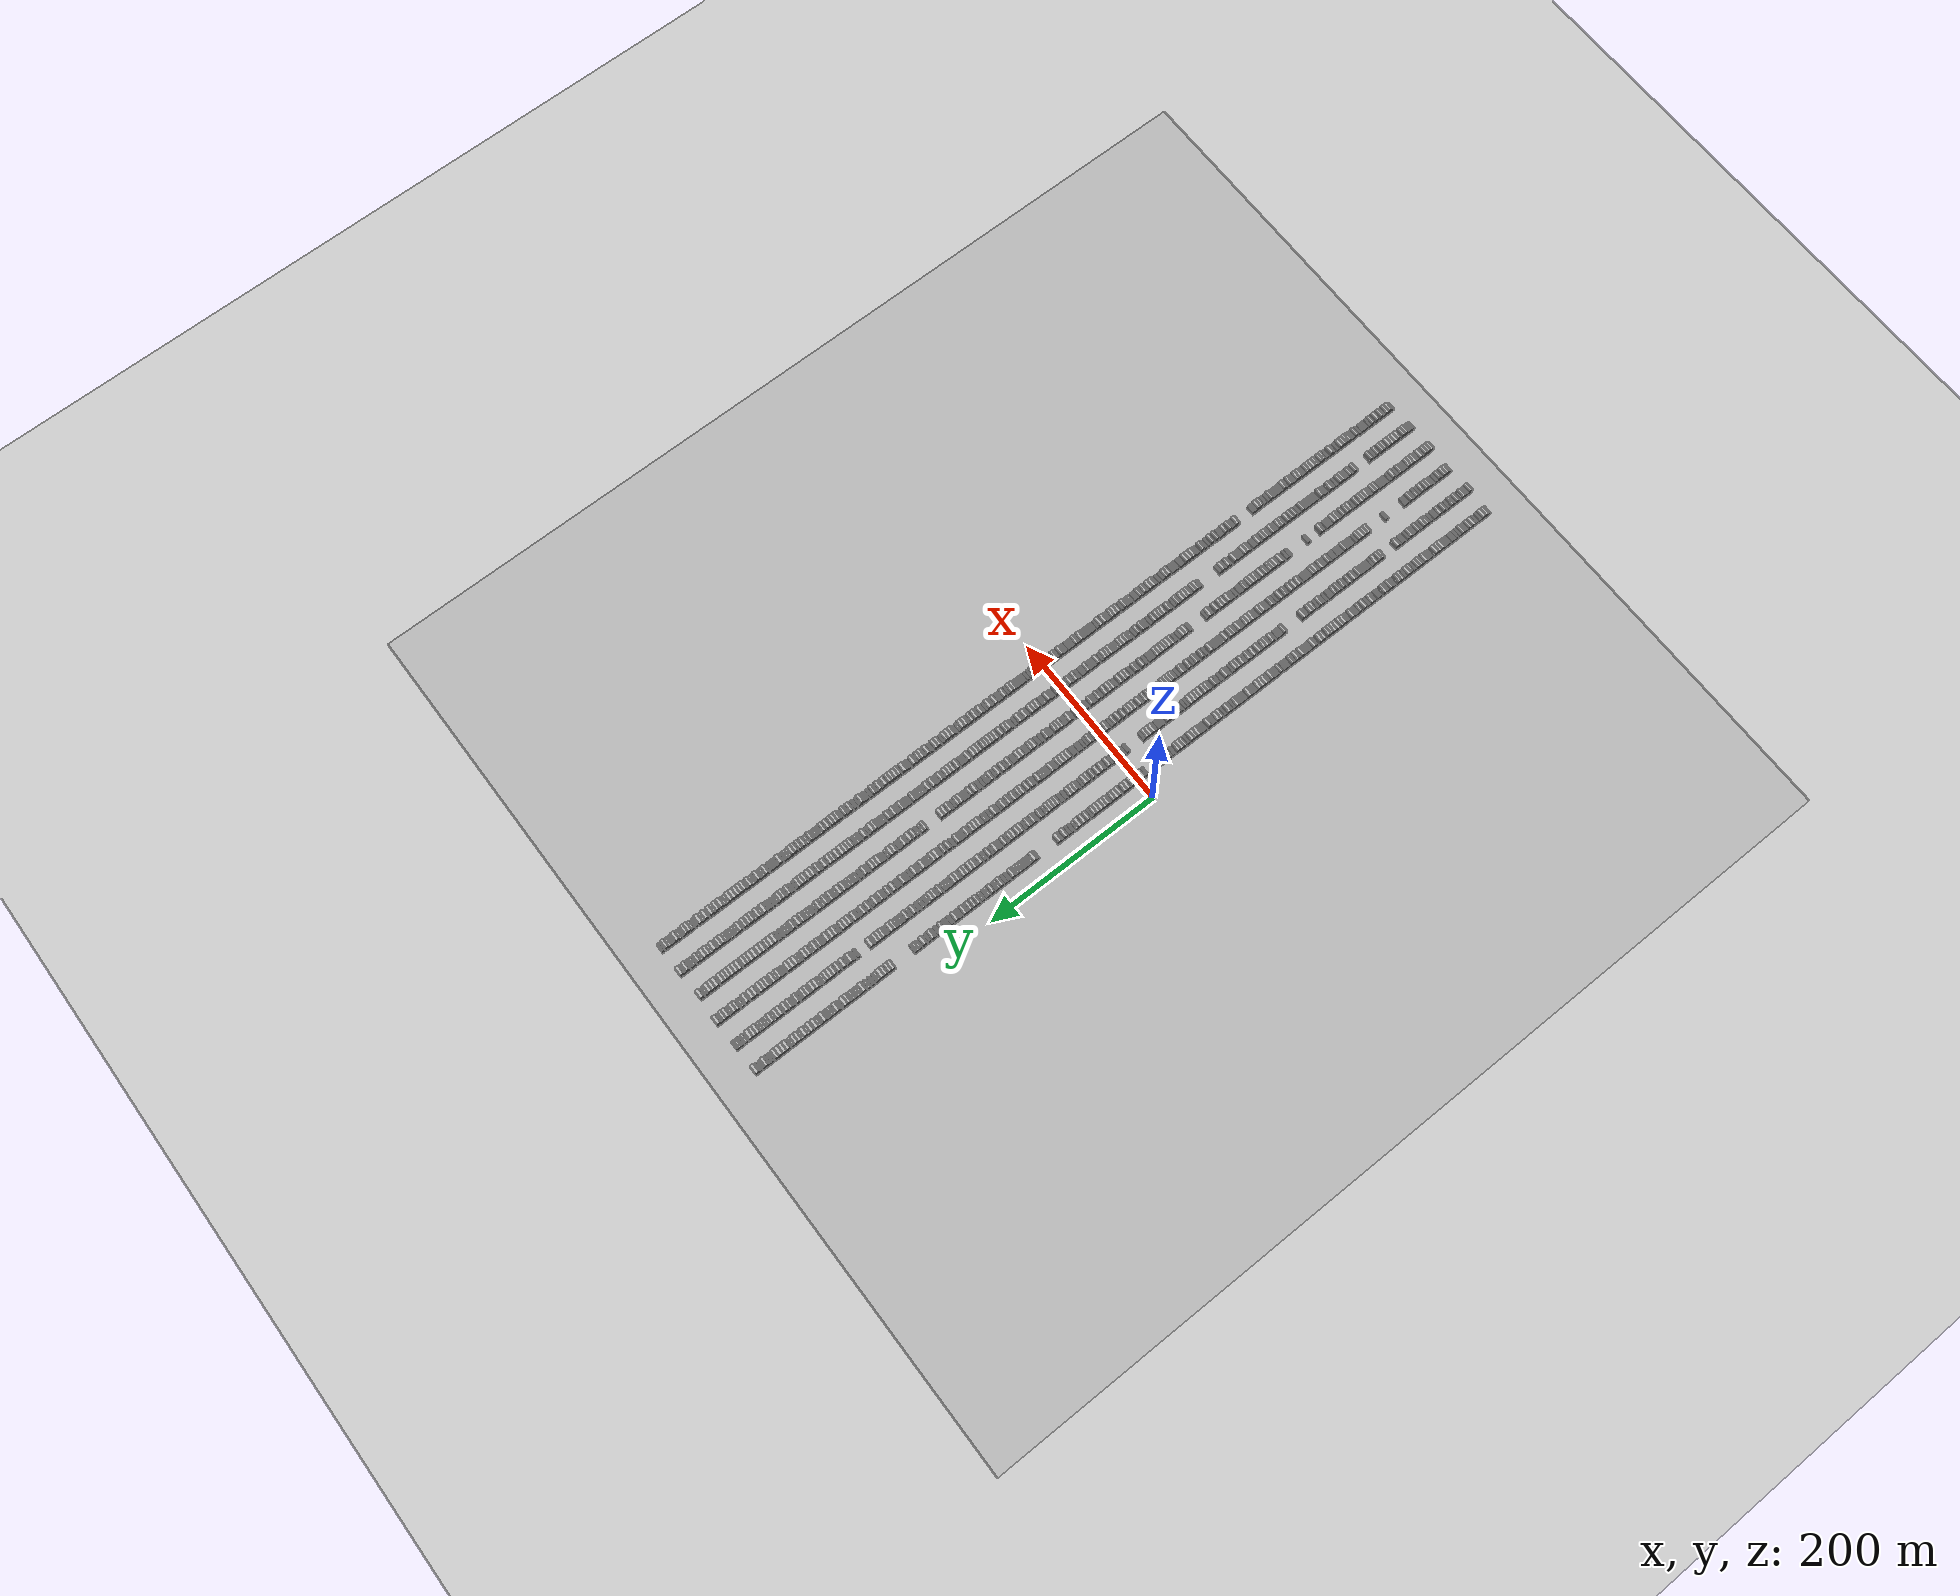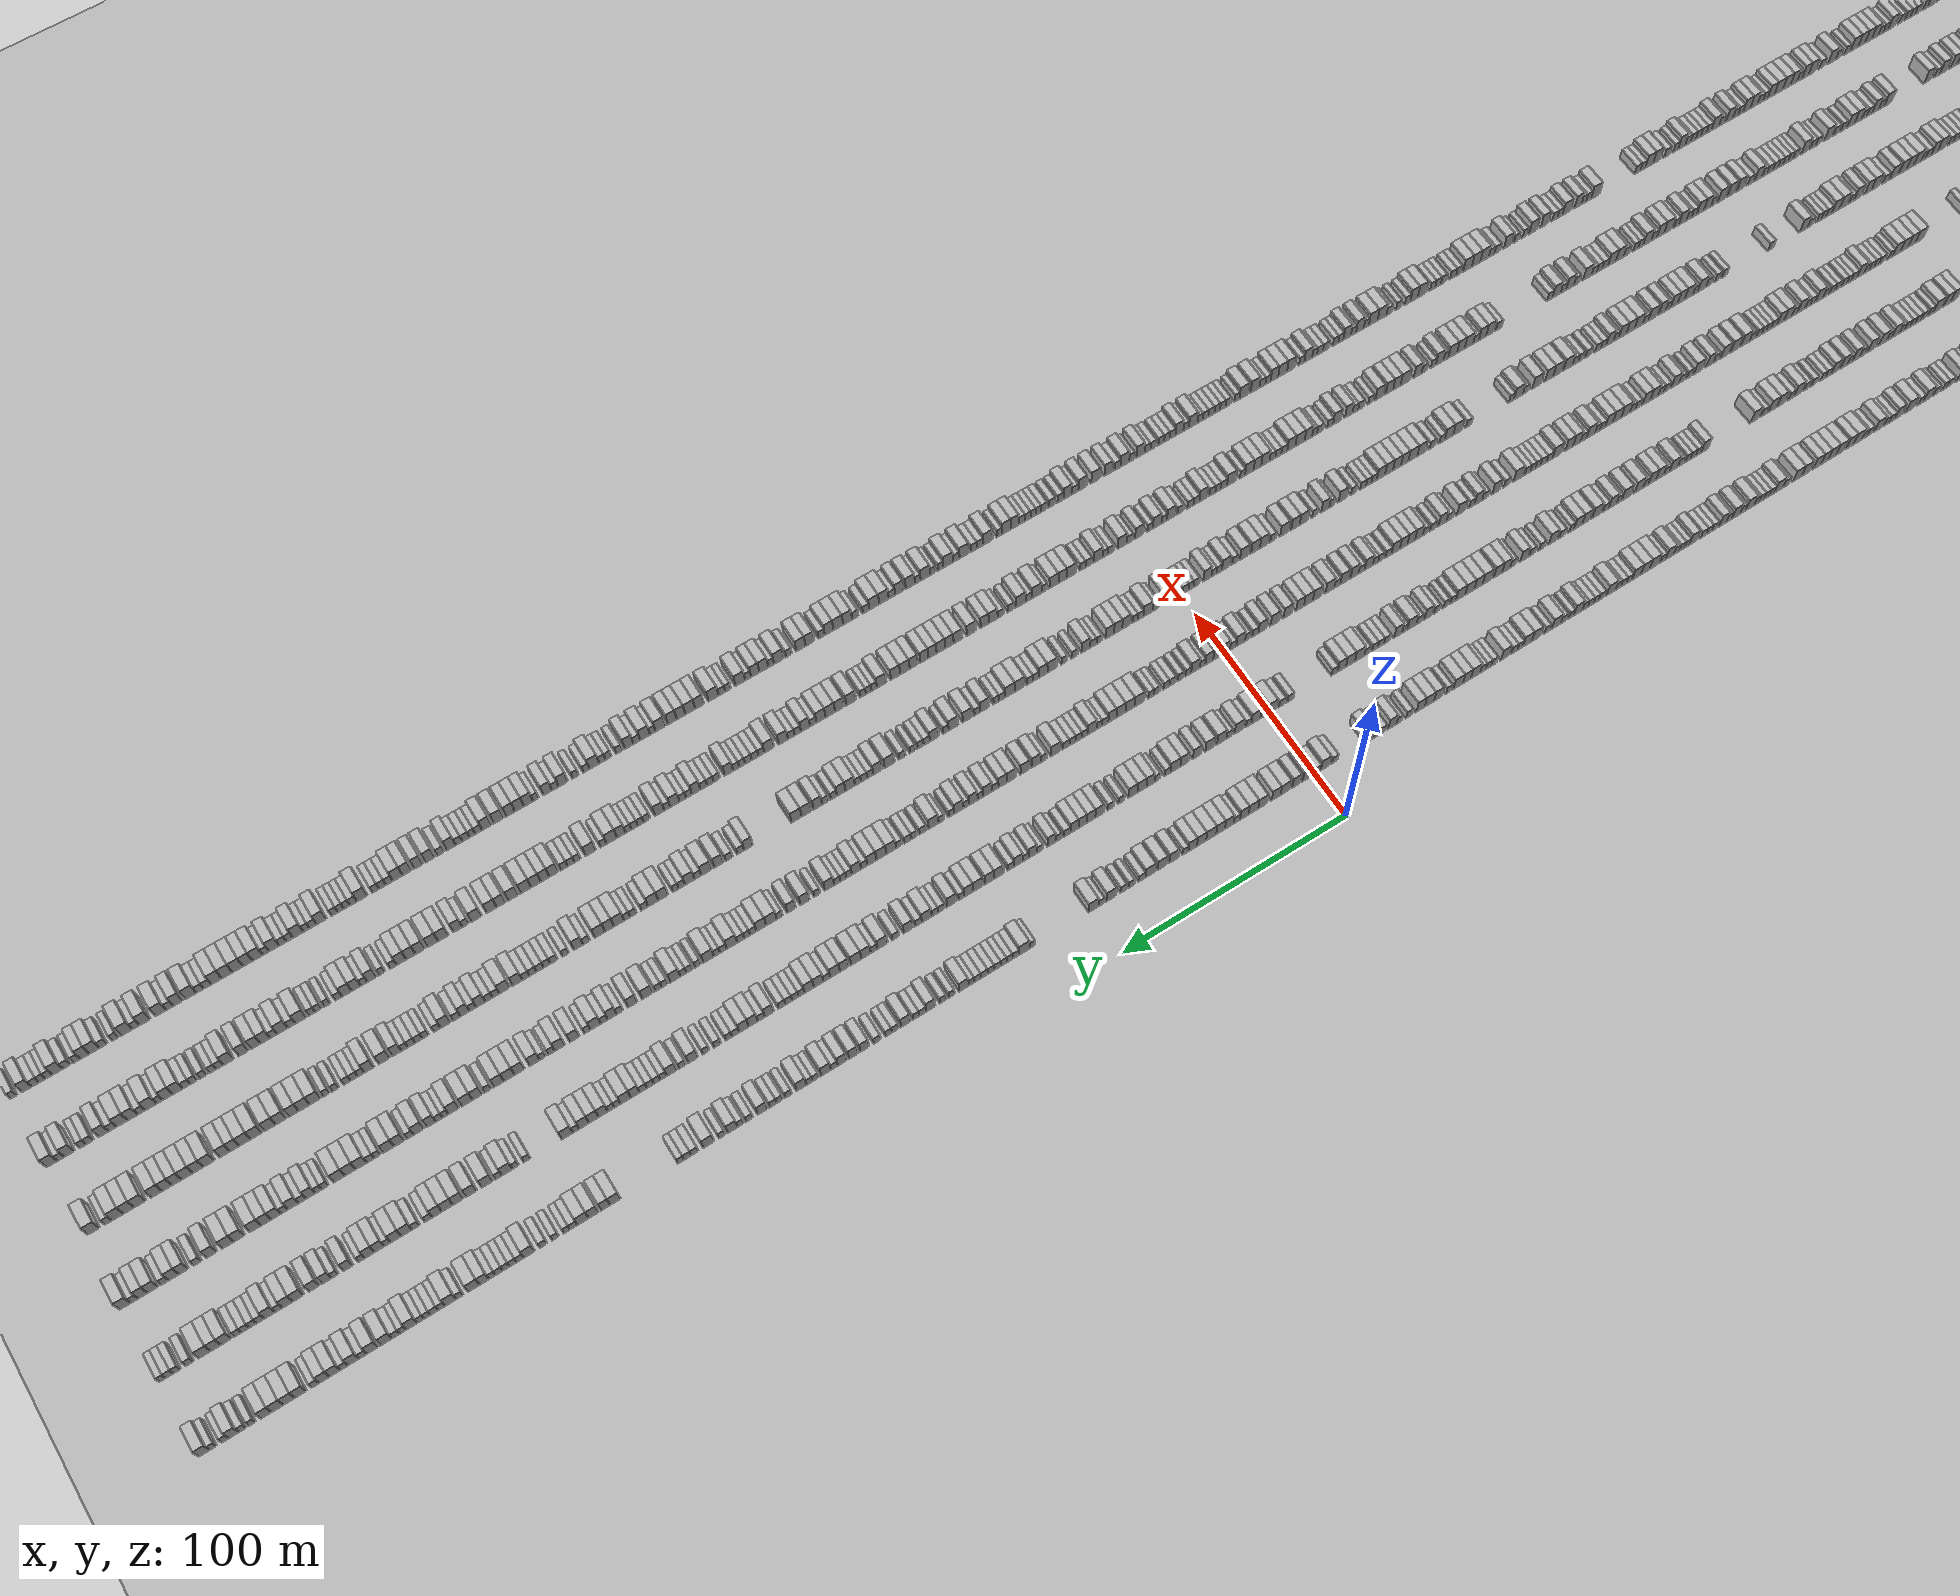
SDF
<sdf version="1.6">
 <world name="default">
  <scene>
   <sky><clouds><speed>12</speed></clouds></sky>
   <ambient>0.4 0.4 0.4 1</ambient>
   <background>0.7 0.7 0.7 1</background>
   <shadows>1</shadows>
  </scene>
  <gravity>0 0 -9.8066</gravity>
  <magnetic_field>6e-06 2.3e-05 -4.2e-05</magnetic_field>
  <physics default="0" name="default_physics" type="ode">
   <ode>
    <solver>
     <type>quick</type>
     <iters>10</iters>
     <sor>1.0</sor>
     <use_dynamic_moi_rescaling>0</use_dynamic_moi_rescaling>
    </solver>
    <constraints>
     <cfm>0</cfm>
     <erp>0.2</erp>
     <contact_max_correcting_vel>100</contact_max_correcting_vel>
     <contact_surface_layer>0.001</contact_surface_layer>
    </constraints>
   </ode>
   <max_step_size>0.004</max_step_size>
   <real_time_factor>1</real_time_factor>
   <real_time_update_rate>250</real_time_update_rate>
  </physics>
  <light name="sun" type="directional">
   <pose>0 0 10 0 0 0</pose>
   <diffuse>0.8 0.8 0.8 1</diffuse>
   <specular>0.2 0.2 0.2 1</specular>
   <attenuation>
    <range>1000</range>
    <constant>0.9</constant>
    <linear>0.01</linear>
    <quadratic>0.001</quadratic>
   </attenuation>
   <direction>-0.5 0.1 -0.9</direction>
  </light>
  <include><name>ground_plane_1</name><uri>model://HANNAS_ground_plane</uri></include>
  <include>
   <name>ground_plane_2</name>
   <uri>model://HANNAS_ground_plane</uri>
   <pose>100 0 0  0 0 0</pose>
  </include>
  <model name="building_1">
   <static>1</static>
   <pose>25.0000 -456.6564 0 0.000000 0.000000 0.000000</pose>
   <link name="link">
    <pose>0 0 3.00 0 0 0</pose>
    <collision name="collision"><geometry><box><size>10.0000 2.6872 6.0000</size></box></geometry></collision>
    <visual name="visual">
     <cast_shadows>0</cast_shadows>
     <geometry><box><size>10.0000 2.6872 6.0000</size></box></geometry>
     <material>
      <script>
       <uri>model://HANNAS_wall/materials/scripts</uri>
       <uri>model://HANNAS_wall/materials/textures</uri>
       <name>vrc/HANNAS_wall</name>
      </script>
     </material>
    </visual>
   </link>
  </model>
  <model name="building_2">
   <static>1</static>
   <pose>25.0000 -453.3822 0 0.000000 0.000000 0.000000</pose>
   <link name="link">
    <pose>0 0 4.50 0 0 0</pose>
    <collision name="collision"><geometry><box><size>10.0000 3.8613 9.0000</size></box></geometry></collision>
    <visual name="visual">
     <cast_shadows>0</cast_shadows>
     <geometry><box><size>10.0000 3.8613 9.0000</size></box></geometry>
     <material>
      <script>
       <uri>model://HANNAS_wall/materials/scripts</uri>
       <uri>model://HANNAS_wall/materials/textures</uri>
       <name>vrc/HANNAS_wall</name>
      </script>
     </material>
    </visual>
   </link>
  </model>
  <model name="building_3">
   <static>1</static>
   <pose>25.0000 -449.2479 0 0.000000 0.000000 0.000000</pose>
   <link name="link">
    <pose>0 0 4.50 0 0 0</pose>
    <collision name="collision"><geometry><box><size>10.0000 4.4073 9.0000</size></box></geometry></collision>
    <visual name="visual">
     <cast_shadows>0</cast_shadows>
     <geometry><box><size>10.0000 4.4073 9.0000</size></box></geometry>
     <material>
      <script>
       <uri>model://HANNAS_wall/materials/scripts</uri>
       <uri>model://HANNAS_wall/materials/textures</uri>
       <name>vrc/HANNAS_wall</name>
      </script>
     </material>
    </visual>
   </link>
  </model>
  <model name="building_4">
   <static>1</static>
   <pose>25.0000 -445.6786 0 0.000000 0.000000 0.000000</pose>
   <link name="link">
    <pose>0 0 3.00 0 0 0</pose>
    <collision name="collision"><geometry><box><size>10.0000 2.7313 6.0000</size></box></geometry></collision>
    <visual name="visual">
     <cast_shadows>0</cast_shadows>
     <geometry><box><size>10.0000 2.7313 6.0000</size></box></geometry>
     <material>
      <script>
       <uri>model://HANNAS_wall/materials/scripts</uri>
       <uri>model://HANNAS_wall/materials/textures</uri>
       <name>vrc/HANNAS_wall</name>
      </script>
     </material>
    </visual>
   </link>
  </model>
  <model name="building_5">
   <static>1</static>
   <pose>25.0000 -440.9629 0 0.000000 0.000000 0.000000</pose>
   <link name="link">
    <pose>0 0 3.00 0 0 0</pose>
    <collision name="collision"><geometry><box><size>10.0000 2.7001 6.0000</size></box></geometry></collision>
    <visual name="visual">
     <cast_shadows>0</cast_shadows>
     <geometry><box><size>10.0000 2.7001 6.0000</size></box></geometry>
     <material>
      <script>
       <uri>model://HANNAS_wall/materials/scripts</uri>
       <uri>model://HANNAS_wall/materials/textures</uri>
       <name>vrc/HANNAS_wall</name>
      </script>
     </material>
    </visual>
   </link>
  </model>
  <model name="building_6">
   <static>1</static>
   <pose>25.0000 -435.4738 0 0.000000 0.000000 0.000000</pose>
   <link name="link">
    <pose>0 0 4.50 0 0 0</pose>
    <collision name="collision"><geometry><box><size>10.0000 4.2782 9.0000</size></box></geometry></collision>
    <visual name="visual">
     <cast_shadows>0</cast_shadows>
     <geometry><box><size>10.0000 4.2782 9.0000</size></box></geometry>
     <material>
      <script>
       <uri>model://HANNAS_wall/materials/scripts</uri>
       <uri>model://HANNAS_wall/materials/textures</uri>
       <name>vrc/HANNAS_wall</name>
      </script>
     </material>
    </visual>
   </link>
  </model>
  <model name="building_7">
   <static>1</static>
   <pose>25.0000 -430.4584 0 0.000000 0.000000 0.000000</pose>
   <link name="link">
    <pose>0 0 4.50 0 0 0</pose>
    <collision name="collision"><geometry><box><size>10.0000 3.7526 9.0000</size></box></geometry></collision>
    <visual name="visual">
     <cast_shadows>0</cast_shadows>
     <geometry><box><size>10.0000 3.7526 9.0000</size></box></geometry>
     <material>
      <script>
       <uri>model://HANNAS_wall/materials/scripts</uri>
       <uri>model://HANNAS_wall/materials/textures</uri>
       <name>vrc/HANNAS_wall</name>
      </script>
     </material>
    </visual>
   </link>
  </model>
  <model name="building_8">
   <static>1</static>
   <pose>25.0000 -427.0855 0 0.000000 0.000000 0.000000</pose>
   <link name="link">
    <pose>0 0 3.00 0 0 0</pose>
    <collision name="collision"><geometry><box><size>10.0000 2.9931 6.0000</size></box></geometry></collision>
    <visual name="visual">
     <cast_shadows>0</cast_shadows>
     <geometry><box><size>10.0000 2.9931 6.0000</size></box></geometry>
     <material>
      <script>
       <uri>model://HANNAS_wall/materials/scripts</uri>
       <uri>model://HANNAS_wall/materials/textures</uri>
       <name>vrc/HANNAS_wall</name>
      </script>
     </material>
    </visual>
   </link>
  </model>
  <model name="building_9">
   <static>1</static>
   <pose>25.0000 -424.3792 0 0.000000 0.000000 0.000000</pose>
   <link name="link">
    <pose>0 0 3.00 0 0 0</pose>
    <collision name="collision"><geometry><box><size>10.0000 2.4194 6.0000</size></box></geometry></collision>
    <visual name="visual">
     <cast_shadows>0</cast_shadows>
     <geometry><box><size>10.0000 2.4194 6.0000</size></box></geometry>
     <material>
      <script>
       <uri>model://HANNAS_wall/materials/scripts</uri>
       <uri>model://HANNAS_wall/materials/textures</uri>
       <name>vrc/HANNAS_wall</name>
      </script>
     </material>
    </visual>
   </link>
  </model>
  <model name="building_10">
   <static>1</static>
   <pose>25.0000 -421.2314 0 0.000000 0.000000 0.000000</pose>
   <link name="link">
    <pose>0 0 4.50 0 0 0</pose>
    <collision name="collision"><geometry><box><size>10.0000 3.8762 9.0000</size></box></geometry></collision>
    <visual name="visual">
     <cast_shadows>0</cast_shadows>
     <geometry><box><size>10.0000 3.8762 9.0000</size></box></geometry>
     <material>
      <script>
       <uri>model://HANNAS_wall/materials/scripts</uri>
       <uri>model://HANNAS_wall/materials/textures</uri>
       <name>vrc/HANNAS_wall</name>
      </script>
     </material>
    </visual>
   </link>
  </model>
  <model name="building_11">
   <static>1</static>
   <pose>25.0000 -418.0256 0 0.000000 0.000000 0.000000</pose>
   <link name="link">
    <pose>0 0 3.00 0 0 0</pose>
    <collision name="collision"><geometry><box><size>10.0000 2.5354 6.0000</size></box></geometry></collision>
    <visual name="visual">
     <cast_shadows>0</cast_shadows>
     <geometry><box><size>10.0000 2.5354 6.0000</size></box></geometry>
     <material>
      <script>
       <uri>model://HANNAS_wall/materials/scripts</uri>
       <uri>model://HANNAS_wall/materials/textures</uri>
       <name>vrc/HANNAS_wall</name>
      </script>
     </material>
    </visual>
   </link>
  </model>
  <model name="building_12">
   <static>1</static>
   <pose>25.0000 -414.4273 0 0.000000 0.000000 0.000000</pose>
   <link name="link">
    <pose>0 0 3.00 0 0 0</pose>
    <collision name="collision"><geometry><box><size>10.0000 2.6613 6.0000</size></box></geometry></collision>
    <visual name="visual">
     <cast_shadows>0</cast_shadows>
     <geometry><box><size>10.0000 2.6613 6.0000</size></box></geometry>
     <material>
      <script>
       <uri>model://HANNAS_wall/materials/scripts</uri>
       <uri>model://HANNAS_wall/materials/textures</uri>
       <name>vrc/HANNAS_wall</name>
      </script>
     </material>
    </visual>
   </link>
  </model>
  <model name="building_13">
   <static>1</static>
   <pose>25.0000 -410.8534 0 0.000000 0.000000 0.000000</pose>
   <link name="link">
    <pose>0 0 3.00 0 0 0</pose>
    <collision name="collision"><geometry><box><size>10.0000 2.4866 6.0000</size></box></geometry></collision>
    <visual name="visual">
     <cast_shadows>0</cast_shadows>
     <geometry><box><size>10.0000 2.4866 6.0000</size></box></geometry>
     <material>
      <script>
       <uri>model://HANNAS_wall/materials/scripts</uri>
       <uri>model://HANNAS_wall/materials/textures</uri>
       <name>vrc/HANNAS_wall</name>
      </script>
     </material>
    </visual>
   </link>
  </model>
  <model name="building_14">
   <static>1</static>
   <pose>25.0000 -408.3396 0 0.000000 0.000000 0.000000</pose>
   <link name="link">
    <pose>0 0 3.00 0 0 0</pose>
    <collision name="collision"><geometry><box><size>10.0000 2.5410 6.0000</size></box></geometry></collision>
    <visual name="visual">
     <cast_shadows>0</cast_shadows>
     <geometry><box><size>10.0000 2.5410 6.0000</size></box></geometry>
     <material>
      <script>
       <uri>model://HANNAS_wall/materials/scripts</uri>
       <uri>model://HANNAS_wall/materials/textures</uri>
       <name>vrc/HANNAS_wall</name>
      </script>
     </material>
    </visual>
   </link>
  </model>
  <model name="building_15">
   <static>1</static>
   <pose>25.0000 -403.6164 0 0.000000 0.000000 0.000000</pose>
   <link name="link">
    <pose>0 0 3.00 0 0 0</pose>
    <collision name="collision"><geometry><box><size>10.0000 2.9055 6.0000</size></box></geometry></collision>
    <visual name="visual">
     <cast_shadows>0</cast_shadows>
     <geometry><box><size>10.0000 2.9055 6.0000</size></box></geometry>
     <material>
      <script>
       <uri>model://HANNAS_wall/materials/scripts</uri>
       <uri>model://HANNAS_wall/materials/textures</uri>
       <name>vrc/HANNAS_wall</name>
      </script>
     </material>
    </visual>
   </link>
  </model>
  <model name="building_16">
   <static>1</static>
   <pose>25.0000 -400.7465 0 0.000000 0.000000 0.000000</pose>
   <link name="link">
    <pose>0 0 3.00 0 0 0</pose>
    <collision name="collision"><geometry><box><size>10.0000 2.8342 6.0000</size></box></geometry></collision>
    <visual name="visual">
     <cast_shadows>0</cast_shadows>
     <geometry><box><size>10.0000 2.8342 6.0000</size></box></geometry>
     <material>
      <script>
       <uri>model://HANNAS_wall/materials/scripts</uri>
       <uri>model://HANNAS_wall/materials/textures</uri>
       <name>vrc/HANNAS_wall</name>
      </script>
     </material>
    </visual>
   </link>
  </model>
  <model name="building_17">
   <static>1</static>
   <pose>25.0000 -397.8781 0 0.000000 0.000000 0.000000</pose>
   <link name="link">
    <pose>0 0 3.00 0 0 0</pose>
    <collision name="collision"><geometry><box><size>10.0000 2.9028 6.0000</size></box></geometry></collision>
    <visual name="visual">
     <cast_shadows>0</cast_shadows>
     <geometry><box><size>10.0000 2.9028 6.0000</size></box></geometry>
     <material>
      <script>
       <uri>model://HANNAS_wall/materials/scripts</uri>
       <uri>model://HANNAS_wall/materials/textures</uri>
       <name>vrc/HANNAS_wall</name>
      </script>
     </material>
    </visual>
   </link>
  </model>
  <model name="building_18">
   <static>1</static>
   <pose>25.0000 -394.2072 0 0.000000 0.000000 0.000000</pose>
   <link name="link">
    <pose>0 0 4.50 0 0 0</pose>
    <collision name="collision"><geometry><box><size>10.0000 4.4391 9.0000</size></box></geometry></collision>
    <visual name="visual">
     <cast_shadows>0</cast_shadows>
     <geometry><box><size>10.0000 4.4391 9.0000</size></box></geometry>
     <material>
      <script>
       <uri>model://HANNAS_wall/materials/scripts</uri>
       <uri>model://HANNAS_wall/materials/textures</uri>
       <name>vrc/HANNAS_wall</name>
      </script>
     </material>
    </visual>
   </link>
  </model>
  <model name="building_19">
   <static>1</static>
   <pose>25.0000 -389.8384 0 0.000000 0.000000 0.000000</pose>
   <link name="link">
    <pose>0 0 4.50 0 0 0</pose>
    <collision name="collision"><geometry><box><size>10.0000 4.2985 9.0000</size></box></geometry></collision>
    <visual name="visual">
     <cast_shadows>0</cast_shadows>
     <geometry><box><size>10.0000 4.2985 9.0000</size></box></geometry>
     <material>
      <script>
       <uri>model://HANNAS_wall/materials/scripts</uri>
       <uri>model://HANNAS_wall/materials/textures</uri>
       <name>vrc/HANNAS_wall</name>
      </script>
     </material>
    </visual>
   </link>
  </model>
  <model name="building_20">
   <static>1</static>
   <pose>25.0000 -385.4774 0 0.000000 0.000000 0.000000</pose>
   <link name="link">
    <pose>0 0 4.50 0 0 0</pose>
    <collision name="collision"><geometry><box><size>10.0000 4.4234 9.0000</size></box></geometry></collision>
    <visual name="visual">
     <cast_shadows>0</cast_shadows>
     <geometry><box><size>10.0000 4.4234 9.0000</size></box></geometry>
     <material>
      <script>
       <uri>model://HANNAS_wall/materials/scripts</uri>
       <uri>model://HANNAS_wall/materials/textures</uri>
       <name>vrc/HANNAS_wall</name>
      </script>
     </material>
    </visual>
   </link>
  </model>
  <model name="building_21">
   <static>1</static>
   <pose>25.0000 -379.9228 0 0.000000 0.000000 0.000000</pose>
   <link name="link">
    <pose>0 0 3.00 0 0 0</pose>
    <collision name="collision"><geometry><box><size>10.0000 2.6857 6.0000</size></box></geometry></collision>
    <visual name="visual">
     <cast_shadows>0</cast_shadows>
     <geometry><box><size>10.0000 2.6857 6.0000</size></box></geometry>
     <material>
      <script>
       <uri>model://HANNAS_wall/materials/scripts</uri>
       <uri>model://HANNAS_wall/materials/textures</uri>
       <name>vrc/HANNAS_wall</name>
      </script>
     </material>
    </visual>
   </link>
  </model>
  <model name="building_22">
   <static>1</static>
   <pose>25.0000 -377.3635 0 0.000000 0.000000 0.000000</pose>
   <link name="link">
    <pose>0 0 3.00 0 0 0</pose>
    <collision name="collision"><geometry><box><size>10.0000 2.4329 6.0000</size></box></geometry></collision>
    <visual name="visual">
     <cast_shadows>0</cast_shadows>
     <geometry><box><size>10.0000 2.4329 6.0000</size></box></geometry>
     <material>
      <script>
       <uri>model://HANNAS_wall/materials/scripts</uri>
       <uri>model://HANNAS_wall/materials/textures</uri>
       <name>vrc/HANNAS_wall</name>
      </script>
     </material>
    </visual>
   </link>
  </model>
  <model name="building_23">
   <static>1</static>
   <pose>25.0000 -374.7342 0 0.000000 0.000000 0.000000</pose>
   <link name="link">
    <pose>0 0 3.00 0 0 0</pose>
    <collision name="collision"><geometry><box><size>10.0000 2.8256 6.0000</size></box></geometry></collision>
    <visual name="visual">
     <cast_shadows>0</cast_shadows>
     <geometry><box><size>10.0000 2.8256 6.0000</size></box></geometry>
     <material>
      <script>
       <uri>model://HANNAS_wall/materials/scripts</uri>
       <uri>model://HANNAS_wall/materials/textures</uri>
       <name>vrc/HANNAS_wall</name>
      </script>
     </material>
    </visual>
   </link>
  </model>
  <model name="building_24">
   <static>1</static>
   <pose>25.0000 -371.2654 0 0.000000 0.000000 0.000000</pose>
   <link name="link">
    <pose>0 0 4.50 0 0 0</pose>
    <collision name="collision"><geometry><box><size>10.0000 4.1121 9.0000</size></box></geometry></collision>
    <visual name="visual">
     <cast_shadows>0</cast_shadows>
     <geometry><box><size>10.0000 4.1121 9.0000</size></box></geometry>
     <material>
      <script>
       <uri>model://HANNAS_wall/materials/scripts</uri>
       <uri>model://HANNAS_wall/materials/textures</uri>
       <name>vrc/HANNAS_wall</name>
      </script>
     </material>
    </visual>
   </link>
  </model>
  <model name="building_25">
   <static>1</static>
   <pose>25.0000 -367.8221 0 0.000000 0.000000 0.000000</pose>
   <link name="link">
    <pose>0 0 3.00 0 0 0</pose>
    <collision name="collision"><geometry><box><size>10.0000 2.7745 6.0000</size></box></geometry></collision>
    <visual name="visual">
     <cast_shadows>0</cast_shadows>
     <geometry><box><size>10.0000 2.7745 6.0000</size></box></geometry>
     <material>
      <script>
       <uri>model://HANNAS_wall/materials/scripts</uri>
       <uri>model://HANNAS_wall/materials/textures</uri>
       <name>vrc/HANNAS_wall</name>
      </script>
     </material>
    </visual>
   </link>
  </model>
  <model name="building_26">
   <static>1</static>
   <pose>25.0000 -364.5692 0 0.000000 0.000000 0.000000</pose>
   <link name="link">
    <pose>0 0 4.50 0 0 0</pose>
    <collision name="collision"><geometry><box><size>10.0000 3.7311 9.0000</size></box></geometry></collision>
    <visual name="visual">
     <cast_shadows>0</cast_shadows>
     <geometry><box><size>10.0000 3.7311 9.0000</size></box></geometry>
     <material>
      <script>
       <uri>model://HANNAS_wall/materials/scripts</uri>
       <uri>model://HANNAS_wall/materials/textures</uri>
       <name>vrc/HANNAS_wall</name>
      </script>
     </material>
    </visual>
   </link>
  </model>
  <model name="building_27">
   <static>1</static>
   <pose>25.0000 -360.7583 0 0.000000 0.000000 0.000000</pose>
   <link name="link">
    <pose>0 0 4.50 0 0 0</pose>
    <collision name="collision"><geometry><box><size>10.0000 3.8907 9.0000</size></box></geometry></collision>
    <visual name="visual">
     <cast_shadows>0</cast_shadows>
     <geometry><box><size>10.0000 3.8907 9.0000</size></box></geometry>
     <material>
      <script>
       <uri>model://HANNAS_wall/materials/scripts</uri>
       <uri>model://HANNAS_wall/materials/textures</uri>
       <name>vrc/HANNAS_wall</name>
      </script>
     </material>
    </visual>
   </link>
  </model>
  <model name="building_28">
   <static>1</static>
   <pose>25.0000 -357.4832 0 0.000000 0.000000 0.000000</pose>
   <link name="link">
    <pose>0 0 3.00 0 0 0</pose>
    <collision name="collision"><geometry><box><size>10.0000 2.6595 6.0000</size></box></geometry></collision>
    <visual name="visual">
     <cast_shadows>0</cast_shadows>
     <geometry><box><size>10.0000 2.6595 6.0000</size></box></geometry>
     <material>
      <script>
       <uri>model://HANNAS_wall/materials/scripts</uri>
       <uri>model://HANNAS_wall/materials/textures</uri>
       <name>vrc/HANNAS_wall</name>
      </script>
     </material>
    </visual>
   </link>
  </model>
  <model name="building_29">
   <static>1</static>
   <pose>25.0000 -352.3523 0 0.000000 0.000000 0.000000</pose>
   <link name="link">
    <pose>0 0 4.50 0 0 0</pose>
    <collision name="collision"><geometry><box><size>10.0000 3.6022 9.0000</size></box></geometry></collision>
    <visual name="visual">
     <cast_shadows>0</cast_shadows>
     <geometry><box><size>10.0000 3.6022 9.0000</size></box></geometry>
     <material>
      <script>
       <uri>model://HANNAS_wall/materials/scripts</uri>
       <uri>model://HANNAS_wall/materials/textures</uri>
       <name>vrc/HANNAS_wall</name>
      </script>
     </material>
    </visual>
   </link>
  </model>
  <model name="building_30">
   <static>1</static>
   <pose>25.0000 -348.4182 0 0.000000 0.000000 0.000000</pose>
   <link name="link">
    <pose>0 0 4.50 0 0 0</pose>
    <collision name="collision"><geometry><box><size>10.0000 4.2660 9.0000</size></box></geometry></collision>
    <visual name="visual">
     <cast_shadows>0</cast_shadows>
     <geometry><box><size>10.0000 4.2660 9.0000</size></box></geometry>
     <material>
      <script>
       <uri>model://HANNAS_wall/materials/scripts</uri>
       <uri>model://HANNAS_wall/materials/textures</uri>
       <name>vrc/HANNAS_wall</name>
      </script>
     </material>
    </visual>
   </link>
  </model>
  <model name="building_31">
   <static>1</static>
   <pose>25.0000 -345.0613 0 0.000000 0.000000 0.000000</pose>
   <link name="link">
    <pose>0 0 3.00 0 0 0</pose>
    <collision name="collision"><geometry><box><size>10.0000 2.4478 6.0000</size></box></geometry></collision>
    <visual name="visual">
     <cast_shadows>0</cast_shadows>
     <geometry><box><size>10.0000 2.4478 6.0000</size></box></geometry>
     <material>
      <script>
       <uri>model://HANNAS_wall/materials/scripts</uri>
       <uri>model://HANNAS_wall/materials/textures</uri>
       <name>vrc/HANNAS_wall</name>
      </script>
     </material>
    </visual>
   </link>
  </model>
  <model name="building_32">
   <static>1</static>
   <pose>25.0000 -339.6926 0 0.000000 0.000000 0.000000</pose>
   <link name="link">
    <pose>0 0 4.50 0 0 0</pose>
    <collision name="collision"><geometry><box><size>10.0000 4.2896 9.0000</size></box></geometry></collision>
    <visual name="visual">
     <cast_shadows>0</cast_shadows>
     <geometry><box><size>10.0000 4.2896 9.0000</size></box></geometry>
     <material>
      <script>
       <uri>model://HANNAS_wall/materials/scripts</uri>
       <uri>model://HANNAS_wall/materials/textures</uri>
       <name>vrc/HANNAS_wall</name>
      </script>
     </material>
    </visual>
   </link>
  </model>
  <model name="building_33">
   <static>1</static>
   <pose>25.0000 -335.6568 0 0.000000 0.000000 0.000000</pose>
   <link name="link">
    <pose>0 0 4.50 0 0 0</pose>
    <collision name="collision"><geometry><box><size>10.0000 3.7820 9.0000</size></box></geometry></collision>
    <visual name="visual">
     <cast_shadows>0</cast_shadows>
     <geometry><box><size>10.0000 3.7820 9.0000</size></box></geometry>
     <material>
      <script>
       <uri>model://HANNAS_wall/materials/scripts</uri>
       <uri>model://HANNAS_wall/materials/textures</uri>
       <name>vrc/HANNAS_wall</name>
      </script>
     </material>
    </visual>
   </link>
  </model>
  <model name="building_34">
   <static>1</static>
   <pose>25.0000 -330.4455 0 0.000000 0.000000 0.000000</pose>
   <link name="link">
    <pose>0 0 3.00 0 0 0</pose>
    <collision name="collision"><geometry><box><size>10.0000 2.6406 6.0000</size></box></geometry></collision>
    <visual name="visual">
     <cast_shadows>0</cast_shadows>
     <geometry><box><size>10.0000 2.6406 6.0000</size></box></geometry>
     <material>
      <script>
       <uri>model://HANNAS_wall/materials/scripts</uri>
       <uri>model://HANNAS_wall/materials/textures</uri>
       <name>vrc/HANNAS_wall</name>
      </script>
     </material>
    </visual>
   </link>
  </model>
  <model name="building_35">
   <static>1</static>
   <pose>25.0000 -327.8226 0 0.000000 0.000000 0.000000</pose>
   <link name="link">
    <pose>0 0 3.00 0 0 0</pose>
    <collision name="collision"><geometry><box><size>10.0000 2.6051 6.0000</size></box></geometry></collision>
    <visual name="visual">
     <cast_shadows>0</cast_shadows>
     <geometry><box><size>10.0000 2.6051 6.0000</size></box></geometry>
     <material>
      <script>
       <uri>model://HANNAS_wall/materials/scripts</uri>
       <uri>model://HANNAS_wall/materials/textures</uri>
       <name>vrc/HANNAS_wall</name>
      </script>
     </material>
    </visual>
   </link>
  </model>
  <model name="building_36">
   <static>1</static>
   <pose>25.0000 -324.6430 0 0.000000 0.000000 0.000000</pose>
   <link name="link">
    <pose>0 0 4.50 0 0 0</pose>
    <collision name="collision"><geometry><box><size>10.0000 3.7541 9.0000</size></box></geometry></collision>
    <visual name="visual">
     <cast_shadows>0</cast_shadows>
     <geometry><box><size>10.0000 3.7541 9.0000</size></box></geometry>
     <material>
      <script>
       <uri>model://HANNAS_wall/materials/scripts</uri>
       <uri>model://HANNAS_wall/materials/textures</uri>
       <name>vrc/HANNAS_wall</name>
      </script>
     </material>
    </visual>
   </link>
  </model>
  <model name="building_37">
   <static>1</static>
   <pose>25.0000 -321.2948 0 0.000000 0.000000 0.000000</pose>
   <link name="link">
    <pose>0 0 3.00 0 0 0</pose>
    <collision name="collision"><geometry><box><size>10.0000 2.9424 6.0000</size></box></geometry></collision>
    <visual name="visual">
     <cast_shadows>0</cast_shadows>
     <geometry><box><size>10.0000 2.9424 6.0000</size></box></geometry>
     <material>
      <script>
       <uri>model://HANNAS_wall/materials/scripts</uri>
       <uri>model://HANNAS_wall/materials/textures</uri>
       <name>vrc/HANNAS_wall</name>
      </script>
     </material>
    </visual>
   </link>
  </model>
  <model name="building_38">
   <static>1</static>
   <pose>25.0000 -316.8187 0 0.000000 0.000000 0.000000</pose>
   <link name="link">
    <pose>0 0 4.50 0 0 0</pose>
    <collision name="collision"><geometry><box><size>10.0000 4.0096 9.0000</size></box></geometry></collision>
    <visual name="visual">
     <cast_shadows>0</cast_shadows>
     <geometry><box><size>10.0000 4.0096 9.0000</size></box></geometry>
     <material>
      <script>
       <uri>model://HANNAS_wall/materials/scripts</uri>
       <uri>model://HANNAS_wall/materials/textures</uri>
       <name>vrc/HANNAS_wall</name>
      </script>
     </material>
    </visual>
   </link>
  </model>
  <model name="building_39">
   <static>1</static>
   <pose>25.0000 -311.4436 0 0.000000 0.000000 0.000000</pose>
   <link name="link">
    <pose>0 0 3.00 0 0 0</pose>
    <collision name="collision"><geometry><box><size>10.0000 2.7406 6.0000</size></box></geometry></collision>
    <visual name="visual">
     <cast_shadows>0</cast_shadows>
     <geometry><box><size>10.0000 2.7406 6.0000</size></box></geometry>
     <material>
      <script>
       <uri>model://HANNAS_wall/materials/scripts</uri>
       <uri>model://HANNAS_wall/materials/textures</uri>
       <name>vrc/HANNAS_wall</name>
      </script>
     </material>
    </visual>
   </link>
  </model>
  <model name="building_40">
   <static>1</static>
   <pose>25.0000 -308.6989 0 0.000000 0.000000 0.000000</pose>
   <link name="link">
    <pose>0 0 3.00 0 0 0</pose>
    <collision name="collision"><geometry><box><size>10.0000 2.7490 6.0000</size></box></geometry></collision>
    <visual name="visual">
     <cast_shadows>0</cast_shadows>
     <geometry><box><size>10.0000 2.7490 6.0000</size></box></geometry>
     <material>
      <script>
       <uri>model://HANNAS_wall/materials/scripts</uri>
       <uri>model://HANNAS_wall/materials/textures</uri>
       <name>vrc/HANNAS_wall</name>
      </script>
     </material>
    </visual>
   </link>
  </model>
  <model name="building_41">
   <static>1</static>
   <pose>25.0000 -304.0671 0 0.000000 0.000000 0.000000</pose>
   <link name="link">
    <pose>0 0 3.00 0 0 0</pose>
    <collision name="collision"><geometry><box><size>10.0000 2.5145 6.0000</size></box></geometry></collision>
    <visual name="visual">
     <cast_shadows>0</cast_shadows>
     <geometry><box><size>10.0000 2.5145 6.0000</size></box></geometry>
     <material>
      <script>
       <uri>model://HANNAS_wall/materials/scripts</uri>
       <uri>model://HANNAS_wall/materials/textures</uri>
       <name>vrc/HANNAS_wall</name>
      </script>
     </material>
    </visual>
   </link>
  </model>
  <model name="building_42">
   <static>1</static>
   <pose>25.0000 -299.6457 0 0.000000 0.000000 0.000000</pose>
   <link name="link">
    <pose>0 0 4.50 0 0 0</pose>
    <collision name="collision"><geometry><box><size>10.0000 4.3284 9.0000</size></box></geometry></collision>
    <visual name="visual">
     <cast_shadows>0</cast_shadows>
     <geometry><box><size>10.0000 4.3284 9.0000</size></box></geometry>
     <material>
      <script>
       <uri>model://HANNAS_wall/materials/scripts</uri>
       <uri>model://HANNAS_wall/materials/textures</uri>
       <name>vrc/HANNAS_wall</name>
      </script>
     </material>
    </visual>
   </link>
  </model>
  <model name="building_43">
   <static>1</static>
   <pose>25.0000 -296.0547 0 0.000000 0.000000 0.000000</pose>
   <link name="link">
    <pose>0 0 3.00 0 0 0</pose>
    <collision name="collision"><geometry><box><size>10.0000 2.8537 6.0000</size></box></geometry></collision>
    <visual name="visual">
     <cast_shadows>0</cast_shadows>
     <geometry><box><size>10.0000 2.8537 6.0000</size></box></geometry>
     <material>
      <script>
       <uri>model://HANNAS_wall/materials/scripts</uri>
       <uri>model://HANNAS_wall/materials/textures</uri>
       <name>vrc/HANNAS_wall</name>
      </script>
     </material>
    </visual>
   </link>
  </model>
  <model name="building_44">
   <static>1</static>
   <pose>25.0000 -290.4198 0 0.000000 0.000000 0.000000</pose>
   <link name="link">
    <pose>0 0 4.50 0 0 0</pose>
    <collision name="collision"><geometry><box><size>10.0000 4.4162 9.0000</size></box></geometry></collision>
    <visual name="visual">
     <cast_shadows>0</cast_shadows>
     <geometry><box><size>10.0000 4.4162 9.0000</size></box></geometry>
     <material>
      <script>
       <uri>model://HANNAS_wall/materials/scripts</uri>
       <uri>model://HANNAS_wall/materials/textures</uri>
       <name>vrc/HANNAS_wall</name>
      </script>
     </material>
    </visual>
   </link>
  </model>
  <model name="building_45">
   <static>1</static>
   <pose>25.0000 -284.3430 0 0.000000 0.000000 0.000000</pose>
   <link name="link">
    <pose>0 0 4.50 0 0 0</pose>
    <collision name="collision"><geometry><box><size>10.0000 3.7375 9.0000</size></box></geometry></collision>
    <visual name="visual">
     <cast_shadows>0</cast_shadows>
     <geometry><box><size>10.0000 3.7375 9.0000</size></box></geometry>
     <material>
      <script>
       <uri>model://HANNAS_wall/materials/scripts</uri>
       <uri>model://HANNAS_wall/materials/textures</uri>
       <name>vrc/HANNAS_wall</name>
      </script>
     </material>
    </visual>
   </link>
  </model>
  <model name="building_46">
   <static>1</static>
   <pose>25.0000 -281.0933 0 0.000000 0.000000 0.000000</pose>
   <link name="link">
    <pose>0 0 3.00 0 0 0</pose>
    <collision name="collision"><geometry><box><size>10.0000 2.7618 6.0000</size></box></geometry></collision>
    <visual name="visual">
     <cast_shadows>0</cast_shadows>
     <geometry><box><size>10.0000 2.7618 6.0000</size></box></geometry>
     <material>
      <script>
       <uri>model://HANNAS_wall/materials/scripts</uri>
       <uri>model://HANNAS_wall/materials/textures</uri>
       <name>vrc/HANNAS_wall</name>
      </script>
     </material>
    </visual>
   </link>
  </model>
  <model name="building_47">
   <static>1</static>
   <pose>25.0000 -278.4432 0 0.000000 0.000000 0.000000</pose>
   <link name="link">
    <pose>0 0 3.00 0 0 0</pose>
    <collision name="collision"><geometry><box><size>10.0000 2.5383 6.0000</size></box></geometry></collision>
    <visual name="visual">
     <cast_shadows>0</cast_shadows>
     <geometry><box><size>10.0000 2.5383 6.0000</size></box></geometry>
     <material>
      <script>
       <uri>model://HANNAS_wall/materials/scripts</uri>
       <uri>model://HANNAS_wall/materials/textures</uri>
       <name>vrc/HANNAS_wall</name>
      </script>
     </material>
    </visual>
   </link>
  </model>
  <model name="building_48">
   <static>1</static>
   <pose>25.0000 -274.0526 0 0.000000 0.000000 0.000000</pose>
   <link name="link">
    <pose>0 0 4.50 0 0 0</pose>
    <collision name="collision"><geometry><box><size>10.0000 4.2430 9.0000</size></box></geometry></collision>
    <visual name="visual">
     <cast_shadows>0</cast_shadows>
     <geometry><box><size>10.0000 4.2430 9.0000</size></box></geometry>
     <material>
      <script>
       <uri>model://HANNAS_wall/materials/scripts</uri>
       <uri>model://HANNAS_wall/materials/textures</uri>
       <name>vrc/HANNAS_wall</name>
      </script>
     </material>
    </visual>
   </link>
  </model>
  <model name="building_49">
   <static>1</static>
   <pose>25.0000 -269.6338 0 0.000000 0.000000 0.000000</pose>
   <link name="link">
    <pose>0 0 3.00 0 0 0</pose>
    <collision name="collision"><geometry><box><size>10.0000 2.5947 6.0000</size></box></geometry></collision>
    <visual name="visual">
     <cast_shadows>0</cast_shadows>
     <geometry><box><size>10.0000 2.5947 6.0000</size></box></geometry>
     <material>
      <script>
       <uri>model://HANNAS_wall/materials/scripts</uri>
       <uri>model://HANNAS_wall/materials/textures</uri>
       <name>vrc/HANNAS_wall</name>
      </script>
     </material>
    </visual>
   </link>
  </model>
  <model name="building_50">
   <static>1</static>
   <pose>25.0000 -267.1086 0 0.000000 0.000000 0.000000</pose>
   <link name="link">
    <pose>0 0 3.00 0 0 0</pose>
    <collision name="collision"><geometry><box><size>10.0000 2.4556 6.0000</size></box></geometry></collision>
    <visual name="visual">
     <cast_shadows>0</cast_shadows>
     <geometry><box><size>10.0000 2.4556 6.0000</size></box></geometry>
     <material>
      <script>
       <uri>model://HANNAS_wall/materials/scripts</uri>
       <uri>model://HANNAS_wall/materials/textures</uri>
       <name>vrc/HANNAS_wall</name>
      </script>
     </material>
    </visual>
   </link>
  </model>
  <model name="building_51">
   <static>1</static>
   <pose>25.0000 -263.6527 0 0.000000 0.000000 0.000000</pose>
   <link name="link">
    <pose>0 0 4.50 0 0 0</pose>
    <collision name="collision"><geometry><box><size>10.0000 4.4561 9.0000</size></box></geometry></collision>
    <visual name="visual">
     <cast_shadows>0</cast_shadows>
     <geometry><box><size>10.0000 4.4561 9.0000</size></box></geometry>
     <material>
      <script>
       <uri>model://HANNAS_wall/materials/scripts</uri>
       <uri>model://HANNAS_wall/materials/textures</uri>
       <name>vrc/HANNAS_wall</name>
      </script>
     </material>
    </visual>
   </link>
  </model>
  <model name="building_52">
   <static>1</static>
   <pose>25.0000 -259.5457 0 0.000000 0.000000 0.000000</pose>
   <link name="link">
    <pose>0 0 4.50 0 0 0</pose>
    <collision name="collision"><geometry><box><size>10.0000 3.7579 9.0000</size></box></geometry></collision>
    <visual name="visual">
     <cast_shadows>0</cast_shadows>
     <geometry><box><size>10.0000 3.7579 9.0000</size></box></geometry>
     <material>
      <script>
       <uri>model://HANNAS_wall/materials/scripts</uri>
       <uri>model://HANNAS_wall/materials/textures</uri>
       <name>vrc/HANNAS_wall</name>
      </script>
     </material>
    </visual>
   </link>
  </model>
  <model name="building_53">
   <static>1</static>
   <pose>25.0000 -254.5848 0 0.000000 0.000000 0.000000</pose>
   <link name="link">
    <pose>0 0 4.50 0 0 0</pose>
    <collision name="collision"><geometry><box><size>10.0000 4.1637 9.0000</size></box></geometry></collision>
    <visual name="visual">
     <cast_shadows>0</cast_shadows>
     <geometry><box><size>10.0000 4.1637 9.0000</size></box></geometry>
     <material>
      <script>
       <uri>model://HANNAS_wall/materials/scripts</uri>
       <uri>model://HANNAS_wall/materials/textures</uri>
       <name>vrc/HANNAS_wall</name>
      </script>
     </material>
    </visual>
   </link>
  </model>
  <model name="building_54">
   <static>1</static>
   <pose>25.0000 -250.3768 0 0.000000 0.000000 0.000000</pose>
   <link name="link">
    <pose>0 0 4.50 0 0 0</pose>
    <collision name="collision"><geometry><box><size>10.0000 4.2524 9.0000</size></box></geometry></collision>
    <visual name="visual">
     <cast_shadows>0</cast_shadows>
     <geometry><box><size>10.0000 4.2524 9.0000</size></box></geometry>
     <material>
      <script>
       <uri>model://HANNAS_wall/materials/scripts</uri>
       <uri>model://HANNAS_wall/materials/textures</uri>
       <name>vrc/HANNAS_wall</name>
      </script>
     </material>
    </visual>
   </link>
  </model>
  <model name="building_55">
   <static>1</static>
   <pose>25.0000 -246.4092 0 0.000000 0.000000 0.000000</pose>
   <link name="link">
    <pose>0 0 4.50 0 0 0</pose>
    <collision name="collision"><geometry><box><size>10.0000 3.6827 9.0000</size></box></geometry></collision>
    <visual name="visual">
     <cast_shadows>0</cast_shadows>
     <geometry><box><size>10.0000 3.6827 9.0000</size></box></geometry>
     <material>
      <script>
       <uri>model://HANNAS_wall/materials/scripts</uri>
       <uri>model://HANNAS_wall/materials/textures</uri>
       <name>vrc/HANNAS_wall</name>
      </script>
     </material>
    </visual>
   </link>
  </model>
  <model name="building_56">
   <static>1</static>
   <pose>25.0000 -242.6587 0 0.000000 0.000000 0.000000</pose>
   <link name="link">
    <pose>0 0 4.50 0 0 0</pose>
    <collision name="collision"><geometry><box><size>10.0000 3.8182 9.0000</size></box></geometry></collision>
    <visual name="visual">
     <cast_shadows>0</cast_shadows>
     <geometry><box><size>10.0000 3.8182 9.0000</size></box></geometry>
     <material>
      <script>
       <uri>model://HANNAS_wall/materials/scripts</uri>
       <uri>model://HANNAS_wall/materials/textures</uri>
       <name>vrc/HANNAS_wall</name>
      </script>
     </material>
    </visual>
   </link>
  </model>
  <model name="building_57">
   <static>1</static>
   <pose>25.0000 -236.7796 0 0.000000 0.000000 0.000000</pose>
   <link name="link">
    <pose>0 0 4.50 0 0 0</pose>
    <collision name="collision"><geometry><box><size>10.0000 3.9401 9.0000</size></box></geometry></collision>
    <visual name="visual">
     <cast_shadows>0</cast_shadows>
     <geometry><box><size>10.0000 3.9401 9.0000</size></box></geometry>
     <material>
      <script>
       <uri>model://HANNAS_wall/materials/scripts</uri>
       <uri>model://HANNAS_wall/materials/textures</uri>
       <name>vrc/HANNAS_wall</name>
      </script>
     </material>
    </visual>
   </link>
  </model>
  <model name="building_58">
   <static>1</static>
   <pose>25.0000 -232.5688 0 0.000000 0.000000 0.000000</pose>
   <link name="link">
    <pose>0 0 4.50 0 0 0</pose>
    <collision name="collision"><geometry><box><size>10.0000 4.4816 9.0000</size></box></geometry></collision>
    <visual name="visual">
     <cast_shadows>0</cast_shadows>
     <geometry><box><size>10.0000 4.4816 9.0000</size></box></geometry>
     <material>
      <script>
       <uri>model://HANNAS_wall/materials/scripts</uri>
       <uri>model://HANNAS_wall/materials/textures</uri>
       <name>vrc/HANNAS_wall</name>
      </script>
     </material>
    </visual>
   </link>
  </model>
  <model name="building_59">
   <static>1</static>
   <pose>25.0000 -226.8667 0 0.000000 0.000000 0.000000</pose>
   <link name="link">
    <pose>0 0 3.00 0 0 0</pose>
    <collision name="collision"><geometry><box><size>10.0000 2.9225 6.0000</size></box></geometry></collision>
    <visual name="visual">
     <cast_shadows>0</cast_shadows>
     <geometry><box><size>10.0000 2.9225 6.0000</size></box></geometry>
     <material>
      <script>
       <uri>model://HANNAS_wall/materials/scripts</uri>
       <uri>model://HANNAS_wall/materials/textures</uri>
       <name>vrc/HANNAS_wall</name>
      </script>
     </material>
    </visual>
   </link>
  </model>
  <model name="building_60">
   <static>1</static>
   <pose>25.0000 -223.2462 0 0.000000 0.000000 0.000000</pose>
   <link name="link">
    <pose>0 0 4.50 0 0 0</pose>
    <collision name="collision"><geometry><box><size>10.0000 4.3185 9.0000</size></box></geometry></collision>
    <visual name="visual">
     <cast_shadows>0</cast_shadows>
     <geometry><box><size>10.0000 4.3185 9.0000</size></box></geometry>
     <material>
      <script>
       <uri>model://HANNAS_wall/materials/scripts</uri>
       <uri>model://HANNAS_wall/materials/textures</uri>
       <name>vrc/HANNAS_wall</name>
      </script>
     </material>
    </visual>
   </link>
  </model>
  <model name="building_61">
   <static>1</static>
   <pose>25.0000 -219.7509 0 0.000000 0.000000 0.000000</pose>
   <link name="link">
    <pose>0 0 3.00 0 0 0</pose>
    <collision name="collision"><geometry><box><size>10.0000 2.6723 6.0000</size></box></geometry></collision>
    <visual name="visual">
     <cast_shadows>0</cast_shadows>
     <geometry><box><size>10.0000 2.6723 6.0000</size></box></geometry>
     <material>
      <script>
       <uri>model://HANNAS_wall/materials/scripts</uri>
       <uri>model://HANNAS_wall/materials/textures</uri>
       <name>vrc/HANNAS_wall</name>
      </script>
     </material>
    </visual>
   </link>
  </model>
  <model name="building_62">
   <static>1</static>
   <pose>25.0000 -217.1449 0 0.000000 0.000000 0.000000</pose>
   <link name="link">
    <pose>0 0 3.00 0 0 0</pose>
    <collision name="collision"><geometry><box><size>10.0000 2.5397 6.0000</size></box></geometry></collision>
    <visual name="visual">
     <cast_shadows>0</cast_shadows>
     <geometry><box><size>10.0000 2.5397 6.0000</size></box></geometry>
     <material>
      <script>
       <uri>model://HANNAS_wall/materials/scripts</uri>
       <uri>model://HANNAS_wall/materials/textures</uri>
       <name>vrc/HANNAS_wall</name>
      </script>
     </material>
    </visual>
   </link>
  </model>
  <model name="building_63">
   <static>1</static>
   <pose>25.0000 -214.6200 0 0.000000 0.000000 0.000000</pose>
   <link name="link">
    <pose>0 0 3.00 0 0 0</pose>
    <collision name="collision"><geometry><box><size>10.0000 2.5101 6.0000</size></box></geometry></collision>
    <visual name="visual">
     <cast_shadows>0</cast_shadows>
     <geometry><box><size>10.0000 2.5101 6.0000</size></box></geometry>
     <material>
      <script>
       <uri>model://HANNAS_wall/materials/scripts</uri>
       <uri>model://HANNAS_wall/materials/textures</uri>
       <name>vrc/HANNAS_wall</name>
      </script>
     </material>
    </visual>
   </link>
  </model>
  <model name="building_64">
   <static>1</static>
   <pose>25.0000 -212.0838 0 0.000000 0.000000 0.000000</pose>
   <link name="link">
    <pose>0 0 3.00 0 0 0</pose>
    <collision name="collision"><geometry><box><size>10.0000 2.5625 6.0000</size></box></geometry></collision>
    <visual name="visual">
     <cast_shadows>0</cast_shadows>
     <geometry><box><size>10.0000 2.5625 6.0000</size></box></geometry>
     <material>
      <script>
       <uri>model://HANNAS_wall/materials/scripts</uri>
       <uri>model://HANNAS_wall/materials/textures</uri>
       <name>vrc/HANNAS_wall</name>
      </script>
     </material>
    </visual>
   </link>
  </model>
  <model name="building_65">
   <static>1</static>
   <pose>25.0000 -208.6369 0 0.000000 0.000000 0.000000</pose>
   <link name="link">
    <pose>0 0 4.50 0 0 0</pose>
    <collision name="collision"><geometry><box><size>10.0000 4.3314 9.0000</size></box></geometry></collision>
    <visual name="visual">
     <cast_shadows>0</cast_shadows>
     <geometry><box><size>10.0000 4.3314 9.0000</size></box></geometry>
     <material>
      <script>
       <uri>model://HANNAS_wall/materials/scripts</uri>
       <uri>model://HANNAS_wall/materials/textures</uri>
       <name>vrc/HANNAS_wall</name>
      </script>
     </material>
    </visual>
   </link>
  </model>
  <model name="building_66">
   <static>1</static>
   <pose>25.0000 -205.1364 0 0.000000 0.000000 0.000000</pose>
   <link name="link">
    <pose>0 0 3.00 0 0 0</pose>
    <collision name="collision"><geometry><box><size>10.0000 2.6695 6.0000</size></box></geometry></collision>
    <visual name="visual">
     <cast_shadows>0</cast_shadows>
     <geometry><box><size>10.0000 2.6695 6.0000</size></box></geometry>
     <material>
      <script>
       <uri>model://HANNAS_wall/materials/scripts</uri>
       <uri>model://HANNAS_wall/materials/textures</uri>
       <name>vrc/HANNAS_wall</name>
      </script>
     </material>
    </visual>
   </link>
  </model>
  <model name="building_67">
   <static>1</static>
   <pose>25.0000 -201.6869 0 0.000000 0.000000 0.000000</pose>
   <link name="link">
    <pose>0 0 4.50 0 0 0</pose>
    <collision name="collision"><geometry><box><size>10.0000 4.2294 9.0000</size></box></geometry></collision>
    <visual name="visual">
     <cast_shadows>0</cast_shadows>
     <geometry><box><size>10.0000 4.2294 9.0000</size></box></geometry>
     <material>
      <script>
       <uri>model://HANNAS_wall/materials/scripts</uri>
       <uri>model://HANNAS_wall/materials/textures</uri>
       <name>vrc/HANNAS_wall</name>
      </script>
     </material>
    </visual>
   </link>
  </model>
  <model name="building_68">
   <static>1</static>
   <pose>25.0000 -198.2515 0 0.000000 0.000000 0.000000</pose>
   <link name="link">
    <pose>0 0 3.00 0 0 0</pose>
    <collision name="collision"><geometry><box><size>10.0000 2.6414 6.0000</size></box></geometry></collision>
    <visual name="visual">
     <cast_shadows>0</cast_shadows>
     <geometry><box><size>10.0000 2.6414 6.0000</size></box></geometry>
     <material>
      <script>
       <uri>model://HANNAS_wall/materials/scripts</uri>
       <uri>model://HANNAS_wall/materials/textures</uri>
       <name>vrc/HANNAS_wall</name>
      </script>
     </material>
    </visual>
   </link>
  </model>
  <model name="building_69">
   <static>1</static>
   <pose>25.0000 -195.0976 0 0.000000 0.000000 0.000000</pose>
   <link name="link">
    <pose>0 0 4.50 0 0 0</pose>
    <collision name="collision"><geometry><box><size>10.0000 3.6665 9.0000</size></box></geometry></collision>
    <visual name="visual">
     <cast_shadows>0</cast_shadows>
     <geometry><box><size>10.0000 3.6665 9.0000</size></box></geometry>
     <material>
      <script>
       <uri>model://HANNAS_wall/materials/scripts</uri>
       <uri>model://HANNAS_wall/materials/textures</uri>
       <name>vrc/HANNAS_wall</name>
      </script>
     </material>
    </visual>
   </link>
  </model>
  <model name="building_70">
   <static>1</static>
   <pose>25.0000 -190.9425 0 0.000000 0.000000 0.000000</pose>
   <link name="link">
    <pose>0 0 3.00 0 0 0</pose>
    <collision name="collision"><geometry><box><size>10.0000 2.6438 6.0000</size></box></geometry></collision>
    <visual name="visual">
     <cast_shadows>0</cast_shadows>
     <geometry><box><size>10.0000 2.6438 6.0000</size></box></geometry>
     <material>
      <script>
       <uri>model://HANNAS_wall/materials/scripts</uri>
       <uri>model://HANNAS_wall/materials/textures</uri>
       <name>vrc/HANNAS_wall</name>
      </script>
     </material>
    </visual>
   </link>
  </model>
  <model name="building_71">
   <static>1</static>
   <pose>25.0000 -188.2824 0 0.000000 0.000000 0.000000</pose>
   <link name="link">
    <pose>0 0 3.00 0 0 0</pose>
    <collision name="collision"><geometry><box><size>10.0000 2.6764 6.0000</size></box></geometry></collision>
    <visual name="visual">
     <cast_shadows>0</cast_shadows>
     <geometry><box><size>10.0000 2.6764 6.0000</size></box></geometry>
     <material>
      <script>
       <uri>model://HANNAS_wall/materials/scripts</uri>
       <uri>model://HANNAS_wall/materials/textures</uri>
       <name>vrc/HANNAS_wall</name>
      </script>
     </material>
    </visual>
   </link>
  </model>
  <model name="building_72">
   <static>1</static>
   <pose>25.0000 -185.4941 0 0.000000 0.000000 0.000000</pose>
   <link name="link">
    <pose>0 0 3.00 0 0 0</pose>
    <collision name="collision"><geometry><box><size>10.0000 2.9001 6.0000</size></box></geometry></collision>
    <visual name="visual">
     <cast_shadows>0</cast_shadows>
     <geometry><box><size>10.0000 2.9001 6.0000</size></box></geometry>
     <material>
      <script>
       <uri>model://HANNAS_wall/materials/scripts</uri>
       <uri>model://HANNAS_wall/materials/textures</uri>
       <name>vrc/HANNAS_wall</name>
      </script>
     </material>
    </visual>
   </link>
  </model>
  <model name="building_73">
   <static>1</static>
   <pose>25.0000 -180.2098 0 0.000000 0.000000 0.000000</pose>
   <link name="link">
    <pose>0 0 4.50 0 0 0</pose>
    <collision name="collision"><geometry><box><size>10.0000 3.6686 9.0000</size></box></geometry></collision>
    <visual name="visual">
     <cast_shadows>0</cast_shadows>
     <geometry><box><size>10.0000 3.6686 9.0000</size></box></geometry>
     <material>
      <script>
       <uri>model://HANNAS_wall/materials/scripts</uri>
       <uri>model://HANNAS_wall/materials/textures</uri>
       <name>vrc/HANNAS_wall</name>
      </script>
     </material>
    </visual>
   </link>
  </model>
  <model name="building_74">
   <static>1</static>
   <pose>25.0000 -177.1696 0 0.000000 0.000000 0.000000</pose>
   <link name="link">
    <pose>0 0 3.00 0 0 0</pose>
    <collision name="collision"><geometry><box><size>10.0000 2.4118 6.0000</size></box></geometry></collision>
    <visual name="visual">
     <cast_shadows>0</cast_shadows>
     <geometry><box><size>10.0000 2.4118 6.0000</size></box></geometry>
     <material>
      <script>
       <uri>model://HANNAS_wall/materials/scripts</uri>
       <uri>model://HANNAS_wall/materials/textures</uri>
       <name>vrc/HANNAS_wall</name>
      </script>
     </material>
    </visual>
   </link>
  </model>
  <model name="building_75">
   <static>1</static>
   <pose>25.0000 -174.6693 0 0.000000 0.000000 0.000000</pose>
   <link name="link">
    <pose>0 0 3.00 0 0 0</pose>
    <collision name="collision"><geometry><box><size>10.0000 2.5888 6.0000</size></box></geometry></collision>
    <visual name="visual">
     <cast_shadows>0</cast_shadows>
     <geometry><box><size>10.0000 2.5888 6.0000</size></box></geometry>
     <material>
      <script>
       <uri>model://HANNAS_wall/materials/scripts</uri>
       <uri>model://HANNAS_wall/materials/textures</uri>
       <name>vrc/HANNAS_wall</name>
      </script>
     </material>
    </visual>
   </link>
  </model>
  <model name="building_76">
   <static>1</static>
   <pose>25.0000 -172.0220 0 0.000000 0.000000 0.000000</pose>
   <link name="link">
    <pose>0 0 3.00 0 0 0</pose>
    <collision name="collision"><geometry><box><size>10.0000 2.7059 6.0000</size></box></geometry></collision>
    <visual name="visual">
     <cast_shadows>0</cast_shadows>
     <geometry><box><size>10.0000 2.7059 6.0000</size></box></geometry>
     <material>
      <script>
       <uri>model://HANNAS_wall/materials/scripts</uri>
       <uri>model://HANNAS_wall/materials/textures</uri>
       <name>vrc/HANNAS_wall</name>
      </script>
     </material>
    </visual>
   </link>
  </model>
  <model name="building_77">
   <static>1</static>
   <pose>25.0000 -168.6550 0 0.000000 0.000000 0.000000</pose>
   <link name="link">
    <pose>0 0 4.50 0 0 0</pose>
    <collision name="collision"><geometry><box><size>10.0000 4.0281 9.0000</size></box></geometry></collision>
    <visual name="visual">
     <cast_shadows>0</cast_shadows>
     <geometry><box><size>10.0000 4.0281 9.0000</size></box></geometry>
     <material>
      <script>
       <uri>model://HANNAS_wall/materials/scripts</uri>
       <uri>model://HANNAS_wall/materials/textures</uri>
       <name>vrc/HANNAS_wall</name>
      </script>
     </material>
    </visual>
   </link>
  </model>
  <model name="building_78">
   <static>1</static>
   <pose>25.0000 -165.3881 0 0.000000 0.000000 0.000000</pose>
   <link name="link">
    <pose>0 0 3.00 0 0 0</pose>
    <collision name="collision"><geometry><box><size>10.0000 2.5058 6.0000</size></box></geometry></collision>
    <visual name="visual">
     <cast_shadows>0</cast_shadows>
     <geometry><box><size>10.0000 2.5058 6.0000</size></box></geometry>
     <material>
      <script>
       <uri>model://HANNAS_wall/materials/scripts</uri>
       <uri>model://HANNAS_wall/materials/textures</uri>
       <name>vrc/HANNAS_wall</name>
      </script>
     </material>
    </visual>
   </link>
  </model>
  <model name="building_79">
   <static>1</static>
   <pose>25.0000 -160.9513 0 0.000000 0.000000 0.000000</pose>
   <link name="link">
    <pose>0 0 4.50 0 0 0</pose>
    <collision name="collision"><geometry><box><size>10.0000 4.3678 9.0000</size></box></geometry></collision>
    <visual name="visual">
     <cast_shadows>0</cast_shadows>
     <geometry><box><size>10.0000 4.3678 9.0000</size></box></geometry>
     <material>
      <script>
       <uri>model://HANNAS_wall/materials/scripts</uri>
       <uri>model://HANNAS_wall/materials/textures</uri>
       <name>vrc/HANNAS_wall</name>
      </script>
     </material>
    </visual>
   </link>
  </model>
  <model name="building_80">
   <static>1</static>
   <pose>25.0000 -156.6295 0 0.000000 0.000000 0.000000</pose>
   <link name="link">
    <pose>0 0 4.50 0 0 0</pose>
    <collision name="collision"><geometry><box><size>10.0000 4.2758 9.0000</size></box></geometry></collision>
    <visual name="visual">
     <cast_shadows>0</cast_shadows>
     <geometry><box><size>10.0000 4.2758 9.0000</size></box></geometry>
     <material>
      <script>
       <uri>model://HANNAS_wall/materials/scripts</uri>
       <uri>model://HANNAS_wall/materials/textures</uri>
       <name>vrc/HANNAS_wall</name>
      </script>
     </material>
    </visual>
   </link>
  </model>
  <model name="building_81">
   <static>1</static>
   <pose>25.0000 -152.2751 0 0.000000 0.000000 0.000000</pose>
   <link name="link">
    <pose>0 0 4.50 0 0 0</pose>
    <collision name="collision"><geometry><box><size>10.0000 4.4330 9.0000</size></box></geometry></collision>
    <visual name="visual">
     <cast_shadows>0</cast_shadows>
     <geometry><box><size>10.0000 4.4330 9.0000</size></box></geometry>
     <material>
      <script>
       <uri>model://HANNAS_wall/materials/scripts</uri>
       <uri>model://HANNAS_wall/materials/textures</uri>
       <name>vrc/HANNAS_wall</name>
      </script>
     </material>
    </visual>
   </link>
  </model>
  <model name="building_82">
   <static>1</static>
   <pose>25.0000 -148.7307 0 0.000000 0.000000 0.000000</pose>
   <link name="link">
    <pose>0 0 3.00 0 0 0</pose>
    <collision name="collision"><geometry><box><size>10.0000 2.6557 6.0000</size></box></geometry></collision>
    <visual name="visual">
     <cast_shadows>0</cast_shadows>
     <geometry><box><size>10.0000 2.6557 6.0000</size></box></geometry>
     <material>
      <script>
       <uri>model://HANNAS_wall/materials/scripts</uri>
       <uri>model://HANNAS_wall/materials/textures</uri>
       <name>vrc/HANNAS_wall</name>
      </script>
     </material>
    </visual>
   </link>
  </model>
  <model name="building_83">
   <static>1</static>
   <pose>25.0000 -146.0555 0 0.000000 0.000000 0.000000</pose>
   <link name="link">
    <pose>0 0 3.00 0 0 0</pose>
    <collision name="collision"><geometry><box><size>10.0000 2.6948 6.0000</size></box></geometry></collision>
    <visual name="visual">
     <cast_shadows>0</cast_shadows>
     <geometry><box><size>10.0000 2.6948 6.0000</size></box></geometry>
     <material>
      <script>
       <uri>model://HANNAS_wall/materials/scripts</uri>
       <uri>model://HANNAS_wall/materials/textures</uri>
       <name>vrc/HANNAS_wall</name>
      </script>
     </material>
    </visual>
   </link>
  </model>
  <model name="building_84">
   <static>1</static>
   <pose>25.0000 -143.4408 0 0.000000 0.000000 0.000000</pose>
   <link name="link">
    <pose>0 0 3.00 0 0 0</pose>
    <collision name="collision"><geometry><box><size>10.0000 2.5346 6.0000</size></box></geometry></collision>
    <visual name="visual">
     <cast_shadows>0</cast_shadows>
     <geometry><box><size>10.0000 2.5346 6.0000</size></box></geometry>
     <material>
      <script>
       <uri>model://HANNAS_wall/materials/scripts</uri>
       <uri>model://HANNAS_wall/materials/textures</uri>
       <name>vrc/HANNAS_wall</name>
      </script>
     </material>
    </visual>
   </link>
  </model>
  <model name="building_85">
   <static>1</static>
   <pose>25.0000 -139.9670 0 0.000000 0.000000 0.000000</pose>
   <link name="link">
    <pose>0 0 4.50 0 0 0</pose>
    <collision name="collision"><geometry><box><size>10.0000 4.4131 9.0000</size></box></geometry></collision>
    <visual name="visual">
     <cast_shadows>0</cast_shadows>
     <geometry><box><size>10.0000 4.4131 9.0000</size></box></geometry>
     <material>
      <script>
       <uri>model://HANNAS_wall/materials/scripts</uri>
       <uri>model://HANNAS_wall/materials/textures</uri>
       <name>vrc/HANNAS_wall</name>
      </script>
     </material>
    </visual>
   </link>
  </model>
  <model name="building_86">
   <static>1</static>
   <pose>25.0000 -135.3804 0 0.000000 0.000000 0.000000</pose>
   <link name="link">
    <pose>0 0 3.00 0 0 0</pose>
    <collision name="collision"><geometry><box><size>10.0000 2.7600 6.0000</size></box></geometry></collision>
    <visual name="visual">
     <cast_shadows>0</cast_shadows>
     <geometry><box><size>10.0000 2.7600 6.0000</size></box></geometry>
     <material>
      <script>
       <uri>model://HANNAS_wall/materials/scripts</uri>
       <uri>model://HANNAS_wall/materials/textures</uri>
       <name>vrc/HANNAS_wall</name>
      </script>
     </material>
    </visual>
   </link>
  </model>
  <model name="building_87">
   <static>1</static>
   <pose>25.0000 -132.6937 0 0.000000 0.000000 0.000000</pose>
   <link name="link">
    <pose>0 0 3.00 0 0 0</pose>
    <collision name="collision"><geometry><box><size>10.0000 2.6133 6.0000</size></box></geometry></collision>
    <visual name="visual">
     <cast_shadows>0</cast_shadows>
     <geometry><box><size>10.0000 2.6133 6.0000</size></box></geometry>
     <material>
      <script>
       <uri>model://HANNAS_wall/materials/scripts</uri>
       <uri>model://HANNAS_wall/materials/textures</uri>
       <name>vrc/HANNAS_wall</name>
      </script>
     </material>
    </visual>
   </link>
  </model>
  <model name="building_88">
   <static>1</static>
   <pose>25.0000 -129.9878 0 0.000000 0.000000 0.000000</pose>
   <link name="link">
    <pose>0 0 3.00 0 0 0</pose>
    <collision name="collision"><geometry><box><size>10.0000 2.7985 6.0000</size></box></geometry></collision>
    <visual name="visual">
     <cast_shadows>0</cast_shadows>
     <geometry><box><size>10.0000 2.7985 6.0000</size></box></geometry>
     <material>
      <script>
       <uri>model://HANNAS_wall/materials/scripts</uri>
       <uri>model://HANNAS_wall/materials/textures</uri>
       <name>vrc/HANNAS_wall</name>
      </script>
     </material>
    </visual>
   </link>
  </model>
  <model name="building_89">
   <static>1</static>
   <pose>25.0000 -127.2118 0 0.000000 0.000000 0.000000</pose>
   <link name="link">
    <pose>0 0 3.00 0 0 0</pose>
    <collision name="collision"><geometry><box><size>10.0000 2.7536 6.0000</size></box></geometry></collision>
    <visual name="visual">
     <cast_shadows>0</cast_shadows>
     <geometry><box><size>10.0000 2.7536 6.0000</size></box></geometry>
     <material>
      <script>
       <uri>model://HANNAS_wall/materials/scripts</uri>
       <uri>model://HANNAS_wall/materials/textures</uri>
       <name>vrc/HANNAS_wall</name>
      </script>
     </material>
    </visual>
   </link>
  </model>
  <model name="building_90">
   <static>1</static>
   <pose>25.0000 -123.8097 0 0.000000 0.000000 0.000000</pose>
   <link name="link">
    <pose>0 0 4.50 0 0 0</pose>
    <collision name="collision"><geometry><box><size>10.0000 4.0506 9.0000</size></box></geometry></collision>
    <visual name="visual">
     <cast_shadows>0</cast_shadows>
     <geometry><box><size>10.0000 4.0506 9.0000</size></box></geometry>
     <material>
      <script>
       <uri>model://HANNAS_wall/materials/scripts</uri>
       <uri>model://HANNAS_wall/materials/textures</uri>
       <name>vrc/HANNAS_wall</name>
      </script>
     </material>
    </visual>
   </link>
  </model>
  <model name="building_91">
   <static>1</static>
   <pose>25.0000 -120.5532 0 0.000000 0.000000 0.000000</pose>
   <link name="link">
    <pose>0 0 3.00 0 0 0</pose>
    <collision name="collision"><geometry><box><size>10.0000 2.4622 6.0000</size></box></geometry></collision>
    <visual name="visual">
     <cast_shadows>0</cast_shadows>
     <geometry><box><size>10.0000 2.4622 6.0000</size></box></geometry>
     <material>
      <script>
       <uri>model://HANNAS_wall/materials/scripts</uri>
       <uri>model://HANNAS_wall/materials/textures</uri>
       <name>vrc/HANNAS_wall</name>
      </script>
     </material>
    </visual>
   </link>
  </model>
  <model name="building_92">
   <static>1</static>
   <pose>25.0000 -116.8762 0 0.000000 0.000000 0.000000</pose>
   <link name="link">
    <pose>0 0 3.00 0 0 0</pose>
    <collision name="collision"><geometry><box><size>10.0000 2.8918 6.0000</size></box></geometry></collision>
    <visual name="visual">
     <cast_shadows>0</cast_shadows>
     <geometry><box><size>10.0000 2.8918 6.0000</size></box></geometry>
     <material>
      <script>
       <uri>model://HANNAS_wall/materials/scripts</uri>
       <uri>model://HANNAS_wall/materials/textures</uri>
       <name>vrc/HANNAS_wall</name>
      </script>
     </material>
    </visual>
   </link>
  </model>
  <model name="building_93">
   <static>1</static>
   <pose>25.0000 -113.2741 0 0.000000 0.000000 0.000000</pose>
   <link name="link">
    <pose>0 0 4.50 0 0 0</pose>
    <collision name="collision"><geometry><box><size>10.0000 4.3125 9.0000</size></box></geometry></collision>
    <visual name="visual">
     <cast_shadows>0</cast_shadows>
     <geometry><box><size>10.0000 4.3125 9.0000</size></box></geometry>
     <material>
      <script>
       <uri>model://HANNAS_wall/materials/scripts</uri>
       <uri>model://HANNAS_wall/materials/textures</uri>
       <name>vrc/HANNAS_wall</name>
      </script>
     </material>
    </visual>
   </link>
  </model>
  <model name="building_94">
   <static>1</static>
   <pose>25.0000 -108.8864 0 0.000000 0.000000 0.000000</pose>
   <link name="link">
    <pose>0 0 3.00 0 0 0</pose>
    <collision name="collision"><geometry><box><size>10.0000 2.4627 6.0000</size></box></geometry></collision>
    <visual name="visual">
     <cast_shadows>0</cast_shadows>
     <geometry><box><size>10.0000 2.4627 6.0000</size></box></geometry>
     <material>
      <script>
       <uri>model://HANNAS_wall/materials/scripts</uri>
       <uri>model://HANNAS_wall/materials/textures</uri>
       <name>vrc/HANNAS_wall</name>
      </script>
     </material>
    </visual>
   </link>
  </model>
  <model name="building_95">
   <static>1</static>
   <pose>25.0000 -103.6120 0 0.000000 0.000000 0.000000</pose>
   <link name="link">
    <pose>0 0 4.50 0 0 0</pose>
    <collision name="collision"><geometry><box><size>10.0000 4.0861 9.0000</size></box></geometry></collision>
    <visual name="visual">
     <cast_shadows>0</cast_shadows>
     <geometry><box><size>10.0000 4.0861 9.0000</size></box></geometry>
     <material>
      <script>
       <uri>model://HANNAS_wall/materials/scripts</uri>
       <uri>model://HANNAS_wall/materials/textures</uri>
       <name>vrc/HANNAS_wall</name>
      </script>
     </material>
    </visual>
   </link>
  </model>
  <model name="building_96">
   <static>1</static>
   <pose>25.0000 -99.4019 0 0.000000 0.000000 0.000000</pose>
   <link name="link">
    <pose>0 0 4.50 0 0 0</pose>
    <collision name="collision"><geometry><box><size>10.0000 4.3343 9.0000</size></box></geometry></collision>
    <visual name="visual">
     <cast_shadows>0</cast_shadows>
     <geometry><box><size>10.0000 4.3343 9.0000</size></box></geometry>
     <material>
      <script>
       <uri>model://HANNAS_wall/materials/scripts</uri>
       <uri>model://HANNAS_wall/materials/textures</uri>
       <name>vrc/HANNAS_wall</name>
      </script>
     </material>
    </visual>
   </link>
  </model>
  <model name="building_97">
   <static>1</static>
   <pose>25.0000 -95.9641 0 0.000000 0.000000 0.000000</pose>
   <link name="link">
    <pose>0 0 3.00 0 0 0</pose>
    <collision name="collision"><geometry><box><size>10.0000 2.5414 6.0000</size></box></geometry></collision>
    <visual name="visual">
     <cast_shadows>0</cast_shadows>
     <geometry><box><size>10.0000 2.5414 6.0000</size></box></geometry>
     <material>
      <script>
       <uri>model://HANNAS_wall/materials/scripts</uri>
       <uri>model://HANNAS_wall/materials/textures</uri>
       <name>vrc/HANNAS_wall</name>
      </script>
     </material>
    </visual>
   </link>
  </model>
  <model name="building_98">
   <static>1</static>
   <pose>25.0000 -93.2323 0 0.000000 0.000000 0.000000</pose>
   <link name="link">
    <pose>0 0 3.00 0 0 0</pose>
    <collision name="collision"><geometry><box><size>10.0000 2.9222 6.0000</size></box></geometry></collision>
    <visual name="visual">
     <cast_shadows>0</cast_shadows>
     <geometry><box><size>10.0000 2.9222 6.0000</size></box></geometry>
     <material>
      <script>
       <uri>model://HANNAS_wall/materials/scripts</uri>
       <uri>model://HANNAS_wall/materials/textures</uri>
       <name>vrc/HANNAS_wall</name>
      </script>
     </material>
    </visual>
   </link>
  </model>
  <model name="building_99">
   <static>1</static>
   <pose>25.0000 -88.7668 0 0.000000 0.000000 0.000000</pose>
   <link name="link">
    <pose>0 0 4.50 0 0 0</pose>
    <collision name="collision"><geometry><box><size>10.0000 4.0088 9.0000</size></box></geometry></collision>
    <visual name="visual">
     <cast_shadows>0</cast_shadows>
     <geometry><box><size>10.0000 4.0088 9.0000</size></box></geometry>
     <material>
      <script>
       <uri>model://HANNAS_wall/materials/scripts</uri>
       <uri>model://HANNAS_wall/materials/textures</uri>
       <name>vrc/HANNAS_wall</name>
      </script>
     </material>
    </visual>
   </link>
  </model>
  <model name="building_100">
   <static>1</static>
   <pose>25.0000 -83.4952 0 0.000000 0.000000 0.000000</pose>
   <link name="link">
    <pose>0 0 3.00 0 0 0</pose>
    <collision name="collision"><geometry><box><size>10.0000 2.5344 6.0000</size></box></geometry></collision>
    <visual name="visual">
     <cast_shadows>0</cast_shadows>
     <geometry><box><size>10.0000 2.5344 6.0000</size></box></geometry>
     <material>
      <script>
       <uri>model://HANNAS_wall/materials/scripts</uri>
       <uri>model://HANNAS_wall/materials/textures</uri>
       <name>vrc/HANNAS_wall</name>
      </script>
     </material>
    </visual>
   </link>
  </model>
  <model name="building_101">
   <static>1</static>
   <pose>25.0000 -80.9715 0 0.000000 0.000000 0.000000</pose>
   <link name="link">
    <pose>0 0 3.00 0 0 0</pose>
    <collision name="collision"><geometry><box><size>10.0000 2.5129 6.0000</size></box></geometry></collision>
    <visual name="visual">
     <cast_shadows>0</cast_shadows>
     <geometry><box><size>10.0000 2.5129 6.0000</size></box></geometry>
     <material>
      <script>
       <uri>model://HANNAS_wall/materials/scripts</uri>
       <uri>model://HANNAS_wall/materials/textures</uri>
       <name>vrc/HANNAS_wall</name>
      </script>
     </material>
    </visual>
   </link>
  </model>
  <model name="building_102">
   <static>1</static>
   <pose>25.0000 -78.2710 0 0.000000 0.000000 0.000000</pose>
   <link name="link">
    <pose>0 0 3.00 0 0 0</pose>
    <collision name="collision"><geometry><box><size>10.0000 2.8881 6.0000</size></box></geometry></collision>
    <visual name="visual">
     <cast_shadows>0</cast_shadows>
     <geometry><box><size>10.0000 2.8881 6.0000</size></box></geometry>
     <material>
      <script>
       <uri>model://HANNAS_wall/materials/scripts</uri>
       <uri>model://HANNAS_wall/materials/textures</uri>
       <name>vrc/HANNAS_wall</name>
      </script>
     </material>
    </visual>
   </link>
  </model>
  <model name="building_103">
   <static>1</static>
   <pose>25.0000 -74.6252 0 0.000000 0.000000 0.000000</pose>
   <link name="link">
    <pose>0 0 4.50 0 0 0</pose>
    <collision name="collision"><geometry><box><size>10.0000 4.4037 9.0000</size></box></geometry></collision>
    <visual name="visual">
     <cast_shadows>0</cast_shadows>
     <geometry><box><size>10.0000 4.4037 9.0000</size></box></geometry>
     <material>
      <script>
       <uri>model://HANNAS_wall/materials/scripts</uri>
       <uri>model://HANNAS_wall/materials/textures</uri>
       <name>vrc/HANNAS_wall</name>
      </script>
     </material>
    </visual>
   </link>
  </model>
  <model name="building_104">
   <static>1</static>
   <pose>25.0000 -70.5208 0 0.000000 0.000000 0.000000</pose>
   <link name="link">
    <pose>0 0 4.50 0 0 0</pose>
    <collision name="collision"><geometry><box><size>10.0000 3.8050 9.0000</size></box></geometry></collision>
    <visual name="visual">
     <cast_shadows>0</cast_shadows>
     <geometry><box><size>10.0000 3.8050 9.0000</size></box></geometry>
     <material>
      <script>
       <uri>model://HANNAS_wall/materials/scripts</uri>
       <uri>model://HANNAS_wall/materials/textures</uri>
       <name>vrc/HANNAS_wall</name>
      </script>
     </material>
    </visual>
   </link>
  </model>
  <model name="building_105">
   <static>1</static>
   <pose>25.0000 -66.4033 0 0.000000 0.000000 0.000000</pose>
   <link name="link">
    <pose>0 0 4.50 0 0 0</pose>
    <collision name="collision"><geometry><box><size>10.0000 4.4301 9.0000</size></box></geometry></collision>
    <visual name="visual">
     <cast_shadows>0</cast_shadows>
     <geometry><box><size>10.0000 4.4301 9.0000</size></box></geometry>
     <material>
      <script>
       <uri>model://HANNAS_wall/materials/scripts</uri>
       <uri>model://HANNAS_wall/materials/textures</uri>
       <name>vrc/HANNAS_wall</name>
      </script>
     </material>
    </visual>
   </link>
  </model>
  <model name="building_106">
   <static>1</static>
   <pose>25.0000 -61.9456 0 0.000000 0.000000 0.000000</pose>
   <link name="link">
    <pose>0 0 3.00 0 0 0</pose>
    <collision name="collision"><geometry><box><size>10.0000 2.4852 6.0000</size></box></geometry></collision>
    <visual name="visual">
     <cast_shadows>0</cast_shadows>
     <geometry><box><size>10.0000 2.4852 6.0000</size></box></geometry>
     <material>
      <script>
       <uri>model://HANNAS_wall/materials/scripts</uri>
       <uri>model://HANNAS_wall/materials/textures</uri>
       <name>vrc/HANNAS_wall</name>
      </script>
     </material>
    </visual>
   </link>
  </model>
  <model name="building_107">
   <static>1</static>
   <pose>25.0000 -56.8765 0 0.000000 0.000000 0.000000</pose>
   <link name="link">
    <pose>0 0 4.50 0 0 0</pose>
    <collision name="collision"><geometry><box><size>10.0000 3.6530 9.0000</size></box></geometry></collision>
    <visual name="visual">
     <cast_shadows>0</cast_shadows>
     <geometry><box><size>10.0000 3.6530 9.0000</size></box></geometry>
     <material>
      <script>
       <uri>model://HANNAS_wall/materials/scripts</uri>
       <uri>model://HANNAS_wall/materials/textures</uri>
       <name>vrc/HANNAS_wall</name>
      </script>
     </material>
    </visual>
   </link>
  </model>
  <model name="building_108">
   <static>1</static>
   <pose>25.0000 -52.8551 0 0.000000 0.000000 0.000000</pose>
   <link name="link">
    <pose>0 0 4.50 0 0 0</pose>
    <collision name="collision"><geometry><box><size>10.0000 4.3898 9.0000</size></box></geometry></collision>
    <visual name="visual">
     <cast_shadows>0</cast_shadows>
     <geometry><box><size>10.0000 4.3898 9.0000</size></box></geometry>
     <material>
      <script>
       <uri>model://HANNAS_wall/materials/scripts</uri>
       <uri>model://HANNAS_wall/materials/textures</uri>
       <name>vrc/HANNAS_wall</name>
      </script>
     </material>
    </visual>
   </link>
  </model>
  <model name="building_109">
   <static>1</static>
   <pose>25.0000 -48.7190 0 0.000000 0.000000 0.000000</pose>
   <link name="link">
    <pose>0 0 4.50 0 0 0</pose>
    <collision name="collision"><geometry><box><size>10.0000 3.8825 9.0000</size></box></geometry></collision>
    <visual name="visual">
     <cast_shadows>0</cast_shadows>
     <geometry><box><size>10.0000 3.8825 9.0000</size></box></geometry>
     <material>
      <script>
       <uri>model://HANNAS_wall/materials/scripts</uri>
       <uri>model://HANNAS_wall/materials/textures</uri>
       <name>vrc/HANNAS_wall</name>
      </script>
     </material>
    </visual>
   </link>
  </model>
  <model name="building_110">
   <static>1</static>
   <pose>25.0000 -43.3701 0 0.000000 0.000000 0.000000</pose>
   <link name="link">
    <pose>0 0 3.00 0 0 0</pose>
    <collision name="collision"><geometry><box><size>10.0000 2.8153 6.0000</size></box></geometry></collision>
    <visual name="visual">
     <cast_shadows>0</cast_shadows>
     <geometry><box><size>10.0000 2.8153 6.0000</size></box></geometry>
     <material>
      <script>
       <uri>model://HANNAS_wall/materials/scripts</uri>
       <uri>model://HANNAS_wall/materials/textures</uri>
       <name>vrc/HANNAS_wall</name>
      </script>
     </material>
    </visual>
   </link>
  </model>
  <model name="building_111">
   <static>1</static>
   <pose>25.0000 -38.7007 0 0.000000 0.000000 0.000000</pose>
   <link name="link">
    <pose>0 0 3.00 0 0 0</pose>
    <collision name="collision"><geometry><box><size>10.0000 2.5234 6.0000</size></box></geometry></collision>
    <visual name="visual">
     <cast_shadows>0</cast_shadows>
     <geometry><box><size>10.0000 2.5234 6.0000</size></box></geometry>
     <material>
      <script>
       <uri>model://HANNAS_wall/materials/scripts</uri>
       <uri>model://HANNAS_wall/materials/textures</uri>
       <name>vrc/HANNAS_wall</name>
      </script>
     </material>
    </visual>
   </link>
  </model>
  <model name="building_112">
   <static>1</static>
   <pose>25.0000 -35.5379 0 0.000000 0.000000 0.000000</pose>
   <link name="link">
    <pose>0 0 4.50 0 0 0</pose>
    <collision name="collision"><geometry><box><size>10.0000 3.8022 9.0000</size></box></geometry></collision>
    <visual name="visual">
     <cast_shadows>0</cast_shadows>
     <geometry><box><size>10.0000 3.8022 9.0000</size></box></geometry>
     <material>
      <script>
       <uri>model://HANNAS_wall/materials/scripts</uri>
       <uri>model://HANNAS_wall/materials/textures</uri>
       <name>vrc/HANNAS_wall</name>
      </script>
     </material>
    </visual>
   </link>
  </model>
  <model name="building_113">
   <static>1</static>
   <pose>25.0000 -31.1685 0 0.000000 0.000000 0.000000</pose>
   <link name="link">
    <pose>0 0 3.00 0 0 0</pose>
    <collision name="collision"><geometry><box><size>10.0000 2.9366 6.0000</size></box></geometry></collision>
    <visual name="visual">
     <cast_shadows>0</cast_shadows>
     <geometry><box><size>10.0000 2.9366 6.0000</size></box></geometry>
     <material>
      <script>
       <uri>model://HANNAS_wall/materials/scripts</uri>
       <uri>model://HANNAS_wall/materials/textures</uri>
       <name>vrc/HANNAS_wall</name>
      </script>
     </material>
    </visual>
   </link>
  </model>
  <model name="building_114">
   <static>1</static>
   <pose>25.0000 -28.3616 0 0.000000 0.000000 0.000000</pose>
   <link name="link">
    <pose>0 0 3.00 0 0 0</pose>
    <collision name="collision"><geometry><box><size>10.0000 2.6771 6.0000</size></box></geometry></collision>
    <visual name="visual">
     <cast_shadows>0</cast_shadows>
     <geometry><box><size>10.0000 2.6771 6.0000</size></box></geometry>
     <material>
      <script>
       <uri>model://HANNAS_wall/materials/scripts</uri>
       <uri>model://HANNAS_wall/materials/textures</uri>
       <name>vrc/HANNAS_wall</name>
      </script>
     </material>
    </visual>
   </link>
  </model>
  <model name="building_115">
   <static>1</static>
   <pose>25.0000 -24.9196 0 0.000000 0.000000 0.000000</pose>
   <link name="link">
    <pose>0 0 4.50 0 0 0</pose>
    <collision name="collision"><geometry><box><size>10.0000 4.2070 9.0000</size></box></geometry></collision>
    <visual name="visual">
     <cast_shadows>0</cast_shadows>
     <geometry><box><size>10.0000 4.2070 9.0000</size></box></geometry>
     <material>
      <script>
       <uri>model://HANNAS_wall/materials/scripts</uri>
       <uri>model://HANNAS_wall/materials/textures</uri>
       <name>vrc/HANNAS_wall</name>
      </script>
     </material>
    </visual>
   </link>
  </model>
  <model name="building_116">
   <static>1</static>
   <pose>25.0000 -8.9039 0 0.000000 0.000000 0.000000</pose>
   <link name="link">
    <pose>0 0 3.00 0 0 0</pose>
    <collision name="collision"><geometry><box><size>10.0000 2.6081 6.0000</size></box></geometry></collision>
    <visual name="visual">
     <cast_shadows>0</cast_shadows>
     <geometry><box><size>10.0000 2.6081 6.0000</size></box></geometry>
     <material>
      <script>
       <uri>model://HANNAS_wall/materials/scripts</uri>
       <uri>model://HANNAS_wall/materials/textures</uri>
       <name>vrc/HANNAS_wall</name>
      </script>
     </material>
    </visual>
   </link>
  </model>
  <model name="building_117">
   <static>1</static>
   <pose>25.0000 -4.5359 0 0.000000 0.000000 0.000000</pose>
   <link name="link">
    <pose>0 0 4.50 0 0 0</pose>
    <collision name="collision"><geometry><box><size>10.0000 4.1280 9.0000</size></box></geometry></collision>
    <visual name="visual">
     <cast_shadows>0</cast_shadows>
     <geometry><box><size>10.0000 4.1280 9.0000</size></box></geometry>
     <material>
      <script>
       <uri>model://HANNAS_wall/materials/scripts</uri>
       <uri>model://HANNAS_wall/materials/textures</uri>
       <name>vrc/HANNAS_wall</name>
      </script>
     </material>
    </visual>
   </link>
  </model>
  <model name="building_118">
   <static>1</static>
   <pose>25.0000 -1.1816 0 0.000000 0.000000 0.000000</pose>
   <link name="link">
    <pose>0 0 3.00 0 0 0</pose>
    <collision name="collision"><geometry><box><size>10.0000 2.5805 6.0000</size></box></geometry></collision>
    <visual name="visual">
     <cast_shadows>0</cast_shadows>
     <geometry><box><size>10.0000 2.5805 6.0000</size></box></geometry>
     <material>
      <script>
       <uri>model://HANNAS_wall/materials/scripts</uri>
       <uri>model://HANNAS_wall/materials/textures</uri>
       <name>vrc/HANNAS_wall</name>
      </script>
     </material>
    </visual>
   </link>
  </model>
  <model name="building_119">
   <static>1</static>
   <pose>25.0000 4.0080 0 0.000000 0.000000 0.000000</pose>
   <link name="link">
    <pose>0 0 4.50 0 0 0</pose>
    <collision name="collision"><geometry><box><size>10.0000 3.7988 9.0000</size></box></geometry></collision>
    <visual name="visual">
     <cast_shadows>0</cast_shadows>
     <geometry><box><size>10.0000 3.7988 9.0000</size></box></geometry>
     <material>
      <script>
       <uri>model://HANNAS_wall/materials/scripts</uri>
       <uri>model://HANNAS_wall/materials/textures</uri>
       <name>vrc/HANNAS_wall</name>
      </script>
     </material>
    </visual>
   </link>
  </model>
  <model name="building_120">
   <static>1</static>
   <pose>25.0000 8.7498 0 0.000000 0.000000 0.000000</pose>
   <link name="link">
    <pose>0 0 4.50 0 0 0</pose>
    <collision name="collision"><geometry><box><size>10.0000 3.6847 9.0000</size></box></geometry></collision>
    <visual name="visual">
     <cast_shadows>0</cast_shadows>
     <geometry><box><size>10.0000 3.6847 9.0000</size></box></geometry>
     <material>
      <script>
       <uri>model://HANNAS_wall/materials/scripts</uri>
       <uri>model://HANNAS_wall/materials/textures</uri>
       <name>vrc/HANNAS_wall</name>
      </script>
     </material>
    </visual>
   </link>
  </model>
  <model name="building_121">
   <static>1</static>
   <pose>25.0000 13.7771 0 0.000000 0.000000 0.000000</pose>
   <link name="link">
    <pose>0 0 4.50 0 0 0</pose>
    <collision name="collision"><geometry><box><size>10.0000 4.3699 9.0000</size></box></geometry></collision>
    <visual name="visual">
     <cast_shadows>0</cast_shadows>
     <geometry><box><size>10.0000 4.3699 9.0000</size></box></geometry>
     <material>
      <script>
       <uri>model://HANNAS_wall/materials/scripts</uri>
       <uri>model://HANNAS_wall/materials/textures</uri>
       <name>vrc/HANNAS_wall</name>
      </script>
     </material>
    </visual>
   </link>
  </model>
  <model name="building_122">
   <static>1</static>
   <pose>25.0000 18.0239 0 0.000000 0.000000 0.000000</pose>
   <link name="link">
    <pose>0 0 4.50 0 0 0</pose>
    <collision name="collision"><geometry><box><size>10.0000 4.1237 9.0000</size></box></geometry></collision>
    <visual name="visual">
     <cast_shadows>0</cast_shadows>
     <geometry><box><size>10.0000 4.1237 9.0000</size></box></geometry>
     <material>
      <script>
       <uri>model://HANNAS_wall/materials/scripts</uri>
       <uri>model://HANNAS_wall/materials/textures</uri>
       <name>vrc/HANNAS_wall</name>
      </script>
     </material>
    </visual>
   </link>
  </model>
  <model name="building_123">
   <static>1</static>
   <pose>25.0000 24.1255 0 0.000000 0.000000 0.000000</pose>
   <link name="link">
    <pose>0 0 4.50 0 0 0</pose>
    <collision name="collision"><geometry><box><size>10.0000 4.0795 9.0000</size></box></geometry></collision>
    <visual name="visual">
     <cast_shadows>0</cast_shadows>
     <geometry><box><size>10.0000 4.0795 9.0000</size></box></geometry>
     <material>
      <script>
       <uri>model://HANNAS_wall/materials/scripts</uri>
       <uri>model://HANNAS_wall/materials/textures</uri>
       <name>vrc/HANNAS_wall</name>
      </script>
     </material>
    </visual>
   </link>
  </model>
  <model name="building_124">
   <static>1</static>
   <pose>25.0000 28.3544 0 0.000000 0.000000 0.000000</pose>
   <link name="link">
    <pose>0 0 4.50 0 0 0</pose>
    <collision name="collision"><geometry><box><size>10.0000 4.3783 9.0000</size></box></geometry></collision>
    <visual name="visual">
     <cast_shadows>0</cast_shadows>
     <geometry><box><size>10.0000 4.3783 9.0000</size></box></geometry>
     <material>
      <script>
       <uri>model://HANNAS_wall/materials/scripts</uri>
       <uri>model://HANNAS_wall/materials/textures</uri>
       <name>vrc/HANNAS_wall</name>
      </script>
     </material>
    </visual>
   </link>
  </model>
  <model name="building_125">
   <static>1</static>
   <pose>25.0000 32.4743 0 0.000000 0.000000 0.000000</pose>
   <link name="link">
    <pose>0 0 4.50 0 0 0</pose>
    <collision name="collision"><geometry><box><size>10.0000 3.8614 9.0000</size></box></geometry></collision>
    <visual name="visual">
     <cast_shadows>0</cast_shadows>
     <geometry><box><size>10.0000 3.8614 9.0000</size></box></geometry>
     <material>
      <script>
       <uri>model://HANNAS_wall/materials/scripts</uri>
       <uri>model://HANNAS_wall/materials/textures</uri>
       <name>vrc/HANNAS_wall</name>
      </script>
     </material>
    </visual>
   </link>
  </model>
  <model name="building_126">
   <static>1</static>
   <pose>25.0000 35.8533 0 0.000000 0.000000 0.000000</pose>
   <link name="link">
    <pose>0 0 3.00 0 0 0</pose>
    <collision name="collision"><geometry><box><size>10.0000 2.8966 6.0000</size></box></geometry></collision>
    <visual name="visual">
     <cast_shadows>0</cast_shadows>
     <geometry><box><size>10.0000 2.8966 6.0000</size></box></geometry>
     <material>
      <script>
       <uri>model://HANNAS_wall/materials/scripts</uri>
       <uri>model://HANNAS_wall/materials/textures</uri>
       <name>vrc/HANNAS_wall</name>
      </script>
     </material>
    </visual>
   </link>
  </model>
  <model name="building_127">
   <static>1</static>
   <pose>25.0000 39.2878 0 0.000000 0.000000 0.000000</pose>
   <link name="link">
    <pose>0 0 4.50 0 0 0</pose>
    <collision name="collision"><geometry><box><size>10.0000 3.9725 9.0000</size></box></geometry></collision>
    <visual name="visual">
     <cast_shadows>0</cast_shadows>
     <geometry><box><size>10.0000 3.9725 9.0000</size></box></geometry>
     <material>
      <script>
       <uri>model://HANNAS_wall/materials/scripts</uri>
       <uri>model://HANNAS_wall/materials/textures</uri>
       <name>vrc/HANNAS_wall</name>
      </script>
     </material>
    </visual>
   </link>
  </model>
  <model name="building_128">
   <static>1</static>
   <pose>25.0000 43.2320 0 0.000000 0.000000 0.000000</pose>
   <link name="link">
    <pose>0 0 4.50 0 0 0</pose>
    <collision name="collision"><geometry><box><size>10.0000 3.9159 9.0000</size></box></geometry></collision>
    <visual name="visual">
     <cast_shadows>0</cast_shadows>
     <geometry><box><size>10.0000 3.9159 9.0000</size></box></geometry>
     <material>
      <script>
       <uri>model://HANNAS_wall/materials/scripts</uri>
       <uri>model://HANNAS_wall/materials/textures</uri>
       <name>vrc/HANNAS_wall</name>
      </script>
     </material>
    </visual>
   </link>
  </model>
  <model name="building_129">
   <static>1</static>
   <pose>25.0000 47.4251 0 0.000000 0.000000 0.000000</pose>
   <link name="link">
    <pose>0 0 4.50 0 0 0</pose>
    <collision name="collision"><geometry><box><size>10.0000 4.4703 9.0000</size></box></geometry></collision>
    <visual name="visual">
     <cast_shadows>0</cast_shadows>
     <geometry><box><size>10.0000 4.4703 9.0000</size></box></geometry>
     <material>
      <script>
       <uri>model://HANNAS_wall/materials/scripts</uri>
       <uri>model://HANNAS_wall/materials/textures</uri>
       <name>vrc/HANNAS_wall</name>
      </script>
     </material>
    </visual>
   </link>
  </model>
  <model name="building_130">
   <static>1</static>
   <pose>25.0000 51.7358 0 0.000000 0.000000 0.000000</pose>
   <link name="link">
    <pose>0 0 4.50 0 0 0</pose>
    <collision name="collision"><geometry><box><size>10.0000 4.1511 9.0000</size></box></geometry></collision>
    <visual name="visual">
     <cast_shadows>0</cast_shadows>
     <geometry><box><size>10.0000 4.1511 9.0000</size></box></geometry>
     <material>
      <script>
       <uri>model://HANNAS_wall/materials/scripts</uri>
       <uri>model://HANNAS_wall/materials/textures</uri>
       <name>vrc/HANNAS_wall</name>
      </script>
     </material>
    </visual>
   </link>
  </model>
  <model name="building_131">
   <static>1</static>
   <pose>25.0000 55.7422 0 0.000000 0.000000 0.000000</pose>
   <link name="link">
    <pose>0 0 4.50 0 0 0</pose>
    <collision name="collision"><geometry><box><size>10.0000 3.8616 9.0000</size></box></geometry></collision>
    <visual name="visual">
     <cast_shadows>0</cast_shadows>
     <geometry><box><size>10.0000 3.8616 9.0000</size></box></geometry>
     <material>
      <script>
       <uri>model://HANNAS_wall/materials/scripts</uri>
       <uri>model://HANNAS_wall/materials/textures</uri>
       <name>vrc/HANNAS_wall</name>
      </script>
     </material>
    </visual>
   </link>
  </model>
  <model name="building_132">
   <static>1</static>
   <pose>25.0000 58.8784 0 0.000000 0.000000 0.000000</pose>
   <link name="link">
    <pose>0 0 3.00 0 0 0</pose>
    <collision name="collision"><geometry><box><size>10.0000 2.4108 6.0000</size></box></geometry></collision>
    <visual name="visual">
     <cast_shadows>0</cast_shadows>
     <geometry><box><size>10.0000 2.4108 6.0000</size></box></geometry>
     <material>
      <script>
       <uri>model://HANNAS_wall/materials/scripts</uri>
       <uri>model://HANNAS_wall/materials/textures</uri>
       <name>vrc/HANNAS_wall</name>
      </script>
     </material>
    </visual>
   </link>
  </model>
  <model name="building_133">
   <static>1</static>
   <pose>25.0000 64.0656 0 0.000000 0.000000 0.000000</pose>
   <link name="link">
    <pose>0 0 4.50 0 0 0</pose>
    <collision name="collision"><geometry><box><size>10.0000 3.9636 9.0000</size></box></geometry></collision>
    <visual name="visual">
     <cast_shadows>0</cast_shadows>
     <geometry><box><size>10.0000 3.9636 9.0000</size></box></geometry>
     <material>
      <script>
       <uri>model://HANNAS_wall/materials/scripts</uri>
       <uri>model://HANNAS_wall/materials/textures</uri>
       <name>vrc/HANNAS_wall</name>
      </script>
     </material>
    </visual>
   </link>
  </model>
  <model name="building_134">
   <static>1</static>
   <pose>25.0000 69.1838 0 0.000000 0.000000 0.000000</pose>
   <link name="link">
    <pose>0 0 4.50 0 0 0</pose>
    <collision name="collision"><geometry><box><size>10.0000 4.2728 9.0000</size></box></geometry></collision>
    <visual name="visual">
     <cast_shadows>0</cast_shadows>
     <geometry><box><size>10.0000 4.2728 9.0000</size></box></geometry>
     <material>
      <script>
       <uri>model://HANNAS_wall/materials/scripts</uri>
       <uri>model://HANNAS_wall/materials/textures</uri>
       <name>vrc/HANNAS_wall</name>
      </script>
     </material>
    </visual>
   </link>
  </model>
  <model name="building_135">
   <static>1</static>
   <pose>25.0000 74.5668 0 0.000000 0.000000 0.000000</pose>
   <link name="link">
    <pose>0 0 4.50 0 0 0</pose>
    <collision name="collision"><geometry><box><size>10.0000 4.4932 9.0000</size></box></geometry></collision>
    <visual name="visual">
     <cast_shadows>0</cast_shadows>
     <geometry><box><size>10.0000 4.4932 9.0000</size></box></geometry>
     <material>
      <script>
       <uri>model://HANNAS_wall/materials/scripts</uri>
       <uri>model://HANNAS_wall/materials/textures</uri>
       <name>vrc/HANNAS_wall</name>
      </script>
     </material>
    </visual>
   </link>
  </model>
  <model name="building_136">
   <static>1</static>
   <pose>25.0000 78.2460 0 0.000000 0.000000 0.000000</pose>
   <link name="link">
    <pose>0 0 3.00 0 0 0</pose>
    <collision name="collision"><geometry><box><size>10.0000 2.8652 6.0000</size></box></geometry></collision>
    <visual name="visual">
     <cast_shadows>0</cast_shadows>
     <geometry><box><size>10.0000 2.8652 6.0000</size></box></geometry>
     <material>
      <script>
       <uri>model://HANNAS_wall/materials/scripts</uri>
       <uri>model://HANNAS_wall/materials/textures</uri>
       <name>vrc/HANNAS_wall</name>
      </script>
     </material>
    </visual>
   </link>
  </model>
  <model name="building_137">
   <static>1</static>
   <pose>25.0000 82.8842 0 0.000000 0.000000 0.000000</pose>
   <link name="link">
    <pose>0 0 3.00 0 0 0</pose>
    <collision name="collision"><geometry><box><size>10.0000 2.4114 6.0000</size></box></geometry></collision>
    <visual name="visual">
     <cast_shadows>0</cast_shadows>
     <geometry><box><size>10.0000 2.4114 6.0000</size></box></geometry>
     <material>
      <script>
       <uri>model://HANNAS_wall/materials/scripts</uri>
       <uri>model://HANNAS_wall/materials/textures</uri>
       <name>vrc/HANNAS_wall</name>
      </script>
     </material>
    </visual>
   </link>
  </model>
  <model name="building_138">
   <static>1</static>
   <pose>25.0000 86.3957 0 0.000000 0.000000 0.000000</pose>
   <link name="link">
    <pose>0 0 3.00 0 0 0</pose>
    <collision name="collision"><geometry><box><size>10.0000 2.6116 6.0000</size></box></geometry></collision>
    <visual name="visual">
     <cast_shadows>0</cast_shadows>
     <geometry><box><size>10.0000 2.6116 6.0000</size></box></geometry>
     <material>
      <script>
       <uri>model://HANNAS_wall/materials/scripts</uri>
       <uri>model://HANNAS_wall/materials/textures</uri>
       <name>vrc/HANNAS_wall</name>
      </script>
     </material>
    </visual>
   </link>
  </model>
  <model name="building_139">
   <static>1</static>
   <pose>25.0000 91.8095 0 0.000000 0.000000 0.000000</pose>
   <link name="link">
    <pose>0 0 4.50 0 0 0</pose>
    <collision name="collision"><geometry><box><size>10.0000 4.2160 9.0000</size></box></geometry></collision>
    <visual name="visual">
     <cast_shadows>0</cast_shadows>
     <geometry><box><size>10.0000 4.2160 9.0000</size></box></geometry>
     <material>
      <script>
       <uri>model://HANNAS_wall/materials/scripts</uri>
       <uri>model://HANNAS_wall/materials/textures</uri>
       <name>vrc/HANNAS_wall</name>
      </script>
     </material>
    </visual>
   </link>
  </model>
  <model name="building_140">
   <static>1</static>
   <pose>25.0000 96.1859 0 0.000000 0.000000 0.000000</pose>
   <link name="link">
    <pose>0 0 3.00 0 0 0</pose>
    <collision name="collision"><geometry><box><size>10.0000 2.5368 6.0000</size></box></geometry></collision>
    <visual name="visual">
     <cast_shadows>0</cast_shadows>
     <geometry><box><size>10.0000 2.5368 6.0000</size></box></geometry>
     <material>
      <script>
       <uri>model://HANNAS_wall/materials/scripts</uri>
       <uri>model://HANNAS_wall/materials/textures</uri>
       <name>vrc/HANNAS_wall</name>
      </script>
     </material>
    </visual>
   </link>
  </model>
  <model name="building_141">
   <static>1</static>
   <pose>25.0000 99.6122 0 0.000000 0.000000 0.000000</pose>
   <link name="link">
    <pose>0 0 4.50 0 0 0</pose>
    <collision name="collision"><geometry><box><size>10.0000 4.3158 9.0000</size></box></geometry></collision>
    <visual name="visual">
     <cast_shadows>0</cast_shadows>
     <geometry><box><size>10.0000 4.3158 9.0000</size></box></geometry>
     <material>
      <script>
       <uri>model://HANNAS_wall/materials/scripts</uri>
       <uri>model://HANNAS_wall/materials/textures</uri>
       <name>vrc/HANNAS_wall</name>
      </script>
     </material>
    </visual>
   </link>
  </model>
  <model name="building_142">
   <static>1</static>
   <pose>25.0000 126.3989 0 0.000000 0.000000 0.000000</pose>
   <link name="link">
    <pose>0 0 3.00 0 0 0</pose>
    <collision name="collision"><geometry><box><size>10.0000 2.4192 6.0000</size></box></geometry></collision>
    <visual name="visual">
     <cast_shadows>0</cast_shadows>
     <geometry><box><size>10.0000 2.4192 6.0000</size></box></geometry>
     <material>
      <script>
       <uri>model://HANNAS_wall/materials/scripts</uri>
       <uri>model://HANNAS_wall/materials/textures</uri>
       <name>vrc/HANNAS_wall</name>
      </script>
     </material>
    </visual>
   </link>
  </model>
  <model name="building_143">
   <static>1</static>
   <pose>25.0000 129.8212 0 0.000000 0.000000 0.000000</pose>
   <link name="link">
    <pose>0 0 4.50 0 0 0</pose>
    <collision name="collision"><geometry><box><size>10.0000 4.4254 9.0000</size></box></geometry></collision>
    <visual name="visual">
     <cast_shadows>0</cast_shadows>
     <geometry><box><size>10.0000 4.4254 9.0000</size></box></geometry>
     <material>
      <script>
       <uri>model://HANNAS_wall/materials/scripts</uri>
       <uri>model://HANNAS_wall/materials/textures</uri>
       <name>vrc/HANNAS_wall</name>
      </script>
     </material>
    </visual>
   </link>
  </model>
  <model name="building_144">
   <static>1</static>
   <pose>25.0000 133.4609 0 0.000000 0.000000 0.000000</pose>
   <link name="link">
    <pose>0 0 3.00 0 0 0</pose>
    <collision name="collision"><geometry><box><size>10.0000 2.8540 6.0000</size></box></geometry></collision>
    <visual name="visual">
     <cast_shadows>0</cast_shadows>
     <geometry><box><size>10.0000 2.8540 6.0000</size></box></geometry>
     <material>
      <script>
       <uri>model://HANNAS_wall/materials/scripts</uri>
       <uri>model://HANNAS_wall/materials/textures</uri>
       <name>vrc/HANNAS_wall</name>
      </script>
     </material>
    </visual>
   </link>
  </model>
  <model name="building_145">
   <static>1</static>
   <pose>25.0000 136.1914 0 0.000000 0.000000 0.000000</pose>
   <link name="link">
    <pose>0 0 3.00 0 0 0</pose>
    <collision name="collision"><geometry><box><size>10.0000 2.6069 6.0000</size></box></geometry></collision>
    <visual name="visual">
     <cast_shadows>0</cast_shadows>
     <geometry><box><size>10.0000 2.6069 6.0000</size></box></geometry>
     <material>
      <script>
       <uri>model://HANNAS_wall/materials/scripts</uri>
       <uri>model://HANNAS_wall/materials/textures</uri>
       <name>vrc/HANNAS_wall</name>
      </script>
     </material>
    </visual>
   </link>
  </model>
  <model name="building_146">
   <static>1</static>
   <pose>25.0000 138.7229 0 0.000000 0.000000 0.000000</pose>
   <link name="link">
    <pose>0 0 3.00 0 0 0</pose>
    <collision name="collision"><geometry><box><size>10.0000 2.4561 6.0000</size></box></geometry></collision>
    <visual name="visual">
     <cast_shadows>0</cast_shadows>
     <geometry><box><size>10.0000 2.4561 6.0000</size></box></geometry>
     <material>
      <script>
       <uri>model://HANNAS_wall/materials/scripts</uri>
       <uri>model://HANNAS_wall/materials/textures</uri>
       <name>vrc/HANNAS_wall</name>
      </script>
     </material>
    </visual>
   </link>
  </model>
  <model name="building_147">
   <static>1</static>
   <pose>25.0000 141.3669 0 0.000000 0.000000 0.000000</pose>
   <link name="link">
    <pose>0 0 3.00 0 0 0</pose>
    <collision name="collision"><geometry><box><size>10.0000 2.8319 6.0000</size></box></geometry></collision>
    <visual name="visual">
     <cast_shadows>0</cast_shadows>
     <geometry><box><size>10.0000 2.8319 6.0000</size></box></geometry>
     <material>
      <script>
       <uri>model://HANNAS_wall/materials/scripts</uri>
       <uri>model://HANNAS_wall/materials/textures</uri>
       <name>vrc/HANNAS_wall</name>
      </script>
     </material>
    </visual>
   </link>
  </model>
  <model name="building_148">
   <static>1</static>
   <pose>25.0000 144.2054 0 0.000000 0.000000 0.000000</pose>
   <link name="link">
    <pose>0 0 3.00 0 0 0</pose>
    <collision name="collision"><geometry><box><size>10.0000 2.8450 6.0000</size></box></geometry></collision>
    <visual name="visual">
     <cast_shadows>0</cast_shadows>
     <geometry><box><size>10.0000 2.8450 6.0000</size></box></geometry>
     <material>
      <script>
       <uri>model://HANNAS_wall/materials/scripts</uri>
       <uri>model://HANNAS_wall/materials/textures</uri>
       <name>vrc/HANNAS_wall</name>
      </script>
     </material>
    </visual>
   </link>
  </model>
  <model name="building_149">
   <static>1</static>
   <pose>25.0000 147.0546 0 0.000000 0.000000 0.000000</pose>
   <link name="link">
    <pose>0 0 3.00 0 0 0</pose>
    <collision name="collision"><geometry><box><size>10.0000 2.8535 6.0000</size></box></geometry></collision>
    <visual name="visual">
     <cast_shadows>0</cast_shadows>
     <geometry><box><size>10.0000 2.8535 6.0000</size></box></geometry>
     <material>
      <script>
       <uri>model://HANNAS_wall/materials/scripts</uri>
       <uri>model://HANNAS_wall/materials/textures</uri>
       <name>vrc/HANNAS_wall</name>
      </script>
     </material>
    </visual>
   </link>
  </model>
  <model name="building_150">
   <static>1</static>
   <pose>25.0000 149.9431 0 0.000000 0.000000 0.000000</pose>
   <link name="link">
    <pose>0 0 3.00 0 0 0</pose>
    <collision name="collision"><geometry><box><size>10.0000 2.9235 6.0000</size></box></geometry></collision>
    <visual name="visual">
     <cast_shadows>0</cast_shadows>
     <geometry><box><size>10.0000 2.9235 6.0000</size></box></geometry>
     <material>
      <script>
       <uri>model://HANNAS_wall/materials/scripts</uri>
       <uri>model://HANNAS_wall/materials/textures</uri>
       <name>vrc/HANNAS_wall</name>
      </script>
     </material>
    </visual>
   </link>
  </model>
  <model name="building_151">
   <static>1</static>
   <pose>25.0000 152.6162 0 0.000000 0.000000 0.000000</pose>
   <link name="link">
    <pose>0 0 3.00 0 0 0</pose>
    <collision name="collision"><geometry><box><size>10.0000 2.4228 6.0000</size></box></geometry></collision>
    <visual name="visual">
     <cast_shadows>0</cast_shadows>
     <geometry><box><size>10.0000 2.4228 6.0000</size></box></geometry>
     <material>
      <script>
       <uri>model://HANNAS_wall/materials/scripts</uri>
       <uri>model://HANNAS_wall/materials/textures</uri>
       <name>vrc/HANNAS_wall</name>
      </script>
     </material>
    </visual>
   </link>
  </model>
  <model name="building_152">
   <static>1</static>
   <pose>25.0000 155.8525 0 0.000000 0.000000 0.000000</pose>
   <link name="link">
    <pose>0 0 4.50 0 0 0</pose>
    <collision name="collision"><geometry><box><size>10.0000 4.0497 9.0000</size></box></geometry></collision>
    <visual name="visual">
     <cast_shadows>0</cast_shadows>
     <geometry><box><size>10.0000 4.0497 9.0000</size></box></geometry>
     <material>
      <script>
       <uri>model://HANNAS_wall/materials/scripts</uri>
       <uri>model://HANNAS_wall/materials/textures</uri>
       <name>vrc/HANNAS_wall</name>
      </script>
     </material>
    </visual>
   </link>
  </model>
  <model name="building_153">
   <static>1</static>
   <pose>25.0000 161.1162 0 0.000000 0.000000 0.000000</pose>
   <link name="link">
    <pose>0 0 3.00 0 0 0</pose>
    <collision name="collision"><geometry><box><size>10.0000 2.4779 6.0000</size></box></geometry></collision>
    <visual name="visual">
     <cast_shadows>0</cast_shadows>
     <geometry><box><size>10.0000 2.4779 6.0000</size></box></geometry>
     <material>
      <script>
       <uri>model://HANNAS_wall/materials/scripts</uri>
       <uri>model://HANNAS_wall/materials/textures</uri>
       <name>vrc/HANNAS_wall</name>
      </script>
     </material>
    </visual>
   </link>
  </model>
  <model name="building_154">
   <static>1</static>
   <pose>25.0000 164.7132 0 0.000000 0.000000 0.000000</pose>
   <link name="link">
    <pose>0 0 3.00 0 0 0</pose>
    <collision name="collision"><geometry><box><size>10.0000 2.7159 6.0000</size></box></geometry></collision>
    <visual name="visual">
     <cast_shadows>0</cast_shadows>
     <geometry><box><size>10.0000 2.7159 6.0000</size></box></geometry>
     <material>
      <script>
       <uri>model://HANNAS_wall/materials/scripts</uri>
       <uri>model://HANNAS_wall/materials/textures</uri>
       <name>vrc/HANNAS_wall</name>
      </script>
     </material>
    </visual>
   </link>
  </model>
  <model name="building_155">
   <static>1</static>
   <pose>25.0000 169.9870 0 0.000000 0.000000 0.000000</pose>
   <link name="link">
    <pose>0 0 4.50 0 0 0</pose>
    <collision name="collision"><geometry><box><size>10.0000 3.8317 9.0000</size></box></geometry></collision>
    <visual name="visual">
     <cast_shadows>0</cast_shadows>
     <geometry><box><size>10.0000 3.8317 9.0000</size></box></geometry>
     <material>
      <script>
       <uri>model://HANNAS_wall/materials/scripts</uri>
       <uri>model://HANNAS_wall/materials/textures</uri>
       <name>vrc/HANNAS_wall</name>
      </script>
     </material>
    </visual>
   </link>
  </model>
  <model name="building_156">
   <static>1</static>
   <pose>25.0000 173.3988 0 0.000000 0.000000 0.000000</pose>
   <link name="link">
    <pose>0 0 3.00 0 0 0</pose>
    <collision name="collision"><geometry><box><size>10.0000 2.9920 6.0000</size></box></geometry></collision>
    <visual name="visual">
     <cast_shadows>0</cast_shadows>
     <geometry><box><size>10.0000 2.9920 6.0000</size></box></geometry>
     <material>
      <script>
       <uri>model://HANNAS_wall/materials/scripts</uri>
       <uri>model://HANNAS_wall/materials/textures</uri>
       <name>vrc/HANNAS_wall</name>
      </script>
     </material>
    </visual>
   </link>
  </model>
  <model name="building_157">
   <static>1</static>
   <pose>25.0000 176.2500 0 0.000000 0.000000 0.000000</pose>
   <link name="link">
    <pose>0 0 3.00 0 0 0</pose>
    <collision name="collision"><geometry><box><size>10.0000 2.7104 6.0000</size></box></geometry></collision>
    <visual name="visual">
     <cast_shadows>0</cast_shadows>
     <geometry><box><size>10.0000 2.7104 6.0000</size></box></geometry>
     <material>
      <script>
       <uri>model://HANNAS_wall/materials/scripts</uri>
       <uri>model://HANNAS_wall/materials/textures</uri>
       <name>vrc/HANNAS_wall</name>
      </script>
     </material>
    </visual>
   </link>
  </model>
  <model name="building_158">
   <static>1</static>
   <pose>25.0000 180.6193 0 0.000000 0.000000 0.000000</pose>
   <link name="link">
    <pose>0 0 4.50 0 0 0</pose>
    <collision name="collision"><geometry><box><size>10.0000 4.0283 9.0000</size></box></geometry></collision>
    <visual name="visual">
     <cast_shadows>0</cast_shadows>
     <geometry><box><size>10.0000 4.0283 9.0000</size></box></geometry>
     <material>
      <script>
       <uri>model://HANNAS_wall/materials/scripts</uri>
       <uri>model://HANNAS_wall/materials/textures</uri>
       <name>vrc/HANNAS_wall</name>
      </script>
     </material>
    </visual>
   </link>
  </model>
  <model name="building_159">
   <static>1</static>
   <pose>25.0000 185.0772 0 0.000000 0.000000 0.000000</pose>
   <link name="link">
    <pose>0 0 3.00 0 0 0</pose>
    <collision name="collision"><geometry><box><size>10.0000 2.8874 6.0000</size></box></geometry></collision>
    <visual name="visual">
     <cast_shadows>0</cast_shadows>
     <geometry><box><size>10.0000 2.8874 6.0000</size></box></geometry>
     <material>
      <script>
       <uri>model://HANNAS_wall/materials/scripts</uri>
       <uri>model://HANNAS_wall/materials/textures</uri>
       <name>vrc/HANNAS_wall</name>
      </script>
     </material>
    </visual>
   </link>
  </model>
  <model name="building_160">
   <static>1</static>
   <pose>25.0000 187.8371 0 0.000000 0.000000 0.000000</pose>
   <link name="link">
    <pose>0 0 3.00 0 0 0</pose>
    <collision name="collision"><geometry><box><size>10.0000 2.6324 6.0000</size></box></geometry></collision>
    <visual name="visual">
     <cast_shadows>0</cast_shadows>
     <geometry><box><size>10.0000 2.6324 6.0000</size></box></geometry>
     <material>
      <script>
       <uri>model://HANNAS_wall/materials/scripts</uri>
       <uri>model://HANNAS_wall/materials/textures</uri>
       <name>vrc/HANNAS_wall</name>
      </script>
     </material>
    </visual>
   </link>
  </model>
  <model name="building_161">
   <static>1</static>
   <pose>25.0000 192.6444 0 0.000000 0.000000 0.000000</pose>
   <link name="link">
    <pose>0 0 3.00 0 0 0</pose>
    <collision name="collision"><geometry><box><size>10.0000 2.9821 6.0000</size></box></geometry></collision>
    <visual name="visual">
     <cast_shadows>0</cast_shadows>
     <geometry><box><size>10.0000 2.9821 6.0000</size></box></geometry>
     <material>
      <script>
       <uri>model://HANNAS_wall/materials/scripts</uri>
       <uri>model://HANNAS_wall/materials/textures</uri>
       <name>vrc/HANNAS_wall</name>
      </script>
     </material>
    </visual>
   </link>
  </model>
  <model name="building_162">
   <static>1</static>
   <pose>25.0000 197.9433 0 0.000000 0.000000 0.000000</pose>
   <link name="link">
    <pose>0 0 4.50 0 0 0</pose>
    <collision name="collision"><geometry><box><size>10.0000 3.6157 9.0000</size></box></geometry></collision>
    <visual name="visual">
     <cast_shadows>0</cast_shadows>
     <geometry><box><size>10.0000 3.6157 9.0000</size></box></geometry>
     <material>
      <script>
       <uri>model://HANNAS_wall/materials/scripts</uri>
       <uri>model://HANNAS_wall/materials/textures</uri>
       <name>vrc/HANNAS_wall</name>
      </script>
     </material>
    </visual>
   </link>
  </model>
  <model name="building_163">
   <static>1</static>
   <pose>25.0000 202.6196 0 0.000000 0.000000 0.000000</pose>
   <link name="link">
    <pose>0 0 4.50 0 0 0</pose>
    <collision name="collision"><geometry><box><size>10.0000 3.7369 9.0000</size></box></geometry></collision>
    <visual name="visual">
     <cast_shadows>0</cast_shadows>
     <geometry><box><size>10.0000 3.7369 9.0000</size></box></geometry>
     <material>
      <script>
       <uri>model://HANNAS_wall/materials/scripts</uri>
       <uri>model://HANNAS_wall/materials/textures</uri>
       <name>vrc/HANNAS_wall</name>
      </script>
     </material>
    </visual>
   </link>
  </model>
  <model name="building_164">
   <static>1</static>
   <pose>25.0000 207.3731 0 0.000000 0.000000 0.000000</pose>
   <link name="link">
    <pose>0 0 4.50 0 0 0</pose>
    <collision name="collision"><geometry><box><size>10.0000 3.7702 9.0000</size></box></geometry></collision>
    <visual name="visual">
     <cast_shadows>0</cast_shadows>
     <geometry><box><size>10.0000 3.7702 9.0000</size></box></geometry>
     <material>
      <script>
       <uri>model://HANNAS_wall/materials/scripts</uri>
       <uri>model://HANNAS_wall/materials/textures</uri>
       <name>vrc/HANNAS_wall</name>
      </script>
     </material>
    </visual>
   </link>
  </model>
  <model name="building_165">
   <static>1</static>
   <pose>25.0000 210.6785 0 0.000000 0.000000 0.000000</pose>
   <link name="link">
    <pose>0 0 3.00 0 0 0</pose>
    <collision name="collision"><geometry><box><size>10.0000 2.8407 6.0000</size></box></geometry></collision>
    <visual name="visual">
     <cast_shadows>0</cast_shadows>
     <geometry><box><size>10.0000 2.8407 6.0000</size></box></geometry>
     <material>
      <script>
       <uri>model://HANNAS_wall/materials/scripts</uri>
       <uri>model://HANNAS_wall/materials/textures</uri>
       <name>vrc/HANNAS_wall</name>
      </script>
     </material>
    </visual>
   </link>
  </model>
  <model name="building_166">
   <static>1</static>
   <pose>25.0000 214.1298 0 0.000000 0.000000 0.000000</pose>
   <link name="link">
    <pose>0 0 4.50 0 0 0</pose>
    <collision name="collision"><geometry><box><size>10.0000 4.0618 9.0000</size></box></geometry></collision>
    <visual name="visual">
     <cast_shadows>0</cast_shadows>
     <geometry><box><size>10.0000 4.0618 9.0000</size></box></geometry>
     <material>
      <script>
       <uri>model://HANNAS_wall/materials/scripts</uri>
       <uri>model://HANNAS_wall/materials/textures</uri>
       <name>vrc/HANNAS_wall</name>
      </script>
     </material>
    </visual>
   </link>
  </model>
  <model name="building_167">
   <static>1</static>
   <pose>25.0000 218.4650 0 0.000000 0.000000 0.000000</pose>
   <link name="link">
    <pose>0 0 3.00 0 0 0</pose>
    <collision name="collision"><geometry><box><size>10.0000 2.6085 6.0000</size></box></geometry></collision>
    <visual name="visual">
     <cast_shadows>0</cast_shadows>
     <geometry><box><size>10.0000 2.6085 6.0000</size></box></geometry>
     <material>
      <script>
       <uri>model://HANNAS_wall/materials/scripts</uri>
       <uri>model://HANNAS_wall/materials/textures</uri>
       <name>vrc/HANNAS_wall</name>
      </script>
     </material>
    </visual>
   </link>
  </model>
  <model name="building_168">
   <static>1</static>
   <pose>25.0000 221.0162 0 0.000000 0.000000 0.000000</pose>
   <link name="link">
    <pose>0 0 3.00 0 0 0</pose>
    <collision name="collision"><geometry><box><size>10.0000 2.4938 6.0000</size></box></geometry></collision>
    <visual name="visual">
     <cast_shadows>0</cast_shadows>
     <geometry><box><size>10.0000 2.4938 6.0000</size></box></geometry>
     <material>
      <script>
       <uri>model://HANNAS_wall/materials/scripts</uri>
       <uri>model://HANNAS_wall/materials/textures</uri>
       <name>vrc/HANNAS_wall</name>
      </script>
     </material>
    </visual>
   </link>
  </model>
  <model name="building_169">
   <static>1</static>
   <pose>25.0000 224.3349 0 0.000000 0.000000 0.000000</pose>
   <link name="link">
    <pose>0 0 4.50 0 0 0</pose>
    <collision name="collision"><geometry><box><size>10.0000 4.1436 9.0000</size></box></geometry></collision>
    <visual name="visual">
     <cast_shadows>0</cast_shadows>
     <geometry><box><size>10.0000 4.1436 9.0000</size></box></geometry>
     <material>
      <script>
       <uri>model://HANNAS_wall/materials/scripts</uri>
       <uri>model://HANNAS_wall/materials/textures</uri>
       <name>vrc/HANNAS_wall</name>
      </script>
     </material>
    </visual>
   </link>
  </model>
  <model name="building_170">
   <static>1</static>
   <pose>25.0000 229.7371 0 0.000000 0.000000 0.000000</pose>
   <link name="link">
    <pose>0 0 3.00 0 0 0</pose>
    <collision name="collision"><geometry><box><size>10.0000 2.6608 6.0000</size></box></geometry></collision>
    <visual name="visual">
     <cast_shadows>0</cast_shadows>
     <geometry><box><size>10.0000 2.6608 6.0000</size></box></geometry>
     <material>
      <script>
       <uri>model://HANNAS_wall/materials/scripts</uri>
       <uri>model://HANNAS_wall/materials/textures</uri>
       <name>vrc/HANNAS_wall</name>
      </script>
     </material>
    </visual>
   </link>
  </model>
  <model name="building_171">
   <static>1</static>
   <pose>25.0000 233.3566 0 0.000000 0.000000 0.000000</pose>
   <link name="link">
    <pose>0 0 3.00 0 0 0</pose>
    <collision name="collision"><geometry><box><size>10.0000 2.5782 6.0000</size></box></geometry></collision>
    <visual name="visual">
     <cast_shadows>0</cast_shadows>
     <geometry><box><size>10.0000 2.5782 6.0000</size></box></geometry>
     <material>
      <script>
       <uri>model://HANNAS_wall/materials/scripts</uri>
       <uri>model://HANNAS_wall/materials/textures</uri>
       <name>vrc/HANNAS_wall</name>
      </script>
     </material>
    </visual>
   </link>
  </model>
  <model name="building_172">
   <static>1</static>
   <pose>25.0000 236.0220 0 0.000000 0.000000 0.000000</pose>
   <link name="link">
    <pose>0 0 3.00 0 0 0</pose>
    <collision name="collision"><geometry><box><size>10.0000 2.7527 6.0000</size></box></geometry></collision>
    <visual name="visual">
     <cast_shadows>0</cast_shadows>
     <geometry><box><size>10.0000 2.7527 6.0000</size></box></geometry>
     <material>
      <script>
       <uri>model://HANNAS_wall/materials/scripts</uri>
       <uri>model://HANNAS_wall/materials/textures</uri>
       <name>vrc/HANNAS_wall</name>
      </script>
     </material>
    </visual>
   </link>
  </model>
  <model name="building_173">
   <static>1</static>
   <pose>25.0000 240.3961 0 0.000000 0.000000 0.000000</pose>
   <link name="link">
    <pose>0 0 4.50 0 0 0</pose>
    <collision name="collision"><geometry><box><size>10.0000 3.9954 9.0000</size></box></geometry></collision>
    <visual name="visual">
     <cast_shadows>0</cast_shadows>
     <geometry><box><size>10.0000 3.9954 9.0000</size></box></geometry>
     <material>
      <script>
       <uri>model://HANNAS_wall/materials/scripts</uri>
       <uri>model://HANNAS_wall/materials/textures</uri>
       <name>vrc/HANNAS_wall</name>
      </script>
     </material>
    </visual>
   </link>
  </model>
  <model name="building_174">
   <static>1</static>
   <pose>25.0000 245.7657 0 0.000000 0.000000 0.000000</pose>
   <link name="link">
    <pose>0 0 3.00 0 0 0</pose>
    <collision name="collision"><geometry><box><size>10.0000 2.7439 6.0000</size></box></geometry></collision>
    <visual name="visual">
     <cast_shadows>0</cast_shadows>
     <geometry><box><size>10.0000 2.7439 6.0000</size></box></geometry>
     <material>
      <script>
       <uri>model://HANNAS_wall/materials/scripts</uri>
       <uri>model://HANNAS_wall/materials/textures</uri>
       <name>vrc/HANNAS_wall</name>
      </script>
     </material>
    </visual>
   </link>
  </model>
  <model name="building_175">
   <static>1</static>
   <pose>25.0000 249.4332 0 0.000000 0.000000 0.000000</pose>
   <link name="link">
    <pose>0 0 3.00 0 0 0</pose>
    <collision name="collision"><geometry><box><size>10.0000 2.5910 6.0000</size></box></geometry></collision>
    <visual name="visual">
     <cast_shadows>0</cast_shadows>
     <geometry><box><size>10.0000 2.5910 6.0000</size></box></geometry>
     <material>
      <script>
       <uri>model://HANNAS_wall/materials/scripts</uri>
       <uri>model://HANNAS_wall/materials/textures</uri>
       <name>vrc/HANNAS_wall</name>
      </script>
     </material>
    </visual>
   </link>
  </model>
  <model name="building_176">
   <static>1</static>
   <pose>25.0000 252.7258 0 0.000000 0.000000 0.000000</pose>
   <link name="link">
    <pose>0 0 4.50 0 0 0</pose>
    <collision name="collision"><geometry><box><size>10.0000 3.9942 9.0000</size></box></geometry></collision>
    <visual name="visual">
     <cast_shadows>0</cast_shadows>
     <geometry><box><size>10.0000 3.9942 9.0000</size></box></geometry>
     <material>
      <script>
       <uri>model://HANNAS_wall/materials/scripts</uri>
       <uri>model://HANNAS_wall/materials/textures</uri>
       <name>vrc/HANNAS_wall</name>
      </script>
     </material>
    </visual>
   </link>
  </model>
  <model name="building_177">
   <static>1</static>
   <pose>25.0000 256.9838 0 0.000000 0.000000 0.000000</pose>
   <link name="link">
    <pose>0 0 3.00 0 0 0</pose>
    <collision name="collision"><geometry><box><size>10.0000 2.5218 6.0000</size></box></geometry></collision>
    <visual name="visual">
     <cast_shadows>0</cast_shadows>
     <geometry><box><size>10.0000 2.5218 6.0000</size></box></geometry>
     <material>
      <script>
       <uri>model://HANNAS_wall/materials/scripts</uri>
       <uri>model://HANNAS_wall/materials/textures</uri>
       <name>vrc/HANNAS_wall</name>
      </script>
     </material>
    </visual>
   </link>
  </model>
  <model name="building_178">
   <static>1</static>
   <pose>25.0000 262.4686 0 0.000000 0.000000 0.000000</pose>
   <link name="link">
    <pose>0 0 4.50 0 0 0</pose>
    <collision name="collision"><geometry><box><size>10.0000 4.4478 9.0000</size></box></geometry></collision>
    <visual name="visual">
     <cast_shadows>0</cast_shadows>
     <geometry><box><size>10.0000 4.4478 9.0000</size></box></geometry>
     <material>
      <script>
       <uri>model://HANNAS_wall/materials/scripts</uri>
       <uri>model://HANNAS_wall/materials/textures</uri>
       <name>vrc/HANNAS_wall</name>
      </script>
     </material>
    </visual>
   </link>
  </model>
  <model name="building_179">
   <static>1</static>
   <pose>25.0000 268.1568 0 0.000000 0.000000 0.000000</pose>
   <link name="link">
    <pose>0 0 3.00 0 0 0</pose>
    <collision name="collision"><geometry><box><size>10.0000 2.9286 6.0000</size></box></geometry></collision>
    <visual name="visual">
     <cast_shadows>0</cast_shadows>
     <geometry><box><size>10.0000 2.9286 6.0000</size></box></geometry>
     <material>
      <script>
       <uri>model://HANNAS_wall/materials/scripts</uri>
       <uri>model://HANNAS_wall/materials/textures</uri>
       <name>vrc/HANNAS_wall</name>
      </script>
     </material>
    </visual>
   </link>
  </model>
  <model name="building_180">
   <static>1</static>
   <pose>25.0000 271.0933 0 0.000000 0.000000 0.000000</pose>
   <link name="link">
    <pose>0 0 3.00 0 0 0</pose>
    <collision name="collision"><geometry><box><size>10.0000 2.9443 6.0000</size></box></geometry></collision>
    <visual name="visual">
     <cast_shadows>0</cast_shadows>
     <geometry><box><size>10.0000 2.9443 6.0000</size></box></geometry>
     <material>
      <script>
       <uri>model://HANNAS_wall/materials/scripts</uri>
       <uri>model://HANNAS_wall/materials/textures</uri>
       <name>vrc/HANNAS_wall</name>
      </script>
     </material>
    </visual>
   </link>
  </model>
  <model name="building_181">
   <static>1</static>
   <pose>25.0000 273.7834 0 0.000000 0.000000 0.000000</pose>
   <link name="link">
    <pose>0 0 3.00 0 0 0</pose>
    <collision name="collision"><geometry><box><size>10.0000 2.4359 6.0000</size></box></geometry></collision>
    <visual name="visual">
     <cast_shadows>0</cast_shadows>
     <geometry><box><size>10.0000 2.4359 6.0000</size></box></geometry>
     <material>
      <script>
       <uri>model://HANNAS_wall/materials/scripts</uri>
       <uri>model://HANNAS_wall/materials/textures</uri>
       <name>vrc/HANNAS_wall</name>
      </script>
     </material>
    </visual>
   </link>
  </model>
  <model name="building_182">
   <static>1</static>
   <pose>25.0000 300.1910 0 0.000000 0.000000 0.000000</pose>
   <link name="link">
    <pose>0 0 4.50 0 0 0</pose>
    <collision name="collision"><geometry><box><size>10.0000 4.1265 9.0000</size></box></geometry></collision>
    <visual name="visual">
     <cast_shadows>0</cast_shadows>
     <geometry><box><size>10.0000 4.1265 9.0000</size></box></geometry>
     <material>
      <script>
       <uri>model://HANNAS_wall/materials/scripts</uri>
       <uri>model://HANNAS_wall/materials/textures</uri>
       <name>vrc/HANNAS_wall</name>
      </script>
     </material>
    </visual>
   </link>
  </model>
  <model name="building_183">
   <static>1</static>
   <pose>25.0000 304.0687 0 0.000000 0.000000 0.000000</pose>
   <link name="link">
    <pose>0 0 4.50 0 0 0</pose>
    <collision name="collision"><geometry><box><size>10.0000 3.6288 9.0000</size></box></geometry></collision>
    <visual name="visual">
     <cast_shadows>0</cast_shadows>
     <geometry><box><size>10.0000 3.6288 9.0000</size></box></geometry>
     <material>
      <script>
       <uri>model://HANNAS_wall/materials/scripts</uri>
       <uri>model://HANNAS_wall/materials/textures</uri>
       <name>vrc/HANNAS_wall</name>
      </script>
     </material>
    </visual>
   </link>
  </model>
  <model name="building_184">
   <static>1</static>
   <pose>25.0000 308.8693 0 0.000000 0.000000 0.000000</pose>
   <link name="link">
    <pose>0 0 4.50 0 0 0</pose>
    <collision name="collision"><geometry><box><size>10.0000 3.9725 9.0000</size></box></geometry></collision>
    <visual name="visual">
     <cast_shadows>0</cast_shadows>
     <geometry><box><size>10.0000 3.9725 9.0000</size></box></geometry>
     <material>
      <script>
       <uri>model://HANNAS_wall/materials/scripts</uri>
       <uri>model://HANNAS_wall/materials/textures</uri>
       <name>vrc/HANNAS_wall</name>
      </script>
     </material>
    </visual>
   </link>
  </model>
  <model name="building_185">
   <static>1</static>
   <pose>25.0000 313.0855 0 0.000000 0.000000 0.000000</pose>
   <link name="link">
    <pose>0 0 4.50 0 0 0</pose>
    <collision name="collision"><geometry><box><size>10.0000 4.4598 9.0000</size></box></geometry></collision>
    <visual name="visual">
     <cast_shadows>0</cast_shadows>
     <geometry><box><size>10.0000 4.4598 9.0000</size></box></geometry>
     <material>
      <script>
       <uri>model://HANNAS_wall/materials/scripts</uri>
       <uri>model://HANNAS_wall/materials/textures</uri>
       <name>vrc/HANNAS_wall</name>
      </script>
     </material>
    </visual>
   </link>
  </model>
  <model name="building_186">
   <static>1</static>
   <pose>25.0000 316.7878 0 0.000000 0.000000 0.000000</pose>
   <link name="link">
    <pose>0 0 3.00 0 0 0</pose>
    <collision name="collision"><geometry><box><size>10.0000 2.9448 6.0000</size></box></geometry></collision>
    <visual name="visual">
     <cast_shadows>0</cast_shadows>
     <geometry><box><size>10.0000 2.9448 6.0000</size></box></geometry>
     <material>
      <script>
       <uri>model://HANNAS_wall/materials/scripts</uri>
       <uri>model://HANNAS_wall/materials/textures</uri>
       <name>vrc/HANNAS_wall</name>
      </script>
     </material>
    </visual>
   </link>
  </model>
  <model name="building_187">
   <static>1</static>
   <pose>25.0000 319.4738 0 0.000000 0.000000 0.000000</pose>
   <link name="link">
    <pose>0 0 3.00 0 0 0</pose>
    <collision name="collision"><geometry><box><size>10.0000 2.4272 6.0000</size></box></geometry></collision>
    <visual name="visual">
     <cast_shadows>0</cast_shadows>
     <geometry><box><size>10.0000 2.4272 6.0000</size></box></geometry>
     <material>
      <script>
       <uri>model://HANNAS_wall/materials/scripts</uri>
       <uri>model://HANNAS_wall/materials/textures</uri>
       <name>vrc/HANNAS_wall</name>
      </script>
     </material>
    </visual>
   </link>
  </model>
  <model name="building_188">
   <static>1</static>
   <pose>25.0000 323.9807 0 0.000000 0.000000 0.000000</pose>
   <link name="link">
    <pose>0 0 3.00 0 0 0</pose>
    <collision name="collision"><geometry><box><size>10.0000 2.5865 6.0000</size></box></geometry></collision>
    <visual name="visual">
     <cast_shadows>0</cast_shadows>
     <geometry><box><size>10.0000 2.5865 6.0000</size></box></geometry>
     <material>
      <script>
       <uri>model://HANNAS_wall/materials/scripts</uri>
       <uri>model://HANNAS_wall/materials/textures</uri>
       <name>vrc/HANNAS_wall</name>
      </script>
     </material>
    </visual>
   </link>
  </model>
  <model name="building_189">
   <static>1</static>
   <pose>25.0000 328.7374 0 0.000000 0.000000 0.000000</pose>
   <link name="link">
    <pose>0 0 3.00 0 0 0</pose>
    <collision name="collision"><geometry><box><size>10.0000 2.9270 6.0000</size></box></geometry></collision>
    <visual name="visual">
     <cast_shadows>0</cast_shadows>
     <geometry><box><size>10.0000 2.9270 6.0000</size></box></geometry>
     <material>
      <script>
       <uri>model://HANNAS_wall/materials/scripts</uri>
       <uri>model://HANNAS_wall/materials/textures</uri>
       <name>vrc/HANNAS_wall</name>
      </script>
     </material>
    </visual>
   </link>
  </model>
  <model name="building_190">
   <static>1</static>
   <pose>25.0000 334.3430 0 0.000000 0.000000 0.000000</pose>
   <link name="link">
    <pose>0 0 4.50 0 0 0</pose>
    <collision name="collision"><geometry><box><size>10.0000 4.2843 9.0000</size></box></geometry></collision>
    <visual name="visual">
     <cast_shadows>0</cast_shadows>
     <geometry><box><size>10.0000 4.2843 9.0000</size></box></geometry>
     <material>
      <script>
       <uri>model://HANNAS_wall/materials/scripts</uri>
       <uri>model://HANNAS_wall/materials/textures</uri>
       <name>vrc/HANNAS_wall</name>
      </script>
     </material>
    </visual>
   </link>
  </model>
  <model name="building_191">
   <static>1</static>
   <pose>25.0000 337.9044 0 0.000000 0.000000 0.000000</pose>
   <link name="link">
    <pose>0 0 3.00 0 0 0</pose>
    <collision name="collision"><geometry><box><size>10.0000 2.8386 6.0000</size></box></geometry></collision>
    <visual name="visual">
     <cast_shadows>0</cast_shadows>
     <geometry><box><size>10.0000 2.8386 6.0000</size></box></geometry>
     <material>
      <script>
       <uri>model://HANNAS_wall/materials/scripts</uri>
       <uri>model://HANNAS_wall/materials/textures</uri>
       <name>vrc/HANNAS_wall</name>
      </script>
     </material>
    </visual>
   </link>
  </model>
  <model name="building_192">
   <static>1</static>
   <pose>25.0000 340.6883 0 0.000000 0.000000 0.000000</pose>
   <link name="link">
    <pose>0 0 3.00 0 0 0</pose>
    <collision name="collision"><geometry><box><size>10.0000 2.7292 6.0000</size></box></geometry></collision>
    <visual name="visual">
     <cast_shadows>0</cast_shadows>
     <geometry><box><size>10.0000 2.7292 6.0000</size></box></geometry>
     <material>
      <script>
       <uri>model://HANNAS_wall/materials/scripts</uri>
       <uri>model://HANNAS_wall/materials/textures</uri>
       <name>vrc/HANNAS_wall</name>
      </script>
     </material>
    </visual>
   </link>
  </model>
  <model name="building_193">
   <static>1</static>
   <pose>25.0000 343.3756 0 0.000000 0.000000 0.000000</pose>
   <link name="link">
    <pose>0 0 3.00 0 0 0</pose>
    <collision name="collision"><geometry><box><size>10.0000 2.6452 6.0000</size></box></geometry></collision>
    <visual name="visual">
     <cast_shadows>0</cast_shadows>
     <geometry><box><size>10.0000 2.6452 6.0000</size></box></geometry>
     <material>
      <script>
       <uri>model://HANNAS_wall/materials/scripts</uri>
       <uri>model://HANNAS_wall/materials/textures</uri>
       <name>vrc/HANNAS_wall</name>
      </script>
     </material>
    </visual>
   </link>
  </model>
  <model name="building_194">
   <static>1</static>
   <pose>25.0000 346.1372 0 0.000000 0.000000 0.000000</pose>
   <link name="link">
    <pose>0 0 3.00 0 0 0</pose>
    <collision name="collision"><geometry><box><size>10.0000 2.8781 6.0000</size></box></geometry></collision>
    <visual name="visual">
     <cast_shadows>0</cast_shadows>
     <geometry><box><size>10.0000 2.8781 6.0000</size></box></geometry>
     <material>
      <script>
       <uri>model://HANNAS_wall/materials/scripts</uri>
       <uri>model://HANNAS_wall/materials/textures</uri>
       <name>vrc/HANNAS_wall</name>
      </script>
     </material>
    </visual>
   </link>
  </model>
  <model name="building_195">
   <static>1</static>
   <pose>25.0000 348.8359 0 0.000000 0.000000 0.000000</pose>
   <link name="link">
    <pose>0 0 3.00 0 0 0</pose>
    <collision name="collision"><geometry><box><size>10.0000 2.5192 6.0000</size></box></geometry></collision>
    <visual name="visual">
     <cast_shadows>0</cast_shadows>
     <geometry><box><size>10.0000 2.5192 6.0000</size></box></geometry>
     <material>
      <script>
       <uri>model://HANNAS_wall/materials/scripts</uri>
       <uri>model://HANNAS_wall/materials/textures</uri>
       <name>vrc/HANNAS_wall</name>
      </script>
     </material>
    </visual>
   </link>
  </model>
  <model name="building_196">
   <static>1</static>
   <pose>25.0000 351.9249 0 0.000000 0.000000 0.000000</pose>
   <link name="link">
    <pose>0 0 4.50 0 0 0</pose>
    <collision name="collision"><geometry><box><size>10.0000 3.6588 9.0000</size></box></geometry></collision>
    <visual name="visual">
     <cast_shadows>0</cast_shadows>
     <geometry><box><size>10.0000 3.6588 9.0000</size></box></geometry>
     <material>
      <script>
       <uri>model://HANNAS_wall/materials/scripts</uri>
       <uri>model://HANNAS_wall/materials/textures</uri>
       <name>vrc/HANNAS_wall</name>
      </script>
     </material>
    </visual>
   </link>
  </model>
  <model name="building_197">
   <static>1</static>
   <pose>25.0000 355.9937 0 0.000000 0.000000 0.000000</pose>
   <link name="link">
    <pose>0 0 4.50 0 0 0</pose>
    <collision name="collision"><geometry><box><size>10.0000 4.4787 9.0000</size></box></geometry></collision>
    <visual name="visual">
     <cast_shadows>0</cast_shadows>
     <geometry><box><size>10.0000 4.4787 9.0000</size></box></geometry>
     <material>
      <script>
       <uri>model://HANNAS_wall/materials/scripts</uri>
       <uri>model://HANNAS_wall/materials/textures</uri>
       <name>vrc/HANNAS_wall</name>
      </script>
     </material>
    </visual>
   </link>
  </model>
  <model name="building_198">
   <static>1</static>
   <pose>25.0000 361.5609 0 0.000000 0.000000 0.000000</pose>
   <link name="link">
    <pose>0 0 3.00 0 0 0</pose>
    <collision name="collision"><geometry><box><size>10.0000 2.6557 6.0000</size></box></geometry></collision>
    <visual name="visual">
     <cast_shadows>0</cast_shadows>
     <geometry><box><size>10.0000 2.6557 6.0000</size></box></geometry>
     <material>
      <script>
       <uri>model://HANNAS_wall/materials/scripts</uri>
       <uri>model://HANNAS_wall/materials/textures</uri>
       <name>vrc/HANNAS_wall</name>
      </script>
     </material>
    </visual>
   </link>
  </model>
  <model name="building_199">
   <static>1</static>
   <pose>25.0000 365.0774 0 0.000000 0.000000 0.000000</pose>
   <link name="link">
    <pose>0 0 4.50 0 0 0</pose>
    <collision name="collision"><geometry><box><size>10.0000 4.3772 9.0000</size></box></geometry></collision>
    <visual name="visual">
     <cast_shadows>0</cast_shadows>
     <geometry><box><size>10.0000 4.3772 9.0000</size></box></geometry>
     <material>
      <script>
       <uri>model://HANNAS_wall/materials/scripts</uri>
       <uri>model://HANNAS_wall/materials/textures</uri>
       <name>vrc/HANNAS_wall</name>
      </script>
     </material>
    </visual>
   </link>
  </model>
  <model name="building_200">
   <static>1</static>
   <pose>25.0000 368.5722 0 0.000000 0.000000 0.000000</pose>
   <link name="link">
    <pose>0 0 3.00 0 0 0</pose>
    <collision name="collision"><geometry><box><size>10.0000 2.6124 6.0000</size></box></geometry></collision>
    <visual name="visual">
     <cast_shadows>0</cast_shadows>
     <geometry><box><size>10.0000 2.6124 6.0000</size></box></geometry>
     <material>
      <script>
       <uri>model://HANNAS_wall/materials/scripts</uri>
       <uri>model://HANNAS_wall/materials/textures</uri>
       <name>vrc/HANNAS_wall</name>
      </script>
     </material>
    </visual>
   </link>
  </model>
  <model name="building_201">
   <static>1</static>
   <pose>25.0000 371.3491 0 0.000000 0.000000 0.000000</pose>
   <link name="link">
    <pose>0 0 3.00 0 0 0</pose>
    <collision name="collision"><geometry><box><size>10.0000 2.9415 6.0000</size></box></geometry></collision>
    <visual name="visual">
     <cast_shadows>0</cast_shadows>
     <geometry><box><size>10.0000 2.9415 6.0000</size></box></geometry>
     <material>
      <script>
       <uri>model://HANNAS_wall/materials/scripts</uri>
       <uri>model://HANNAS_wall/materials/textures</uri>
       <name>vrc/HANNAS_wall</name>
      </script>
     </material>
    </visual>
   </link>
  </model>
  <model name="building_202">
   <static>1</static>
   <pose>25.0000 374.0878 0 0.000000 0.000000 0.000000</pose>
   <link name="link">
    <pose>0 0 3.00 0 0 0</pose>
    <collision name="collision"><geometry><box><size>10.0000 2.5358 6.0000</size></box></geometry></collision>
    <visual name="visual">
     <cast_shadows>0</cast_shadows>
     <geometry><box><size>10.0000 2.5358 6.0000</size></box></geometry>
     <material>
      <script>
       <uri>model://HANNAS_wall/materials/scripts</uri>
       <uri>model://HANNAS_wall/materials/textures</uri>
       <name>vrc/HANNAS_wall</name>
      </script>
     </material>
    </visual>
   </link>
  </model>
  <model name="building_203">
   <static>1</static>
   <pose>25.0000 376.6327 0 0.000000 0.000000 0.000000</pose>
   <link name="link">
    <pose>0 0 3.00 0 0 0</pose>
    <collision name="collision"><geometry><box><size>10.0000 2.5542 6.0000</size></box></geometry></collision>
    <visual name="visual">
     <cast_shadows>0</cast_shadows>
     <geometry><box><size>10.0000 2.5542 6.0000</size></box></geometry>
     <material>
      <script>
       <uri>model://HANNAS_wall/materials/scripts</uri>
       <uri>model://HANNAS_wall/materials/textures</uri>
       <name>vrc/HANNAS_wall</name>
      </script>
     </material>
    </visual>
   </link>
  </model>
  <model name="building_204">
   <static>1</static>
   <pose>25.0000 380.0240 0 0.000000 0.000000 0.000000</pose>
   <link name="link">
    <pose>0 0 4.50 0 0 0</pose>
    <collision name="collision"><geometry><box><size>10.0000 4.2283 9.0000</size></box></geometry></collision>
    <visual name="visual">
     <cast_shadows>0</cast_shadows>
     <geometry><box><size>10.0000 4.2283 9.0000</size></box></geometry>
     <material>
      <script>
       <uri>model://HANNAS_wall/materials/scripts</uri>
       <uri>model://HANNAS_wall/materials/textures</uri>
       <name>vrc/HANNAS_wall</name>
      </script>
     </material>
    </visual>
   </link>
  </model>
  <model name="building_205">
   <static>1</static>
   <pose>25.0000 383.4367 0 0.000000 0.000000 0.000000</pose>
   <link name="link">
    <pose>0 0 3.00 0 0 0</pose>
    <collision name="collision"><geometry><box><size>10.0000 2.5972 6.0000</size></box></geometry></collision>
    <visual name="visual">
     <cast_shadows>0</cast_shadows>
     <geometry><box><size>10.0000 2.5972 6.0000</size></box></geometry>
     <material>
      <script>
       <uri>model://HANNAS_wall/materials/scripts</uri>
       <uri>model://HANNAS_wall/materials/textures</uri>
       <name>vrc/HANNAS_wall</name>
      </script>
     </material>
    </visual>
   </link>
  </model>
  <model name="building_206">
   <static>1</static>
   <pose>25.0000 386.1969 0 0.000000 0.000000 0.000000</pose>
   <link name="link">
    <pose>0 0 3.00 0 0 0</pose>
    <collision name="collision"><geometry><box><size>10.0000 2.9231 6.0000</size></box></geometry></collision>
    <visual name="visual">
     <cast_shadows>0</cast_shadows>
     <geometry><box><size>10.0000 2.9231 6.0000</size></box></geometry>
     <material>
      <script>
       <uri>model://HANNAS_wall/materials/scripts</uri>
       <uri>model://HANNAS_wall/materials/textures</uri>
       <name>vrc/HANNAS_wall</name>
      </script>
     </material>
    </visual>
   </link>
  </model>
  <model name="building_207">
   <static>1</static>
   <pose>25.0000 389.8238 0 0.000000 0.000000 0.000000</pose>
   <link name="link">
    <pose>0 0 4.50 0 0 0</pose>
    <collision name="collision"><geometry><box><size>10.0000 4.3306 9.0000</size></box></geometry></collision>
    <visual name="visual">
     <cast_shadows>0</cast_shadows>
     <geometry><box><size>10.0000 4.3306 9.0000</size></box></geometry>
     <material>
      <script>
       <uri>model://HANNAS_wall/materials/scripts</uri>
       <uri>model://HANNAS_wall/materials/textures</uri>
       <name>vrc/HANNAS_wall</name>
      </script>
     </material>
    </visual>
   </link>
  </model>
  <model name="building_208">
   <static>1</static>
   <pose>25.0000 395.1652 0 0.000000 0.000000 0.000000</pose>
   <link name="link">
    <pose>0 0 4.50 0 0 0</pose>
    <collision name="collision"><geometry><box><size>10.0000 4.3523 9.0000</size></box></geometry></collision>
    <visual name="visual">
     <cast_shadows>0</cast_shadows>
     <geometry><box><size>10.0000 4.3523 9.0000</size></box></geometry>
     <material>
      <script>
       <uri>model://HANNAS_wall/materials/scripts</uri>
       <uri>model://HANNAS_wall/materials/textures</uri>
       <name>vrc/HANNAS_wall</name>
      </script>
     </material>
    </visual>
   </link>
  </model>
  <model name="building_209">
   <static>1</static>
   <pose>25.0000 398.8283 0 0.000000 0.000000 0.000000</pose>
   <link name="link">
    <pose>0 0 3.00 0 0 0</pose>
    <collision name="collision"><geometry><box><size>10.0000 2.9739 6.0000</size></box></geometry></collision>
    <visual name="visual">
     <cast_shadows>0</cast_shadows>
     <geometry><box><size>10.0000 2.9739 6.0000</size></box></geometry>
     <material>
      <script>
       <uri>model://HANNAS_wall/materials/scripts</uri>
       <uri>model://HANNAS_wall/materials/textures</uri>
       <name>vrc/HANNAS_wall</name>
      </script>
     </material>
    </visual>
   </link>
  </model>
  <model name="building_210">
   <static>1</static>
   <pose>25.0000 402.4462 0 0.000000 0.000000 0.000000</pose>
   <link name="link">
    <pose>0 0 4.50 0 0 0</pose>
    <collision name="collision"><geometry><box><size>10.0000 4.2618 9.0000</size></box></geometry></collision>
    <visual name="visual">
     <cast_shadows>0</cast_shadows>
     <geometry><box><size>10.0000 4.2618 9.0000</size></box></geometry>
     <material>
      <script>
       <uri>model://HANNAS_wall/materials/scripts</uri>
       <uri>model://HANNAS_wall/materials/textures</uri>
       <name>vrc/HANNAS_wall</name>
      </script>
     </material>
    </visual>
   </link>
  </model>
  <model name="building_211">
   <static>1</static>
   <pose>25.0000 405.9986 0 0.000000 0.000000 0.000000</pose>
   <link name="link">
    <pose>0 0 3.00 0 0 0</pose>
    <collision name="collision"><geometry><box><size>10.0000 2.8429 6.0000</size></box></geometry></collision>
    <visual name="visual">
     <cast_shadows>0</cast_shadows>
     <geometry><box><size>10.0000 2.8429 6.0000</size></box></geometry>
     <material>
      <script>
       <uri>model://HANNAS_wall/materials/scripts</uri>
       <uri>model://HANNAS_wall/materials/textures</uri>
       <name>vrc/HANNAS_wall</name>
      </script>
     </material>
    </visual>
   </link>
  </model>
  <model name="building_212">
   <static>1</static>
   <pose>25.0000 409.4675 0 0.000000 0.000000 0.000000</pose>
   <link name="link">
    <pose>0 0 4.50 0 0 0</pose>
    <collision name="collision"><geometry><box><size>10.0000 4.0949 9.0000</size></box></geometry></collision>
    <visual name="visual">
     <cast_shadows>0</cast_shadows>
     <geometry><box><size>10.0000 4.0949 9.0000</size></box></geometry>
     <material>
      <script>
       <uri>model://HANNAS_wall/materials/scripts</uri>
       <uri>model://HANNAS_wall/materials/textures</uri>
       <name>vrc/HANNAS_wall</name>
      </script>
     </material>
    </visual>
   </link>
  </model>
  <model name="building_213">
   <static>1</static>
   <pose>25.0000 413.4769 0 0.000000 0.000000 0.000000</pose>
   <link name="link">
    <pose>0 0 4.50 0 0 0</pose>
    <collision name="collision"><geometry><box><size>10.0000 3.9239 9.0000</size></box></geometry></collision>
    <visual name="visual">
     <cast_shadows>0</cast_shadows>
     <geometry><box><size>10.0000 3.9239 9.0000</size></box></geometry>
     <material>
      <script>
       <uri>model://HANNAS_wall/materials/scripts</uri>
       <uri>model://HANNAS_wall/materials/textures</uri>
       <name>vrc/HANNAS_wall</name>
      </script>
     </material>
    </visual>
   </link>
  </model>
  <model name="building_214">
   <static>1</static>
   <pose>25.0000 416.8911 0 0.000000 0.000000 0.000000</pose>
   <link name="link">
    <pose>0 0 3.00 0 0 0</pose>
    <collision name="collision"><geometry><box><size>10.0000 2.9045 6.0000</size></box></geometry></collision>
    <visual name="visual">
     <cast_shadows>0</cast_shadows>
     <geometry><box><size>10.0000 2.9045 6.0000</size></box></geometry>
     <material>
      <script>
       <uri>model://HANNAS_wall/materials/scripts</uri>
       <uri>model://HANNAS_wall/materials/textures</uri>
       <name>vrc/HANNAS_wall</name>
      </script>
     </material>
    </visual>
   </link>
  </model>
  <model name="building_215">
   <static>1</static>
   <pose>25.0000 422.4939 0 0.000000 0.000000 0.000000</pose>
   <link name="link">
    <pose>0 0 4.50 0 0 0</pose>
    <collision name="collision"><geometry><box><size>10.0000 4.3011 9.0000</size></box></geometry></collision>
    <visual name="visual">
     <cast_shadows>0</cast_shadows>
     <geometry><box><size>10.0000 4.3011 9.0000</size></box></geometry>
     <material>
      <script>
       <uri>model://HANNAS_wall/materials/scripts</uri>
       <uri>model://HANNAS_wall/materials/textures</uri>
       <name>vrc/HANNAS_wall</name>
      </script>
     </material>
    </visual>
   </link>
  </model>
  <model name="building_216">
   <static>1</static>
   <pose>25.0000 426.7896 0 0.000000 0.000000 0.000000</pose>
   <link name="link">
    <pose>0 0 4.50 0 0 0</pose>
    <collision name="collision"><geometry><box><size>10.0000 4.2901 9.0000</size></box></geometry></collision>
    <visual name="visual">
     <cast_shadows>0</cast_shadows>
     <geometry><box><size>10.0000 4.2901 9.0000</size></box></geometry>
     <material>
      <script>
       <uri>model://HANNAS_wall/materials/scripts</uri>
       <uri>model://HANNAS_wall/materials/textures</uri>
       <name>vrc/HANNAS_wall</name>
      </script>
     </material>
    </visual>
   </link>
  </model>
  <model name="building_217">
   <static>1</static>
   <pose>25.0000 431.1715 0 0.000000 0.000000 0.000000</pose>
   <link name="link">
    <pose>0 0 4.50 0 0 0</pose>
    <collision name="collision"><geometry><box><size>10.0000 4.4737 9.0000</size></box></geometry></collision>
    <visual name="visual">
     <cast_shadows>0</cast_shadows>
     <geometry><box><size>10.0000 4.4737 9.0000</size></box></geometry>
     <material>
      <script>
       <uri>model://HANNAS_wall/materials/scripts</uri>
       <uri>model://HANNAS_wall/materials/textures</uri>
       <name>vrc/HANNAS_wall</name>
      </script>
     </material>
    </visual>
   </link>
  </model>
  <model name="building_218">
   <static>1</static>
   <pose>25.0000 435.4117 0 0.000000 0.000000 0.000000</pose>
   <link name="link">
    <pose>0 0 4.50 0 0 0</pose>
    <collision name="collision"><geometry><box><size>10.0000 4.0068 9.0000</size></box></geometry></collision>
    <visual name="visual">
     <cast_shadows>0</cast_shadows>
     <geometry><box><size>10.0000 4.0068 9.0000</size></box></geometry>
     <material>
      <script>
       <uri>model://HANNAS_wall/materials/scripts</uri>
       <uri>model://HANNAS_wall/materials/textures</uri>
       <name>vrc/HANNAS_wall</name>
      </script>
     </material>
    </visual>
   </link>
  </model>
  <model name="building_219">
   <static>1</static>
   <pose>25.0000 440.6650 0 0.000000 0.000000 0.000000</pose>
   <link name="link">
    <pose>0 0 3.00 0 0 0</pose>
    <collision name="collision"><geometry><box><size>10.0000 2.4998 6.0000</size></box></geometry></collision>
    <visual name="visual">
     <cast_shadows>0</cast_shadows>
     <geometry><box><size>10.0000 2.4998 6.0000</size></box></geometry>
     <material>
      <script>
       <uri>model://HANNAS_wall/materials/scripts</uri>
       <uri>model://HANNAS_wall/materials/textures</uri>
       <name>vrc/HANNAS_wall</name>
      </script>
     </material>
    </visual>
   </link>
  </model>
  <model name="building_220">
   <static>1</static>
   <pose>25.0000 444.2324 0 0.000000 0.000000 0.000000</pose>
   <link name="link">
    <pose>0 0 3.00 0 0 0</pose>
    <collision name="collision"><geometry><box><size>10.0000 2.6349 6.0000</size></box></geometry></collision>
    <visual name="visual">
     <cast_shadows>0</cast_shadows>
     <geometry><box><size>10.0000 2.6349 6.0000</size></box></geometry>
     <material>
      <script>
       <uri>model://HANNAS_wall/materials/scripts</uri>
       <uri>model://HANNAS_wall/materials/textures</uri>
       <name>vrc/HANNAS_wall</name>
      </script>
     </material>
    </visual>
   </link>
  </model>
  <model name="building_221">
   <static>1</static>
   <pose>25.0000 447.4698 0 0.000000 0.000000 0.000000</pose>
   <link name="link">
    <pose>0 0 4.50 0 0 0</pose>
    <collision name="collision"><geometry><box><size>10.0000 3.8400 9.0000</size></box></geometry></collision>
    <visual name="visual">
     <cast_shadows>0</cast_shadows>
     <geometry><box><size>10.0000 3.8400 9.0000</size></box></geometry>
     <material>
      <script>
       <uri>model://HANNAS_wall/materials/scripts</uri>
       <uri>model://HANNAS_wall/materials/textures</uri>
       <name>vrc/HANNAS_wall</name>
      </script>
     </material>
    </visual>
   </link>
  </model>
  <model name="building_222">
   <static>1</static>
   <pose>25.0000 450.6945 0 0.000000 0.000000 0.000000</pose>
   <link name="link">
    <pose>0 0 3.00 0 0 0</pose>
    <collision name="collision"><geometry><box><size>10.0000 2.6095 6.0000</size></box></geometry></collision>
    <visual name="visual">
     <cast_shadows>0</cast_shadows>
     <geometry><box><size>10.0000 2.6095 6.0000</size></box></geometry>
     <material>
      <script>
       <uri>model://HANNAS_wall/materials/scripts</uri>
       <uri>model://HANNAS_wall/materials/textures</uri>
       <name>vrc/HANNAS_wall</name>
      </script>
     </material>
    </visual>
   </link>
  </model>
  <model name="building_223">
   <static>1</static>
   <pose>25.0000 455.2164 0 0.000000 0.000000 0.000000</pose>
   <link name="link">
    <pose>0 0 3.00 0 0 0</pose>
    <collision name="collision"><geometry><box><size>10.0000 2.4341 6.0000</size></box></geometry></collision>
    <visual name="visual">
     <cast_shadows>0</cast_shadows>
     <geometry><box><size>10.0000 2.4341 6.0000</size></box></geometry>
     <material>
      <script>
       <uri>model://HANNAS_wall/materials/scripts</uri>
       <uri>model://HANNAS_wall/materials/textures</uri>
       <name>vrc/HANNAS_wall</name>
      </script>
     </material>
    </visual>
   </link>
  </model>
  <model name="building_224">
   <static>1</static>
   <pose>25.0000 458.4629 0 0.000000 0.000000 0.000000</pose>
   <link name="link">
    <pose>0 0 4.50 0 0 0</pose>
    <collision name="collision"><geometry><box><size>10.0000 4.0589 9.0000</size></box></geometry></collision>
    <visual name="visual">
     <cast_shadows>0</cast_shadows>
     <geometry><box><size>10.0000 4.0589 9.0000</size></box></geometry>
     <material>
      <script>
       <uri>model://HANNAS_wall/materials/scripts</uri>
       <uri>model://HANNAS_wall/materials/textures</uri>
       <name>vrc/HANNAS_wall</name>
      </script>
     </material>
    </visual>
   </link>
  </model>
  <model name="building_225">
   <static>1</static>
   <pose>55.0000 -458.0052 0 0.000000 0.000000 0.000000</pose>
   <link name="link">
    <pose>0 0 4.50 0 0 0</pose>
    <collision name="collision"><geometry><box><size>10.0000 3.9895 9.0000</size></box></geometry></collision>
    <visual name="visual">
     <cast_shadows>0</cast_shadows>
     <geometry><box><size>10.0000 3.9895 9.0000</size></box></geometry>
     <material>
      <script>
       <uri>model://HANNAS_wall/materials/scripts</uri>
       <uri>model://HANNAS_wall/materials/textures</uri>
       <name>vrc/HANNAS_wall</name>
      </script>
     </material>
    </visual>
   </link>
  </model>
  <model name="building_226">
   <static>1</static>
   <pose>55.0000 -454.6438 0 0.000000 0.000000 0.000000</pose>
   <link name="link">
    <pose>0 0 3.00 0 0 0</pose>
    <collision name="collision"><geometry><box><size>10.0000 2.7334 6.0000</size></box></geometry></collision>
    <visual name="visual">
     <cast_shadows>0</cast_shadows>
     <geometry><box><size>10.0000 2.7334 6.0000</size></box></geometry>
     <material>
      <script>
       <uri>model://HANNAS_wall/materials/scripts</uri>
       <uri>model://HANNAS_wall/materials/textures</uri>
       <name>vrc/HANNAS_wall</name>
      </script>
     </material>
    </visual>
   </link>
  </model>
  <model name="building_227">
   <static>1</static>
   <pose>55.0000 -451.9200 0 0.000000 0.000000 0.000000</pose>
   <link name="link">
    <pose>0 0 3.00 0 0 0</pose>
    <collision name="collision"><geometry><box><size>10.0000 2.7142 6.0000</size></box></geometry></collision>
    <visual name="visual">
     <cast_shadows>0</cast_shadows>
     <geometry><box><size>10.0000 2.7142 6.0000</size></box></geometry>
     <material>
      <script>
       <uri>model://HANNAS_wall/materials/scripts</uri>
       <uri>model://HANNAS_wall/materials/textures</uri>
       <name>vrc/HANNAS_wall</name>
      </script>
     </material>
    </visual>
   </link>
  </model>
  <model name="building_228">
   <static>1</static>
   <pose>55.0000 -448.4699 0 0.000000 0.000000 0.000000</pose>
   <link name="link">
    <pose>0 0 4.50 0 0 0</pose>
    <collision name="collision"><geometry><box><size>10.0000 4.1859 9.0000</size></box></geometry></collision>
    <visual name="visual">
     <cast_shadows>0</cast_shadows>
     <geometry><box><size>10.0000 4.1859 9.0000</size></box></geometry>
     <material>
      <script>
       <uri>model://HANNAS_wall/materials/scripts</uri>
       <uri>model://HANNAS_wall/materials/textures</uri>
       <name>vrc/HANNAS_wall</name>
      </script>
     </material>
    </visual>
   </link>
  </model>
  <model name="building_229">
   <static>1</static>
   <pose>55.0000 -443.1403 0 0.000000 0.000000 0.000000</pose>
   <link name="link">
    <pose>0 0 3.00 0 0 0</pose>
    <collision name="collision"><geometry><box><size>10.0000 2.4733 6.0000</size></box></geometry></collision>
    <visual name="visual">
     <cast_shadows>0</cast_shadows>
     <geometry><box><size>10.0000 2.4733 6.0000</size></box></geometry>
     <material>
      <script>
       <uri>model://HANNAS_wall/materials/scripts</uri>
       <uri>model://HANNAS_wall/materials/textures</uri>
       <name>vrc/HANNAS_wall</name>
      </script>
     </material>
    </visual>
   </link>
  </model>
  <model name="building_230">
   <static>1</static>
   <pose>55.0000 -440.0415 0 0.000000 0.000000 0.000000</pose>
   <link name="link">
    <pose>0 0 4.50 0 0 0</pose>
    <collision name="collision"><geometry><box><size>10.0000 3.7244 9.0000</size></box></geometry></collision>
    <visual name="visual">
     <cast_shadows>0</cast_shadows>
     <geometry><box><size>10.0000 3.7244 9.0000</size></box></geometry>
     <material>
      <script>
       <uri>model://HANNAS_wall/materials/scripts</uri>
       <uri>model://HANNAS_wall/materials/textures</uri>
       <name>vrc/HANNAS_wall</name>
      </script>
     </material>
    </visual>
   </link>
  </model>
  <model name="building_231">
   <static>1</static>
   <pose>55.0000 -436.7458 0 0.000000 0.000000 0.000000</pose>
   <link name="link">
    <pose>0 0 3.00 0 0 0</pose>
    <collision name="collision"><geometry><box><size>10.0000 2.8670 6.0000</size></box></geometry></collision>
    <visual name="visual">
     <cast_shadows>0</cast_shadows>
     <geometry><box><size>10.0000 2.8670 6.0000</size></box></geometry>
     <material>
      <script>
       <uri>model://HANNAS_wall/materials/scripts</uri>
       <uri>model://HANNAS_wall/materials/textures</uri>
       <name>vrc/HANNAS_wall</name>
      </script>
     </material>
    </visual>
   </link>
  </model>
  <model name="building_232">
   <static>1</static>
   <pose>55.0000 -433.4737 0 0.000000 0.000000 0.000000</pose>
   <link name="link">
    <pose>0 0 4.50 0 0 0</pose>
    <collision name="collision"><geometry><box><size>10.0000 3.6772 9.0000</size></box></geometry></collision>
    <visual name="visual">
     <cast_shadows>0</cast_shadows>
     <geometry><box><size>10.0000 3.6772 9.0000</size></box></geometry>
     <material>
      <script>
       <uri>model://HANNAS_wall/materials/scripts</uri>
       <uri>model://HANNAS_wall/materials/textures</uri>
       <name>vrc/HANNAS_wall</name>
      </script>
     </material>
    </visual>
   </link>
  </model>
  <model name="building_233">
   <static>1</static>
   <pose>55.0000 -429.4086 0 0.000000 0.000000 0.000000</pose>
   <link name="link">
    <pose>0 0 3.00 0 0 0</pose>
    <collision name="collision"><geometry><box><size>10.0000 2.4528 6.0000</size></box></geometry></collision>
    <visual name="visual">
     <cast_shadows>0</cast_shadows>
     <geometry><box><size>10.0000 2.4528 6.0000</size></box></geometry>
     <material>
      <script>
       <uri>model://HANNAS_wall/materials/scripts</uri>
       <uri>model://HANNAS_wall/materials/textures</uri>
       <name>vrc/HANNAS_wall</name>
      </script>
     </material>
    </visual>
   </link>
  </model>
  <model name="building_234">
   <static>1</static>
   <pose>55.0000 -425.9555 0 0.000000 0.000000 0.000000</pose>
   <link name="link">
    <pose>0 0 3.00 0 0 0</pose>
    <collision name="collision"><geometry><box><size>10.0000 2.4535 6.0000</size></box></geometry></collision>
    <visual name="visual">
     <cast_shadows>0</cast_shadows>
     <geometry><box><size>10.0000 2.4535 6.0000</size></box></geometry>
     <material>
      <script>
       <uri>model://HANNAS_wall/materials/scripts</uri>
       <uri>model://HANNAS_wall/materials/textures</uri>
       <name>vrc/HANNAS_wall</name>
      </script>
     </material>
    </visual>
   </link>
  </model>
  <model name="building_235">
   <static>1</static>
   <pose>55.0000 -422.8257 0 0.000000 0.000000 0.000000</pose>
   <link name="link">
    <pose>0 0 4.50 0 0 0</pose>
    <collision name="collision"><geometry><box><size>10.0000 3.8059 9.0000</size></box></geometry></collision>
    <visual name="visual">
     <cast_shadows>0</cast_shadows>
     <geometry><box><size>10.0000 3.8059 9.0000</size></box></geometry>
     <material>
      <script>
       <uri>model://HANNAS_wall/materials/scripts</uri>
       <uri>model://HANNAS_wall/materials/textures</uri>
       <name>vrc/HANNAS_wall</name>
      </script>
     </material>
    </visual>
   </link>
  </model>
  <model name="building_236">
   <static>1</static>
   <pose>55.0000 -416.7457 0 0.000000 0.000000 0.000000</pose>
   <link name="link">
    <pose>0 0 4.50 0 0 0</pose>
    <collision name="collision"><geometry><box><size>10.0000 4.3542 9.0000</size></box></geometry></collision>
    <visual name="visual">
     <cast_shadows>0</cast_shadows>
     <geometry><box><size>10.0000 4.3542 9.0000</size></box></geometry>
     <material>
      <script>
       <uri>model://HANNAS_wall/materials/scripts</uri>
       <uri>model://HANNAS_wall/materials/textures</uri>
       <name>vrc/HANNAS_wall</name>
      </script>
     </material>
    </visual>
   </link>
  </model>
  <model name="building_237">
   <static>1</static>
   <pose>55.0000 -413.2552 0 0.000000 0.000000 0.000000</pose>
   <link name="link">
    <pose>0 0 3.00 0 0 0</pose>
    <collision name="collision"><geometry><box><size>10.0000 2.6268 6.0000</size></box></geometry></collision>
    <visual name="visual">
     <cast_shadows>0</cast_shadows>
     <geometry><box><size>10.0000 2.6268 6.0000</size></box></geometry>
     <material>
      <script>
       <uri>model://HANNAS_wall/materials/scripts</uri>
       <uri>model://HANNAS_wall/materials/textures</uri>
       <name>vrc/HANNAS_wall</name>
      </script>
     </material>
    </visual>
   </link>
  </model>
  <model name="building_238">
   <static>1</static>
   <pose>55.0000 -410.7061 0 0.000000 0.000000 0.000000</pose>
   <link name="link">
    <pose>0 0 3.00 0 0 0</pose>
    <collision name="collision"><geometry><box><size>10.0000 2.4715 6.0000</size></box></geometry></collision>
    <visual name="visual">
     <cast_shadows>0</cast_shadows>
     <geometry><box><size>10.0000 2.4715 6.0000</size></box></geometry>
     <material>
      <script>
       <uri>model://HANNAS_wall/materials/scripts</uri>
       <uri>model://HANNAS_wall/materials/textures</uri>
       <name>vrc/HANNAS_wall</name>
      </script>
     </material>
    </visual>
   </link>
  </model>
  <model name="building_239">
   <static>1</static>
   <pose>55.0000 -406.1147 0 0.000000 0.000000 0.000000</pose>
   <link name="link">
    <pose>0 0 3.00 0 0 0</pose>
    <collision name="collision"><geometry><box><size>10.0000 2.7112 6.0000</size></box></geometry></collision>
    <visual name="visual">
     <cast_shadows>0</cast_shadows>
     <geometry><box><size>10.0000 2.7112 6.0000</size></box></geometry>
     <material>
      <script>
       <uri>model://HANNAS_wall/materials/scripts</uri>
       <uri>model://HANNAS_wall/materials/textures</uri>
       <name>vrc/HANNAS_wall</name>
      </script>
     </material>
    </visual>
   </link>
  </model>
  <model name="building_240">
   <static>1</static>
   <pose>55.0000 -402.5209 0 0.000000 0.000000 0.000000</pose>
   <link name="link">
    <pose>0 0 3.00 0 0 0</pose>
    <collision name="collision"><geometry><box><size>10.0000 2.4764 6.0000</size></box></geometry></collision>
    <visual name="visual">
     <cast_shadows>0</cast_shadows>
     <geometry><box><size>10.0000 2.4764 6.0000</size></box></geometry>
     <material>
      <script>
       <uri>model://HANNAS_wall/materials/scripts</uri>
       <uri>model://HANNAS_wall/materials/textures</uri>
       <name>vrc/HANNAS_wall</name>
      </script>
     </material>
    </visual>
   </link>
  </model>
  <model name="building_241">
   <static>1</static>
   <pose>55.0000 -399.4414 0 0.000000 0.000000 0.000000</pose>
   <link name="link">
    <pose>0 0 4.50 0 0 0</pose>
    <collision name="collision"><geometry><box><size>10.0000 3.6826 9.0000</size></box></geometry></collision>
    <visual name="visual">
     <cast_shadows>0</cast_shadows>
     <geometry><box><size>10.0000 3.6826 9.0000</size></box></geometry>
     <material>
      <script>
       <uri>model://HANNAS_wall/materials/scripts</uri>
       <uri>model://HANNAS_wall/materials/textures</uri>
       <name>vrc/HANNAS_wall</name>
      </script>
     </material>
    </visual>
   </link>
  </model>
  <model name="building_242">
   <static>1</static>
   <pose>55.0000 -395.5350 0 0.000000 0.000000 0.000000</pose>
   <link name="link">
    <pose>0 0 4.50 0 0 0</pose>
    <collision name="collision"><geometry><box><size>10.0000 4.1301 9.0000</size></box></geometry></collision>
    <visual name="visual">
     <cast_shadows>0</cast_shadows>
     <geometry><box><size>10.0000 4.1301 9.0000</size></box></geometry>
     <material>
      <script>
       <uri>model://HANNAS_wall/materials/scripts</uri>
       <uri>model://HANNAS_wall/materials/textures</uri>
       <name>vrc/HANNAS_wall</name>
      </script>
     </material>
    </visual>
   </link>
  </model>
  <model name="building_243">
   <static>1</static>
   <pose>55.0000 -392.1960 0 0.000000 0.000000 0.000000</pose>
   <link name="link">
    <pose>0 0 3.00 0 0 0</pose>
    <collision name="collision"><geometry><box><size>10.0000 2.5478 6.0000</size></box></geometry></collision>
    <visual name="visual">
     <cast_shadows>0</cast_shadows>
     <geometry><box><size>10.0000 2.5478 6.0000</size></box></geometry>
     <material>
      <script>
       <uri>model://HANNAS_wall/materials/scripts</uri>
       <uri>model://HANNAS_wall/materials/textures</uri>
       <name>vrc/HANNAS_wall</name>
      </script>
     </material>
    </visual>
   </link>
  </model>
  <model name="building_244">
   <static>1</static>
   <pose>55.0000 -386.9693 0 0.000000 0.000000 0.000000</pose>
   <link name="link">
    <pose>0 0 4.50 0 0 0</pose>
    <collision name="collision"><geometry><box><size>10.0000 3.9057 9.0000</size></box></geometry></collision>
    <visual name="visual">
     <cast_shadows>0</cast_shadows>
     <geometry><box><size>10.0000 3.9057 9.0000</size></box></geometry>
     <material>
      <script>
       <uri>model://HANNAS_wall/materials/scripts</uri>
       <uri>model://HANNAS_wall/materials/textures</uri>
       <name>vrc/HANNAS_wall</name>
      </script>
     </material>
    </visual>
   </link>
  </model>
  <model name="building_245">
   <static>1</static>
   <pose>55.0000 -383.5321 0 0.000000 0.000000 0.000000</pose>
   <link name="link">
    <pose>0 0 3.00 0 0 0</pose>
    <collision name="collision"><geometry><box><size>10.0000 2.9687 6.0000</size></box></geometry></collision>
    <visual name="visual">
     <cast_shadows>0</cast_shadows>
     <geometry><box><size>10.0000 2.9687 6.0000</size></box></geometry>
     <material>
      <script>
       <uri>model://HANNAS_wall/materials/scripts</uri>
       <uri>model://HANNAS_wall/materials/textures</uri>
       <name>vrc/HANNAS_wall</name>
      </script>
     </material>
    </visual>
   </link>
  </model>
  <model name="building_246">
   <static>1</static>
   <pose>55.0000 -380.8062 0 0.000000 0.000000 0.000000</pose>
   <link name="link">
    <pose>0 0 3.00 0 0 0</pose>
    <collision name="collision"><geometry><box><size>10.0000 2.4832 6.0000</size></box></geometry></collision>
    <visual name="visual">
     <cast_shadows>0</cast_shadows>
     <geometry><box><size>10.0000 2.4832 6.0000</size></box></geometry>
     <material>
      <script>
       <uri>model://HANNAS_wall/materials/scripts</uri>
       <uri>model://HANNAS_wall/materials/textures</uri>
       <name>vrc/HANNAS_wall</name>
      </script>
     </material>
    </visual>
   </link>
  </model>
  <model name="building_247">
   <static>1</static>
   <pose>55.0000 -377.5517 0 0.000000 0.000000 0.000000</pose>
   <link name="link">
    <pose>0 0 4.50 0 0 0</pose>
    <collision name="collision"><geometry><box><size>10.0000 4.0257 9.0000</size></box></geometry></collision>
    <visual name="visual">
     <cast_shadows>0</cast_shadows>
     <geometry><box><size>10.0000 4.0257 9.0000</size></box></geometry>
     <material>
      <script>
       <uri>model://HANNAS_wall/materials/scripts</uri>
       <uri>model://HANNAS_wall/materials/textures</uri>
       <name>vrc/HANNAS_wall</name>
      </script>
     </material>
    </visual>
   </link>
  </model>
  <model name="building_248">
   <static>1</static>
   <pose>55.0000 -374.3236 0 0.000000 0.000000 0.000000</pose>
   <link name="link">
    <pose>0 0 3.00 0 0 0</pose>
    <collision name="collision"><geometry><box><size>10.0000 2.4307 6.0000</size></box></geometry></collision>
    <visual name="visual">
     <cast_shadows>0</cast_shadows>
     <geometry><box><size>10.0000 2.4307 6.0000</size></box></geometry>
     <material>
      <script>
       <uri>model://HANNAS_wall/materials/scripts</uri>
       <uri>model://HANNAS_wall/materials/textures</uri>
       <name>vrc/HANNAS_wall</name>
      </script>
     </material>
    </visual>
   </link>
  </model>
  <model name="building_249">
   <static>1</static>
   <pose>55.0000 -369.7486 0 0.000000 0.000000 0.000000</pose>
   <link name="link">
    <pose>0 0 3.00 0 0 0</pose>
    <collision name="collision"><geometry><box><size>10.0000 2.7192 6.0000</size></box></geometry></collision>
    <visual name="visual">
     <cast_shadows>0</cast_shadows>
     <geometry><box><size>10.0000 2.7192 6.0000</size></box></geometry>
     <material>
      <script>
       <uri>model://HANNAS_wall/materials/scripts</uri>
       <uri>model://HANNAS_wall/materials/textures</uri>
       <name>vrc/HANNAS_wall</name>
      </script>
     </material>
    </visual>
   </link>
  </model>
  <model name="building_250">
   <static>1</static>
   <pose>55.0000 -367.1036 0 0.000000 0.000000 0.000000</pose>
   <link name="link">
    <pose>0 0 3.00 0 0 0</pose>
    <collision name="collision"><geometry><box><size>10.0000 2.5709 6.0000</size></box></geometry></collision>
    <visual name="visual">
     <cast_shadows>0</cast_shadows>
     <geometry><box><size>10.0000 2.5709 6.0000</size></box></geometry>
     <material>
      <script>
       <uri>model://HANNAS_wall/materials/scripts</uri>
       <uri>model://HANNAS_wall/materials/textures</uri>
       <name>vrc/HANNAS_wall</name>
      </script>
     </material>
    </visual>
   </link>
  </model>
  <model name="building_251">
   <static>1</static>
   <pose>55.0000 -363.3663 0 0.000000 0.000000 0.000000</pose>
   <link name="link">
    <pose>0 0 3.00 0 0 0</pose>
    <collision name="collision"><geometry><box><size>10.0000 2.9037 6.0000</size></box></geometry></collision>
    <visual name="visual">
     <cast_shadows>0</cast_shadows>
     <geometry><box><size>10.0000 2.9037 6.0000</size></box></geometry>
     <material>
      <script>
       <uri>model://HANNAS_wall/materials/scripts</uri>
       <uri>model://HANNAS_wall/materials/textures</uri>
       <name>vrc/HANNAS_wall</name>
      </script>
     </material>
    </visual>
   </link>
  </model>
  <model name="building_252">
   <static>1</static>
   <pose>55.0000 -359.8526 0 0.000000 0.000000 0.000000</pose>
   <link name="link">
    <pose>0 0 4.50 0 0 0</pose>
    <collision name="collision"><geometry><box><size>10.0000 4.1238 9.0000</size></box></geometry></collision>
    <visual name="visual">
     <cast_shadows>0</cast_shadows>
     <geometry><box><size>10.0000 4.1238 9.0000</size></box></geometry>
     <material>
      <script>
       <uri>model://HANNAS_wall/materials/scripts</uri>
       <uri>model://HANNAS_wall/materials/textures</uri>
       <name>vrc/HANNAS_wall</name>
      </script>
     </material>
    </visual>
   </link>
  </model>
  <model name="building_253">
   <static>1</static>
   <pose>55.0000 -339.3168 0 0.000000 0.000000 0.000000</pose>
   <link name="link">
    <pose>0 0 4.50 0 0 0</pose>
    <collision name="collision"><geometry><box><size>10.0000 3.6492 9.0000</size></box></geometry></collision>
    <visual name="visual">
     <cast_shadows>0</cast_shadows>
     <geometry><box><size>10.0000 3.6492 9.0000</size></box></geometry>
     <material>
      <script>
       <uri>model://HANNAS_wall/materials/scripts</uri>
       <uri>model://HANNAS_wall/materials/textures</uri>
       <name>vrc/HANNAS_wall</name>
      </script>
     </material>
    </visual>
   </link>
  </model>
  <model name="building_254">
   <static>1</static>
   <pose>55.0000 -335.6238 0 0.000000 0.000000 0.000000</pose>
   <link name="link">
    <pose>0 0 4.50 0 0 0</pose>
    <collision name="collision"><geometry><box><size>10.0000 3.7367 9.0000</size></box></geometry></collision>
    <visual name="visual">
     <cast_shadows>0</cast_shadows>
     <geometry><box><size>10.0000 3.7367 9.0000</size></box></geometry>
     <material>
      <script>
       <uri>model://HANNAS_wall/materials/scripts</uri>
       <uri>model://HANNAS_wall/materials/textures</uri>
       <name>vrc/HANNAS_wall</name>
      </script>
     </material>
    </visual>
   </link>
  </model>
  <model name="building_255">
   <static>1</static>
   <pose>55.0000 -330.5079 0 0.000000 0.000000 0.000000</pose>
   <link name="link">
    <pose>0 0 4.50 0 0 0</pose>
    <collision name="collision"><geometry><box><size>10.0000 4.4952 9.0000</size></box></geometry></collision>
    <visual name="visual">
     <cast_shadows>0</cast_shadows>
     <geometry><box><size>10.0000 4.4952 9.0000</size></box></geometry>
     <material>
      <script>
       <uri>model://HANNAS_wall/materials/scripts</uri>
       <uri>model://HANNAS_wall/materials/textures</uri>
       <name>vrc/HANNAS_wall</name>
      </script>
     </material>
    </visual>
   </link>
  </model>
  <model name="building_256">
   <static>1</static>
   <pose>55.0000 -326.9726 0 0.000000 0.000000 0.000000</pose>
   <link name="link">
    <pose>0 0 3.00 0 0 0</pose>
    <collision name="collision"><geometry><box><size>10.0000 2.5754 6.0000</size></box></geometry></collision>
    <visual name="visual">
     <cast_shadows>0</cast_shadows>
     <geometry><box><size>10.0000 2.5754 6.0000</size></box></geometry>
     <material>
      <script>
       <uri>model://HANNAS_wall/materials/scripts</uri>
       <uri>model://HANNAS_wall/materials/textures</uri>
       <name>vrc/HANNAS_wall</name>
      </script>
     </material>
    </visual>
   </link>
  </model>
  <model name="building_257">
   <static>1</static>
   <pose>55.0000 -323.2653 0 0.000000 0.000000 0.000000</pose>
   <link name="link">
    <pose>0 0 3.00 0 0 0</pose>
    <collision name="collision"><geometry><box><size>10.0000 2.8391 6.0000</size></box></geometry></collision>
    <visual name="visual">
     <cast_shadows>0</cast_shadows>
     <geometry><box><size>10.0000 2.8391 6.0000</size></box></geometry>
     <material>
      <script>
       <uri>model://HANNAS_wall/materials/scripts</uri>
       <uri>model://HANNAS_wall/materials/textures</uri>
       <name>vrc/HANNAS_wall</name>
      </script>
     </material>
    </visual>
   </link>
  </model>
  <model name="building_258">
   <static>1</static>
   <pose>55.0000 -320.3602 0 0.000000 0.000000 0.000000</pose>
   <link name="link">
    <pose>0 0 3.00 0 0 0</pose>
    <collision name="collision"><geometry><box><size>10.0000 2.9710 6.0000</size></box></geometry></collision>
    <visual name="visual">
     <cast_shadows>0</cast_shadows>
     <geometry><box><size>10.0000 2.9710 6.0000</size></box></geometry>
     <material>
      <script>
       <uri>model://HANNAS_wall/materials/scripts</uri>
       <uri>model://HANNAS_wall/materials/textures</uri>
       <name>vrc/HANNAS_wall</name>
      </script>
     </material>
    </visual>
   </link>
  </model>
  <model name="building_259">
   <static>1</static>
   <pose>55.0000 -317.6480 0 0.000000 0.000000 0.000000</pose>
   <link name="link">
    <pose>0 0 3.00 0 0 0</pose>
    <collision name="collision"><geometry><box><size>10.0000 2.4533 6.0000</size></box></geometry></collision>
    <visual name="visual">
     <cast_shadows>0</cast_shadows>
     <geometry><box><size>10.0000 2.4533 6.0000</size></box></geometry>
     <material>
      <script>
       <uri>model://HANNAS_wall/materials/scripts</uri>
       <uri>model://HANNAS_wall/materials/textures</uri>
       <name>vrc/HANNAS_wall</name>
      </script>
     </material>
    </visual>
   </link>
  </model>
  <model name="building_260">
   <static>1</static>
   <pose>55.0000 -314.9246 0 0.000000 0.000000 0.000000</pose>
   <link name="link">
    <pose>0 0 3.00 0 0 0</pose>
    <collision name="collision"><geometry><box><size>10.0000 2.9934 6.0000</size></box></geometry></collision>
    <visual name="visual">
     <cast_shadows>0</cast_shadows>
     <geometry><box><size>10.0000 2.9934 6.0000</size></box></geometry>
     <material>
      <script>
       <uri>model://HANNAS_wall/materials/scripts</uri>
       <uri>model://HANNAS_wall/materials/textures</uri>
       <name>vrc/HANNAS_wall</name>
      </script>
     </material>
    </visual>
   </link>
  </model>
  <model name="building_261">
   <static>1</static>
   <pose>55.0000 -311.9575 0 0.000000 0.000000 0.000000</pose>
   <link name="link">
    <pose>0 0 3.00 0 0 0</pose>
    <collision name="collision"><geometry><box><size>10.0000 2.9408 6.0000</size></box></geometry></collision>
    <visual name="visual">
     <cast_shadows>0</cast_shadows>
     <geometry><box><size>10.0000 2.9408 6.0000</size></box></geometry>
     <material>
      <script>
       <uri>model://HANNAS_wall/materials/scripts</uri>
       <uri>model://HANNAS_wall/materials/textures</uri>
       <name>vrc/HANNAS_wall</name>
      </script>
     </material>
    </visual>
   </link>
  </model>
  <model name="building_262">
   <static>1</static>
   <pose>55.0000 -308.5311 0 0.000000 0.000000 0.000000</pose>
   <link name="link">
    <pose>0 0 4.50 0 0 0</pose>
    <collision name="collision"><geometry><box><size>10.0000 3.9121 9.0000</size></box></geometry></collision>
    <visual name="visual">
     <cast_shadows>0</cast_shadows>
     <geometry><box><size>10.0000 3.9121 9.0000</size></box></geometry>
     <material>
      <script>
       <uri>model://HANNAS_wall/materials/scripts</uri>
       <uri>model://HANNAS_wall/materials/textures</uri>
       <name>vrc/HANNAS_wall</name>
      </script>
     </material>
    </visual>
   </link>
  </model>
  <model name="building_263">
   <static>1</static>
   <pose>55.0000 -305.1873 0 0.000000 0.000000 0.000000</pose>
   <link name="link">
    <pose>0 0 3.00 0 0 0</pose>
    <collision name="collision"><geometry><box><size>10.0000 2.7755 6.0000</size></box></geometry></collision>
    <visual name="visual">
     <cast_shadows>0</cast_shadows>
     <geometry><box><size>10.0000 2.7755 6.0000</size></box></geometry>
     <material>
      <script>
       <uri>model://HANNAS_wall/materials/scripts</uri>
       <uri>model://HANNAS_wall/materials/textures</uri>
       <name>vrc/HANNAS_wall</name>
      </script>
     </material>
    </visual>
   </link>
  </model>
  <model name="building_264">
   <static>1</static>
   <pose>55.0000 -301.6522 0 0.000000 0.000000 0.000000</pose>
   <link name="link">
    <pose>0 0 4.50 0 0 0</pose>
    <collision name="collision"><geometry><box><size>10.0000 4.2947 9.0000</size></box></geometry></collision>
    <visual name="visual">
     <cast_shadows>0</cast_shadows>
     <geometry><box><size>10.0000 4.2947 9.0000</size></box></geometry>
     <material>
      <script>
       <uri>model://HANNAS_wall/materials/scripts</uri>
       <uri>model://HANNAS_wall/materials/textures</uri>
       <name>vrc/HANNAS_wall</name>
      </script>
     </material>
    </visual>
   </link>
  </model>
  <model name="building_265">
   <static>1</static>
   <pose>55.0000 -295.5514 0 0.000000 0.000000 0.000000</pose>
   <link name="link">
    <pose>0 0 4.50 0 0 0</pose>
    <collision name="collision"><geometry><box><size>10.0000 3.9070 9.0000</size></box></geometry></collision>
    <visual name="visual">
     <cast_shadows>0</cast_shadows>
     <geometry><box><size>10.0000 3.9070 9.0000</size></box></geometry>
     <material>
      <script>
       <uri>model://HANNAS_wall/materials/scripts</uri>
       <uri>model://HANNAS_wall/materials/textures</uri>
       <name>vrc/HANNAS_wall</name>
      </script>
     </material>
    </visual>
   </link>
  </model>
  <model name="building_266">
   <static>1</static>
   <pose>55.0000 -291.1516 0 0.000000 0.000000 0.000000</pose>
   <link name="link">
    <pose>0 0 3.00 0 0 0</pose>
    <collision name="collision"><geometry><box><size>10.0000 2.8925 6.0000</size></box></geometry></collision>
    <visual name="visual">
     <cast_shadows>0</cast_shadows>
     <geometry><box><size>10.0000 2.8925 6.0000</size></box></geometry>
     <material>
      <script>
       <uri>model://HANNAS_wall/materials/scripts</uri>
       <uri>model://HANNAS_wall/materials/textures</uri>
       <name>vrc/HANNAS_wall</name>
      </script>
     </material>
    </visual>
   </link>
  </model>
  <model name="building_267">
   <static>1</static>
   <pose>55.0000 -287.8465 0 0.000000 0.000000 0.000000</pose>
   <link name="link">
    <pose>0 0 4.50 0 0 0</pose>
    <collision name="collision"><geometry><box><size>10.0000 3.7178 9.0000</size></box></geometry></collision>
    <visual name="visual">
     <cast_shadows>0</cast_shadows>
     <geometry><box><size>10.0000 3.7178 9.0000</size></box></geometry>
     <material>
      <script>
       <uri>model://HANNAS_wall/materials/scripts</uri>
       <uri>model://HANNAS_wall/materials/textures</uri>
       <name>vrc/HANNAS_wall</name>
      </script>
     </material>
    </visual>
   </link>
  </model>
  <model name="building_268">
   <static>1</static>
   <pose>55.0000 -284.7183 0 0.000000 0.000000 0.000000</pose>
   <link name="link">
    <pose>0 0 3.00 0 0 0</pose>
    <collision name="collision"><geometry><box><size>10.0000 2.5385 6.0000</size></box></geometry></collision>
    <visual name="visual">
     <cast_shadows>0</cast_shadows>
     <geometry><box><size>10.0000 2.5385 6.0000</size></box></geometry>
     <material>
      <script>
       <uri>model://HANNAS_wall/materials/scripts</uri>
       <uri>model://HANNAS_wall/materials/textures</uri>
       <name>vrc/HANNAS_wall</name>
      </script>
     </material>
    </visual>
   </link>
  </model>
  <model name="building_269">
   <static>1</static>
   <pose>55.0000 -281.4765 0 0.000000 0.000000 0.000000</pose>
   <link name="link">
    <pose>0 0 4.50 0 0 0</pose>
    <collision name="collision"><geometry><box><size>10.0000 3.9451 9.0000</size></box></geometry></collision>
    <visual name="visual">
     <cast_shadows>0</cast_shadows>
     <geometry><box><size>10.0000 3.9451 9.0000</size></box></geometry>
     <material>
      <script>
       <uri>model://HANNAS_wall/materials/scripts</uri>
       <uri>model://HANNAS_wall/materials/textures</uri>
       <name>vrc/HANNAS_wall</name>
      </script>
     </material>
    </visual>
   </link>
  </model>
  <model name="building_270">
   <static>1</static>
   <pose>55.0000 -276.5681 0 0.000000 0.000000 0.000000</pose>
   <link name="link">
    <pose>0 0 4.50 0 0 0</pose>
    <collision name="collision"><geometry><box><size>10.0000 3.8717 9.0000</size></box></geometry></collision>
    <visual name="visual">
     <cast_shadows>0</cast_shadows>
     <geometry><box><size>10.0000 3.8717 9.0000</size></box></geometry>
     <material>
      <script>
       <uri>model://HANNAS_wall/materials/scripts</uri>
       <uri>model://HANNAS_wall/materials/textures</uri>
       <name>vrc/HANNAS_wall</name>
      </script>
     </material>
    </visual>
   </link>
  </model>
  <model name="building_271">
   <static>1</static>
   <pose>55.0000 -273.2068 0 0.000000 0.000000 0.000000</pose>
   <link name="link">
    <pose>0 0 3.00 0 0 0</pose>
    <collision name="collision"><geometry><box><size>10.0000 2.8509 6.0000</size></box></geometry></collision>
    <visual name="visual">
     <cast_shadows>0</cast_shadows>
     <geometry><box><size>10.0000 2.8509 6.0000</size></box></geometry>
     <material>
      <script>
       <uri>model://HANNAS_wall/materials/scripts</uri>
       <uri>model://HANNAS_wall/materials/textures</uri>
       <name>vrc/HANNAS_wall</name>
      </script>
     </material>
    </visual>
   </link>
  </model>
  <model name="building_272">
   <static>1</static>
   <pose>55.0000 -270.4485 0 0.000000 0.000000 0.000000</pose>
   <link name="link">
    <pose>0 0 3.00 0 0 0</pose>
    <collision name="collision"><geometry><box><size>10.0000 2.6658 6.0000</size></box></geometry></collision>
    <visual name="visual">
     <cast_shadows>0</cast_shadows>
     <geometry><box><size>10.0000 2.6658 6.0000</size></box></geometry>
     <material>
      <script>
       <uri>model://HANNAS_wall/materials/scripts</uri>
       <uri>model://HANNAS_wall/materials/textures</uri>
       <name>vrc/HANNAS_wall</name>
      </script>
     </material>
    </visual>
   </link>
  </model>
  <model name="building_273">
   <static>1</static>
   <pose>55.0000 -265.7904 0 0.000000 0.000000 0.000000</pose>
   <link name="link">
    <pose>0 0 3.00 0 0 0</pose>
    <collision name="collision"><geometry><box><size>10.0000 2.6504 6.0000</size></box></geometry></collision>
    <visual name="visual">
     <cast_shadows>0</cast_shadows>
     <geometry><box><size>10.0000 2.6504 6.0000</size></box></geometry>
     <material>
      <script>
       <uri>model://HANNAS_wall/materials/scripts</uri>
       <uri>model://HANNAS_wall/materials/textures</uri>
       <name>vrc/HANNAS_wall</name>
      </script>
     </material>
    </visual>
   </link>
  </model>
  <model name="building_274">
   <static>1</static>
   <pose>55.0000 -262.0509 0 0.000000 0.000000 0.000000</pose>
   <link name="link">
    <pose>0 0 3.00 0 0 0</pose>
    <collision name="collision"><geometry><box><size>10.0000 2.8286 6.0000</size></box></geometry></collision>
    <visual name="visual">
     <cast_shadows>0</cast_shadows>
     <geometry><box><size>10.0000 2.8286 6.0000</size></box></geometry>
     <material>
      <script>
       <uri>model://HANNAS_wall/materials/scripts</uri>
       <uri>model://HANNAS_wall/materials/textures</uri>
       <name>vrc/HANNAS_wall</name>
      </script>
     </material>
    </visual>
   </link>
  </model>
  <model name="building_275">
   <static>1</static>
   <pose>55.0000 -257.5789 0 0.000000 0.000000 0.000000</pose>
   <link name="link">
    <pose>0 0 4.50 0 0 0</pose>
    <collision name="collision"><geometry><box><size>10.0000 4.1153 9.0000</size></box></geometry></collision>
    <visual name="visual">
     <cast_shadows>0</cast_shadows>
     <geometry><box><size>10.0000 4.1153 9.0000</size></box></geometry>
     <material>
      <script>
       <uri>model://HANNAS_wall/materials/scripts</uri>
       <uri>model://HANNAS_wall/materials/textures</uri>
       <name>vrc/HANNAS_wall</name>
      </script>
     </material>
    </visual>
   </link>
  </model>
  <model name="building_276">
   <static>1</static>
   <pose>55.0000 -254.1149 0 0.000000 0.000000 0.000000</pose>
   <link name="link">
    <pose>0 0 3.00 0 0 0</pose>
    <collision name="collision"><geometry><box><size>10.0000 2.8126 6.0000</size></box></geometry></collision>
    <visual name="visual">
     <cast_shadows>0</cast_shadows>
     <geometry><box><size>10.0000 2.8126 6.0000</size></box></geometry>
     <material>
      <script>
       <uri>model://HANNAS_wall/materials/scripts</uri>
       <uri>model://HANNAS_wall/materials/textures</uri>
       <name>vrc/HANNAS_wall</name>
      </script>
     </material>
    </visual>
   </link>
  </model>
  <model name="building_277">
   <static>1</static>
   <pose>55.0000 -248.7320 0 0.000000 0.000000 0.000000</pose>
   <link name="link">
    <pose>0 0 4.50 0 0 0</pose>
    <collision name="collision"><geometry><box><size>10.0000 3.9532 9.0000</size></box></geometry></collision>
    <visual name="visual">
     <cast_shadows>0</cast_shadows>
     <geometry><box><size>10.0000 3.9532 9.0000</size></box></geometry>
     <material>
      <script>
       <uri>model://HANNAS_wall/materials/scripts</uri>
       <uri>model://HANNAS_wall/materials/textures</uri>
       <name>vrc/HANNAS_wall</name>
      </script>
     </material>
    </visual>
   </link>
  </model>
  <model name="building_278">
   <static>1</static>
   <pose>55.0000 -244.6513 0 0.000000 0.000000 0.000000</pose>
   <link name="link">
    <pose>0 0 4.50 0 0 0</pose>
    <collision name="collision"><geometry><box><size>10.0000 4.2082 9.0000</size></box></geometry></collision>
    <visual name="visual">
     <cast_shadows>0</cast_shadows>
     <geometry><box><size>10.0000 4.2082 9.0000</size></box></geometry>
     <material>
      <script>
       <uri>model://HANNAS_wall/materials/scripts</uri>
       <uri>model://HANNAS_wall/materials/textures</uri>
       <name>vrc/HANNAS_wall</name>
      </script>
     </material>
    </visual>
   </link>
  </model>
  <model name="building_279">
   <static>1</static>
   <pose>55.0000 -240.0978 0 0.000000 0.000000 0.000000</pose>
   <link name="link">
    <pose>0 0 3.00 0 0 0</pose>
    <collision name="collision"><geometry><box><size>10.0000 2.8988 6.0000</size></box></geometry></collision>
    <visual name="visual">
     <cast_shadows>0</cast_shadows>
     <geometry><box><size>10.0000 2.8988 6.0000</size></box></geometry>
     <material>
      <script>
       <uri>model://HANNAS_wall/materials/scripts</uri>
       <uri>model://HANNAS_wall/materials/textures</uri>
       <name>vrc/HANNAS_wall</name>
      </script>
     </material>
    </visual>
   </link>
  </model>
  <model name="building_280">
   <static>1</static>
   <pose>55.0000 -235.4763 0 0.000000 0.000000 0.000000</pose>
   <link name="link">
    <pose>0 0 4.50 0 0 0</pose>
    <collision name="collision"><geometry><box><size>10.0000 4.3441 9.0000</size></box></geometry></collision>
    <visual name="visual">
     <cast_shadows>0</cast_shadows>
     <geometry><box><size>10.0000 4.3441 9.0000</size></box></geometry>
     <material>
      <script>
       <uri>model://HANNAS_wall/materials/scripts</uri>
       <uri>model://HANNAS_wall/materials/textures</uri>
       <name>vrc/HANNAS_wall</name>
      </script>
     </material>
    </visual>
   </link>
  </model>
  <model name="building_281">
   <static>1</static>
   <pose>55.0000 -209.9006 0 0.000000 0.000000 0.000000</pose>
   <link name="link">
    <pose>0 0 4.50 0 0 0</pose>
    <collision name="collision"><geometry><box><size>10.0000 3.6024 9.0000</size></box></geometry></collision>
    <visual name="visual">
     <cast_shadows>0</cast_shadows>
     <geometry><box><size>10.0000 3.6024 9.0000</size></box></geometry>
     <material>
      <script>
       <uri>model://HANNAS_wall/materials/scripts</uri>
       <uri>model://HANNAS_wall/materials/textures</uri>
       <name>vrc/HANNAS_wall</name>
      </script>
     </material>
    </visual>
   </link>
  </model>
  <model name="building_282">
   <static>1</static>
   <pose>55.0000 -206.8129 0 0.000000 0.000000 0.000000</pose>
   <link name="link">
    <pose>0 0 3.00 0 0 0</pose>
    <collision name="collision"><geometry><box><size>10.0000 2.5730 6.0000</size></box></geometry></collision>
    <visual name="visual">
     <cast_shadows>0</cast_shadows>
     <geometry><box><size>10.0000 2.5730 6.0000</size></box></geometry>
     <material>
      <script>
       <uri>model://HANNAS_wall/materials/scripts</uri>
       <uri>model://HANNAS_wall/materials/textures</uri>
       <name>vrc/HANNAS_wall</name>
      </script>
     </material>
    </visual>
   </link>
  </model>
  <model name="building_283">
   <static>1</static>
   <pose>55.0000 -204.1713 0 0.000000 0.000000 0.000000</pose>
   <link name="link">
    <pose>0 0 3.00 0 0 0</pose>
    <collision name="collision"><geometry><box><size>10.0000 2.7102 6.0000</size></box></geometry></collision>
    <visual name="visual">
     <cast_shadows>0</cast_shadows>
     <geometry><box><size>10.0000 2.7102 6.0000</size></box></geometry>
     <material>
      <script>
       <uri>model://HANNAS_wall/materials/scripts</uri>
       <uri>model://HANNAS_wall/materials/textures</uri>
       <name>vrc/HANNAS_wall</name>
      </script>
     </material>
    </visual>
   </link>
  </model>
  <model name="building_284">
   <static>1</static>
   <pose>55.0000 -201.6143 0 0.000000 0.000000 0.000000</pose>
   <link name="link">
    <pose>0 0 3.00 0 0 0</pose>
    <collision name="collision"><geometry><box><size>10.0000 2.4038 6.0000</size></box></geometry></collision>
    <visual name="visual">
     <cast_shadows>0</cast_shadows>
     <geometry><box><size>10.0000 2.4038 6.0000</size></box></geometry>
     <material>
      <script>
       <uri>model://HANNAS_wall/materials/scripts</uri>
       <uri>model://HANNAS_wall/materials/textures</uri>
       <name>vrc/HANNAS_wall</name>
      </script>
     </material>
    </visual>
   </link>
  </model>
  <model name="building_285">
   <static>1</static>
   <pose>55.0000 -197.9735 0 0.000000 0.000000 0.000000</pose>
   <link name="link">
    <pose>0 0 3.00 0 0 0</pose>
    <collision name="collision"><geometry><box><size>10.0000 2.8779 6.0000</size></box></geometry></collision>
    <visual name="visual">
     <cast_shadows>0</cast_shadows>
     <geometry><box><size>10.0000 2.8779 6.0000</size></box></geometry>
     <material>
      <script>
       <uri>model://HANNAS_wall/materials/scripts</uri>
       <uri>model://HANNAS_wall/materials/textures</uri>
       <name>vrc/HANNAS_wall</name>
      </script>
     </material>
    </visual>
   </link>
  </model>
  <model name="building_286">
   <static>1</static>
   <pose>55.0000 -194.4116 0 0.000000 0.000000 0.000000</pose>
   <link name="link">
    <pose>0 0 4.50 0 0 0</pose>
    <collision name="collision"><geometry><box><size>10.0000 4.2459 9.0000</size></box></geometry></collision>
    <visual name="visual">
     <cast_shadows>0</cast_shadows>
     <geometry><box><size>10.0000 4.2459 9.0000</size></box></geometry>
     <material>
      <script>
       <uri>model://HANNAS_wall/materials/scripts</uri>
       <uri>model://HANNAS_wall/materials/textures</uri>
       <name>vrc/HANNAS_wall</name>
      </script>
     </material>
    </visual>
   </link>
  </model>
  <model name="building_287">
   <static>1</static>
   <pose>55.0000 -190.8478 0 0.000000 0.000000 0.000000</pose>
   <link name="link">
    <pose>0 0 3.00 0 0 0</pose>
    <collision name="collision"><geometry><box><size>10.0000 2.8817 6.0000</size></box></geometry></collision>
    <visual name="visual">
     <cast_shadows>0</cast_shadows>
     <geometry><box><size>10.0000 2.8817 6.0000</size></box></geometry>
     <material>
      <script>
       <uri>model://HANNAS_wall/materials/scripts</uri>
       <uri>model://HANNAS_wall/materials/textures</uri>
       <name>vrc/HANNAS_wall</name>
      </script>
     </material>
    </visual>
   </link>
  </model>
  <model name="building_288">
   <static>1</static>
   <pose>55.0000 -187.5002 0 0.000000 0.000000 0.000000</pose>
   <link name="link">
    <pose>0 0 4.50 0 0 0</pose>
    <collision name="collision"><geometry><box><size>10.0000 3.8134 9.0000</size></box></geometry></collision>
    <visual name="visual">
     <cast_shadows>0</cast_shadows>
     <geometry><box><size>10.0000 3.8134 9.0000</size></box></geometry>
     <material>
      <script>
       <uri>model://HANNAS_wall/materials/scripts</uri>
       <uri>model://HANNAS_wall/materials/textures</uri>
       <name>vrc/HANNAS_wall</name>
      </script>
     </material>
    </visual>
   </link>
  </model>
  <model name="building_289">
   <static>1</static>
   <pose>55.0000 -183.7014 0 0.000000 0.000000 0.000000</pose>
   <link name="link">
    <pose>0 0 4.50 0 0 0</pose>
    <collision name="collision"><geometry><box><size>10.0000 3.7843 9.0000</size></box></geometry></collision>
    <visual name="visual">
     <cast_shadows>0</cast_shadows>
     <geometry><box><size>10.0000 3.7843 9.0000</size></box></geometry>
     <material>
      <script>
       <uri>model://HANNAS_wall/materials/scripts</uri>
       <uri>model://HANNAS_wall/materials/textures</uri>
       <name>vrc/HANNAS_wall</name>
      </script>
     </material>
    </visual>
   </link>
  </model>
  <model name="building_290">
   <static>1</static>
   <pose>55.0000 -180.4976 0 0.000000 0.000000 0.000000</pose>
   <link name="link">
    <pose>0 0 3.00 0 0 0</pose>
    <collision name="collision"><geometry><box><size>10.0000 2.6234 6.0000</size></box></geometry></collision>
    <visual name="visual">
     <cast_shadows>0</cast_shadows>
     <geometry><box><size>10.0000 2.6234 6.0000</size></box></geometry>
     <material>
      <script>
       <uri>model://HANNAS_wall/materials/scripts</uri>
       <uri>model://HANNAS_wall/materials/textures</uri>
       <name>vrc/HANNAS_wall</name>
      </script>
     </material>
    </visual>
   </link>
  </model>
  <model name="building_291">
   <static>1</static>
   <pose>55.0000 -176.9973 0 0.000000 0.000000 0.000000</pose>
   <link name="link">
    <pose>0 0 4.50 0 0 0</pose>
    <collision name="collision"><geometry><box><size>10.0000 4.3772 9.0000</size></box></geometry></collision>
    <visual name="visual">
     <cast_shadows>0</cast_shadows>
     <geometry><box><size>10.0000 4.3772 9.0000</size></box></geometry>
     <material>
      <script>
       <uri>model://HANNAS_wall/materials/scripts</uri>
       <uri>model://HANNAS_wall/materials/textures</uri>
       <name>vrc/HANNAS_wall</name>
      </script>
     </material>
    </visual>
   </link>
  </model>
  <model name="building_292">
   <static>1</static>
   <pose>55.0000 -170.6010 0 0.000000 0.000000 0.000000</pose>
   <link name="link">
    <pose>0 0 4.50 0 0 0</pose>
    <collision name="collision"><geometry><box><size>10.0000 4.4155 9.0000</size></box></geometry></collision>
    <visual name="visual">
     <cast_shadows>0</cast_shadows>
     <geometry><box><size>10.0000 4.4155 9.0000</size></box></geometry>
     <material>
      <script>
       <uri>model://HANNAS_wall/materials/scripts</uri>
       <uri>model://HANNAS_wall/materials/textures</uri>
       <name>vrc/HANNAS_wall</name>
      </script>
     </material>
    </visual>
   </link>
  </model>
  <model name="building_293">
   <static>1</static>
   <pose>55.0000 -167.1370 0 0.000000 0.000000 0.000000</pose>
   <link name="link">
    <pose>0 0 3.00 0 0 0</pose>
    <collision name="collision"><geometry><box><size>10.0000 2.5123 6.0000</size></box></geometry></collision>
    <visual name="visual">
     <cast_shadows>0</cast_shadows>
     <geometry><box><size>10.0000 2.5123 6.0000</size></box></geometry>
     <material>
      <script>
       <uri>model://HANNAS_wall/materials/scripts</uri>
       <uri>model://HANNAS_wall/materials/textures</uri>
       <name>vrc/HANNAS_wall</name>
      </script>
     </material>
    </visual>
   </link>
  </model>
  <model name="building_294">
   <static>1</static>
   <pose>55.0000 -163.9130 0 0.000000 0.000000 0.000000</pose>
   <link name="link">
    <pose>0 0 4.50 0 0 0</pose>
    <collision name="collision"><geometry><box><size>10.0000 3.9358 9.0000</size></box></geometry></collision>
    <visual name="visual">
     <cast_shadows>0</cast_shadows>
     <geometry><box><size>10.0000 3.9358 9.0000</size></box></geometry>
     <material>
      <script>
       <uri>model://HANNAS_wall/materials/scripts</uri>
       <uri>model://HANNAS_wall/materials/textures</uri>
       <name>vrc/HANNAS_wall</name>
      </script>
     </material>
    </visual>
   </link>
  </model>
  <model name="building_295">
   <static>1</static>
   <pose>55.0000 -160.5328 0 0.000000 0.000000 0.000000</pose>
   <link name="link">
    <pose>0 0 3.00 0 0 0</pose>
    <collision name="collision"><geometry><box><size>10.0000 2.8246 6.0000</size></box></geometry></collision>
    <visual name="visual">
     <cast_shadows>0</cast_shadows>
     <geometry><box><size>10.0000 2.8246 6.0000</size></box></geometry>
     <material>
      <script>
       <uri>model://HANNAS_wall/materials/scripts</uri>
       <uri>model://HANNAS_wall/materials/textures</uri>
       <name>vrc/HANNAS_wall</name>
      </script>
     </material>
    </visual>
   </link>
  </model>
  <model name="building_296">
   <static>1</static>
   <pose>55.0000 -155.9670 0 0.000000 0.000000 0.000000</pose>
   <link name="link">
    <pose>0 0 4.50 0 0 0</pose>
    <collision name="collision"><geometry><box><size>10.0000 4.3070 9.0000</size></box></geometry></collision>
    <visual name="visual">
     <cast_shadows>0</cast_shadows>
     <geometry><box><size>10.0000 4.3070 9.0000</size></box></geometry>
     <material>
      <script>
       <uri>model://HANNAS_wall/materials/scripts</uri>
       <uri>model://HANNAS_wall/materials/textures</uri>
       <name>vrc/HANNAS_wall</name>
      </script>
     </material>
    </visual>
   </link>
  </model>
  <model name="building_297">
   <static>1</static>
   <pose>55.0000 -150.8614 0 0.000000 0.000000 0.000000</pose>
   <link name="link">
    <pose>0 0 4.50 0 0 0</pose>
    <collision name="collision"><geometry><box><size>10.0000 3.9041 9.0000</size></box></geometry></collision>
    <visual name="visual">
     <cast_shadows>0</cast_shadows>
     <geometry><box><size>10.0000 3.9041 9.0000</size></box></geometry>
     <material>
      <script>
       <uri>model://HANNAS_wall/materials/scripts</uri>
       <uri>model://HANNAS_wall/materials/textures</uri>
       <name>vrc/HANNAS_wall</name>
      </script>
     </material>
    </visual>
   </link>
  </model>
  <model name="building_298">
   <static>1</static>
   <pose>55.0000 -146.8878 0 0.000000 0.000000 0.000000</pose>
   <link name="link">
    <pose>0 0 4.50 0 0 0</pose>
    <collision name="collision"><geometry><box><size>10.0000 4.0431 9.0000</size></box></geometry></collision>
    <visual name="visual">
     <cast_shadows>0</cast_shadows>
     <geometry><box><size>10.0000 4.0431 9.0000</size></box></geometry>
     <material>
      <script>
       <uri>model://HANNAS_wall/materials/scripts</uri>
       <uri>model://HANNAS_wall/materials/textures</uri>
       <name>vrc/HANNAS_wall</name>
      </script>
     </material>
    </visual>
   </link>
  </model>
  <model name="building_299">
   <static>1</static>
   <pose>55.0000 -143.6526 0 0.000000 0.000000 0.000000</pose>
   <link name="link">
    <pose>0 0 3.00 0 0 0</pose>
    <collision name="collision"><geometry><box><size>10.0000 2.4274 6.0000</size></box></geometry></collision>
    <visual name="visual">
     <cast_shadows>0</cast_shadows>
     <geometry><box><size>10.0000 2.4274 6.0000</size></box></geometry>
     <material>
      <script>
       <uri>model://HANNAS_wall/materials/scripts</uri>
       <uri>model://HANNAS_wall/materials/textures</uri>
       <name>vrc/HANNAS_wall</name>
      </script>
     </material>
    </visual>
   </link>
  </model>
  <model name="building_300">
   <static>1</static>
   <pose>55.0000 -138.9962 0 0.000000 0.000000 0.000000</pose>
   <link name="link">
    <pose>0 0 3.00 0 0 0</pose>
    <collision name="collision"><geometry><box><size>10.0000 2.8854 6.0000</size></box></geometry></collision>
    <visual name="visual">
     <cast_shadows>0</cast_shadows>
     <geometry><box><size>10.0000 2.8854 6.0000</size></box></geometry>
     <material>
      <script>
       <uri>model://HANNAS_wall/materials/scripts</uri>
       <uri>model://HANNAS_wall/materials/textures</uri>
       <name>vrc/HANNAS_wall</name>
      </script>
     </material>
    </visual>
   </link>
  </model>
  <model name="building_301">
   <static>1</static>
   <pose>55.0000 -134.4829 0 0.000000 0.000000 0.000000</pose>
   <link name="link">
    <pose>0 0 4.50 0 0 0</pose>
    <collision name="collision"><geometry><box><size>10.0000 4.1412 9.0000</size></box></geometry></collision>
    <visual name="visual">
     <cast_shadows>0</cast_shadows>
     <geometry><box><size>10.0000 4.1412 9.0000</size></box></geometry>
     <material>
      <script>
       <uri>model://HANNAS_wall/materials/scripts</uri>
       <uri>model://HANNAS_wall/materials/textures</uri>
       <name>vrc/HANNAS_wall</name>
      </script>
     </material>
    </visual>
   </link>
  </model>
  <model name="building_302">
   <static>1</static>
   <pose>55.0000 -129.0919 0 0.000000 0.000000 0.000000</pose>
   <link name="link">
    <pose>0 0 3.00 0 0 0</pose>
    <collision name="collision"><geometry><box><size>10.0000 2.6408 6.0000</size></box></geometry></collision>
    <visual name="visual">
     <cast_shadows>0</cast_shadows>
     <geometry><box><size>10.0000 2.6408 6.0000</size></box></geometry>
     <material>
      <script>
       <uri>model://HANNAS_wall/materials/scripts</uri>
       <uri>model://HANNAS_wall/materials/textures</uri>
       <name>vrc/HANNAS_wall</name>
      </script>
     </material>
    </visual>
   </link>
  </model>
  <model name="building_303">
   <static>1</static>
   <pose>55.0000 -124.4853 0 0.000000 0.000000 0.000000</pose>
   <link name="link">
    <pose>0 0 3.00 0 0 0</pose>
    <collision name="collision"><geometry><box><size>10.0000 2.5724 6.0000</size></box></geometry></collision>
    <visual name="visual">
     <cast_shadows>0</cast_shadows>
     <geometry><box><size>10.0000 2.5724 6.0000</size></box></geometry>
     <material>
      <script>
       <uri>model://HANNAS_wall/materials/scripts</uri>
       <uri>model://HANNAS_wall/materials/textures</uri>
       <name>vrc/HANNAS_wall</name>
      </script>
     </material>
    </visual>
   </link>
  </model>
  <model name="building_304">
   <static>1</static>
   <pose>55.0000 -120.3214 0 0.000000 0.000000 0.000000</pose>
   <link name="link">
    <pose>0 0 4.50 0 0 0</pose>
    <collision name="collision"><geometry><box><size>10.0000 3.7555 9.0000</size></box></geometry></collision>
    <visual name="visual">
     <cast_shadows>0</cast_shadows>
     <geometry><box><size>10.0000 3.7555 9.0000</size></box></geometry>
     <material>
      <script>
       <uri>model://HANNAS_wall/materials/scripts</uri>
       <uri>model://HANNAS_wall/materials/textures</uri>
       <name>vrc/HANNAS_wall</name>
      </script>
     </material>
    </visual>
   </link>
  </model>
  <model name="building_305">
   <static>1</static>
   <pose>55.0000 -114.9962 0 0.000000 0.000000 0.000000</pose>
   <link name="link">
    <pose>0 0 3.00 0 0 0</pose>
    <collision name="collision"><geometry><box><size>10.0000 2.8951 6.0000</size></box></geometry></collision>
    <visual name="visual">
     <cast_shadows>0</cast_shadows>
     <geometry><box><size>10.0000 2.8951 6.0000</size></box></geometry>
     <material>
      <script>
       <uri>model://HANNAS_wall/materials/scripts</uri>
       <uri>model://HANNAS_wall/materials/textures</uri>
       <name>vrc/HANNAS_wall</name>
      </script>
     </material>
    </visual>
   </link>
  </model>
  <model name="building_306">
   <static>1</static>
   <pose>55.0000 -111.6747 0 0.000000 0.000000 0.000000</pose>
   <link name="link">
    <pose>0 0 4.50 0 0 0</pose>
    <collision name="collision"><geometry><box><size>10.0000 3.7479 9.0000</size></box></geometry></collision>
    <visual name="visual">
     <cast_shadows>0</cast_shadows>
     <geometry><box><size>10.0000 3.7479 9.0000</size></box></geometry>
     <material>
      <script>
       <uri>model://HANNAS_wall/materials/scripts</uri>
       <uri>model://HANNAS_wall/materials/textures</uri>
       <name>vrc/HANNAS_wall</name>
      </script>
     </material>
    </visual>
   </link>
  </model>
  <model name="building_307">
   <static>1</static>
   <pose>55.0000 -107.7879 0 0.000000 0.000000 0.000000</pose>
   <link name="link">
    <pose>0 0 4.50 0 0 0</pose>
    <collision name="collision"><geometry><box><size>10.0000 4.0256 9.0000</size></box></geometry></collision>
    <visual name="visual">
     <cast_shadows>0</cast_shadows>
     <geometry><box><size>10.0000 4.0256 9.0000</size></box></geometry>
     <material>
      <script>
       <uri>model://HANNAS_wall/materials/scripts</uri>
       <uri>model://HANNAS_wall/materials/textures</uri>
       <name>vrc/HANNAS_wall</name>
      </script>
     </material>
    </visual>
   </link>
  </model>
  <model name="building_308">
   <static>1</static>
   <pose>55.0000 -102.5588 0 0.000000 0.000000 0.000000</pose>
   <link name="link">
    <pose>0 0 4.50 0 0 0</pose>
    <collision name="collision"><geometry><box><size>10.0000 4.4326 9.0000</size></box></geometry></collision>
    <visual name="visual">
     <cast_shadows>0</cast_shadows>
     <geometry><box><size>10.0000 4.4326 9.0000</size></box></geometry>
     <material>
      <script>
       <uri>model://HANNAS_wall/materials/scripts</uri>
       <uri>model://HANNAS_wall/materials/textures</uri>
       <name>vrc/HANNAS_wall</name>
      </script>
     </material>
    </visual>
   </link>
  </model>
  <model name="building_309">
   <static>1</static>
   <pose>55.0000 -98.3231 0 0.000000 0.000000 0.000000</pose>
   <link name="link">
    <pose>0 0 4.50 0 0 0</pose>
    <collision name="collision"><geometry><box><size>10.0000 4.0389 9.0000</size></box></geometry></collision>
    <visual name="visual">
     <cast_shadows>0</cast_shadows>
     <geometry><box><size>10.0000 4.0389 9.0000</size></box></geometry>
     <material>
      <script>
       <uri>model://HANNAS_wall/materials/scripts</uri>
       <uri>model://HANNAS_wall/materials/textures</uri>
       <name>vrc/HANNAS_wall</name>
      </script>
     </material>
    </visual>
   </link>
  </model>
  <model name="building_310">
   <static>1</static>
   <pose>55.0000 -94.1350 0 0.000000 0.000000 0.000000</pose>
   <link name="link">
    <pose>0 0 4.50 0 0 0</pose>
    <collision name="collision"><geometry><box><size>10.0000 4.3374 9.0000</size></box></geometry></collision>
    <visual name="visual">
     <cast_shadows>0</cast_shadows>
     <geometry><box><size>10.0000 4.3374 9.0000</size></box></geometry>
     <material>
      <script>
       <uri>model://HANNAS_wall/materials/scripts</uri>
       <uri>model://HANNAS_wall/materials/textures</uri>
       <name>vrc/HANNAS_wall</name>
      </script>
     </material>
    </visual>
   </link>
  </model>
  <model name="building_311">
   <static>1</static>
   <pose>55.0000 -89.7199 0 0.000000 0.000000 0.000000</pose>
   <link name="link">
    <pose>0 0 4.50 0 0 0</pose>
    <collision name="collision"><geometry><box><size>10.0000 4.4928 9.0000</size></box></geometry></collision>
    <visual name="visual">
     <cast_shadows>0</cast_shadows>
     <geometry><box><size>10.0000 4.4928 9.0000</size></box></geometry>
     <material>
      <script>
       <uri>model://HANNAS_wall/materials/scripts</uri>
       <uri>model://HANNAS_wall/materials/textures</uri>
       <name>vrc/HANNAS_wall</name>
      </script>
     </material>
    </visual>
   </link>
  </model>
  <model name="building_312">
   <static>1</static>
   <pose>55.0000 -86.2238 0 0.000000 0.000000 0.000000</pose>
   <link name="link">
    <pose>0 0 3.00 0 0 0</pose>
    <collision name="collision"><geometry><box><size>10.0000 2.4995 6.0000</size></box></geometry></collision>
    <visual name="visual">
     <cast_shadows>0</cast_shadows>
     <geometry><box><size>10.0000 2.4995 6.0000</size></box></geometry>
     <material>
      <script>
       <uri>model://HANNAS_wall/materials/scripts</uri>
       <uri>model://HANNAS_wall/materials/textures</uri>
       <name>vrc/HANNAS_wall</name>
      </script>
     </material>
    </visual>
   </link>
  </model>
  <model name="building_313">
   <static>1</static>
   <pose>55.0000 -82.7727 0 0.000000 0.000000 0.000000</pose>
   <link name="link">
    <pose>0 0 3.00 0 0 0</pose>
    <collision name="collision"><geometry><box><size>10.0000 2.4026 6.0000</size></box></geometry></collision>
    <visual name="visual">
     <cast_shadows>0</cast_shadows>
     <geometry><box><size>10.0000 2.4026 6.0000</size></box></geometry>
     <material>
      <script>
       <uri>model://HANNAS_wall/materials/scripts</uri>
       <uri>model://HANNAS_wall/materials/textures</uri>
       <name>vrc/HANNAS_wall</name>
      </script>
     </material>
    </visual>
   </link>
  </model>
  <model name="building_314">
   <static>1</static>
   <pose>55.0000 -78.3517 0 0.000000 0.000000 0.000000</pose>
   <link name="link">
    <pose>0 0 3.00 0 0 0</pose>
    <collision name="collision"><geometry><box><size>10.0000 2.4395 6.0000</size></box></geometry></collision>
    <visual name="visual">
     <cast_shadows>0</cast_shadows>
     <geometry><box><size>10.0000 2.4395 6.0000</size></box></geometry>
     <material>
      <script>
       <uri>model://HANNAS_wall/materials/scripts</uri>
       <uri>model://HANNAS_wall/materials/textures</uri>
       <name>vrc/HANNAS_wall</name>
      </script>
     </material>
    </visual>
   </link>
  </model>
  <model name="building_315">
   <static>1</static>
   <pose>55.0000 -74.3050 0 0.000000 0.000000 0.000000</pose>
   <link name="link">
    <pose>0 0 4.50 0 0 0</pose>
    <collision name="collision"><geometry><box><size>10.0000 3.6538 9.0000</size></box></geometry></collision>
    <visual name="visual">
     <cast_shadows>0</cast_shadows>
     <geometry><box><size>10.0000 3.6538 9.0000</size></box></geometry>
     <material>
      <script>
       <uri>model://HANNAS_wall/materials/scripts</uri>
       <uri>model://HANNAS_wall/materials/textures</uri>
       <name>vrc/HANNAS_wall</name>
      </script>
     </material>
    </visual>
   </link>
  </model>
  <model name="building_316">
   <static>1</static>
   <pose>55.0000 -70.1078 0 0.000000 0.000000 0.000000</pose>
   <link name="link">
    <pose>0 0 3.00 0 0 0</pose>
    <collision name="collision"><geometry><box><size>10.0000 2.7407 6.0000</size></box></geometry></collision>
    <visual name="visual">
     <cast_shadows>0</cast_shadows>
     <geometry><box><size>10.0000 2.7407 6.0000</size></box></geometry>
     <material>
      <script>
       <uri>model://HANNAS_wall/materials/scripts</uri>
       <uri>model://HANNAS_wall/materials/textures</uri>
       <name>vrc/HANNAS_wall</name>
      </script>
     </material>
    </visual>
   </link>
  </model>
  <model name="building_317">
   <static>1</static>
   <pose>55.0000 -66.5190 0 0.000000 0.000000 0.000000</pose>
   <link name="link">
    <pose>0 0 4.50 0 0 0</pose>
    <collision name="collision"><geometry><box><size>10.0000 4.4369 9.0000</size></box></geometry></collision>
    <visual name="visual">
     <cast_shadows>0</cast_shadows>
     <geometry><box><size>10.0000 4.4369 9.0000</size></box></geometry>
     <material>
      <script>
       <uri>model://HANNAS_wall/materials/scripts</uri>
       <uri>model://HANNAS_wall/materials/textures</uri>
       <name>vrc/HANNAS_wall</name>
      </script>
     </material>
    </visual>
   </link>
  </model>
  <model name="building_318">
   <static>1</static>
   <pose>55.0000 -63.0810 0 0.000000 0.000000 0.000000</pose>
   <link name="link">
    <pose>0 0 3.00 0 0 0</pose>
    <collision name="collision"><geometry><box><size>10.0000 2.4392 6.0000</size></box></geometry></collision>
    <visual name="visual">
     <cast_shadows>0</cast_shadows>
     <geometry><box><size>10.0000 2.4392 6.0000</size></box></geometry>
     <material>
      <script>
       <uri>model://HANNAS_wall/materials/scripts</uri>
       <uri>model://HANNAS_wall/materials/textures</uri>
       <name>vrc/HANNAS_wall</name>
      </script>
     </material>
    </visual>
   </link>
  </model>
  <model name="building_319">
   <static>1</static>
   <pose>55.0000 -59.9904 0 0.000000 0.000000 0.000000</pose>
   <link name="link">
    <pose>0 0 4.50 0 0 0</pose>
    <collision name="collision"><geometry><box><size>10.0000 3.7420 9.0000</size></box></geometry></collision>
    <visual name="visual">
     <cast_shadows>0</cast_shadows>
     <geometry><box><size>10.0000 3.7420 9.0000</size></box></geometry>
     <material>
      <script>
       <uri>model://HANNAS_wall/materials/scripts</uri>
       <uri>model://HANNAS_wall/materials/textures</uri>
       <name>vrc/HANNAS_wall</name>
      </script>
     </material>
    </visual>
   </link>
  </model>
  <model name="building_320">
   <static>1</static>
   <pose>55.0000 -54.7105 0 0.000000 0.000000 0.000000</pose>
   <link name="link">
    <pose>0 0 3.00 0 0 0</pose>
    <collision name="collision"><geometry><box><size>10.0000 2.8180 6.0000</size></box></geometry></collision>
    <visual name="visual">
     <cast_shadows>0</cast_shadows>
     <geometry><box><size>10.0000 2.8180 6.0000</size></box></geometry>
     <material>
      <script>
       <uri>model://HANNAS_wall/materials/scripts</uri>
       <uri>model://HANNAS_wall/materials/textures</uri>
       <name>vrc/HANNAS_wall</name>
      </script>
     </material>
    </visual>
   </link>
  </model>
  <model name="building_321">
   <static>1</static>
   <pose>55.0000 -51.8466 0 0.000000 0.000000 0.000000</pose>
   <link name="link">
    <pose>0 0 3.00 0 0 0</pose>
    <collision name="collision"><geometry><box><size>10.0000 2.9098 6.0000</size></box></geometry></collision>
    <visual name="visual">
     <cast_shadows>0</cast_shadows>
     <geometry><box><size>10.0000 2.9098 6.0000</size></box></geometry>
     <material>
      <script>
       <uri>model://HANNAS_wall/materials/scripts</uri>
       <uri>model://HANNAS_wall/materials/textures</uri>
       <name>vrc/HANNAS_wall</name>
      </script>
     </material>
    </visual>
   </link>
  </model>
  <model name="building_322">
   <static>1</static>
   <pose>55.0000 -49.0181 0 0.000000 0.000000 0.000000</pose>
   <link name="link">
    <pose>0 0 3.00 0 0 0</pose>
    <collision name="collision"><geometry><box><size>10.0000 2.7473 6.0000</size></box></geometry></collision>
    <visual name="visual">
     <cast_shadows>0</cast_shadows>
     <geometry><box><size>10.0000 2.7473 6.0000</size></box></geometry>
     <material>
      <script>
       <uri>model://HANNAS_wall/materials/scripts</uri>
       <uri>model://HANNAS_wall/materials/textures</uri>
       <name>vrc/HANNAS_wall</name>
      </script>
     </material>
    </visual>
   </link>
  </model>
  <model name="building_323">
   <static>1</static>
   <pose>55.0000 -45.3291 0 0.000000 0.000000 0.000000</pose>
   <link name="link">
    <pose>0 0 3.00 0 0 0</pose>
    <collision name="collision"><geometry><box><size>10.0000 2.6306 6.0000</size></box></geometry></collision>
    <visual name="visual">
     <cast_shadows>0</cast_shadows>
     <geometry><box><size>10.0000 2.6306 6.0000</size></box></geometry>
     <material>
      <script>
       <uri>model://HANNAS_wall/materials/scripts</uri>
       <uri>model://HANNAS_wall/materials/textures</uri>
       <name>vrc/HANNAS_wall</name>
      </script>
     </material>
    </visual>
   </link>
  </model>
  <model name="building_324">
   <static>1</static>
   <pose>55.0000 -41.8105 0 0.000000 0.000000 0.000000</pose>
   <link name="link">
    <pose>0 0 4.50 0 0 0</pose>
    <collision name="collision"><geometry><box><size>10.0000 4.4067 9.0000</size></box></geometry></collision>
    <visual name="visual">
     <cast_shadows>0</cast_shadows>
     <geometry><box><size>10.0000 4.4067 9.0000</size></box></geometry>
     <material>
      <script>
       <uri>model://HANNAS_wall/materials/scripts</uri>
       <uri>model://HANNAS_wall/materials/textures</uri>
       <name>vrc/HANNAS_wall</name>
      </script>
     </material>
    </visual>
   </link>
  </model>
  <model name="building_325">
   <static>1</static>
   <pose>55.0000 -37.4768 0 0.000000 0.000000 0.000000</pose>
   <link name="link">
    <pose>0 0 4.50 0 0 0</pose>
    <collision name="collision"><geometry><box><size>10.0000 4.2606 9.0000</size></box></geometry></collision>
    <visual name="visual">
     <cast_shadows>0</cast_shadows>
     <geometry><box><size>10.0000 4.2606 9.0000</size></box></geometry>
     <material>
      <script>
       <uri>model://HANNAS_wall/materials/scripts</uri>
       <uri>model://HANNAS_wall/materials/textures</uri>
       <name>vrc/HANNAS_wall</name>
      </script>
     </material>
    </visual>
   </link>
  </model>
  <model name="building_326">
   <static>1</static>
   <pose>55.0000 -33.4207 0 0.000000 0.000000 0.000000</pose>
   <link name="link">
    <pose>0 0 4.50 0 0 0</pose>
    <collision name="collision"><geometry><box><size>10.0000 3.8517 9.0000</size></box></geometry></collision>
    <visual name="visual">
     <cast_shadows>0</cast_shadows>
     <geometry><box><size>10.0000 3.8517 9.0000</size></box></geometry>
     <material>
      <script>
       <uri>model://HANNAS_wall/materials/scripts</uri>
       <uri>model://HANNAS_wall/materials/textures</uri>
       <name>vrc/HANNAS_wall</name>
      </script>
     </material>
    </visual>
   </link>
  </model>
  <model name="building_327">
   <static>1</static>
   <pose>55.0000 -30.1011 0 0.000000 0.000000 0.000000</pose>
   <link name="link">
    <pose>0 0 3.00 0 0 0</pose>
    <collision name="collision"><geometry><box><size>10.0000 2.7874 6.0000</size></box></geometry></collision>
    <visual name="visual">
     <cast_shadows>0</cast_shadows>
     <geometry><box><size>10.0000 2.7874 6.0000</size></box></geometry>
     <material>
      <script>
       <uri>model://HANNAS_wall/materials/scripts</uri>
       <uri>model://HANNAS_wall/materials/textures</uri>
       <name>vrc/HANNAS_wall</name>
      </script>
     </material>
    </visual>
   </link>
  </model>
  <model name="building_328">
   <static>1</static>
   <pose>55.0000 -9.5306 0 0.000000 0.000000 0.000000</pose>
   <link name="link">
    <pose>0 0 3.00 0 0 0</pose>
    <collision name="collision"><geometry><box><size>10.0000 2.7845 6.0000</size></box></geometry></collision>
    <visual name="visual">
     <cast_shadows>0</cast_shadows>
     <geometry><box><size>10.0000 2.7845 6.0000</size></box></geometry>
     <material>
      <script>
       <uri>model://HANNAS_wall/materials/scripts</uri>
       <uri>model://HANNAS_wall/materials/textures</uri>
       <name>vrc/HANNAS_wall</name>
      </script>
     </material>
    </visual>
   </link>
  </model>
  <model name="building_329">
   <static>1</static>
   <pose>55.0000 -5.6900 0 0.000000 0.000000 0.000000</pose>
   <link name="link">
    <pose>0 0 3.00 0 0 0</pose>
    <collision name="collision"><geometry><box><size>10.0000 2.8967 6.0000</size></box></geometry></collision>
    <visual name="visual">
     <cast_shadows>0</cast_shadows>
     <geometry><box><size>10.0000 2.8967 6.0000</size></box></geometry>
     <material>
      <script>
       <uri>model://HANNAS_wall/materials/scripts</uri>
       <uri>model://HANNAS_wall/materials/textures</uri>
       <name>vrc/HANNAS_wall</name>
      </script>
     </material>
    </visual>
   </link>
  </model>
  <model name="building_330">
   <static>1</static>
   <pose>55.0000 -1.2153 0 0.000000 0.000000 0.000000</pose>
   <link name="link">
    <pose>0 0 4.50 0 0 0</pose>
    <collision name="collision"><geometry><box><size>10.0000 4.0526 9.0000</size></box></geometry></collision>
    <visual name="visual">
     <cast_shadows>0</cast_shadows>
     <geometry><box><size>10.0000 4.0526 9.0000</size></box></geometry>
     <material>
      <script>
       <uri>model://HANNAS_wall/materials/scripts</uri>
       <uri>model://HANNAS_wall/materials/textures</uri>
       <name>vrc/HANNAS_wall</name>
      </script>
     </material>
    </visual>
   </link>
  </model>
  <model name="building_331">
   <static>1</static>
   <pose>55.0000 2.6371 0 0.000000 0.000000 0.000000</pose>
   <link name="link">
    <pose>0 0 4.50 0 0 0</pose>
    <collision name="collision"><geometry><box><size>10.0000 3.6522 9.0000</size></box></geometry></collision>
    <visual name="visual">
     <cast_shadows>0</cast_shadows>
     <geometry><box><size>10.0000 3.6522 9.0000</size></box></geometry>
     <material>
      <script>
       <uri>model://HANNAS_wall/materials/scripts</uri>
       <uri>model://HANNAS_wall/materials/textures</uri>
       <name>vrc/HANNAS_wall</name>
      </script>
     </material>
    </visual>
   </link>
  </model>
  <model name="building_332">
   <static>1</static>
   <pose>55.0000 6.5188 0 0.000000 0.000000 0.000000</pose>
   <link name="link">
    <pose>0 0 4.50 0 0 0</pose>
    <collision name="collision"><geometry><box><size>10.0000 4.1113 9.0000</size></box></geometry></collision>
    <visual name="visual">
     <cast_shadows>0</cast_shadows>
     <geometry><box><size>10.0000 4.1113 9.0000</size></box></geometry>
     <material>
      <script>
       <uri>model://HANNAS_wall/materials/scripts</uri>
       <uri>model://HANNAS_wall/materials/textures</uri>
       <name>vrc/HANNAS_wall</name>
      </script>
     </material>
    </visual>
   </link>
  </model>
  <model name="building_333">
   <static>1</static>
   <pose>55.0000 9.8102 0 0.000000 0.000000 0.000000</pose>
   <link name="link">
    <pose>0 0 3.00 0 0 0</pose>
    <collision name="collision"><geometry><box><size>10.0000 2.4715 6.0000</size></box></geometry></collision>
    <visual name="visual">
     <cast_shadows>0</cast_shadows>
     <geometry><box><size>10.0000 2.4715 6.0000</size></box></geometry>
     <material>
      <script>
       <uri>model://HANNAS_wall/materials/scripts</uri>
       <uri>model://HANNAS_wall/materials/textures</uri>
       <name>vrc/HANNAS_wall</name>
      </script>
     </material>
    </visual>
   </link>
  </model>
  <model name="building_334">
   <static>1</static>
   <pose>55.0000 14.1361 0 0.000000 0.000000 0.000000</pose>
   <link name="link">
    <pose>0 0 4.50 0 0 0</pose>
    <collision name="collision"><geometry><box><size>10.0000 4.1803 9.0000</size></box></geometry></collision>
    <visual name="visual">
     <cast_shadows>0</cast_shadows>
     <geometry><box><size>10.0000 4.1803 9.0000</size></box></geometry>
     <material>
      <script>
       <uri>model://HANNAS_wall/materials/scripts</uri>
       <uri>model://HANNAS_wall/materials/textures</uri>
       <name>vrc/HANNAS_wall</name>
      </script>
     </material>
    </visual>
   </link>
  </model>
  <model name="building_335">
   <static>1</static>
   <pose>55.0000 18.6090 0 0.000000 0.000000 0.000000</pose>
   <link name="link">
    <pose>0 0 3.00 0 0 0</pose>
    <collision name="collision"><geometry><box><size>10.0000 2.7654 6.0000</size></box></geometry></collision>
    <visual name="visual">
     <cast_shadows>0</cast_shadows>
     <geometry><box><size>10.0000 2.7654 6.0000</size></box></geometry>
     <material>
      <script>
       <uri>model://HANNAS_wall/materials/scripts</uri>
       <uri>model://HANNAS_wall/materials/textures</uri>
       <name>vrc/HANNAS_wall</name>
      </script>
     </material>
    </visual>
   </link>
  </model>
  <model name="building_336">
   <static>1</static>
   <pose>55.0000 22.1634 0 0.000000 0.000000 0.000000</pose>
   <link name="link">
    <pose>0 0 4.50 0 0 0</pose>
    <collision name="collision"><geometry><box><size>10.0000 4.3434 9.0000</size></box></geometry></collision>
    <visual name="visual">
     <cast_shadows>0</cast_shadows>
     <geometry><box><size>10.0000 4.3434 9.0000</size></box></geometry>
     <material>
      <script>
       <uri>model://HANNAS_wall/materials/scripts</uri>
       <uri>model://HANNAS_wall/materials/textures</uri>
       <name>vrc/HANNAS_wall</name>
      </script>
     </material>
    </visual>
   </link>
  </model>
  <model name="building_337">
   <static>1</static>
   <pose>55.0000 27.5136 0 0.000000 0.000000 0.000000</pose>
   <link name="link">
    <pose>0 0 4.50 0 0 0</pose>
    <collision name="collision"><geometry><box><size>10.0000 4.3571 9.0000</size></box></geometry></collision>
    <visual name="visual">
     <cast_shadows>0</cast_shadows>
     <geometry><box><size>10.0000 4.3571 9.0000</size></box></geometry>
     <material>
      <script>
       <uri>model://HANNAS_wall/materials/scripts</uri>
       <uri>model://HANNAS_wall/materials/textures</uri>
       <name>vrc/HANNAS_wall</name>
      </script>
     </material>
    </visual>
   </link>
  </model>
  <model name="building_338">
   <static>1</static>
   <pose>55.0000 33.4937 0 0.000000 0.000000 0.000000</pose>
   <link name="link">
    <pose>0 0 4.50 0 0 0</pose>
    <collision name="collision"><geometry><box><size>10.0000 3.6032 9.0000</size></box></geometry></collision>
    <visual name="visual">
     <cast_shadows>0</cast_shadows>
     <geometry><box><size>10.0000 3.6032 9.0000</size></box></geometry>
     <material>
      <script>
       <uri>model://HANNAS_wall/materials/scripts</uri>
       <uri>model://HANNAS_wall/materials/textures</uri>
       <name>vrc/HANNAS_wall</name>
      </script>
     </material>
    </visual>
   </link>
  </model>
  <model name="building_339">
   <static>1</static>
   <pose>55.0000 39.1257 0 0.000000 0.000000 0.000000</pose>
   <link name="link">
    <pose>0 0 4.50 0 0 0</pose>
    <collision name="collision"><geometry><box><size>10.0000 3.6606 9.0000</size></box></geometry></collision>
    <visual name="visual">
     <cast_shadows>0</cast_shadows>
     <geometry><box><size>10.0000 3.6606 9.0000</size></box></geometry>
     <material>
      <script>
       <uri>model://HANNAS_wall/materials/scripts</uri>
       <uri>model://HANNAS_wall/materials/textures</uri>
       <name>vrc/HANNAS_wall</name>
      </script>
     </material>
    </visual>
   </link>
  </model>
  <model name="building_340">
   <static>1</static>
   <pose>55.0000 43.1755 0 0.000000 0.000000 0.000000</pose>
   <link name="link">
    <pose>0 0 4.50 0 0 0</pose>
    <collision name="collision"><geometry><box><size>10.0000 4.4391 9.0000</size></box></geometry></collision>
    <visual name="visual">
     <cast_shadows>0</cast_shadows>
     <geometry><box><size>10.0000 4.4391 9.0000</size></box></geometry>
     <material>
      <script>
       <uri>model://HANNAS_wall/materials/scripts</uri>
       <uri>model://HANNAS_wall/materials/textures</uri>
       <name>vrc/HANNAS_wall</name>
      </script>
     </material>
    </visual>
   </link>
  </model>
  <model name="building_341">
   <static>1</static>
   <pose>55.0000 46.7483 0 0.000000 0.000000 0.000000</pose>
   <link name="link">
    <pose>0 0 3.00 0 0 0</pose>
    <collision name="collision"><geometry><box><size>10.0000 2.7066 6.0000</size></box></geometry></collision>
    <visual name="visual">
     <cast_shadows>0</cast_shadows>
     <geometry><box><size>10.0000 2.7066 6.0000</size></box></geometry>
     <material>
      <script>
       <uri>model://HANNAS_wall/materials/scripts</uri>
       <uri>model://HANNAS_wall/materials/textures</uri>
       <name>vrc/HANNAS_wall</name>
      </script>
     </material>
    </visual>
   </link>
  </model>
  <model name="building_342">
   <static>1</static>
   <pose>55.0000 51.3840 0 0.000000 0.000000 0.000000</pose>
   <link name="link">
    <pose>0 0 3.00 0 0 0</pose>
    <collision name="collision"><geometry><box><size>10.0000 2.5648 6.0000</size></box></geometry></collision>
    <visual name="visual">
     <cast_shadows>0</cast_shadows>
     <geometry><box><size>10.0000 2.5648 6.0000</size></box></geometry>
     <material>
      <script>
       <uri>model://HANNAS_wall/materials/scripts</uri>
       <uri>model://HANNAS_wall/materials/textures</uri>
       <name>vrc/HANNAS_wall</name>
      </script>
     </material>
    </visual>
   </link>
  </model>
  <model name="building_343">
   <static>1</static>
   <pose>55.0000 54.5014 0 0.000000 0.000000 0.000000</pose>
   <link name="link">
    <pose>0 0 4.50 0 0 0</pose>
    <collision name="collision"><geometry><box><size>10.0000 3.6701 9.0000</size></box></geometry></collision>
    <visual name="visual">
     <cast_shadows>0</cast_shadows>
     <geometry><box><size>10.0000 3.6701 9.0000</size></box></geometry>
     <material>
      <script>
       <uri>model://HANNAS_wall/materials/scripts</uri>
       <uri>model://HANNAS_wall/materials/textures</uri>
       <name>vrc/HANNAS_wall</name>
      </script>
     </material>
    </visual>
   </link>
  </model>
  <model name="building_344">
   <static>1</static>
   <pose>55.0000 58.3378 0 0.000000 0.000000 0.000000</pose>
   <link name="link">
    <pose>0 0 4.50 0 0 0</pose>
    <collision name="collision"><geometry><box><size>10.0000 4.0027 9.0000</size></box></geometry></collision>
    <visual name="visual">
     <cast_shadows>0</cast_shadows>
     <geometry><box><size>10.0000 4.0027 9.0000</size></box></geometry>
     <material>
      <script>
       <uri>model://HANNAS_wall/materials/scripts</uri>
       <uri>model://HANNAS_wall/materials/textures</uri>
       <name>vrc/HANNAS_wall</name>
      </script>
     </material>
    </visual>
   </link>
  </model>
  <model name="building_345">
   <static>1</static>
   <pose>55.0000 62.3139 0 0.000000 0.000000 0.000000</pose>
   <link name="link">
    <pose>0 0 4.50 0 0 0</pose>
    <collision name="collision"><geometry><box><size>10.0000 3.9496 9.0000</size></box></geometry></collision>
    <visual name="visual">
     <cast_shadows>0</cast_shadows>
     <geometry><box><size>10.0000 3.9496 9.0000</size></box></geometry>
     <material>
      <script>
       <uri>model://HANNAS_wall/materials/scripts</uri>
       <uri>model://HANNAS_wall/materials/textures</uri>
       <name>vrc/HANNAS_wall</name>
      </script>
     </material>
    </visual>
   </link>
  </model>
  <model name="building_346">
   <static>1</static>
   <pose>55.0000 67.5729 0 0.000000 0.000000 0.000000</pose>
   <link name="link">
    <pose>0 0 3.00 0 0 0</pose>
    <collision name="collision"><geometry><box><size>10.0000 2.5684 6.0000</size></box></geometry></collision>
    <visual name="visual">
     <cast_shadows>0</cast_shadows>
     <geometry><box><size>10.0000 2.5684 6.0000</size></box></geometry>
     <material>
      <script>
       <uri>model://HANNAS_wall/materials/scripts</uri>
       <uri>model://HANNAS_wall/materials/textures</uri>
       <name>vrc/HANNAS_wall</name>
      </script>
     </material>
    </visual>
   </link>
  </model>
  <model name="building_347">
   <static>1</static>
   <pose>55.0000 72.1980 0 0.000000 0.000000 0.000000</pose>
   <link name="link">
    <pose>0 0 3.00 0 0 0</pose>
    <collision name="collision"><geometry><box><size>10.0000 2.6817 6.0000</size></box></geometry></collision>
    <visual name="visual">
     <cast_shadows>0</cast_shadows>
     <geometry><box><size>10.0000 2.6817 6.0000</size></box></geometry>
     <material>
      <script>
       <uri>model://HANNAS_wall/materials/scripts</uri>
       <uri>model://HANNAS_wall/materials/textures</uri>
       <name>vrc/HANNAS_wall</name>
      </script>
     </material>
    </visual>
   </link>
  </model>
  <model name="building_348">
   <static>1</static>
   <pose>55.0000 77.3922 0 0.000000 0.000000 0.000000</pose>
   <link name="link">
    <pose>0 0 4.50 0 0 0</pose>
    <collision name="collision"><geometry><box><size>10.0000 3.7066 9.0000</size></box></geometry></collision>
    <visual name="visual">
     <cast_shadows>0</cast_shadows>
     <geometry><box><size>10.0000 3.7066 9.0000</size></box></geometry>
     <material>
      <script>
       <uri>model://HANNAS_wall/materials/scripts</uri>
       <uri>model://HANNAS_wall/materials/textures</uri>
       <name>vrc/HANNAS_wall</name>
      </script>
     </material>
    </visual>
   </link>
  </model>
  <model name="building_349">
   <static>1</static>
   <pose>55.0000 81.0897 0 0.000000 0.000000 0.000000</pose>
   <link name="link">
    <pose>0 0 4.50 0 0 0</pose>
    <collision name="collision"><geometry><box><size>10.0000 3.6883 9.0000</size></box></geometry></collision>
    <visual name="visual">
     <cast_shadows>0</cast_shadows>
     <geometry><box><size>10.0000 3.6883 9.0000</size></box></geometry>
     <material>
      <script>
       <uri>model://HANNAS_wall/materials/scripts</uri>
       <uri>model://HANNAS_wall/materials/textures</uri>
       <name>vrc/HANNAS_wall</name>
      </script>
     </material>
    </visual>
   </link>
  </model>
  <model name="building_350">
   <static>1</static>
   <pose>55.0000 84.7570 0 0.000000 0.000000 0.000000</pose>
   <link name="link">
    <pose>0 0 4.50 0 0 0</pose>
    <collision name="collision"><geometry><box><size>10.0000 3.6463 9.0000</size></box></geometry></collision>
    <visual name="visual">
     <cast_shadows>0</cast_shadows>
     <geometry><box><size>10.0000 3.6463 9.0000</size></box></geometry>
     <material>
      <script>
       <uri>model://HANNAS_wall/materials/scripts</uri>
       <uri>model://HANNAS_wall/materials/textures</uri>
       <name>vrc/HANNAS_wall</name>
      </script>
     </material>
    </visual>
   </link>
  </model>
  <model name="building_351">
   <static>1</static>
   <pose>55.0000 88.4373 0 0.000000 0.000000 0.000000</pose>
   <link name="link">
    <pose>0 0 4.50 0 0 0</pose>
    <collision name="collision"><geometry><box><size>10.0000 3.7143 9.0000</size></box></geometry></collision>
    <visual name="visual">
     <cast_shadows>0</cast_shadows>
     <geometry><box><size>10.0000 3.7143 9.0000</size></box></geometry>
     <material>
      <script>
       <uri>model://HANNAS_wall/materials/scripts</uri>
       <uri>model://HANNAS_wall/materials/textures</uri>
       <name>vrc/HANNAS_wall</name>
      </script>
     </material>
    </visual>
   </link>
  </model>
  <model name="building_352">
   <static>1</static>
   <pose>55.0000 91.7743 0 0.000000 0.000000 0.000000</pose>
   <link name="link">
    <pose>0 0 3.00 0 0 0</pose>
    <collision name="collision"><geometry><box><size>10.0000 2.9596 6.0000</size></box></geometry></collision>
    <visual name="visual">
     <cast_shadows>0</cast_shadows>
     <geometry><box><size>10.0000 2.9596 6.0000</size></box></geometry>
     <material>
      <script>
       <uri>model://HANNAS_wall/materials/scripts</uri>
       <uri>model://HANNAS_wall/materials/textures</uri>
       <name>vrc/HANNAS_wall</name>
      </script>
     </material>
    </visual>
   </link>
  </model>
  <model name="building_353">
   <static>1</static>
   <pose>55.0000 95.5387 0 0.000000 0.000000 0.000000</pose>
   <link name="link">
    <pose>0 0 3.00 0 0 0</pose>
    <collision name="collision"><geometry><box><size>10.0000 2.5691 6.0000</size></box></geometry></collision>
    <visual name="visual">
     <cast_shadows>0</cast_shadows>
     <geometry><box><size>10.0000 2.5691 6.0000</size></box></geometry>
     <material>
      <script>
       <uri>model://HANNAS_wall/materials/scripts</uri>
       <uri>model://HANNAS_wall/materials/textures</uri>
       <name>vrc/HANNAS_wall</name>
      </script>
     </material>
    </visual>
   </link>
  </model>
  <model name="building_354">
   <static>1</static>
   <pose>55.0000 98.6256 0 0.000000 0.000000 0.000000</pose>
   <link name="link">
    <pose>0 0 4.50 0 0 0</pose>
    <collision name="collision"><geometry><box><size>10.0000 3.6046 9.0000</size></box></geometry></collision>
    <visual name="visual">
     <cast_shadows>0</cast_shadows>
     <geometry><box><size>10.0000 3.6046 9.0000</size></box></geometry>
     <material>
      <script>
       <uri>model://HANNAS_wall/materials/scripts</uri>
       <uri>model://HANNAS_wall/materials/textures</uri>
       <name>vrc/HANNAS_wall</name>
      </script>
     </material>
    </visual>
   </link>
  </model>
  <model name="building_355">
   <static>1</static>
   <pose>55.0000 103.7343 0 0.000000 0.000000 0.000000</pose>
   <link name="link">
    <pose>0 0 3.00 0 0 0</pose>
    <collision name="collision"><geometry><box><size>10.0000 2.6128 6.0000</size></box></geometry></collision>
    <visual name="visual">
     <cast_shadows>0</cast_shadows>
     <geometry><box><size>10.0000 2.6128 6.0000</size></box></geometry>
     <material>
      <script>
       <uri>model://HANNAS_wall/materials/scripts</uri>
       <uri>model://HANNAS_wall/materials/textures</uri>
       <name>vrc/HANNAS_wall</name>
      </script>
     </material>
    </visual>
   </link>
  </model>
  <model name="building_356">
   <static>1</static>
   <pose>55.0000 106.9027 0 0.000000 0.000000 0.000000</pose>
   <link name="link">
    <pose>0 0 4.50 0 0 0</pose>
    <collision name="collision"><geometry><box><size>10.0000 3.7242 9.0000</size></box></geometry></collision>
    <visual name="visual">
     <cast_shadows>0</cast_shadows>
     <geometry><box><size>10.0000 3.7242 9.0000</size></box></geometry>
     <material>
      <script>
       <uri>model://HANNAS_wall/materials/scripts</uri>
       <uri>model://HANNAS_wall/materials/textures</uri>
       <name>vrc/HANNAS_wall</name>
      </script>
     </material>
    </visual>
   </link>
  </model>
  <model name="building_357">
   <static>1</static>
   <pose>55.0000 109.9978 0 0.000000 0.000000 0.000000</pose>
   <link name="link">
    <pose>0 0 3.00 0 0 0</pose>
    <collision name="collision"><geometry><box><size>10.0000 2.4659 6.0000</size></box></geometry></collision>
    <visual name="visual">
     <cast_shadows>0</cast_shadows>
     <geometry><box><size>10.0000 2.4659 6.0000</size></box></geometry>
     <material>
      <script>
       <uri>model://HANNAS_wall/materials/scripts</uri>
       <uri>model://HANNAS_wall/materials/textures</uri>
       <name>vrc/HANNAS_wall</name>
      </script>
     </material>
    </visual>
   </link>
  </model>
  <model name="building_358">
   <static>1</static>
   <pose>55.0000 113.1546 0 0.000000 0.000000 0.000000</pose>
   <link name="link">
    <pose>0 0 4.50 0 0 0</pose>
    <collision name="collision"><geometry><box><size>10.0000 3.8476 9.0000</size></box></geometry></collision>
    <visual name="visual">
     <cast_shadows>0</cast_shadows>
     <geometry><box><size>10.0000 3.8476 9.0000</size></box></geometry>
     <material>
      <script>
       <uri>model://HANNAS_wall/materials/scripts</uri>
       <uri>model://HANNAS_wall/materials/textures</uri>
       <name>vrc/HANNAS_wall</name>
      </script>
     </material>
    </visual>
   </link>
  </model>
  <model name="building_359">
   <static>1</static>
   <pose>55.0000 116.4294 0 0.000000 0.000000 0.000000</pose>
   <link name="link">
    <pose>0 0 3.00 0 0 0</pose>
    <collision name="collision"><geometry><box><size>10.0000 2.7019 6.0000</size></box></geometry></collision>
    <visual name="visual">
     <cast_shadows>0</cast_shadows>
     <geometry><box><size>10.0000 2.7019 6.0000</size></box></geometry>
     <material>
      <script>
       <uri>model://HANNAS_wall/materials/scripts</uri>
       <uri>model://HANNAS_wall/materials/textures</uri>
       <name>vrc/HANNAS_wall</name>
      </script>
     </material>
    </visual>
   </link>
  </model>
  <model name="building_360">
   <static>1</static>
   <pose>55.0000 121.7904 0 0.000000 0.000000 0.000000</pose>
   <link name="link">
    <pose>0 0 4.50 0 0 0</pose>
    <collision name="collision"><geometry><box><size>10.0000 4.0202 9.0000</size></box></geometry></collision>
    <visual name="visual">
     <cast_shadows>0</cast_shadows>
     <geometry><box><size>10.0000 4.0202 9.0000</size></box></geometry>
     <material>
      <script>
       <uri>model://HANNAS_wall/materials/scripts</uri>
       <uri>model://HANNAS_wall/materials/textures</uri>
       <name>vrc/HANNAS_wall</name>
      </script>
     </material>
    </visual>
   </link>
  </model>
  <model name="building_361">
   <static>1</static>
   <pose>55.0000 125.8162 0 0.000000 0.000000 0.000000</pose>
   <link name="link">
    <pose>0 0 4.50 0 0 0</pose>
    <collision name="collision"><geometry><box><size>10.0000 4.0314 9.0000</size></box></geometry></collision>
    <visual name="visual">
     <cast_shadows>0</cast_shadows>
     <geometry><box><size>10.0000 4.0314 9.0000</size></box></geometry>
     <material>
      <script>
       <uri>model://HANNAS_wall/materials/scripts</uri>
       <uri>model://HANNAS_wall/materials/textures</uri>
       <name>vrc/HANNAS_wall</name>
      </script>
     </material>
    </visual>
   </link>
  </model>
  <model name="building_362">
   <static>1</static>
   <pose>55.0000 130.9107 0 0.000000 0.000000 0.000000</pose>
   <link name="link">
    <pose>0 0 4.50 0 0 0</pose>
    <collision name="collision"><geometry><box><size>10.0000 4.1577 9.0000</size></box></geometry></collision>
    <visual name="visual">
     <cast_shadows>0</cast_shadows>
     <geometry><box><size>10.0000 4.1577 9.0000</size></box></geometry>
     <material>
      <script>
       <uri>model://HANNAS_wall/materials/scripts</uri>
       <uri>model://HANNAS_wall/materials/textures</uri>
       <name>vrc/HANNAS_wall</name>
      </script>
     </material>
    </visual>
   </link>
  </model>
  <model name="building_363">
   <static>1</static>
   <pose>55.0000 134.9225 0 0.000000 0.000000 0.000000</pose>
   <link name="link">
    <pose>0 0 4.50 0 0 0</pose>
    <collision name="collision"><geometry><box><size>10.0000 3.8658 9.0000</size></box></geometry></collision>
    <visual name="visual">
     <cast_shadows>0</cast_shadows>
     <geometry><box><size>10.0000 3.8658 9.0000</size></box></geometry>
     <material>
      <script>
       <uri>model://HANNAS_wall/materials/scripts</uri>
       <uri>model://HANNAS_wall/materials/textures</uri>
       <name>vrc/HANNAS_wall</name>
      </script>
     </material>
    </visual>
   </link>
  </model>
  <model name="building_364">
   <static>1</static>
   <pose>55.0000 138.1067 0 0.000000 0.000000 0.000000</pose>
   <link name="link">
    <pose>0 0 3.00 0 0 0</pose>
    <collision name="collision"><geometry><box><size>10.0000 2.5026 6.0000</size></box></geometry></collision>
    <visual name="visual">
     <cast_shadows>0</cast_shadows>
     <geometry><box><size>10.0000 2.5026 6.0000</size></box></geometry>
     <material>
      <script>
       <uri>model://HANNAS_wall/materials/scripts</uri>
       <uri>model://HANNAS_wall/materials/textures</uri>
       <name>vrc/HANNAS_wall</name>
      </script>
     </material>
    </visual>
   </link>
  </model>
  <model name="building_365">
   <static>1</static>
   <pose>55.0000 142.3680 0 0.000000 0.000000 0.000000</pose>
   <link name="link">
    <pose>0 0 4.50 0 0 0</pose>
    <collision name="collision"><geometry><box><size>10.0000 4.0201 9.0000</size></box></geometry></collision>
    <visual name="visual">
     <cast_shadows>0</cast_shadows>
     <geometry><box><size>10.0000 4.0201 9.0000</size></box></geometry>
     <material>
      <script>
       <uri>model://HANNAS_wall/materials/scripts</uri>
       <uri>model://HANNAS_wall/materials/textures</uri>
       <name>vrc/HANNAS_wall</name>
      </script>
     </material>
    </visual>
   </link>
  </model>
  <model name="building_366">
   <static>1</static>
   <pose>55.0000 146.7507 0 0.000000 0.000000 0.000000</pose>
   <link name="link">
    <pose>0 0 3.00 0 0 0</pose>
    <collision name="collision"><geometry><box><size>10.0000 2.7452 6.0000</size></box></geometry></collision>
    <visual name="visual">
     <cast_shadows>0</cast_shadows>
     <geometry><box><size>10.0000 2.7452 6.0000</size></box></geometry>
     <material>
      <script>
       <uri>model://HANNAS_wall/materials/scripts</uri>
       <uri>model://HANNAS_wall/materials/textures</uri>
       <name>vrc/HANNAS_wall</name>
      </script>
     </material>
    </visual>
   </link>
  </model>
  <model name="building_367">
   <static>1</static>
   <pose>55.0000 149.5549 0 0.000000 0.000000 0.000000</pose>
   <link name="link">
    <pose>0 0 3.00 0 0 0</pose>
    <collision name="collision"><geometry><box><size>10.0000 2.8631 6.0000</size></box></geometry></collision>
    <visual name="visual">
     <cast_shadows>0</cast_shadows>
     <geometry><box><size>10.0000 2.8631 6.0000</size></box></geometry>
     <material>
      <script>
       <uri>model://HANNAS_wall/materials/scripts</uri>
       <uri>model://HANNAS_wall/materials/textures</uri>
       <name>vrc/HANNAS_wall</name>
      </script>
     </material>
    </visual>
   </link>
  </model>
  <model name="building_368">
   <static>1</static>
   <pose>55.0000 153.1295 0 0.000000 0.000000 0.000000</pose>
   <link name="link">
    <pose>0 0 4.50 0 0 0</pose>
    <collision name="collision"><geometry><box><size>10.0000 4.2862 9.0000</size></box></geometry></collision>
    <visual name="visual">
     <cast_shadows>0</cast_shadows>
     <geometry><box><size>10.0000 4.2862 9.0000</size></box></geometry>
     <material>
      <script>
       <uri>model://HANNAS_wall/materials/scripts</uri>
       <uri>model://HANNAS_wall/materials/textures</uri>
       <name>vrc/HANNAS_wall</name>
      </script>
     </material>
    </visual>
   </link>
  </model>
  <model name="building_369">
   <static>1</static>
   <pose>55.0000 156.6500 0 0.000000 0.000000 0.000000</pose>
   <link name="link">
    <pose>0 0 3.00 0 0 0</pose>
    <collision name="collision"><geometry><box><size>10.0000 2.7548 6.0000</size></box></geometry></collision>
    <visual name="visual">
     <cast_shadows>0</cast_shadows>
     <geometry><box><size>10.0000 2.7548 6.0000</size></box></geometry>
     <material>
      <script>
       <uri>model://HANNAS_wall/materials/scripts</uri>
       <uri>model://HANNAS_wall/materials/textures</uri>
       <name>vrc/HANNAS_wall</name>
      </script>
     </material>
    </visual>
   </link>
  </model>
  <model name="building_370">
   <static>1</static>
   <pose>55.0000 161.0383 0 0.000000 0.000000 0.000000</pose>
   <link name="link">
    <pose>0 0 4.50 0 0 0</pose>
    <collision name="collision"><geometry><box><size>10.0000 4.0218 9.0000</size></box></geometry></collision>
    <visual name="visual">
     <cast_shadows>0</cast_shadows>
     <geometry><box><size>10.0000 4.0218 9.0000</size></box></geometry>
     <material>
      <script>
       <uri>model://HANNAS_wall/materials/scripts</uri>
       <uri>model://HANNAS_wall/materials/textures</uri>
       <name>vrc/HANNAS_wall</name>
      </script>
     </material>
    </visual>
   </link>
  </model>
  <model name="building_371">
   <static>1</static>
   <pose>55.0000 166.5003 0 0.000000 0.000000 0.000000</pose>
   <link name="link">
    <pose>0 0 3.00 0 0 0</pose>
    <collision name="collision"><geometry><box><size>10.0000 2.9022 6.0000</size></box></geometry></collision>
    <visual name="visual">
     <cast_shadows>0</cast_shadows>
     <geometry><box><size>10.0000 2.9022 6.0000</size></box></geometry>
     <material>
      <script>
       <uri>model://HANNAS_wall/materials/scripts</uri>
       <uri>model://HANNAS_wall/materials/textures</uri>
       <name>vrc/HANNAS_wall</name>
      </script>
     </material>
    </visual>
   </link>
  </model>
  <model name="building_372">
   <static>1</static>
   <pose>55.0000 172.1459 0 0.000000 0.000000 0.000000</pose>
   <link name="link">
    <pose>0 0 4.50 0 0 0</pose>
    <collision name="collision"><geometry><box><size>10.0000 4.3890 9.0000</size></box></geometry></collision>
    <visual name="visual">
     <cast_shadows>0</cast_shadows>
     <geometry><box><size>10.0000 4.3890 9.0000</size></box></geometry>
     <material>
      <script>
       <uri>model://HANNAS_wall/materials/scripts</uri>
       <uri>model://HANNAS_wall/materials/textures</uri>
       <name>vrc/HANNAS_wall</name>
      </script>
     </material>
    </visual>
   </link>
  </model>
  <model name="building_373">
   <static>1</static>
   <pose>55.0000 175.7489 0 0.000000 0.000000 0.000000</pose>
   <link name="link">
    <pose>0 0 3.00 0 0 0</pose>
    <collision name="collision"><geometry><box><size>10.0000 2.8170 6.0000</size></box></geometry></collision>
    <visual name="visual">
     <cast_shadows>0</cast_shadows>
     <geometry><box><size>10.0000 2.8170 6.0000</size></box></geometry>
     <material>
      <script>
       <uri>model://HANNAS_wall/materials/scripts</uri>
       <uri>model://HANNAS_wall/materials/textures</uri>
       <name>vrc/HANNAS_wall</name>
      </script>
     </material>
    </visual>
   </link>
  </model>
  <model name="building_374">
   <static>1</static>
   <pose>55.0000 179.1758 0 0.000000 0.000000 0.000000</pose>
   <link name="link">
    <pose>0 0 4.50 0 0 0</pose>
    <collision name="collision"><geometry><box><size>10.0000 4.0369 9.0000</size></box></geometry></collision>
    <visual name="visual">
     <cast_shadows>0</cast_shadows>
     <geometry><box><size>10.0000 4.0369 9.0000</size></box></geometry>
     <material>
      <script>
       <uri>model://HANNAS_wall/materials/scripts</uri>
       <uri>model://HANNAS_wall/materials/textures</uri>
       <name>vrc/HANNAS_wall</name>
      </script>
     </material>
    </visual>
   </link>
  </model>
  <model name="building_375">
   <static>1</static>
   <pose>55.0000 183.3598 0 0.000000 0.000000 0.000000</pose>
   <link name="link">
    <pose>0 0 4.50 0 0 0</pose>
    <collision name="collision"><geometry><box><size>10.0000 4.3311 9.0000</size></box></geometry></collision>
    <visual name="visual">
     <cast_shadows>0</cast_shadows>
     <geometry><box><size>10.0000 4.3311 9.0000</size></box></geometry>
     <material>
      <script>
       <uri>model://HANNAS_wall/materials/scripts</uri>
       <uri>model://HANNAS_wall/materials/textures</uri>
       <name>vrc/HANNAS_wall</name>
      </script>
     </material>
    </visual>
   </link>
  </model>
  <model name="building_376">
   <static>1</static>
   <pose>55.0000 188.3978 0 0.000000 0.000000 0.000000</pose>
   <link name="link">
    <pose>0 0 4.50 0 0 0</pose>
    <collision name="collision"><geometry><box><size>10.0000 3.7451 9.0000</size></box></geometry></collision>
    <visual name="visual">
     <cast_shadows>0</cast_shadows>
     <geometry><box><size>10.0000 3.7451 9.0000</size></box></geometry>
     <material>
      <script>
       <uri>model://HANNAS_wall/materials/scripts</uri>
       <uri>model://HANNAS_wall/materials/textures</uri>
       <name>vrc/HANNAS_wall</name>
      </script>
     </material>
    </visual>
   </link>
  </model>
  <model name="building_377">
   <static>1</static>
   <pose>55.0000 192.3502 0 0.000000 0.000000 0.000000</pose>
   <link name="link">
    <pose>0 0 4.50 0 0 0</pose>
    <collision name="collision"><geometry><box><size>10.0000 4.1596 9.0000</size></box></geometry></collision>
    <visual name="visual">
     <cast_shadows>0</cast_shadows>
     <geometry><box><size>10.0000 4.1596 9.0000</size></box></geometry>
     <material>
      <script>
       <uri>model://HANNAS_wall/materials/scripts</uri>
       <uri>model://HANNAS_wall/materials/textures</uri>
       <name>vrc/HANNAS_wall</name>
      </script>
     </material>
    </visual>
   </link>
  </model>
  <model name="building_378">
   <static>1</static>
   <pose>55.0000 195.8389 0 0.000000 0.000000 0.000000</pose>
   <link name="link">
    <pose>0 0 3.00 0 0 0</pose>
    <collision name="collision"><geometry><box><size>10.0000 2.8178 6.0000</size></box></geometry></collision>
    <visual name="visual">
     <cast_shadows>0</cast_shadows>
     <geometry><box><size>10.0000 2.8178 6.0000</size></box></geometry>
     <material>
      <script>
       <uri>model://HANNAS_wall/materials/scripts</uri>
       <uri>model://HANNAS_wall/materials/textures</uri>
       <name>vrc/HANNAS_wall</name>
      </script>
     </material>
    </visual>
   </link>
  </model>
  <model name="building_379">
   <static>1</static>
   <pose>55.0000 199.2764 0 0.000000 0.000000 0.000000</pose>
   <link name="link">
    <pose>0 0 4.50 0 0 0</pose>
    <collision name="collision"><geometry><box><size>10.0000 4.0573 9.0000</size></box></geometry></collision>
    <visual name="visual">
     <cast_shadows>0</cast_shadows>
     <geometry><box><size>10.0000 4.0573 9.0000</size></box></geometry>
     <material>
      <script>
       <uri>model://HANNAS_wall/materials/scripts</uri>
       <uri>model://HANNAS_wall/materials/textures</uri>
       <name>vrc/HANNAS_wall</name>
      </script>
     </material>
    </visual>
   </link>
  </model>
  <model name="building_380">
   <static>1</static>
   <pose>55.0000 203.2795 0 0.000000 0.000000 0.000000</pose>
   <link name="link">
    <pose>0 0 4.50 0 0 0</pose>
    <collision name="collision"><geometry><box><size>10.0000 3.9487 9.0000</size></box></geometry></collision>
    <visual name="visual">
     <cast_shadows>0</cast_shadows>
     <geometry><box><size>10.0000 3.9487 9.0000</size></box></geometry>
     <material>
      <script>
       <uri>model://HANNAS_wall/materials/scripts</uri>
       <uri>model://HANNAS_wall/materials/textures</uri>
       <name>vrc/HANNAS_wall</name>
      </script>
     </material>
    </visual>
   </link>
  </model>
  <model name="building_381">
   <static>1</static>
   <pose>55.0000 206.4968 0 0.000000 0.000000 0.000000</pose>
   <link name="link">
    <pose>0 0 3.00 0 0 0</pose>
    <collision name="collision"><geometry><box><size>10.0000 2.4860 6.0000</size></box></geometry></collision>
    <visual name="visual">
     <cast_shadows>0</cast_shadows>
     <geometry><box><size>10.0000 2.4860 6.0000</size></box></geometry>
     <material>
      <script>
       <uri>model://HANNAS_wall/materials/scripts</uri>
       <uri>model://HANNAS_wall/materials/textures</uri>
       <name>vrc/HANNAS_wall</name>
      </script>
     </material>
    </visual>
   </link>
  </model>
  <model name="building_382">
   <static>1</static>
   <pose>55.0000 209.1256 0 0.000000 0.000000 0.000000</pose>
   <link name="link">
    <pose>0 0 3.00 0 0 0</pose>
    <collision name="collision"><geometry><box><size>10.0000 2.7716 6.0000</size></box></geometry></collision>
    <visual name="visual">
     <cast_shadows>0</cast_shadows>
     <geometry><box><size>10.0000 2.7716 6.0000</size></box></geometry>
     <material>
      <script>
       <uri>model://HANNAS_wall/materials/scripts</uri>
       <uri>model://HANNAS_wall/materials/textures</uri>
       <name>vrc/HANNAS_wall</name>
      </script>
     </material>
    </visual>
   </link>
  </model>
  <model name="building_383">
   <static>1</static>
   <pose>55.0000 211.9259 0 0.000000 0.000000 0.000000</pose>
   <link name="link">
    <pose>0 0 3.00 0 0 0</pose>
    <collision name="collision"><geometry><box><size>10.0000 2.8291 6.0000</size></box></geometry></collision>
    <visual name="visual">
     <cast_shadows>0</cast_shadows>
     <geometry><box><size>10.0000 2.8291 6.0000</size></box></geometry>
     <material>
      <script>
       <uri>model://HANNAS_wall/materials/scripts</uri>
       <uri>model://HANNAS_wall/materials/textures</uri>
       <name>vrc/HANNAS_wall</name>
      </script>
     </material>
    </visual>
   </link>
  </model>
  <model name="building_384">
   <static>1</static>
   <pose>55.0000 214.7642 0 0.000000 0.000000 0.000000</pose>
   <link name="link">
    <pose>0 0 3.00 0 0 0</pose>
    <collision name="collision"><geometry><box><size>10.0000 2.8475 6.0000</size></box></geometry></collision>
    <visual name="visual">
     <cast_shadows>0</cast_shadows>
     <geometry><box><size>10.0000 2.8475 6.0000</size></box></geometry>
     <material>
      <script>
       <uri>model://HANNAS_wall/materials/scripts</uri>
       <uri>model://HANNAS_wall/materials/textures</uri>
       <name>vrc/HANNAS_wall</name>
      </script>
     </material>
    </visual>
   </link>
  </model>
  <model name="building_385">
   <static>1</static>
   <pose>55.0000 220.0826 0 0.000000 0.000000 0.000000</pose>
   <link name="link">
    <pose>0 0 4.50 0 0 0</pose>
    <collision name="collision"><geometry><box><size>10.0000 3.7893 9.0000</size></box></geometry></collision>
    <visual name="visual">
     <cast_shadows>0</cast_shadows>
     <geometry><box><size>10.0000 3.7893 9.0000</size></box></geometry>
     <material>
      <script>
       <uri>model://HANNAS_wall/materials/scripts</uri>
       <uri>model://HANNAS_wall/materials/textures</uri>
       <name>vrc/HANNAS_wall</name>
      </script>
     </material>
    </visual>
   </link>
  </model>
  <model name="building_386">
   <static>1</static>
   <pose>55.0000 223.4245 0 0.000000 0.000000 0.000000</pose>
   <link name="link">
    <pose>0 0 3.00 0 0 0</pose>
    <collision name="collision"><geometry><box><size>10.0000 2.8945 6.0000</size></box></geometry></collision>
    <visual name="visual">
     <cast_shadows>0</cast_shadows>
     <geometry><box><size>10.0000 2.8945 6.0000</size></box></geometry>
     <material>
      <script>
       <uri>model://HANNAS_wall/materials/scripts</uri>
       <uri>model://HANNAS_wall/materials/textures</uri>
       <name>vrc/HANNAS_wall</name>
      </script>
     </material>
    </visual>
   </link>
  </model>
  <model name="building_387">
   <static>1</static>
   <pose>55.0000 226.7481 0 0.000000 0.000000 0.000000</pose>
   <link name="link">
    <pose>0 0 4.50 0 0 0</pose>
    <collision name="collision"><geometry><box><size>10.0000 3.7527 9.0000</size></box></geometry></collision>
    <visual name="visual">
     <cast_shadows>0</cast_shadows>
     <geometry><box><size>10.0000 3.7527 9.0000</size></box></geometry>
     <material>
      <script>
       <uri>model://HANNAS_wall/materials/scripts</uri>
       <uri>model://HANNAS_wall/materials/textures</uri>
       <name>vrc/HANNAS_wall</name>
      </script>
     </material>
    </visual>
   </link>
  </model>
  <model name="building_388">
   <static>1</static>
   <pose>55.0000 230.6142 0 0.000000 0.000000 0.000000</pose>
   <link name="link">
    <pose>0 0 4.50 0 0 0</pose>
    <collision name="collision"><geometry><box><size>10.0000 3.9794 9.0000</size></box></geometry></collision>
    <visual name="visual">
     <cast_shadows>0</cast_shadows>
     <geometry><box><size>10.0000 3.9794 9.0000</size></box></geometry>
     <material>
      <script>
       <uri>model://HANNAS_wall/materials/scripts</uri>
       <uri>model://HANNAS_wall/materials/textures</uri>
       <name>vrc/HANNAS_wall</name>
      </script>
     </material>
    </visual>
   </link>
  </model>
  <model name="building_389">
   <static>1</static>
   <pose>55.0000 234.0677 0 0.000000 0.000000 0.000000</pose>
   <link name="link">
    <pose>0 0 3.00 0 0 0</pose>
    <collision name="collision"><geometry><box><size>10.0000 2.9277 6.0000</size></box></geometry></collision>
    <visual name="visual">
     <cast_shadows>0</cast_shadows>
     <geometry><box><size>10.0000 2.9277 6.0000</size></box></geometry>
     <material>
      <script>
       <uri>model://HANNAS_wall/materials/scripts</uri>
       <uri>model://HANNAS_wall/materials/textures</uri>
       <name>vrc/HANNAS_wall</name>
      </script>
     </material>
    </visual>
   </link>
  </model>
  <model name="building_390">
   <static>1</static>
   <pose>55.0000 236.8466 0 0.000000 0.000000 0.000000</pose>
   <link name="link">
    <pose>0 0 3.00 0 0 0</pose>
    <collision name="collision"><geometry><box><size>10.0000 2.6301 6.0000</size></box></geometry></collision>
    <visual name="visual">
     <cast_shadows>0</cast_shadows>
     <geometry><box><size>10.0000 2.6301 6.0000</size></box></geometry>
     <material>
      <script>
       <uri>model://HANNAS_wall/materials/scripts</uri>
       <uri>model://HANNAS_wall/materials/textures</uri>
       <name>vrc/HANNAS_wall</name>
      </script>
     </material>
    </visual>
   </link>
  </model>
  <model name="building_391">
   <static>1</static>
   <pose>55.0000 241.5915 0 0.000000 0.000000 0.000000</pose>
   <link name="link">
    <pose>0 0 3.00 0 0 0</pose>
    <collision name="collision"><geometry><box><size>10.0000 2.8597 6.0000</size></box></geometry></collision>
    <visual name="visual">
     <cast_shadows>0</cast_shadows>
     <geometry><box><size>10.0000 2.8597 6.0000</size></box></geometry>
     <material>
      <script>
       <uri>model://HANNAS_wall/materials/scripts</uri>
       <uri>model://HANNAS_wall/materials/textures</uri>
       <name>vrc/HANNAS_wall</name>
      </script>
     </material>
    </visual>
   </link>
  </model>
  <model name="building_392">
   <static>1</static>
   <pose>55.0000 246.3440 0 0.000000 0.000000 0.000000</pose>
   <link name="link">
    <pose>0 0 3.00 0 0 0</pose>
    <collision name="collision"><geometry><box><size>10.0000 2.6451 6.0000</size></box></geometry></collision>
    <visual name="visual">
     <cast_shadows>0</cast_shadows>
     <geometry><box><size>10.0000 2.6451 6.0000</size></box></geometry>
     <material>
      <script>
       <uri>model://HANNAS_wall/materials/scripts</uri>
       <uri>model://HANNAS_wall/materials/textures</uri>
       <name>vrc/HANNAS_wall</name>
      </script>
     </material>
    </visual>
   </link>
  </model>
  <model name="building_393">
   <static>1</static>
   <pose>55.0000 251.6758 0 0.000000 0.000000 0.000000</pose>
   <link name="link">
    <pose>0 0 4.50 0 0 0</pose>
    <collision name="collision"><geometry><box><size>10.0000 4.0184 9.0000</size></box></geometry></collision>
    <visual name="visual">
     <cast_shadows>0</cast_shadows>
     <geometry><box><size>10.0000 4.0184 9.0000</size></box></geometry>
     <material>
      <script>
       <uri>model://HANNAS_wall/materials/scripts</uri>
       <uri>model://HANNAS_wall/materials/textures</uri>
       <name>vrc/HANNAS_wall</name>
      </script>
     </material>
    </visual>
   </link>
  </model>
  <model name="building_394">
   <static>1</static>
   <pose>55.0000 256.0623 0 0.000000 0.000000 0.000000</pose>
   <link name="link">
    <pose>0 0 3.00 0 0 0</pose>
    <collision name="collision"><geometry><box><size>10.0000 2.7546 6.0000</size></box></geometry></collision>
    <visual name="visual">
     <cast_shadows>0</cast_shadows>
     <geometry><box><size>10.0000 2.7546 6.0000</size></box></geometry>
     <material>
      <script>
       <uri>model://HANNAS_wall/materials/scripts</uri>
       <uri>model://HANNAS_wall/materials/textures</uri>
       <name>vrc/HANNAS_wall</name>
      </script>
     </material>
    </visual>
   </link>
  </model>
  <model name="building_395">
   <static>1</static>
   <pose>55.0000 260.4846 0 0.000000 0.000000 0.000000</pose>
   <link name="link">
    <pose>0 0 4.50 0 0 0</pose>
    <collision name="collision"><geometry><box><size>10.0000 4.0901 9.0000</size></box></geometry></collision>
    <visual name="visual">
     <cast_shadows>0</cast_shadows>
     <geometry><box><size>10.0000 4.0901 9.0000</size></box></geometry>
     <material>
      <script>
       <uri>model://HANNAS_wall/materials/scripts</uri>
       <uri>model://HANNAS_wall/materials/textures</uri>
       <name>vrc/HANNAS_wall</name>
      </script>
     </material>
    </visual>
   </link>
  </model>
  <model name="building_396">
   <static>1</static>
   <pose>55.0000 263.8168 0 0.000000 0.000000 0.000000</pose>
   <link name="link">
    <pose>0 0 3.00 0 0 0</pose>
    <collision name="collision"><geometry><box><size>10.0000 2.5742 6.0000</size></box></geometry></collision>
    <visual name="visual">
     <cast_shadows>0</cast_shadows>
     <geometry><box><size>10.0000 2.5742 6.0000</size></box></geometry>
     <material>
      <script>
       <uri>model://HANNAS_wall/materials/scripts</uri>
       <uri>model://HANNAS_wall/materials/textures</uri>
       <name>vrc/HANNAS_wall</name>
      </script>
     </material>
    </visual>
   </link>
  </model>
  <model name="building_397">
   <static>1</static>
   <pose>55.0000 266.5004 0 0.000000 0.000000 0.000000</pose>
   <link name="link">
    <pose>0 0 3.00 0 0 0</pose>
    <collision name="collision"><geometry><box><size>10.0000 2.7930 6.0000</size></box></geometry></collision>
    <visual name="visual">
     <cast_shadows>0</cast_shadows>
     <geometry><box><size>10.0000 2.7930 6.0000</size></box></geometry>
     <material>
      <script>
       <uri>model://HANNAS_wall/materials/scripts</uri>
       <uri>model://HANNAS_wall/materials/textures</uri>
       <name>vrc/HANNAS_wall</name>
      </script>
     </material>
    </visual>
   </link>
  </model>
  <model name="building_398">
   <static>1</static>
   <pose>55.0000 269.2854 0 0.000000 0.000000 0.000000</pose>
   <link name="link">
    <pose>0 0 3.00 0 0 0</pose>
    <collision name="collision"><geometry><box><size>10.0000 2.7769 6.0000</size></box></geometry></collision>
    <visual name="visual">
     <cast_shadows>0</cast_shadows>
     <geometry><box><size>10.0000 2.7769 6.0000</size></box></geometry>
     <material>
      <script>
       <uri>model://HANNAS_wall/materials/scripts</uri>
       <uri>model://HANNAS_wall/materials/textures</uri>
       <name>vrc/HANNAS_wall</name>
      </script>
     </material>
    </visual>
   </link>
  </model>
  <model name="building_399">
   <static>1</static>
   <pose>55.0000 272.1260 0 0.000000 0.000000 0.000000</pose>
   <link name="link">
    <pose>0 0 3.00 0 0 0</pose>
    <collision name="collision"><geometry><box><size>10.0000 2.9043 6.0000</size></box></geometry></collision>
    <visual name="visual">
     <cast_shadows>0</cast_shadows>
     <geometry><box><size>10.0000 2.9043 6.0000</size></box></geometry>
     <material>
      <script>
       <uri>model://HANNAS_wall/materials/scripts</uri>
       <uri>model://HANNAS_wall/materials/textures</uri>
       <name>vrc/HANNAS_wall</name>
      </script>
     </material>
    </visual>
   </link>
  </model>
  <model name="building_400">
   <static>1</static>
   <pose>55.0000 275.3796 0 0.000000 0.000000 0.000000</pose>
   <link name="link">
    <pose>0 0 4.50 0 0 0</pose>
    <collision name="collision"><geometry><box><size>10.0000 3.6030 9.0000</size></box></geometry></collision>
    <visual name="visual">
     <cast_shadows>0</cast_shadows>
     <geometry><box><size>10.0000 3.6030 9.0000</size></box></geometry>
     <material>
      <script>
       <uri>model://HANNAS_wall/materials/scripts</uri>
       <uri>model://HANNAS_wall/materials/textures</uri>
       <name>vrc/HANNAS_wall</name>
      </script>
     </material>
    </visual>
   </link>
  </model>
  <model name="building_401">
   <static>1</static>
   <pose>55.0000 279.3022 0 0.000000 0.000000 0.000000</pose>
   <link name="link">
    <pose>0 0 4.50 0 0 0</pose>
    <collision name="collision"><geometry><box><size>10.0000 4.2421 9.0000</size></box></geometry></collision>
    <visual name="visual">
     <cast_shadows>0</cast_shadows>
     <geometry><box><size>10.0000 4.2421 9.0000</size></box></geometry>
     <material>
      <script>
       <uri>model://HANNAS_wall/materials/scripts</uri>
       <uri>model://HANNAS_wall/materials/textures</uri>
       <name>vrc/HANNAS_wall</name>
      </script>
     </material>
    </visual>
   </link>
  </model>
  <model name="building_402">
   <static>1</static>
   <pose>55.0000 282.6652 0 0.000000 0.000000 0.000000</pose>
   <link name="link">
    <pose>0 0 3.00 0 0 0</pose>
    <collision name="collision"><geometry><box><size>10.0000 2.4840 6.0000</size></box></geometry></collision>
    <visual name="visual">
     <cast_shadows>0</cast_shadows>
     <geometry><box><size>10.0000 2.4840 6.0000</size></box></geometry>
     <material>
      <script>
       <uri>model://HANNAS_wall/materials/scripts</uri>
       <uri>model://HANNAS_wall/materials/textures</uri>
       <name>vrc/HANNAS_wall</name>
      </script>
     </material>
    </visual>
   </link>
  </model>
  <model name="building_403">
   <static>1</static>
   <pose>55.0000 285.1996 0 0.000000 0.000000 0.000000</pose>
   <link name="link">
    <pose>0 0 3.00 0 0 0</pose>
    <collision name="collision"><geometry><box><size>10.0000 2.5849 6.0000</size></box></geometry></collision>
    <visual name="visual">
     <cast_shadows>0</cast_shadows>
     <geometry><box><size>10.0000 2.5849 6.0000</size></box></geometry>
     <material>
      <script>
       <uri>model://HANNAS_wall/materials/scripts</uri>
       <uri>model://HANNAS_wall/materials/textures</uri>
       <name>vrc/HANNAS_wall</name>
      </script>
     </material>
    </visual>
   </link>
  </model>
  <model name="building_404">
   <static>1</static>
   <pose>55.0000 288.4129 0 0.000000 0.000000 0.000000</pose>
   <link name="link">
    <pose>0 0 4.50 0 0 0</pose>
    <collision name="collision"><geometry><box><size>10.0000 3.8416 9.0000</size></box></geometry></collision>
    <visual name="visual">
     <cast_shadows>0</cast_shadows>
     <geometry><box><size>10.0000 3.8416 9.0000</size></box></geometry>
     <material>
      <script>
       <uri>model://HANNAS_wall/materials/scripts</uri>
       <uri>model://HANNAS_wall/materials/textures</uri>
       <name>vrc/HANNAS_wall</name>
      </script>
     </material>
    </visual>
   </link>
  </model>
  <model name="building_405">
   <static>1</static>
   <pose>55.0000 292.2715 0 0.000000 0.000000 0.000000</pose>
   <link name="link">
    <pose>0 0 4.50 0 0 0</pose>
    <collision name="collision"><geometry><box><size>10.0000 3.8756 9.0000</size></box></geometry></collision>
    <visual name="visual">
     <cast_shadows>0</cast_shadows>
     <geometry><box><size>10.0000 3.8756 9.0000</size></box></geometry>
     <material>
      <script>
       <uri>model://HANNAS_wall/materials/scripts</uri>
       <uri>model://HANNAS_wall/materials/textures</uri>
       <name>vrc/HANNAS_wall</name>
      </script>
     </material>
    </visual>
   </link>
  </model>
  <model name="building_406">
   <static>1</static>
   <pose>55.0000 296.1793 0 0.000000 0.000000 0.000000</pose>
   <link name="link">
    <pose>0 0 4.50 0 0 0</pose>
    <collision name="collision"><geometry><box><size>10.0000 3.9400 9.0000</size></box></geometry></collision>
    <visual name="visual">
     <cast_shadows>0</cast_shadows>
     <geometry><box><size>10.0000 3.9400 9.0000</size></box></geometry>
     <material>
      <script>
       <uri>model://HANNAS_wall/materials/scripts</uri>
       <uri>model://HANNAS_wall/materials/textures</uri>
       <name>vrc/HANNAS_wall</name>
      </script>
     </material>
    </visual>
   </link>
  </model>
  <model name="building_407">
   <static>1</static>
   <pose>55.0000 299.4240 0 0.000000 0.000000 0.000000</pose>
   <link name="link">
    <pose>0 0 3.00 0 0 0</pose>
    <collision name="collision"><geometry><box><size>10.0000 2.5493 6.0000</size></box></geometry></collision>
    <visual name="visual">
     <cast_shadows>0</cast_shadows>
     <geometry><box><size>10.0000 2.5493 6.0000</size></box></geometry>
     <material>
      <script>
       <uri>model://HANNAS_wall/materials/scripts</uri>
       <uri>model://HANNAS_wall/materials/textures</uri>
       <name>vrc/HANNAS_wall</name>
      </script>
     </material>
    </visual>
   </link>
  </model>
  <model name="building_408">
   <static>1</static>
   <pose>55.0000 302.9308 0 0.000000 0.000000 0.000000</pose>
   <link name="link">
    <pose>0 0 4.50 0 0 0</pose>
    <collision name="collision"><geometry><box><size>10.0000 4.4643 9.0000</size></box></geometry></collision>
    <visual name="visual">
     <cast_shadows>0</cast_shadows>
     <geometry><box><size>10.0000 4.4643 9.0000</size></box></geometry>
     <material>
      <script>
       <uri>model://HANNAS_wall/materials/scripts</uri>
       <uri>model://HANNAS_wall/materials/textures</uri>
       <name>vrc/HANNAS_wall</name>
      </script>
     </material>
    </visual>
   </link>
  </model>
  <model name="building_409">
   <static>1</static>
   <pose>55.0000 319.0730 0 0.000000 0.000000 0.000000</pose>
   <link name="link">
    <pose>0 0 3.00 0 0 0</pose>
    <collision name="collision"><geometry><box><size>10.0000 2.6067 6.0000</size></box></geometry></collision>
    <visual name="visual">
     <cast_shadows>0</cast_shadows>
     <geometry><box><size>10.0000 2.6067 6.0000</size></box></geometry>
     <material>
      <script>
       <uri>model://HANNAS_wall/materials/scripts</uri>
       <uri>model://HANNAS_wall/materials/textures</uri>
       <name>vrc/HANNAS_wall</name>
      </script>
     </material>
    </visual>
   </link>
  </model>
  <model name="building_410">
   <static>1</static>
   <pose>55.0000 323.6067 0 0.000000 0.000000 0.000000</pose>
   <link name="link">
    <pose>0 0 3.00 0 0 0</pose>
    <collision name="collision"><geometry><box><size>10.0000 2.4606 6.0000</size></box></geometry></collision>
    <visual name="visual">
     <cast_shadows>0</cast_shadows>
     <geometry><box><size>10.0000 2.4606 6.0000</size></box></geometry>
     <material>
      <script>
       <uri>model://HANNAS_wall/materials/scripts</uri>
       <uri>model://HANNAS_wall/materials/textures</uri>
       <name>vrc/HANNAS_wall</name>
      </script>
     </material>
    </visual>
   </link>
  </model>
  <model name="building_411">
   <static>1</static>
   <pose>55.0000 326.9753 0 0.000000 0.000000 0.000000</pose>
   <link name="link">
    <pose>0 0 4.50 0 0 0</pose>
    <collision name="collision"><geometry><box><size>10.0000 4.2767 9.0000</size></box></geometry></collision>
    <visual name="visual">
     <cast_shadows>0</cast_shadows>
     <geometry><box><size>10.0000 4.2767 9.0000</size></box></geometry>
     <material>
      <script>
       <uri>model://HANNAS_wall/materials/scripts</uri>
       <uri>model://HANNAS_wall/materials/textures</uri>
       <name>vrc/HANNAS_wall</name>
      </script>
     </material>
    </visual>
   </link>
  </model>
  <model name="building_412">
   <static>1</static>
   <pose>55.0000 330.4139 0 0.000000 0.000000 0.000000</pose>
   <link name="link">
    <pose>0 0 3.00 0 0 0</pose>
    <collision name="collision"><geometry><box><size>10.0000 2.6005 6.0000</size></box></geometry></collision>
    <visual name="visual">
     <cast_shadows>0</cast_shadows>
     <geometry><box><size>10.0000 2.6005 6.0000</size></box></geometry>
     <material>
      <script>
       <uri>model://HANNAS_wall/materials/scripts</uri>
       <uri>model://HANNAS_wall/materials/textures</uri>
       <name>vrc/HANNAS_wall</name>
      </script>
     </material>
    </visual>
   </link>
  </model>
  <model name="building_413">
   <static>1</static>
   <pose>55.0000 334.8747 0 0.000000 0.000000 0.000000</pose>
   <link name="link">
    <pose>0 0 4.50 0 0 0</pose>
    <collision name="collision"><geometry><box><size>10.0000 4.3212 9.0000</size></box></geometry></collision>
    <visual name="visual">
     <cast_shadows>0</cast_shadows>
     <geometry><box><size>10.0000 4.3212 9.0000</size></box></geometry>
     <material>
      <script>
       <uri>model://HANNAS_wall/materials/scripts</uri>
       <uri>model://HANNAS_wall/materials/textures</uri>
       <name>vrc/HANNAS_wall</name>
      </script>
     </material>
    </visual>
   </link>
  </model>
  <model name="building_414">
   <static>1</static>
   <pose>55.0000 341.1631 0 0.000000 0.000000 0.000000</pose>
   <link name="link">
    <pose>0 0 4.50 0 0 0</pose>
    <collision name="collision"><geometry><box><size>10.0000 4.2555 9.0000</size></box></geometry></collision>
    <visual name="visual">
     <cast_shadows>0</cast_shadows>
     <geometry><box><size>10.0000 4.2555 9.0000</size></box></geometry>
     <material>
      <script>
       <uri>model://HANNAS_wall/materials/scripts</uri>
       <uri>model://HANNAS_wall/materials/textures</uri>
       <name>vrc/HANNAS_wall</name>
      </script>
     </material>
    </visual>
   </link>
  </model>
  <model name="building_415">
   <static>1</static>
   <pose>55.0000 346.3459 0 0.000000 0.000000 0.000000</pose>
   <link name="link">
    <pose>0 0 4.50 0 0 0</pose>
    <collision name="collision"><geometry><box><size>10.0000 4.1101 9.0000</size></box></geometry></collision>
    <visual name="visual">
     <cast_shadows>0</cast_shadows>
     <geometry><box><size>10.0000 4.1101 9.0000</size></box></geometry>
     <material>
      <script>
       <uri>model://HANNAS_wall/materials/scripts</uri>
       <uri>model://HANNAS_wall/materials/textures</uri>
       <name>vrc/HANNAS_wall</name>
      </script>
     </material>
    </visual>
   </link>
  </model>
  <model name="building_416">
   <static>1</static>
   <pose>55.0000 350.5817 0 0.000000 0.000000 0.000000</pose>
   <link name="link">
    <pose>0 0 4.50 0 0 0</pose>
    <collision name="collision"><geometry><box><size>10.0000 4.3614 9.0000</size></box></geometry></collision>
    <visual name="visual">
     <cast_shadows>0</cast_shadows>
     <geometry><box><size>10.0000 4.3614 9.0000</size></box></geometry>
     <material>
      <script>
       <uri>model://HANNAS_wall/materials/scripts</uri>
       <uri>model://HANNAS_wall/materials/textures</uri>
       <name>vrc/HANNAS_wall</name>
      </script>
     </material>
    </visual>
   </link>
  </model>
  <model name="building_417">
   <static>1</static>
   <pose>55.0000 354.6729 0 0.000000 0.000000 0.000000</pose>
   <link name="link">
    <pose>0 0 4.50 0 0 0</pose>
    <collision name="collision"><geometry><box><size>10.0000 3.8210 9.0000</size></box></geometry></collision>
    <visual name="visual">
     <cast_shadows>0</cast_shadows>
     <geometry><box><size>10.0000 3.8210 9.0000</size></box></geometry>
     <material>
      <script>
       <uri>model://HANNAS_wall/materials/scripts</uri>
       <uri>model://HANNAS_wall/materials/textures</uri>
       <name>vrc/HANNAS_wall</name>
      </script>
     </material>
    </visual>
   </link>
  </model>
  <model name="building_418">
   <static>1</static>
   <pose>55.0000 358.0732 0 0.000000 0.000000 0.000000</pose>
   <link name="link">
    <pose>0 0 3.00 0 0 0</pose>
    <collision name="collision"><geometry><box><size>10.0000 2.9796 6.0000</size></box></geometry></collision>
    <visual name="visual">
     <cast_shadows>0</cast_shadows>
     <geometry><box><size>10.0000 2.9796 6.0000</size></box></geometry>
     <material>
      <script>
       <uri>model://HANNAS_wall/materials/scripts</uri>
       <uri>model://HANNAS_wall/materials/textures</uri>
       <name>vrc/HANNAS_wall</name>
      </script>
     </material>
    </visual>
   </link>
  </model>
  <model name="building_419">
   <static>1</static>
   <pose>55.0000 363.0201 0 0.000000 0.000000 0.000000</pose>
   <link name="link">
    <pose>0 0 3.00 0 0 0</pose>
    <collision name="collision"><geometry><box><size>10.0000 2.9141 6.0000</size></box></geometry></collision>
    <visual name="visual">
     <cast_shadows>0</cast_shadows>
     <geometry><box><size>10.0000 2.9141 6.0000</size></box></geometry>
     <material>
      <script>
       <uri>model://HANNAS_wall/materials/scripts</uri>
       <uri>model://HANNAS_wall/materials/textures</uri>
       <name>vrc/HANNAS_wall</name>
      </script>
     </material>
    </visual>
   </link>
  </model>
  <model name="building_420">
   <static>1</static>
   <pose>55.0000 366.5720 0 0.000000 0.000000 0.000000</pose>
   <link name="link">
    <pose>0 0 4.50 0 0 0</pose>
    <collision name="collision"><geometry><box><size>10.0000 4.1897 9.0000</size></box></geometry></collision>
    <visual name="visual">
     <cast_shadows>0</cast_shadows>
     <geometry><box><size>10.0000 4.1897 9.0000</size></box></geometry>
     <material>
      <script>
       <uri>model://HANNAS_wall/materials/scripts</uri>
       <uri>model://HANNAS_wall/materials/textures</uri>
       <name>vrc/HANNAS_wall</name>
      </script>
     </material>
    </visual>
   </link>
  </model>
  <model name="building_421">
   <static>1</static>
   <pose>55.0000 370.7902 0 0.000000 0.000000 0.000000</pose>
   <link name="link">
    <pose>0 0 4.50 0 0 0</pose>
    <collision name="collision"><geometry><box><size>10.0000 4.2467 9.0000</size></box></geometry></collision>
    <visual name="visual">
     <cast_shadows>0</cast_shadows>
     <geometry><box><size>10.0000 4.2467 9.0000</size></box></geometry>
     <material>
      <script>
       <uri>model://HANNAS_wall/materials/scripts</uri>
       <uri>model://HANNAS_wall/materials/textures</uri>
       <name>vrc/HANNAS_wall</name>
      </script>
     </material>
    </visual>
   </link>
  </model>
  <model name="building_422">
   <static>1</static>
   <pose>55.0000 374.1208 0 0.000000 0.000000 0.000000</pose>
   <link name="link">
    <pose>0 0 3.00 0 0 0</pose>
    <collision name="collision"><geometry><box><size>10.0000 2.4144 6.0000</size></box></geometry></collision>
    <visual name="visual">
     <cast_shadows>0</cast_shadows>
     <geometry><box><size>10.0000 2.4144 6.0000</size></box></geometry>
     <material>
      <script>
       <uri>model://HANNAS_wall/materials/scripts</uri>
       <uri>model://HANNAS_wall/materials/textures</uri>
       <name>vrc/HANNAS_wall</name>
      </script>
     </material>
    </visual>
   </link>
  </model>
  <model name="building_423">
   <static>1</static>
   <pose>55.0000 377.2013 0 0.000000 0.000000 0.000000</pose>
   <link name="link">
    <pose>0 0 4.50 0 0 0</pose>
    <collision name="collision"><geometry><box><size>10.0000 3.7468 9.0000</size></box></geometry></collision>
    <visual name="visual">
     <cast_shadows>0</cast_shadows>
     <geometry><box><size>10.0000 3.7468 9.0000</size></box></geometry>
     <material>
      <script>
       <uri>model://HANNAS_wall/materials/scripts</uri>
       <uri>model://HANNAS_wall/materials/textures</uri>
       <name>vrc/HANNAS_wall</name>
      </script>
     </material>
    </visual>
   </link>
  </model>
  <model name="building_424">
   <static>1</static>
   <pose>55.0000 380.9820 0 0.000000 0.000000 0.000000</pose>
   <link name="link">
    <pose>0 0 4.50 0 0 0</pose>
    <collision name="collision"><geometry><box><size>10.0000 3.8145 9.0000</size></box></geometry></collision>
    <visual name="visual">
     <cast_shadows>0</cast_shadows>
     <geometry><box><size>10.0000 3.8145 9.0000</size></box></geometry>
     <material>
      <script>
       <uri>model://HANNAS_wall/materials/scripts</uri>
       <uri>model://HANNAS_wall/materials/textures</uri>
       <name>vrc/HANNAS_wall</name>
      </script>
     </material>
    </visual>
   </link>
  </model>
  <model name="building_425">
   <static>1</static>
   <pose>55.0000 384.1921 0 0.000000 0.000000 0.000000</pose>
   <link name="link">
    <pose>0 0 3.00 0 0 0</pose>
    <collision name="collision"><geometry><box><size>10.0000 2.6056 6.0000</size></box></geometry></collision>
    <visual name="visual">
     <cast_shadows>0</cast_shadows>
     <geometry><box><size>10.0000 2.6056 6.0000</size></box></geometry>
     <material>
      <script>
       <uri>model://HANNAS_wall/materials/scripts</uri>
       <uri>model://HANNAS_wall/materials/textures</uri>
       <name>vrc/HANNAS_wall</name>
      </script>
     </material>
    </visual>
   </link>
  </model>
  <model name="building_426">
   <static>1</static>
   <pose>55.0000 389.3235 0 0.000000 0.000000 0.000000</pose>
   <link name="link">
    <pose>0 0 4.50 0 0 0</pose>
    <collision name="collision"><geometry><box><size>10.0000 3.6574 9.0000</size></box></geometry></collision>
    <visual name="visual">
     <cast_shadows>0</cast_shadows>
     <geometry><box><size>10.0000 3.6574 9.0000</size></box></geometry>
     <material>
      <script>
       <uri>model://HANNAS_wall/materials/scripts</uri>
       <uri>model://HANNAS_wall/materials/textures</uri>
       <name>vrc/HANNAS_wall</name>
      </script>
     </material>
    </visual>
   </link>
  </model>
  <model name="building_427">
   <static>1</static>
   <pose>55.0000 394.4260 0 0.000000 0.000000 0.000000</pose>
   <link name="link">
    <pose>0 0 3.00 0 0 0</pose>
    <collision name="collision"><geometry><box><size>10.0000 2.5474 6.0000</size></box></geometry></collision>
    <visual name="visual">
     <cast_shadows>0</cast_shadows>
     <geometry><box><size>10.0000 2.5474 6.0000</size></box></geometry>
     <material>
      <script>
       <uri>model://HANNAS_wall/materials/scripts</uri>
       <uri>model://HANNAS_wall/materials/textures</uri>
       <name>vrc/HANNAS_wall</name>
      </script>
     </material>
    </visual>
   </link>
  </model>
  <model name="building_428">
   <static>1</static>
   <pose>55.0000 397.5310 0 0.000000 0.000000 0.000000</pose>
   <link name="link">
    <pose>0 0 4.50 0 0 0</pose>
    <collision name="collision"><geometry><box><size>10.0000 3.6626 9.0000</size></box></geometry></collision>
    <visual name="visual">
     <cast_shadows>0</cast_shadows>
     <geometry><box><size>10.0000 3.6626 9.0000</size></box></geometry>
     <material>
      <script>
       <uri>model://HANNAS_wall/materials/scripts</uri>
       <uri>model://HANNAS_wall/materials/textures</uri>
       <name>vrc/HANNAS_wall</name>
      </script>
     </material>
    </visual>
   </link>
  </model>
  <model name="building_429">
   <static>1</static>
   <pose>55.0000 402.3799 0 0.000000 0.000000 0.000000</pose>
   <link name="link">
    <pose>0 0 4.50 0 0 0</pose>
    <collision name="collision"><geometry><box><size>10.0000 4.0353 9.0000</size></box></geometry></collision>
    <visual name="visual">
     <cast_shadows>0</cast_shadows>
     <geometry><box><size>10.0000 4.0353 9.0000</size></box></geometry>
     <material>
      <script>
       <uri>model://HANNAS_wall/materials/scripts</uri>
       <uri>model://HANNAS_wall/materials/textures</uri>
       <name>vrc/HANNAS_wall</name>
      </script>
     </material>
    </visual>
   </link>
  </model>
  <model name="building_430">
   <static>1</static>
   <pose>55.0000 408.5153 0 0.000000 0.000000 0.000000</pose>
   <link name="link">
    <pose>0 0 4.50 0 0 0</pose>
    <collision name="collision"><geometry><box><size>10.0000 4.2353 9.0000</size></box></geometry></collision>
    <visual name="visual">
     <cast_shadows>0</cast_shadows>
     <geometry><box><size>10.0000 4.2353 9.0000</size></box></geometry>
     <material>
      <script>
       <uri>model://HANNAS_wall/materials/scripts</uri>
       <uri>model://HANNAS_wall/materials/textures</uri>
       <name>vrc/HANNAS_wall</name>
      </script>
     </material>
    </visual>
   </link>
  </model>
  <model name="building_431">
   <static>1</static>
   <pose>55.0000 412.6235 0 0.000000 0.000000 0.000000</pose>
   <link name="link">
    <pose>0 0 4.50 0 0 0</pose>
    <collision name="collision"><geometry><box><size>10.0000 3.9811 9.0000</size></box></geometry></collision>
    <visual name="visual">
     <cast_shadows>0</cast_shadows>
     <geometry><box><size>10.0000 3.9811 9.0000</size></box></geometry>
     <material>
      <script>
       <uri>model://HANNAS_wall/materials/scripts</uri>
       <uri>model://HANNAS_wall/materials/textures</uri>
       <name>vrc/HANNAS_wall</name>
      </script>
     </material>
    </visual>
   </link>
  </model>
  <model name="building_432">
   <static>1</static>
   <pose>55.0000 415.9909 0 0.000000 0.000000 0.000000</pose>
   <link name="link">
    <pose>0 0 3.00 0 0 0</pose>
    <collision name="collision"><geometry><box><size>10.0000 2.7537 6.0000</size></box></geometry></collision>
    <visual name="visual">
     <cast_shadows>0</cast_shadows>
     <geometry><box><size>10.0000 2.7537 6.0000</size></box></geometry>
     <material>
      <script>
       <uri>model://HANNAS_wall/materials/scripts</uri>
       <uri>model://HANNAS_wall/materials/textures</uri>
       <name>vrc/HANNAS_wall</name>
      </script>
     </material>
    </visual>
   </link>
  </model>
  <model name="building_433">
   <static>1</static>
   <pose>55.0000 419.4194 0 0.000000 0.000000 0.000000</pose>
   <link name="link">
    <pose>0 0 4.50 0 0 0</pose>
    <collision name="collision"><geometry><box><size>10.0000 4.1034 9.0000</size></box></geometry></collision>
    <visual name="visual">
     <cast_shadows>0</cast_shadows>
     <geometry><box><size>10.0000 4.1034 9.0000</size></box></geometry>
     <material>
      <script>
       <uri>model://HANNAS_wall/materials/scripts</uri>
       <uri>model://HANNAS_wall/materials/textures</uri>
       <name>vrc/HANNAS_wall</name>
      </script>
     </material>
    </visual>
   </link>
  </model>
  <model name="building_434">
   <static>1</static>
   <pose>55.0000 422.9424 0 0.000000 0.000000 0.000000</pose>
   <link name="link">
    <pose>0 0 3.00 0 0 0</pose>
    <collision name="collision"><geometry><box><size>10.0000 2.9425 6.0000</size></box></geometry></collision>
    <visual name="visual">
     <cast_shadows>0</cast_shadows>
     <geometry><box><size>10.0000 2.9425 6.0000</size></box></geometry>
     <material>
      <script>
       <uri>model://HANNAS_wall/materials/scripts</uri>
       <uri>model://HANNAS_wall/materials/textures</uri>
       <name>vrc/HANNAS_wall</name>
      </script>
     </material>
    </visual>
   </link>
  </model>
  <model name="building_435">
   <static>1</static>
   <pose>55.0000 425.8101 0 0.000000 0.000000 0.000000</pose>
   <link name="link">
    <pose>0 0 3.00 0 0 0</pose>
    <collision name="collision"><geometry><box><size>10.0000 2.7929 6.0000</size></box></geometry></collision>
    <visual name="visual">
     <cast_shadows>0</cast_shadows>
     <geometry><box><size>10.0000 2.7929 6.0000</size></box></geometry>
     <material>
      <script>
       <uri>model://HANNAS_wall/materials/scripts</uri>
       <uri>model://HANNAS_wall/materials/textures</uri>
       <name>vrc/HANNAS_wall</name>
      </script>
     </material>
    </visual>
   </link>
  </model>
  <model name="building_436">
   <static>1</static>
   <pose>55.0000 428.6842 0 0.000000 0.000000 0.000000</pose>
   <link name="link">
    <pose>0 0 3.00 0 0 0</pose>
    <collision name="collision"><geometry><box><size>10.0000 2.9553 6.0000</size></box></geometry></collision>
    <visual name="visual">
     <cast_shadows>0</cast_shadows>
     <geometry><box><size>10.0000 2.9553 6.0000</size></box></geometry>
     <material>
      <script>
       <uri>model://HANNAS_wall/materials/scripts</uri>
       <uri>model://HANNAS_wall/materials/textures</uri>
       <name>vrc/HANNAS_wall</name>
      </script>
     </material>
    </visual>
   </link>
  </model>
  <model name="building_437">
   <static>1</static>
   <pose>55.0000 431.5367 0 0.000000 0.000000 0.000000</pose>
   <link name="link">
    <pose>0 0 3.00 0 0 0</pose>
    <collision name="collision"><geometry><box><size>10.0000 2.7497 6.0000</size></box></geometry></collision>
    <visual name="visual">
     <cast_shadows>0</cast_shadows>
     <geometry><box><size>10.0000 2.7497 6.0000</size></box></geometry>
     <material>
      <script>
       <uri>model://HANNAS_wall/materials/scripts</uri>
       <uri>model://HANNAS_wall/materials/textures</uri>
       <name>vrc/HANNAS_wall</name>
      </script>
     </material>
    </visual>
   </link>
  </model>
  <model name="building_438">
   <static>1</static>
   <pose>55.0000 435.9330 0 0.000000 0.000000 0.000000</pose>
   <link name="link">
    <pose>0 0 4.50 0 0 0</pose>
    <collision name="collision"><geometry><box><size>10.0000 4.0429 9.0000</size></box></geometry></collision>
    <visual name="visual">
     <cast_shadows>0</cast_shadows>
     <geometry><box><size>10.0000 4.0429 9.0000</size></box></geometry>
     <material>
      <script>
       <uri>model://HANNAS_wall/materials/scripts</uri>
       <uri>model://HANNAS_wall/materials/textures</uri>
       <name>vrc/HANNAS_wall</name>
      </script>
     </material>
    </visual>
   </link>
  </model>
  <model name="building_439">
   <static>1</static>
   <pose>55.0000 439.8956 0 0.000000 0.000000 0.000000</pose>
   <link name="link">
    <pose>0 0 4.50 0 0 0</pose>
    <collision name="collision"><geometry><box><size>10.0000 3.8822 9.0000</size></box></geometry></collision>
    <visual name="visual">
     <cast_shadows>0</cast_shadows>
     <geometry><box><size>10.0000 3.8822 9.0000</size></box></geometry>
     <material>
      <script>
       <uri>model://HANNAS_wall/materials/scripts</uri>
       <uri>model://HANNAS_wall/materials/textures</uri>
       <name>vrc/HANNAS_wall</name>
      </script>
     </material>
    </visual>
   </link>
  </model>
  <model name="building_440">
   <static>1</static>
   <pose>55.0000 444.0743 0 0.000000 0.000000 0.000000</pose>
   <link name="link">
    <pose>0 0 4.50 0 0 0</pose>
    <collision name="collision"><geometry><box><size>10.0000 4.4752 9.0000</size></box></geometry></collision>
    <visual name="visual">
     <cast_shadows>0</cast_shadows>
     <geometry><box><size>10.0000 4.4752 9.0000</size></box></geometry>
     <material>
      <script>
       <uri>model://HANNAS_wall/materials/scripts</uri>
       <uri>model://HANNAS_wall/materials/textures</uri>
       <name>vrc/HANNAS_wall</name>
      </script>
     </material>
    </visual>
   </link>
  </model>
  <model name="building_441">
   <static>1</static>
   <pose>55.0000 449.7418 0 0.000000 0.000000 0.000000</pose>
   <link name="link">
    <pose>0 0 3.00 0 0 0</pose>
    <collision name="collision"><geometry><box><size>10.0000 2.8598 6.0000</size></box></geometry></collision>
    <visual name="visual">
     <cast_shadows>0</cast_shadows>
     <geometry><box><size>10.0000 2.8598 6.0000</size></box></geometry>
     <material>
      <script>
       <uri>model://HANNAS_wall/materials/scripts</uri>
       <uri>model://HANNAS_wall/materials/textures</uri>
       <name>vrc/HANNAS_wall</name>
      </script>
     </material>
    </visual>
   </link>
  </model>
  <model name="building_442">
   <static>1</static>
   <pose>55.0000 454.4968 0 0.000000 0.000000 0.000000</pose>
   <link name="link">
    <pose>0 0 3.00 0 0 0</pose>
    <collision name="collision"><geometry><box><size>10.0000 2.6503 6.0000</size></box></geometry></collision>
    <visual name="visual">
     <cast_shadows>0</cast_shadows>
     <geometry><box><size>10.0000 2.6503 6.0000</size></box></geometry>
     <material>
      <script>
       <uri>model://HANNAS_wall/materials/scripts</uri>
       <uri>model://HANNAS_wall/materials/textures</uri>
       <name>vrc/HANNAS_wall</name>
      </script>
     </material>
    </visual>
   </link>
  </model>
  <model name="building_443">
   <static>1</static>
   <pose>55.0000 457.2350 0 0.000000 0.000000 0.000000</pose>
   <link name="link">
    <pose>0 0 3.00 0 0 0</pose>
    <collision name="collision"><geometry><box><size>10.0000 2.8260 6.0000</size></box></geometry></collision>
    <visual name="visual">
     <cast_shadows>0</cast_shadows>
     <geometry><box><size>10.0000 2.8260 6.0000</size></box></geometry>
     <material>
      <script>
       <uri>model://HANNAS_wall/materials/scripts</uri>
       <uri>model://HANNAS_wall/materials/textures</uri>
       <name>vrc/HANNAS_wall</name>
      </script>
     </material>
    </visual>
   </link>
  </model>
  <model name="building_444">
   <static>1</static>
   <pose>55.0000 459.8554 0 0.000000 0.000000 0.000000</pose>
   <link name="link">
    <pose>0 0 3.00 0 0 0</pose>
    <collision name="collision"><geometry><box><size>10.0000 2.4148 6.0000</size></box></geometry></collision>
    <visual name="visual">
     <cast_shadows>0</cast_shadows>
     <geometry><box><size>10.0000 2.4148 6.0000</size></box></geometry>
     <material>
      <script>
       <uri>model://HANNAS_wall/materials/scripts</uri>
       <uri>model://HANNAS_wall/materials/textures</uri>
       <name>vrc/HANNAS_wall</name>
      </script>
     </material>
    </visual>
   </link>
  </model>
  <model name="building_445">
   <static>1</static>
   <pose>85.0000 -456.5213 0 0.000000 0.000000 0.000000</pose>
   <link name="link">
    <pose>0 0 3.00 0 0 0</pose>
    <collision name="collision"><geometry><box><size>10.0000 2.9573 6.0000</size></box></geometry></collision>
    <visual name="visual">
     <cast_shadows>0</cast_shadows>
     <geometry><box><size>10.0000 2.9573 6.0000</size></box></geometry>
     <material>
      <script>
       <uri>model://HANNAS_wall/materials/scripts</uri>
       <uri>model://HANNAS_wall/materials/textures</uri>
       <name>vrc/HANNAS_wall</name>
      </script>
     </material>
    </visual>
   </link>
  </model>
  <model name="building_446">
   <static>1</static>
   <pose>85.0000 -453.0984 0 0.000000 0.000000 0.000000</pose>
   <link name="link">
    <pose>0 0 4.50 0 0 0</pose>
    <collision name="collision"><geometry><box><size>10.0000 3.8886 9.0000</size></box></geometry></collision>
    <visual name="visual">
     <cast_shadows>0</cast_shadows>
     <geometry><box><size>10.0000 3.8886 9.0000</size></box></geometry>
     <material>
      <script>
       <uri>model://HANNAS_wall/materials/scripts</uri>
       <uri>model://HANNAS_wall/materials/textures</uri>
       <name>vrc/HANNAS_wall</name>
      </script>
     </material>
    </visual>
   </link>
  </model>
  <model name="building_447">
   <static>1</static>
   <pose>85.0000 -449.0725 0 0.000000 0.000000 0.000000</pose>
   <link name="link">
    <pose>0 0 4.50 0 0 0</pose>
    <collision name="collision"><geometry><box><size>10.0000 4.1630 9.0000</size></box></geometry></collision>
    <visual name="visual">
     <cast_shadows>0</cast_shadows>
     <geometry><box><size>10.0000 4.1630 9.0000</size></box></geometry>
     <material>
      <script>
       <uri>model://HANNAS_wall/materials/scripts</uri>
       <uri>model://HANNAS_wall/materials/textures</uri>
       <name>vrc/HANNAS_wall</name>
      </script>
     </material>
    </visual>
   </link>
  </model>
  <model name="building_448">
   <static>1</static>
   <pose>85.0000 -445.6562 0 0.000000 0.000000 0.000000</pose>
   <link name="link">
    <pose>0 0 3.00 0 0 0</pose>
    <collision name="collision"><geometry><box><size>10.0000 2.6697 6.0000</size></box></geometry></collision>
    <visual name="visual">
     <cast_shadows>0</cast_shadows>
     <geometry><box><size>10.0000 2.6697 6.0000</size></box></geometry>
     <material>
      <script>
       <uri>model://HANNAS_wall/materials/scripts</uri>
       <uri>model://HANNAS_wall/materials/textures</uri>
       <name>vrc/HANNAS_wall</name>
      </script>
     </material>
    </visual>
   </link>
  </model>
  <model name="building_449">
   <static>1</static>
   <pose>85.0000 -442.5188 0 0.000000 0.000000 0.000000</pose>
   <link name="link">
    <pose>0 0 4.50 0 0 0</pose>
    <collision name="collision"><geometry><box><size>10.0000 3.6050 9.0000</size></box></geometry></collision>
    <visual name="visual">
     <cast_shadows>0</cast_shadows>
     <geometry><box><size>10.0000 3.6050 9.0000</size></box></geometry>
     <material>
      <script>
       <uri>model://HANNAS_wall/materials/scripts</uri>
       <uri>model://HANNAS_wall/materials/textures</uri>
       <name>vrc/HANNAS_wall</name>
      </script>
     </material>
    </visual>
   </link>
  </model>
  <model name="building_450">
   <static>1</static>
   <pose>85.0000 -439.2255 0 0.000000 0.000000 0.000000</pose>
   <link name="link">
    <pose>0 0 3.00 0 0 0</pose>
    <collision name="collision"><geometry><box><size>10.0000 2.9817 6.0000</size></box></geometry></collision>
    <visual name="visual">
     <cast_shadows>0</cast_shadows>
     <geometry><box><size>10.0000 2.9817 6.0000</size></box></geometry>
     <material>
      <script>
       <uri>model://HANNAS_wall/materials/scripts</uri>
       <uri>model://HANNAS_wall/materials/textures</uri>
       <name>vrc/HANNAS_wall</name>
      </script>
     </material>
    </visual>
   </link>
  </model>
  <model name="building_451">
   <static>1</static>
   <pose>85.0000 -434.4425 0 0.000000 0.000000 0.000000</pose>
   <link name="link">
    <pose>0 0 3.00 0 0 0</pose>
    <collision name="collision"><geometry><box><size>10.0000 2.5843 6.0000</size></box></geometry></collision>
    <visual name="visual">
     <cast_shadows>0</cast_shadows>
     <geometry><box><size>10.0000 2.5843 6.0000</size></box></geometry>
     <material>
      <script>
       <uri>model://HANNAS_wall/materials/scripts</uri>
       <uri>model://HANNAS_wall/materials/textures</uri>
       <name>vrc/HANNAS_wall</name>
      </script>
     </material>
    </visual>
   </link>
  </model>
  <model name="building_452">
   <static>1</static>
   <pose>85.0000 -431.9007 0 0.000000 0.000000 0.000000</pose>
   <link name="link">
    <pose>0 0 3.00 0 0 0</pose>
    <collision name="collision"><geometry><box><size>10.0000 2.4992 6.0000</size></box></geometry></collision>
    <visual name="visual">
     <cast_shadows>0</cast_shadows>
     <geometry><box><size>10.0000 2.4992 6.0000</size></box></geometry>
     <material>
      <script>
       <uri>model://HANNAS_wall/materials/scripts</uri>
       <uri>model://HANNAS_wall/materials/textures</uri>
       <name>vrc/HANNAS_wall</name>
      </script>
     </material>
    </visual>
   </link>
  </model>
  <model name="building_453">
   <static>1</static>
   <pose>85.0000 -428.6477 0 0.000000 0.000000 0.000000</pose>
   <link name="link">
    <pose>0 0 4.50 0 0 0</pose>
    <collision name="collision"><geometry><box><size>10.0000 4.0068 9.0000</size></box></geometry></collision>
    <visual name="visual">
     <cast_shadows>0</cast_shadows>
     <geometry><box><size>10.0000 4.0068 9.0000</size></box></geometry>
     <material>
      <script>
       <uri>model://HANNAS_wall/materials/scripts</uri>
       <uri>model://HANNAS_wall/materials/textures</uri>
       <name>vrc/HANNAS_wall</name>
      </script>
     </material>
    </visual>
   </link>
  </model>
  <model name="building_454">
   <static>1</static>
   <pose>85.0000 -424.6913 0 0.000000 0.000000 0.000000</pose>
   <link name="link">
    <pose>0 0 4.50 0 0 0</pose>
    <collision name="collision"><geometry><box><size>10.0000 3.9061 9.0000</size></box></geometry></collision>
    <visual name="visual">
     <cast_shadows>0</cast_shadows>
     <geometry><box><size>10.0000 3.9061 9.0000</size></box></geometry>
     <material>
      <script>
       <uri>model://HANNAS_wall/materials/scripts</uri>
       <uri>model://HANNAS_wall/materials/textures</uri>
       <name>vrc/HANNAS_wall</name>
      </script>
     </material>
    </visual>
   </link>
  </model>
  <model name="building_455">
   <static>1</static>
   <pose>85.0000 -419.6752 0 0.000000 0.000000 0.000000</pose>
   <link name="link">
    <pose>0 0 4.50 0 0 0</pose>
    <collision name="collision"><geometry><box><size>10.0000 4.1262 9.0000</size></box></geometry></collision>
    <visual name="visual">
     <cast_shadows>0</cast_shadows>
     <geometry><box><size>10.0000 4.1262 9.0000</size></box></geometry>
     <material>
      <script>
       <uri>model://HANNAS_wall/materials/scripts</uri>
       <uri>model://HANNAS_wall/materials/textures</uri>
       <name>vrc/HANNAS_wall</name>
      </script>
     </material>
    </visual>
   </link>
  </model>
  <model name="building_456">
   <static>1</static>
   <pose>85.0000 -416.3373 0 0.000000 0.000000 0.000000</pose>
   <link name="link">
    <pose>0 0 3.00 0 0 0</pose>
    <collision name="collision"><geometry><box><size>10.0000 2.5495 6.0000</size></box></geometry></collision>
    <visual name="visual">
     <cast_shadows>0</cast_shadows>
     <geometry><box><size>10.0000 2.5495 6.0000</size></box></geometry>
     <material>
      <script>
       <uri>model://HANNAS_wall/materials/scripts</uri>
       <uri>model://HANNAS_wall/materials/textures</uri>
       <name>vrc/HANNAS_wall</name>
      </script>
     </material>
    </visual>
   </link>
  </model>
  <model name="building_457">
   <static>1</static>
   <pose>85.0000 -411.2435 0 0.000000 0.000000 0.000000</pose>
   <link name="link">
    <pose>0 0 4.50 0 0 0</pose>
    <collision name="collision"><geometry><box><size>10.0000 3.6381 9.0000</size></box></geometry></collision>
    <visual name="visual">
     <cast_shadows>0</cast_shadows>
     <geometry><box><size>10.0000 3.6381 9.0000</size></box></geometry>
     <material>
      <script>
       <uri>model://HANNAS_wall/materials/scripts</uri>
       <uri>model://HANNAS_wall/materials/textures</uri>
       <name>vrc/HANNAS_wall</name>
      </script>
     </material>
    </visual>
   </link>
  </model>
  <model name="building_458">
   <static>1</static>
   <pose>85.0000 -408.1010 0 0.000000 0.000000 0.000000</pose>
   <link name="link">
    <pose>0 0 3.00 0 0 0</pose>
    <collision name="collision"><geometry><box><size>10.0000 2.6469 6.0000</size></box></geometry></collision>
    <visual name="visual">
     <cast_shadows>0</cast_shadows>
     <geometry><box><size>10.0000 2.6469 6.0000</size></box></geometry>
     <material>
      <script>
       <uri>model://HANNAS_wall/materials/scripts</uri>
       <uri>model://HANNAS_wall/materials/textures</uri>
       <name>vrc/HANNAS_wall</name>
      </script>
     </material>
    </visual>
   </link>
  </model>
  <model name="building_459">
   <static>1</static>
   <pose>85.0000 -403.9619 0 0.000000 0.000000 0.000000</pose>
   <link name="link">
    <pose>0 0 4.50 0 0 0</pose>
    <collision name="collision"><geometry><box><size>10.0000 3.6314 9.0000</size></box></geometry></collision>
    <visual name="visual">
     <cast_shadows>0</cast_shadows>
     <geometry><box><size>10.0000 3.6314 9.0000</size></box></geometry>
     <material>
      <script>
       <uri>model://HANNAS_wall/materials/scripts</uri>
       <uri>model://HANNAS_wall/materials/textures</uri>
       <name>vrc/HANNAS_wall</name>
      </script>
     </material>
    </visual>
   </link>
  </model>
  <model name="building_460">
   <static>1</static>
   <pose>85.0000 -399.6928 0 0.000000 0.000000 0.000000</pose>
   <link name="link">
    <pose>0 0 3.00 0 0 0</pose>
    <collision name="collision"><geometry><box><size>10.0000 2.9067 6.0000</size></box></geometry></collision>
    <visual name="visual">
     <cast_shadows>0</cast_shadows>
     <geometry><box><size>10.0000 2.9067 6.0000</size></box></geometry>
     <material>
      <script>
       <uri>model://HANNAS_wall/materials/scripts</uri>
       <uri>model://HANNAS_wall/materials/textures</uri>
       <name>vrc/HANNAS_wall</name>
      </script>
     </material>
    </visual>
   </link>
  </model>
  <model name="building_461">
   <static>1</static>
   <pose>85.0000 -396.7811 0 0.000000 0.000000 0.000000</pose>
   <link name="link">
    <pose>0 0 3.00 0 0 0</pose>
    <collision name="collision"><geometry><box><size>10.0000 2.9167 6.0000</size></box></geometry></collision>
    <visual name="visual">
     <cast_shadows>0</cast_shadows>
     <geometry><box><size>10.0000 2.9167 6.0000</size></box></geometry>
     <material>
      <script>
       <uri>model://HANNAS_wall/materials/scripts</uri>
       <uri>model://HANNAS_wall/materials/textures</uri>
       <name>vrc/HANNAS_wall</name>
      </script>
     </material>
    </visual>
   </link>
  </model>
  <model name="building_462">
   <static>1</static>
   <pose>85.0000 -371.1636 0 0.000000 0.000000 0.000000</pose>
   <link name="link">
    <pose>0 0 3.00 0 0 0</pose>
    <collision name="collision"><geometry><box><size>10.0000 2.7728 6.0000</size></box></geometry></collision>
    <visual name="visual">
     <cast_shadows>0</cast_shadows>
     <geometry><box><size>10.0000 2.7728 6.0000</size></box></geometry>
     <material>
      <script>
       <uri>model://HANNAS_wall/materials/scripts</uri>
       <uri>model://HANNAS_wall/materials/textures</uri>
       <name>vrc/HANNAS_wall</name>
      </script>
     </material>
    </visual>
   </link>
  </model>
  <model name="building_463">
   <static>1</static>
   <pose>85.0000 -346.4722 0 0.000000 0.000000 0.000000</pose>
   <link name="link">
    <pose>0 0 4.50 0 0 0</pose>
    <collision name="collision"><geometry><box><size>10.0000 4.2034 9.0000</size></box></geometry></collision>
    <visual name="visual">
     <cast_shadows>0</cast_shadows>
     <geometry><box><size>10.0000 4.2034 9.0000</size></box></geometry>
     <material>
      <script>
       <uri>model://HANNAS_wall/materials/scripts</uri>
       <uri>model://HANNAS_wall/materials/textures</uri>
       <name>vrc/HANNAS_wall</name>
      </script>
     </material>
    </visual>
   </link>
  </model>
  <model name="building_464">
   <static>1</static>
   <pose>85.0000 -342.5060 0 0.000000 0.000000 0.000000</pose>
   <link name="link">
    <pose>0 0 4.50 0 0 0</pose>
    <collision name="collision"><geometry><box><size>10.0000 3.7289 9.0000</size></box></geometry></collision>
    <visual name="visual">
     <cast_shadows>0</cast_shadows>
     <geometry><box><size>10.0000 3.7289 9.0000</size></box></geometry>
     <material>
      <script>
       <uri>model://HANNAS_wall/materials/scripts</uri>
       <uri>model://HANNAS_wall/materials/textures</uri>
       <name>vrc/HANNAS_wall</name>
      </script>
     </material>
    </visual>
   </link>
  </model>
  <model name="building_465">
   <static>1</static>
   <pose>85.0000 -338.4851 0 0.000000 0.000000 0.000000</pose>
   <link name="link">
    <pose>0 0 4.50 0 0 0</pose>
    <collision name="collision"><geometry><box><size>10.0000 4.3129 9.0000</size></box></geometry></collision>
    <visual name="visual">
     <cast_shadows>0</cast_shadows>
     <geometry><box><size>10.0000 4.3129 9.0000</size></box></geometry>
     <material>
      <script>
       <uri>model://HANNAS_wall/materials/scripts</uri>
       <uri>model://HANNAS_wall/materials/textures</uri>
       <name>vrc/HANNAS_wall</name>
      </script>
     </material>
    </visual>
   </link>
  </model>
  <model name="building_466">
   <static>1</static>
   <pose>85.0000 -334.2884 0 0.000000 0.000000 0.000000</pose>
   <link name="link">
    <pose>0 0 4.50 0 0 0</pose>
    <collision name="collision"><geometry><box><size>10.0000 4.0806 9.0000</size></box></geometry></collision>
    <visual name="visual">
     <cast_shadows>0</cast_shadows>
     <geometry><box><size>10.0000 4.0806 9.0000</size></box></geometry>
     <material>
      <script>
       <uri>model://HANNAS_wall/materials/scripts</uri>
       <uri>model://HANNAS_wall/materials/textures</uri>
       <name>vrc/HANNAS_wall</name>
      </script>
     </material>
    </visual>
   </link>
  </model>
  <model name="building_467">
   <static>1</static>
   <pose>85.0000 -331.0350 0 0.000000 0.000000 0.000000</pose>
   <link name="link">
    <pose>0 0 3.00 0 0 0</pose>
    <collision name="collision"><geometry><box><size>10.0000 2.4260 6.0000</size></box></geometry></collision>
    <visual name="visual">
     <cast_shadows>0</cast_shadows>
     <geometry><box><size>10.0000 2.4260 6.0000</size></box></geometry>
     <material>
      <script>
       <uri>model://HANNAS_wall/materials/scripts</uri>
       <uri>model://HANNAS_wall/materials/textures</uri>
       <name>vrc/HANNAS_wall</name>
      </script>
     </material>
    </visual>
   </link>
  </model>
  <model name="building_468">
   <static>1</static>
   <pose>85.0000 -326.4053 0 0.000000 0.000000 0.000000</pose>
   <link name="link">
    <pose>0 0 3.00 0 0 0</pose>
    <collision name="collision"><geometry><box><size>10.0000 2.8334 6.0000</size></box></geometry></collision>
    <visual name="visual">
     <cast_shadows>0</cast_shadows>
     <geometry><box><size>10.0000 2.8334 6.0000</size></box></geometry>
     <material>
      <script>
       <uri>model://HANNAS_wall/materials/scripts</uri>
       <uri>model://HANNAS_wall/materials/textures</uri>
       <name>vrc/HANNAS_wall</name>
      </script>
     </material>
    </visual>
   </link>
  </model>
  <model name="building_469">
   <static>1</static>
   <pose>85.0000 -323.7125 0 0.000000 0.000000 0.000000</pose>
   <link name="link">
    <pose>0 0 3.00 0 0 0</pose>
    <collision name="collision"><geometry><box><size>10.0000 2.5522 6.0000</size></box></geometry></collision>
    <visual name="visual">
     <cast_shadows>0</cast_shadows>
     <geometry><box><size>10.0000 2.5522 6.0000</size></box></geometry>
     <material>
      <script>
       <uri>model://HANNAS_wall/materials/scripts</uri>
       <uri>model://HANNAS_wall/materials/textures</uri>
       <name>vrc/HANNAS_wall</name>
      </script>
     </material>
    </visual>
   </link>
  </model>
  <model name="building_470">
   <static>1</static>
   <pose>85.0000 -321.0289 0 0.000000 0.000000 0.000000</pose>
   <link name="link">
    <pose>0 0 3.00 0 0 0</pose>
    <collision name="collision"><geometry><box><size>10.0000 2.8151 6.0000</size></box></geometry></collision>
    <visual name="visual">
     <cast_shadows>0</cast_shadows>
     <geometry><box><size>10.0000 2.8151 6.0000</size></box></geometry>
     <material>
      <script>
       <uri>model://HANNAS_wall/materials/scripts</uri>
       <uri>model://HANNAS_wall/materials/textures</uri>
       <name>vrc/HANNAS_wall</name>
      </script>
     </material>
    </visual>
   </link>
  </model>
  <model name="building_471">
   <static>1</static>
   <pose>85.0000 -318.3186 0 0.000000 0.000000 0.000000</pose>
   <link name="link">
    <pose>0 0 3.00 0 0 0</pose>
    <collision name="collision"><geometry><box><size>10.0000 2.6056 6.0000</size></box></geometry></collision>
    <visual name="visual">
     <cast_shadows>0</cast_shadows>
     <geometry><box><size>10.0000 2.6056 6.0000</size></box></geometry>
     <material>
      <script>
       <uri>model://HANNAS_wall/materials/scripts</uri>
       <uri>model://HANNAS_wall/materials/textures</uri>
       <name>vrc/HANNAS_wall</name>
      </script>
     </material>
    </visual>
   </link>
  </model>
  <model name="building_472">
   <static>1</static>
   <pose>85.0000 -315.1486 0 0.000000 0.000000 0.000000</pose>
   <link name="link">
    <pose>0 0 4.50 0 0 0</pose>
    <collision name="collision"><geometry><box><size>10.0000 3.7342 9.0000</size></box></geometry></collision>
    <visual name="visual">
     <cast_shadows>0</cast_shadows>
     <geometry><box><size>10.0000 3.7342 9.0000</size></box></geometry>
     <material>
      <script>
       <uri>model://HANNAS_wall/materials/scripts</uri>
       <uri>model://HANNAS_wall/materials/textures</uri>
       <name>vrc/HANNAS_wall</name>
      </script>
     </material>
    </visual>
   </link>
  </model>
  <model name="building_473">
   <static>1</static>
   <pose>85.0000 -311.8271 0 0.000000 0.000000 0.000000</pose>
   <link name="link">
    <pose>0 0 3.00 0 0 0</pose>
    <collision name="collision"><geometry><box><size>10.0000 2.9088 6.0000</size></box></geometry></collision>
    <visual name="visual">
     <cast_shadows>0</cast_shadows>
     <geometry><box><size>10.0000 2.9088 6.0000</size></box></geometry>
     <material>
      <script>
       <uri>model://HANNAS_wall/materials/scripts</uri>
       <uri>model://HANNAS_wall/materials/textures</uri>
       <name>vrc/HANNAS_wall</name>
      </script>
     </material>
    </visual>
   </link>
  </model>
  <model name="building_474">
   <static>1</static>
   <pose>85.0000 -309.1611 0 0.000000 0.000000 0.000000</pose>
   <link name="link">
    <pose>0 0 3.00 0 0 0</pose>
    <collision name="collision"><geometry><box><size>10.0000 2.4233 6.0000</size></box></geometry></collision>
    <visual name="visual">
     <cast_shadows>0</cast_shadows>
     <geometry><box><size>10.0000 2.4233 6.0000</size></box></geometry>
     <material>
      <script>
       <uri>model://HANNAS_wall/materials/scripts</uri>
       <uri>model://HANNAS_wall/materials/textures</uri>
       <name>vrc/HANNAS_wall</name>
      </script>
     </material>
    </visual>
   </link>
  </model>
  <model name="building_475">
   <static>1</static>
   <pose>85.0000 -306.5834 0 0.000000 0.000000 0.000000</pose>
   <link name="link">
    <pose>0 0 3.00 0 0 0</pose>
    <collision name="collision"><geometry><box><size>10.0000 2.7322 6.0000</size></box></geometry></collision>
    <visual name="visual">
     <cast_shadows>0</cast_shadows>
     <geometry><box><size>10.0000 2.7322 6.0000</size></box></geometry>
     <material>
      <script>
       <uri>model://HANNAS_wall/materials/scripts</uri>
       <uri>model://HANNAS_wall/materials/textures</uri>
       <name>vrc/HANNAS_wall</name>
      </script>
     </material>
    </visual>
   </link>
  </model>
  <model name="building_476">
   <static>1</static>
   <pose>85.0000 -302.8972 0 0.000000 0.000000 0.000000</pose>
   <link name="link">
    <pose>0 0 3.00 0 0 0</pose>
    <collision name="collision"><geometry><box><size>10.0000 2.6401 6.0000</size></box></geometry></collision>
    <visual name="visual">
     <cast_shadows>0</cast_shadows>
     <geometry><box><size>10.0000 2.6401 6.0000</size></box></geometry>
     <material>
      <script>
       <uri>model://HANNAS_wall/materials/scripts</uri>
       <uri>model://HANNAS_wall/materials/textures</uri>
       <name>vrc/HANNAS_wall</name>
      </script>
     </material>
    </visual>
   </link>
  </model>
  <model name="building_477">
   <static>1</static>
   <pose>85.0000 -300.2205 0 0.000000 0.000000 0.000000</pose>
   <link name="link">
    <pose>0 0 3.00 0 0 0</pose>
    <collision name="collision"><geometry><box><size>10.0000 2.7134 6.0000</size></box></geometry></collision>
    <visual name="visual">
     <cast_shadows>0</cast_shadows>
     <geometry><box><size>10.0000 2.7134 6.0000</size></box></geometry>
     <material>
      <script>
       <uri>model://HANNAS_wall/materials/scripts</uri>
       <uri>model://HANNAS_wall/materials/textures</uri>
       <name>vrc/HANNAS_wall</name>
      </script>
     </material>
    </visual>
   </link>
  </model>
  <model name="building_478">
   <static>1</static>
   <pose>85.0000 -296.6576 0 0.000000 0.000000 0.000000</pose>
   <link name="link">
    <pose>0 0 3.00 0 0 0</pose>
    <collision name="collision"><geometry><box><size>10.0000 2.4124 6.0000</size></box></geometry></collision>
    <visual name="visual">
     <cast_shadows>0</cast_shadows>
     <geometry><box><size>10.0000 2.4124 6.0000</size></box></geometry>
     <material>
      <script>
       <uri>model://HANNAS_wall/materials/scripts</uri>
       <uri>model://HANNAS_wall/materials/textures</uri>
       <name>vrc/HANNAS_wall</name>
      </script>
     </material>
    </visual>
   </link>
  </model>
  <model name="building_479">
   <static>1</static>
   <pose>85.0000 -293.4075 0 0.000000 0.000000 0.000000</pose>
   <link name="link">
    <pose>0 0 4.50 0 0 0</pose>
    <collision name="collision"><geometry><box><size>10.0000 4.0878 9.0000</size></box></geometry></collision>
    <visual name="visual">
     <cast_shadows>0</cast_shadows>
     <geometry><box><size>10.0000 4.0878 9.0000</size></box></geometry>
     <material>
      <script>
       <uri>model://HANNAS_wall/materials/scripts</uri>
       <uri>model://HANNAS_wall/materials/textures</uri>
       <name>vrc/HANNAS_wall</name>
      </script>
     </material>
    </visual>
   </link>
  </model>
  <model name="building_480">
   <static>1</static>
   <pose>85.0000 -289.9549 0 0.000000 0.000000 0.000000</pose>
   <link name="link">
    <pose>0 0 3.00 0 0 0</pose>
    <collision name="collision"><geometry><box><size>10.0000 2.8175 6.0000</size></box></geometry></collision>
    <visual name="visual">
     <cast_shadows>0</cast_shadows>
     <geometry><box><size>10.0000 2.8175 6.0000</size></box></geometry>
     <material>
      <script>
       <uri>model://HANNAS_wall/materials/scripts</uri>
       <uri>model://HANNAS_wall/materials/textures</uri>
       <name>vrc/HANNAS_wall</name>
      </script>
     </material>
    </visual>
   </link>
  </model>
  <model name="building_481">
   <static>1</static>
   <pose>85.0000 -287.2952 0 0.000000 0.000000 0.000000</pose>
   <link name="link">
    <pose>0 0 3.00 0 0 0</pose>
    <collision name="collision"><geometry><box><size>10.0000 2.5018 6.0000</size></box></geometry></collision>
    <visual name="visual">
     <cast_shadows>0</cast_shadows>
     <geometry><box><size>10.0000 2.5018 6.0000</size></box></geometry>
     <material>
      <script>
       <uri>model://HANNAS_wall/materials/scripts</uri>
       <uri>model://HANNAS_wall/materials/textures</uri>
       <name>vrc/HANNAS_wall</name>
      </script>
     </material>
    </visual>
   </link>
  </model>
  <model name="building_482">
   <static>1</static>
   <pose>85.0000 -283.9974 0 0.000000 0.000000 0.000000</pose>
   <link name="link">
    <pose>0 0 4.50 0 0 0</pose>
    <collision name="collision"><geometry><box><size>10.0000 4.0938 9.0000</size></box></geometry></collision>
    <visual name="visual">
     <cast_shadows>0</cast_shadows>
     <geometry><box><size>10.0000 4.0938 9.0000</size></box></geometry>
     <material>
      <script>
       <uri>model://HANNAS_wall/materials/scripts</uri>
       <uri>model://HANNAS_wall/materials/textures</uri>
       <name>vrc/HANNAS_wall</name>
      </script>
     </material>
    </visual>
   </link>
  </model>
  <model name="building_483">
   <static>1</static>
   <pose>85.0000 -280.5219 0 0.000000 0.000000 0.000000</pose>
   <link name="link">
    <pose>0 0 3.00 0 0 0</pose>
    <collision name="collision"><geometry><box><size>10.0000 2.8572 6.0000</size></box></geometry></collision>
    <visual name="visual">
     <cast_shadows>0</cast_shadows>
     <geometry><box><size>10.0000 2.8572 6.0000</size></box></geometry>
     <material>
      <script>
       <uri>model://HANNAS_wall/materials/scripts</uri>
       <uri>model://HANNAS_wall/materials/textures</uri>
       <name>vrc/HANNAS_wall</name>
      </script>
     </material>
    </visual>
   </link>
  </model>
  <model name="building_484">
   <static>1</static>
   <pose>85.0000 -277.0330 0 0.000000 0.000000 0.000000</pose>
   <link name="link">
    <pose>0 0 4.50 0 0 0</pose>
    <collision name="collision"><geometry><box><size>10.0000 4.1205 9.0000</size></box></geometry></collision>
    <visual name="visual">
     <cast_shadows>0</cast_shadows>
     <geometry><box><size>10.0000 4.1205 9.0000</size></box></geometry>
     <material>
      <script>
       <uri>model://HANNAS_wall/materials/scripts</uri>
       <uri>model://HANNAS_wall/materials/textures</uri>
       <name>vrc/HANNAS_wall</name>
      </script>
     </material>
    </visual>
   </link>
  </model>
  <model name="building_485">
   <static>1</static>
   <pose>85.0000 -273.1131 0 0.000000 0.000000 0.000000</pose>
   <link name="link">
    <pose>0 0 4.50 0 0 0</pose>
    <collision name="collision"><geometry><box><size>10.0000 3.7193 9.0000</size></box></geometry></collision>
    <visual name="visual">
     <cast_shadows>0</cast_shadows>
     <geometry><box><size>10.0000 3.7193 9.0000</size></box></geometry>
     <material>
      <script>
       <uri>model://HANNAS_wall/materials/scripts</uri>
       <uri>model://HANNAS_wall/materials/textures</uri>
       <name>vrc/HANNAS_wall</name>
      </script>
     </material>
    </visual>
   </link>
  </model>
  <model name="building_486">
   <static>1</static>
   <pose>85.0000 -269.7895 0 0.000000 0.000000 0.000000</pose>
   <link name="link">
    <pose>0 0 3.00 0 0 0</pose>
    <collision name="collision"><geometry><box><size>10.0000 2.9278 6.0000</size></box></geometry></collision>
    <visual name="visual">
     <cast_shadows>0</cast_shadows>
     <geometry><box><size>10.0000 2.9278 6.0000</size></box></geometry>
     <material>
      <script>
       <uri>model://HANNAS_wall/materials/scripts</uri>
       <uri>model://HANNAS_wall/materials/textures</uri>
       <name>vrc/HANNAS_wall</name>
      </script>
     </material>
    </visual>
   </link>
  </model>
  <model name="building_487">
   <static>1</static>
   <pose>85.0000 -267.0708 0 0.000000 0.000000 0.000000</pose>
   <link name="link">
    <pose>0 0 3.00 0 0 0</pose>
    <collision name="collision"><geometry><box><size>10.0000 2.5097 6.0000</size></box></geometry></collision>
    <visual name="visual">
     <cast_shadows>0</cast_shadows>
     <geometry><box><size>10.0000 2.5097 6.0000</size></box></geometry>
     <material>
      <script>
       <uri>model://HANNAS_wall/materials/scripts</uri>
       <uri>model://HANNAS_wall/materials/textures</uri>
       <name>vrc/HANNAS_wall</name>
      </script>
     </material>
    </visual>
   </link>
  </model>
  <model name="building_488">
   <static>1</static>
   <pose>85.0000 -264.5834 0 0.000000 0.000000 0.000000</pose>
   <link name="link">
    <pose>0 0 3.00 0 0 0</pose>
    <collision name="collision"><geometry><box><size>10.0000 2.4651 6.0000</size></box></geometry></collision>
    <visual name="visual">
     <cast_shadows>0</cast_shadows>
     <geometry><box><size>10.0000 2.4651 6.0000</size></box></geometry>
     <material>
      <script>
       <uri>model://HANNAS_wall/materials/scripts</uri>
       <uri>model://HANNAS_wall/materials/textures</uri>
       <name>vrc/HANNAS_wall</name>
      </script>
     </material>
    </visual>
   </link>
  </model>
  <model name="building_489">
   <static>1</static>
   <pose>85.0000 -262.0159 0 0.000000 0.000000 0.000000</pose>
   <link name="link">
    <pose>0 0 3.00 0 0 0</pose>
    <collision name="collision"><geometry><box><size>10.0000 2.6700 6.0000</size></box></geometry></collision>
    <visual name="visual">
     <cast_shadows>0</cast_shadows>
     <geometry><box><size>10.0000 2.6700 6.0000</size></box></geometry>
     <material>
      <script>
       <uri>model://HANNAS_wall/materials/scripts</uri>
       <uri>model://HANNAS_wall/materials/textures</uri>
       <name>vrc/HANNAS_wall</name>
      </script>
     </material>
    </visual>
   </link>
  </model>
  <model name="building_490">
   <static>1</static>
   <pose>85.0000 -258.3672 0 0.000000 0.000000 0.000000</pose>
   <link name="link">
    <pose>0 0 3.00 0 0 0</pose>
    <collision name="collision"><geometry><box><size>10.0000 2.6274 6.0000</size></box></geometry></collision>
    <visual name="visual">
     <cast_shadows>0</cast_shadows>
     <geometry><box><size>10.0000 2.6274 6.0000</size></box></geometry>
     <material>
      <script>
       <uri>model://HANNAS_wall/materials/scripts</uri>
       <uri>model://HANNAS_wall/materials/textures</uri>
       <name>vrc/HANNAS_wall</name>
      </script>
     </material>
    </visual>
   </link>
  </model>
  <model name="building_491">
   <static>1</static>
   <pose>85.0000 -254.8154 0 0.000000 0.000000 0.000000</pose>
   <link name="link">
    <pose>0 0 4.50 0 0 0</pose>
    <collision name="collision"><geometry><box><size>10.0000 4.4761 9.0000</size></box></geometry></collision>
    <visual name="visual">
     <cast_shadows>0</cast_shadows>
     <geometry><box><size>10.0000 4.4761 9.0000</size></box></geometry>
     <material>
      <script>
       <uri>model://HANNAS_wall/materials/scripts</uri>
       <uri>model://HANNAS_wall/materials/textures</uri>
       <name>vrc/HANNAS_wall</name>
      </script>
     </material>
    </visual>
   </link>
  </model>
  <model name="building_492">
   <static>1</static>
   <pose>85.0000 -249.4006 0 0.000000 0.000000 0.000000</pose>
   <link name="link">
    <pose>0 0 4.50 0 0 0</pose>
    <collision name="collision"><geometry><box><size>10.0000 4.3535 9.0000</size></box></geometry></collision>
    <visual name="visual">
     <cast_shadows>0</cast_shadows>
     <geometry><box><size>10.0000 4.3535 9.0000</size></box></geometry>
     <material>
      <script>
       <uri>model://HANNAS_wall/materials/scripts</uri>
       <uri>model://HANNAS_wall/materials/textures</uri>
       <name>vrc/HANNAS_wall</name>
      </script>
     </material>
    </visual>
   </link>
  </model>
  <model name="building_493">
   <static>1</static>
   <pose>85.0000 -244.1594 0 0.000000 0.000000 0.000000</pose>
   <link name="link">
    <pose>0 0 4.50 0 0 0</pose>
    <collision name="collision"><geometry><box><size>10.0000 4.1290 9.0000</size></box></geometry></collision>
    <visual name="visual">
     <cast_shadows>0</cast_shadows>
     <geometry><box><size>10.0000 4.1290 9.0000</size></box></geometry>
     <material>
      <script>
       <uri>model://HANNAS_wall/materials/scripts</uri>
       <uri>model://HANNAS_wall/materials/textures</uri>
       <name>vrc/HANNAS_wall</name>
      </script>
     </material>
    </visual>
   </link>
  </model>
  <model name="building_494">
   <static>1</static>
   <pose>85.0000 -239.7485 0 0.000000 0.000000 0.000000</pose>
   <link name="link">
    <pose>0 0 3.00 0 0 0</pose>
    <collision name="collision"><geometry><box><size>10.0000 2.6926 6.0000</size></box></geometry></collision>
    <visual name="visual">
     <cast_shadows>0</cast_shadows>
     <geometry><box><size>10.0000 2.6926 6.0000</size></box></geometry>
     <material>
      <script>
       <uri>model://HANNAS_wall/materials/scripts</uri>
       <uri>model://HANNAS_wall/materials/textures</uri>
       <name>vrc/HANNAS_wall</name>
      </script>
     </material>
    </visual>
   </link>
  </model>
  <model name="building_495">
   <static>1</static>
   <pose>85.0000 -236.5706 0 0.000000 0.000000 0.000000</pose>
   <link name="link">
    <pose>0 0 4.50 0 0 0</pose>
    <collision name="collision"><geometry><box><size>10.0000 3.6631 9.0000</size></box></geometry></collision>
    <visual name="visual">
     <cast_shadows>0</cast_shadows>
     <geometry><box><size>10.0000 3.6631 9.0000</size></box></geometry>
     <material>
      <script>
       <uri>model://HANNAS_wall/materials/scripts</uri>
       <uri>model://HANNAS_wall/materials/textures</uri>
       <name>vrc/HANNAS_wall</name>
      </script>
     </material>
    </visual>
   </link>
  </model>
  <model name="building_496">
   <static>1</static>
   <pose>85.0000 -230.5539 0 0.000000 0.000000 0.000000</pose>
   <link name="link">
    <pose>0 0 4.50 0 0 0</pose>
    <collision name="collision"><geometry><box><size>10.0000 4.3704 9.0000</size></box></geometry></collision>
    <visual name="visual">
     <cast_shadows>0</cast_shadows>
     <geometry><box><size>10.0000 4.3704 9.0000</size></box></geometry>
     <material>
      <script>
       <uri>model://HANNAS_wall/materials/scripts</uri>
       <uri>model://HANNAS_wall/materials/textures</uri>
       <name>vrc/HANNAS_wall</name>
      </script>
     </material>
    </visual>
   </link>
  </model>
  <model name="building_497">
   <static>1</static>
   <pose>85.0000 -226.0972 0 0.000000 0.000000 0.000000</pose>
   <link name="link">
    <pose>0 0 3.00 0 0 0</pose>
    <collision name="collision"><geometry><box><size>10.0000 2.5431 6.0000</size></box></geometry></collision>
    <visual name="visual">
     <cast_shadows>0</cast_shadows>
     <geometry><box><size>10.0000 2.5431 6.0000</size></box></geometry>
     <material>
      <script>
       <uri>model://HANNAS_wall/materials/scripts</uri>
       <uri>model://HANNAS_wall/materials/textures</uri>
       <name>vrc/HANNAS_wall</name>
      </script>
     </material>
    </visual>
   </link>
  </model>
  <model name="building_498">
   <static>1</static>
   <pose>85.0000 -222.3449 0 0.000000 0.000000 0.000000</pose>
   <link name="link">
    <pose>0 0 3.00 0 0 0</pose>
    <collision name="collision"><geometry><box><size>10.0000 2.9613 6.0000</size></box></geometry></collision>
    <visual name="visual">
     <cast_shadows>0</cast_shadows>
     <geometry><box><size>10.0000 2.9613 6.0000</size></box></geometry>
     <material>
      <script>
       <uri>model://HANNAS_wall/materials/scripts</uri>
       <uri>model://HANNAS_wall/materials/textures</uri>
       <name>vrc/HANNAS_wall</name>
      </script>
     </material>
    </visual>
   </link>
  </model>
  <model name="building_499">
   <static>1</static>
   <pose>85.0000 -218.8718 0 0.000000 0.000000 0.000000</pose>
   <link name="link">
    <pose>0 0 4.50 0 0 0</pose>
    <collision name="collision"><geometry><box><size>10.0000 3.9849 9.0000</size></box></geometry></collision>
    <visual name="visual">
     <cast_shadows>0</cast_shadows>
     <geometry><box><size>10.0000 3.9849 9.0000</size></box></geometry>
     <material>
      <script>
       <uri>model://HANNAS_wall/materials/scripts</uri>
       <uri>model://HANNAS_wall/materials/textures</uri>
       <name>vrc/HANNAS_wall</name>
      </script>
     </material>
    </visual>
   </link>
  </model>
  <model name="building_500">
   <static>1</static>
   <pose>85.0000 -214.5429 0 0.000000 0.000000 0.000000</pose>
   <link name="link">
    <pose>0 0 3.00 0 0 0</pose>
    <collision name="collision"><geometry><box><size>10.0000 2.6730 6.0000</size></box></geometry></collision>
    <visual name="visual">
     <cast_shadows>0</cast_shadows>
     <geometry><box><size>10.0000 2.6730 6.0000</size></box></geometry>
     <material>
      <script>
       <uri>model://HANNAS_wall/materials/scripts</uri>
       <uri>model://HANNAS_wall/materials/textures</uri>
       <name>vrc/HANNAS_wall</name>
      </script>
     </material>
    </visual>
   </link>
  </model>
  <model name="building_501">
   <static>1</static>
   <pose>85.0000 -211.7075 0 0.000000 0.000000 0.000000</pose>
   <link name="link">
    <pose>0 0 3.00 0 0 0</pose>
    <collision name="collision"><geometry><box><size>10.0000 2.9979 6.0000</size></box></geometry></collision>
    <visual name="visual">
     <cast_shadows>0</cast_shadows>
     <geometry><box><size>10.0000 2.9979 6.0000</size></box></geometry>
     <material>
      <script>
       <uri>model://HANNAS_wall/materials/scripts</uri>
       <uri>model://HANNAS_wall/materials/textures</uri>
       <name>vrc/HANNAS_wall</name>
      </script>
     </material>
    </visual>
   </link>
  </model>
  <model name="building_502">
   <static>1</static>
   <pose>85.0000 -208.2309 0 0.000000 0.000000 0.000000</pose>
   <link name="link">
    <pose>0 0 4.50 0 0 0</pose>
    <collision name="collision"><geometry><box><size>10.0000 3.9553 9.0000</size></box></geometry></collision>
    <visual name="visual">
     <cast_shadows>0</cast_shadows>
     <geometry><box><size>10.0000 3.9553 9.0000</size></box></geometry>
     <material>
      <script>
       <uri>model://HANNAS_wall/materials/scripts</uri>
       <uri>model://HANNAS_wall/materials/textures</uri>
       <name>vrc/HANNAS_wall</name>
      </script>
     </material>
    </visual>
   </link>
  </model>
  <model name="building_503">
   <static>1</static>
   <pose>85.0000 -204.2677 0 0.000000 0.000000 0.000000</pose>
   <link name="link">
    <pose>0 0 4.50 0 0 0</pose>
    <collision name="collision"><geometry><box><size>10.0000 3.9711 9.0000</size></box></geometry></collision>
    <visual name="visual">
     <cast_shadows>0</cast_shadows>
     <geometry><box><size>10.0000 3.9711 9.0000</size></box></geometry>
     <material>
      <script>
       <uri>model://HANNAS_wall/materials/scripts</uri>
       <uri>model://HANNAS_wall/materials/textures</uri>
       <name>vrc/HANNAS_wall</name>
      </script>
     </material>
    </visual>
   </link>
  </model>
  <model name="building_504">
   <static>1</static>
   <pose>85.0000 -199.9741 0 0.000000 0.000000 0.000000</pose>
   <link name="link">
    <pose>0 0 3.00 0 0 0</pose>
    <collision name="collision"><geometry><box><size>10.0000 2.6160 6.0000</size></box></geometry></collision>
    <visual name="visual">
     <cast_shadows>0</cast_shadows>
     <geometry><box><size>10.0000 2.6160 6.0000</size></box></geometry>
     <material>
      <script>
       <uri>model://HANNAS_wall/materials/scripts</uri>
       <uri>model://HANNAS_wall/materials/textures</uri>
       <name>vrc/HANNAS_wall</name>
      </script>
     </material>
    </visual>
   </link>
  </model>
  <model name="building_505">
   <static>1</static>
   <pose>85.0000 -197.3097 0 0.000000 0.000000 0.000000</pose>
   <link name="link">
    <pose>0 0 3.00 0 0 0</pose>
    <collision name="collision"><geometry><box><size>10.0000 2.7129 6.0000</size></box></geometry></collision>
    <visual name="visual">
     <cast_shadows>0</cast_shadows>
     <geometry><box><size>10.0000 2.7129 6.0000</size></box></geometry>
     <material>
      <script>
       <uri>model://HANNAS_wall/materials/scripts</uri>
       <uri>model://HANNAS_wall/materials/textures</uri>
       <name>vrc/HANNAS_wall</name>
      </script>
     </material>
    </visual>
   </link>
  </model>
  <model name="building_506">
   <static>1</static>
   <pose>85.0000 -193.7583 0 0.000000 0.000000 0.000000</pose>
   <link name="link">
    <pose>0 0 4.50 0 0 0</pose>
    <collision name="collision"><geometry><box><size>10.0000 4.3900 9.0000</size></box></geometry></collision>
    <visual name="visual">
     <cast_shadows>0</cast_shadows>
     <geometry><box><size>10.0000 4.3900 9.0000</size></box></geometry>
     <material>
      <script>
       <uri>model://HANNAS_wall/materials/scripts</uri>
       <uri>model://HANNAS_wall/materials/textures</uri>
       <name>vrc/HANNAS_wall</name>
      </script>
     </material>
    </visual>
   </link>
  </model>
  <model name="building_507">
   <static>1</static>
   <pose>85.0000 -189.4413 0 0.000000 0.000000 0.000000</pose>
   <link name="link">
    <pose>0 0 4.50 0 0 0</pose>
    <collision name="collision"><geometry><box><size>10.0000 4.2440 9.0000</size></box></geometry></collision>
    <visual name="visual">
     <cast_shadows>0</cast_shadows>
     <geometry><box><size>10.0000 4.2440 9.0000</size></box></geometry>
     <material>
      <script>
       <uri>model://HANNAS_wall/materials/scripts</uri>
       <uri>model://HANNAS_wall/materials/textures</uri>
       <name>vrc/HANNAS_wall</name>
      </script>
     </material>
    </visual>
   </link>
  </model>
  <model name="building_508">
   <static>1</static>
   <pose>85.0000 -185.3926 0 0.000000 0.000000 0.000000</pose>
   <link name="link">
    <pose>0 0 4.50 0 0 0</pose>
    <collision name="collision"><geometry><box><size>10.0000 3.8534 9.0000</size></box></geometry></collision>
    <visual name="visual">
     <cast_shadows>0</cast_shadows>
     <geometry><box><size>10.0000 3.8534 9.0000</size></box></geometry>
     <material>
      <script>
       <uri>model://HANNAS_wall/materials/scripts</uri>
       <uri>model://HANNAS_wall/materials/textures</uri>
       <name>vrc/HANNAS_wall</name>
      </script>
     </material>
    </visual>
   </link>
  </model>
  <model name="building_509">
   <static>1</static>
   <pose>85.0000 -182.1619 0 0.000000 0.000000 0.000000</pose>
   <link name="link">
    <pose>0 0 3.00 0 0 0</pose>
    <collision name="collision"><geometry><box><size>10.0000 2.6080 6.0000</size></box></geometry></collision>
    <visual name="visual">
     <cast_shadows>0</cast_shadows>
     <geometry><box><size>10.0000 2.6080 6.0000</size></box></geometry>
     <material>
      <script>
       <uri>model://HANNAS_wall/materials/scripts</uri>
       <uri>model://HANNAS_wall/materials/textures</uri>
       <name>vrc/HANNAS_wall</name>
      </script>
     </material>
    </visual>
   </link>
  </model>
  <model name="building_510">
   <static>1</static>
   <pose>85.0000 -179.6426 0 0.000000 0.000000 0.000000</pose>
   <link name="link">
    <pose>0 0 3.00 0 0 0</pose>
    <collision name="collision"><geometry><box><size>10.0000 2.4307 6.0000</size></box></geometry></collision>
    <visual name="visual">
     <cast_shadows>0</cast_shadows>
     <geometry><box><size>10.0000 2.4307 6.0000</size></box></geometry>
     <material>
      <script>
       <uri>model://HANNAS_wall/materials/scripts</uri>
       <uri>model://HANNAS_wall/materials/textures</uri>
       <name>vrc/HANNAS_wall</name>
      </script>
     </material>
    </visual>
   </link>
  </model>
  <model name="building_511">
   <static>1</static>
   <pose>85.0000 -176.2410 0 0.000000 0.000000 0.000000</pose>
   <link name="link">
    <pose>0 0 4.50 0 0 0</pose>
    <collision name="collision"><geometry><box><size>10.0000 4.3723 9.0000</size></box></geometry></collision>
    <visual name="visual">
     <cast_shadows>0</cast_shadows>
     <geometry><box><size>10.0000 4.3723 9.0000</size></box></geometry>
     <material>
      <script>
       <uri>model://HANNAS_wall/materials/scripts</uri>
       <uri>model://HANNAS_wall/materials/textures</uri>
       <name>vrc/HANNAS_wall</name>
      </script>
     </material>
    </visual>
   </link>
  </model>
  <model name="building_512">
   <static>1</static>
   <pose>85.0000 -172.5995 0 0.000000 0.000000 0.000000</pose>
   <link name="link">
    <pose>0 0 3.00 0 0 0</pose>
    <collision name="collision"><geometry><box><size>10.0000 2.9107 6.0000</size></box></geometry></collision>
    <visual name="visual">
     <cast_shadows>0</cast_shadows>
     <geometry><box><size>10.0000 2.9107 6.0000</size></box></geometry>
     <material>
      <script>
       <uri>model://HANNAS_wall/materials/scripts</uri>
       <uri>model://HANNAS_wall/materials/textures</uri>
       <name>vrc/HANNAS_wall</name>
      </script>
     </material>
    </visual>
   </link>
  </model>
  <model name="building_513">
   <static>1</static>
   <pose>85.0000 -169.2639 0 0.000000 0.000000 0.000000</pose>
   <link name="link">
    <pose>0 0 4.50 0 0 0</pose>
    <collision name="collision"><geometry><box><size>10.0000 3.7605 9.0000</size></box></geometry></collision>
    <visual name="visual">
     <cast_shadows>0</cast_shadows>
     <geometry><box><size>10.0000 3.7605 9.0000</size></box></geometry>
     <material>
      <script>
       <uri>model://HANNAS_wall/materials/scripts</uri>
       <uri>model://HANNAS_wall/materials/textures</uri>
       <name>vrc/HANNAS_wall</name>
      </script>
     </material>
    </visual>
   </link>
  </model>
  <model name="building_514">
   <static>1</static>
   <pose>85.0000 -165.4783 0 0.000000 0.000000 0.000000</pose>
   <link name="link">
    <pose>0 0 4.50 0 0 0</pose>
    <collision name="collision"><geometry><box><size>10.0000 3.8107 9.0000</size></box></geometry></collision>
    <visual name="visual">
     <cast_shadows>0</cast_shadows>
     <geometry><box><size>10.0000 3.8107 9.0000</size></box></geometry>
     <material>
      <script>
       <uri>model://HANNAS_wall/materials/scripts</uri>
       <uri>model://HANNAS_wall/materials/textures</uri>
       <name>vrc/HANNAS_wall</name>
      </script>
     </material>
    </visual>
   </link>
  </model>
  <model name="building_515">
   <static>1</static>
   <pose>85.0000 -159.3837 0 0.000000 0.000000 0.000000</pose>
   <link name="link">
    <pose>0 0 4.50 0 0 0</pose>
    <collision name="collision"><geometry><box><size>10.0000 4.3785 9.0000</size></box></geometry></collision>
    <visual name="visual">
     <cast_shadows>0</cast_shadows>
     <geometry><box><size>10.0000 4.3785 9.0000</size></box></geometry>
     <material>
      <script>
       <uri>model://HANNAS_wall/materials/scripts</uri>
       <uri>model://HANNAS_wall/materials/textures</uri>
       <name>vrc/HANNAS_wall</name>
      </script>
     </material>
    </visual>
   </link>
  </model>
  <model name="building_516">
   <static>1</static>
   <pose>85.0000 -155.7214 0 0.000000 0.000000 0.000000</pose>
   <link name="link">
    <pose>0 0 3.00 0 0 0</pose>
    <collision name="collision"><geometry><box><size>10.0000 2.9461 6.0000</size></box></geometry></collision>
    <visual name="visual">
     <cast_shadows>0</cast_shadows>
     <geometry><box><size>10.0000 2.9461 6.0000</size></box></geometry>
     <material>
      <script>
       <uri>model://HANNAS_wall/materials/scripts</uri>
       <uri>model://HANNAS_wall/materials/textures</uri>
       <name>vrc/HANNAS_wall</name>
      </script>
     </material>
    </visual>
   </link>
  </model>
  <model name="building_517">
   <static>1</static>
   <pose>85.0000 -152.7734 0 0.000000 0.000000 0.000000</pose>
   <link name="link">
    <pose>0 0 3.00 0 0 0</pose>
    <collision name="collision"><geometry><box><size>10.0000 2.9499 6.0000</size></box></geometry></collision>
    <visual name="visual">
     <cast_shadows>0</cast_shadows>
     <geometry><box><size>10.0000 2.9499 6.0000</size></box></geometry>
     <material>
      <script>
       <uri>model://HANNAS_wall/materials/scripts</uri>
       <uri>model://HANNAS_wall/materials/textures</uri>
       <name>vrc/HANNAS_wall</name>
      </script>
     </material>
    </visual>
   </link>
  </model>
  <model name="building_518">
   <static>1</static>
   <pose>85.0000 -150.0087 0 0.000000 0.000000 0.000000</pose>
   <link name="link">
    <pose>0 0 3.00 0 0 0</pose>
    <collision name="collision"><geometry><box><size>10.0000 2.5796 6.0000</size></box></geometry></collision>
    <visual name="visual">
     <cast_shadows>0</cast_shadows>
     <geometry><box><size>10.0000 2.5796 6.0000</size></box></geometry>
     <material>
      <script>
       <uri>model://HANNAS_wall/materials/scripts</uri>
       <uri>model://HANNAS_wall/materials/textures</uri>
       <name>vrc/HANNAS_wall</name>
      </script>
     </material>
    </visual>
   </link>
  </model>
  <model name="building_519">
   <static>1</static>
   <pose>85.0000 -147.4879 0 0.000000 0.000000 0.000000</pose>
   <link name="link">
    <pose>0 0 3.00 0 0 0</pose>
    <collision name="collision"><geometry><box><size>10.0000 2.4620 6.0000</size></box></geometry></collision>
    <visual name="visual">
     <cast_shadows>0</cast_shadows>
     <geometry><box><size>10.0000 2.4620 6.0000</size></box></geometry>
     <material>
      <script>
       <uri>model://HANNAS_wall/materials/scripts</uri>
       <uri>model://HANNAS_wall/materials/textures</uri>
       <name>vrc/HANNAS_wall</name>
      </script>
     </material>
    </visual>
   </link>
  </model>
  <model name="building_520">
   <static>1</static>
   <pose>85.0000 -144.7792 0 0.000000 0.000000 0.000000</pose>
   <link name="link">
    <pose>0 0 3.00 0 0 0</pose>
    <collision name="collision"><geometry><box><size>10.0000 2.9552 6.0000</size></box></geometry></collision>
    <visual name="visual">
     <cast_shadows>0</cast_shadows>
     <geometry><box><size>10.0000 2.9552 6.0000</size></box></geometry>
     <material>
      <script>
       <uri>model://HANNAS_wall/materials/scripts</uri>
       <uri>model://HANNAS_wall/materials/textures</uri>
       <name>vrc/HANNAS_wall</name>
      </script>
     </material>
    </visual>
   </link>
  </model>
  <model name="building_521">
   <static>1</static>
   <pose>85.0000 -140.0698 0 0.000000 0.000000 0.000000</pose>
   <link name="link">
    <pose>0 0 4.50 0 0 0</pose>
    <collision name="collision"><geometry><box><size>10.0000 4.4636 9.0000</size></box></geometry></collision>
    <visual name="visual">
     <cast_shadows>0</cast_shadows>
     <geometry><box><size>10.0000 4.4636 9.0000</size></box></geometry>
     <material>
      <script>
       <uri>model://HANNAS_wall/materials/scripts</uri>
       <uri>model://HANNAS_wall/materials/textures</uri>
       <name>vrc/HANNAS_wall</name>
      </script>
     </material>
    </visual>
   </link>
  </model>
  <model name="building_522">
   <static>1</static>
   <pose>85.0000 -134.5011 0 0.000000 0.000000 0.000000</pose>
   <link name="link">
    <pose>0 0 3.00 0 0 0</pose>
    <collision name="collision"><geometry><box><size>10.0000 2.6740 6.0000</size></box></geometry></collision>
    <visual name="visual">
     <cast_shadows>0</cast_shadows>
     <geometry><box><size>10.0000 2.6740 6.0000</size></box></geometry>
     <material>
      <script>
       <uri>model://HANNAS_wall/materials/scripts</uri>
       <uri>model://HANNAS_wall/materials/textures</uri>
       <name>vrc/HANNAS_wall</name>
      </script>
     </material>
    </visual>
   </link>
  </model>
  <model name="building_523">
   <static>1</static>
   <pose>85.0000 -129.2854 0 0.000000 0.000000 0.000000</pose>
   <link name="link">
    <pose>0 0 4.50 0 0 0</pose>
    <collision name="collision"><geometry><box><size>10.0000 3.7574 9.0000</size></box></geometry></collision>
    <visual name="visual">
     <cast_shadows>0</cast_shadows>
     <geometry><box><size>10.0000 3.7574 9.0000</size></box></geometry>
     <material>
      <script>
       <uri>model://HANNAS_wall/materials/scripts</uri>
       <uri>model://HANNAS_wall/materials/textures</uri>
       <name>vrc/HANNAS_wall</name>
      </script>
     </material>
    </visual>
   </link>
  </model>
  <model name="building_524">
   <static>1</static>
   <pose>85.0000 -123.9575 0 0.000000 0.000000 0.000000</pose>
   <link name="link">
    <pose>0 0 3.00 0 0 0</pose>
    <collision name="collision"><geometry><box><size>10.0000 2.8983 6.0000</size></box></geometry></collision>
    <visual name="visual">
     <cast_shadows>0</cast_shadows>
     <geometry><box><size>10.0000 2.8983 6.0000</size></box></geometry>
     <material>
      <script>
       <uri>model://HANNAS_wall/materials/scripts</uri>
       <uri>model://HANNAS_wall/materials/textures</uri>
       <name>vrc/HANNAS_wall</name>
      </script>
     </material>
    </visual>
   </link>
  </model>
  <model name="building_525">
   <static>1</static>
   <pose>85.0000 -120.6703 0 0.000000 0.000000 0.000000</pose>
   <link name="link">
    <pose>0 0 4.50 0 0 0</pose>
    <collision name="collision"><geometry><box><size>10.0000 3.6761 9.0000</size></box></geometry></collision>
    <visual name="visual">
     <cast_shadows>0</cast_shadows>
     <geometry><box><size>10.0000 3.6761 9.0000</size></box></geometry>
     <material>
      <script>
       <uri>model://HANNAS_wall/materials/scripts</uri>
       <uri>model://HANNAS_wall/materials/textures</uri>
       <name>vrc/HANNAS_wall</name>
      </script>
     </material>
    </visual>
   </link>
  </model>
  <model name="building_526">
   <static>1</static>
   <pose>85.0000 -117.5320 0 0.000000 0.000000 0.000000</pose>
   <link name="link">
    <pose>0 0 3.00 0 0 0</pose>
    <collision name="collision"><geometry><box><size>10.0000 2.6005 6.0000</size></box></geometry></collision>
    <visual name="visual">
     <cast_shadows>0</cast_shadows>
     <geometry><box><size>10.0000 2.6005 6.0000</size></box></geometry>
     <material>
      <script>
       <uri>model://HANNAS_wall/materials/scripts</uri>
       <uri>model://HANNAS_wall/materials/textures</uri>
       <name>vrc/HANNAS_wall</name>
      </script>
     </material>
    </visual>
   </link>
  </model>
  <model name="building_527">
   <static>1</static>
   <pose>85.0000 -112.1590 0 0.000000 0.000000 0.000000</pose>
   <link name="link">
    <pose>0 0 4.50 0 0 0</pose>
    <collision name="collision"><geometry><box><size>10.0000 4.1455 9.0000</size></box></geometry></collision>
    <visual name="visual">
     <cast_shadows>0</cast_shadows>
     <geometry><box><size>10.0000 4.1455 9.0000</size></box></geometry>
     <material>
      <script>
       <uri>model://HANNAS_wall/materials/scripts</uri>
       <uri>model://HANNAS_wall/materials/textures</uri>
       <name>vrc/HANNAS_wall</name>
      </script>
     </material>
    </visual>
   </link>
  </model>
  <model name="building_528">
   <static>1</static>
   <pose>85.0000 -106.6222 0 0.000000 0.000000 0.000000</pose>
   <link name="link">
    <pose>0 0 3.00 0 0 0</pose>
    <collision name="collision"><geometry><box><size>10.0000 2.9282 6.0000</size></box></geometry></collision>
    <visual name="visual">
     <cast_shadows>0</cast_shadows>
     <geometry><box><size>10.0000 2.9282 6.0000</size></box></geometry>
     <material>
      <script>
       <uri>model://HANNAS_wall/materials/scripts</uri>
       <uri>model://HANNAS_wall/materials/textures</uri>
       <name>vrc/HANNAS_wall</name>
      </script>
     </material>
    </visual>
   </link>
  </model>
  <model name="building_529">
   <static>1</static>
   <pose>85.0000 -103.1454 0 0.000000 0.000000 0.000000</pose>
   <link name="link">
    <pose>0 0 4.50 0 0 0</pose>
    <collision name="collision"><geometry><box><size>10.0000 4.0254 9.0000</size></box></geometry></collision>
    <visual name="visual">
     <cast_shadows>0</cast_shadows>
     <geometry><box><size>10.0000 4.0254 9.0000</size></box></geometry>
     <material>
      <script>
       <uri>model://HANNAS_wall/materials/scripts</uri>
       <uri>model://HANNAS_wall/materials/textures</uri>
       <name>vrc/HANNAS_wall</name>
      </script>
     </material>
    </visual>
   </link>
  </model>
  <model name="building_530">
   <static>1</static>
   <pose>85.0000 -98.6992 0 0.000000 0.000000 0.000000</pose>
   <link name="link">
    <pose>0 0 3.00 0 0 0</pose>
    <collision name="collision"><geometry><box><size>10.0000 2.8669 6.0000</size></box></geometry></collision>
    <visual name="visual">
     <cast_shadows>0</cast_shadows>
     <geometry><box><size>10.0000 2.8669 6.0000</size></box></geometry>
     <material>
      <script>
       <uri>model://HANNAS_wall/materials/scripts</uri>
       <uri>model://HANNAS_wall/materials/textures</uri>
       <name>vrc/HANNAS_wall</name>
      </script>
     </material>
    </visual>
   </link>
  </model>
  <model name="building_531">
   <static>1</static>
   <pose>85.0000 -94.9043 0 0.000000 0.000000 0.000000</pose>
   <link name="link">
    <pose>0 0 3.00 0 0 0</pose>
    <collision name="collision"><geometry><box><size>10.0000 2.7230 6.0000</size></box></geometry></collision>
    <visual name="visual">
     <cast_shadows>0</cast_shadows>
     <geometry><box><size>10.0000 2.7230 6.0000</size></box></geometry>
     <material>
      <script>
       <uri>model://HANNAS_wall/materials/scripts</uri>
       <uri>model://HANNAS_wall/materials/textures</uri>
       <name>vrc/HANNAS_wall</name>
      </script>
     </material>
    </visual>
   </link>
  </model>
  <model name="building_532">
   <static>1</static>
   <pose>85.0000 -91.6944 0 0.000000 0.000000 0.000000</pose>
   <link name="link">
    <pose>0 0 4.50 0 0 0</pose>
    <collision name="collision"><geometry><box><size>10.0000 3.6968 9.0000</size></box></geometry></collision>
    <visual name="visual">
     <cast_shadows>0</cast_shadows>
     <geometry><box><size>10.0000 3.6968 9.0000</size></box></geometry>
     <material>
      <script>
       <uri>model://HANNAS_wall/materials/scripts</uri>
       <uri>model://HANNAS_wall/materials/textures</uri>
       <name>vrc/HANNAS_wall</name>
      </script>
     </material>
    </visual>
   </link>
  </model>
  <model name="building_533">
   <static>1</static>
   <pose>85.0000 -88.0300 0 0.000000 0.000000 0.000000</pose>
   <link name="link">
    <pose>0 0 4.50 0 0 0</pose>
    <collision name="collision"><geometry><box><size>10.0000 3.6321 9.0000</size></box></geometry></collision>
    <visual name="visual">
     <cast_shadows>0</cast_shadows>
     <geometry><box><size>10.0000 3.6321 9.0000</size></box></geometry>
     <material>
      <script>
       <uri>model://HANNAS_wall/materials/scripts</uri>
       <uri>model://HANNAS_wall/materials/textures</uri>
       <name>vrc/HANNAS_wall</name>
      </script>
     </material>
    </visual>
   </link>
  </model>
  <model name="building_534">
   <static>1</static>
   <pose>85.0000 -84.3361 0 0.000000 0.000000 0.000000</pose>
   <link name="link">
    <pose>0 0 4.50 0 0 0</pose>
    <collision name="collision"><geometry><box><size>10.0000 3.7556 9.0000</size></box></geometry></collision>
    <visual name="visual">
     <cast_shadows>0</cast_shadows>
     <geometry><box><size>10.0000 3.7556 9.0000</size></box></geometry>
     <material>
      <script>
       <uri>model://HANNAS_wall/materials/scripts</uri>
       <uri>model://HANNAS_wall/materials/textures</uri>
       <name>vrc/HANNAS_wall</name>
      </script>
     </material>
    </visual>
   </link>
  </model>
  <model name="building_535">
   <static>1</static>
   <pose>85.0000 -80.4935 0 0.000000 0.000000 0.000000</pose>
   <link name="link">
    <pose>0 0 4.50 0 0 0</pose>
    <collision name="collision"><geometry><box><size>10.0000 3.9296 9.0000</size></box></geometry></collision>
    <visual name="visual">
     <cast_shadows>0</cast_shadows>
     <geometry><box><size>10.0000 3.9296 9.0000</size></box></geometry>
     <material>
      <script>
       <uri>model://HANNAS_wall/materials/scripts</uri>
       <uri>model://HANNAS_wall/materials/textures</uri>
       <name>vrc/HANNAS_wall</name>
      </script>
     </material>
    </visual>
   </link>
  </model>
  <model name="building_536">
   <static>1</static>
   <pose>85.0000 -77.0921 0 0.000000 0.000000 0.000000</pose>
   <link name="link">
    <pose>0 0 3.00 0 0 0</pose>
    <collision name="collision"><geometry><box><size>10.0000 2.8733 6.0000</size></box></geometry></collision>
    <visual name="visual">
     <cast_shadows>0</cast_shadows>
     <geometry><box><size>10.0000 2.8733 6.0000</size></box></geometry>
     <material>
      <script>
       <uri>model://HANNAS_wall/materials/scripts</uri>
       <uri>model://HANNAS_wall/materials/textures</uri>
       <name>vrc/HANNAS_wall</name>
      </script>
     </material>
    </visual>
   </link>
  </model>
  <model name="building_537">
   <static>1</static>
   <pose>85.0000 -73.4251 0 0.000000 0.000000 0.000000</pose>
   <link name="link">
    <pose>0 0 3.00 0 0 0</pose>
    <collision name="collision"><geometry><box><size>10.0000 2.4605 6.0000</size></box></geometry></collision>
    <visual name="visual">
     <cast_shadows>0</cast_shadows>
     <geometry><box><size>10.0000 2.4605 6.0000</size></box></geometry>
     <material>
      <script>
       <uri>model://HANNAS_wall/materials/scripts</uri>
       <uri>model://HANNAS_wall/materials/textures</uri>
       <name>vrc/HANNAS_wall</name>
      </script>
     </material>
    </visual>
   </link>
  </model>
  <model name="building_538">
   <static>1</static>
   <pose>85.0000 -70.9087 0 0.000000 0.000000 0.000000</pose>
   <link name="link">
    <pose>0 0 3.00 0 0 0</pose>
    <collision name="collision"><geometry><box><size>10.0000 2.5722 6.0000</size></box></geometry></collision>
    <visual name="visual">
     <cast_shadows>0</cast_shadows>
     <geometry><box><size>10.0000 2.5722 6.0000</size></box></geometry>
     <material>
      <script>
       <uri>model://HANNAS_wall/materials/scripts</uri>
       <uri>model://HANNAS_wall/materials/textures</uri>
       <name>vrc/HANNAS_wall</name>
      </script>
     </material>
    </visual>
   </link>
  </model>
  <model name="building_539">
   <static>1</static>
   <pose>85.0000 -67.6504 0 0.000000 0.000000 0.000000</pose>
   <link name="link">
    <pose>0 0 4.50 0 0 0</pose>
    <collision name="collision"><geometry><box><size>10.0000 3.9444 9.0000</size></box></geometry></collision>
    <visual name="visual">
     <cast_shadows>0</cast_shadows>
     <geometry><box><size>10.0000 3.9444 9.0000</size></box></geometry>
     <material>
      <script>
       <uri>model://HANNAS_wall/materials/scripts</uri>
       <uri>model://HANNAS_wall/materials/textures</uri>
       <name>vrc/HANNAS_wall</name>
      </script>
     </material>
    </visual>
   </link>
  </model>
  <model name="building_540">
   <static>1</static>
   <pose>85.0000 -64.2183 0 0.000000 0.000000 0.000000</pose>
   <link name="link">
    <pose>0 0 3.00 0 0 0</pose>
    <collision name="collision"><geometry><box><size>10.0000 2.9199 6.0000</size></box></geometry></collision>
    <visual name="visual">
     <cast_shadows>0</cast_shadows>
     <geometry><box><size>10.0000 2.9199 6.0000</size></box></geometry>
     <material>
      <script>
       <uri>model://HANNAS_wall/materials/scripts</uri>
       <uri>model://HANNAS_wall/materials/textures</uri>
       <name>vrc/HANNAS_wall</name>
      </script>
     </material>
    </visual>
   </link>
  </model>
  <model name="building_541">
   <static>1</static>
   <pose>85.0000 -60.8515 0 0.000000 0.000000 0.000000</pose>
   <link name="link">
    <pose>0 0 4.50 0 0 0</pose>
    <collision name="collision"><geometry><box><size>10.0000 3.8138 9.0000</size></box></geometry></collision>
    <visual name="visual">
     <cast_shadows>0</cast_shadows>
     <geometry><box><size>10.0000 3.8138 9.0000</size></box></geometry>
     <material>
      <script>
       <uri>model://HANNAS_wall/materials/scripts</uri>
       <uri>model://HANNAS_wall/materials/textures</uri>
       <name>vrc/HANNAS_wall</name>
      </script>
     </material>
    </visual>
   </link>
  </model>
  <model name="building_542">
   <static>1</static>
   <pose>85.0000 -56.0007 0 0.000000 0.000000 0.000000</pose>
   <link name="link">
    <pose>0 0 4.50 0 0 0</pose>
    <collision name="collision"><geometry><box><size>10.0000 3.8877 9.0000</size></box></geometry></collision>
    <visual name="visual">
     <cast_shadows>0</cast_shadows>
     <geometry><box><size>10.0000 3.8877 9.0000</size></box></geometry>
     <material>
      <script>
       <uri>model://HANNAS_wall/materials/scripts</uri>
       <uri>model://HANNAS_wall/materials/textures</uri>
       <name>vrc/HANNAS_wall</name>
      </script>
     </material>
    </visual>
   </link>
  </model>
  <model name="building_543">
   <static>1</static>
   <pose>85.0000 -52.7106 0 0.000000 0.000000 0.000000</pose>
   <link name="link">
    <pose>0 0 3.00 0 0 0</pose>
    <collision name="collision"><geometry><box><size>10.0000 2.6926 6.0000</size></box></geometry></collision>
    <visual name="visual">
     <cast_shadows>0</cast_shadows>
     <geometry><box><size>10.0000 2.6926 6.0000</size></box></geometry>
     <material>
      <script>
       <uri>model://HANNAS_wall/materials/scripts</uri>
       <uri>model://HANNAS_wall/materials/textures</uri>
       <name>vrc/HANNAS_wall</name>
      </script>
     </material>
    </visual>
   </link>
  </model>
  <model name="building_544">
   <static>1</static>
   <pose>85.0000 -49.1975 0 0.000000 0.000000 0.000000</pose>
   <link name="link">
    <pose>0 0 4.50 0 0 0</pose>
    <collision name="collision"><geometry><box><size>10.0000 4.3335 9.0000</size></box></geometry></collision>
    <visual name="visual">
     <cast_shadows>0</cast_shadows>
     <geometry><box><size>10.0000 4.3335 9.0000</size></box></geometry>
     <material>
      <script>
       <uri>model://HANNAS_wall/materials/scripts</uri>
       <uri>model://HANNAS_wall/materials/textures</uri>
       <name>vrc/HANNAS_wall</name>
      </script>
     </material>
    </visual>
   </link>
  </model>
  <model name="building_545">
   <static>1</static>
   <pose>85.0000 -43.0273 0 0.000000 0.000000 0.000000</pose>
   <link name="link">
    <pose>0 0 4.50 0 0 0</pose>
    <collision name="collision"><geometry><box><size>10.0000 4.0069 9.0000</size></box></geometry></collision>
    <visual name="visual">
     <cast_shadows>0</cast_shadows>
     <geometry><box><size>10.0000 4.0069 9.0000</size></box></geometry>
     <material>
      <script>
       <uri>model://HANNAS_wall/materials/scripts</uri>
       <uri>model://HANNAS_wall/materials/textures</uri>
       <name>vrc/HANNAS_wall</name>
      </script>
     </material>
    </visual>
   </link>
  </model>
  <model name="building_546">
   <static>1</static>
   <pose>85.0000 -38.9175 0 0.000000 0.000000 0.000000</pose>
   <link name="link">
    <pose>0 0 4.50 0 0 0</pose>
    <collision name="collision"><geometry><box><size>10.0000 4.2127 9.0000</size></box></geometry></collision>
    <visual name="visual">
     <cast_shadows>0</cast_shadows>
     <geometry><box><size>10.0000 4.2127 9.0000</size></box></geometry>
     <material>
      <script>
       <uri>model://HANNAS_wall/materials/scripts</uri>
       <uri>model://HANNAS_wall/materials/textures</uri>
       <name>vrc/HANNAS_wall</name>
      </script>
     </material>
    </visual>
   </link>
  </model>
  <model name="building_547">
   <static>1</static>
   <pose>85.0000 -34.9702 0 0.000000 0.000000 0.000000</pose>
   <link name="link">
    <pose>0 0 4.50 0 0 0</pose>
    <collision name="collision"><geometry><box><size>10.0000 3.6819 9.0000</size></box></geometry></collision>
    <visual name="visual">
     <cast_shadows>0</cast_shadows>
     <geometry><box><size>10.0000 3.6819 9.0000</size></box></geometry>
     <material>
      <script>
       <uri>model://HANNAS_wall/materials/scripts</uri>
       <uri>model://HANNAS_wall/materials/textures</uri>
       <name>vrc/HANNAS_wall</name>
      </script>
     </material>
    </visual>
   </link>
  </model>
  <model name="building_548">
   <static>1</static>
   <pose>85.0000 -29.1635 0 0.000000 0.000000 0.000000</pose>
   <link name="link">
    <pose>0 0 4.50 0 0 0</pose>
    <collision name="collision"><geometry><box><size>10.0000 3.9315 9.0000</size></box></geometry></collision>
    <visual name="visual">
     <cast_shadows>0</cast_shadows>
     <geometry><box><size>10.0000 3.9315 9.0000</size></box></geometry>
     <material>
      <script>
       <uri>model://HANNAS_wall/materials/scripts</uri>
       <uri>model://HANNAS_wall/materials/textures</uri>
       <name>vrc/HANNAS_wall</name>
      </script>
     </material>
    </visual>
   </link>
  </model>
  <model name="building_549">
   <static>1</static>
   <pose>85.0000 -23.1618 0 0.000000 0.000000 0.000000</pose>
   <link name="link">
    <pose>0 0 4.50 0 0 0</pose>
    <collision name="collision"><geometry><box><size>10.0000 4.0719 9.0000</size></box></geometry></collision>
    <visual name="visual">
     <cast_shadows>0</cast_shadows>
     <geometry><box><size>10.0000 4.0719 9.0000</size></box></geometry>
     <material>
      <script>
       <uri>model://HANNAS_wall/materials/scripts</uri>
       <uri>model://HANNAS_wall/materials/textures</uri>
       <name>vrc/HANNAS_wall</name>
      </script>
     </material>
    </visual>
   </link>
  </model>
  <model name="building_550">
   <static>1</static>
   <pose>85.0000 -17.2819 0 0.000000 0.000000 0.000000</pose>
   <link name="link">
    <pose>0 0 4.50 0 0 0</pose>
    <collision name="collision"><geometry><box><size>10.0000 3.6879 9.0000</size></box></geometry></collision>
    <visual name="visual">
     <cast_shadows>0</cast_shadows>
     <geometry><box><size>10.0000 3.6879 9.0000</size></box></geometry>
     <material>
      <script>
       <uri>model://HANNAS_wall/materials/scripts</uri>
       <uri>model://HANNAS_wall/materials/textures</uri>
       <name>vrc/HANNAS_wall</name>
      </script>
     </material>
    </visual>
   </link>
  </model>
  <model name="building_551">
   <static>1</static>
   <pose>85.0000 -14.0439 0 0.000000 0.000000 0.000000</pose>
   <link name="link">
    <pose>0 0 3.00 0 0 0</pose>
    <collision name="collision"><geometry><box><size>10.0000 2.7882 6.0000</size></box></geometry></collision>
    <visual name="visual">
     <cast_shadows>0</cast_shadows>
     <geometry><box><size>10.0000 2.7882 6.0000</size></box></geometry>
     <material>
      <script>
       <uri>model://HANNAS_wall/materials/scripts</uri>
       <uri>model://HANNAS_wall/materials/textures</uri>
       <name>vrc/HANNAS_wall</name>
      </script>
     </material>
    </visual>
   </link>
  </model>
  <model name="building_552">
   <static>1</static>
   <pose>85.0000 -10.4235 0 0.000000 0.000000 0.000000</pose>
   <link name="link">
    <pose>0 0 3.00 0 0 0</pose>
    <collision name="collision"><geometry><box><size>10.0000 2.4527 6.0000</size></box></geometry></collision>
    <visual name="visual">
     <cast_shadows>0</cast_shadows>
     <geometry><box><size>10.0000 2.4527 6.0000</size></box></geometry>
     <material>
      <script>
       <uri>model://HANNAS_wall/materials/scripts</uri>
       <uri>model://HANNAS_wall/materials/textures</uri>
       <name>vrc/HANNAS_wall</name>
      </script>
     </material>
    </visual>
   </link>
  </model>
  <model name="building_553">
   <static>1</static>
   <pose>85.0000 -7.1564 0 0.000000 0.000000 0.000000</pose>
   <link name="link">
    <pose>0 0 4.50 0 0 0</pose>
    <collision name="collision"><geometry><box><size>10.0000 4.0813 9.0000</size></box></geometry></collision>
    <visual name="visual">
     <cast_shadows>0</cast_shadows>
     <geometry><box><size>10.0000 4.0813 9.0000</size></box></geometry>
     <material>
      <script>
       <uri>model://HANNAS_wall/materials/scripts</uri>
       <uri>model://HANNAS_wall/materials/textures</uri>
       <name>vrc/HANNAS_wall</name>
      </script>
     </material>
    </visual>
   </link>
  </model>
  <model name="building_554">
   <static>1</static>
   <pose>85.0000 -3.6442 0 0.000000 0.000000 0.000000</pose>
   <link name="link">
    <pose>0 0 3.00 0 0 0</pose>
    <collision name="collision"><geometry><box><size>10.0000 2.9431 6.0000</size></box></geometry></collision>
    <visual name="visual">
     <cast_shadows>0</cast_shadows>
     <geometry><box><size>10.0000 2.9431 6.0000</size></box></geometry>
     <material>
      <script>
       <uri>model://HANNAS_wall/materials/scripts</uri>
       <uri>model://HANNAS_wall/materials/textures</uri>
       <name>vrc/HANNAS_wall</name>
      </script>
     </material>
    </visual>
   </link>
  </model>
  <model name="building_555">
   <static>1</static>
   <pose>85.0000 -0.2015 0 0.000000 0.000000 0.000000</pose>
   <link name="link">
    <pose>0 0 4.50 0 0 0</pose>
    <collision name="collision"><geometry><box><size>10.0000 3.9424 9.0000</size></box></geometry></collision>
    <visual name="visual">
     <cast_shadows>0</cast_shadows>
     <geometry><box><size>10.0000 3.9424 9.0000</size></box></geometry>
     <material>
      <script>
       <uri>model://HANNAS_wall/materials/scripts</uri>
       <uri>model://HANNAS_wall/materials/textures</uri>
       <name>vrc/HANNAS_wall</name>
      </script>
     </material>
    </visual>
   </link>
  </model>
  <model name="building_556">
   <static>1</static>
   <pose>85.0000 3.6872 0 0.000000 0.000000 0.000000</pose>
   <link name="link">
    <pose>0 0 4.50 0 0 0</pose>
    <collision name="collision"><geometry><box><size>10.0000 3.8349 9.0000</size></box></geometry></collision>
    <visual name="visual">
     <cast_shadows>0</cast_shadows>
     <geometry><box><size>10.0000 3.8349 9.0000</size></box></geometry>
     <material>
      <script>
       <uri>model://HANNAS_wall/materials/scripts</uri>
       <uri>model://HANNAS_wall/materials/textures</uri>
       <name>vrc/HANNAS_wall</name>
      </script>
     </material>
    </visual>
   </link>
  </model>
  <model name="building_557">
   <static>1</static>
   <pose>85.0000 7.4424 0 0.000000 0.000000 0.000000</pose>
   <link name="link">
    <pose>0 0 4.50 0 0 0</pose>
    <collision name="collision"><geometry><box><size>10.0000 3.6756 9.0000</size></box></geometry></collision>
    <visual name="visual">
     <cast_shadows>0</cast_shadows>
     <geometry><box><size>10.0000 3.6756 9.0000</size></box></geometry>
     <material>
      <script>
       <uri>model://HANNAS_wall/materials/scripts</uri>
       <uri>model://HANNAS_wall/materials/textures</uri>
       <name>vrc/HANNAS_wall</name>
      </script>
     </material>
    </visual>
   </link>
  </model>
  <model name="building_558">
   <static>1</static>
   <pose>85.0000 10.5190 0 0.000000 0.000000 0.000000</pose>
   <link name="link">
    <pose>0 0 3.00 0 0 0</pose>
    <collision name="collision"><geometry><box><size>10.0000 2.4777 6.0000</size></box></geometry></collision>
    <visual name="visual">
     <cast_shadows>0</cast_shadows>
     <geometry><box><size>10.0000 2.4777 6.0000</size></box></geometry>
     <material>
      <script>
       <uri>model://HANNAS_wall/materials/scripts</uri>
       <uri>model://HANNAS_wall/materials/textures</uri>
       <name>vrc/HANNAS_wall</name>
      </script>
     </material>
    </visual>
   </link>
  </model>
  <model name="building_559">
   <static>1</static>
   <pose>85.0000 13.7704 0 0.000000 0.000000 0.000000</pose>
   <link name="link">
    <pose>0 0 4.50 0 0 0</pose>
    <collision name="collision"><geometry><box><size>10.0000 4.0249 9.0000</size></box></geometry></collision>
    <visual name="visual">
     <cast_shadows>0</cast_shadows>
     <geometry><box><size>10.0000 4.0249 9.0000</size></box></geometry>
     <material>
      <script>
       <uri>model://HANNAS_wall/materials/scripts</uri>
       <uri>model://HANNAS_wall/materials/textures</uri>
       <name>vrc/HANNAS_wall</name>
      </script>
     </material>
    </visual>
   </link>
  </model>
  <model name="building_560">
   <static>1</static>
   <pose>85.0000 17.0180 0 0.000000 0.000000 0.000000</pose>
   <link name="link">
    <pose>0 0 3.00 0 0 0</pose>
    <collision name="collision"><geometry><box><size>10.0000 2.4703 6.0000</size></box></geometry></collision>
    <visual name="visual">
     <cast_shadows>0</cast_shadows>
     <geometry><box><size>10.0000 2.4703 6.0000</size></box></geometry>
     <material>
      <script>
       <uri>model://HANNAS_wall/materials/scripts</uri>
       <uri>model://HANNAS_wall/materials/textures</uri>
       <name>vrc/HANNAS_wall</name>
      </script>
     </material>
    </visual>
   </link>
  </model>
  <model name="building_561">
   <static>1</static>
   <pose>85.0000 20.5569 0 0.000000 0.000000 0.000000</pose>
   <link name="link">
    <pose>0 0 3.00 0 0 0</pose>
    <collision name="collision"><geometry><box><size>10.0000 2.6074 6.0000</size></box></geometry></collision>
    <visual name="visual">
     <cast_shadows>0</cast_shadows>
     <geometry><box><size>10.0000 2.6074 6.0000</size></box></geometry>
     <material>
      <script>
       <uri>model://HANNAS_wall/materials/scripts</uri>
       <uri>model://HANNAS_wall/materials/textures</uri>
       <name>vrc/HANNAS_wall</name>
      </script>
     </material>
    </visual>
   </link>
  </model>
  <model name="building_562">
   <static>1</static>
   <pose>85.0000 24.3005 0 0.000000 0.000000 0.000000</pose>
   <link name="link">
    <pose>0 0 3.00 0 0 0</pose>
    <collision name="collision"><geometry><box><size>10.0000 2.8798 6.0000</size></box></geometry></collision>
    <visual name="visual">
     <cast_shadows>0</cast_shadows>
     <geometry><box><size>10.0000 2.8798 6.0000</size></box></geometry>
     <material>
      <script>
       <uri>model://HANNAS_wall/materials/scripts</uri>
       <uri>model://HANNAS_wall/materials/textures</uri>
       <name>vrc/HANNAS_wall</name>
      </script>
     </material>
    </visual>
   </link>
  </model>
  <model name="building_563">
   <static>1</static>
   <pose>85.0000 27.0578 0 0.000000 0.000000 0.000000</pose>
   <link name="link">
    <pose>0 0 3.00 0 0 0</pose>
    <collision name="collision"><geometry><box><size>10.0000 2.6349 6.0000</size></box></geometry></collision>
    <visual name="visual">
     <cast_shadows>0</cast_shadows>
     <geometry><box><size>10.0000 2.6349 6.0000</size></box></geometry>
     <material>
      <script>
       <uri>model://HANNAS_wall/materials/scripts</uri>
       <uri>model://HANNAS_wall/materials/textures</uri>
       <name>vrc/HANNAS_wall</name>
      </script>
     </material>
    </visual>
   </link>
  </model>
  <model name="building_564">
   <static>1</static>
   <pose>85.0000 31.5828 0 0.000000 0.000000 0.000000</pose>
   <link name="link">
    <pose>0 0 3.00 0 0 0</pose>
    <collision name="collision"><geometry><box><size>10.0000 2.4150 6.0000</size></box></geometry></collision>
    <visual name="visual">
     <cast_shadows>0</cast_shadows>
     <geometry><box><size>10.0000 2.4150 6.0000</size></box></geometry>
     <material>
      <script>
       <uri>model://HANNAS_wall/materials/scripts</uri>
       <uri>model://HANNAS_wall/materials/textures</uri>
       <name>vrc/HANNAS_wall</name>
      </script>
     </material>
    </visual>
   </link>
  </model>
  <model name="building_565">
   <static>1</static>
   <pose>85.0000 34.0593 0 0.000000 0.000000 0.000000</pose>
   <link name="link">
    <pose>0 0 3.00 0 0 0</pose>
    <collision name="collision"><geometry><box><size>10.0000 2.5382 6.0000</size></box></geometry></collision>
    <visual name="visual">
     <cast_shadows>0</cast_shadows>
     <geometry><box><size>10.0000 2.5382 6.0000</size></box></geometry>
     <material>
      <script>
       <uri>model://HANNAS_wall/materials/scripts</uri>
       <uri>model://HANNAS_wall/materials/textures</uri>
       <name>vrc/HANNAS_wall</name>
      </script>
     </material>
    </visual>
   </link>
  </model>
  <model name="building_566">
   <static>1</static>
   <pose>85.0000 39.4627 0 0.000000 0.000000 0.000000</pose>
   <link name="link">
    <pose>0 0 4.50 0 0 0</pose>
    <collision name="collision"><geometry><box><size>10.0000 4.2686 9.0000</size></box></geometry></collision>
    <visual name="visual">
     <cast_shadows>0</cast_shadows>
     <geometry><box><size>10.0000 4.2686 9.0000</size></box></geometry>
     <material>
      <script>
       <uri>model://HANNAS_wall/materials/scripts</uri>
       <uri>model://HANNAS_wall/materials/textures</uri>
       <name>vrc/HANNAS_wall</name>
      </script>
     </material>
    </visual>
   </link>
  </model>
  <model name="building_567">
   <static>1</static>
   <pose>85.0000 43.7030 0 0.000000 0.000000 0.000000</pose>
   <link name="link">
    <pose>0 0 4.50 0 0 0</pose>
    <collision name="collision"><geometry><box><size>10.0000 4.2121 9.0000</size></box></geometry></collision>
    <visual name="visual">
     <cast_shadows>0</cast_shadows>
     <geometry><box><size>10.0000 4.2121 9.0000</size></box></geometry>
     <material>
      <script>
       <uri>model://HANNAS_wall/materials/scripts</uri>
       <uri>model://HANNAS_wall/materials/textures</uri>
       <name>vrc/HANNAS_wall</name>
      </script>
     </material>
    </visual>
   </link>
  </model>
  <model name="building_568">
   <static>1</static>
   <pose>85.0000 47.9124 0 0.000000 0.000000 0.000000</pose>
   <link name="link">
    <pose>0 0 4.50 0 0 0</pose>
    <collision name="collision"><geometry><box><size>10.0000 4.2067 9.0000</size></box></geometry></collision>
    <visual name="visual">
     <cast_shadows>0</cast_shadows>
     <geometry><box><size>10.0000 4.2067 9.0000</size></box></geometry>
     <material>
      <script>
       <uri>model://HANNAS_wall/materials/scripts</uri>
       <uri>model://HANNAS_wall/materials/textures</uri>
       <name>vrc/HANNAS_wall</name>
      </script>
     </material>
    </visual>
   </link>
  </model>
  <model name="building_569">
   <static>1</static>
   <pose>85.0000 51.8481 0 0.000000 0.000000 0.000000</pose>
   <link name="link">
    <pose>0 0 4.50 0 0 0</pose>
    <collision name="collision"><geometry><box><size>10.0000 3.6646 9.0000</size></box></geometry></collision>
    <visual name="visual">
     <cast_shadows>0</cast_shadows>
     <geometry><box><size>10.0000 3.6646 9.0000</size></box></geometry>
     <material>
      <script>
       <uri>model://HANNAS_wall/materials/scripts</uri>
       <uri>model://HANNAS_wall/materials/textures</uri>
       <name>vrc/HANNAS_wall</name>
      </script>
     </material>
    </visual>
   </link>
  </model>
  <model name="building_570">
   <static>1</static>
   <pose>85.0000 55.0617 0 0.000000 0.000000 0.000000</pose>
   <link name="link">
    <pose>0 0 3.00 0 0 0</pose>
    <collision name="collision"><geometry><box><size>10.0000 2.7627 6.0000</size></box></geometry></collision>
    <visual name="visual">
     <cast_shadows>0</cast_shadows>
     <geometry><box><size>10.0000 2.7627 6.0000</size></box></geometry>
     <material>
      <script>
       <uri>model://HANNAS_wall/materials/scripts</uri>
       <uri>model://HANNAS_wall/materials/textures</uri>
       <name>vrc/HANNAS_wall</name>
      </script>
     </material>
    </visual>
   </link>
  </model>
  <model name="building_571">
   <static>1</static>
   <pose>85.0000 57.6565 0 0.000000 0.000000 0.000000</pose>
   <link name="link">
    <pose>0 0 3.00 0 0 0</pose>
    <collision name="collision"><geometry><box><size>10.0000 2.4269 6.0000</size></box></geometry></collision>
    <visual name="visual">
     <cast_shadows>0</cast_shadows>
     <geometry><box><size>10.0000 2.4269 6.0000</size></box></geometry>
     <material>
      <script>
       <uri>model://HANNAS_wall/materials/scripts</uri>
       <uri>model://HANNAS_wall/materials/textures</uri>
       <name>vrc/HANNAS_wall</name>
      </script>
     </material>
    </visual>
   </link>
  </model>
  <model name="building_572">
   <static>1</static>
   <pose>85.0000 60.8881 0 0.000000 0.000000 0.000000</pose>
   <link name="link">
    <pose>0 0 4.50 0 0 0</pose>
    <collision name="collision"><geometry><box><size>10.0000 4.0364 9.0000</size></box></geometry></collision>
    <visual name="visual">
     <cast_shadows>0</cast_shadows>
     <geometry><box><size>10.0000 4.0364 9.0000</size></box></geometry>
     <material>
      <script>
       <uri>model://HANNAS_wall/materials/scripts</uri>
       <uri>model://HANNAS_wall/materials/textures</uri>
       <name>vrc/HANNAS_wall</name>
      </script>
     </material>
    </visual>
   </link>
  </model>
  <model name="building_573">
   <static>1</static>
   <pose>85.0000 64.2006 0 0.000000 0.000000 0.000000</pose>
   <link name="link">
    <pose>0 0 3.00 0 0 0</pose>
    <collision name="collision"><geometry><box><size>10.0000 2.5885 6.0000</size></box></geometry></collision>
    <visual name="visual">
     <cast_shadows>0</cast_shadows>
     <geometry><box><size>10.0000 2.5885 6.0000</size></box></geometry>
     <material>
      <script>
       <uri>model://HANNAS_wall/materials/scripts</uri>
       <uri>model://HANNAS_wall/materials/textures</uri>
       <name>vrc/HANNAS_wall</name>
      </script>
     </material>
    </visual>
   </link>
  </model>
  <model name="building_574">
   <static>1</static>
   <pose>85.0000 66.8606 0 0.000000 0.000000 0.000000</pose>
   <link name="link">
    <pose>0 0 3.00 0 0 0</pose>
    <collision name="collision"><geometry><box><size>10.0000 2.7315 6.0000</size></box></geometry></collision>
    <visual name="visual">
     <cast_shadows>0</cast_shadows>
     <geometry><box><size>10.0000 2.7315 6.0000</size></box></geometry>
     <material>
      <script>
       <uri>model://HANNAS_wall/materials/scripts</uri>
       <uri>model://HANNAS_wall/materials/textures</uri>
       <name>vrc/HANNAS_wall</name>
      </script>
     </material>
    </visual>
   </link>
  </model>
  <model name="building_575">
   <static>1</static>
   <pose>85.0000 69.6886 0 0.000000 0.000000 0.000000</pose>
   <link name="link">
    <pose>0 0 3.00 0 0 0</pose>
    <collision name="collision"><geometry><box><size>10.0000 2.9245 6.0000</size></box></geometry></collision>
    <visual name="visual">
     <cast_shadows>0</cast_shadows>
     <geometry><box><size>10.0000 2.9245 6.0000</size></box></geometry>
     <material>
      <script>
       <uri>model://HANNAS_wall/materials/scripts</uri>
       <uri>model://HANNAS_wall/materials/textures</uri>
       <name>vrc/HANNAS_wall</name>
      </script>
     </material>
    </visual>
   </link>
  </model>
  <model name="building_576">
   <static>1</static>
   <pose>85.0000 72.6346 0 0.000000 0.000000 0.000000</pose>
   <link name="link">
    <pose>0 0 3.00 0 0 0</pose>
    <collision name="collision"><geometry><box><size>10.0000 2.9675 6.0000</size></box></geometry></collision>
    <visual name="visual">
     <cast_shadows>0</cast_shadows>
     <geometry><box><size>10.0000 2.9675 6.0000</size></box></geometry>
     <material>
      <script>
       <uri>model://HANNAS_wall/materials/scripts</uri>
       <uri>model://HANNAS_wall/materials/textures</uri>
       <name>vrc/HANNAS_wall</name>
      </script>
     </material>
    </visual>
   </link>
  </model>
  <model name="building_577">
   <static>1</static>
   <pose>85.0000 77.2672 0 0.000000 0.000000 0.000000</pose>
   <link name="link">
    <pose>0 0 4.50 0 0 0</pose>
    <collision name="collision"><geometry><box><size>10.0000 4.2976 9.0000</size></box></geometry></collision>
    <visual name="visual">
     <cast_shadows>0</cast_shadows>
     <geometry><box><size>10.0000 4.2976 9.0000</size></box></geometry>
     <material>
      <script>
       <uri>model://HANNAS_wall/materials/scripts</uri>
       <uri>model://HANNAS_wall/materials/textures</uri>
       <name>vrc/HANNAS_wall</name>
      </script>
     </material>
    </visual>
   </link>
  </model>
  <model name="building_578">
   <static>1</static>
   <pose>85.0000 82.8230 0 0.000000 0.000000 0.000000</pose>
   <link name="link">
    <pose>0 0 3.00 0 0 0</pose>
    <collision name="collision"><geometry><box><size>10.0000 2.8140 6.0000</size></box></geometry></collision>
    <visual name="visual">
     <cast_shadows>0</cast_shadows>
     <geometry><box><size>10.0000 2.8140 6.0000</size></box></geometry>
     <material>
      <script>
       <uri>model://HANNAS_wall/materials/scripts</uri>
       <uri>model://HANNAS_wall/materials/textures</uri>
       <name>vrc/HANNAS_wall</name>
      </script>
     </material>
    </visual>
   </link>
  </model>
  <model name="building_579">
   <static>1</static>
   <pose>85.0000 86.1202 0 0.000000 0.000000 0.000000</pose>
   <link name="link">
    <pose>0 0 4.50 0 0 0</pose>
    <collision name="collision"><geometry><box><size>10.0000 3.7804 9.0000</size></box></geometry></collision>
    <visual name="visual">
     <cast_shadows>0</cast_shadows>
     <geometry><box><size>10.0000 3.7804 9.0000</size></box></geometry>
     <material>
      <script>
       <uri>model://HANNAS_wall/materials/scripts</uri>
       <uri>model://HANNAS_wall/materials/textures</uri>
       <name>vrc/HANNAS_wall</name>
      </script>
     </material>
    </visual>
   </link>
  </model>
  <model name="building_580">
   <static>1</static>
   <pose>85.0000 91.0682 0 0.000000 0.000000 0.000000</pose>
   <link name="link">
    <pose>0 0 4.50 0 0 0</pose>
    <collision name="collision"><geometry><box><size>10.0000 4.1157 9.0000</size></box></geometry></collision>
    <visual name="visual">
     <cast_shadows>0</cast_shadows>
     <geometry><box><size>10.0000 4.1157 9.0000</size></box></geometry>
     <material>
      <script>
       <uri>model://HANNAS_wall/materials/scripts</uri>
       <uri>model://HANNAS_wall/materials/textures</uri>
       <name>vrc/HANNAS_wall</name>
      </script>
     </material>
    </visual>
   </link>
  </model>
  <model name="building_581">
   <static>1</static>
   <pose>85.0000 97.1983 0 0.000000 0.000000 0.000000</pose>
   <link name="link">
    <pose>0 0 4.50 0 0 0</pose>
    <collision name="collision"><geometry><box><size>10.0000 4.1444 9.0000</size></box></geometry></collision>
    <visual name="visual">
     <cast_shadows>0</cast_shadows>
     <geometry><box><size>10.0000 4.1444 9.0000</size></box></geometry>
     <material>
      <script>
       <uri>model://HANNAS_wall/materials/scripts</uri>
       <uri>model://HANNAS_wall/materials/textures</uri>
       <name>vrc/HANNAS_wall</name>
      </script>
     </material>
    </visual>
   </link>
  </model>
  <model name="building_582">
   <static>1</static>
   <pose>85.0000 101.0959 0 0.000000 0.000000 0.000000</pose>
   <link name="link">
    <pose>0 0 4.50 0 0 0</pose>
    <collision name="collision"><geometry><box><size>10.0000 3.6508 9.0000</size></box></geometry></collision>
    <visual name="visual">
     <cast_shadows>0</cast_shadows>
     <geometry><box><size>10.0000 3.6508 9.0000</size></box></geometry>
     <material>
      <script>
       <uri>model://HANNAS_wall/materials/scripts</uri>
       <uri>model://HANNAS_wall/materials/textures</uri>
       <name>vrc/HANNAS_wall</name>
      </script>
     </material>
    </visual>
   </link>
  </model>
  <model name="building_583">
   <static>1</static>
   <pose>85.0000 104.2976 0 0.000000 0.000000 0.000000</pose>
   <link name="link">
    <pose>0 0 3.00 0 0 0</pose>
    <collision name="collision"><geometry><box><size>10.0000 2.7526 6.0000</size></box></geometry></collision>
    <visual name="visual">
     <cast_shadows>0</cast_shadows>
     <geometry><box><size>10.0000 2.7526 6.0000</size></box></geometry>
     <material>
      <script>
       <uri>model://HANNAS_wall/materials/scripts</uri>
       <uri>model://HANNAS_wall/materials/textures</uri>
       <name>vrc/HANNAS_wall</name>
      </script>
     </material>
    </visual>
   </link>
  </model>
  <model name="building_584">
   <static>1</static>
   <pose>85.0000 107.7119 0 0.000000 0.000000 0.000000</pose>
   <link name="link">
    <pose>0 0 4.50 0 0 0</pose>
    <collision name="collision"><geometry><box><size>10.0000 4.0760 9.0000</size></box></geometry></collision>
    <visual name="visual">
     <cast_shadows>0</cast_shadows>
     <geometry><box><size>10.0000 4.0760 9.0000</size></box></geometry>
     <material>
      <script>
       <uri>model://HANNAS_wall/materials/scripts</uri>
       <uri>model://HANNAS_wall/materials/textures</uri>
       <name>vrc/HANNAS_wall</name>
      </script>
     </material>
    </visual>
   </link>
  </model>
  <model name="building_585">
   <static>1</static>
   <pose>85.0000 110.9563 0 0.000000 0.000000 0.000000</pose>
   <link name="link">
    <pose>0 0 3.00 0 0 0</pose>
    <collision name="collision"><geometry><box><size>10.0000 2.4129 6.0000</size></box></geometry></collision>
    <visual name="visual">
     <cast_shadows>0</cast_shadows>
     <geometry><box><size>10.0000 2.4129 6.0000</size></box></geometry>
     <material>
      <script>
       <uri>model://HANNAS_wall/materials/scripts</uri>
       <uri>model://HANNAS_wall/materials/textures</uri>
       <name>vrc/HANNAS_wall</name>
      </script>
     </material>
    </visual>
   </link>
  </model>
  <model name="building_586">
   <static>1</static>
   <pose>85.0000 114.0671 0 0.000000 0.000000 0.000000</pose>
   <link name="link">
    <pose>0 0 4.50 0 0 0</pose>
    <collision name="collision"><geometry><box><size>10.0000 3.8086 9.0000</size></box></geometry></collision>
    <visual name="visual">
     <cast_shadows>0</cast_shadows>
     <geometry><box><size>10.0000 3.8086 9.0000</size></box></geometry>
     <material>
      <script>
       <uri>model://HANNAS_wall/materials/scripts</uri>
       <uri>model://HANNAS_wall/materials/textures</uri>
       <name>vrc/HANNAS_wall</name>
      </script>
     </material>
    </visual>
   </link>
  </model>
  <model name="building_587">
   <static>1</static>
   <pose>85.0000 117.1927 0 0.000000 0.000000 0.000000</pose>
   <link name="link">
    <pose>0 0 3.00 0 0 0</pose>
    <collision name="collision"><geometry><box><size>10.0000 2.4426 6.0000</size></box></geometry></collision>
    <visual name="visual">
     <cast_shadows>0</cast_shadows>
     <geometry><box><size>10.0000 2.4426 6.0000</size></box></geometry>
     <material>
      <script>
       <uri>model://HANNAS_wall/materials/scripts</uri>
       <uri>model://HANNAS_wall/materials/textures</uri>
       <name>vrc/HANNAS_wall</name>
      </script>
     </material>
    </visual>
   </link>
  </model>
  <model name="building_588">
   <static>1</static>
   <pose>85.0000 120.4282 0 0.000000 0.000000 0.000000</pose>
   <link name="link">
    <pose>0 0 4.50 0 0 0</pose>
    <collision name="collision"><geometry><box><size>10.0000 4.0283 9.0000</size></box></geometry></collision>
    <visual name="visual">
     <cast_shadows>0</cast_shadows>
     <geometry><box><size>10.0000 4.0283 9.0000</size></box></geometry>
     <material>
      <script>
       <uri>model://HANNAS_wall/materials/scripts</uri>
       <uri>model://HANNAS_wall/materials/textures</uri>
       <name>vrc/HANNAS_wall</name>
      </script>
     </material>
    </visual>
   </link>
  </model>
  <model name="building_589">
   <static>1</static>
   <pose>85.0000 123.6835 0 0.000000 0.000000 0.000000</pose>
   <link name="link">
    <pose>0 0 3.00 0 0 0</pose>
    <collision name="collision"><geometry><box><size>10.0000 2.4823 6.0000</size></box></geometry></collision>
    <visual name="visual">
     <cast_shadows>0</cast_shadows>
     <geometry><box><size>10.0000 2.4823 6.0000</size></box></geometry>
     <material>
      <script>
       <uri>model://HANNAS_wall/materials/scripts</uri>
       <uri>model://HANNAS_wall/materials/textures</uri>
       <name>vrc/HANNAS_wall</name>
      </script>
     </material>
    </visual>
   </link>
  </model>
  <model name="building_590">
   <static>1</static>
   <pose>85.0000 128.1484 0 0.000000 0.000000 0.000000</pose>
   <link name="link">
    <pose>0 0 3.00 0 0 0</pose>
    <collision name="collision"><geometry><box><size>10.0000 2.4476 6.0000</size></box></geometry></collision>
    <visual name="visual">
     <cast_shadows>0</cast_shadows>
     <geometry><box><size>10.0000 2.4476 6.0000</size></box></geometry>
     <material>
      <script>
       <uri>model://HANNAS_wall/materials/scripts</uri>
       <uri>model://HANNAS_wall/materials/textures</uri>
       <name>vrc/HANNAS_wall</name>
      </script>
     </material>
    </visual>
   </link>
  </model>
  <model name="building_591">
   <static>1</static>
   <pose>85.0000 131.5574 0 0.000000 0.000000 0.000000</pose>
   <link name="link">
    <pose>0 0 4.50 0 0 0</pose>
    <collision name="collision"><geometry><box><size>10.0000 4.3704 9.0000</size></box></geometry></collision>
    <visual name="visual">
     <cast_shadows>0</cast_shadows>
     <geometry><box><size>10.0000 4.3704 9.0000</size></box></geometry>
     <material>
      <script>
       <uri>model://HANNAS_wall/materials/scripts</uri>
       <uri>model://HANNAS_wall/materials/textures</uri>
       <name>vrc/HANNAS_wall</name>
      </script>
     </material>
    </visual>
   </link>
  </model>
  <model name="building_592">
   <static>1</static>
   <pose>85.0000 136.2152 0 0.000000 0.000000 0.000000</pose>
   <link name="link">
    <pose>0 0 3.00 0 0 0</pose>
    <collision name="collision"><geometry><box><size>10.0000 2.9452 6.0000</size></box></geometry></collision>
    <visual name="visual">
     <cast_shadows>0</cast_shadows>
     <geometry><box><size>10.0000 2.9452 6.0000</size></box></geometry>
     <material>
      <script>
       <uri>model://HANNAS_wall/materials/scripts</uri>
       <uri>model://HANNAS_wall/materials/textures</uri>
       <name>vrc/HANNAS_wall</name>
      </script>
     </material>
    </visual>
   </link>
  </model>
  <model name="building_593">
   <static>1</static>
   <pose>85.0000 139.9684 0 0.000000 0.000000 0.000000</pose>
   <link name="link">
    <pose>0 0 3.00 0 0 0</pose>
    <collision name="collision"><geometry><box><size>10.0000 2.5612 6.0000</size></box></geometry></collision>
    <visual name="visual">
     <cast_shadows>0</cast_shadows>
     <geometry><box><size>10.0000 2.5612 6.0000</size></box></geometry>
     <material>
      <script>
       <uri>model://HANNAS_wall/materials/scripts</uri>
       <uri>model://HANNAS_wall/materials/textures</uri>
       <name>vrc/HANNAS_wall</name>
      </script>
     </material>
    </visual>
   </link>
  </model>
  <model name="building_594">
   <static>1</static>
   <pose>85.0000 142.7461 0 0.000000 0.000000 0.000000</pose>
   <link name="link">
    <pose>0 0 3.00 0 0 0</pose>
    <collision name="collision"><geometry><box><size>10.0000 2.9942 6.0000</size></box></geometry></collision>
    <visual name="visual">
     <cast_shadows>0</cast_shadows>
     <geometry><box><size>10.0000 2.9942 6.0000</size></box></geometry>
     <material>
      <script>
       <uri>model://HANNAS_wall/materials/scripts</uri>
       <uri>model://HANNAS_wall/materials/textures</uri>
       <name>vrc/HANNAS_wall</name>
      </script>
     </material>
    </visual>
   </link>
  </model>
  <model name="building_595">
   <static>1</static>
   <pose>85.0000 146.5897 0 0.000000 0.000000 0.000000</pose>
   <link name="link">
    <pose>0 0 3.00 0 0 0</pose>
    <collision name="collision"><geometry><box><size>10.0000 2.6931 6.0000</size></box></geometry></collision>
    <visual name="visual">
     <cast_shadows>0</cast_shadows>
     <geometry><box><size>10.0000 2.6931 6.0000</size></box></geometry>
     <material>
      <script>
       <uri>model://HANNAS_wall/materials/scripts</uri>
       <uri>model://HANNAS_wall/materials/textures</uri>
       <name>vrc/HANNAS_wall</name>
      </script>
     </material>
    </visual>
   </link>
  </model>
  <model name="building_596">
   <static>1</static>
   <pose>85.0000 150.0692 0 0.000000 0.000000 0.000000</pose>
   <link name="link">
    <pose>0 0 4.50 0 0 0</pose>
    <collision name="collision"><geometry><box><size>10.0000 4.2658 9.0000</size></box></geometry></collision>
    <visual name="visual">
     <cast_shadows>0</cast_shadows>
     <geometry><box><size>10.0000 4.2658 9.0000</size></box></geometry>
     <material>
      <script>
       <uri>model://HANNAS_wall/materials/scripts</uri>
       <uri>model://HANNAS_wall/materials/textures</uri>
       <name>vrc/HANNAS_wall</name>
      </script>
     </material>
    </visual>
   </link>
  </model>
  <model name="building_597">
   <static>1</static>
   <pose>85.0000 154.3414 0 0.000000 0.000000 0.000000</pose>
   <link name="link">
    <pose>0 0 4.50 0 0 0</pose>
    <collision name="collision"><geometry><box><size>10.0000 4.2786 9.0000</size></box></geometry></collision>
    <visual name="visual">
     <cast_shadows>0</cast_shadows>
     <geometry><box><size>10.0000 4.2786 9.0000</size></box></geometry>
     <material>
      <script>
       <uri>model://HANNAS_wall/materials/scripts</uri>
       <uri>model://HANNAS_wall/materials/textures</uri>
       <name>vrc/HANNAS_wall</name>
      </script>
     </material>
    </visual>
   </link>
  </model>
  <model name="building_598">
   <static>1</static>
   <pose>85.0000 158.4468 0 0.000000 0.000000 0.000000</pose>
   <link name="link">
    <pose>0 0 4.50 0 0 0</pose>
    <collision name="collision"><geometry><box><size>10.0000 3.9324 9.0000</size></box></geometry></collision>
    <visual name="visual">
     <cast_shadows>0</cast_shadows>
     <geometry><box><size>10.0000 3.9324 9.0000</size></box></geometry>
     <material>
      <script>
       <uri>model://HANNAS_wall/materials/scripts</uri>
       <uri>model://HANNAS_wall/materials/textures</uri>
       <name>vrc/HANNAS_wall</name>
      </script>
     </material>
    </visual>
   </link>
  </model>
  <model name="building_599">
   <static>1</static>
   <pose>85.0000 161.7766 0 0.000000 0.000000 0.000000</pose>
   <link name="link">
    <pose>0 0 3.00 0 0 0</pose>
    <collision name="collision"><geometry><box><size>10.0000 2.7272 6.0000</size></box></geometry></collision>
    <visual name="visual">
     <cast_shadows>0</cast_shadows>
     <geometry><box><size>10.0000 2.7272 6.0000</size></box></geometry>
     <material>
      <script>
       <uri>model://HANNAS_wall/materials/scripts</uri>
       <uri>model://HANNAS_wall/materials/textures</uri>
       <name>vrc/HANNAS_wall</name>
      </script>
     </material>
    </visual>
   </link>
  </model>
  <model name="building_600">
   <static>1</static>
   <pose>85.0000 165.1056 0 0.000000 0.000000 0.000000</pose>
   <link name="link">
    <pose>0 0 4.50 0 0 0</pose>
    <collision name="collision"><geometry><box><size>10.0000 3.9307 9.0000</size></box></geometry></collision>
    <visual name="visual">
     <cast_shadows>0</cast_shadows>
     <geometry><box><size>10.0000 3.9307 9.0000</size></box></geometry>
     <material>
      <script>
       <uri>model://HANNAS_wall/materials/scripts</uri>
       <uri>model://HANNAS_wall/materials/textures</uri>
       <name>vrc/HANNAS_wall</name>
      </script>
     </material>
    </visual>
   </link>
  </model>
  <model name="building_601">
   <static>1</static>
   <pose>85.0000 168.2970 0 0.000000 0.000000 0.000000</pose>
   <link name="link">
    <pose>0 0 3.00 0 0 0</pose>
    <collision name="collision"><geometry><box><size>10.0000 2.4523 6.0000</size></box></geometry></collision>
    <visual name="visual">
     <cast_shadows>0</cast_shadows>
     <geometry><box><size>10.0000 2.4523 6.0000</size></box></geometry>
     <material>
      <script>
       <uri>model://HANNAS_wall/materials/scripts</uri>
       <uri>model://HANNAS_wall/materials/textures</uri>
       <name>vrc/HANNAS_wall</name>
      </script>
     </material>
    </visual>
   </link>
  </model>
  <model name="building_602">
   <static>1</static>
   <pose>85.0000 170.8215 0 0.000000 0.000000 0.000000</pose>
   <link name="link">
    <pose>0 0 3.00 0 0 0</pose>
    <collision name="collision"><geometry><box><size>10.0000 2.5967 6.0000</size></box></geometry></collision>
    <visual name="visual">
     <cast_shadows>0</cast_shadows>
     <geometry><box><size>10.0000 2.5967 6.0000</size></box></geometry>
     <material>
      <script>
       <uri>model://HANNAS_wall/materials/scripts</uri>
       <uri>model://HANNAS_wall/materials/textures</uri>
       <name>vrc/HANNAS_wall</name>
      </script>
     </material>
    </visual>
   </link>
  </model>
  <model name="building_603">
   <static>1</static>
   <pose>85.0000 173.4061 0 0.000000 0.000000 0.000000</pose>
   <link name="link">
    <pose>0 0 3.00 0 0 0</pose>
    <collision name="collision"><geometry><box><size>10.0000 2.5726 6.0000</size></box></geometry></collision>
    <visual name="visual">
     <cast_shadows>0</cast_shadows>
     <geometry><box><size>10.0000 2.5726 6.0000</size></box></geometry>
     <material>
      <script>
       <uri>model://HANNAS_wall/materials/scripts</uri>
       <uri>model://HANNAS_wall/materials/textures</uri>
       <name>vrc/HANNAS_wall</name>
      </script>
     </material>
    </visual>
   </link>
  </model>
  <model name="building_604">
   <static>1</static>
   <pose>85.0000 176.7185 0 0.000000 0.000000 0.000000</pose>
   <link name="link">
    <pose>0 0 4.50 0 0 0</pose>
    <collision name="collision"><geometry><box><size>10.0000 4.0522 9.0000</size></box></geometry></collision>
    <visual name="visual">
     <cast_shadows>0</cast_shadows>
     <geometry><box><size>10.0000 4.0522 9.0000</size></box></geometry>
     <material>
      <script>
       <uri>model://HANNAS_wall/materials/scripts</uri>
       <uri>model://HANNAS_wall/materials/textures</uri>
       <name>vrc/HANNAS_wall</name>
      </script>
     </material>
    </visual>
   </link>
  </model>
  <model name="building_605">
   <static>1</static>
   <pose>85.0000 181.9972 0 0.000000 0.000000 0.000000</pose>
   <link name="link">
    <pose>0 0 3.00 0 0 0</pose>
    <collision name="collision"><geometry><box><size>10.0000 2.5053 6.0000</size></box></geometry></collision>
    <visual name="visual">
     <cast_shadows>0</cast_shadows>
     <geometry><box><size>10.0000 2.5053 6.0000</size></box></geometry>
     <material>
      <script>
       <uri>model://HANNAS_wall/materials/scripts</uri>
       <uri>model://HANNAS_wall/materials/textures</uri>
       <name>vrc/HANNAS_wall</name>
      </script>
     </material>
    </visual>
   </link>
  </model>
  <model name="building_606">
   <static>1</static>
   <pose>85.0000 187.2097 0 0.000000 0.000000 0.000000</pose>
   <link name="link">
    <pose>0 0 4.50 0 0 0</pose>
    <collision name="collision"><geometry><box><size>10.0000 3.9197 9.0000</size></box></geometry></collision>
    <visual name="visual">
     <cast_shadows>0</cast_shadows>
     <geometry><box><size>10.0000 3.9197 9.0000</size></box></geometry>
     <material>
      <script>
       <uri>model://HANNAS_wall/materials/scripts</uri>
       <uri>model://HANNAS_wall/materials/textures</uri>
       <name>vrc/HANNAS_wall</name>
      </script>
     </material>
    </visual>
   </link>
  </model>
  <model name="building_607">
   <static>1</static>
   <pose>85.0000 192.9871 0 0.000000 0.000000 0.000000</pose>
   <link name="link">
    <pose>0 0 4.50 0 0 0</pose>
    <collision name="collision"><geometry><box><size>10.0000 3.6351 9.0000</size></box></geometry></collision>
    <visual name="visual">
     <cast_shadows>0</cast_shadows>
     <geometry><box><size>10.0000 3.6351 9.0000</size></box></geometry>
     <material>
      <script>
       <uri>model://HANNAS_wall/materials/scripts</uri>
       <uri>model://HANNAS_wall/materials/textures</uri>
       <name>vrc/HANNAS_wall</name>
      </script>
     </material>
    </visual>
   </link>
  </model>
  <model name="building_608">
   <static>1</static>
   <pose>85.0000 198.0442 0 0.000000 0.000000 0.000000</pose>
   <link name="link">
    <pose>0 0 3.00 0 0 0</pose>
    <collision name="collision"><geometry><box><size>10.0000 2.4791 6.0000</size></box></geometry></collision>
    <visual name="visual">
     <cast_shadows>0</cast_shadows>
     <geometry><box><size>10.0000 2.4791 6.0000</size></box></geometry>
     <material>
      <script>
       <uri>model://HANNAS_wall/materials/scripts</uri>
       <uri>model://HANNAS_wall/materials/textures</uri>
       <name>vrc/HANNAS_wall</name>
      </script>
     </material>
    </visual>
   </link>
  </model>
  <model name="building_609">
   <static>1</static>
   <pose>85.0000 201.5215 0 0.000000 0.000000 0.000000</pose>
   <link name="link">
    <pose>0 0 4.50 0 0 0</pose>
    <collision name="collision"><geometry><box><size>10.0000 4.4755 9.0000</size></box></geometry></collision>
    <visual name="visual">
     <cast_shadows>0</cast_shadows>
     <geometry><box><size>10.0000 4.4755 9.0000</size></box></geometry>
     <material>
      <script>
       <uri>model://HANNAS_wall/materials/scripts</uri>
       <uri>model://HANNAS_wall/materials/textures</uri>
       <name>vrc/HANNAS_wall</name>
      </script>
     </material>
    </visual>
   </link>
  </model>
  <model name="building_610">
   <static>1</static>
   <pose>85.0000 205.8297 0 0.000000 0.000000 0.000000</pose>
   <link name="link">
    <pose>0 0 4.50 0 0 0</pose>
    <collision name="collision"><geometry><box><size>10.0000 4.1408 9.0000</size></box></geometry></collision>
    <visual name="visual">
     <cast_shadows>0</cast_shadows>
     <geometry><box><size>10.0000 4.1408 9.0000</size></box></geometry>
     <material>
      <script>
       <uri>model://HANNAS_wall/materials/scripts</uri>
       <uri>model://HANNAS_wall/materials/textures</uri>
       <name>vrc/HANNAS_wall</name>
      </script>
     </material>
    </visual>
   </link>
  </model>
  <model name="building_611">
   <static>1</static>
   <pose>85.0000 209.2731 0 0.000000 0.000000 0.000000</pose>
   <link name="link">
    <pose>0 0 3.00 0 0 0</pose>
    <collision name="collision"><geometry><box><size>10.0000 2.7460 6.0000</size></box></geometry></collision>
    <visual name="visual">
     <cast_shadows>0</cast_shadows>
     <geometry><box><size>10.0000 2.7460 6.0000</size></box></geometry>
     <material>
      <script>
       <uri>model://HANNAS_wall/materials/scripts</uri>
       <uri>model://HANNAS_wall/materials/textures</uri>
       <name>vrc/HANNAS_wall</name>
      </script>
     </material>
    </visual>
   </link>
  </model>
  <model name="building_612">
   <static>1</static>
   <pose>85.0000 211.8647 0 0.000000 0.000000 0.000000</pose>
   <link name="link">
    <pose>0 0 3.00 0 0 0</pose>
    <collision name="collision"><geometry><box><size>10.0000 2.4372 6.0000</size></box></geometry></collision>
    <visual name="visual">
     <cast_shadows>0</cast_shadows>
     <geometry><box><size>10.0000 2.4372 6.0000</size></box></geometry>
     <material>
      <script>
       <uri>model://HANNAS_wall/materials/scripts</uri>
       <uri>model://HANNAS_wall/materials/textures</uri>
       <name>vrc/HANNAS_wall</name>
      </script>
     </material>
    </visual>
   </link>
  </model>
  <model name="building_613">
   <static>1</static>
   <pose>85.0000 214.5510 0 0.000000 0.000000 0.000000</pose>
   <link name="link">
    <pose>0 0 3.00 0 0 0</pose>
    <collision name="collision"><geometry><box><size>10.0000 2.9353 6.0000</size></box></geometry></collision>
    <visual name="visual">
     <cast_shadows>0</cast_shadows>
     <geometry><box><size>10.0000 2.9353 6.0000</size></box></geometry>
     <material>
      <script>
       <uri>model://HANNAS_wall/materials/scripts</uri>
       <uri>model://HANNAS_wall/materials/textures</uri>
       <name>vrc/HANNAS_wall</name>
      </script>
     </material>
    </visual>
   </link>
  </model>
  <model name="building_614">
   <static>1</static>
   <pose>85.0000 218.2281 0 0.000000 0.000000 0.000000</pose>
   <link name="link">
    <pose>0 0 4.50 0 0 0</pose>
    <collision name="collision"><geometry><box><size>10.0000 4.4190 9.0000</size></box></geometry></collision>
    <visual name="visual">
     <cast_shadows>0</cast_shadows>
     <geometry><box><size>10.0000 4.4190 9.0000</size></box></geometry>
     <material>
      <script>
       <uri>model://HANNAS_wall/materials/scripts</uri>
       <uri>model://HANNAS_wall/materials/textures</uri>
       <name>vrc/HANNAS_wall</name>
      </script>
     </material>
    </visual>
   </link>
  </model>
  <model name="building_615">
   <static>1</static>
   <pose>85.0000 221.8478 0 0.000000 0.000000 0.000000</pose>
   <link name="link">
    <pose>0 0 3.00 0 0 0</pose>
    <collision name="collision"><geometry><box><size>10.0000 2.8203 6.0000</size></box></geometry></collision>
    <visual name="visual">
     <cast_shadows>0</cast_shadows>
     <geometry><box><size>10.0000 2.8203 6.0000</size></box></geometry>
     <material>
      <script>
       <uri>model://HANNAS_wall/materials/scripts</uri>
       <uri>model://HANNAS_wall/materials/textures</uri>
       <name>vrc/HANNAS_wall</name>
      </script>
     </material>
    </visual>
   </link>
  </model>
  <model name="building_616">
   <static>1</static>
   <pose>85.0000 224.5182 0 0.000000 0.000000 0.000000</pose>
   <link name="link">
    <pose>0 0 3.00 0 0 0</pose>
    <collision name="collision"><geometry><box><size>10.0000 2.5204 6.0000</size></box></geometry></collision>
    <visual name="visual">
     <cast_shadows>0</cast_shadows>
     <geometry><box><size>10.0000 2.5204 6.0000</size></box></geometry>
     <material>
      <script>
       <uri>model://HANNAS_wall/materials/scripts</uri>
       <uri>model://HANNAS_wall/materials/textures</uri>
       <name>vrc/HANNAS_wall</name>
      </script>
     </material>
    </visual>
   </link>
  </model>
  <model name="building_617">
   <static>1</static>
   <pose>85.0000 228.0210 0 0.000000 0.000000 0.000000</pose>
   <link name="link">
    <pose>0 0 4.50 0 0 0</pose>
    <collision name="collision"><geometry><box><size>10.0000 4.4853 9.0000</size></box></geometry></collision>
    <visual name="visual">
     <cast_shadows>0</cast_shadows>
     <geometry><box><size>10.0000 4.4853 9.0000</size></box></geometry>
     <material>
      <script>
       <uri>model://HANNAS_wall/materials/scripts</uri>
       <uri>model://HANNAS_wall/materials/textures</uri>
       <name>vrc/HANNAS_wall</name>
      </script>
     </material>
    </visual>
   </link>
  </model>
  <model name="building_618">
   <static>1</static>
   <pose>85.0000 232.5140 0 0.000000 0.000000 0.000000</pose>
   <link name="link">
    <pose>0 0 3.00 0 0 0</pose>
    <collision name="collision"><geometry><box><size>10.0000 2.5006 6.0000</size></box></geometry></collision>
    <visual name="visual">
     <cast_shadows>0</cast_shadows>
     <geometry><box><size>10.0000 2.5006 6.0000</size></box></geometry>
     <material>
      <script>
       <uri>model://HANNAS_wall/materials/scripts</uri>
       <uri>model://HANNAS_wall/materials/textures</uri>
       <name>vrc/HANNAS_wall</name>
      </script>
     </material>
    </visual>
   </link>
  </model>
  <model name="building_619">
   <static>1</static>
   <pose>85.0000 236.0574 0 0.000000 0.000000 0.000000</pose>
   <link name="link">
    <pose>0 0 3.00 0 0 0</pose>
    <collision name="collision"><geometry><box><size>10.0000 2.5862 6.0000</size></box></geometry></collision>
    <visual name="visual">
     <cast_shadows>0</cast_shadows>
     <geometry><box><size>10.0000 2.5862 6.0000</size></box></geometry>
     <material>
      <script>
       <uri>model://HANNAS_wall/materials/scripts</uri>
       <uri>model://HANNAS_wall/materials/textures</uri>
       <name>vrc/HANNAS_wall</name>
      </script>
     </material>
    </visual>
   </link>
  </model>
  <model name="building_620">
   <static>1</static>
   <pose>85.0000 238.6362 0 0.000000 0.000000 0.000000</pose>
   <link name="link">
    <pose>0 0 3.00 0 0 0</pose>
    <collision name="collision"><geometry><box><size>10.0000 2.5714 6.0000</size></box></geometry></collision>
    <visual name="visual">
     <cast_shadows>0</cast_shadows>
     <geometry><box><size>10.0000 2.5714 6.0000</size></box></geometry>
     <material>
      <script>
       <uri>model://HANNAS_wall/materials/scripts</uri>
       <uri>model://HANNAS_wall/materials/textures</uri>
       <name>vrc/HANNAS_wall</name>
      </script>
     </material>
    </visual>
   </link>
  </model>
  <model name="building_621">
   <static>1</static>
   <pose>85.0000 241.9941 0 0.000000 0.000000 0.000000</pose>
   <link name="link">
    <pose>0 0 4.50 0 0 0</pose>
    <collision name="collision"><geometry><box><size>10.0000 4.1444 9.0000</size></box></geometry></collision>
    <visual name="visual">
     <cast_shadows>0</cast_shadows>
     <geometry><box><size>10.0000 4.1444 9.0000</size></box></geometry>
     <material>
      <script>
       <uri>model://HANNAS_wall/materials/scripts</uri>
       <uri>model://HANNAS_wall/materials/textures</uri>
       <name>vrc/HANNAS_wall</name>
      </script>
     </material>
    </visual>
   </link>
  </model>
  <model name="building_622">
   <static>1</static>
   <pose>85.0000 246.3533 0 0.000000 0.000000 0.000000</pose>
   <link name="link">
    <pose>0 0 3.00 0 0 0</pose>
    <collision name="collision"><geometry><box><size>10.0000 2.5740 6.0000</size></box></geometry></collision>
    <visual name="visual">
     <cast_shadows>0</cast_shadows>
     <geometry><box><size>10.0000 2.5740 6.0000</size></box></geometry>
     <material>
      <script>
       <uri>model://HANNAS_wall/materials/scripts</uri>
       <uri>model://HANNAS_wall/materials/textures</uri>
       <name>vrc/HANNAS_wall</name>
      </script>
     </material>
    </visual>
   </link>
  </model>
  <model name="building_623">
   <static>1</static>
   <pose>85.0000 248.9669 0 0.000000 0.000000 0.000000</pose>
   <link name="link">
    <pose>0 0 3.00 0 0 0</pose>
    <collision name="collision"><geometry><box><size>10.0000 2.6533 6.0000</size></box></geometry></collision>
    <visual name="visual">
     <cast_shadows>0</cast_shadows>
     <geometry><box><size>10.0000 2.6533 6.0000</size></box></geometry>
     <material>
      <script>
       <uri>model://HANNAS_wall/materials/scripts</uri>
       <uri>model://HANNAS_wall/materials/textures</uri>
       <name>vrc/HANNAS_wall</name>
      </script>
     </material>
    </visual>
   </link>
  </model>
  <model name="building_624">
   <static>1</static>
   <pose>85.0000 253.5222 0 0.000000 0.000000 0.000000</pose>
   <link name="link">
    <pose>0 0 4.50 0 0 0</pose>
    <collision name="collision"><geometry><box><size>10.0000 4.4573 9.0000</size></box></geometry></collision>
    <visual name="visual">
     <cast_shadows>0</cast_shadows>
     <geometry><box><size>10.0000 4.4573 9.0000</size></box></geometry>
     <material>
      <script>
       <uri>model://HANNAS_wall/materials/scripts</uri>
       <uri>model://HANNAS_wall/materials/textures</uri>
       <name>vrc/HANNAS_wall</name>
      </script>
     </material>
    </visual>
   </link>
  </model>
  <model name="building_625">
   <static>1</static>
   <pose>85.0000 259.6813 0 0.000000 0.000000 0.000000</pose>
   <link name="link">
    <pose>0 0 4.50 0 0 0</pose>
    <collision name="collision"><geometry><box><size>10.0000 3.8610 9.0000</size></box></geometry></collision>
    <visual name="visual">
     <cast_shadows>0</cast_shadows>
     <geometry><box><size>10.0000 3.8610 9.0000</size></box></geometry>
     <material>
      <script>
       <uri>model://HANNAS_wall/materials/scripts</uri>
       <uri>model://HANNAS_wall/materials/textures</uri>
       <name>vrc/HANNAS_wall</name>
      </script>
     </material>
    </visual>
   </link>
  </model>
  <model name="building_626">
   <static>1</static>
   <pose>85.0000 264.9758 0 0.000000 0.000000 0.000000</pose>
   <link name="link">
    <pose>0 0 3.00 0 0 0</pose>
    <collision name="collision"><geometry><box><size>10.0000 2.7280 6.0000</size></box></geometry></collision>
    <visual name="visual">
     <cast_shadows>0</cast_shadows>
     <geometry><box><size>10.0000 2.7280 6.0000</size></box></geometry>
     <material>
      <script>
       <uri>model://HANNAS_wall/materials/scripts</uri>
       <uri>model://HANNAS_wall/materials/textures</uri>
       <name>vrc/HANNAS_wall</name>
      </script>
     </material>
    </visual>
   </link>
  </model>
  <model name="building_627">
   <static>1</static>
   <pose>85.0000 268.1659 0 0.000000 0.000000 0.000000</pose>
   <link name="link">
    <pose>0 0 4.50 0 0 0</pose>
    <collision name="collision"><geometry><box><size>10.0000 3.6523 9.0000</size></box></geometry></collision>
    <visual name="visual">
     <cast_shadows>0</cast_shadows>
     <geometry><box><size>10.0000 3.6523 9.0000</size></box></geometry>
     <material>
      <script>
       <uri>model://HANNAS_wall/materials/scripts</uri>
       <uri>model://HANNAS_wall/materials/textures</uri>
       <name>vrc/HANNAS_wall</name>
      </script>
     </material>
    </visual>
   </link>
  </model>
  <model name="building_628">
   <static>1</static>
   <pose>85.0000 271.4224 0 0.000000 0.000000 0.000000</pose>
   <link name="link">
    <pose>0 0 3.00 0 0 0</pose>
    <collision name="collision"><geometry><box><size>10.0000 2.8606 6.0000</size></box></geometry></collision>
    <visual name="visual">
     <cast_shadows>0</cast_shadows>
     <geometry><box><size>10.0000 2.8606 6.0000</size></box></geometry>
     <material>
      <script>
       <uri>model://HANNAS_wall/materials/scripts</uri>
       <uri>model://HANNAS_wall/materials/textures</uri>
       <name>vrc/HANNAS_wall</name>
      </script>
     </material>
    </visual>
   </link>
  </model>
  <model name="building_629">
   <static>1</static>
   <pose>85.0000 274.9969 0 0.000000 0.000000 0.000000</pose>
   <link name="link">
    <pose>0 0 4.50 0 0 0</pose>
    <collision name="collision"><geometry><box><size>10.0000 4.2883 9.0000</size></box></geometry></collision>
    <visual name="visual">
     <cast_shadows>0</cast_shadows>
     <geometry><box><size>10.0000 4.2883 9.0000</size></box></geometry>
     <material>
      <script>
       <uri>model://HANNAS_wall/materials/scripts</uri>
       <uri>model://HANNAS_wall/materials/textures</uri>
       <name>vrc/HANNAS_wall</name>
      </script>
     </material>
    </visual>
   </link>
  </model>
  <model name="building_630">
   <static>1</static>
   <pose>85.0000 278.3583 0 0.000000 0.000000 0.000000</pose>
   <link name="link">
    <pose>0 0 3.00 0 0 0</pose>
    <collision name="collision"><geometry><box><size>10.0000 2.4344 6.0000</size></box></geometry></collision>
    <visual name="visual">
     <cast_shadows>0</cast_shadows>
     <geometry><box><size>10.0000 2.4344 6.0000</size></box></geometry>
     <material>
      <script>
       <uri>model://HANNAS_wall/materials/scripts</uri>
       <uri>model://HANNAS_wall/materials/textures</uri>
       <name>vrc/HANNAS_wall</name>
      </script>
     </material>
    </visual>
   </link>
  </model>
  <model name="building_631">
   <static>1</static>
   <pose>85.0000 283.5409 0 0.000000 0.000000 0.000000</pose>
   <link name="link">
    <pose>0 0 4.50 0 0 0</pose>
    <collision name="collision"><geometry><box><size>10.0000 3.9309 9.0000</size></box></geometry></collision>
    <visual name="visual">
     <cast_shadows>0</cast_shadows>
     <geometry><box><size>10.0000 3.9309 9.0000</size></box></geometry>
     <material>
      <script>
       <uri>model://HANNAS_wall/materials/scripts</uri>
       <uri>model://HANNAS_wall/materials/textures</uri>
       <name>vrc/HANNAS_wall</name>
      </script>
     </material>
    </visual>
   </link>
  </model>
  <model name="building_632">
   <static>1</static>
   <pose>85.0000 289.5874 0 0.000000 0.000000 0.000000</pose>
   <link name="link">
    <pose>0 0 4.50 0 0 0</pose>
    <collision name="collision"><geometry><box><size>10.0000 4.1621 9.0000</size></box></geometry></collision>
    <visual name="visual">
     <cast_shadows>0</cast_shadows>
     <geometry><box><size>10.0000 4.1621 9.0000</size></box></geometry>
     <material>
      <script>
       <uri>model://HANNAS_wall/materials/scripts</uri>
       <uri>model://HANNAS_wall/materials/textures</uri>
       <name>vrc/HANNAS_wall</name>
      </script>
     </material>
    </visual>
   </link>
  </model>
  <model name="building_633">
   <static>1</static>
   <pose>85.0000 292.9793 0 0.000000 0.000000 0.000000</pose>
   <link name="link">
    <pose>0 0 3.00 0 0 0</pose>
    <collision name="collision"><geometry><box><size>10.0000 2.6217 6.0000</size></box></geometry></collision>
    <visual name="visual">
     <cast_shadows>0</cast_shadows>
     <geometry><box><size>10.0000 2.6217 6.0000</size></box></geometry>
     <material>
      <script>
       <uri>model://HANNAS_wall/materials/scripts</uri>
       <uri>model://HANNAS_wall/materials/textures</uri>
       <name>vrc/HANNAS_wall</name>
      </script>
     </material>
    </visual>
   </link>
  </model>
  <model name="building_634">
   <static>1</static>
   <pose>85.0000 296.5255 0 0.000000 0.000000 0.000000</pose>
   <link name="link">
    <pose>0 0 3.00 0 0 0</pose>
    <collision name="collision"><geometry><box><size>10.0000 2.4705 6.0000</size></box></geometry></collision>
    <visual name="visual">
     <cast_shadows>0</cast_shadows>
     <geometry><box><size>10.0000 2.4705 6.0000</size></box></geometry>
     <material>
      <script>
       <uri>model://HANNAS_wall/materials/scripts</uri>
       <uri>model://HANNAS_wall/materials/textures</uri>
       <name>vrc/HANNAS_wall</name>
      </script>
     </material>
    </visual>
   </link>
  </model>
  <model name="building_635">
   <static>1</static>
   <pose>85.0000 299.8324 0 0.000000 0.000000 0.000000</pose>
   <link name="link">
    <pose>0 0 4.50 0 0 0</pose>
    <collision name="collision"><geometry><box><size>10.0000 4.1433 9.0000</size></box></geometry></collision>
    <visual name="visual">
     <cast_shadows>0</cast_shadows>
     <geometry><box><size>10.0000 4.1433 9.0000</size></box></geometry>
     <material>
      <script>
       <uri>model://HANNAS_wall/materials/scripts</uri>
       <uri>model://HANNAS_wall/materials/textures</uri>
       <name>vrc/HANNAS_wall</name>
      </script>
     </material>
    </visual>
   </link>
  </model>
  <model name="building_636">
   <static>1</static>
   <pose>85.0000 305.9421 0 0.000000 0.000000 0.000000</pose>
   <link name="link">
    <pose>0 0 4.50 0 0 0</pose>
    <collision name="collision"><geometry><box><size>10.0000 4.0762 9.0000</size></box></geometry></collision>
    <visual name="visual">
     <cast_shadows>0</cast_shadows>
     <geometry><box><size>10.0000 4.0762 9.0000</size></box></geometry>
     <material>
      <script>
       <uri>model://HANNAS_wall/materials/scripts</uri>
       <uri>model://HANNAS_wall/materials/textures</uri>
       <name>vrc/HANNAS_wall</name>
      </script>
     </material>
    </visual>
   </link>
  </model>
  <model name="building_637">
   <static>1</static>
   <pose>85.0000 310.1444 0 0.000000 0.000000 0.000000</pose>
   <link name="link">
    <pose>0 0 4.50 0 0 0</pose>
    <collision name="collision"><geometry><box><size>10.0000 4.3283 9.0000</size></box></geometry></collision>
    <visual name="visual">
     <cast_shadows>0</cast_shadows>
     <geometry><box><size>10.0000 4.3283 9.0000</size></box></geometry>
     <material>
      <script>
       <uri>model://HANNAS_wall/materials/scripts</uri>
       <uri>model://HANNAS_wall/materials/textures</uri>
       <name>vrc/HANNAS_wall</name>
      </script>
     </material>
    </visual>
   </link>
  </model>
  <model name="building_638">
   <static>1</static>
   <pose>85.0000 314.3055 0 0.000000 0.000000 0.000000</pose>
   <link name="link">
    <pose>0 0 4.50 0 0 0</pose>
    <collision name="collision"><geometry><box><size>10.0000 3.9939 9.0000</size></box></geometry></collision>
    <visual name="visual">
     <cast_shadows>0</cast_shadows>
     <geometry><box><size>10.0000 3.9939 9.0000</size></box></geometry>
     <material>
      <script>
       <uri>model://HANNAS_wall/materials/scripts</uri>
       <uri>model://HANNAS_wall/materials/textures</uri>
       <name>vrc/HANNAS_wall</name>
      </script>
     </material>
    </visual>
   </link>
  </model>
  <model name="building_639">
   <static>1</static>
   <pose>85.0000 318.6486 0 0.000000 0.000000 0.000000</pose>
   <link name="link">
    <pose>0 0 3.00 0 0 0</pose>
    <collision name="collision"><geometry><box><size>10.0000 2.6924 6.0000</size></box></geometry></collision>
    <visual name="visual">
     <cast_shadows>0</cast_shadows>
     <geometry><box><size>10.0000 2.6924 6.0000</size></box></geometry>
     <material>
      <script>
       <uri>model://HANNAS_wall/materials/scripts</uri>
       <uri>model://HANNAS_wall/materials/textures</uri>
       <name>vrc/HANNAS_wall</name>
      </script>
     </material>
    </visual>
   </link>
  </model>
  <model name="building_640">
   <static>1</static>
   <pose>85.0000 322.9521 0 0.000000 0.000000 0.000000</pose>
   <link name="link">
    <pose>0 0 4.50 0 0 0</pose>
    <collision name="collision"><geometry><box><size>10.0000 3.9148 9.0000</size></box></geometry></collision>
    <visual name="visual">
     <cast_shadows>0</cast_shadows>
     <geometry><box><size>10.0000 3.9148 9.0000</size></box></geometry>
     <material>
      <script>
       <uri>model://HANNAS_wall/materials/scripts</uri>
       <uri>model://HANNAS_wall/materials/textures</uri>
       <name>vrc/HANNAS_wall</name>
      </script>
     </material>
    </visual>
   </link>
  </model>
  <model name="building_641">
   <static>1</static>
   <pose>85.0000 327.0835 0 0.000000 0.000000 0.000000</pose>
   <link name="link">
    <pose>0 0 4.50 0 0 0</pose>
    <collision name="collision"><geometry><box><size>10.0000 4.3480 9.0000</size></box></geometry></collision>
    <visual name="visual">
     <cast_shadows>0</cast_shadows>
     <geometry><box><size>10.0000 4.3480 9.0000</size></box></geometry>
     <material>
      <script>
       <uri>model://HANNAS_wall/materials/scripts</uri>
       <uri>model://HANNAS_wall/materials/textures</uri>
       <name>vrc/HANNAS_wall</name>
      </script>
     </material>
    </visual>
   </link>
  </model>
  <model name="building_642">
   <static>1</static>
   <pose>85.0000 332.3944 0 0.000000 0.000000 0.000000</pose>
   <link name="link">
    <pose>0 0 4.50 0 0 0</pose>
    <collision name="collision"><geometry><box><size>10.0000 4.2738 9.0000</size></box></geometry></collision>
    <visual name="visual">
     <cast_shadows>0</cast_shadows>
     <geometry><box><size>10.0000 4.2738 9.0000</size></box></geometry>
     <material>
      <script>
       <uri>model://HANNAS_wall/materials/scripts</uri>
       <uri>model://HANNAS_wall/materials/textures</uri>
       <name>vrc/HANNAS_wall</name>
      </script>
     </material>
    </visual>
   </link>
  </model>
  <model name="building_643">
   <static>1</static>
   <pose>85.0000 335.7473 0 0.000000 0.000000 0.000000</pose>
   <link name="link">
    <pose>0 0 3.00 0 0 0</pose>
    <collision name="collision"><geometry><box><size>10.0000 2.4318 6.0000</size></box></geometry></collision>
    <visual name="visual">
     <cast_shadows>0</cast_shadows>
     <geometry><box><size>10.0000 2.4318 6.0000</size></box></geometry>
     <material>
      <script>
       <uri>model://HANNAS_wall/materials/scripts</uri>
       <uri>model://HANNAS_wall/materials/textures</uri>
       <name>vrc/HANNAS_wall</name>
      </script>
     </material>
    </visual>
   </link>
  </model>
  <model name="building_644">
   <static>1</static>
   <pose>85.0000 338.2707 0 0.000000 0.000000 0.000000</pose>
   <link name="link">
    <pose>0 0 3.00 0 0 0</pose>
    <collision name="collision"><geometry><box><size>10.0000 2.6150 6.0000</size></box></geometry></collision>
    <visual name="visual">
     <cast_shadows>0</cast_shadows>
     <geometry><box><size>10.0000 2.6150 6.0000</size></box></geometry>
     <material>
      <script>
       <uri>model://HANNAS_wall/materials/scripts</uri>
       <uri>model://HANNAS_wall/materials/textures</uri>
       <name>vrc/HANNAS_wall</name>
      </script>
     </material>
    </visual>
   </link>
  </model>
  <model name="building_645">
   <static>1</static>
   <pose>85.0000 341.4043 0 0.000000 0.000000 0.000000</pose>
   <link name="link">
    <pose>0 0 4.50 0 0 0</pose>
    <collision name="collision"><geometry><box><size>10.0000 3.6523 9.0000</size></box></geometry></collision>
    <visual name="visual">
     <cast_shadows>0</cast_shadows>
     <geometry><box><size>10.0000 3.6523 9.0000</size></box></geometry>
     <material>
      <script>
       <uri>model://HANNAS_wall/materials/scripts</uri>
       <uri>model://HANNAS_wall/materials/textures</uri>
       <name>vrc/HANNAS_wall</name>
      </script>
     </material>
    </visual>
   </link>
  </model>
  <model name="building_646">
   <static>1</static>
   <pose>85.0000 346.3137 0 0.000000 0.000000 0.000000</pose>
   <link name="link">
    <pose>0 0 4.50 0 0 0</pose>
    <collision name="collision"><geometry><box><size>10.0000 4.1664 9.0000</size></box></geometry></collision>
    <visual name="visual">
     <cast_shadows>0</cast_shadows>
     <geometry><box><size>10.0000 4.1664 9.0000</size></box></geometry>
     <material>
      <script>
       <uri>model://HANNAS_wall/materials/scripts</uri>
       <uri>model://HANNAS_wall/materials/textures</uri>
       <name>vrc/HANNAS_wall</name>
      </script>
     </material>
    </visual>
   </link>
  </model>
  <model name="building_647">
   <static>1</static>
   <pose>85.0000 349.7582 0 0.000000 0.000000 0.000000</pose>
   <link name="link">
    <pose>0 0 3.00 0 0 0</pose>
    <collision name="collision"><geometry><box><size>10.0000 2.7225 6.0000</size></box></geometry></collision>
    <visual name="visual">
     <cast_shadows>0</cast_shadows>
     <geometry><box><size>10.0000 2.7225 6.0000</size></box></geometry>
     <material>
      <script>
       <uri>model://HANNAS_wall/materials/scripts</uri>
       <uri>model://HANNAS_wall/materials/textures</uri>
       <name>vrc/HANNAS_wall</name>
      </script>
     </material>
    </visual>
   </link>
  </model>
  <model name="building_648">
   <static>1</static>
   <pose>85.0000 354.1188 0 0.000000 0.000000 0.000000</pose>
   <link name="link">
    <pose>0 0 4.50 0 0 0</pose>
    <collision name="collision"><geometry><box><size>10.0000 3.9986 9.0000</size></box></geometry></collision>
    <visual name="visual">
     <cast_shadows>0</cast_shadows>
     <geometry><box><size>10.0000 3.9986 9.0000</size></box></geometry>
     <material>
      <script>
       <uri>model://HANNAS_wall/materials/scripts</uri>
       <uri>model://HANNAS_wall/materials/textures</uri>
       <name>vrc/HANNAS_wall</name>
      </script>
     </material>
    </visual>
   </link>
  </model>
  <model name="building_649">
   <static>1</static>
   <pose>85.0000 358.2789 0 0.000000 0.000000 0.000000</pose>
   <link name="link">
    <pose>0 0 4.50 0 0 0</pose>
    <collision name="collision"><geometry><box><size>10.0000 4.3215 9.0000</size></box></geometry></collision>
    <visual name="visual">
     <cast_shadows>0</cast_shadows>
     <geometry><box><size>10.0000 4.3215 9.0000</size></box></geometry>
     <material>
      <script>
       <uri>model://HANNAS_wall/materials/scripts</uri>
       <uri>model://HANNAS_wall/materials/textures</uri>
       <name>vrc/HANNAS_wall</name>
      </script>
     </material>
    </visual>
   </link>
  </model>
  <model name="building_650">
   <static>1</static>
   <pose>85.0000 362.7246 0 0.000000 0.000000 0.000000</pose>
   <link name="link">
    <pose>0 0 3.00 0 0 0</pose>
    <collision name="collision"><geometry><box><size>10.0000 2.5699 6.0000</size></box></geometry></collision>
    <visual name="visual">
     <cast_shadows>0</cast_shadows>
     <geometry><box><size>10.0000 2.5699 6.0000</size></box></geometry>
     <material>
      <script>
       <uri>model://HANNAS_wall/materials/scripts</uri>
       <uri>model://HANNAS_wall/materials/textures</uri>
       <name>vrc/HANNAS_wall</name>
      </script>
     </material>
    </visual>
   </link>
  </model>
  <model name="building_651">
   <static>1</static>
   <pose>85.0000 365.4991 0 0.000000 0.000000 0.000000</pose>
   <link name="link">
    <pose>0 0 3.00 0 0 0</pose>
    <collision name="collision"><geometry><box><size>10.0000 2.9791 6.0000</size></box></geometry></collision>
    <visual name="visual">
     <cast_shadows>0</cast_shadows>
     <geometry><box><size>10.0000 2.9791 6.0000</size></box></geometry>
     <material>
      <script>
       <uri>model://HANNAS_wall/materials/scripts</uri>
       <uri>model://HANNAS_wall/materials/textures</uri>
       <name>vrc/HANNAS_wall</name>
      </script>
     </material>
    </visual>
   </link>
  </model>
  <model name="building_652">
   <static>1</static>
   <pose>85.0000 369.1368 0 0.000000 0.000000 0.000000</pose>
   <link name="link">
    <pose>0 0 4.50 0 0 0</pose>
    <collision name="collision"><geometry><box><size>10.0000 4.2963 9.0000</size></box></geometry></collision>
    <visual name="visual">
     <cast_shadows>0</cast_shadows>
     <geometry><box><size>10.0000 4.2963 9.0000</size></box></geometry>
     <material>
      <script>
       <uri>model://HANNAS_wall/materials/scripts</uri>
       <uri>model://HANNAS_wall/materials/textures</uri>
       <name>vrc/HANNAS_wall</name>
      </script>
     </material>
    </visual>
   </link>
  </model>
  <model name="building_653">
   <static>1</static>
   <pose>85.0000 373.4469 0 0.000000 0.000000 0.000000</pose>
   <link name="link">
    <pose>0 0 4.50 0 0 0</pose>
    <collision name="collision"><geometry><box><size>10.0000 4.3239 9.0000</size></box></geometry></collision>
    <visual name="visual">
     <cast_shadows>0</cast_shadows>
     <geometry><box><size>10.0000 4.3239 9.0000</size></box></geometry>
     <material>
      <script>
       <uri>model://HANNAS_wall/materials/scripts</uri>
       <uri>model://HANNAS_wall/materials/textures</uri>
       <name>vrc/HANNAS_wall</name>
      </script>
     </material>
    </visual>
   </link>
  </model>
  <model name="building_654">
   <static>1</static>
   <pose>85.0000 377.7782 0 0.000000 0.000000 0.000000</pose>
   <link name="link">
    <pose>0 0 4.50 0 0 0</pose>
    <collision name="collision"><geometry><box><size>10.0000 4.3388 9.0000</size></box></geometry></collision>
    <visual name="visual">
     <cast_shadows>0</cast_shadows>
     <geometry><box><size>10.0000 4.3388 9.0000</size></box></geometry>
     <material>
      <script>
       <uri>model://HANNAS_wall/materials/scripts</uri>
       <uri>model://HANNAS_wall/materials/textures</uri>
       <name>vrc/HANNAS_wall</name>
      </script>
     </material>
    </visual>
   </link>
  </model>
  <model name="building_655">
   <static>1</static>
   <pose>85.0000 383.2173 0 0.000000 0.000000 0.000000</pose>
   <link name="link">
    <pose>0 0 3.00 0 0 0</pose>
    <collision name="collision"><geometry><box><size>10.0000 2.5394 6.0000</size></box></geometry></collision>
    <visual name="visual">
     <cast_shadows>0</cast_shadows>
     <geometry><box><size>10.0000 2.5394 6.0000</size></box></geometry>
     <material>
      <script>
       <uri>model://HANNAS_wall/materials/scripts</uri>
       <uri>model://HANNAS_wall/materials/textures</uri>
       <name>vrc/HANNAS_wall</name>
      </script>
     </material>
    </visual>
   </link>
  </model>
  <model name="building_656">
   <static>1</static>
   <pose>85.0000 385.7587 0 0.000000 0.000000 0.000000</pose>
   <link name="link">
    <pose>0 0 3.00 0 0 0</pose>
    <collision name="collision"><geometry><box><size>10.0000 2.5435 6.0000</size></box></geometry></collision>
    <visual name="visual">
     <cast_shadows>0</cast_shadows>
     <geometry><box><size>10.0000 2.5435 6.0000</size></box></geometry>
     <material>
      <script>
       <uri>model://HANNAS_wall/materials/scripts</uri>
       <uri>model://HANNAS_wall/materials/textures</uri>
       <name>vrc/HANNAS_wall</name>
      </script>
     </material>
    </visual>
   </link>
  </model>
  <model name="building_657">
   <static>1</static>
   <pose>85.0000 388.8787 0 0.000000 0.000000 0.000000</pose>
   <link name="link">
    <pose>0 0 4.50 0 0 0</pose>
    <collision name="collision"><geometry><box><size>10.0000 3.6963 9.0000</size></box></geometry></collision>
    <visual name="visual">
     <cast_shadows>0</cast_shadows>
     <geometry><box><size>10.0000 3.6963 9.0000</size></box></geometry>
     <material>
      <script>
       <uri>model://HANNAS_wall/materials/scripts</uri>
       <uri>model://HANNAS_wall/materials/textures</uri>
       <name>vrc/HANNAS_wall</name>
      </script>
     </material>
    </visual>
   </link>
  </model>
  <model name="building_658">
   <static>1</static>
   <pose>85.0000 392.1734 0 0.000000 0.000000 0.000000</pose>
   <link name="link">
    <pose>0 0 3.00 0 0 0</pose>
    <collision name="collision"><geometry><box><size>10.0000 2.8932 6.0000</size></box></geometry></collision>
    <visual name="visual">
     <cast_shadows>0</cast_shadows>
     <geometry><box><size>10.0000 2.8932 6.0000</size></box></geometry>
     <material>
      <script>
       <uri>model://HANNAS_wall/materials/scripts</uri>
       <uri>model://HANNAS_wall/materials/textures</uri>
       <name>vrc/HANNAS_wall</name>
      </script>
     </material>
    </visual>
   </link>
  </model>
  <model name="building_659">
   <static>1</static>
   <pose>85.0000 395.6587 0 0.000000 0.000000 0.000000</pose>
   <link name="link">
    <pose>0 0 4.50 0 0 0</pose>
    <collision name="collision"><geometry><box><size>10.0000 4.0774 9.0000</size></box></geometry></collision>
    <visual name="visual">
     <cast_shadows>0</cast_shadows>
     <geometry><box><size>10.0000 4.0774 9.0000</size></box></geometry>
     <material>
      <script>
       <uri>model://HANNAS_wall/materials/scripts</uri>
       <uri>model://HANNAS_wall/materials/textures</uri>
       <name>vrc/HANNAS_wall</name>
      </script>
     </material>
    </visual>
   </link>
  </model>
  <model name="building_660">
   <static>1</static>
   <pose>85.0000 399.0635 0 0.000000 0.000000 0.000000</pose>
   <link name="link">
    <pose>0 0 3.00 0 0 0</pose>
    <collision name="collision"><geometry><box><size>10.0000 2.7323 6.0000</size></box></geometry></collision>
    <visual name="visual">
     <cast_shadows>0</cast_shadows>
     <geometry><box><size>10.0000 2.7323 6.0000</size></box></geometry>
     <material>
      <script>
       <uri>model://HANNAS_wall/materials/scripts</uri>
       <uri>model://HANNAS_wall/materials/textures</uri>
       <name>vrc/HANNAS_wall</name>
      </script>
     </material>
    </visual>
   </link>
  </model>
  <model name="building_661">
   <static>1</static>
   <pose>85.0000 402.3407 0 0.000000 0.000000 0.000000</pose>
   <link name="link">
    <pose>0 0 4.50 0 0 0</pose>
    <collision name="collision"><geometry><box><size>10.0000 3.8220 9.0000</size></box></geometry></collision>
    <visual name="visual">
     <cast_shadows>0</cast_shadows>
     <geometry><box><size>10.0000 3.8220 9.0000</size></box></geometry>
     <material>
      <script>
       <uri>model://HANNAS_wall/materials/scripts</uri>
       <uri>model://HANNAS_wall/materials/textures</uri>
       <name>vrc/HANNAS_wall</name>
      </script>
     </material>
    </visual>
   </link>
  </model>
  <model name="building_662">
   <static>1</static>
   <pose>85.0000 406.1912 0 0.000000 0.000000 0.000000</pose>
   <link name="link">
    <pose>0 0 4.50 0 0 0</pose>
    <collision name="collision"><geometry><box><size>10.0000 3.8790 9.0000</size></box></geometry></collision>
    <visual name="visual">
     <cast_shadows>0</cast_shadows>
     <geometry><box><size>10.0000 3.8790 9.0000</size></box></geometry>
     <material>
      <script>
       <uri>model://HANNAS_wall/materials/scripts</uri>
       <uri>model://HANNAS_wall/materials/textures</uri>
       <name>vrc/HANNAS_wall</name>
      </script>
     </material>
    </visual>
   </link>
  </model>
  <model name="building_663">
   <static>1</static>
   <pose>85.0000 410.2758 0 0.000000 0.000000 0.000000</pose>
   <link name="link">
    <pose>0 0 4.50 0 0 0</pose>
    <collision name="collision"><geometry><box><size>10.0000 4.2902 9.0000</size></box></geometry></collision>
    <visual name="visual">
     <cast_shadows>0</cast_shadows>
     <geometry><box><size>10.0000 4.2902 9.0000</size></box></geometry>
     <material>
      <script>
       <uri>model://HANNAS_wall/materials/scripts</uri>
       <uri>model://HANNAS_wall/materials/textures</uri>
       <name>vrc/HANNAS_wall</name>
      </script>
     </material>
    </visual>
   </link>
  </model>
  <model name="building_664">
   <static>1</static>
   <pose>85.0000 416.5309 0 0.000000 0.000000 0.000000</pose>
   <link name="link">
    <pose>0 0 4.50 0 0 0</pose>
    <collision name="collision"><geometry><box><size>10.0000 4.2202 9.0000</size></box></geometry></collision>
    <visual name="visual">
     <cast_shadows>0</cast_shadows>
     <geometry><box><size>10.0000 4.2202 9.0000</size></box></geometry>
     <material>
      <script>
       <uri>model://HANNAS_wall/materials/scripts</uri>
       <uri>model://HANNAS_wall/materials/textures</uri>
       <name>vrc/HANNAS_wall</name>
      </script>
     </material>
    </visual>
   </link>
  </model>
  <model name="building_665">
   <static>1</static>
   <pose>85.0000 420.8338 0 0.000000 0.000000 0.000000</pose>
   <link name="link">
    <pose>0 0 4.50 0 0 0</pose>
    <collision name="collision"><geometry><box><size>10.0000 4.3856 9.0000</size></box></geometry></collision>
    <visual name="visual">
     <cast_shadows>0</cast_shadows>
     <geometry><box><size>10.0000 4.3856 9.0000</size></box></geometry>
     <material>
      <script>
       <uri>model://HANNAS_wall/materials/scripts</uri>
       <uri>model://HANNAS_wall/materials/textures</uri>
       <name>vrc/HANNAS_wall</name>
      </script>
     </material>
    </visual>
   </link>
  </model>
  <model name="building_666">
   <static>1</static>
   <pose>85.0000 427.0337 0 0.000000 0.000000 0.000000</pose>
   <link name="link">
    <pose>0 0 4.50 0 0 0</pose>
    <collision name="collision"><geometry><box><size>10.0000 4.0142 9.0000</size></box></geometry></collision>
    <visual name="visual">
     <cast_shadows>0</cast_shadows>
     <geometry><box><size>10.0000 4.0142 9.0000</size></box></geometry>
     <material>
      <script>
       <uri>model://HANNAS_wall/materials/scripts</uri>
       <uri>model://HANNAS_wall/materials/textures</uri>
       <name>vrc/HANNAS_wall</name>
      </script>
     </material>
    </visual>
   </link>
  </model>
  <model name="building_667">
   <static>1</static>
   <pose>85.0000 432.5005 0 0.000000 0.000000 0.000000</pose>
   <link name="link">
    <pose>0 0 3.00 0 0 0</pose>
    <collision name="collision"><geometry><box><size>10.0000 2.9193 6.0000</size></box></geometry></collision>
    <visual name="visual">
     <cast_shadows>0</cast_shadows>
     <geometry><box><size>10.0000 2.9193 6.0000</size></box></geometry>
     <material>
      <script>
       <uri>model://HANNAS_wall/materials/scripts</uri>
       <uri>model://HANNAS_wall/materials/textures</uri>
       <name>vrc/HANNAS_wall</name>
      </script>
     </material>
    </visual>
   </link>
  </model>
  <model name="building_668">
   <static>1</static>
   <pose>85.0000 437.7618 0 0.000000 0.000000 0.000000</pose>
   <link name="link">
    <pose>0 0 4.50 0 0 0</pose>
    <collision name="collision"><geometry><box><size>10.0000 3.6034 9.0000</size></box></geometry></collision>
    <visual name="visual">
     <cast_shadows>0</cast_shadows>
     <geometry><box><size>10.0000 3.6034 9.0000</size></box></geometry>
     <material>
      <script>
       <uri>model://HANNAS_wall/materials/scripts</uri>
       <uri>model://HANNAS_wall/materials/textures</uri>
       <name>vrc/HANNAS_wall</name>
      </script>
     </material>
    </visual>
   </link>
  </model>
  <model name="building_669">
   <static>1</static>
   <pose>85.0000 441.5146 0 0.000000 0.000000 0.000000</pose>
   <link name="link">
    <pose>0 0 4.50 0 0 0</pose>
    <collision name="collision"><geometry><box><size>10.0000 3.9021 9.0000</size></box></geometry></collision>
    <visual name="visual">
     <cast_shadows>0</cast_shadows>
     <geometry><box><size>10.0000 3.9021 9.0000</size></box></geometry>
     <material>
      <script>
       <uri>model://HANNAS_wall/materials/scripts</uri>
       <uri>model://HANNAS_wall/materials/textures</uri>
       <name>vrc/HANNAS_wall</name>
      </script>
     </material>
    </visual>
   </link>
  </model>
  <model name="building_670">
   <static>1</static>
   <pose>85.0000 444.9420 0 0.000000 0.000000 0.000000</pose>
   <link name="link">
    <pose>0 0 3.00 0 0 0</pose>
    <collision name="collision"><geometry><box><size>10.0000 2.9528 6.0000</size></box></geometry></collision>
    <visual name="visual">
     <cast_shadows>0</cast_shadows>
     <geometry><box><size>10.0000 2.9528 6.0000</size></box></geometry>
     <material>
      <script>
       <uri>model://HANNAS_wall/materials/scripts</uri>
       <uri>model://HANNAS_wall/materials/textures</uri>
       <name>vrc/HANNAS_wall</name>
      </script>
     </material>
    </visual>
   </link>
  </model>
  <model name="building_671">
   <static>1</static>
   <pose>85.0000 449.4166 0 0.000000 0.000000 0.000000</pose>
   <link name="link">
    <pose>0 0 4.50 0 0 0</pose>
    <collision name="collision"><geometry><box><size>10.0000 3.9965 9.0000</size></box></geometry></collision>
    <visual name="visual">
     <cast_shadows>0</cast_shadows>
     <geometry><box><size>10.0000 3.9965 9.0000</size></box></geometry>
     <material>
      <script>
       <uri>model://HANNAS_wall/materials/scripts</uri>
       <uri>model://HANNAS_wall/materials/textures</uri>
       <name>vrc/HANNAS_wall</name>
      </script>
     </material>
    </visual>
   </link>
  </model>
  <model name="building_672">
   <static>1</static>
   <pose>85.0000 453.2218 0 0.000000 0.000000 0.000000</pose>
   <link name="link">
    <pose>0 0 4.50 0 0 0</pose>
    <collision name="collision"><geometry><box><size>10.0000 3.6138 9.0000</size></box></geometry></collision>
    <visual name="visual">
     <cast_shadows>0</cast_shadows>
     <geometry><box><size>10.0000 3.6138 9.0000</size></box></geometry>
     <material>
      <script>
       <uri>model://HANNAS_wall/materials/scripts</uri>
       <uri>model://HANNAS_wall/materials/textures</uri>
       <name>vrc/HANNAS_wall</name>
      </script>
     </material>
    </visual>
   </link>
  </model>
  <model name="building_673">
   <static>1</static>
   <pose>85.0000 456.4188 0 0.000000 0.000000 0.000000</pose>
   <link name="link">
    <pose>0 0 3.00 0 0 0</pose>
    <collision name="collision"><geometry><box><size>10.0000 2.7802 6.0000</size></box></geometry></collision>
    <visual name="visual">
     <cast_shadows>0</cast_shadows>
     <geometry><box><size>10.0000 2.7802 6.0000</size></box></geometry>
     <material>
      <script>
       <uri>model://HANNAS_wall/materials/scripts</uri>
       <uri>model://HANNAS_wall/materials/textures</uri>
       <name>vrc/HANNAS_wall</name>
      </script>
     </material>
    </visual>
   </link>
  </model>
  <model name="building_674">
   <static>1</static>
   <pose>85.0000 459.9194 0 0.000000 0.000000 0.000000</pose>
   <link name="link">
    <pose>0 0 4.50 0 0 0</pose>
    <collision name="collision"><geometry><box><size>10.0000 4.2210 9.0000</size></box></geometry></collision>
    <visual name="visual">
     <cast_shadows>0</cast_shadows>
     <geometry><box><size>10.0000 4.2210 9.0000</size></box></geometry>
     <material>
      <script>
       <uri>model://HANNAS_wall/materials/scripts</uri>
       <uri>model://HANNAS_wall/materials/textures</uri>
       <name>vrc/HANNAS_wall</name>
      </script>
     </material>
    </visual>
   </link>
  </model>
  <model name="building_675">
   <static>1</static>
   <pose>115.0000 -457.8308 0 0.000000 0.000000 0.000000</pose>
   <link name="link">
    <pose>0 0 4.50 0 0 0</pose>
    <collision name="collision"><geometry><box><size>10.0000 4.3384 9.0000</size></box></geometry></collision>
    <visual name="visual">
     <cast_shadows>0</cast_shadows>
     <geometry><box><size>10.0000 4.3384 9.0000</size></box></geometry>
     <material>
      <script>
       <uri>model://HANNAS_wall/materials/scripts</uri>
       <uri>model://HANNAS_wall/materials/textures</uri>
       <name>vrc/HANNAS_wall</name>
      </script>
     </material>
    </visual>
   </link>
  </model>
  <model name="building_676">
   <static>1</static>
   <pose>115.0000 -453.7887 0 0.000000 0.000000 0.000000</pose>
   <link name="link">
    <pose>0 0 4.50 0 0 0</pose>
    <collision name="collision"><geometry><box><size>10.0000 3.7456 9.0000</size></box></geometry></collision>
    <visual name="visual">
     <cast_shadows>0</cast_shadows>
     <geometry><box><size>10.0000 3.7456 9.0000</size></box></geometry>
     <material>
      <script>
       <uri>model://HANNAS_wall/materials/scripts</uri>
       <uri>model://HANNAS_wall/materials/textures</uri>
       <name>vrc/HANNAS_wall</name>
      </script>
     </material>
    </visual>
   </link>
  </model>
  <model name="building_677">
   <static>1</static>
   <pose>115.0000 -450.1026 0 0.000000 0.000000 0.000000</pose>
   <link name="link">
    <pose>0 0 4.50 0 0 0</pose>
    <collision name="collision"><geometry><box><size>10.0000 3.6267 9.0000</size></box></geometry></collision>
    <visual name="visual">
     <cast_shadows>0</cast_shadows>
     <geometry><box><size>10.0000 3.6267 9.0000</size></box></geometry>
     <material>
      <script>
       <uri>model://HANNAS_wall/materials/scripts</uri>
       <uri>model://HANNAS_wall/materials/textures</uri>
       <name>vrc/HANNAS_wall</name>
      </script>
     </material>
    </visual>
   </link>
  </model>
  <model name="building_678">
   <static>1</static>
   <pose>115.0000 -447.0632 0 0.000000 0.000000 0.000000</pose>
   <link name="link">
    <pose>0 0 3.00 0 0 0</pose>
    <collision name="collision"><geometry><box><size>10.0000 2.4520 6.0000</size></box></geometry></collision>
    <visual name="visual">
     <cast_shadows>0</cast_shadows>
     <geometry><box><size>10.0000 2.4520 6.0000</size></box></geometry>
     <material>
      <script>
       <uri>model://HANNAS_wall/materials/scripts</uri>
       <uri>model://HANNAS_wall/materials/textures</uri>
       <name>vrc/HANNAS_wall</name>
      </script>
     </material>
    </visual>
   </link>
  </model>
  <model name="building_679">
   <static>1</static>
   <pose>115.0000 -443.5883 0 0.000000 0.000000 0.000000</pose>
   <link name="link">
    <pose>0 0 4.50 0 0 0</pose>
    <collision name="collision"><geometry><box><size>10.0000 4.4978 9.0000</size></box></geometry></collision>
    <visual name="visual">
     <cast_shadows>0</cast_shadows>
     <geometry><box><size>10.0000 4.4978 9.0000</size></box></geometry>
     <material>
      <script>
       <uri>model://HANNAS_wall/materials/scripts</uri>
       <uri>model://HANNAS_wall/materials/textures</uri>
       <name>vrc/HANNAS_wall</name>
      </script>
     </material>
    </visual>
   </link>
  </model>
  <model name="building_680">
   <static>1</static>
   <pose>115.0000 -439.8775 0 0.000000 0.000000 0.000000</pose>
   <link name="link">
    <pose>0 0 3.00 0 0 0</pose>
    <collision name="collision"><geometry><box><size>10.0000 2.9237 6.0000</size></box></geometry></collision>
    <visual name="visual">
     <cast_shadows>0</cast_shadows>
     <geometry><box><size>10.0000 2.9237 6.0000</size></box></geometry>
     <material>
      <script>
       <uri>model://HANNAS_wall/materials/scripts</uri>
       <uri>model://HANNAS_wall/materials/textures</uri>
       <name>vrc/HANNAS_wall</name>
      </script>
     </material>
    </visual>
   </link>
  </model>
  <model name="building_681">
   <static>1</static>
   <pose>115.0000 -435.1933 0 0.000000 0.000000 0.000000</pose>
   <link name="link">
    <pose>0 0 4.50 0 0 0</pose>
    <collision name="collision"><geometry><box><size>10.0000 4.4448 9.0000</size></box></geometry></collision>
    <visual name="visual">
     <cast_shadows>0</cast_shadows>
     <geometry><box><size>10.0000 4.4448 9.0000</size></box></geometry>
     <material>
      <script>
       <uri>model://HANNAS_wall/materials/scripts</uri>
       <uri>model://HANNAS_wall/materials/textures</uri>
       <name>vrc/HANNAS_wall</name>
      </script>
     </material>
    </visual>
   </link>
  </model>
  <model name="building_682">
   <static>1</static>
   <pose>115.0000 -431.0422 0 0.000000 0.000000 0.000000</pose>
   <link name="link">
    <pose>0 0 4.50 0 0 0</pose>
    <collision name="collision"><geometry><box><size>10.0000 3.8574 9.0000</size></box></geometry></collision>
    <visual name="visual">
     <cast_shadows>0</cast_shadows>
     <geometry><box><size>10.0000 3.8574 9.0000</size></box></geometry>
     <material>
      <script>
       <uri>model://HANNAS_wall/materials/scripts</uri>
       <uri>model://HANNAS_wall/materials/textures</uri>
       <name>vrc/HANNAS_wall</name>
      </script>
     </material>
    </visual>
   </link>
  </model>
  <model name="building_683">
   <static>1</static>
   <pose>115.0000 -427.1518 0 0.000000 0.000000 0.000000</pose>
   <link name="link">
    <pose>0 0 4.50 0 0 0</pose>
    <collision name="collision"><geometry><box><size>10.0000 3.9233 9.0000</size></box></geometry></collision>
    <visual name="visual">
     <cast_shadows>0</cast_shadows>
     <geometry><box><size>10.0000 3.9233 9.0000</size></box></geometry>
     <material>
      <script>
       <uri>model://HANNAS_wall/materials/scripts</uri>
       <uri>model://HANNAS_wall/materials/textures</uri>
       <name>vrc/HANNAS_wall</name>
      </script>
     </material>
    </visual>
   </link>
  </model>
  <model name="building_684">
   <static>1</static>
   <pose>115.0000 -423.8245 0 0.000000 0.000000 0.000000</pose>
   <link name="link">
    <pose>0 0 3.00 0 0 0</pose>
    <collision name="collision"><geometry><box><size>10.0000 2.7313 6.0000</size></box></geometry></collision>
    <visual name="visual">
     <cast_shadows>0</cast_shadows>
     <geometry><box><size>10.0000 2.7313 6.0000</size></box></geometry>
     <material>
      <script>
       <uri>model://HANNAS_wall/materials/scripts</uri>
       <uri>model://HANNAS_wall/materials/textures</uri>
       <name>vrc/HANNAS_wall</name>
      </script>
     </material>
    </visual>
   </link>
  </model>
  <model name="building_685">
   <static>1</static>
   <pose>115.0000 -421.2231 0 0.000000 0.000000 0.000000</pose>
   <link name="link">
    <pose>0 0 3.00 0 0 0</pose>
    <collision name="collision"><geometry><box><size>10.0000 2.4715 6.0000</size></box></geometry></collision>
    <visual name="visual">
     <cast_shadows>0</cast_shadows>
     <geometry><box><size>10.0000 2.4715 6.0000</size></box></geometry>
     <material>
      <script>
       <uri>model://HANNAS_wall/materials/scripts</uri>
       <uri>model://HANNAS_wall/materials/textures</uri>
       <name>vrc/HANNAS_wall</name>
      </script>
     </material>
    </visual>
   </link>
  </model>
  <model name="building_686">
   <static>1</static>
   <pose>115.0000 -418.7302 0 0.000000 0.000000 0.000000</pose>
   <link name="link">
    <pose>0 0 3.00 0 0 0</pose>
    <collision name="collision"><geometry><box><size>10.0000 2.5144 6.0000</size></box></geometry></collision>
    <visual name="visual">
     <cast_shadows>0</cast_shadows>
     <geometry><box><size>10.0000 2.5144 6.0000</size></box></geometry>
     <material>
      <script>
       <uri>model://HANNAS_wall/materials/scripts</uri>
       <uri>model://HANNAS_wall/materials/textures</uri>
       <name>vrc/HANNAS_wall</name>
      </script>
     </material>
    </visual>
   </link>
  </model>
  <model name="building_687">
   <static>1</static>
   <pose>115.0000 -415.5576 0 0.000000 0.000000 0.000000</pose>
   <link name="link">
    <pose>0 0 4.50 0 0 0</pose>
    <collision name="collision"><geometry><box><size>10.0000 3.8307 9.0000</size></box></geometry></collision>
    <visual name="visual">
     <cast_shadows>0</cast_shadows>
     <geometry><box><size>10.0000 3.8307 9.0000</size></box></geometry>
     <material>
      <script>
       <uri>model://HANNAS_wall/materials/scripts</uri>
       <uri>model://HANNAS_wall/materials/textures</uri>
       <name>vrc/HANNAS_wall</name>
      </script>
     </material>
    </visual>
   </link>
  </model>
  <model name="building_688">
   <static>1</static>
   <pose>115.0000 -412.2653 0 0.000000 0.000000 0.000000</pose>
   <link name="link">
    <pose>0 0 3.00 0 0 0</pose>
    <collision name="collision"><geometry><box><size>10.0000 2.7541 6.0000</size></box></geometry></collision>
    <visual name="visual">
     <cast_shadows>0</cast_shadows>
     <geometry><box><size>10.0000 2.7541 6.0000</size></box></geometry>
     <material>
      <script>
       <uri>model://HANNAS_wall/materials/scripts</uri>
       <uri>model://HANNAS_wall/materials/textures</uri>
       <name>vrc/HANNAS_wall</name>
      </script>
     </material>
    </visual>
   </link>
  </model>
  <model name="building_689">
   <static>1</static>
   <pose>115.0000 -406.7517 0 0.000000 0.000000 0.000000</pose>
   <link name="link">
    <pose>0 0 4.50 0 0 0</pose>
    <collision name="collision"><geometry><box><size>10.0000 4.2730 9.0000</size></box></geometry></collision>
    <visual name="visual">
     <cast_shadows>0</cast_shadows>
     <geometry><box><size>10.0000 4.2730 9.0000</size></box></geometry>
     <material>
      <script>
       <uri>model://HANNAS_wall/materials/scripts</uri>
       <uri>model://HANNAS_wall/materials/textures</uri>
       <name>vrc/HANNAS_wall</name>
      </script>
     </material>
    </visual>
   </link>
  </model>
  <model name="building_690">
   <static>1</static>
   <pose>115.0000 -403.1297 0 0.000000 0.000000 0.000000</pose>
   <link name="link">
    <pose>0 0 3.00 0 0 0</pose>
    <collision name="collision"><geometry><box><size>10.0000 2.9712 6.0000</size></box></geometry></collision>
    <visual name="visual">
     <cast_shadows>0</cast_shadows>
     <geometry><box><size>10.0000 2.9712 6.0000</size></box></geometry>
     <material>
      <script>
       <uri>model://HANNAS_wall/materials/scripts</uri>
       <uri>model://HANNAS_wall/materials/textures</uri>
       <name>vrc/HANNAS_wall</name>
      </script>
     </material>
    </visual>
   </link>
  </model>
  <model name="building_691">
   <static>1</static>
   <pose>115.0000 -398.1478 0 0.000000 0.000000 0.000000</pose>
   <link name="link">
    <pose>0 0 3.00 0 0 0</pose>
    <collision name="collision"><geometry><box><size>10.0000 2.9924 6.0000</size></box></geometry></collision>
    <visual name="visual">
     <cast_shadows>0</cast_shadows>
     <geometry><box><size>10.0000 2.9924 6.0000</size></box></geometry>
     <material>
      <script>
       <uri>model://HANNAS_wall/materials/scripts</uri>
       <uri>model://HANNAS_wall/materials/textures</uri>
       <name>vrc/HANNAS_wall</name>
      </script>
     </material>
    </visual>
   </link>
  </model>
  <model name="building_692">
   <static>1</static>
   <pose>115.0000 -395.1696 0 0.000000 0.000000 0.000000</pose>
   <link name="link">
    <pose>0 0 3.00 0 0 0</pose>
    <collision name="collision"><geometry><box><size>10.0000 2.9640 6.0000</size></box></geometry></collision>
    <visual name="visual">
     <cast_shadows>0</cast_shadows>
     <geometry><box><size>10.0000 2.9640 6.0000</size></box></geometry>
     <material>
      <script>
       <uri>model://HANNAS_wall/materials/scripts</uri>
       <uri>model://HANNAS_wall/materials/textures</uri>
       <name>vrc/HANNAS_wall</name>
      </script>
     </material>
    </visual>
   </link>
  </model>
  <model name="building_693">
   <static>1</static>
   <pose>115.0000 -392.2177 0 0.000000 0.000000 0.000000</pose>
   <link name="link">
    <pose>0 0 3.00 0 0 0</pose>
    <collision name="collision"><geometry><box><size>10.0000 2.9399 6.0000</size></box></geometry></collision>
    <visual name="visual">
     <cast_shadows>0</cast_shadows>
     <geometry><box><size>10.0000 2.9399 6.0000</size></box></geometry>
     <material>
      <script>
       <uri>model://HANNAS_wall/materials/scripts</uri>
       <uri>model://HANNAS_wall/materials/textures</uri>
       <name>vrc/HANNAS_wall</name>
      </script>
     </material>
    </visual>
   </link>
  </model>
  <model name="building_694">
   <static>1</static>
   <pose>115.0000 -389.3699 0 0.000000 0.000000 0.000000</pose>
   <link name="link">
    <pose>0 0 3.00 0 0 0</pose>
    <collision name="collision"><geometry><box><size>10.0000 2.7556 6.0000</size></box></geometry></collision>
    <visual name="visual">
     <cast_shadows>0</cast_shadows>
     <geometry><box><size>10.0000 2.7556 6.0000</size></box></geometry>
     <material>
      <script>
       <uri>model://HANNAS_wall/materials/scripts</uri>
       <uri>model://HANNAS_wall/materials/textures</uri>
       <name>vrc/HANNAS_wall</name>
      </script>
     </material>
    </visual>
   </link>
  </model>
  <model name="building_695">
   <static>1</static>
   <pose>115.0000 -384.1373 0 0.000000 0.000000 0.000000</pose>
   <link name="link">
    <pose>0 0 4.50 0 0 0</pose>
    <collision name="collision"><geometry><box><size>10.0000 3.7096 9.0000</size></box></geometry></collision>
    <visual name="visual">
     <cast_shadows>0</cast_shadows>
     <geometry><box><size>10.0000 3.7096 9.0000</size></box></geometry>
     <material>
      <script>
       <uri>model://HANNAS_wall/materials/scripts</uri>
       <uri>model://HANNAS_wall/materials/textures</uri>
       <name>vrc/HANNAS_wall</name>
      </script>
     </material>
    </visual>
   </link>
  </model>
  <model name="building_696">
   <static>1</static>
   <pose>115.0000 -380.4037 0 0.000000 0.000000 0.000000</pose>
   <link name="link">
    <pose>0 0 4.50 0 0 0</pose>
    <collision name="collision"><geometry><box><size>10.0000 3.7576 9.0000</size></box></geometry></collision>
    <visual name="visual">
     <cast_shadows>0</cast_shadows>
     <geometry><box><size>10.0000 3.7576 9.0000</size></box></geometry>
     <material>
      <script>
       <uri>model://HANNAS_wall/materials/scripts</uri>
       <uri>model://HANNAS_wall/materials/textures</uri>
       <name>vrc/HANNAS_wall</name>
      </script>
     </material>
    </visual>
   </link>
  </model>
  <model name="building_697">
   <static>1</static>
   <pose>115.0000 -377.1109 0 0.000000 0.000000 0.000000</pose>
   <link name="link">
    <pose>0 0 3.00 0 0 0</pose>
    <collision name="collision"><geometry><box><size>10.0000 2.8280 6.0000</size></box></geometry></collision>
    <visual name="visual">
     <cast_shadows>0</cast_shadows>
     <geometry><box><size>10.0000 2.8280 6.0000</size></box></geometry>
     <material>
      <script>
       <uri>model://HANNAS_wall/materials/scripts</uri>
       <uri>model://HANNAS_wall/materials/textures</uri>
       <name>vrc/HANNAS_wall</name>
      </script>
     </material>
    </visual>
   </link>
  </model>
  <model name="building_698">
   <static>1</static>
   <pose>115.0000 -374.4944 0 0.000000 0.000000 0.000000</pose>
   <link name="link">
    <pose>0 0 3.00 0 0 0</pose>
    <collision name="collision"><geometry><box><size>10.0000 2.4051 6.0000</size></box></geometry></collision>
    <visual name="visual">
     <cast_shadows>0</cast_shadows>
     <geometry><box><size>10.0000 2.4051 6.0000</size></box></geometry>
     <material>
      <script>
       <uri>model://HANNAS_wall/materials/scripts</uri>
       <uri>model://HANNAS_wall/materials/textures</uri>
       <name>vrc/HANNAS_wall</name>
      </script>
     </material>
    </visual>
   </link>
  </model>
  <model name="building_699">
   <static>1</static>
   <pose>115.0000 -371.1514 0 0.000000 0.000000 0.000000</pose>
   <link name="link">
    <pose>0 0 4.50 0 0 0</pose>
    <collision name="collision"><geometry><box><size>10.0000 4.2808 9.0000</size></box></geometry></collision>
    <visual name="visual">
     <cast_shadows>0</cast_shadows>
     <geometry><box><size>10.0000 4.2808 9.0000</size></box></geometry>
     <material>
      <script>
       <uri>model://HANNAS_wall/materials/scripts</uri>
       <uri>model://HANNAS_wall/materials/textures</uri>
       <name>vrc/HANNAS_wall</name>
      </script>
     </material>
    </visual>
   </link>
  </model>
  <model name="building_700">
   <static>1</static>
   <pose>115.0000 -367.1665 0 0.000000 0.000000 0.000000</pose>
   <link name="link">
    <pose>0 0 4.50 0 0 0</pose>
    <collision name="collision"><geometry><box><size>10.0000 3.6891 9.0000</size></box></geometry></collision>
    <visual name="visual">
     <cast_shadows>0</cast_shadows>
     <geometry><box><size>10.0000 3.6891 9.0000</size></box></geometry>
     <material>
      <script>
       <uri>model://HANNAS_wall/materials/scripts</uri>
       <uri>model://HANNAS_wall/materials/textures</uri>
       <name>vrc/HANNAS_wall</name>
      </script>
     </material>
    </visual>
   </link>
  </model>
  <model name="building_701">
   <static>1</static>
   <pose>115.0000 -363.2019 0 0.000000 0.000000 0.000000</pose>
   <link name="link">
    <pose>0 0 4.50 0 0 0</pose>
    <collision name="collision"><geometry><box><size>10.0000 4.2401 9.0000</size></box></geometry></collision>
    <visual name="visual">
     <cast_shadows>0</cast_shadows>
     <geometry><box><size>10.0000 4.2401 9.0000</size></box></geometry>
     <material>
      <script>
       <uri>model://HANNAS_wall/materials/scripts</uri>
       <uri>model://HANNAS_wall/materials/textures</uri>
       <name>vrc/HANNAS_wall</name>
      </script>
     </material>
    </visual>
   </link>
  </model>
  <model name="building_702">
   <static>1</static>
   <pose>115.0000 -358.1212 0 0.000000 0.000000 0.000000</pose>
   <link name="link">
    <pose>0 0 4.50 0 0 0</pose>
    <collision name="collision"><geometry><box><size>10.0000 3.9212 9.0000</size></box></geometry></collision>
    <visual name="visual">
     <cast_shadows>0</cast_shadows>
     <geometry><box><size>10.0000 3.9212 9.0000</size></box></geometry>
     <material>
      <script>
       <uri>model://HANNAS_wall/materials/scripts</uri>
       <uri>model://HANNAS_wall/materials/textures</uri>
       <name>vrc/HANNAS_wall</name>
      </script>
     </material>
    </visual>
   </link>
  </model>
  <model name="building_703">
   <static>1</static>
   <pose>115.0000 -353.7324 0 0.000000 0.000000 0.000000</pose>
   <link name="link">
    <pose>0 0 3.00 0 0 0</pose>
    <collision name="collision"><geometry><box><size>10.0000 2.8565 6.0000</size></box></geometry></collision>
    <visual name="visual">
     <cast_shadows>0</cast_shadows>
     <geometry><box><size>10.0000 2.8565 6.0000</size></box></geometry>
     <material>
      <script>
       <uri>model://HANNAS_wall/materials/scripts</uri>
       <uri>model://HANNAS_wall/materials/textures</uri>
       <name>vrc/HANNAS_wall</name>
      </script>
     </material>
    </visual>
   </link>
  </model>
  <model name="building_704">
   <static>1</static>
   <pose>115.0000 -348.2895 0 0.000000 0.000000 0.000000</pose>
   <link name="link">
    <pose>0 0 4.50 0 0 0</pose>
    <collision name="collision"><geometry><box><size>10.0000 4.0292 9.0000</size></box></geometry></collision>
    <visual name="visual">
     <cast_shadows>0</cast_shadows>
     <geometry><box><size>10.0000 4.0292 9.0000</size></box></geometry>
     <material>
      <script>
       <uri>model://HANNAS_wall/materials/scripts</uri>
       <uri>model://HANNAS_wall/materials/textures</uri>
       <name>vrc/HANNAS_wall</name>
      </script>
     </material>
    </visual>
   </link>
  </model>
  <model name="building_705">
   <static>1</static>
   <pose>115.0000 -344.3967 0 0.000000 0.000000 0.000000</pose>
   <link name="link">
    <pose>0 0 4.50 0 0 0</pose>
    <collision name="collision"><geometry><box><size>10.0000 3.7564 9.0000</size></box></geometry></collision>
    <visual name="visual">
     <cast_shadows>0</cast_shadows>
     <geometry><box><size>10.0000 3.7564 9.0000</size></box></geometry>
     <material>
      <script>
       <uri>model://HANNAS_wall/materials/scripts</uri>
       <uri>model://HANNAS_wall/materials/textures</uri>
       <name>vrc/HANNAS_wall</name>
      </script>
     </material>
    </visual>
   </link>
  </model>
  <model name="building_706">
   <static>1</static>
   <pose>115.0000 -338.6489 0 0.000000 0.000000 0.000000</pose>
   <link name="link">
    <pose>0 0 4.50 0 0 0</pose>
    <collision name="collision"><geometry><box><size>10.0000 3.7393 9.0000</size></box></geometry></collision>
    <visual name="visual">
     <cast_shadows>0</cast_shadows>
     <geometry><box><size>10.0000 3.7393 9.0000</size></box></geometry>
     <material>
      <script>
       <uri>model://HANNAS_wall/materials/scripts</uri>
       <uri>model://HANNAS_wall/materials/textures</uri>
       <name>vrc/HANNAS_wall</name>
      </script>
     </material>
    </visual>
   </link>
  </model>
  <model name="building_707">
   <static>1</static>
   <pose>115.0000 -335.5287 0 0.000000 0.000000 0.000000</pose>
   <link name="link">
    <pose>0 0 3.00 0 0 0</pose>
    <collision name="collision"><geometry><box><size>10.0000 2.5011 6.0000</size></box></geometry></collision>
    <visual name="visual">
     <cast_shadows>0</cast_shadows>
     <geometry><box><size>10.0000 2.5011 6.0000</size></box></geometry>
     <material>
      <script>
       <uri>model://HANNAS_wall/materials/scripts</uri>
       <uri>model://HANNAS_wall/materials/textures</uri>
       <name>vrc/HANNAS_wall</name>
      </script>
     </material>
    </visual>
   </link>
  </model>
  <model name="building_708">
   <static>1</static>
   <pose>115.0000 -331.1481 0 0.000000 0.000000 0.000000</pose>
   <link name="link">
    <pose>0 0 4.50 0 0 0</pose>
    <collision name="collision"><geometry><box><size>10.0000 4.2602 9.0000</size></box></geometry></collision>
    <visual name="visual">
     <cast_shadows>0</cast_shadows>
     <geometry><box><size>10.0000 4.2602 9.0000</size></box></geometry>
     <material>
      <script>
       <uri>model://HANNAS_wall/materials/scripts</uri>
       <uri>model://HANNAS_wall/materials/textures</uri>
       <name>vrc/HANNAS_wall</name>
      </script>
     </material>
    </visual>
   </link>
  </model>
  <model name="building_709">
   <static>1</static>
   <pose>115.0000 -326.9180 0 0.000000 0.000000 0.000000</pose>
   <link name="link">
    <pose>0 0 4.50 0 0 0</pose>
    <collision name="collision"><geometry><box><size>10.0000 4.2000 9.0000</size></box></geometry></collision>
    <visual name="visual">
     <cast_shadows>0</cast_shadows>
     <geometry><box><size>10.0000 4.2000 9.0000</size></box></geometry>
     <material>
      <script>
       <uri>model://HANNAS_wall/materials/scripts</uri>
       <uri>model://HANNAS_wall/materials/textures</uri>
       <name>vrc/HANNAS_wall</name>
      </script>
     </material>
    </visual>
   </link>
  </model>
  <model name="building_710">
   <static>1</static>
   <pose>115.0000 -323.3475 0 0.000000 0.000000 0.000000</pose>
   <link name="link">
    <pose>0 0 3.00 0 0 0</pose>
    <collision name="collision"><geometry><box><size>10.0000 2.9410 6.0000</size></box></geometry></collision>
    <visual name="visual">
     <cast_shadows>0</cast_shadows>
     <geometry><box><size>10.0000 2.9410 6.0000</size></box></geometry>
     <material>
      <script>
       <uri>model://HANNAS_wall/materials/scripts</uri>
       <uri>model://HANNAS_wall/materials/textures</uri>
       <name>vrc/HANNAS_wall</name>
      </script>
     </material>
    </visual>
   </link>
  </model>
  <model name="building_711">
   <static>1</static>
   <pose>115.0000 -320.5965 0 0.000000 0.000000 0.000000</pose>
   <link name="link">
    <pose>0 0 3.00 0 0 0</pose>
    <collision name="collision"><geometry><box><size>10.0000 2.5610 6.0000</size></box></geometry></collision>
    <visual name="visual">
     <cast_shadows>0</cast_shadows>
     <geometry><box><size>10.0000 2.5610 6.0000</size></box></geometry>
     <material>
      <script>
       <uri>model://HANNAS_wall/materials/scripts</uri>
       <uri>model://HANNAS_wall/materials/textures</uri>
       <name>vrc/HANNAS_wall</name>
      </script>
     </material>
    </visual>
   </link>
  </model>
  <model name="building_712">
   <static>1</static>
   <pose>115.0000 -318.0344 0 0.000000 0.000000 0.000000</pose>
   <link name="link">
    <pose>0 0 3.00 0 0 0</pose>
    <collision name="collision"><geometry><box><size>10.0000 2.5632 6.0000</size></box></geometry></collision>
    <visual name="visual">
     <cast_shadows>0</cast_shadows>
     <geometry><box><size>10.0000 2.5632 6.0000</size></box></geometry>
     <material>
      <script>
       <uri>model://HANNAS_wall/materials/scripts</uri>
       <uri>model://HANNAS_wall/materials/textures</uri>
       <name>vrc/HANNAS_wall</name>
      </script>
     </material>
    </visual>
   </link>
  </model>
  <model name="building_713">
   <static>1</static>
   <pose>115.0000 -313.4007 0 0.000000 0.000000 0.000000</pose>
   <link name="link">
    <pose>0 0 3.00 0 0 0</pose>
    <collision name="collision"><geometry><box><size>10.0000 2.7044 6.0000</size></box></geometry></collision>
    <visual name="visual">
     <cast_shadows>0</cast_shadows>
     <geometry><box><size>10.0000 2.7044 6.0000</size></box></geometry>
     <material>
      <script>
       <uri>model://HANNAS_wall/materials/scripts</uri>
       <uri>model://HANNAS_wall/materials/textures</uri>
       <name>vrc/HANNAS_wall</name>
      </script>
     </material>
    </visual>
   </link>
  </model>
  <model name="building_714">
   <static>1</static>
   <pose>115.0000 -309.9594 0 0.000000 0.000000 0.000000</pose>
   <link name="link">
    <pose>0 0 4.50 0 0 0</pose>
    <collision name="collision"><geometry><box><size>10.0000 4.1780 9.0000</size></box></geometry></collision>
    <visual name="visual">
     <cast_shadows>0</cast_shadows>
     <geometry><box><size>10.0000 4.1780 9.0000</size></box></geometry>
     <material>
      <script>
       <uri>model://HANNAS_wall/materials/scripts</uri>
       <uri>model://HANNAS_wall/materials/textures</uri>
       <name>vrc/HANNAS_wall</name>
      </script>
     </material>
    </visual>
   </link>
  </model>
  <model name="building_715">
   <static>1</static>
   <pose>115.0000 -292.5074 0 0.000000 0.000000 0.000000</pose>
   <link name="link">
    <pose>0 0 3.00 0 0 0</pose>
    <collision name="collision"><geometry><box><size>10.0000 2.9087 6.0000</size></box></geometry></collision>
    <visual name="visual">
     <cast_shadows>0</cast_shadows>
     <geometry><box><size>10.0000 2.9087 6.0000</size></box></geometry>
     <material>
      <script>
       <uri>model://HANNAS_wall/materials/scripts</uri>
       <uri>model://HANNAS_wall/materials/textures</uri>
       <name>vrc/HANNAS_wall</name>
      </script>
     </material>
    </visual>
   </link>
  </model>
  <model name="building_716">
   <static>1</static>
   <pose>115.0000 -268.2007 0 0.000000 0.000000 0.000000</pose>
   <link name="link">
    <pose>0 0 3.00 0 0 0</pose>
    <collision name="collision"><geometry><box><size>10.0000 2.5682 6.0000</size></box></geometry></collision>
    <visual name="visual">
     <cast_shadows>0</cast_shadows>
     <geometry><box><size>10.0000 2.5682 6.0000</size></box></geometry>
     <material>
      <script>
       <uri>model://HANNAS_wall/materials/scripts</uri>
       <uri>model://HANNAS_wall/materials/textures</uri>
       <name>vrc/HANNAS_wall</name>
      </script>
     </material>
    </visual>
   </link>
  </model>
  <model name="building_717">
   <static>1</static>
   <pose>115.0000 -264.5697 0 0.000000 0.000000 0.000000</pose>
   <link name="link">
    <pose>0 0 3.00 0 0 0</pose>
    <collision name="collision"><geometry><box><size>10.0000 2.6939 6.0000</size></box></geometry></collision>
    <visual name="visual">
     <cast_shadows>0</cast_shadows>
     <geometry><box><size>10.0000 2.6939 6.0000</size></box></geometry>
     <material>
      <script>
       <uri>model://HANNAS_wall/materials/scripts</uri>
       <uri>model://HANNAS_wall/materials/textures</uri>
       <name>vrc/HANNAS_wall</name>
      </script>
     </material>
    </visual>
   </link>
  </model>
  <model name="building_718">
   <static>1</static>
   <pose>115.0000 -259.9088 0 0.000000 0.000000 0.000000</pose>
   <link name="link">
    <pose>0 0 3.00 0 0 0</pose>
    <collision name="collision"><geometry><box><size>10.0000 2.6278 6.0000</size></box></geometry></collision>
    <visual name="visual">
     <cast_shadows>0</cast_shadows>
     <geometry><box><size>10.0000 2.6278 6.0000</size></box></geometry>
     <material>
      <script>
       <uri>model://HANNAS_wall/materials/scripts</uri>
       <uri>model://HANNAS_wall/materials/textures</uri>
       <name>vrc/HANNAS_wall</name>
      </script>
     </material>
    </visual>
   </link>
  </model>
  <model name="building_719">
   <static>1</static>
   <pose>115.0000 -256.4384 0 0.000000 0.000000 0.000000</pose>
   <link name="link">
    <pose>0 0 4.50 0 0 0</pose>
    <collision name="collision"><geometry><box><size>10.0000 4.3130 9.0000</size></box></geometry></collision>
    <visual name="visual">
     <cast_shadows>0</cast_shadows>
     <geometry><box><size>10.0000 4.3130 9.0000</size></box></geometry>
     <material>
      <script>
       <uri>model://HANNAS_wall/materials/scripts</uri>
       <uri>model://HANNAS_wall/materials/textures</uri>
       <name>vrc/HANNAS_wall</name>
      </script>
     </material>
    </visual>
   </link>
  </model>
  <model name="building_720">
   <static>1</static>
   <pose>115.0000 -253.0582 0 0.000000 0.000000 0.000000</pose>
   <link name="link">
    <pose>0 0 3.00 0 0 0</pose>
    <collision name="collision"><geometry><box><size>10.0000 2.4474 6.0000</size></box></geometry></collision>
    <visual name="visual">
     <cast_shadows>0</cast_shadows>
     <geometry><box><size>10.0000 2.4474 6.0000</size></box></geometry>
     <material>
      <script>
       <uri>model://HANNAS_wall/materials/scripts</uri>
       <uri>model://HANNAS_wall/materials/textures</uri>
       <name>vrc/HANNAS_wall</name>
      </script>
     </material>
    </visual>
   </link>
  </model>
  <model name="building_721">
   <static>1</static>
   <pose>115.0000 -249.6861 0 0.000000 0.000000 0.000000</pose>
   <link name="link">
    <pose>0 0 4.50 0 0 0</pose>
    <collision name="collision"><geometry><box><size>10.0000 4.2969 9.0000</size></box></geometry></collision>
    <visual name="visual">
     <cast_shadows>0</cast_shadows>
     <geometry><box><size>10.0000 4.2969 9.0000</size></box></geometry>
     <material>
      <script>
       <uri>model://HANNAS_wall/materials/scripts</uri>
       <uri>model://HANNAS_wall/materials/textures</uri>
       <name>vrc/HANNAS_wall</name>
      </script>
     </material>
    </visual>
   </link>
  </model>
  <model name="building_722">
   <static>1</static>
   <pose>115.0000 -245.6962 0 0.000000 0.000000 0.000000</pose>
   <link name="link">
    <pose>0 0 4.50 0 0 0</pose>
    <collision name="collision"><geometry><box><size>10.0000 3.6827 9.0000</size></box></geometry></collision>
    <visual name="visual">
     <cast_shadows>0</cast_shadows>
     <geometry><box><size>10.0000 3.6827 9.0000</size></box></geometry>
     <material>
      <script>
       <uri>model://HANNAS_wall/materials/scripts</uri>
       <uri>model://HANNAS_wall/materials/textures</uri>
       <name>vrc/HANNAS_wall</name>
      </script>
     </material>
    </visual>
   </link>
  </model>
  <model name="building_723">
   <static>1</static>
   <pose>115.0000 -242.0356 0 0.000000 0.000000 0.000000</pose>
   <link name="link">
    <pose>0 0 4.50 0 0 0</pose>
    <collision name="collision"><geometry><box><size>10.0000 3.6385 9.0000</size></box></geometry></collision>
    <visual name="visual">
     <cast_shadows>0</cast_shadows>
     <geometry><box><size>10.0000 3.6385 9.0000</size></box></geometry>
     <material>
      <script>
       <uri>model://HANNAS_wall/materials/scripts</uri>
       <uri>model://HANNAS_wall/materials/textures</uri>
       <name>vrc/HANNAS_wall</name>
      </script>
     </material>
    </visual>
   </link>
  </model>
  <model name="building_724">
   <static>1</static>
   <pose>115.0000 -238.9723 0 0.000000 0.000000 0.000000</pose>
   <link name="link">
    <pose>0 0 3.00 0 0 0</pose>
    <collision name="collision"><geometry><box><size>10.0000 2.4880 6.0000</size></box></geometry></collision>
    <visual name="visual">
     <cast_shadows>0</cast_shadows>
     <geometry><box><size>10.0000 2.4880 6.0000</size></box></geometry>
     <material>
      <script>
       <uri>model://HANNAS_wall/materials/scripts</uri>
       <uri>model://HANNAS_wall/materials/textures</uri>
       <name>vrc/HANNAS_wall</name>
      </script>
     </material>
    </visual>
   </link>
  </model>
  <model name="building_725">
   <static>1</static>
   <pose>115.0000 -235.9126 0 0.000000 0.000000 0.000000</pose>
   <link name="link">
    <pose>0 0 4.50 0 0 0</pose>
    <collision name="collision"><geometry><box><size>10.0000 3.6314 9.0000</size></box></geometry></collision>
    <visual name="visual">
     <cast_shadows>0</cast_shadows>
     <geometry><box><size>10.0000 3.6314 9.0000</size></box></geometry>
     <material>
      <script>
       <uri>model://HANNAS_wall/materials/scripts</uri>
       <uri>model://HANNAS_wall/materials/textures</uri>
       <name>vrc/HANNAS_wall</name>
      </script>
     </material>
    </visual>
   </link>
  </model>
  <model name="building_726">
   <static>1</static>
   <pose>115.0000 -230.9537 0 0.000000 0.000000 0.000000</pose>
   <link name="link">
    <pose>0 0 4.50 0 0 0</pose>
    <collision name="collision"><geometry><box><size>10.0000 4.2865 9.0000</size></box></geometry></collision>
    <visual name="visual">
     <cast_shadows>0</cast_shadows>
     <geometry><box><size>10.0000 4.2865 9.0000</size></box></geometry>
     <material>
      <script>
       <uri>model://HANNAS_wall/materials/scripts</uri>
       <uri>model://HANNAS_wall/materials/textures</uri>
       <name>vrc/HANNAS_wall</name>
      </script>
     </material>
    </visual>
   </link>
  </model>
  <model name="building_727">
   <static>1</static>
   <pose>115.0000 -227.3658 0 0.000000 0.000000 0.000000</pose>
   <link name="link">
    <pose>0 0 3.00 0 0 0</pose>
    <collision name="collision"><geometry><box><size>10.0000 2.8893 6.0000</size></box></geometry></collision>
    <visual name="visual">
     <cast_shadows>0</cast_shadows>
     <geometry><box><size>10.0000 2.8893 6.0000</size></box></geometry>
     <material>
      <script>
       <uri>model://HANNAS_wall/materials/scripts</uri>
       <uri>model://HANNAS_wall/materials/textures</uri>
       <name>vrc/HANNAS_wall</name>
      </script>
     </material>
    </visual>
   </link>
  </model>
  <model name="building_728">
   <static>1</static>
   <pose>115.0000 -223.8179 0 0.000000 0.000000 0.000000</pose>
   <link name="link">
    <pose>0 0 4.50 0 0 0</pose>
    <collision name="collision"><geometry><box><size>10.0000 4.2065 9.0000</size></box></geometry></collision>
    <visual name="visual">
     <cast_shadows>0</cast_shadows>
     <geometry><box><size>10.0000 4.2065 9.0000</size></box></geometry>
     <material>
      <script>
       <uri>model://HANNAS_wall/materials/scripts</uri>
       <uri>model://HANNAS_wall/materials/textures</uri>
       <name>vrc/HANNAS_wall</name>
      </script>
     </material>
    </visual>
   </link>
  </model>
  <model name="building_729">
   <static>1</static>
   <pose>115.0000 -219.5891 0 0.000000 0.000000 0.000000</pose>
   <link name="link">
    <pose>0 0 4.50 0 0 0</pose>
    <collision name="collision"><geometry><box><size>10.0000 4.2511 9.0000</size></box></geometry></collision>
    <visual name="visual">
     <cast_shadows>0</cast_shadows>
     <geometry><box><size>10.0000 4.2511 9.0000</size></box></geometry>
     <material>
      <script>
       <uri>model://HANNAS_wall/materials/scripts</uri>
       <uri>model://HANNAS_wall/materials/textures</uri>
       <name>vrc/HANNAS_wall</name>
      </script>
     </material>
    </visual>
   </link>
  </model>
  <model name="building_730">
   <static>1</static>
   <pose>115.0000 -215.5219 0 0.000000 0.000000 0.000000</pose>
   <link name="link">
    <pose>0 0 4.50 0 0 0</pose>
    <collision name="collision"><geometry><box><size>10.0000 3.8833 9.0000</size></box></geometry></collision>
    <visual name="visual">
     <cast_shadows>0</cast_shadows>
     <geometry><box><size>10.0000 3.8833 9.0000</size></box></geometry>
     <material>
      <script>
       <uri>model://HANNAS_wall/materials/scripts</uri>
       <uri>model://HANNAS_wall/materials/textures</uri>
       <name>vrc/HANNAS_wall</name>
      </script>
     </material>
    </visual>
   </link>
  </model>
  <model name="building_731">
   <static>1</static>
   <pose>115.0000 -212.2270 0 0.000000 0.000000 0.000000</pose>
   <link name="link">
    <pose>0 0 3.00 0 0 0</pose>
    <collision name="collision"><geometry><box><size>10.0000 2.7063 6.0000</size></box></geometry></collision>
    <visual name="visual">
     <cast_shadows>0</cast_shadows>
     <geometry><box><size>10.0000 2.7063 6.0000</size></box></geometry>
     <material>
      <script>
       <uri>model://HANNAS_wall/materials/scripts</uri>
       <uri>model://HANNAS_wall/materials/textures</uri>
       <name>vrc/HANNAS_wall</name>
      </script>
     </material>
    </visual>
   </link>
  </model>
  <model name="building_732">
   <static>1</static>
   <pose>115.0000 -209.0399 0 0.000000 0.000000 0.000000</pose>
   <link name="link">
    <pose>0 0 4.50 0 0 0</pose>
    <collision name="collision"><geometry><box><size>10.0000 3.6679 9.0000</size></box></geometry></collision>
    <visual name="visual">
     <cast_shadows>0</cast_shadows>
     <geometry><box><size>10.0000 3.6679 9.0000</size></box></geometry>
     <material>
      <script>
       <uri>model://HANNAS_wall/materials/scripts</uri>
       <uri>model://HANNAS_wall/materials/textures</uri>
       <name>vrc/HANNAS_wall</name>
      </script>
     </material>
    </visual>
   </link>
  </model>
  <model name="building_733">
   <static>1</static>
   <pose>115.0000 -205.8512 0 0.000000 0.000000 0.000000</pose>
   <link name="link">
    <pose>0 0 3.00 0 0 0</pose>
    <collision name="collision"><geometry><box><size>10.0000 2.7095 6.0000</size></box></geometry></collision>
    <visual name="visual">
     <cast_shadows>0</cast_shadows>
     <geometry><box><size>10.0000 2.7095 6.0000</size></box></geometry>
     <material>
      <script>
       <uri>model://HANNAS_wall/materials/scripts</uri>
       <uri>model://HANNAS_wall/materials/textures</uri>
       <name>vrc/HANNAS_wall</name>
      </script>
     </material>
    </visual>
   </link>
  </model>
  <model name="building_734">
   <static>1</static>
   <pose>115.0000 -203.0248 0 0.000000 0.000000 0.000000</pose>
   <link name="link">
    <pose>0 0 3.00 0 0 0</pose>
    <collision name="collision"><geometry><box><size>10.0000 2.9434 6.0000</size></box></geometry></collision>
    <visual name="visual">
     <cast_shadows>0</cast_shadows>
     <geometry><box><size>10.0000 2.9434 6.0000</size></box></geometry>
     <material>
      <script>
       <uri>model://HANNAS_wall/materials/scripts</uri>
       <uri>model://HANNAS_wall/materials/textures</uri>
       <name>vrc/HANNAS_wall</name>
      </script>
     </material>
    </visual>
   </link>
  </model>
  <model name="building_735">
   <static>1</static>
   <pose>115.0000 -198.1084 0 0.000000 0.000000 0.000000</pose>
   <link name="link">
    <pose>0 0 3.00 0 0 0</pose>
    <collision name="collision"><geometry><box><size>10.0000 2.8893 6.0000</size></box></geometry></collision>
    <visual name="visual">
     <cast_shadows>0</cast_shadows>
     <geometry><box><size>10.0000 2.8893 6.0000</size></box></geometry>
     <material>
      <script>
       <uri>model://HANNAS_wall/materials/scripts</uri>
       <uri>model://HANNAS_wall/materials/textures</uri>
       <name>vrc/HANNAS_wall</name>
      </script>
     </material>
    </visual>
   </link>
  </model>
  <model name="building_736">
   <static>1</static>
   <pose>115.0000 -194.3286 0 0.000000 0.000000 0.000000</pose>
   <link name="link">
    <pose>0 0 3.00 0 0 0</pose>
    <collision name="collision"><geometry><box><size>10.0000 2.6705 6.0000</size></box></geometry></collision>
    <visual name="visual">
     <cast_shadows>0</cast_shadows>
     <geometry><box><size>10.0000 2.6705 6.0000</size></box></geometry>
     <material>
      <script>
       <uri>model://HANNAS_wall/materials/scripts</uri>
       <uri>model://HANNAS_wall/materials/textures</uri>
       <name>vrc/HANNAS_wall</name>
      </script>
     </material>
    </visual>
   </link>
  </model>
  <model name="building_737">
   <static>1</static>
   <pose>115.0000 -191.5273 0 0.000000 0.000000 0.000000</pose>
   <link name="link">
    <pose>0 0 3.00 0 0 0</pose>
    <collision name="collision"><geometry><box><size>10.0000 2.9321 6.0000</size></box></geometry></collision>
    <visual name="visual">
     <cast_shadows>0</cast_shadows>
     <geometry><box><size>10.0000 2.9321 6.0000</size></box></geometry>
     <material>
      <script>
       <uri>model://HANNAS_wall/materials/scripts</uri>
       <uri>model://HANNAS_wall/materials/textures</uri>
       <name>vrc/HANNAS_wall</name>
      </script>
     </material>
    </visual>
   </link>
  </model>
  <model name="building_738">
   <static>1</static>
   <pose>115.0000 -187.8196 0 0.000000 0.000000 0.000000</pose>
   <link name="link">
    <pose>0 0 4.50 0 0 0</pose>
    <collision name="collision"><geometry><box><size>10.0000 4.4832 9.0000</size></box></geometry></collision>
    <visual name="visual">
     <cast_shadows>0</cast_shadows>
     <geometry><box><size>10.0000 4.4832 9.0000</size></box></geometry>
     <material>
      <script>
       <uri>model://HANNAS_wall/materials/scripts</uri>
       <uri>model://HANNAS_wall/materials/textures</uri>
       <name>vrc/HANNAS_wall</name>
      </script>
     </material>
    </visual>
   </link>
  </model>
  <model name="building_739">
   <static>1</static>
   <pose>115.0000 -182.4810 0 0.000000 0.000000 0.000000</pose>
   <link name="link">
    <pose>0 0 4.50 0 0 0</pose>
    <collision name="collision"><geometry><box><size>10.0000 4.1940 9.0000</size></box></geometry></collision>
    <visual name="visual">
     <cast_shadows>0</cast_shadows>
     <geometry><box><size>10.0000 4.1940 9.0000</size></box></geometry>
     <material>
      <script>
       <uri>model://HANNAS_wall/materials/scripts</uri>
       <uri>model://HANNAS_wall/materials/textures</uri>
       <name>vrc/HANNAS_wall</name>
      </script>
     </material>
    </visual>
   </link>
  </model>
  <model name="building_740">
   <static>1</static>
   <pose>115.0000 -178.2935 0 0.000000 0.000000 0.000000</pose>
   <link name="link">
    <pose>0 0 4.50 0 0 0</pose>
    <collision name="collision"><geometry><box><size>10.0000 4.1810 9.0000</size></box></geometry></collision>
    <visual name="visual">
     <cast_shadows>0</cast_shadows>
     <geometry><box><size>10.0000 4.1810 9.0000</size></box></geometry>
     <material>
      <script>
       <uri>model://HANNAS_wall/materials/scripts</uri>
       <uri>model://HANNAS_wall/materials/textures</uri>
       <name>vrc/HANNAS_wall</name>
      </script>
     </material>
    </visual>
   </link>
  </model>
  <model name="building_741">
   <static>1</static>
   <pose>115.0000 -171.9865 0 0.000000 0.000000 0.000000</pose>
   <link name="link">
    <pose>0 0 4.50 0 0 0</pose>
    <collision name="collision"><geometry><box><size>10.0000 4.4330 9.0000</size></box></geometry></collision>
    <visual name="visual">
     <cast_shadows>0</cast_shadows>
     <geometry><box><size>10.0000 4.4330 9.0000</size></box></geometry>
     <material>
      <script>
       <uri>model://HANNAS_wall/materials/scripts</uri>
       <uri>model://HANNAS_wall/materials/textures</uri>
       <name>vrc/HANNAS_wall</name>
      </script>
     </material>
    </visual>
   </link>
  </model>
  <model name="building_742">
   <static>1</static>
   <pose>115.0000 -166.4350 0 0.000000 0.000000 0.000000</pose>
   <link name="link">
    <pose>0 0 3.00 0 0 0</pose>
    <collision name="collision"><geometry><box><size>10.0000 2.6701 6.0000</size></box></geometry></collision>
    <visual name="visual">
     <cast_shadows>0</cast_shadows>
     <geometry><box><size>10.0000 2.6701 6.0000</size></box></geometry>
     <material>
      <script>
       <uri>model://HANNAS_wall/materials/scripts</uri>
       <uri>model://HANNAS_wall/materials/textures</uri>
       <name>vrc/HANNAS_wall</name>
      </script>
     </material>
    </visual>
   </link>
  </model>
  <model name="building_743">
   <static>1</static>
   <pose>115.0000 -162.8567 0 0.000000 0.000000 0.000000</pose>
   <link name="link">
    <pose>0 0 4.50 0 0 0</pose>
    <collision name="collision"><geometry><box><size>10.0000 4.4865 9.0000</size></box></geometry></collision>
    <visual name="visual">
     <cast_shadows>0</cast_shadows>
     <geometry><box><size>10.0000 4.4865 9.0000</size></box></geometry>
     <material>
      <script>
       <uri>model://HANNAS_wall/materials/scripts</uri>
       <uri>model://HANNAS_wall/materials/textures</uri>
       <name>vrc/HANNAS_wall</name>
      </script>
     </material>
    </visual>
   </link>
  </model>
  <model name="building_744">
   <static>1</static>
   <pose>115.0000 -159.3420 0 0.000000 0.000000 0.000000</pose>
   <link name="link">
    <pose>0 0 3.00 0 0 0</pose>
    <collision name="collision"><geometry><box><size>10.0000 2.5429 6.0000</size></box></geometry></collision>
    <visual name="visual">
     <cast_shadows>0</cast_shadows>
     <geometry><box><size>10.0000 2.5429 6.0000</size></box></geometry>
     <material>
      <script>
       <uri>model://HANNAS_wall/materials/scripts</uri>
       <uri>model://HANNAS_wall/materials/textures</uri>
       <name>vrc/HANNAS_wall</name>
      </script>
     </material>
    </visual>
   </link>
  </model>
  <model name="building_745">
   <static>1</static>
   <pose>115.0000 -138.0713 0 0.000000 0.000000 0.000000</pose>
   <link name="link">
    <pose>0 0 3.00 0 0 0</pose>
    <collision name="collision"><geometry><box><size>10.0000 2.6662 6.0000</size></box></geometry></collision>
    <visual name="visual">
     <cast_shadows>0</cast_shadows>
     <geometry><box><size>10.0000 2.6662 6.0000</size></box></geometry>
     <material>
      <script>
       <uri>model://HANNAS_wall/materials/scripts</uri>
       <uri>model://HANNAS_wall/materials/textures</uri>
       <name>vrc/HANNAS_wall</name>
      </script>
     </material>
    </visual>
   </link>
  </model>
  <model name="building_746">
   <static>1</static>
   <pose>115.0000 -132.6159 0 0.000000 0.000000 0.000000</pose>
   <link name="link">
    <pose>0 0 4.50 0 0 0</pose>
    <collision name="collision"><geometry><box><size>10.0000 4.2445 9.0000</size></box></geometry></collision>
    <visual name="visual">
     <cast_shadows>0</cast_shadows>
     <geometry><box><size>10.0000 4.2445 9.0000</size></box></geometry>
     <material>
      <script>
       <uri>model://HANNAS_wall/materials/scripts</uri>
       <uri>model://HANNAS_wall/materials/textures</uri>
       <name>vrc/HANNAS_wall</name>
      </script>
     </material>
    </visual>
   </link>
  </model>
  <model name="building_747">
   <static>1</static>
   <pose>115.0000 -128.4034 0 0.000000 0.000000 0.000000</pose>
   <link name="link">
    <pose>0 0 4.50 0 0 0</pose>
    <collision name="collision"><geometry><box><size>10.0000 4.1806 9.0000</size></box></geometry></collision>
    <visual name="visual">
     <cast_shadows>0</cast_shadows>
     <geometry><box><size>10.0000 4.1806 9.0000</size></box></geometry>
     <material>
      <script>
       <uri>model://HANNAS_wall/materials/scripts</uri>
       <uri>model://HANNAS_wall/materials/textures</uri>
       <name>vrc/HANNAS_wall</name>
      </script>
     </material>
    </visual>
   </link>
  </model>
  <model name="building_748">
   <static>1</static>
   <pose>115.0000 -124.9645 0 0.000000 0.000000 0.000000</pose>
   <link name="link">
    <pose>0 0 3.00 0 0 0</pose>
    <collision name="collision"><geometry><box><size>10.0000 2.6971 6.0000</size></box></geometry></collision>
    <visual name="visual">
     <cast_shadows>0</cast_shadows>
     <geometry><box><size>10.0000 2.6971 6.0000</size></box></geometry>
     <material>
      <script>
       <uri>model://HANNAS_wall/materials/scripts</uri>
       <uri>model://HANNAS_wall/materials/textures</uri>
       <name>vrc/HANNAS_wall</name>
      </script>
     </material>
    </visual>
   </link>
  </model>
  <model name="building_749">
   <static>1</static>
   <pose>115.0000 -120.2051 0 0.000000 0.000000 0.000000</pose>
   <link name="link">
    <pose>0 0 3.00 0 0 0</pose>
    <collision name="collision"><geometry><box><size>10.0000 2.8218 6.0000</size></box></geometry></collision>
    <visual name="visual">
     <cast_shadows>0</cast_shadows>
     <geometry><box><size>10.0000 2.8218 6.0000</size></box></geometry>
     <material>
      <script>
       <uri>model://HANNAS_wall/materials/scripts</uri>
       <uri>model://HANNAS_wall/materials/textures</uri>
       <name>vrc/HANNAS_wall</name>
      </script>
     </material>
    </visual>
   </link>
  </model>
  <model name="building_750">
   <static>1</static>
   <pose>115.0000 -114.8148 0 0.000000 0.000000 0.000000</pose>
   <link name="link">
    <pose>0 0 4.50 0 0 0</pose>
    <collision name="collision"><geometry><box><size>10.0000 3.9588 9.0000</size></box></geometry></collision>
    <visual name="visual">
     <cast_shadows>0</cast_shadows>
     <geometry><box><size>10.0000 3.9588 9.0000</size></box></geometry>
     <material>
      <script>
       <uri>model://HANNAS_wall/materials/scripts</uri>
       <uri>model://HANNAS_wall/materials/textures</uri>
       <name>vrc/HANNAS_wall</name>
      </script>
     </material>
    </visual>
   </link>
  </model>
  <model name="building_751">
   <static>1</static>
   <pose>115.0000 -110.6397 0 0.000000 0.000000 0.000000</pose>
   <link name="link">
    <pose>0 0 4.50 0 0 0</pose>
    <collision name="collision"><geometry><box><size>10.0000 4.3912 9.0000</size></box></geometry></collision>
    <visual name="visual">
     <cast_shadows>0</cast_shadows>
     <geometry><box><size>10.0000 4.3912 9.0000</size></box></geometry>
     <material>
      <script>
       <uri>model://HANNAS_wall/materials/scripts</uri>
       <uri>model://HANNAS_wall/materials/textures</uri>
       <name>vrc/HANNAS_wall</name>
      </script>
     </material>
    </visual>
   </link>
  </model>
  <model name="building_752">
   <static>1</static>
   <pose>115.0000 -106.6235 0 0.000000 0.000000 0.000000</pose>
   <link name="link">
    <pose>0 0 4.50 0 0 0</pose>
    <collision name="collision"><geometry><box><size>10.0000 3.6411 9.0000</size></box></geometry></collision>
    <visual name="visual">
     <cast_shadows>0</cast_shadows>
     <geometry><box><size>10.0000 3.6411 9.0000</size></box></geometry>
     <material>
      <script>
       <uri>model://HANNAS_wall/materials/scripts</uri>
       <uri>model://HANNAS_wall/materials/textures</uri>
       <name>vrc/HANNAS_wall</name>
      </script>
     </material>
    </visual>
   </link>
  </model>
  <model name="building_753">
   <static>1</static>
   <pose>115.0000 -102.8577 0 0.000000 0.000000 0.000000</pose>
   <link name="link">
    <pose>0 0 4.50 0 0 0</pose>
    <collision name="collision"><geometry><box><size>10.0000 3.8905 9.0000</size></box></geometry></collision>
    <visual name="visual">
     <cast_shadows>0</cast_shadows>
     <geometry><box><size>10.0000 3.8905 9.0000</size></box></geometry>
     <material>
      <script>
       <uri>model://HANNAS_wall/materials/scripts</uri>
       <uri>model://HANNAS_wall/materials/textures</uri>
       <name>vrc/HANNAS_wall</name>
      </script>
     </material>
    </visual>
   </link>
  </model>
  <model name="building_754">
   <static>1</static>
   <pose>115.0000 -98.9599 0 0.000000 0.000000 0.000000</pose>
   <link name="link">
    <pose>0 0 4.50 0 0 0</pose>
    <collision name="collision"><geometry><box><size>10.0000 3.9052 9.0000</size></box></geometry></collision>
    <visual name="visual">
     <cast_shadows>0</cast_shadows>
     <geometry><box><size>10.0000 3.9052 9.0000</size></box></geometry>
     <material>
      <script>
       <uri>model://HANNAS_wall/materials/scripts</uri>
       <uri>model://HANNAS_wall/materials/textures</uri>
       <name>vrc/HANNAS_wall</name>
      </script>
     </material>
    </visual>
   </link>
  </model>
  <model name="building_755">
   <static>1</static>
   <pose>115.0000 -95.0354 0 0.000000 0.000000 0.000000</pose>
   <link name="link">
    <pose>0 0 4.50 0 0 0</pose>
    <collision name="collision"><geometry><box><size>10.0000 3.9437 9.0000</size></box></geometry></collision>
    <visual name="visual">
     <cast_shadows>0</cast_shadows>
     <geometry><box><size>10.0000 3.9437 9.0000</size></box></geometry>
     <material>
      <script>
       <uri>model://HANNAS_wall/materials/scripts</uri>
       <uri>model://HANNAS_wall/materials/textures</uri>
       <name>vrc/HANNAS_wall</name>
      </script>
     </material>
    </visual>
   </link>
  </model>
  <model name="building_756">
   <static>1</static>
   <pose>115.0000 -91.7449 0 0.000000 0.000000 0.000000</pose>
   <link name="link">
    <pose>0 0 3.00 0 0 0</pose>
    <collision name="collision"><geometry><box><size>10.0000 2.6372 6.0000</size></box></geometry></collision>
    <visual name="visual">
     <cast_shadows>0</cast_shadows>
     <geometry><box><size>10.0000 2.6372 6.0000</size></box></geometry>
     <material>
      <script>
       <uri>model://HANNAS_wall/materials/scripts</uri>
       <uri>model://HANNAS_wall/materials/textures</uri>
       <name>vrc/HANNAS_wall</name>
      </script>
     </material>
    </visual>
   </link>
  </model>
  <model name="building_757">
   <static>1</static>
   <pose>115.0000 -89.1315 0 0.000000 0.000000 0.000000</pose>
   <link name="link">
    <pose>0 0 3.00 0 0 0</pose>
    <collision name="collision"><geometry><box><size>10.0000 2.5898 6.0000</size></box></geometry></collision>
    <visual name="visual">
     <cast_shadows>0</cast_shadows>
     <geometry><box><size>10.0000 2.5898 6.0000</size></box></geometry>
     <material>
      <script>
       <uri>model://HANNAS_wall/materials/scripts</uri>
       <uri>model://HANNAS_wall/materials/textures</uri>
       <name>vrc/HANNAS_wall</name>
      </script>
     </material>
    </visual>
   </link>
  </model>
  <model name="building_758">
   <static>1</static>
   <pose>115.0000 -86.4374 0 0.000000 0.000000 0.000000</pose>
   <link name="link">
    <pose>0 0 3.00 0 0 0</pose>
    <collision name="collision"><geometry><box><size>10.0000 2.7984 6.0000</size></box></geometry></collision>
    <visual name="visual">
     <cast_shadows>0</cast_shadows>
     <geometry><box><size>10.0000 2.7984 6.0000</size></box></geometry>
     <material>
      <script>
       <uri>model://HANNAS_wall/materials/scripts</uri>
       <uri>model://HANNAS_wall/materials/textures</uri>
       <name>vrc/HANNAS_wall</name>
      </script>
     </material>
    </visual>
   </link>
  </model>
  <model name="building_759">
   <static>1</static>
   <pose>115.0000 -81.7998 0 0.000000 0.000000 0.000000</pose>
   <link name="link">
    <pose>0 0 3.00 0 0 0</pose>
    <collision name="collision"><geometry><box><size>10.0000 2.4767 6.0000</size></box></geometry></collision>
    <visual name="visual">
     <cast_shadows>0</cast_shadows>
     <geometry><box><size>10.0000 2.4767 6.0000</size></box></geometry>
     <material>
      <script>
       <uri>model://HANNAS_wall/materials/scripts</uri>
       <uri>model://HANNAS_wall/materials/textures</uri>
       <name>vrc/HANNAS_wall</name>
      </script>
     </material>
    </visual>
   </link>
  </model>
  <model name="building_760">
   <static>1</static>
   <pose>115.0000 -76.5215 0 0.000000 0.000000 0.000000</pose>
   <link name="link">
    <pose>0 0 4.50 0 0 0</pose>
    <collision name="collision"><geometry><box><size>10.0000 4.0800 9.0000</size></box></geometry></collision>
    <visual name="visual">
     <cast_shadows>0</cast_shadows>
     <geometry><box><size>10.0000 4.0800 9.0000</size></box></geometry>
     <material>
      <script>
       <uri>model://HANNAS_wall/materials/scripts</uri>
       <uri>model://HANNAS_wall/materials/textures</uri>
       <name>vrc/HANNAS_wall</name>
      </script>
     </material>
    </visual>
   </link>
  </model>
  <model name="building_761">
   <static>1</static>
   <pose>115.0000 -71.2413 0 0.000000 0.000000 0.000000</pose>
   <link name="link">
    <pose>0 0 3.00 0 0 0</pose>
    <collision name="collision"><geometry><box><size>10.0000 2.4804 6.0000</size></box></geometry></collision>
    <visual name="visual">
     <cast_shadows>0</cast_shadows>
     <geometry><box><size>10.0000 2.4804 6.0000</size></box></geometry>
     <material>
      <script>
       <uri>model://HANNAS_wall/materials/scripts</uri>
       <uri>model://HANNAS_wall/materials/textures</uri>
       <name>vrc/HANNAS_wall</name>
      </script>
     </material>
    </visual>
   </link>
  </model>
  <model name="building_762">
   <static>1</static>
   <pose>115.0000 -68.1274 0 0.000000 0.000000 0.000000</pose>
   <link name="link">
    <pose>0 0 4.50 0 0 0</pose>
    <collision name="collision"><geometry><box><size>10.0000 3.7474 9.0000</size></box></geometry></collision>
    <visual name="visual">
     <cast_shadows>0</cast_shadows>
     <geometry><box><size>10.0000 3.7474 9.0000</size></box></geometry>
     <material>
      <script>
       <uri>model://HANNAS_wall/materials/scripts</uri>
       <uri>model://HANNAS_wall/materials/textures</uri>
       <name>vrc/HANNAS_wall</name>
      </script>
     </material>
    </visual>
   </link>
  </model>
  <model name="building_763">
   <static>1</static>
   <pose>115.0000 -63.0370 0 0.000000 0.000000 0.000000</pose>
   <link name="link">
    <pose>0 0 3.00 0 0 0</pose>
    <collision name="collision"><geometry><box><size>10.0000 2.4334 6.0000</size></box></geometry></collision>
    <visual name="visual">
     <cast_shadows>0</cast_shadows>
     <geometry><box><size>10.0000 2.4334 6.0000</size></box></geometry>
     <material>
      <script>
       <uri>model://HANNAS_wall/materials/scripts</uri>
       <uri>model://HANNAS_wall/materials/textures</uri>
       <name>vrc/HANNAS_wall</name>
      </script>
     </material>
    </visual>
   </link>
  </model>
  <model name="building_764">
   <static>1</static>
   <pose>115.0000 -57.8298 0 0.000000 0.000000 0.000000</pose>
   <link name="link">
    <pose>0 0 4.50 0 0 0</pose>
    <collision name="collision"><geometry><box><size>10.0000 3.9809 9.0000</size></box></geometry></collision>
    <visual name="visual">
     <cast_shadows>0</cast_shadows>
     <geometry><box><size>10.0000 3.9809 9.0000</size></box></geometry>
     <material>
      <script>
       <uri>model://HANNAS_wall/materials/scripts</uri>
       <uri>model://HANNAS_wall/materials/textures</uri>
       <name>vrc/HANNAS_wall</name>
      </script>
     </material>
    </visual>
   </link>
  </model>
  <model name="building_765">
   <static>1</static>
   <pose>115.0000 -53.8238 0 0.000000 0.000000 0.000000</pose>
   <link name="link">
    <pose>0 0 4.50 0 0 0</pose>
    <collision name="collision"><geometry><box><size>10.0000 4.0312 9.0000</size></box></geometry></collision>
    <visual name="visual">
     <cast_shadows>0</cast_shadows>
     <geometry><box><size>10.0000 4.0312 9.0000</size></box></geometry>
     <material>
      <script>
       <uri>model://HANNAS_wall/materials/scripts</uri>
       <uri>model://HANNAS_wall/materials/textures</uri>
       <name>vrc/HANNAS_wall</name>
      </script>
     </material>
    </visual>
   </link>
  </model>
  <model name="building_766">
   <static>1</static>
   <pose>115.0000 -48.6839 0 0.000000 0.000000 0.000000</pose>
   <link name="link">
    <pose>0 0 4.50 0 0 0</pose>
    <collision name="collision"><geometry><box><size>10.0000 4.2485 9.0000</size></box></geometry></collision>
    <visual name="visual">
     <cast_shadows>0</cast_shadows>
     <geometry><box><size>10.0000 4.2485 9.0000</size></box></geometry>
     <material>
      <script>
       <uri>model://HANNAS_wall/materials/scripts</uri>
       <uri>model://HANNAS_wall/materials/textures</uri>
       <name>vrc/HANNAS_wall</name>
      </script>
     </material>
    </visual>
   </link>
  </model>
  <model name="building_767">
   <static>1</static>
   <pose>115.0000 -43.1717 0 0.000000 0.000000 0.000000</pose>
   <link name="link">
    <pose>0 0 3.00 0 0 0</pose>
    <collision name="collision"><geometry><box><size>10.0000 2.7760 6.0000</size></box></geometry></collision>
    <visual name="visual">
     <cast_shadows>0</cast_shadows>
     <geometry><box><size>10.0000 2.7760 6.0000</size></box></geometry>
     <material>
      <script>
       <uri>model://HANNAS_wall/materials/scripts</uri>
       <uri>model://HANNAS_wall/materials/textures</uri>
       <name>vrc/HANNAS_wall</name>
      </script>
     </material>
    </visual>
   </link>
  </model>
  <model name="building_768">
   <static>1</static>
   <pose>115.0000 -38.8582 0 0.000000 0.000000 0.000000</pose>
   <link name="link">
    <pose>0 0 4.50 0 0 0</pose>
    <collision name="collision"><geometry><box><size>10.0000 3.8512 9.0000</size></box></geometry></collision>
    <visual name="visual">
     <cast_shadows>0</cast_shadows>
     <geometry><box><size>10.0000 3.8512 9.0000</size></box></geometry>
     <material>
      <script>
       <uri>model://HANNAS_wall/materials/scripts</uri>
       <uri>model://HANNAS_wall/materials/textures</uri>
       <name>vrc/HANNAS_wall</name>
      </script>
     </material>
    </visual>
   </link>
  </model>
  <model name="building_769">
   <static>1</static>
   <pose>115.0000 -34.8548 0 0.000000 0.000000 0.000000</pose>
   <link name="link">
    <pose>0 0 4.50 0 0 0</pose>
    <collision name="collision"><geometry><box><size>10.0000 4.1556 9.0000</size></box></geometry></collision>
    <visual name="visual">
     <cast_shadows>0</cast_shadows>
     <geometry><box><size>10.0000 4.1556 9.0000</size></box></geometry>
     <material>
      <script>
       <uri>model://HANNAS_wall/materials/scripts</uri>
       <uri>model://HANNAS_wall/materials/textures</uri>
       <name>vrc/HANNAS_wall</name>
      </script>
     </material>
    </visual>
   </link>
  </model>
  <model name="building_770">
   <static>1</static>
   <pose>115.0000 -29.6392 0 0.000000 0.000000 0.000000</pose>
   <link name="link">
    <pose>0 0 4.50 0 0 0</pose>
    <collision name="collision"><geometry><box><size>10.0000 4.2756 9.0000</size></box></geometry></collision>
    <visual name="visual">
     <cast_shadows>0</cast_shadows>
     <geometry><box><size>10.0000 4.2756 9.0000</size></box></geometry>
     <material>
      <script>
       <uri>model://HANNAS_wall/materials/scripts</uri>
       <uri>model://HANNAS_wall/materials/textures</uri>
       <name>vrc/HANNAS_wall</name>
      </script>
     </material>
    </visual>
   </link>
  </model>
  <model name="building_771">
   <static>1</static>
   <pose>115.0000 -25.2091 0 0.000000 0.000000 0.000000</pose>
   <link name="link">
    <pose>0 0 3.00 0 0 0</pose>
    <collision name="collision"><geometry><box><size>10.0000 2.5845 6.0000</size></box></geometry></collision>
    <visual name="visual">
     <cast_shadows>0</cast_shadows>
     <geometry><box><size>10.0000 2.5845 6.0000</size></box></geometry>
     <material>
      <script>
       <uri>model://HANNAS_wall/materials/scripts</uri>
       <uri>model://HANNAS_wall/materials/textures</uri>
       <name>vrc/HANNAS_wall</name>
      </script>
     </material>
    </visual>
   </link>
  </model>
  <model name="building_772">
   <static>1</static>
   <pose>115.0000 -20.9506 0 0.000000 0.000000 0.000000</pose>
   <link name="link">
    <pose>0 0 4.50 0 0 0</pose>
    <collision name="collision"><geometry><box><size>10.0000 3.9324 9.0000</size></box></geometry></collision>
    <visual name="visual">
     <cast_shadows>0</cast_shadows>
     <geometry><box><size>10.0000 3.9324 9.0000</size></box></geometry>
     <material>
      <script>
       <uri>model://HANNAS_wall/materials/scripts</uri>
       <uri>model://HANNAS_wall/materials/textures</uri>
       <name>vrc/HANNAS_wall</name>
      </script>
     </material>
    </visual>
   </link>
  </model>
  <model name="building_773">
   <static>1</static>
   <pose>115.0000 -17.7342 0 0.000000 0.000000 0.000000</pose>
   <link name="link">
    <pose>0 0 3.00 0 0 0</pose>
    <collision name="collision"><geometry><box><size>10.0000 2.5004 6.0000</size></box></geometry></collision>
    <visual name="visual">
     <cast_shadows>0</cast_shadows>
     <geometry><box><size>10.0000 2.5004 6.0000</size></box></geometry>
     <material>
      <script>
       <uri>model://HANNAS_wall/materials/scripts</uri>
       <uri>model://HANNAS_wall/materials/textures</uri>
       <name>vrc/HANNAS_wall</name>
      </script>
     </material>
    </visual>
   </link>
  </model>
  <model name="building_774">
   <static>1</static>
   <pose>115.0000 -15.2627 0 0.000000 0.000000 0.000000</pose>
   <link name="link">
    <pose>0 0 3.00 0 0 0</pose>
    <collision name="collision"><geometry><box><size>10.0000 2.4426 6.0000</size></box></geometry></collision>
    <visual name="visual">
     <cast_shadows>0</cast_shadows>
     <geometry><box><size>10.0000 2.4426 6.0000</size></box></geometry>
     <material>
      <script>
       <uri>model://HANNAS_wall/materials/scripts</uri>
       <uri>model://HANNAS_wall/materials/textures</uri>
       <name>vrc/HANNAS_wall</name>
      </script>
     </material>
    </visual>
   </link>
  </model>
  <model name="building_775">
   <static>1</static>
   <pose>115.0000 -12.2041 0 0.000000 0.000000 0.000000</pose>
   <link name="link">
    <pose>0 0 4.50 0 0 0</pose>
    <collision name="collision"><geometry><box><size>10.0000 3.6746 9.0000</size></box></geometry></collision>
    <visual name="visual">
     <cast_shadows>0</cast_shadows>
     <geometry><box><size>10.0000 3.6746 9.0000</size></box></geometry>
     <material>
      <script>
       <uri>model://HANNAS_wall/materials/scripts</uri>
       <uri>model://HANNAS_wall/materials/textures</uri>
       <name>vrc/HANNAS_wall</name>
      </script>
     </material>
    </visual>
   </link>
  </model>
  <model name="building_776">
   <static>1</static>
   <pose>115.0000 -7.0693 0 0.000000 0.000000 0.000000</pose>
   <link name="link">
    <pose>0 0 3.00 0 0 0</pose>
    <collision name="collision"><geometry><box><size>10.0000 2.5950 6.0000</size></box></geometry></collision>
    <visual name="visual">
     <cast_shadows>0</cast_shadows>
     <geometry><box><size>10.0000 2.5950 6.0000</size></box></geometry>
     <material>
      <script>
       <uri>model://HANNAS_wall/materials/scripts</uri>
       <uri>model://HANNAS_wall/materials/textures</uri>
       <name>vrc/HANNAS_wall</name>
      </script>
     </material>
    </visual>
   </link>
  </model>
  <model name="building_777">
   <static>1</static>
   <pose>115.0000 -4.5453 0 0.000000 0.000000 0.000000</pose>
   <link name="link">
    <pose>0 0 3.00 0 0 0</pose>
    <collision name="collision"><geometry><box><size>10.0000 2.4531 6.0000</size></box></geometry></collision>
    <visual name="visual">
     <cast_shadows>0</cast_shadows>
     <geometry><box><size>10.0000 2.4531 6.0000</size></box></geometry>
     <material>
      <script>
       <uri>model://HANNAS_wall/materials/scripts</uri>
       <uri>model://HANNAS_wall/materials/textures</uri>
       <name>vrc/HANNAS_wall</name>
      </script>
     </material>
    </visual>
   </link>
  </model>
  <model name="building_778">
   <static>1</static>
   <pose>115.0000 -1.9095 0 0.000000 0.000000 0.000000</pose>
   <link name="link">
    <pose>0 0 3.00 0 0 0</pose>
    <collision name="collision"><geometry><box><size>10.0000 2.8186 6.0000</size></box></geometry></collision>
    <visual name="visual">
     <cast_shadows>0</cast_shadows>
     <geometry><box><size>10.0000 2.8186 6.0000</size></box></geometry>
     <material>
      <script>
       <uri>model://HANNAS_wall/materials/scripts</uri>
       <uri>model://HANNAS_wall/materials/textures</uri>
       <name>vrc/HANNAS_wall</name>
      </script>
     </material>
    </visual>
   </link>
  </model>
  <model name="building_779">
   <static>1</static>
   <pose>115.0000 0.9136 0 0.000000 0.000000 0.000000</pose>
   <link name="link">
    <pose>0 0 3.00 0 0 0</pose>
    <collision name="collision"><geometry><box><size>10.0000 2.8276 6.0000</size></box></geometry></collision>
    <visual name="visual">
     <cast_shadows>0</cast_shadows>
     <geometry><box><size>10.0000 2.8276 6.0000</size></box></geometry>
     <material>
      <script>
       <uri>model://HANNAS_wall/materials/scripts</uri>
       <uri>model://HANNAS_wall/materials/textures</uri>
       <name>vrc/HANNAS_wall</name>
      </script>
     </material>
    </visual>
   </link>
  </model>
  <model name="building_780">
   <static>1</static>
   <pose>115.0000 3.5864 0 0.000000 0.000000 0.000000</pose>
   <link name="link">
    <pose>0 0 3.00 0 0 0</pose>
    <collision name="collision"><geometry><box><size>10.0000 2.5179 6.0000</size></box></geometry></collision>
    <visual name="visual">
     <cast_shadows>0</cast_shadows>
     <geometry><box><size>10.0000 2.5179 6.0000</size></box></geometry>
     <material>
      <script>
       <uri>model://HANNAS_wall/materials/scripts</uri>
       <uri>model://HANNAS_wall/materials/textures</uri>
       <name>vrc/HANNAS_wall</name>
      </script>
     </material>
    </visual>
   </link>
  </model>
  <model name="building_781">
   <static>1</static>
   <pose>115.0000 6.7138 0 0.000000 0.000000 0.000000</pose>
   <link name="link">
    <pose>0 0 4.50 0 0 0</pose>
    <collision name="collision"><geometry><box><size>10.0000 3.7371 9.0000</size></box></geometry></collision>
    <visual name="visual">
     <cast_shadows>0</cast_shadows>
     <geometry><box><size>10.0000 3.7371 9.0000</size></box></geometry>
     <material>
      <script>
       <uri>model://HANNAS_wall/materials/scripts</uri>
       <uri>model://HANNAS_wall/materials/textures</uri>
       <name>vrc/HANNAS_wall</name>
      </script>
     </material>
    </visual>
   </link>
  </model>
  <model name="building_782">
   <static>1</static>
   <pose>115.0000 11.9819 0 0.000000 0.000000 0.000000</pose>
   <link name="link">
    <pose>0 0 3.00 0 0 0</pose>
    <collision name="collision"><geometry><box><size>10.0000 2.7990 6.0000</size></box></geometry></collision>
    <visual name="visual">
     <cast_shadows>0</cast_shadows>
     <geometry><box><size>10.0000 2.7990 6.0000</size></box></geometry>
     <material>
      <script>
       <uri>model://HANNAS_wall/materials/scripts</uri>
       <uri>model://HANNAS_wall/materials/textures</uri>
       <name>vrc/HANNAS_wall</name>
      </script>
     </material>
    </visual>
   </link>
  </model>
  <model name="building_783">
   <static>1</static>
   <pose>115.0000 15.5402 0 0.000000 0.000000 0.000000</pose>
   <link name="link">
    <pose>0 0 4.50 0 0 0</pose>
    <collision name="collision"><geometry><box><size>10.0000 4.3176 9.0000</size></box></geometry></collision>
    <visual name="visual">
     <cast_shadows>0</cast_shadows>
     <geometry><box><size>10.0000 4.3176 9.0000</size></box></geometry>
     <material>
      <script>
       <uri>model://HANNAS_wall/materials/scripts</uri>
       <uri>model://HANNAS_wall/materials/textures</uri>
       <name>vrc/HANNAS_wall</name>
      </script>
     </material>
    </visual>
   </link>
  </model>
  <model name="building_784">
   <static>1</static>
   <pose>115.0000 18.9699 0 0.000000 0.000000 0.000000</pose>
   <link name="link">
    <pose>0 0 3.00 0 0 0</pose>
    <collision name="collision"><geometry><box><size>10.0000 2.5419 6.0000</size></box></geometry></collision>
    <visual name="visual">
     <cast_shadows>0</cast_shadows>
     <geometry><box><size>10.0000 2.5419 6.0000</size></box></geometry>
     <material>
      <script>
       <uri>model://HANNAS_wall/materials/scripts</uri>
       <uri>model://HANNAS_wall/materials/textures</uri>
       <name>vrc/HANNAS_wall</name>
      </script>
     </material>
    </visual>
   </link>
  </model>
  <model name="building_785">
   <static>1</static>
   <pose>115.0000 21.4618 0 0.000000 0.000000 0.000000</pose>
   <link name="link">
    <pose>0 0 3.00 0 0 0</pose>
    <collision name="collision"><geometry><box><size>10.0000 2.4420 6.0000</size></box></geometry></collision>
    <visual name="visual">
     <cast_shadows>0</cast_shadows>
     <geometry><box><size>10.0000 2.4420 6.0000</size></box></geometry>
     <material>
      <script>
       <uri>model://HANNAS_wall/materials/scripts</uri>
       <uri>model://HANNAS_wall/materials/textures</uri>
       <name>vrc/HANNAS_wall</name>
      </script>
     </material>
    </visual>
   </link>
  </model>
  <model name="building_786">
   <static>1</static>
   <pose>115.0000 25.5890 0 0.000000 0.000000 0.000000</pose>
   <link name="link">
    <pose>0 0 4.50 0 0 0</pose>
    <collision name="collision"><geometry><box><size>10.0000 3.8123 9.0000</size></box></geometry></collision>
    <visual name="visual">
     <cast_shadows>0</cast_shadows>
     <geometry><box><size>10.0000 3.8123 9.0000</size></box></geometry>
     <material>
      <script>
       <uri>model://HANNAS_wall/materials/scripts</uri>
       <uri>model://HANNAS_wall/materials/textures</uri>
       <name>vrc/HANNAS_wall</name>
      </script>
     </material>
    </visual>
   </link>
  </model>
  <model name="building_787">
   <static>1</static>
   <pose>115.0000 29.3592 0 0.000000 0.000000 0.000000</pose>
   <link name="link">
    <pose>0 0 4.50 0 0 0</pose>
    <collision name="collision"><geometry><box><size>10.0000 3.7281 9.0000</size></box></geometry></collision>
    <visual name="visual">
     <cast_shadows>0</cast_shadows>
     <geometry><box><size>10.0000 3.7281 9.0000</size></box></geometry>
     <material>
      <script>
       <uri>model://HANNAS_wall/materials/scripts</uri>
       <uri>model://HANNAS_wall/materials/textures</uri>
       <name>vrc/HANNAS_wall</name>
      </script>
     </material>
    </visual>
   </link>
  </model>
  <model name="building_788">
   <static>1</static>
   <pose>115.0000 33.0868 0 0.000000 0.000000 0.000000</pose>
   <link name="link">
    <pose>0 0 4.50 0 0 0</pose>
    <collision name="collision"><geometry><box><size>10.0000 3.7270 9.0000</size></box></geometry></collision>
    <visual name="visual">
     <cast_shadows>0</cast_shadows>
     <geometry><box><size>10.0000 3.7270 9.0000</size></box></geometry>
     <material>
      <script>
       <uri>model://HANNAS_wall/materials/scripts</uri>
       <uri>model://HANNAS_wall/materials/textures</uri>
       <name>vrc/HANNAS_wall</name>
      </script>
     </material>
    </visual>
   </link>
  </model>
  <model name="building_789">
   <static>1</static>
   <pose>115.0000 38.1543 0 0.000000 0.000000 0.000000</pose>
   <link name="link">
    <pose>0 0 3.00 0 0 0</pose>
    <collision name="collision"><geometry><box><size>10.0000 2.4081 6.0000</size></box></geometry></collision>
    <visual name="visual">
     <cast_shadows>0</cast_shadows>
     <geometry><box><size>10.0000 2.4081 6.0000</size></box></geometry>
     <material>
      <script>
       <uri>model://HANNAS_wall/materials/scripts</uri>
       <uri>model://HANNAS_wall/materials/textures</uri>
       <name>vrc/HANNAS_wall</name>
      </script>
     </material>
    </visual>
   </link>
  </model>
  <model name="building_790">
   <static>1</static>
   <pose>115.0000 40.7811 0 0.000000 0.000000 0.000000</pose>
   <link name="link">
    <pose>0 0 3.00 0 0 0</pose>
    <collision name="collision"><geometry><box><size>10.0000 2.8453 6.0000</size></box></geometry></collision>
    <visual name="visual">
     <cast_shadows>0</cast_shadows>
     <geometry><box><size>10.0000 2.8453 6.0000</size></box></geometry>
     <material>
      <script>
       <uri>model://HANNAS_wall/materials/scripts</uri>
       <uri>model://HANNAS_wall/materials/textures</uri>
       <name>vrc/HANNAS_wall</name>
      </script>
     </material>
    </visual>
   </link>
  </model>
  <model name="building_791">
   <static>1</static>
   <pose>115.0000 44.1209 0 0.000000 0.000000 0.000000</pose>
   <link name="link">
    <pose>0 0 4.50 0 0 0</pose>
    <collision name="collision"><geometry><box><size>10.0000 3.8343 9.0000</size></box></geometry></collision>
    <visual name="visual">
     <cast_shadows>0</cast_shadows>
     <geometry><box><size>10.0000 3.8343 9.0000</size></box></geometry>
     <material>
      <script>
       <uri>model://HANNAS_wall/materials/scripts</uri>
       <uri>model://HANNAS_wall/materials/textures</uri>
       <name>vrc/HANNAS_wall</name>
      </script>
     </material>
    </visual>
   </link>
  </model>
  <model name="building_792">
   <static>1</static>
   <pose>115.0000 49.3698 0 0.000000 0.000000 0.000000</pose>
   <link name="link">
    <pose>0 0 3.00 0 0 0</pose>
    <collision name="collision"><geometry><box><size>10.0000 2.6636 6.0000</size></box></geometry></collision>
    <visual name="visual">
     <cast_shadows>0</cast_shadows>
     <geometry><box><size>10.0000 2.6636 6.0000</size></box></geometry>
     <material>
      <script>
       <uri>model://HANNAS_wall/materials/scripts</uri>
       <uri>model://HANNAS_wall/materials/textures</uri>
       <name>vrc/HANNAS_wall</name>
      </script>
     </material>
    </visual>
   </link>
  </model>
  <model name="building_793">
   <static>1</static>
   <pose>115.0000 53.9868 0 0.000000 0.000000 0.000000</pose>
   <link name="link">
    <pose>0 0 3.00 0 0 0</pose>
    <collision name="collision"><geometry><box><size>10.0000 2.5704 6.0000</size></box></geometry></collision>
    <visual name="visual">
     <cast_shadows>0</cast_shadows>
     <geometry><box><size>10.0000 2.5704 6.0000</size></box></geometry>
     <material>
      <script>
       <uri>model://HANNAS_wall/materials/scripts</uri>
       <uri>model://HANNAS_wall/materials/textures</uri>
       <name>vrc/HANNAS_wall</name>
      </script>
     </material>
    </visual>
   </link>
  </model>
  <model name="building_794">
   <static>1</static>
   <pose>115.0000 59.5162 0 0.000000 0.000000 0.000000</pose>
   <link name="link">
    <pose>0 0 4.50 0 0 0</pose>
    <collision name="collision"><geometry><box><size>10.0000 4.4882 9.0000</size></box></geometry></collision>
    <visual name="visual">
     <cast_shadows>0</cast_shadows>
     <geometry><box><size>10.0000 4.4882 9.0000</size></box></geometry>
     <material>
      <script>
       <uri>model://HANNAS_wall/materials/scripts</uri>
       <uri>model://HANNAS_wall/materials/textures</uri>
       <name>vrc/HANNAS_wall</name>
      </script>
     </material>
    </visual>
   </link>
  </model>
  <model name="building_795">
   <static>1</static>
   <pose>115.0000 63.6334 0 0.000000 0.000000 0.000000</pose>
   <link name="link">
    <pose>0 0 4.50 0 0 0</pose>
    <collision name="collision"><geometry><box><size>10.0000 3.7463 9.0000</size></box></geometry></collision>
    <visual name="visual">
     <cast_shadows>0</cast_shadows>
     <geometry><box><size>10.0000 3.7463 9.0000</size></box></geometry>
     <material>
      <script>
       <uri>model://HANNAS_wall/materials/scripts</uri>
       <uri>model://HANNAS_wall/materials/textures</uri>
       <name>vrc/HANNAS_wall</name>
      </script>
     </material>
    </visual>
   </link>
  </model>
  <model name="building_796">
   <static>1</static>
   <pose>115.0000 66.8868 0 0.000000 0.000000 0.000000</pose>
   <link name="link">
    <pose>0 0 3.00 0 0 0</pose>
    <collision name="collision"><geometry><box><size>10.0000 2.7603 6.0000</size></box></geometry></collision>
    <visual name="visual">
     <cast_shadows>0</cast_shadows>
     <geometry><box><size>10.0000 2.7603 6.0000</size></box></geometry>
     <material>
      <script>
       <uri>model://HANNAS_wall/materials/scripts</uri>
       <uri>model://HANNAS_wall/materials/textures</uri>
       <name>vrc/HANNAS_wall</name>
      </script>
     </material>
    </visual>
   </link>
  </model>
  <model name="building_797">
   <static>1</static>
   <pose>115.0000 69.6013 0 0.000000 0.000000 0.000000</pose>
   <link name="link">
    <pose>0 0 3.00 0 0 0</pose>
    <collision name="collision"><geometry><box><size>10.0000 2.6687 6.0000</size></box></geometry></collision>
    <visual name="visual">
     <cast_shadows>0</cast_shadows>
     <geometry><box><size>10.0000 2.6687 6.0000</size></box></geometry>
     <material>
      <script>
       <uri>model://HANNAS_wall/materials/scripts</uri>
       <uri>model://HANNAS_wall/materials/textures</uri>
       <name>vrc/HANNAS_wall</name>
      </script>
     </material>
    </visual>
   </link>
  </model>
  <model name="building_798">
   <static>1</static>
   <pose>115.0000 74.1589 0 0.000000 0.000000 0.000000</pose>
   <link name="link">
    <pose>0 0 4.50 0 0 0</pose>
    <collision name="collision"><geometry><box><size>10.0000 4.4465 9.0000</size></box></geometry></collision>
    <visual name="visual">
     <cast_shadows>0</cast_shadows>
     <geometry><box><size>10.0000 4.4465 9.0000</size></box></geometry>
     <material>
      <script>
       <uri>model://HANNAS_wall/materials/scripts</uri>
       <uri>model://HANNAS_wall/materials/textures</uri>
       <name>vrc/HANNAS_wall</name>
      </script>
     </material>
    </visual>
   </link>
  </model>
  <model name="building_799">
   <static>1</static>
   <pose>115.0000 78.6103 0 0.000000 0.000000 0.000000</pose>
   <link name="link">
    <pose>0 0 4.50 0 0 0</pose>
    <collision name="collision"><geometry><box><size>10.0000 4.4563 9.0000</size></box></geometry></collision>
    <visual name="visual">
     <cast_shadows>0</cast_shadows>
     <geometry><box><size>10.0000 4.4563 9.0000</size></box></geometry>
     <material>
      <script>
       <uri>model://HANNAS_wall/materials/scripts</uri>
       <uri>model://HANNAS_wall/materials/textures</uri>
       <name>vrc/HANNAS_wall</name>
      </script>
     </material>
    </visual>
   </link>
  </model>
  <model name="building_800">
   <static>1</static>
   <pose>115.0000 82.2061 0 0.000000 0.000000 0.000000</pose>
   <link name="link">
    <pose>0 0 3.00 0 0 0</pose>
    <collision name="collision"><geometry><box><size>10.0000 2.7353 6.0000</size></box></geometry></collision>
    <visual name="visual">
     <cast_shadows>0</cast_shadows>
     <geometry><box><size>10.0000 2.7353 6.0000</size></box></geometry>
     <material>
      <script>
       <uri>model://HANNAS_wall/materials/scripts</uri>
       <uri>model://HANNAS_wall/materials/textures</uri>
       <name>vrc/HANNAS_wall</name>
      </script>
     </material>
    </visual>
   </link>
  </model>
  <model name="building_801">
   <static>1</static>
   <pose>115.0000 84.8523 0 0.000000 0.000000 0.000000</pose>
   <link name="link">
    <pose>0 0 3.00 0 0 0</pose>
    <collision name="collision"><geometry><box><size>10.0000 2.5571 6.0000</size></box></geometry></collision>
    <visual name="visual">
     <cast_shadows>0</cast_shadows>
     <geometry><box><size>10.0000 2.5571 6.0000</size></box></geometry>
     <material>
      <script>
       <uri>model://HANNAS_wall/materials/scripts</uri>
       <uri>model://HANNAS_wall/materials/textures</uri>
       <name>vrc/HANNAS_wall</name>
      </script>
     </material>
    </visual>
   </link>
  </model>
  <model name="building_802">
   <static>1</static>
   <pose>115.0000 90.1282 0 0.000000 0.000000 0.000000</pose>
   <link name="link">
    <pose>0 0 4.50 0 0 0</pose>
    <collision name="collision"><geometry><box><size>10.0000 3.9948 9.0000</size></box></geometry></collision>
    <visual name="visual">
     <cast_shadows>0</cast_shadows>
     <geometry><box><size>10.0000 3.9948 9.0000</size></box></geometry>
     <material>
      <script>
       <uri>model://HANNAS_wall/materials/scripts</uri>
       <uri>model://HANNAS_wall/materials/textures</uri>
       <name>vrc/HANNAS_wall</name>
      </script>
     </material>
    </visual>
   </link>
  </model>
  <model name="building_803">
   <static>1</static>
   <pose>115.0000 93.4018 0 0.000000 0.000000 0.000000</pose>
   <link name="link">
    <pose>0 0 3.00 0 0 0</pose>
    <collision name="collision"><geometry><box><size>10.0000 2.5523 6.0000</size></box></geometry></collision>
    <visual name="visual">
     <cast_shadows>0</cast_shadows>
     <geometry><box><size>10.0000 2.5523 6.0000</size></box></geometry>
     <material>
      <script>
       <uri>model://HANNAS_wall/materials/scripts</uri>
       <uri>model://HANNAS_wall/materials/textures</uri>
       <name>vrc/HANNAS_wall</name>
      </script>
     </material>
    </visual>
   </link>
  </model>
  <model name="building_804">
   <static>1</static>
   <pose>115.0000 97.7947 0 0.000000 0.000000 0.000000</pose>
   <link name="link">
    <pose>0 0 4.50 0 0 0</pose>
    <collision name="collision"><geometry><box><size>10.0000 4.2335 9.0000</size></box></geometry></collision>
    <visual name="visual">
     <cast_shadows>0</cast_shadows>
     <geometry><box><size>10.0000 4.2335 9.0000</size></box></geometry>
     <material>
      <script>
       <uri>model://HANNAS_wall/materials/scripts</uri>
       <uri>model://HANNAS_wall/materials/textures</uri>
       <name>vrc/HANNAS_wall</name>
      </script>
     </material>
    </visual>
   </link>
  </model>
  <model name="building_805">
   <static>1</static>
   <pose>115.0000 104.0559 0 0.000000 0.000000 0.000000</pose>
   <link name="link">
    <pose>0 0 4.50 0 0 0</pose>
    <collision name="collision"><geometry><box><size>10.0000 4.2888 9.0000</size></box></geometry></collision>
    <visual name="visual">
     <cast_shadows>0</cast_shadows>
     <geometry><box><size>10.0000 4.2888 9.0000</size></box></geometry>
     <material>
      <script>
       <uri>model://HANNAS_wall/materials/scripts</uri>
       <uri>model://HANNAS_wall/materials/textures</uri>
       <name>vrc/HANNAS_wall</name>
      </script>
     </material>
    </visual>
   </link>
  </model>
  <model name="building_806">
   <static>1</static>
   <pose>115.0000 107.4186 0 0.000000 0.000000 0.000000</pose>
   <link name="link">
    <pose>0 0 3.00 0 0 0</pose>
    <collision name="collision"><geometry><box><size>10.0000 2.4366 6.0000</size></box></geometry></collision>
    <visual name="visual">
     <cast_shadows>0</cast_shadows>
     <geometry><box><size>10.0000 2.4366 6.0000</size></box></geometry>
     <material>
      <script>
       <uri>model://HANNAS_wall/materials/scripts</uri>
       <uri>model://HANNAS_wall/materials/textures</uri>
       <name>vrc/HANNAS_wall</name>
      </script>
     </material>
    </visual>
   </link>
  </model>
  <model name="building_807">
   <static>1</static>
   <pose>115.0000 112.6143 0 0.000000 0.000000 0.000000</pose>
   <link name="link">
    <pose>0 0 4.50 0 0 0</pose>
    <collision name="collision"><geometry><box><size>10.0000 3.9548 9.0000</size></box></geometry></collision>
    <visual name="visual">
     <cast_shadows>0</cast_shadows>
     <geometry><box><size>10.0000 3.9548 9.0000</size></box></geometry>
     <material>
      <script>
       <uri>model://HANNAS_wall/materials/scripts</uri>
       <uri>model://HANNAS_wall/materials/textures</uri>
       <name>vrc/HANNAS_wall</name>
      </script>
     </material>
    </visual>
   </link>
  </model>
  <model name="building_808">
   <static>1</static>
   <pose>115.0000 115.9929 0 0.000000 0.000000 0.000000</pose>
   <link name="link">
    <pose>0 0 3.00 0 0 0</pose>
    <collision name="collision"><geometry><box><size>10.0000 2.8022 6.0000</size></box></geometry></collision>
    <visual name="visual">
     <cast_shadows>0</cast_shadows>
     <geometry><box><size>10.0000 2.8022 6.0000</size></box></geometry>
     <material>
      <script>
       <uri>model://HANNAS_wall/materials/scripts</uri>
       <uri>model://HANNAS_wall/materials/textures</uri>
       <name>vrc/HANNAS_wall</name>
      </script>
     </material>
    </visual>
   </link>
  </model>
  <model name="building_809">
   <static>1</static>
   <pose>115.0000 118.6966 0 0.000000 0.000000 0.000000</pose>
   <link name="link">
    <pose>0 0 3.00 0 0 0</pose>
    <collision name="collision"><geometry><box><size>10.0000 2.6054 6.0000</size></box></geometry></collision>
    <visual name="visual">
     <cast_shadows>0</cast_shadows>
     <geometry><box><size>10.0000 2.6054 6.0000</size></box></geometry>
     <material>
      <script>
       <uri>model://HANNAS_wall/materials/scripts</uri>
       <uri>model://HANNAS_wall/materials/textures</uri>
       <name>vrc/HANNAS_wall</name>
      </script>
     </material>
    </visual>
   </link>
  </model>
  <model name="building_810">
   <static>1</static>
   <pose>115.0000 122.2053 0 0.000000 0.000000 0.000000</pose>
   <link name="link">
    <pose>0 0 3.00 0 0 0</pose>
    <collision name="collision"><geometry><box><size>10.0000 2.4119 6.0000</size></box></geometry></collision>
    <visual name="visual">
     <cast_shadows>0</cast_shadows>
     <geometry><box><size>10.0000 2.4119 6.0000</size></box></geometry>
     <material>
      <script>
       <uri>model://HANNAS_wall/materials/scripts</uri>
       <uri>model://HANNAS_wall/materials/textures</uri>
       <name>vrc/HANNAS_wall</name>
      </script>
     </material>
    </visual>
   </link>
  </model>
  <model name="building_811">
   <static>1</static>
   <pose>115.0000 126.7994 0 0.000000 0.000000 0.000000</pose>
   <link name="link">
    <pose>0 0 3.00 0 0 0</pose>
    <collision name="collision"><geometry><box><size>10.0000 2.7763 6.0000</size></box></geometry></collision>
    <visual name="visual">
     <cast_shadows>0</cast_shadows>
     <geometry><box><size>10.0000 2.7763 6.0000</size></box></geometry>
     <material>
      <script>
       <uri>model://HANNAS_wall/materials/scripts</uri>
       <uri>model://HANNAS_wall/materials/textures</uri>
       <name>vrc/HANNAS_wall</name>
      </script>
     </material>
    </visual>
   </link>
  </model>
  <model name="building_812">
   <static>1</static>
   <pose>115.0000 132.4303 0 0.000000 0.000000 0.000000</pose>
   <link name="link">
    <pose>0 0 4.50 0 0 0</pose>
    <collision name="collision"><geometry><box><size>10.0000 4.4856 9.0000</size></box></geometry></collision>
    <visual name="visual">
     <cast_shadows>0</cast_shadows>
     <geometry><box><size>10.0000 4.4856 9.0000</size></box></geometry>
     <material>
      <script>
       <uri>model://HANNAS_wall/materials/scripts</uri>
       <uri>model://HANNAS_wall/materials/textures</uri>
       <name>vrc/HANNAS_wall</name>
      </script>
     </material>
    </visual>
   </link>
  </model>
  <model name="building_813">
   <static>1</static>
   <pose>115.0000 137.6419 0 0.000000 0.000000 0.000000</pose>
   <link name="link">
    <pose>0 0 4.50 0 0 0</pose>
    <collision name="collision"><geometry><box><size>10.0000 3.9376 9.0000</size></box></geometry></collision>
    <visual name="visual">
     <cast_shadows>0</cast_shadows>
     <geometry><box><size>10.0000 3.9376 9.0000</size></box></geometry>
     <material>
      <script>
       <uri>model://HANNAS_wall/materials/scripts</uri>
       <uri>model://HANNAS_wall/materials/textures</uri>
       <name>vrc/HANNAS_wall</name>
      </script>
     </material>
    </visual>
   </link>
  </model>
  <model name="building_814">
   <static>1</static>
   <pose>115.0000 140.8817 0 0.000000 0.000000 0.000000</pose>
   <link name="link">
    <pose>0 0 3.00 0 0 0</pose>
    <collision name="collision"><geometry><box><size>10.0000 2.5421 6.0000</size></box></geometry></collision>
    <visual name="visual">
     <cast_shadows>0</cast_shadows>
     <geometry><box><size>10.0000 2.5421 6.0000</size></box></geometry>
     <material>
      <script>
       <uri>model://HANNAS_wall/materials/scripts</uri>
       <uri>model://HANNAS_wall/materials/textures</uri>
       <name>vrc/HANNAS_wall</name>
      </script>
     </material>
    </visual>
   </link>
  </model>
  <model name="building_815">
   <static>1</static>
   <pose>115.0000 143.5747 0 0.000000 0.000000 0.000000</pose>
   <link name="link">
    <pose>0 0 3.00 0 0 0</pose>
    <collision name="collision"><geometry><box><size>10.0000 2.8439 6.0000</size></box></geometry></collision>
    <visual name="visual">
     <cast_shadows>0</cast_shadows>
     <geometry><box><size>10.0000 2.8439 6.0000</size></box></geometry>
     <material>
      <script>
       <uri>model://HANNAS_wall/materials/scripts</uri>
       <uri>model://HANNAS_wall/materials/textures</uri>
       <name>vrc/HANNAS_wall</name>
      </script>
     </material>
    </visual>
   </link>
  </model>
  <model name="building_816">
   <static>1</static>
   <pose>115.0000 146.3027 0 0.000000 0.000000 0.000000</pose>
   <link name="link">
    <pose>0 0 3.00 0 0 0</pose>
    <collision name="collision"><geometry><box><size>10.0000 2.6120 6.0000</size></box></geometry></collision>
    <visual name="visual">
     <cast_shadows>0</cast_shadows>
     <geometry><box><size>10.0000 2.6120 6.0000</size></box></geometry>
     <material>
      <script>
       <uri>model://HANNAS_wall/materials/scripts</uri>
       <uri>model://HANNAS_wall/materials/textures</uri>
       <name>vrc/HANNAS_wall</name>
      </script>
     </material>
    </visual>
   </link>
  </model>
  <model name="building_817">
   <static>1</static>
   <pose>115.0000 149.6972 0 0.000000 0.000000 0.000000</pose>
   <link name="link">
    <pose>0 0 4.50 0 0 0</pose>
    <collision name="collision"><geometry><box><size>10.0000 4.1771 9.0000</size></box></geometry></collision>
    <visual name="visual">
     <cast_shadows>0</cast_shadows>
     <geometry><box><size>10.0000 4.1771 9.0000</size></box></geometry>
     <material>
      <script>
       <uri>model://HANNAS_wall/materials/scripts</uri>
       <uri>model://HANNAS_wall/materials/textures</uri>
       <name>vrc/HANNAS_wall</name>
      </script>
     </material>
    </visual>
   </link>
  </model>
  <model name="building_818">
   <static>1</static>
   <pose>115.0000 153.6468 0 0.000000 0.000000 0.000000</pose>
   <link name="link">
    <pose>0 0 4.50 0 0 0</pose>
    <collision name="collision"><geometry><box><size>10.0000 3.7222 9.0000</size></box></geometry></collision>
    <visual name="visual">
     <cast_shadows>0</cast_shadows>
     <geometry><box><size>10.0000 3.7222 9.0000</size></box></geometry>
     <material>
      <script>
       <uri>model://HANNAS_wall/materials/scripts</uri>
       <uri>model://HANNAS_wall/materials/textures</uri>
       <name>vrc/HANNAS_wall</name>
      </script>
     </material>
    </visual>
   </link>
  </model>
  <model name="building_819">
   <static>1</static>
   <pose>115.0000 156.8340 0 0.000000 0.000000 0.000000</pose>
   <link name="link">
    <pose>0 0 3.00 0 0 0</pose>
    <collision name="collision"><geometry><box><size>10.0000 2.6521 6.0000</size></box></geometry></collision>
    <visual name="visual">
     <cast_shadows>0</cast_shadows>
     <geometry><box><size>10.0000 2.6521 6.0000</size></box></geometry>
     <material>
      <script>
       <uri>model://HANNAS_wall/materials/scripts</uri>
       <uri>model://HANNAS_wall/materials/textures</uri>
       <name>vrc/HANNAS_wall</name>
      </script>
     </material>
    </visual>
   </link>
  </model>
  <model name="building_820">
   <static>1</static>
   <pose>115.0000 160.5585 0 0.000000 0.000000 0.000000</pose>
   <link name="link">
    <pose>0 0 3.00 0 0 0</pose>
    <collision name="collision"><geometry><box><size>10.0000 2.7969 6.0000</size></box></geometry></collision>
    <visual name="visual">
     <cast_shadows>0</cast_shadows>
     <geometry><box><size>10.0000 2.7969 6.0000</size></box></geometry>
     <material>
      <script>
       <uri>model://HANNAS_wall/materials/scripts</uri>
       <uri>model://HANNAS_wall/materials/textures</uri>
       <name>vrc/HANNAS_wall</name>
      </script>
     </material>
    </visual>
   </link>
  </model>
  <model name="building_821">
   <static>1</static>
   <pose>115.0000 163.8194 0 0.000000 0.000000 0.000000</pose>
   <link name="link">
    <pose>0 0 4.50 0 0 0</pose>
    <collision name="collision"><geometry><box><size>10.0000 3.7249 9.0000</size></box></geometry></collision>
    <visual name="visual">
     <cast_shadows>0</cast_shadows>
     <geometry><box><size>10.0000 3.7249 9.0000</size></box></geometry>
     <material>
      <script>
       <uri>model://HANNAS_wall/materials/scripts</uri>
       <uri>model://HANNAS_wall/materials/textures</uri>
       <name>vrc/HANNAS_wall</name>
      </script>
     </material>
    </visual>
   </link>
  </model>
  <model name="building_822">
   <static>1</static>
   <pose>115.0000 168.7721 0 0.000000 0.000000 0.000000</pose>
   <link name="link">
    <pose>0 0 4.50 0 0 0</pose>
    <collision name="collision"><geometry><box><size>10.0000 4.1805 9.0000</size></box></geometry></collision>
    <visual name="visual">
     <cast_shadows>0</cast_shadows>
     <geometry><box><size>10.0000 4.1805 9.0000</size></box></geometry>
     <material>
      <script>
       <uri>model://HANNAS_wall/materials/scripts</uri>
       <uri>model://HANNAS_wall/materials/textures</uri>
       <name>vrc/HANNAS_wall</name>
      </script>
     </material>
    </visual>
   </link>
  </model>
  <model name="building_823">
   <static>1</static>
   <pose>115.0000 173.0686 0 0.000000 0.000000 0.000000</pose>
   <link name="link">
    <pose>0 0 4.50 0 0 0</pose>
    <collision name="collision"><geometry><box><size>10.0000 4.4125 9.0000</size></box></geometry></collision>
    <visual name="visual">
     <cast_shadows>0</cast_shadows>
     <geometry><box><size>10.0000 4.4125 9.0000</size></box></geometry>
     <material>
      <script>
       <uri>model://HANNAS_wall/materials/scripts</uri>
       <uri>model://HANNAS_wall/materials/textures</uri>
       <name>vrc/HANNAS_wall</name>
      </script>
     </material>
    </visual>
   </link>
  </model>
  <model name="building_824">
   <static>1</static>
   <pose>115.0000 193.7967 0 0.000000 0.000000 0.000000</pose>
   <link name="link">
    <pose>0 0 4.50 0 0 0</pose>
    <collision name="collision"><geometry><box><size>10.0000 3.6812 9.0000</size></box></geometry></collision>
    <visual name="visual">
     <cast_shadows>0</cast_shadows>
     <geometry><box><size>10.0000 3.6812 9.0000</size></box></geometry>
     <material>
      <script>
       <uri>model://HANNAS_wall/materials/scripts</uri>
       <uri>model://HANNAS_wall/materials/textures</uri>
       <name>vrc/HANNAS_wall</name>
      </script>
     </material>
    </visual>
   </link>
  </model>
  <model name="building_825">
   <static>1</static>
   <pose>115.0000 197.1115 0 0.000000 0.000000 0.000000</pose>
   <link name="link">
    <pose>0 0 3.00 0 0 0</pose>
    <collision name="collision"><geometry><box><size>10.0000 2.9484 6.0000</size></box></geometry></collision>
    <visual name="visual">
     <cast_shadows>0</cast_shadows>
     <geometry><box><size>10.0000 2.9484 6.0000</size></box></geometry>
     <material>
      <script>
       <uri>model://HANNAS_wall/materials/scripts</uri>
       <uri>model://HANNAS_wall/materials/textures</uri>
       <name>vrc/HANNAS_wall</name>
      </script>
     </material>
    </visual>
   </link>
  </model>
  <model name="building_826">
   <static>1</static>
   <pose>115.0000 202.0462 0 0.000000 0.000000 0.000000</pose>
   <link name="link">
    <pose>0 0 3.00 0 0 0</pose>
    <collision name="collision"><geometry><box><size>10.0000 2.9211 6.0000</size></box></geometry></collision>
    <visual name="visual">
     <cast_shadows>0</cast_shadows>
     <geometry><box><size>10.0000 2.9211 6.0000</size></box></geometry>
     <material>
      <script>
       <uri>model://HANNAS_wall/materials/scripts</uri>
       <uri>model://HANNAS_wall/materials/textures</uri>
       <name>vrc/HANNAS_wall</name>
      </script>
     </material>
    </visual>
   </link>
  </model>
  <model name="building_827">
   <static>1</static>
   <pose>115.0000 206.4669 0 0.000000 0.000000 0.000000</pose>
   <link name="link">
    <pose>0 0 4.50 0 0 0</pose>
    <collision name="collision"><geometry><box><size>10.0000 3.9203 9.0000</size></box></geometry></collision>
    <visual name="visual">
     <cast_shadows>0</cast_shadows>
     <geometry><box><size>10.0000 3.9203 9.0000</size></box></geometry>
     <material>
      <script>
       <uri>model://HANNAS_wall/materials/scripts</uri>
       <uri>model://HANNAS_wall/materials/textures</uri>
       <name>vrc/HANNAS_wall</name>
      </script>
     </material>
    </visual>
   </link>
  </model>
  <model name="building_828">
   <static>1</static>
   <pose>115.0000 211.6727 0 0.000000 0.000000 0.000000</pose>
   <link name="link">
    <pose>0 0 4.50 0 0 0</pose>
    <collision name="collision"><geometry><box><size>10.0000 4.4913 9.0000</size></box></geometry></collision>
    <visual name="visual">
     <cast_shadows>0</cast_shadows>
     <geometry><box><size>10.0000 4.4913 9.0000</size></box></geometry>
     <material>
      <script>
       <uri>model://HANNAS_wall/materials/scripts</uri>
       <uri>model://HANNAS_wall/materials/textures</uri>
       <name>vrc/HANNAS_wall</name>
      </script>
     </material>
    </visual>
   </link>
  </model>
  <model name="building_829">
   <static>1</static>
   <pose>115.0000 215.3553 0 0.000000 0.000000 0.000000</pose>
   <link name="link">
    <pose>0 0 3.00 0 0 0</pose>
    <collision name="collision"><geometry><box><size>10.0000 2.8739 6.0000</size></box></geometry></collision>
    <visual name="visual">
     <cast_shadows>0</cast_shadows>
     <geometry><box><size>10.0000 2.8739 6.0000</size></box></geometry>
     <material>
      <script>
       <uri>model://HANNAS_wall/materials/scripts</uri>
       <uri>model://HANNAS_wall/materials/textures</uri>
       <name>vrc/HANNAS_wall</name>
      </script>
     </material>
    </visual>
   </link>
  </model>
  <model name="building_830">
   <static>1</static>
   <pose>115.0000 218.8365 0 0.000000 0.000000 0.000000</pose>
   <link name="link">
    <pose>0 0 4.50 0 0 0</pose>
    <collision name="collision"><geometry><box><size>10.0000 4.0886 9.0000</size></box></geometry></collision>
    <visual name="visual">
     <cast_shadows>0</cast_shadows>
     <geometry><box><size>10.0000 4.0886 9.0000</size></box></geometry>
     <material>
      <script>
       <uri>model://HANNAS_wall/materials/scripts</uri>
       <uri>model://HANNAS_wall/materials/textures</uri>
       <name>vrc/HANNAS_wall</name>
      </script>
     </material>
    </visual>
   </link>
  </model>
  <model name="building_831">
   <static>1</static>
   <pose>115.0000 222.2176 0 0.000000 0.000000 0.000000</pose>
   <link name="link">
    <pose>0 0 3.00 0 0 0</pose>
    <collision name="collision"><geometry><box><size>10.0000 2.6735 6.0000</size></box></geometry></collision>
    <visual name="visual">
     <cast_shadows>0</cast_shadows>
     <geometry><box><size>10.0000 2.6735 6.0000</size></box></geometry>
     <material>
      <script>
       <uri>model://HANNAS_wall/materials/scripts</uri>
       <uri>model://HANNAS_wall/materials/textures</uri>
       <name>vrc/HANNAS_wall</name>
      </script>
     </material>
    </visual>
   </link>
  </model>
  <model name="building_832">
   <static>1</static>
   <pose>115.0000 224.7675 0 0.000000 0.000000 0.000000</pose>
   <link name="link">
    <pose>0 0 3.00 0 0 0</pose>
    <collision name="collision"><geometry><box><size>10.0000 2.4264 6.0000</size></box></geometry></collision>
    <visual name="visual">
     <cast_shadows>0</cast_shadows>
     <geometry><box><size>10.0000 2.4264 6.0000</size></box></geometry>
     <material>
      <script>
       <uri>model://HANNAS_wall/materials/scripts</uri>
       <uri>model://HANNAS_wall/materials/textures</uri>
       <name>vrc/HANNAS_wall</name>
      </script>
     </material>
    </visual>
   </link>
  </model>
  <model name="building_833">
   <static>1</static>
   <pose>115.0000 230.0669 0 0.000000 0.000000 0.000000</pose>
   <link name="link">
    <pose>0 0 4.50 0 0 0</pose>
    <collision name="collision"><geometry><box><size>10.0000 4.1725 9.0000</size></box></geometry></collision>
    <visual name="visual">
     <cast_shadows>0</cast_shadows>
     <geometry><box><size>10.0000 4.1725 9.0000</size></box></geometry>
     <material>
      <script>
       <uri>model://HANNAS_wall/materials/scripts</uri>
       <uri>model://HANNAS_wall/materials/textures</uri>
       <name>vrc/HANNAS_wall</name>
      </script>
     </material>
    </visual>
   </link>
  </model>
  <model name="building_834">
   <static>1</static>
   <pose>115.0000 234.2880 0 0.000000 0.000000 0.000000</pose>
   <link name="link">
    <pose>0 0 4.50 0 0 0</pose>
    <collision name="collision"><geometry><box><size>10.0000 4.2698 9.0000</size></box></geometry></collision>
    <visual name="visual">
     <cast_shadows>0</cast_shadows>
     <geometry><box><size>10.0000 4.2698 9.0000</size></box></geometry>
     <material>
      <script>
       <uri>model://HANNAS_wall/materials/scripts</uri>
       <uri>model://HANNAS_wall/materials/textures</uri>
       <name>vrc/HANNAS_wall</name>
      </script>
     </material>
    </visual>
   </link>
  </model>
  <model name="building_835">
   <static>1</static>
   <pose>115.0000 237.8488 0 0.000000 0.000000 0.000000</pose>
   <link name="link">
    <pose>0 0 3.00 0 0 0</pose>
    <collision name="collision"><geometry><box><size>10.0000 2.8518 6.0000</size></box></geometry></collision>
    <visual name="visual">
     <cast_shadows>0</cast_shadows>
     <geometry><box><size>10.0000 2.8518 6.0000</size></box></geometry>
     <material>
      <script>
       <uri>model://HANNAS_wall/materials/scripts</uri>
       <uri>model://HANNAS_wall/materials/textures</uri>
       <name>vrc/HANNAS_wall</name>
      </script>
     </material>
    </visual>
   </link>
  </model>
  <model name="building_836">
   <static>1</static>
   <pose>115.0000 242.6444 0 0.000000 0.000000 0.000000</pose>
   <link name="link">
    <pose>0 0 3.00 0 0 0</pose>
    <collision name="collision"><geometry><box><size>10.0000 2.7393 6.0000</size></box></geometry></collision>
    <visual name="visual">
     <cast_shadows>0</cast_shadows>
     <geometry><box><size>10.0000 2.7393 6.0000</size></box></geometry>
     <material>
      <script>
       <uri>model://HANNAS_wall/materials/scripts</uri>
       <uri>model://HANNAS_wall/materials/textures</uri>
       <name>vrc/HANNAS_wall</name>
      </script>
     </material>
    </visual>
   </link>
  </model>
  <model name="building_837">
   <static>1</static>
   <pose>115.0000 245.2624 0 0.000000 0.000000 0.000000</pose>
   <link name="link">
    <pose>0 0 3.00 0 0 0</pose>
    <collision name="collision"><geometry><box><size>10.0000 2.4967 6.0000</size></box></geometry></collision>
    <visual name="visual">
     <cast_shadows>0</cast_shadows>
     <geometry><box><size>10.0000 2.4967 6.0000</size></box></geometry>
     <material>
      <script>
       <uri>model://HANNAS_wall/materials/scripts</uri>
       <uri>model://HANNAS_wall/materials/textures</uri>
       <name>vrc/HANNAS_wall</name>
      </script>
     </material>
    </visual>
   </link>
  </model>
  <model name="building_838">
   <static>1</static>
   <pose>115.0000 248.6427 0 0.000000 0.000000 0.000000</pose>
   <link name="link">
    <pose>0 0 4.50 0 0 0</pose>
    <collision name="collision"><geometry><box><size>10.0000 4.2640 9.0000</size></box></geometry></collision>
    <visual name="visual">
     <cast_shadows>0</cast_shadows>
     <geometry><box><size>10.0000 4.2640 9.0000</size></box></geometry>
     <material>
      <script>
       <uri>model://HANNAS_wall/materials/scripts</uri>
       <uri>model://HANNAS_wall/materials/textures</uri>
       <name>vrc/HANNAS_wall</name>
      </script>
     </material>
    </visual>
   </link>
  </model>
  <model name="building_839">
   <static>1</static>
   <pose>115.0000 252.6559 0 0.000000 0.000000 0.000000</pose>
   <link name="link">
    <pose>0 0 4.50 0 0 0</pose>
    <collision name="collision"><geometry><box><size>10.0000 3.7622 9.0000</size></box></geometry></collision>
    <visual name="visual">
     <cast_shadows>0</cast_shadows>
     <geometry><box><size>10.0000 3.7622 9.0000</size></box></geometry>
     <material>
      <script>
       <uri>model://HANNAS_wall/materials/scripts</uri>
       <uri>model://HANNAS_wall/materials/textures</uri>
       <name>vrc/HANNAS_wall</name>
      </script>
     </material>
    </visual>
   </link>
  </model>
  <model name="building_840">
   <static>1</static>
   <pose>115.0000 256.6590 0 0.000000 0.000000 0.000000</pose>
   <link name="link">
    <pose>0 0 4.50 0 0 0</pose>
    <collision name="collision"><geometry><box><size>10.0000 4.2440 9.0000</size></box></geometry></collision>
    <visual name="visual">
     <cast_shadows>0</cast_shadows>
     <geometry><box><size>10.0000 4.2440 9.0000</size></box></geometry>
     <material>
      <script>
       <uri>model://HANNAS_wall/materials/scripts</uri>
       <uri>model://HANNAS_wall/materials/textures</uri>
       <name>vrc/HANNAS_wall</name>
      </script>
     </material>
    </visual>
   </link>
  </model>
  <model name="building_841">
   <static>1</static>
   <pose>115.0000 262.1837 0 0.000000 0.000000 0.000000</pose>
   <link name="link">
    <pose>0 0 3.00 0 0 0</pose>
    <collision name="collision"><geometry><box><size>10.0000 2.8053 6.0000</size></box></geometry></collision>
    <visual name="visual">
     <cast_shadows>0</cast_shadows>
     <geometry><box><size>10.0000 2.8053 6.0000</size></box></geometry>
     <material>
      <script>
       <uri>model://HANNAS_wall/materials/scripts</uri>
       <uri>model://HANNAS_wall/materials/textures</uri>
       <name>vrc/HANNAS_wall</name>
      </script>
     </material>
    </visual>
   </link>
  </model>
  <model name="building_842">
   <static>1</static>
   <pose>115.0000 265.5219 0 0.000000 0.000000 0.000000</pose>
   <link name="link">
    <pose>0 0 4.50 0 0 0</pose>
    <collision name="collision"><geometry><box><size>10.0000 3.8711 9.0000</size></box></geometry></collision>
    <visual name="visual">
     <cast_shadows>0</cast_shadows>
     <geometry><box><size>10.0000 3.8711 9.0000</size></box></geometry>
     <material>
      <script>
       <uri>model://HANNAS_wall/materials/scripts</uri>
       <uri>model://HANNAS_wall/materials/textures</uri>
       <name>vrc/HANNAS_wall</name>
      </script>
     </material>
    </visual>
   </link>
  </model>
  <model name="building_843">
   <static>1</static>
   <pose>115.0000 270.8068 0 0.000000 0.000000 0.000000</pose>
   <link name="link">
    <pose>0 0 3.00 0 0 0</pose>
    <collision name="collision"><geometry><box><size>10.0000 2.6988 6.0000</size></box></geometry></collision>
    <visual name="visual">
     <cast_shadows>0</cast_shadows>
     <geometry><box><size>10.0000 2.6988 6.0000</size></box></geometry>
     <material>
      <script>
       <uri>model://HANNAS_wall/materials/scripts</uri>
       <uri>model://HANNAS_wall/materials/textures</uri>
       <name>vrc/HANNAS_wall</name>
      </script>
     </material>
    </visual>
   </link>
  </model>
  <model name="building_844">
   <static>1</static>
   <pose>115.0000 275.6511 0 0.000000 0.000000 0.000000</pose>
   <link name="link">
    <pose>0 0 3.00 0 0 0</pose>
    <collision name="collision"><geometry><box><size>10.0000 2.9899 6.0000</size></box></geometry></collision>
    <visual name="visual">
     <cast_shadows>0</cast_shadows>
     <geometry><box><size>10.0000 2.9899 6.0000</size></box></geometry>
     <material>
      <script>
       <uri>model://HANNAS_wall/materials/scripts</uri>
       <uri>model://HANNAS_wall/materials/textures</uri>
       <name>vrc/HANNAS_wall</name>
      </script>
     </material>
    </visual>
   </link>
  </model>
  <model name="building_845">
   <static>1</static>
   <pose>115.0000 278.5105 0 0.000000 0.000000 0.000000</pose>
   <link name="link">
    <pose>0 0 3.00 0 0 0</pose>
    <collision name="collision"><geometry><box><size>10.0000 2.7288 6.0000</size></box></geometry></collision>
    <visual name="visual">
     <cast_shadows>0</cast_shadows>
     <geometry><box><size>10.0000 2.7288 6.0000</size></box></geometry>
     <material>
      <script>
       <uri>model://HANNAS_wall/materials/scripts</uri>
       <uri>model://HANNAS_wall/materials/textures</uri>
       <name>vrc/HANNAS_wall</name>
      </script>
     </material>
    </visual>
   </link>
  </model>
  <model name="building_846">
   <static>1</static>
   <pose>115.0000 281.3687 0 0.000000 0.000000 0.000000</pose>
   <link name="link">
    <pose>0 0 3.00 0 0 0</pose>
    <collision name="collision"><geometry><box><size>10.0000 2.9876 6.0000</size></box></geometry></collision>
    <visual name="visual">
     <cast_shadows>0</cast_shadows>
     <geometry><box><size>10.0000 2.9876 6.0000</size></box></geometry>
     <material>
      <script>
       <uri>model://HANNAS_wall/materials/scripts</uri>
       <uri>model://HANNAS_wall/materials/textures</uri>
       <name>vrc/HANNAS_wall</name>
      </script>
     </material>
    </visual>
   </link>
  </model>
  <model name="building_847">
   <static>1</static>
   <pose>115.0000 284.3178 0 0.000000 0.000000 0.000000</pose>
   <link name="link">
    <pose>0 0 3.00 0 0 0</pose>
    <collision name="collision"><geometry><box><size>10.0000 2.9107 6.0000</size></box></geometry></collision>
    <visual name="visual">
     <cast_shadows>0</cast_shadows>
     <geometry><box><size>10.0000 2.9107 6.0000</size></box></geometry>
     <material>
      <script>
       <uri>model://HANNAS_wall/materials/scripts</uri>
       <uri>model://HANNAS_wall/materials/textures</uri>
       <name>vrc/HANNAS_wall</name>
      </script>
     </material>
    </visual>
   </link>
  </model>
  <model name="building_848">
   <static>1</static>
   <pose>115.0000 287.2300 0 0.000000 0.000000 0.000000</pose>
   <link name="link">
    <pose>0 0 3.00 0 0 0</pose>
    <collision name="collision"><geometry><box><size>10.0000 2.9139 6.0000</size></box></geometry></collision>
    <visual name="visual">
     <cast_shadows>0</cast_shadows>
     <geometry><box><size>10.0000 2.9139 6.0000</size></box></geometry>
     <material>
      <script>
       <uri>model://HANNAS_wall/materials/scripts</uri>
       <uri>model://HANNAS_wall/materials/textures</uri>
       <name>vrc/HANNAS_wall</name>
      </script>
     </material>
    </visual>
   </link>
  </model>
  <model name="building_849">
   <static>1</static>
   <pose>115.0000 290.7117 0 0.000000 0.000000 0.000000</pose>
   <link name="link">
    <pose>0 0 4.50 0 0 0</pose>
    <collision name="collision"><geometry><box><size>10.0000 4.0494 9.0000</size></box></geometry></collision>
    <visual name="visual">
     <cast_shadows>0</cast_shadows>
     <geometry><box><size>10.0000 4.0494 9.0000</size></box></geometry>
     <material>
      <script>
       <uri>model://HANNAS_wall/materials/scripts</uri>
       <uri>model://HANNAS_wall/materials/textures</uri>
       <name>vrc/HANNAS_wall</name>
      </script>
     </material>
    </visual>
   </link>
  </model>
  <model name="building_850">
   <static>1</static>
   <pose>115.0000 295.9304 0 0.000000 0.000000 0.000000</pose>
   <link name="link">
    <pose>0 0 4.50 0 0 0</pose>
    <collision name="collision"><geometry><box><size>10.0000 4.3881 9.0000</size></box></geometry></collision>
    <visual name="visual">
     <cast_shadows>0</cast_shadows>
     <geometry><box><size>10.0000 4.3881 9.0000</size></box></geometry>
     <material>
      <script>
       <uri>model://HANNAS_wall/materials/scripts</uri>
       <uri>model://HANNAS_wall/materials/textures</uri>
       <name>vrc/HANNAS_wall</name>
      </script>
     </material>
    </visual>
   </link>
  </model>
  <model name="building_851">
   <static>1</static>
   <pose>115.0000 299.5458 0 0.000000 0.000000 0.000000</pose>
   <link name="link">
    <pose>0 0 3.00 0 0 0</pose>
    <collision name="collision"><geometry><box><size>10.0000 2.8427 6.0000</size></box></geometry></collision>
    <visual name="visual">
     <cast_shadows>0</cast_shadows>
     <geometry><box><size>10.0000 2.8427 6.0000</size></box></geometry>
     <material>
      <script>
       <uri>model://HANNAS_wall/materials/scripts</uri>
       <uri>model://HANNAS_wall/materials/textures</uri>
       <name>vrc/HANNAS_wall</name>
      </script>
     </material>
    </visual>
   </link>
  </model>
  <model name="building_852">
   <static>1</static>
   <pose>115.0000 302.4018 0 0.000000 0.000000 0.000000</pose>
   <link name="link">
    <pose>0 0 3.00 0 0 0</pose>
    <collision name="collision"><geometry><box><size>10.0000 2.8693 6.0000</size></box></geometry></collision>
    <visual name="visual">
     <cast_shadows>0</cast_shadows>
     <geometry><box><size>10.0000 2.8693 6.0000</size></box></geometry>
     <material>
      <script>
       <uri>model://HANNAS_wall/materials/scripts</uri>
       <uri>model://HANNAS_wall/materials/textures</uri>
       <name>vrc/HANNAS_wall</name>
      </script>
     </material>
    </visual>
   </link>
  </model>
  <model name="building_853">
   <static>1</static>
   <pose>115.0000 305.7475 0 0.000000 0.000000 0.000000</pose>
   <link name="link">
    <pose>0 0 4.50 0 0 0</pose>
    <collision name="collision"><geometry><box><size>10.0000 3.8219 9.0000</size></box></geometry></collision>
    <visual name="visual">
     <cast_shadows>0</cast_shadows>
     <geometry><box><size>10.0000 3.8219 9.0000</size></box></geometry>
     <material>
      <script>
       <uri>model://HANNAS_wall/materials/scripts</uri>
       <uri>model://HANNAS_wall/materials/textures</uri>
       <name>vrc/HANNAS_wall</name>
      </script>
     </material>
    </visual>
   </link>
  </model>
  <model name="building_854">
   <static>1</static>
   <pose>115.0000 309.0097 0 0.000000 0.000000 0.000000</pose>
   <link name="link">
    <pose>0 0 3.00 0 0 0</pose>
    <collision name="collision"><geometry><box><size>10.0000 2.7025 6.0000</size></box></geometry></collision>
    <visual name="visual">
     <cast_shadows>0</cast_shadows>
     <geometry><box><size>10.0000 2.7025 6.0000</size></box></geometry>
     <material>
      <script>
       <uri>model://HANNAS_wall/materials/scripts</uri>
       <uri>model://HANNAS_wall/materials/textures</uri>
       <name>vrc/HANNAS_wall</name>
      </script>
     </material>
    </visual>
   </link>
  </model>
  <model name="building_855">
   <static>1</static>
   <pose>115.0000 312.1903 0 0.000000 0.000000 0.000000</pose>
   <link name="link">
    <pose>0 0 4.50 0 0 0</pose>
    <collision name="collision"><geometry><box><size>10.0000 3.6588 9.0000</size></box></geometry></collision>
    <visual name="visual">
     <cast_shadows>0</cast_shadows>
     <geometry><box><size>10.0000 3.6588 9.0000</size></box></geometry>
     <material>
      <script>
       <uri>model://HANNAS_wall/materials/scripts</uri>
       <uri>model://HANNAS_wall/materials/textures</uri>
       <name>vrc/HANNAS_wall</name>
      </script>
     </material>
    </visual>
   </link>
  </model>
  <model name="building_856">
   <static>1</static>
   <pose>115.0000 315.5106 0 0.000000 0.000000 0.000000</pose>
   <link name="link">
    <pose>0 0 3.00 0 0 0</pose>
    <collision name="collision"><geometry><box><size>10.0000 2.9817 6.0000</size></box></geometry></collision>
    <visual name="visual">
     <cast_shadows>0</cast_shadows>
     <geometry><box><size>10.0000 2.9817 6.0000</size></box></geometry>
     <material>
      <script>
       <uri>model://HANNAS_wall/materials/scripts</uri>
       <uri>model://HANNAS_wall/materials/textures</uri>
       <name>vrc/HANNAS_wall</name>
      </script>
     </material>
    </visual>
   </link>
  </model>
  <model name="building_857">
   <static>1</static>
   <pose>115.0000 320.0412 0 0.000000 0.000000 0.000000</pose>
   <link name="link">
    <pose>0 0 4.50 0 0 0</pose>
    <collision name="collision"><geometry><box><size>10.0000 4.0795 9.0000</size></box></geometry></collision>
    <visual name="visual">
     <cast_shadows>0</cast_shadows>
     <geometry><box><size>10.0000 4.0795 9.0000</size></box></geometry>
     <material>
      <script>
       <uri>model://HANNAS_wall/materials/scripts</uri>
       <uri>model://HANNAS_wall/materials/textures</uri>
       <name>vrc/HANNAS_wall</name>
      </script>
     </material>
    </visual>
   </link>
  </model>
  <model name="building_858">
   <static>1</static>
   <pose>115.0000 323.4504 0 0.000000 0.000000 0.000000</pose>
   <link name="link">
    <pose>0 0 3.00 0 0 0</pose>
    <collision name="collision"><geometry><box><size>10.0000 2.7388 6.0000</size></box></geometry></collision>
    <visual name="visual">
     <cast_shadows>0</cast_shadows>
     <geometry><box><size>10.0000 2.7388 6.0000</size></box></geometry>
     <material>
      <script>
       <uri>model://HANNAS_wall/materials/scripts</uri>
       <uri>model://HANNAS_wall/materials/textures</uri>
       <name>vrc/HANNAS_wall</name>
      </script>
     </material>
    </visual>
   </link>
  </model>
  <model name="building_859">
   <static>1</static>
   <pose>115.0000 328.0915 0 0.000000 0.000000 0.000000</pose>
   <link name="link">
    <pose>0 0 3.00 0 0 0</pose>
    <collision name="collision"><geometry><box><size>10.0000 2.5435 6.0000</size></box></geometry></collision>
    <visual name="visual">
     <cast_shadows>0</cast_shadows>
     <geometry><box><size>10.0000 2.5435 6.0000</size></box></geometry>
     <material>
      <script>
       <uri>model://HANNAS_wall/materials/scripts</uri>
       <uri>model://HANNAS_wall/materials/textures</uri>
       <name>vrc/HANNAS_wall</name>
      </script>
     </material>
    </visual>
   </link>
  </model>
  <model name="building_860">
   <static>1</static>
   <pose>115.0000 330.8467 0 0.000000 0.000000 0.000000</pose>
   <link name="link">
    <pose>0 0 3.00 0 0 0</pose>
    <collision name="collision"><geometry><box><size>10.0000 2.9669 6.0000</size></box></geometry></collision>
    <visual name="visual">
     <cast_shadows>0</cast_shadows>
     <geometry><box><size>10.0000 2.9669 6.0000</size></box></geometry>
     <material>
      <script>
       <uri>model://HANNAS_wall/materials/scripts</uri>
       <uri>model://HANNAS_wall/materials/textures</uri>
       <name>vrc/HANNAS_wall</name>
      </script>
     </material>
    </visual>
   </link>
  </model>
  <model name="building_861">
   <static>1</static>
   <pose>115.0000 333.8036 0 0.000000 0.000000 0.000000</pose>
   <link name="link">
    <pose>0 0 3.00 0 0 0</pose>
    <collision name="collision"><geometry><box><size>10.0000 2.9470 6.0000</size></box></geometry></collision>
    <visual name="visual">
     <cast_shadows>0</cast_shadows>
     <geometry><box><size>10.0000 2.9470 6.0000</size></box></geometry>
     <material>
      <script>
       <uri>model://HANNAS_wall/materials/scripts</uri>
       <uri>model://HANNAS_wall/materials/textures</uri>
       <name>vrc/HANNAS_wall</name>
      </script>
     </material>
    </visual>
   </link>
  </model>
  <model name="building_862">
   <static>1</static>
   <pose>115.0000 336.5485 0 0.000000 0.000000 0.000000</pose>
   <link name="link">
    <pose>0 0 3.00 0 0 0</pose>
    <collision name="collision"><geometry><box><size>10.0000 2.5428 6.0000</size></box></geometry></collision>
    <visual name="visual">
     <cast_shadows>0</cast_shadows>
     <geometry><box><size>10.0000 2.5428 6.0000</size></box></geometry>
     <material>
      <script>
       <uri>model://HANNAS_wall/materials/scripts</uri>
       <uri>model://HANNAS_wall/materials/textures</uri>
       <name>vrc/HANNAS_wall</name>
      </script>
     </material>
    </visual>
   </link>
  </model>
  <model name="building_863">
   <static>1</static>
   <pose>115.0000 339.6307 0 0.000000 0.000000 0.000000</pose>
   <link name="link">
    <pose>0 0 4.50 0 0 0</pose>
    <collision name="collision"><geometry><box><size>10.0000 3.6214 9.0000</size></box></geometry></collision>
    <visual name="visual">
     <cast_shadows>0</cast_shadows>
     <geometry><box><size>10.0000 3.6214 9.0000</size></box></geometry>
     <material>
      <script>
       <uri>model://HANNAS_wall/materials/scripts</uri>
       <uri>model://HANNAS_wall/materials/textures</uri>
       <name>vrc/HANNAS_wall</name>
      </script>
     </material>
    </visual>
   </link>
  </model>
  <model name="building_864">
   <static>1</static>
   <pose>115.0000 344.6420 0 0.000000 0.000000 0.000000</pose>
   <link name="link">
    <pose>0 0 4.50 0 0 0</pose>
    <collision name="collision"><geometry><box><size>10.0000 4.4013 9.0000</size></box></geometry></collision>
    <visual name="visual">
     <cast_shadows>0</cast_shadows>
     <geometry><box><size>10.0000 4.4013 9.0000</size></box></geometry>
     <material>
      <script>
       <uri>model://HANNAS_wall/materials/scripts</uri>
       <uri>model://HANNAS_wall/materials/textures</uri>
       <name>vrc/HANNAS_wall</name>
      </script>
     </material>
    </visual>
   </link>
  </model>
  <model name="building_865">
   <static>1</static>
   <pose>115.0000 350.7802 0 0.000000 0.000000 0.000000</pose>
   <link name="link">
    <pose>0 0 4.50 0 0 0</pose>
    <collision name="collision"><geometry><box><size>10.0000 3.8751 9.0000</size></box></geometry></collision>
    <visual name="visual">
     <cast_shadows>0</cast_shadows>
     <geometry><box><size>10.0000 3.8751 9.0000</size></box></geometry>
     <material>
      <script>
       <uri>model://HANNAS_wall/materials/scripts</uri>
       <uri>model://HANNAS_wall/materials/textures</uri>
       <name>vrc/HANNAS_wall</name>
      </script>
     </material>
    </visual>
   </link>
  </model>
  <model name="building_866">
   <static>1</static>
   <pose>115.0000 354.0044 0 0.000000 0.000000 0.000000</pose>
   <link name="link">
    <pose>0 0 3.00 0 0 0</pose>
    <collision name="collision"><geometry><box><size>10.0000 2.5733 6.0000</size></box></geometry></collision>
    <visual name="visual">
     <cast_shadows>0</cast_shadows>
     <geometry><box><size>10.0000 2.5733 6.0000</size></box></geometry>
     <material>
      <script>
       <uri>model://HANNAS_wall/materials/scripts</uri>
       <uri>model://HANNAS_wall/materials/textures</uri>
       <name>vrc/HANNAS_wall</name>
      </script>
     </material>
    </visual>
   </link>
  </model>
  <model name="building_867">
   <static>1</static>
   <pose>115.0000 356.7037 0 0.000000 0.000000 0.000000</pose>
   <link name="link">
    <pose>0 0 3.00 0 0 0</pose>
    <collision name="collision"><geometry><box><size>10.0000 2.8254 6.0000</size></box></geometry></collision>
    <visual name="visual">
     <cast_shadows>0</cast_shadows>
     <geometry><box><size>10.0000 2.8254 6.0000</size></box></geometry>
     <material>
      <script>
       <uri>model://HANNAS_wall/materials/scripts</uri>
       <uri>model://HANNAS_wall/materials/textures</uri>
       <name>vrc/HANNAS_wall</name>
      </script>
     </material>
    </visual>
   </link>
  </model>
  <model name="building_868">
   <static>1</static>
   <pose>115.0000 359.4641 0 0.000000 0.000000 0.000000</pose>
   <link name="link">
    <pose>0 0 3.00 0 0 0</pose>
    <collision name="collision"><geometry><box><size>10.0000 2.6953 6.0000</size></box></geometry></collision>
    <visual name="visual">
     <cast_shadows>0</cast_shadows>
     <geometry><box><size>10.0000 2.6953 6.0000</size></box></geometry>
     <material>
      <script>
       <uri>model://HANNAS_wall/materials/scripts</uri>
       <uri>model://HANNAS_wall/materials/textures</uri>
       <name>vrc/HANNAS_wall</name>
      </script>
     </material>
    </visual>
   </link>
  </model>
  <model name="building_869">
   <static>1</static>
   <pose>115.0000 364.1347 0 0.000000 0.000000 0.000000</pose>
   <link name="link">
    <pose>0 0 3.00 0 0 0</pose>
    <collision name="collision"><geometry><box><size>10.0000 2.6460 6.0000</size></box></geometry></collision>
    <visual name="visual">
     <cast_shadows>0</cast_shadows>
     <geometry><box><size>10.0000 2.6460 6.0000</size></box></geometry>
     <material>
      <script>
       <uri>model://HANNAS_wall/materials/scripts</uri>
       <uri>model://HANNAS_wall/materials/textures</uri>
       <name>vrc/HANNAS_wall</name>
      </script>
     </material>
    </visual>
   </link>
  </model>
  <model name="building_870">
   <static>1</static>
   <pose>115.0000 367.7292 0 0.000000 0.000000 0.000000</pose>
   <link name="link">
    <pose>0 0 3.00 0 0 0</pose>
    <collision name="collision"><geometry><box><size>10.0000 2.5431 6.0000</size></box></geometry></collision>
    <visual name="visual">
     <cast_shadows>0</cast_shadows>
     <geometry><box><size>10.0000 2.5431 6.0000</size></box></geometry>
     <material>
      <script>
       <uri>model://HANNAS_wall/materials/scripts</uri>
       <uri>model://HANNAS_wall/materials/textures</uri>
       <name>vrc/HANNAS_wall</name>
      </script>
     </material>
    </visual>
   </link>
  </model>
  <model name="building_871">
   <static>1</static>
   <pose>115.0000 372.1382 0 0.000000 0.000000 0.000000</pose>
   <link name="link">
    <pose>0 0 4.50 0 0 0</pose>
    <collision name="collision"><geometry><box><size>10.0000 4.2748 9.0000</size></box></geometry></collision>
    <visual name="visual">
     <cast_shadows>0</cast_shadows>
     <geometry><box><size>10.0000 4.2748 9.0000</size></box></geometry>
     <material>
      <script>
       <uri>model://HANNAS_wall/materials/scripts</uri>
       <uri>model://HANNAS_wall/materials/textures</uri>
       <name>vrc/HANNAS_wall</name>
      </script>
     </material>
    </visual>
   </link>
  </model>
  <model name="building_872">
   <static>1</static>
   <pose>115.0000 376.4877 0 0.000000 0.000000 0.000000</pose>
   <link name="link">
    <pose>0 0 4.50 0 0 0</pose>
    <collision name="collision"><geometry><box><size>10.0000 4.4242 9.0000</size></box></geometry></collision>
    <visual name="visual">
     <cast_shadows>0</cast_shadows>
     <geometry><box><size>10.0000 4.4242 9.0000</size></box></geometry>
     <material>
      <script>
       <uri>model://HANNAS_wall/materials/scripts</uri>
       <uri>model://HANNAS_wall/materials/textures</uri>
       <name>vrc/HANNAS_wall</name>
      </script>
     </material>
    </visual>
   </link>
  </model>
  <model name="building_873">
   <static>1</static>
   <pose>115.0000 380.6151 0 0.000000 0.000000 0.000000</pose>
   <link name="link">
    <pose>0 0 4.50 0 0 0</pose>
    <collision name="collision"><geometry><box><size>10.0000 3.8306 9.0000</size></box></geometry></collision>
    <visual name="visual">
     <cast_shadows>0</cast_shadows>
     <geometry><box><size>10.0000 3.8306 9.0000</size></box></geometry>
     <material>
      <script>
       <uri>model://HANNAS_wall/materials/scripts</uri>
       <uri>model://HANNAS_wall/materials/textures</uri>
       <name>vrc/HANNAS_wall</name>
      </script>
     </material>
    </visual>
   </link>
  </model>
  <model name="building_874">
   <static>1</static>
   <pose>115.0000 385.6731 0 0.000000 0.000000 0.000000</pose>
   <link name="link">
    <pose>0 0 4.50 0 0 0</pose>
    <collision name="collision"><geometry><box><size>10.0000 4.2855 9.0000</size></box></geometry></collision>
    <visual name="visual">
     <cast_shadows>0</cast_shadows>
     <geometry><box><size>10.0000 4.2855 9.0000</size></box></geometry>
     <material>
      <script>
       <uri>model://HANNAS_wall/materials/scripts</uri>
       <uri>model://HANNAS_wall/materials/textures</uri>
       <name>vrc/HANNAS_wall</name>
      </script>
     </material>
    </visual>
   </link>
  </model>
  <model name="building_875">
   <static>1</static>
   <pose>115.0000 389.9492 0 0.000000 0.000000 0.000000</pose>
   <link name="link">
    <pose>0 0 4.50 0 0 0</pose>
    <collision name="collision"><geometry><box><size>10.0000 4.2667 9.0000</size></box></geometry></collision>
    <visual name="visual">
     <cast_shadows>0</cast_shadows>
     <geometry><box><size>10.0000 4.2667 9.0000</size></box></geometry>
     <material>
      <script>
       <uri>model://HANNAS_wall/materials/scripts</uri>
       <uri>model://HANNAS_wall/materials/textures</uri>
       <name>vrc/HANNAS_wall</name>
      </script>
     </material>
    </visual>
   </link>
  </model>
  <model name="building_876">
   <static>1</static>
   <pose>115.0000 395.3106 0 0.000000 0.000000 0.000000</pose>
   <link name="link">
    <pose>0 0 4.50 0 0 0</pose>
    <collision name="collision"><geometry><box><size>10.0000 4.4560 9.0000</size></box></geometry></collision>
    <visual name="visual">
     <cast_shadows>0</cast_shadows>
     <geometry><box><size>10.0000 4.4560 9.0000</size></box></geometry>
     <material>
      <script>
       <uri>model://HANNAS_wall/materials/scripts</uri>
       <uri>model://HANNAS_wall/materials/textures</uri>
       <name>vrc/HANNAS_wall</name>
      </script>
     </material>
    </visual>
   </link>
  </model>
  <model name="building_877">
   <static>1</static>
   <pose>115.0000 399.7541 0 0.000000 0.000000 0.000000</pose>
   <link name="link">
    <pose>0 0 4.50 0 0 0</pose>
    <collision name="collision"><geometry><box><size>10.0000 4.4310 9.0000</size></box></geometry></collision>
    <visual name="visual">
     <cast_shadows>0</cast_shadows>
     <geometry><box><size>10.0000 4.4310 9.0000</size></box></geometry>
     <material>
      <script>
       <uri>model://HANNAS_wall/materials/scripts</uri>
       <uri>model://HANNAS_wall/materials/textures</uri>
       <name>vrc/HANNAS_wall</name>
      </script>
     </material>
    </visual>
   </link>
  </model>
  <model name="building_878">
   <static>1</static>
   <pose>115.0000 403.7869 0 0.000000 0.000000 0.000000</pose>
   <link name="link">
    <pose>0 0 4.50 0 0 0</pose>
    <collision name="collision"><geometry><box><size>10.0000 3.6346 9.0000</size></box></geometry></collision>
    <visual name="visual">
     <cast_shadows>0</cast_shadows>
     <geometry><box><size>10.0000 3.6346 9.0000</size></box></geometry>
     <material>
      <script>
       <uri>model://HANNAS_wall/materials/scripts</uri>
       <uri>model://HANNAS_wall/materials/textures</uri>
       <name>vrc/HANNAS_wall</name>
      </script>
     </material>
    </visual>
   </link>
  </model>
  <model name="building_879">
   <static>1</static>
   <pose>115.0000 407.6170 0 0.000000 0.000000 0.000000</pose>
   <link name="link">
    <pose>0 0 4.50 0 0 0</pose>
    <collision name="collision"><geometry><box><size>10.0000 4.0255 9.0000</size></box></geometry></collision>
    <visual name="visual">
     <cast_shadows>0</cast_shadows>
     <geometry><box><size>10.0000 4.0255 9.0000</size></box></geometry>
     <material>
      <script>
       <uri>model://HANNAS_wall/materials/scripts</uri>
       <uri>model://HANNAS_wall/materials/textures</uri>
       <name>vrc/HANNAS_wall</name>
      </script>
     </material>
    </visual>
   </link>
  </model>
  <model name="building_880">
   <static>1</static>
   <pose>115.0000 413.8127 0 0.000000 0.000000 0.000000</pose>
   <link name="link">
    <pose>0 0 4.50 0 0 0</pose>
    <collision name="collision"><geometry><box><size>10.0000 4.3660 9.0000</size></box></geometry></collision>
    <visual name="visual">
     <cast_shadows>0</cast_shadows>
     <geometry><box><size>10.0000 4.3660 9.0000</size></box></geometry>
     <material>
      <script>
       <uri>model://HANNAS_wall/materials/scripts</uri>
       <uri>model://HANNAS_wall/materials/textures</uri>
       <name>vrc/HANNAS_wall</name>
      </script>
     </material>
    </visual>
   </link>
  </model>
  <model name="building_881">
   <static>1</static>
   <pose>115.0000 418.0330 0 0.000000 0.000000 0.000000</pose>
   <link name="link">
    <pose>0 0 4.50 0 0 0</pose>
    <collision name="collision"><geometry><box><size>10.0000 4.0745 9.0000</size></box></geometry></collision>
    <visual name="visual">
     <cast_shadows>0</cast_shadows>
     <geometry><box><size>10.0000 4.0745 9.0000</size></box></geometry>
     <material>
      <script>
       <uri>model://HANNAS_wall/materials/scripts</uri>
       <uri>model://HANNAS_wall/materials/textures</uri>
       <name>vrc/HANNAS_wall</name>
      </script>
     </material>
    </visual>
   </link>
  </model>
  <model name="building_882">
   <static>1</static>
   <pose>115.0000 422.2155 0 0.000000 0.000000 0.000000</pose>
   <link name="link">
    <pose>0 0 4.50 0 0 0</pose>
    <collision name="collision"><geometry><box><size>10.0000 4.2906 9.0000</size></box></geometry></collision>
    <visual name="visual">
     <cast_shadows>0</cast_shadows>
     <geometry><box><size>10.0000 4.2906 9.0000</size></box></geometry>
     <material>
      <script>
       <uri>model://HANNAS_wall/materials/scripts</uri>
       <uri>model://HANNAS_wall/materials/textures</uri>
       <name>vrc/HANNAS_wall</name>
      </script>
     </material>
    </visual>
   </link>
  </model>
  <model name="building_883">
   <static>1</static>
   <pose>115.0000 426.2298 0 0.000000 0.000000 0.000000</pose>
   <link name="link">
    <pose>0 0 4.50 0 0 0</pose>
    <collision name="collision"><geometry><box><size>10.0000 3.7380 9.0000</size></box></geometry></collision>
    <visual name="visual">
     <cast_shadows>0</cast_shadows>
     <geometry><box><size>10.0000 3.7380 9.0000</size></box></geometry>
     <material>
      <script>
       <uri>model://HANNAS_wall/materials/scripts</uri>
       <uri>model://HANNAS_wall/materials/textures</uri>
       <name>vrc/HANNAS_wall</name>
      </script>
     </material>
    </visual>
   </link>
  </model>
  <model name="building_884">
   <static>1</static>
   <pose>115.0000 429.9997 0 0.000000 0.000000 0.000000</pose>
   <link name="link">
    <pose>0 0 4.50 0 0 0</pose>
    <collision name="collision"><geometry><box><size>10.0000 3.8019 9.0000</size></box></geometry></collision>
    <visual name="visual">
     <cast_shadows>0</cast_shadows>
     <geometry><box><size>10.0000 3.8019 9.0000</size></box></geometry>
     <material>
      <script>
       <uri>model://HANNAS_wall/materials/scripts</uri>
       <uri>model://HANNAS_wall/materials/textures</uri>
       <name>vrc/HANNAS_wall</name>
      </script>
     </material>
    </visual>
   </link>
  </model>
  <model name="building_885">
   <static>1</static>
   <pose>115.0000 434.0462 0 0.000000 0.000000 0.000000</pose>
   <link name="link">
    <pose>0 0 4.50 0 0 0</pose>
    <collision name="collision"><geometry><box><size>10.0000 4.2912 9.0000</size></box></geometry></collision>
    <visual name="visual">
     <cast_shadows>0</cast_shadows>
     <geometry><box><size>10.0000 4.2912 9.0000</size></box></geometry>
     <material>
      <script>
       <uri>model://HANNAS_wall/materials/scripts</uri>
       <uri>model://HANNAS_wall/materials/textures</uri>
       <name>vrc/HANNAS_wall</name>
      </script>
     </material>
    </visual>
   </link>
  </model>
  <model name="building_886">
   <static>1</static>
   <pose>115.0000 440.3909 0 0.000000 0.000000 0.000000</pose>
   <link name="link">
    <pose>0 0 4.50 0 0 0</pose>
    <collision name="collision"><geometry><box><size>10.0000 4.3982 9.0000</size></box></geometry></collision>
    <visual name="visual">
     <cast_shadows>0</cast_shadows>
     <geometry><box><size>10.0000 4.3982 9.0000</size></box></geometry>
     <material>
      <script>
       <uri>model://HANNAS_wall/materials/scripts</uri>
       <uri>model://HANNAS_wall/materials/textures</uri>
       <name>vrc/HANNAS_wall</name>
      </script>
     </material>
    </visual>
   </link>
  </model>
  <model name="building_887">
   <static>1</static>
   <pose>115.0000 444.6639 0 0.000000 0.000000 0.000000</pose>
   <link name="link">
    <pose>0 0 4.50 0 0 0</pose>
    <collision name="collision"><geometry><box><size>10.0000 4.1477 9.0000</size></box></geometry></collision>
    <visual name="visual">
     <cast_shadows>0</cast_shadows>
     <geometry><box><size>10.0000 4.1477 9.0000</size></box></geometry>
     <material>
      <script>
       <uri>model://HANNAS_wall/materials/scripts</uri>
       <uri>model://HANNAS_wall/materials/textures</uri>
       <name>vrc/HANNAS_wall</name>
      </script>
     </material>
    </visual>
   </link>
  </model>
  <model name="building_888">
   <static>1</static>
   <pose>115.0000 448.9233 0 0.000000 0.000000 0.000000</pose>
   <link name="link">
    <pose>0 0 4.50 0 0 0</pose>
    <collision name="collision"><geometry><box><size>10.0000 4.3712 9.0000</size></box></geometry></collision>
    <visual name="visual">
     <cast_shadows>0</cast_shadows>
     <geometry><box><size>10.0000 4.3712 9.0000</size></box></geometry>
     <material>
      <script>
       <uri>model://HANNAS_wall/materials/scripts</uri>
       <uri>model://HANNAS_wall/materials/textures</uri>
       <name>vrc/HANNAS_wall</name>
      </script>
     </material>
    </visual>
   </link>
  </model>
  <model name="building_889">
   <static>1</static>
   <pose>115.0000 452.4813 0 0.000000 0.000000 0.000000</pose>
   <link name="link">
    <pose>0 0 3.00 0 0 0</pose>
    <collision name="collision"><geometry><box><size>10.0000 2.7447 6.0000</size></box></geometry></collision>
    <visual name="visual">
     <cast_shadows>0</cast_shadows>
     <geometry><box><size>10.0000 2.7447 6.0000</size></box></geometry>
     <material>
      <script>
       <uri>model://HANNAS_wall/materials/scripts</uri>
       <uri>model://HANNAS_wall/materials/textures</uri>
       <name>vrc/HANNAS_wall</name>
      </script>
     </material>
    </visual>
   </link>
  </model>
  <model name="building_890">
   <static>1</static>
   <pose>115.0000 458.0567 0 0.000000 0.000000 0.000000</pose>
   <link name="link">
    <pose>0 0 4.50 0 0 0</pose>
    <collision name="collision"><geometry><box><size>10.0000 4.4062 9.0000</size></box></geometry></collision>
    <visual name="visual">
     <cast_shadows>0</cast_shadows>
     <geometry><box><size>10.0000 4.4062 9.0000</size></box></geometry>
     <material>
      <script>
       <uri>model://HANNAS_wall/materials/scripts</uri>
       <uri>model://HANNAS_wall/materials/textures</uri>
       <name>vrc/HANNAS_wall</name>
      </script>
     </material>
    </visual>
   </link>
  </model>
  <model name="building_891">
   <static>1</static>
   <pose>145.0000 -458.6013 0 0.000000 0.000000 0.000000</pose>
   <link name="link">
    <pose>0 0 3.00 0 0 0</pose>
    <collision name="collision"><geometry><box><size>10.0000 2.7975 6.0000</size></box></geometry></collision>
    <visual name="visual">
     <cast_shadows>0</cast_shadows>
     <geometry><box><size>10.0000 2.7975 6.0000</size></box></geometry>
     <material>
      <script>
       <uri>model://HANNAS_wall/materials/scripts</uri>
       <uri>model://HANNAS_wall/materials/textures</uri>
       <name>vrc/HANNAS_wall</name>
      </script>
     </material>
    </visual>
   </link>
  </model>
  <model name="building_892">
   <static>1</static>
   <pose>145.0000 -455.7341 0 0.000000 0.000000 0.000000</pose>
   <link name="link">
    <pose>0 0 3.00 0 0 0</pose>
    <collision name="collision"><geometry><box><size>10.0000 2.9368 6.0000</size></box></geometry></collision>
    <visual name="visual">
     <cast_shadows>0</cast_shadows>
     <geometry><box><size>10.0000 2.9368 6.0000</size></box></geometry>
     <material>
      <script>
       <uri>model://HANNAS_wall/materials/scripts</uri>
       <uri>model://HANNAS_wall/materials/textures</uri>
       <name>vrc/HANNAS_wall</name>
      </script>
     </material>
    </visual>
   </link>
  </model>
  <model name="building_893">
   <static>1</static>
   <pose>145.0000 -452.9495 0 0.000000 0.000000 0.000000</pose>
   <link name="link">
    <pose>0 0 3.00 0 0 0</pose>
    <collision name="collision"><geometry><box><size>10.0000 2.6323 6.0000</size></box></geometry></collision>
    <visual name="visual">
     <cast_shadows>0</cast_shadows>
     <geometry><box><size>10.0000 2.6323 6.0000</size></box></geometry>
     <material>
      <script>
       <uri>model://HANNAS_wall/materials/scripts</uri>
       <uri>model://HANNAS_wall/materials/textures</uri>
       <name>vrc/HANNAS_wall</name>
      </script>
     </material>
    </visual>
   </link>
  </model>
  <model name="building_894">
   <static>1</static>
   <pose>145.0000 -449.6103 0 0.000000 0.000000 0.000000</pose>
   <link name="link">
    <pose>0 0 4.50 0 0 0</pose>
    <collision name="collision"><geometry><box><size>10.0000 4.0462 9.0000</size></box></geometry></collision>
    <visual name="visual">
     <cast_shadows>0</cast_shadows>
     <geometry><box><size>10.0000 4.0462 9.0000</size></box></geometry>
     <material>
      <script>
       <uri>model://HANNAS_wall/materials/scripts</uri>
       <uri>model://HANNAS_wall/materials/textures</uri>
       <name>vrc/HANNAS_wall</name>
      </script>
     </material>
    </visual>
   </link>
  </model>
  <model name="building_895">
   <static>1</static>
   <pose>145.0000 -445.7002 0 0.000000 0.000000 0.000000</pose>
   <link name="link">
    <pose>0 0 4.50 0 0 0</pose>
    <collision name="collision"><geometry><box><size>10.0000 3.7741 9.0000</size></box></geometry></collision>
    <visual name="visual">
     <cast_shadows>0</cast_shadows>
     <geometry><box><size>10.0000 3.7741 9.0000</size></box></geometry>
     <material>
      <script>
       <uri>model://HANNAS_wall/materials/scripts</uri>
       <uri>model://HANNAS_wall/materials/textures</uri>
       <name>vrc/HANNAS_wall</name>
      </script>
     </material>
    </visual>
   </link>
  </model>
  <model name="building_896">
   <static>1</static>
   <pose>145.0000 -439.6964 0 0.000000 0.000000 0.000000</pose>
   <link name="link">
    <pose>0 0 4.50 0 0 0</pose>
    <collision name="collision"><geometry><box><size>10.0000 4.2335 9.0000</size></box></geometry></collision>
    <visual name="visual">
     <cast_shadows>0</cast_shadows>
     <geometry><box><size>10.0000 4.2335 9.0000</size></box></geometry>
     <material>
      <script>
       <uri>model://HANNAS_wall/materials/scripts</uri>
       <uri>model://HANNAS_wall/materials/textures</uri>
       <name>vrc/HANNAS_wall</name>
      </script>
     </material>
    </visual>
   </link>
  </model>
  <model name="building_897">
   <static>1</static>
   <pose>145.0000 -435.3608 0 0.000000 0.000000 0.000000</pose>
   <link name="link">
    <pose>0 0 4.50 0 0 0</pose>
    <collision name="collision"><geometry><box><size>10.0000 4.4377 9.0000</size></box></geometry></collision>
    <visual name="visual">
     <cast_shadows>0</cast_shadows>
     <geometry><box><size>10.0000 4.4377 9.0000</size></box></geometry>
     <material>
      <script>
       <uri>model://HANNAS_wall/materials/scripts</uri>
       <uri>model://HANNAS_wall/materials/textures</uri>
       <name>vrc/HANNAS_wall</name>
      </script>
     </material>
    </visual>
   </link>
  </model>
  <model name="building_898">
   <static>1</static>
   <pose>145.0000 -430.9032 0 0.000000 0.000000 0.000000</pose>
   <link name="link">
    <pose>0 0 4.50 0 0 0</pose>
    <collision name="collision"><geometry><box><size>10.0000 4.4775 9.0000</size></box></geometry></collision>
    <visual name="visual">
     <cast_shadows>0</cast_shadows>
     <geometry><box><size>10.0000 4.4775 9.0000</size></box></geometry>
     <material>
      <script>
       <uri>model://HANNAS_wall/materials/scripts</uri>
       <uri>model://HANNAS_wall/materials/textures</uri>
       <name>vrc/HANNAS_wall</name>
      </script>
     </material>
    </visual>
   </link>
  </model>
  <model name="building_899">
   <static>1</static>
   <pose>145.0000 -426.5446 0 0.000000 0.000000 0.000000</pose>
   <link name="link">
    <pose>0 0 4.50 0 0 0</pose>
    <collision name="collision"><geometry><box><size>10.0000 4.2397 9.0000</size></box></geometry></collision>
    <visual name="visual">
     <cast_shadows>0</cast_shadows>
     <geometry><box><size>10.0000 4.2397 9.0000</size></box></geometry>
     <material>
      <script>
       <uri>model://HANNAS_wall/materials/scripts</uri>
       <uri>model://HANNAS_wall/materials/textures</uri>
       <name>vrc/HANNAS_wall</name>
      </script>
     </material>
    </visual>
   </link>
  </model>
  <model name="building_900">
   <static>1</static>
   <pose>145.0000 -420.5895 0 0.000000 0.000000 0.000000</pose>
   <link name="link">
    <pose>0 0 4.50 0 0 0</pose>
    <collision name="collision"><geometry><box><size>10.0000 3.6705 9.0000</size></box></geometry></collision>
    <visual name="visual">
     <cast_shadows>0</cast_shadows>
     <geometry><box><size>10.0000 3.6705 9.0000</size></box></geometry>
     <material>
      <script>
       <uri>model://HANNAS_wall/materials/scripts</uri>
       <uri>model://HANNAS_wall/materials/textures</uri>
       <name>vrc/HANNAS_wall</name>
      </script>
     </material>
    </visual>
   </link>
  </model>
  <model name="building_901">
   <static>1</static>
   <pose>145.0000 -416.7820 0 0.000000 0.000000 0.000000</pose>
   <link name="link">
    <pose>0 0 4.50 0 0 0</pose>
    <collision name="collision"><geometry><box><size>10.0000 3.9446 9.0000</size></box></geometry></collision>
    <visual name="visual">
     <cast_shadows>0</cast_shadows>
     <geometry><box><size>10.0000 3.9446 9.0000</size></box></geometry>
     <material>
      <script>
       <uri>model://HANNAS_wall/materials/scripts</uri>
       <uri>model://HANNAS_wall/materials/textures</uri>
       <name>vrc/HANNAS_wall</name>
      </script>
     </material>
    </visual>
   </link>
  </model>
  <model name="building_902">
   <static>1</static>
   <pose>145.0000 -410.8734 0 0.000000 0.000000 0.000000</pose>
   <link name="link">
    <pose>0 0 4.50 0 0 0</pose>
    <collision name="collision"><geometry><box><size>10.0000 3.8726 9.0000</size></box></geometry></collision>
    <visual name="visual">
     <cast_shadows>0</cast_shadows>
     <geometry><box><size>10.0000 3.8726 9.0000</size></box></geometry>
     <material>
      <script>
       <uri>model://HANNAS_wall/materials/scripts</uri>
       <uri>model://HANNAS_wall/materials/textures</uri>
       <name>vrc/HANNAS_wall</name>
      </script>
     </material>
    </visual>
   </link>
  </model>
  <model name="building_903">
   <static>1</static>
   <pose>145.0000 -407.4782 0 0.000000 0.000000 0.000000</pose>
   <link name="link">
    <pose>0 0 3.00 0 0 0</pose>
    <collision name="collision"><geometry><box><size>10.0000 2.9178 6.0000</size></box></geometry></collision>
    <visual name="visual">
     <cast_shadows>0</cast_shadows>
     <geometry><box><size>10.0000 2.9178 6.0000</size></box></geometry>
     <material>
      <script>
       <uri>model://HANNAS_wall/materials/scripts</uri>
       <uri>model://HANNAS_wall/materials/textures</uri>
       <name>vrc/HANNAS_wall</name>
      </script>
     </material>
    </visual>
   </link>
  </model>
  <model name="building_904">
   <static>1</static>
   <pose>145.0000 -402.1710 0 0.000000 0.000000 0.000000</pose>
   <link name="link">
    <pose>0 0 4.50 0 0 0</pose>
    <collision name="collision"><geometry><box><size>10.0000 3.6966 9.0000</size></box></geometry></collision>
    <visual name="visual">
     <cast_shadows>0</cast_shadows>
     <geometry><box><size>10.0000 3.6966 9.0000</size></box></geometry>
     <material>
      <script>
       <uri>model://HANNAS_wall/materials/scripts</uri>
       <uri>model://HANNAS_wall/materials/textures</uri>
       <name>vrc/HANNAS_wall</name>
      </script>
     </material>
    </visual>
   </link>
  </model>
  <model name="building_905">
   <static>1</static>
   <pose>145.0000 -380.3616 0 0.000000 0.000000 0.000000</pose>
   <link name="link">
    <pose>0 0 4.50 0 0 0</pose>
    <collision name="collision"><geometry><box><size>10.0000 3.9740 9.0000</size></box></geometry></collision>
    <visual name="visual">
     <cast_shadows>0</cast_shadows>
     <geometry><box><size>10.0000 3.9740 9.0000</size></box></geometry>
     <material>
      <script>
       <uri>model://HANNAS_wall/materials/scripts</uri>
       <uri>model://HANNAS_wall/materials/textures</uri>
       <name>vrc/HANNAS_wall</name>
      </script>
     </material>
    </visual>
   </link>
  </model>
  <model name="building_906">
   <static>1</static>
   <pose>145.0000 -376.9349 0 0.000000 0.000000 0.000000</pose>
   <link name="link">
    <pose>0 0 3.00 0 0 0</pose>
    <collision name="collision"><geometry><box><size>10.0000 2.8795 6.0000</size></box></geometry></collision>
    <visual name="visual">
     <cast_shadows>0</cast_shadows>
     <geometry><box><size>10.0000 2.8795 6.0000</size></box></geometry>
     <material>
      <script>
       <uri>model://HANNAS_wall/materials/scripts</uri>
       <uri>model://HANNAS_wall/materials/textures</uri>
       <name>vrc/HANNAS_wall</name>
      </script>
     </material>
    </visual>
   </link>
  </model>
  <model name="building_907">
   <static>1</static>
   <pose>145.0000 -373.6209 0 0.000000 0.000000 0.000000</pose>
   <link name="link">
    <pose>0 0 4.50 0 0 0</pose>
    <collision name="collision"><geometry><box><size>10.0000 3.7486 9.0000</size></box></geometry></collision>
    <visual name="visual">
     <cast_shadows>0</cast_shadows>
     <geometry><box><size>10.0000 3.7486 9.0000</size></box></geometry>
     <material>
      <script>
       <uri>model://HANNAS_wall/materials/scripts</uri>
       <uri>model://HANNAS_wall/materials/textures</uri>
       <name>vrc/HANNAS_wall</name>
      </script>
     </material>
    </visual>
   </link>
  </model>
  <model name="building_908">
   <static>1</static>
   <pose>145.0000 -370.2977 0 0.000000 0.000000 0.000000</pose>
   <link name="link">
    <pose>0 0 3.00 0 0 0</pose>
    <collision name="collision"><geometry><box><size>10.0000 2.8978 6.0000</size></box></geometry></collision>
    <visual name="visual">
     <cast_shadows>0</cast_shadows>
     <geometry><box><size>10.0000 2.8978 6.0000</size></box></geometry>
     <material>
      <script>
       <uri>model://HANNAS_wall/materials/scripts</uri>
       <uri>model://HANNAS_wall/materials/textures</uri>
       <name>vrc/HANNAS_wall</name>
      </script>
     </material>
    </visual>
   </link>
  </model>
  <model name="building_909">
   <static>1</static>
   <pose>145.0000 -367.4951 0 0.000000 0.000000 0.000000</pose>
   <link name="link">
    <pose>0 0 3.00 0 0 0</pose>
    <collision name="collision"><geometry><box><size>10.0000 2.7075 6.0000</size></box></geometry></collision>
    <visual name="visual">
     <cast_shadows>0</cast_shadows>
     <geometry><box><size>10.0000 2.7075 6.0000</size></box></geometry>
     <material>
      <script>
       <uri>model://HANNAS_wall/materials/scripts</uri>
       <uri>model://HANNAS_wall/materials/textures</uri>
       <name>vrc/HANNAS_wall</name>
      </script>
     </material>
    </visual>
   </link>
  </model>
  <model name="building_910">
   <static>1</static>
   <pose>145.0000 -364.1869 0 0.000000 0.000000 0.000000</pose>
   <link name="link">
    <pose>0 0 4.50 0 0 0</pose>
    <collision name="collision"><geometry><box><size>10.0000 3.9088 9.0000</size></box></geometry></collision>
    <visual name="visual">
     <cast_shadows>0</cast_shadows>
     <geometry><box><size>10.0000 3.9088 9.0000</size></box></geometry>
     <material>
      <script>
       <uri>model://HANNAS_wall/materials/scripts</uri>
       <uri>model://HANNAS_wall/materials/textures</uri>
       <name>vrc/HANNAS_wall</name>
      </script>
     </material>
    </visual>
   </link>
  </model>
  <model name="building_911">
   <static>1</static>
   <pose>145.0000 -360.2446 0 0.000000 0.000000 0.000000</pose>
   <link name="link">
    <pose>0 0 4.50 0 0 0</pose>
    <collision name="collision"><geometry><box><size>10.0000 3.9759 9.0000</size></box></geometry></collision>
    <visual name="visual">
     <cast_shadows>0</cast_shadows>
     <geometry><box><size>10.0000 3.9759 9.0000</size></box></geometry>
     <material>
      <script>
       <uri>model://HANNAS_wall/materials/scripts</uri>
       <uri>model://HANNAS_wall/materials/textures</uri>
       <name>vrc/HANNAS_wall</name>
      </script>
     </material>
    </visual>
   </link>
  </model>
  <model name="building_912">
   <static>1</static>
   <pose>145.0000 -355.9528 0 0.000000 0.000000 0.000000</pose>
   <link name="link">
    <pose>0 0 3.00 0 0 0</pose>
    <collision name="collision"><geometry><box><size>10.0000 2.6077 6.0000</size></box></geometry></collision>
    <visual name="visual">
     <cast_shadows>0</cast_shadows>
     <geometry><box><size>10.0000 2.6077 6.0000</size></box></geometry>
     <material>
      <script>
       <uri>model://HANNAS_wall/materials/scripts</uri>
       <uri>model://HANNAS_wall/materials/textures</uri>
       <name>vrc/HANNAS_wall</name>
      </script>
     </material>
    </visual>
   </link>
  </model>
  <model name="building_913">
   <static>1</static>
   <pose>145.0000 -352.2047 0 0.000000 0.000000 0.000000</pose>
   <link name="link">
    <pose>0 0 3.00 0 0 0</pose>
    <collision name="collision"><geometry><box><size>10.0000 2.8885 6.0000</size></box></geometry></collision>
    <visual name="visual">
     <cast_shadows>0</cast_shadows>
     <geometry><box><size>10.0000 2.8885 6.0000</size></box></geometry>
     <material>
      <script>
       <uri>model://HANNAS_wall/materials/scripts</uri>
       <uri>model://HANNAS_wall/materials/textures</uri>
       <name>vrc/HANNAS_wall</name>
      </script>
     </material>
    </visual>
   </link>
  </model>
  <model name="building_914">
   <static>1</static>
   <pose>145.0000 -347.7194 0 0.000000 0.000000 0.000000</pose>
   <link name="link">
    <pose>0 0 4.50 0 0 0</pose>
    <collision name="collision"><geometry><box><size>10.0000 4.0820 9.0000</size></box></geometry></collision>
    <visual name="visual">
     <cast_shadows>0</cast_shadows>
     <geometry><box><size>10.0000 4.0820 9.0000</size></box></geometry>
     <material>
      <script>
       <uri>model://HANNAS_wall/materials/scripts</uri>
       <uri>model://HANNAS_wall/materials/textures</uri>
       <name>vrc/HANNAS_wall</name>
      </script>
     </material>
    </visual>
   </link>
  </model>
  <model name="building_915">
   <static>1</static>
   <pose>145.0000 -342.3995 0 0.000000 0.000000 0.000000</pose>
   <link name="link">
    <pose>0 0 3.00 0 0 0</pose>
    <collision name="collision"><geometry><box><size>10.0000 2.5578 6.0000</size></box></geometry></collision>
    <visual name="visual">
     <cast_shadows>0</cast_shadows>
     <geometry><box><size>10.0000 2.5578 6.0000</size></box></geometry>
     <material>
      <script>
       <uri>model://HANNAS_wall/materials/scripts</uri>
       <uri>model://HANNAS_wall/materials/textures</uri>
       <name>vrc/HANNAS_wall</name>
      </script>
     </material>
    </visual>
   </link>
  </model>
  <model name="building_916">
   <static>1</static>
   <pose>145.0000 -339.6624 0 0.000000 0.000000 0.000000</pose>
   <link name="link">
    <pose>0 0 3.00 0 0 0</pose>
    <collision name="collision"><geometry><box><size>10.0000 2.9163 6.0000</size></box></geometry></collision>
    <visual name="visual">
     <cast_shadows>0</cast_shadows>
     <geometry><box><size>10.0000 2.9163 6.0000</size></box></geometry>
     <material>
      <script>
       <uri>model://HANNAS_wall/materials/scripts</uri>
       <uri>model://HANNAS_wall/materials/textures</uri>
       <name>vrc/HANNAS_wall</name>
      </script>
     </material>
    </visual>
   </link>
  </model>
  <model name="building_917">
   <static>1</static>
   <pose>145.0000 -335.2434 0 0.000000 0.000000 0.000000</pose>
   <link name="link">
    <pose>0 0 4.50 0 0 0</pose>
    <collision name="collision"><geometry><box><size>10.0000 3.9217 9.0000</size></box></geometry></collision>
    <visual name="visual">
     <cast_shadows>0</cast_shadows>
     <geometry><box><size>10.0000 3.9217 9.0000</size></box></geometry>
     <material>
      <script>
       <uri>model://HANNAS_wall/materials/scripts</uri>
       <uri>model://HANNAS_wall/materials/textures</uri>
       <name>vrc/HANNAS_wall</name>
      </script>
     </material>
    </visual>
   </link>
  </model>
  <model name="building_918">
   <static>1</static>
   <pose>145.0000 -330.0368 0 0.000000 0.000000 0.000000</pose>
   <link name="link">
    <pose>0 0 3.00 0 0 0</pose>
    <collision name="collision"><geometry><box><size>10.0000 2.4914 6.0000</size></box></geometry></collision>
    <visual name="visual">
     <cast_shadows>0</cast_shadows>
     <geometry><box><size>10.0000 2.4914 6.0000</size></box></geometry>
     <material>
      <script>
       <uri>model://HANNAS_wall/materials/scripts</uri>
       <uri>model://HANNAS_wall/materials/textures</uri>
       <name>vrc/HANNAS_wall</name>
      </script>
     </material>
    </visual>
   </link>
  </model>
  <model name="building_919">
   <static>1</static>
   <pose>145.0000 -327.5866 0 0.000000 0.000000 0.000000</pose>
   <link name="link">
    <pose>0 0 3.00 0 0 0</pose>
    <collision name="collision"><geometry><box><size>10.0000 2.4090 6.0000</size></box></geometry></collision>
    <visual name="visual">
     <cast_shadows>0</cast_shadows>
     <geometry><box><size>10.0000 2.4090 6.0000</size></box></geometry>
     <material>
      <script>
       <uri>model://HANNAS_wall/materials/scripts</uri>
       <uri>model://HANNAS_wall/materials/textures</uri>
       <name>vrc/HANNAS_wall</name>
      </script>
     </material>
    </visual>
   </link>
  </model>
  <model name="building_920">
   <static>1</static>
   <pose>145.0000 -324.9644 0 0.000000 0.000000 0.000000</pose>
   <link name="link">
    <pose>0 0 3.00 0 0 0</pose>
    <collision name="collision"><geometry><box><size>10.0000 2.8355 6.0000</size></box></geometry></collision>
    <visual name="visual">
     <cast_shadows>0</cast_shadows>
     <geometry><box><size>10.0000 2.8355 6.0000</size></box></geometry>
     <material>
      <script>
       <uri>model://HANNAS_wall/materials/scripts</uri>
       <uri>model://HANNAS_wall/materials/textures</uri>
       <name>vrc/HANNAS_wall</name>
      </script>
     </material>
    </visual>
   </link>
  </model>
  <model name="building_921">
   <static>1</static>
   <pose>145.0000 -322.2116 0 0.000000 0.000000 0.000000</pose>
   <link name="link">
    <pose>0 0 3.00 0 0 0</pose>
    <collision name="collision"><geometry><box><size>10.0000 2.6700 6.0000</size></box></geometry></collision>
    <visual name="visual">
     <cast_shadows>0</cast_shadows>
     <geometry><box><size>10.0000 2.6700 6.0000</size></box></geometry>
     <material>
      <script>
       <uri>model://HANNAS_wall/materials/scripts</uri>
       <uri>model://HANNAS_wall/materials/textures</uri>
       <name>vrc/HANNAS_wall</name>
      </script>
     </material>
    </visual>
   </link>
  </model>
  <model name="building_922">
   <static>1</static>
   <pose>145.0000 -319.4658 0 0.000000 0.000000 0.000000</pose>
   <link name="link">
    <pose>0 0 3.00 0 0 0</pose>
    <collision name="collision"><geometry><box><size>10.0000 2.8217 6.0000</size></box></geometry></collision>
    <visual name="visual">
     <cast_shadows>0</cast_shadows>
     <geometry><box><size>10.0000 2.8217 6.0000</size></box></geometry>
     <material>
      <script>
       <uri>model://HANNAS_wall/materials/scripts</uri>
       <uri>model://HANNAS_wall/materials/textures</uri>
       <name>vrc/HANNAS_wall</name>
      </script>
     </material>
    </visual>
   </link>
  </model>
  <model name="building_923">
   <static>1</static>
   <pose>145.0000 -316.5617 0 0.000000 0.000000 0.000000</pose>
   <link name="link">
    <pose>0 0 3.00 0 0 0</pose>
    <collision name="collision"><geometry><box><size>10.0000 2.9863 6.0000</size></box></geometry></collision>
    <visual name="visual">
     <cast_shadows>0</cast_shadows>
     <geometry><box><size>10.0000 2.9863 6.0000</size></box></geometry>
     <material>
      <script>
       <uri>model://HANNAS_wall/materials/scripts</uri>
       <uri>model://HANNAS_wall/materials/textures</uri>
       <name>vrc/HANNAS_wall</name>
      </script>
     </material>
    </visual>
   </link>
  </model>
  <model name="building_924">
   <static>1</static>
   <pose>145.0000 -313.6860 0 0.000000 0.000000 0.000000</pose>
   <link name="link">
    <pose>0 0 3.00 0 0 0</pose>
    <collision name="collision"><geometry><box><size>10.0000 2.7651 6.0000</size></box></geometry></collision>
    <visual name="visual">
     <cast_shadows>0</cast_shadows>
     <geometry><box><size>10.0000 2.7651 6.0000</size></box></geometry>
     <material>
      <script>
       <uri>model://HANNAS_wall/materials/scripts</uri>
       <uri>model://HANNAS_wall/materials/textures</uri>
       <name>vrc/HANNAS_wall</name>
      </script>
     </material>
    </visual>
   </link>
  </model>
  <model name="building_925">
   <static>1</static>
   <pose>145.0000 -310.3268 0 0.000000 0.000000 0.000000</pose>
   <link name="link">
    <pose>0 0 4.50 0 0 0</pose>
    <collision name="collision"><geometry><box><size>10.0000 3.9533 9.0000</size></box></geometry></collision>
    <visual name="visual">
     <cast_shadows>0</cast_shadows>
     <geometry><box><size>10.0000 3.9533 9.0000</size></box></geometry>
     <material>
      <script>
       <uri>model://HANNAS_wall/materials/scripts</uri>
       <uri>model://HANNAS_wall/materials/textures</uri>
       <name>vrc/HANNAS_wall</name>
      </script>
     </material>
    </visual>
   </link>
  </model>
  <model name="building_926">
   <static>1</static>
   <pose>145.0000 -305.9297 0 0.000000 0.000000 0.000000</pose>
   <link name="link">
    <pose>0 0 3.00 0 0 0</pose>
    <collision name="collision"><geometry><box><size>10.0000 2.8409 6.0000</size></box></geometry></collision>
    <visual name="visual">
     <cast_shadows>0</cast_shadows>
     <geometry><box><size>10.0000 2.8409 6.0000</size></box></geometry>
     <material>
      <script>
       <uri>model://HANNAS_wall/materials/scripts</uri>
       <uri>model://HANNAS_wall/materials/textures</uri>
       <name>vrc/HANNAS_wall</name>
      </script>
     </material>
    </visual>
   </link>
  </model>
  <model name="building_927">
   <static>1</static>
   <pose>145.0000 -300.6676 0 0.000000 0.000000 0.000000</pose>
   <link name="link">
    <pose>0 0 4.50 0 0 0</pose>
    <collision name="collision"><geometry><box><size>10.0000 3.6832 9.0000</size></box></geometry></collision>
    <visual name="visual">
     <cast_shadows>0</cast_shadows>
     <geometry><box><size>10.0000 3.6832 9.0000</size></box></geometry>
     <material>
      <script>
       <uri>model://HANNAS_wall/materials/scripts</uri>
       <uri>model://HANNAS_wall/materials/textures</uri>
       <name>vrc/HANNAS_wall</name>
      </script>
     </material>
    </visual>
   </link>
  </model>
  <model name="building_928">
   <static>1</static>
   <pose>145.0000 -295.8594 0 0.000000 0.000000 0.000000</pose>
   <link name="link">
    <pose>0 0 4.50 0 0 0</pose>
    <collision name="collision"><geometry><box><size>10.0000 3.9333 9.0000</size></box></geometry></collision>
    <visual name="visual">
     <cast_shadows>0</cast_shadows>
     <geometry><box><size>10.0000 3.9333 9.0000</size></box></geometry>
     <material>
      <script>
       <uri>model://HANNAS_wall/materials/scripts</uri>
       <uri>model://HANNAS_wall/materials/textures</uri>
       <name>vrc/HANNAS_wall</name>
      </script>
     </material>
    </visual>
   </link>
  </model>
  <model name="building_929">
   <static>1</static>
   <pose>145.0000 -290.7915 0 0.000000 0.000000 0.000000</pose>
   <link name="link">
    <pose>0 0 4.50 0 0 0</pose>
    <collision name="collision"><geometry><box><size>10.0000 4.2025 9.0000</size></box></geometry></collision>
    <visual name="visual">
     <cast_shadows>0</cast_shadows>
     <geometry><box><size>10.0000 4.2025 9.0000</size></box></geometry>
     <material>
      <script>
       <uri>model://HANNAS_wall/materials/scripts</uri>
       <uri>model://HANNAS_wall/materials/textures</uri>
       <name>vrc/HANNAS_wall</name>
      </script>
     </material>
    </visual>
   </link>
  </model>
  <model name="building_930">
   <static>1</static>
   <pose>145.0000 -286.4634 0 0.000000 0.000000 0.000000</pose>
   <link name="link">
    <pose>0 0 3.00 0 0 0</pose>
    <collision name="collision"><geometry><box><size>10.0000 2.4538 6.0000</size></box></geometry></collision>
    <visual name="visual">
     <cast_shadows>0</cast_shadows>
     <geometry><box><size>10.0000 2.4538 6.0000</size></box></geometry>
     <material>
      <script>
       <uri>model://HANNAS_wall/materials/scripts</uri>
       <uri>model://HANNAS_wall/materials/textures</uri>
       <name>vrc/HANNAS_wall</name>
      </script>
     </material>
    </visual>
   </link>
  </model>
  <model name="building_931">
   <static>1</static>
   <pose>145.0000 -283.3486 0 0.000000 0.000000 0.000000</pose>
   <link name="link">
    <pose>0 0 4.50 0 0 0</pose>
    <collision name="collision"><geometry><box><size>10.0000 3.7758 9.0000</size></box></geometry></collision>
    <visual name="visual">
     <cast_shadows>0</cast_shadows>
     <geometry><box><size>10.0000 3.7758 9.0000</size></box></geometry>
     <material>
      <script>
       <uri>model://HANNAS_wall/materials/scripts</uri>
       <uri>model://HANNAS_wall/materials/textures</uri>
       <name>vrc/HANNAS_wall</name>
      </script>
     </material>
    </visual>
   </link>
  </model>
  <model name="building_932">
   <static>1</static>
   <pose>145.0000 -279.5146 0 0.000000 0.000000 0.000000</pose>
   <link name="link">
    <pose>0 0 4.50 0 0 0</pose>
    <collision name="collision"><geometry><box><size>10.0000 3.8922 9.0000</size></box></geometry></collision>
    <visual name="visual">
     <cast_shadows>0</cast_shadows>
     <geometry><box><size>10.0000 3.8922 9.0000</size></box></geometry>
     <material>
      <script>
       <uri>model://HANNAS_wall/materials/scripts</uri>
       <uri>model://HANNAS_wall/materials/textures</uri>
       <name>vrc/HANNAS_wall</name>
      </script>
     </material>
    </visual>
   </link>
  </model>
  <model name="building_933">
   <static>1</static>
   <pose>145.0000 -276.3223 0 0.000000 0.000000 0.000000</pose>
   <link name="link">
    <pose>0 0 3.00 0 0 0</pose>
    <collision name="collision"><geometry><box><size>10.0000 2.4924 6.0000</size></box></geometry></collision>
    <visual name="visual">
     <cast_shadows>0</cast_shadows>
     <geometry><box><size>10.0000 2.4924 6.0000</size></box></geometry>
     <material>
      <script>
       <uri>model://HANNAS_wall/materials/scripts</uri>
       <uri>model://HANNAS_wall/materials/textures</uri>
       <name>vrc/HANNAS_wall</name>
      </script>
     </material>
    </visual>
   </link>
  </model>
  <model name="building_934">
   <static>1</static>
   <pose>145.0000 -273.6685 0 0.000000 0.000000 0.000000</pose>
   <link name="link">
    <pose>0 0 3.00 0 0 0</pose>
    <collision name="collision"><geometry><box><size>10.0000 2.8152 6.0000</size></box></geometry></collision>
    <visual name="visual">
     <cast_shadows>0</cast_shadows>
     <geometry><box><size>10.0000 2.8152 6.0000</size></box></geometry>
     <material>
      <script>
       <uri>model://HANNAS_wall/materials/scripts</uri>
       <uri>model://HANNAS_wall/materials/textures</uri>
       <name>vrc/HANNAS_wall</name>
      </script>
     </material>
    </visual>
   </link>
  </model>
  <model name="building_935">
   <static>1</static>
   <pose>145.0000 -270.2610 0 0.000000 0.000000 0.000000</pose>
   <link name="link">
    <pose>0 0 4.50 0 0 0</pose>
    <collision name="collision"><geometry><box><size>10.0000 3.9998 9.0000</size></box></geometry></collision>
    <visual name="visual">
     <cast_shadows>0</cast_shadows>
     <geometry><box><size>10.0000 3.9998 9.0000</size></box></geometry>
     <material>
      <script>
       <uri>model://HANNAS_wall/materials/scripts</uri>
       <uri>model://HANNAS_wall/materials/textures</uri>
       <name>vrc/HANNAS_wall</name>
      </script>
     </material>
    </visual>
   </link>
  </model>
  <model name="building_936">
   <static>1</static>
   <pose>145.0000 -266.9858 0 0.000000 0.000000 0.000000</pose>
   <link name="link">
    <pose>0 0 3.00 0 0 0</pose>
    <collision name="collision"><geometry><box><size>10.0000 2.5506 6.0000</size></box></geometry></collision>
    <visual name="visual">
     <cast_shadows>0</cast_shadows>
     <geometry><box><size>10.0000 2.5506 6.0000</size></box></geometry>
     <material>
      <script>
       <uri>model://HANNAS_wall/materials/scripts</uri>
       <uri>model://HANNAS_wall/materials/textures</uri>
       <name>vrc/HANNAS_wall</name>
      </script>
     </material>
    </visual>
   </link>
  </model>
  <model name="building_937">
   <static>1</static>
   <pose>145.0000 -262.6036 0 0.000000 0.000000 0.000000</pose>
   <link name="link">
    <pose>0 0 4.50 0 0 0</pose>
    <collision name="collision"><geometry><box><size>10.0000 4.2138 9.0000</size></box></geometry></collision>
    <visual name="visual">
     <cast_shadows>0</cast_shadows>
     <geometry><box><size>10.0000 4.2138 9.0000</size></box></geometry>
     <material>
      <script>
       <uri>model://HANNAS_wall/materials/scripts</uri>
       <uri>model://HANNAS_wall/materials/textures</uri>
       <name>vrc/HANNAS_wall</name>
      </script>
     </material>
    </visual>
   </link>
  </model>
  <model name="building_938">
   <static>1</static>
   <pose>145.0000 -258.6281 0 0.000000 0.000000 0.000000</pose>
   <link name="link">
    <pose>0 0 4.50 0 0 0</pose>
    <collision name="collision"><geometry><box><size>10.0000 3.7372 9.0000</size></box></geometry></collision>
    <visual name="visual">
     <cast_shadows>0</cast_shadows>
     <geometry><box><size>10.0000 3.7372 9.0000</size></box></geometry>
     <material>
      <script>
       <uri>model://HANNAS_wall/materials/scripts</uri>
       <uri>model://HANNAS_wall/materials/textures</uri>
       <name>vrc/HANNAS_wall</name>
      </script>
     </material>
    </visual>
   </link>
  </model>
  <model name="building_939">
   <static>1</static>
   <pose>145.0000 -255.3011 0 0.000000 0.000000 0.000000</pose>
   <link name="link">
    <pose>0 0 3.00 0 0 0</pose>
    <collision name="collision"><geometry><box><size>10.0000 2.9167 6.0000</size></box></geometry></collision>
    <visual name="visual">
     <cast_shadows>0</cast_shadows>
     <geometry><box><size>10.0000 2.9167 6.0000</size></box></geometry>
     <material>
      <script>
       <uri>model://HANNAS_wall/materials/scripts</uri>
       <uri>model://HANNAS_wall/materials/textures</uri>
       <name>vrc/HANNAS_wall</name>
      </script>
     </material>
    </visual>
   </link>
  </model>
  <model name="building_940">
   <static>1</static>
   <pose>145.0000 -251.7324 0 0.000000 0.000000 0.000000</pose>
   <link name="link">
    <pose>0 0 4.50 0 0 0</pose>
    <collision name="collision"><geometry><box><size>10.0000 4.2208 9.0000</size></box></geometry></collision>
    <visual name="visual">
     <cast_shadows>0</cast_shadows>
     <geometry><box><size>10.0000 4.2208 9.0000</size></box></geometry>
     <material>
      <script>
       <uri>model://HANNAS_wall/materials/scripts</uri>
       <uri>model://HANNAS_wall/materials/textures</uri>
       <name>vrc/HANNAS_wall</name>
      </script>
     </material>
    </visual>
   </link>
  </model>
  <model name="building_941">
   <static>1</static>
   <pose>145.0000 -248.3263 0 0.000000 0.000000 0.000000</pose>
   <link name="link">
    <pose>0 0 3.00 0 0 0</pose>
    <collision name="collision"><geometry><box><size>10.0000 2.5914 6.0000</size></box></geometry></collision>
    <visual name="visual">
     <cast_shadows>0</cast_shadows>
     <geometry><box><size>10.0000 2.5914 6.0000</size></box></geometry>
     <material>
      <script>
       <uri>model://HANNAS_wall/materials/scripts</uri>
       <uri>model://HANNAS_wall/materials/textures</uri>
       <name>vrc/HANNAS_wall</name>
      </script>
     </material>
    </visual>
   </link>
  </model>
  <model name="building_942">
   <static>1</static>
   <pose>145.0000 -245.7101 0 0.000000 0.000000 0.000000</pose>
   <link name="link">
    <pose>0 0 3.00 0 0 0</pose>
    <collision name="collision"><geometry><box><size>10.0000 2.6410 6.0000</size></box></geometry></collision>
    <visual name="visual">
     <cast_shadows>0</cast_shadows>
     <geometry><box><size>10.0000 2.6410 6.0000</size></box></geometry>
     <material>
      <script>
       <uri>model://HANNAS_wall/materials/scripts</uri>
       <uri>model://HANNAS_wall/materials/textures</uri>
       <name>vrc/HANNAS_wall</name>
      </script>
     </material>
    </visual>
   </link>
  </model>
  <model name="building_943">
   <static>1</static>
   <pose>145.0000 -240.9870 0 0.000000 0.000000 0.000000</pose>
   <link name="link">
    <pose>0 0 3.00 0 0 0</pose>
    <collision name="collision"><geometry><box><size>10.0000 2.8051 6.0000</size></box></geometry></collision>
    <visual name="visual">
     <cast_shadows>0</cast_shadows>
     <geometry><box><size>10.0000 2.8051 6.0000</size></box></geometry>
     <material>
      <script>
       <uri>model://HANNAS_wall/materials/scripts</uri>
       <uri>model://HANNAS_wall/materials/textures</uri>
       <name>vrc/HANNAS_wall</name>
      </script>
     </material>
    </visual>
   </link>
  </model>
  <model name="building_944">
   <static>1</static>
   <pose>145.0000 -237.5605 0 0.000000 0.000000 0.000000</pose>
   <link name="link">
    <pose>0 0 4.50 0 0 0</pose>
    <collision name="collision"><geometry><box><size>10.0000 4.0480 9.0000</size></box></geometry></collision>
    <visual name="visual">
     <cast_shadows>0</cast_shadows>
     <geometry><box><size>10.0000 4.0480 9.0000</size></box></geometry>
     <material>
      <script>
       <uri>model://HANNAS_wall/materials/scripts</uri>
       <uri>model://HANNAS_wall/materials/textures</uri>
       <name>vrc/HANNAS_wall</name>
      </script>
     </material>
    </visual>
   </link>
  </model>
  <model name="building_945">
   <static>1</static>
   <pose>145.0000 -233.4105 0 0.000000 0.000000 0.000000</pose>
   <link name="link">
    <pose>0 0 4.50 0 0 0</pose>
    <collision name="collision"><geometry><box><size>10.0000 4.2520 9.0000</size></box></geometry></collision>
    <visual name="visual">
     <cast_shadows>0</cast_shadows>
     <geometry><box><size>10.0000 4.2520 9.0000</size></box></geometry>
     <material>
      <script>
       <uri>model://HANNAS_wall/materials/scripts</uri>
       <uri>model://HANNAS_wall/materials/textures</uri>
       <name>vrc/HANNAS_wall</name>
      </script>
     </material>
    </visual>
   </link>
  </model>
  <model name="building_946">
   <static>1</static>
   <pose>145.0000 -229.7944 0 0.000000 0.000000 0.000000</pose>
   <link name="link">
    <pose>0 0 3.00 0 0 0</pose>
    <collision name="collision"><geometry><box><size>10.0000 2.9802 6.0000</size></box></geometry></collision>
    <visual name="visual">
     <cast_shadows>0</cast_shadows>
     <geometry><box><size>10.0000 2.9802 6.0000</size></box></geometry>
     <material>
      <script>
       <uri>model://HANNAS_wall/materials/scripts</uri>
       <uri>model://HANNAS_wall/materials/textures</uri>
       <name>vrc/HANNAS_wall</name>
      </script>
     </material>
    </visual>
   </link>
  </model>
  <model name="building_947">
   <static>1</static>
   <pose>145.0000 -226.9756 0 0.000000 0.000000 0.000000</pose>
   <link name="link">
    <pose>0 0 3.00 0 0 0</pose>
    <collision name="collision"><geometry><box><size>10.0000 2.6575 6.0000</size></box></geometry></collision>
    <visual name="visual">
     <cast_shadows>0</cast_shadows>
     <geometry><box><size>10.0000 2.6575 6.0000</size></box></geometry>
     <material>
      <script>
       <uri>model://HANNAS_wall/materials/scripts</uri>
       <uri>model://HANNAS_wall/materials/textures</uri>
       <name>vrc/HANNAS_wall</name>
      </script>
     </material>
    </visual>
   </link>
  </model>
  <model name="building_948">
   <static>1</static>
   <pose>145.0000 -224.2176 0 0.000000 0.000000 0.000000</pose>
   <link name="link">
    <pose>0 0 3.00 0 0 0</pose>
    <collision name="collision"><geometry><box><size>10.0000 2.8584 6.0000</size></box></geometry></collision>
    <visual name="visual">
     <cast_shadows>0</cast_shadows>
     <geometry><box><size>10.0000 2.8584 6.0000</size></box></geometry>
     <material>
      <script>
       <uri>model://HANNAS_wall/materials/scripts</uri>
       <uri>model://HANNAS_wall/materials/textures</uri>
       <name>vrc/HANNAS_wall</name>
      </script>
     </material>
    </visual>
   </link>
  </model>
  <model name="building_949">
   <static>1</static>
   <pose>145.0000 -220.6368 0 0.000000 0.000000 0.000000</pose>
   <link name="link">
    <pose>0 0 4.50 0 0 0</pose>
    <collision name="collision"><geometry><box><size>10.0000 4.3031 9.0000</size></box></geometry></collision>
    <visual name="visual">
     <cast_shadows>0</cast_shadows>
     <geometry><box><size>10.0000 4.3031 9.0000</size></box></geometry>
     <material>
      <script>
       <uri>model://HANNAS_wall/materials/scripts</uri>
       <uri>model://HANNAS_wall/materials/textures</uri>
       <name>vrc/HANNAS_wall</name>
      </script>
     </material>
    </visual>
   </link>
  </model>
  <model name="building_950">
   <static>1</static>
   <pose>145.0000 -215.1354 0 0.000000 0.000000 0.000000</pose>
   <link name="link">
    <pose>0 0 3.00 0 0 0</pose>
    <collision name="collision"><geometry><box><size>10.0000 2.6997 6.0000</size></box></geometry></collision>
    <visual name="visual">
     <cast_shadows>0</cast_shadows>
     <geometry><box><size>10.0000 2.6997 6.0000</size></box></geometry>
     <material>
      <script>
       <uri>model://HANNAS_wall/materials/scripts</uri>
       <uri>model://HANNAS_wall/materials/textures</uri>
       <name>vrc/HANNAS_wall</name>
      </script>
     </material>
    </visual>
   </link>
  </model>
  <model name="building_951">
   <static>1</static>
   <pose>145.0000 -211.7871 0 0.000000 0.000000 0.000000</pose>
   <link name="link">
    <pose>0 0 4.50 0 0 0</pose>
    <collision name="collision"><geometry><box><size>10.0000 3.9969 9.0000</size></box></geometry></collision>
    <visual name="visual">
     <cast_shadows>0</cast_shadows>
     <geometry><box><size>10.0000 3.9969 9.0000</size></box></geometry>
     <material>
      <script>
       <uri>model://HANNAS_wall/materials/scripts</uri>
       <uri>model://HANNAS_wall/materials/textures</uri>
       <name>vrc/HANNAS_wall</name>
      </script>
     </material>
    </visual>
   </link>
  </model>
  <model name="building_952">
   <static>1</static>
   <pose>145.0000 -208.3640 0 0.000000 0.000000 0.000000</pose>
   <link name="link">
    <pose>0 0 3.00 0 0 0</pose>
    <collision name="collision"><geometry><box><size>10.0000 2.8494 6.0000</size></box></geometry></collision>
    <visual name="visual">
     <cast_shadows>0</cast_shadows>
     <geometry><box><size>10.0000 2.8494 6.0000</size></box></geometry>
     <material>
      <script>
       <uri>model://HANNAS_wall/materials/scripts</uri>
       <uri>model://HANNAS_wall/materials/textures</uri>
       <name>vrc/HANNAS_wall</name>
      </script>
     </material>
    </visual>
   </link>
  </model>
  <model name="building_953">
   <static>1</static>
   <pose>145.0000 -204.8923 0 0.000000 0.000000 0.000000</pose>
   <link name="link">
    <pose>0 0 4.50 0 0 0</pose>
    <collision name="collision"><geometry><box><size>10.0000 4.0941 9.0000</size></box></geometry></collision>
    <visual name="visual">
     <cast_shadows>0</cast_shadows>
     <geometry><box><size>10.0000 4.0941 9.0000</size></box></geometry>
     <material>
      <script>
       <uri>model://HANNAS_wall/materials/scripts</uri>
       <uri>model://HANNAS_wall/materials/textures</uri>
       <name>vrc/HANNAS_wall</name>
      </script>
     </material>
    </visual>
   </link>
  </model>
  <model name="building_954">
   <static>1</static>
   <pose>145.0000 -201.4235 0 0.000000 0.000000 0.000000</pose>
   <link name="link">
    <pose>0 0 3.00 0 0 0</pose>
    <collision name="collision"><geometry><box><size>10.0000 2.8434 6.0000</size></box></geometry></collision>
    <visual name="visual">
     <cast_shadows>0</cast_shadows>
     <geometry><box><size>10.0000 2.8434 6.0000</size></box></geometry>
     <material>
      <script>
       <uri>model://HANNAS_wall/materials/scripts</uri>
       <uri>model://HANNAS_wall/materials/textures</uri>
       <name>vrc/HANNAS_wall</name>
      </script>
     </material>
    </visual>
   </link>
  </model>
  <model name="building_955">
   <static>1</static>
   <pose>145.0000 -175.5742 0 0.000000 0.000000 0.000000</pose>
   <link name="link">
    <pose>0 0 3.00 0 0 0</pose>
    <collision name="collision"><geometry><box><size>10.0000 2.9518 6.0000</size></box></geometry></collision>
    <visual name="visual">
     <cast_shadows>0</cast_shadows>
     <geometry><box><size>10.0000 2.9518 6.0000</size></box></geometry>
     <material>
      <script>
       <uri>model://HANNAS_wall/materials/scripts</uri>
       <uri>model://HANNAS_wall/materials/textures</uri>
       <name>vrc/HANNAS_wall</name>
      </script>
     </material>
    </visual>
   </link>
  </model>
  <model name="building_956">
   <static>1</static>
   <pose>145.0000 -171.1241 0 0.000000 0.000000 0.000000</pose>
   <link name="link">
    <pose>0 0 4.50 0 0 0</pose>
    <collision name="collision"><geometry><box><size>10.0000 3.9485 9.0000</size></box></geometry></collision>
    <visual name="visual">
     <cast_shadows>0</cast_shadows>
     <geometry><box><size>10.0000 3.9485 9.0000</size></box></geometry>
     <material>
      <script>
       <uri>model://HANNAS_wall/materials/scripts</uri>
       <uri>model://HANNAS_wall/materials/textures</uri>
       <name>vrc/HANNAS_wall</name>
      </script>
     </material>
    </visual>
   </link>
  </model>
  <model name="building_957">
   <static>1</static>
   <pose>145.0000 -167.3142 0 0.000000 0.000000 0.000000</pose>
   <link name="link">
    <pose>0 0 4.50 0 0 0</pose>
    <collision name="collision"><geometry><box><size>10.0000 3.6712 9.0000</size></box></geometry></collision>
    <visual name="visual">
     <cast_shadows>0</cast_shadows>
     <geometry><box><size>10.0000 3.6712 9.0000</size></box></geometry>
     <material>
      <script>
       <uri>model://HANNAS_wall/materials/scripts</uri>
       <uri>model://HANNAS_wall/materials/textures</uri>
       <name>vrc/HANNAS_wall</name>
      </script>
     </material>
    </visual>
   </link>
  </model>
  <model name="building_958">
   <static>1</static>
   <pose>145.0000 -164.0159 0 0.000000 0.000000 0.000000</pose>
   <link name="link">
    <pose>0 0 3.00 0 0 0</pose>
    <collision name="collision"><geometry><box><size>10.0000 2.9254 6.0000</size></box></geometry></collision>
    <visual name="visual">
     <cast_shadows>0</cast_shadows>
     <geometry><box><size>10.0000 2.9254 6.0000</size></box></geometry>
     <material>
      <script>
       <uri>model://HANNAS_wall/materials/scripts</uri>
       <uri>model://HANNAS_wall/materials/textures</uri>
       <name>vrc/HANNAS_wall</name>
      </script>
     </material>
    </visual>
   </link>
  </model>
  <model name="building_959">
   <static>1</static>
   <pose>145.0000 -160.4644 0 0.000000 0.000000 0.000000</pose>
   <link name="link">
    <pose>0 0 4.50 0 0 0</pose>
    <collision name="collision"><geometry><box><size>10.0000 4.1777 9.0000</size></box></geometry></collision>
    <visual name="visual">
     <cast_shadows>0</cast_shadows>
     <geometry><box><size>10.0000 4.1777 9.0000</size></box></geometry>
     <material>
      <script>
       <uri>model://HANNAS_wall/materials/scripts</uri>
       <uri>model://HANNAS_wall/materials/textures</uri>
       <name>vrc/HANNAS_wall</name>
      </script>
     </material>
    </visual>
   </link>
  </model>
  <model name="building_960">
   <static>1</static>
   <pose>145.0000 -156.4339 0 0.000000 0.000000 0.000000</pose>
   <link name="link">
    <pose>0 0 4.50 0 0 0</pose>
    <collision name="collision"><geometry><box><size>10.0000 3.8832 9.0000</size></box></geometry></collision>
    <visual name="visual">
     <cast_shadows>0</cast_shadows>
     <geometry><box><size>10.0000 3.8832 9.0000</size></box></geometry>
     <material>
      <script>
       <uri>model://HANNAS_wall/materials/scripts</uri>
       <uri>model://HANNAS_wall/materials/textures</uri>
       <name>vrc/HANNAS_wall</name>
      </script>
     </material>
    </visual>
   </link>
  </model>
  <model name="building_961">
   <static>1</static>
   <pose>145.0000 -152.2972 0 0.000000 0.000000 0.000000</pose>
   <link name="link">
    <pose>0 0 4.50 0 0 0</pose>
    <collision name="collision"><geometry><box><size>10.0000 4.3901 9.0000</size></box></geometry></collision>
    <visual name="visual">
     <cast_shadows>0</cast_shadows>
     <geometry><box><size>10.0000 4.3901 9.0000</size></box></geometry>
     <material>
      <script>
       <uri>model://HANNAS_wall/materials/scripts</uri>
       <uri>model://HANNAS_wall/materials/textures</uri>
       <name>vrc/HANNAS_wall</name>
      </script>
     </material>
    </visual>
   </link>
  </model>
  <model name="building_962">
   <static>1</static>
   <pose>145.0000 -148.8975 0 0.000000 0.000000 0.000000</pose>
   <link name="link">
    <pose>0 0 3.00 0 0 0</pose>
    <collision name="collision"><geometry><box><size>10.0000 2.4093 6.0000</size></box></geometry></collision>
    <visual name="visual">
     <cast_shadows>0</cast_shadows>
     <geometry><box><size>10.0000 2.4093 6.0000</size></box></geometry>
     <material>
      <script>
       <uri>model://HANNAS_wall/materials/scripts</uri>
       <uri>model://HANNAS_wall/materials/textures</uri>
       <name>vrc/HANNAS_wall</name>
      </script>
     </material>
    </visual>
   </link>
  </model>
  <model name="building_963">
   <static>1</static>
   <pose>145.0000 -145.7713 0 0.000000 0.000000 0.000000</pose>
   <link name="link">
    <pose>0 0 4.50 0 0 0</pose>
    <collision name="collision"><geometry><box><size>10.0000 3.8432 9.0000</size></box></geometry></collision>
    <visual name="visual">
     <cast_shadows>0</cast_shadows>
     <geometry><box><size>10.0000 3.8432 9.0000</size></box></geometry>
     <material>
      <script>
       <uri>model://HANNAS_wall/materials/scripts</uri>
       <uri>model://HANNAS_wall/materials/textures</uri>
       <name>vrc/HANNAS_wall</name>
      </script>
     </material>
    </visual>
   </link>
  </model>
  <model name="building_964">
   <static>1</static>
   <pose>145.0000 -142.6241 0 0.000000 0.000000 0.000000</pose>
   <link name="link">
    <pose>0 0 3.00 0 0 0</pose>
    <collision name="collision"><geometry><box><size>10.0000 2.4512 6.0000</size></box></geometry></collision>
    <visual name="visual">
     <cast_shadows>0</cast_shadows>
     <geometry><box><size>10.0000 2.4512 6.0000</size></box></geometry>
     <material>
      <script>
       <uri>model://HANNAS_wall/materials/scripts</uri>
       <uri>model://HANNAS_wall/materials/textures</uri>
       <name>vrc/HANNAS_wall</name>
      </script>
     </material>
    </visual>
   </link>
  </model>
  <model name="building_965">
   <static>1</static>
   <pose>145.0000 -138.0955 0 0.000000 0.000000 0.000000</pose>
   <link name="link">
    <pose>0 0 3.00 0 0 0</pose>
    <collision name="collision"><geometry><box><size>10.0000 2.6059 6.0000</size></box></geometry></collision>
    <visual name="visual">
     <cast_shadows>0</cast_shadows>
     <geometry><box><size>10.0000 2.6059 6.0000</size></box></geometry>
     <material>
      <script>
       <uri>model://HANNAS_wall/materials/scripts</uri>
       <uri>model://HANNAS_wall/materials/textures</uri>
       <name>vrc/HANNAS_wall</name>
      </script>
     </material>
    </visual>
   </link>
  </model>
  <model name="building_966">
   <static>1</static>
   <pose>145.0000 -134.8523 0 0.000000 0.000000 0.000000</pose>
   <link name="link">
    <pose>0 0 4.50 0 0 0</pose>
    <collision name="collision"><geometry><box><size>10.0000 3.8804 9.0000</size></box></geometry></collision>
    <visual name="visual">
     <cast_shadows>0</cast_shadows>
     <geometry><box><size>10.0000 3.8804 9.0000</size></box></geometry>
     <material>
      <script>
       <uri>model://HANNAS_wall/materials/scripts</uri>
       <uri>model://HANNAS_wall/materials/textures</uri>
       <name>vrc/HANNAS_wall</name>
      </script>
     </material>
    </visual>
   </link>
  </model>
  <model name="building_967">
   <static>1</static>
   <pose>145.0000 -128.6656 0 0.000000 0.000000 0.000000</pose>
   <link name="link">
    <pose>0 0 4.50 0 0 0</pose>
    <collision name="collision"><geometry><box><size>10.0000 4.4930 9.0000</size></box></geometry></collision>
    <visual name="visual">
     <cast_shadows>0</cast_shadows>
     <geometry><box><size>10.0000 4.4930 9.0000</size></box></geometry>
     <material>
      <script>
       <uri>model://HANNAS_wall/materials/scripts</uri>
       <uri>model://HANNAS_wall/materials/textures</uri>
       <name>vrc/HANNAS_wall</name>
      </script>
     </material>
    </visual>
   </link>
  </model>
  <model name="building_968">
   <static>1</static>
   <pose>145.0000 -124.5519 0 0.000000 0.000000 0.000000</pose>
   <link name="link">
    <pose>0 0 4.50 0 0 0</pose>
    <collision name="collision"><geometry><box><size>10.0000 3.7345 9.0000</size></box></geometry></collision>
    <visual name="visual">
     <cast_shadows>0</cast_shadows>
     <geometry><box><size>10.0000 3.7345 9.0000</size></box></geometry>
     <material>
      <script>
       <uri>model://HANNAS_wall/materials/scripts</uri>
       <uri>model://HANNAS_wall/materials/textures</uri>
       <name>vrc/HANNAS_wall</name>
      </script>
     </material>
    </visual>
   </link>
  </model>
  <model name="building_969">
   <static>1</static>
   <pose>145.0000 -120.8276 0 0.000000 0.000000 0.000000</pose>
   <link name="link">
    <pose>0 0 4.50 0 0 0</pose>
    <collision name="collision"><geometry><box><size>10.0000 3.7141 9.0000</size></box></geometry></collision>
    <visual name="visual">
     <cast_shadows>0</cast_shadows>
     <geometry><box><size>10.0000 3.7141 9.0000</size></box></geometry>
     <material>
      <script>
       <uri>model://HANNAS_wall/materials/scripts</uri>
       <uri>model://HANNAS_wall/materials/textures</uri>
       <name>vrc/HANNAS_wall</name>
      </script>
     </material>
    </visual>
   </link>
  </model>
  <model name="building_970">
   <static>1</static>
   <pose>145.0000 -115.9665 0 0.000000 0.000000 0.000000</pose>
   <link name="link">
    <pose>0 0 4.50 0 0 0</pose>
    <collision name="collision"><geometry><box><size>10.0000 4.0082 9.0000</size></box></geometry></collision>
    <visual name="visual">
     <cast_shadows>0</cast_shadows>
     <geometry><box><size>10.0000 4.0082 9.0000</size></box></geometry>
     <material>
      <script>
       <uri>model://HANNAS_wall/materials/scripts</uri>
       <uri>model://HANNAS_wall/materials/textures</uri>
       <name>vrc/HANNAS_wall</name>
      </script>
     </material>
    </visual>
   </link>
  </model>
  <model name="building_971">
   <static>1</static>
   <pose>145.0000 -111.6476 0 0.000000 0.000000 0.000000</pose>
   <link name="link">
    <pose>0 0 3.00 0 0 0</pose>
    <collision name="collision"><geometry><box><size>10.0000 2.6297 6.0000</size></box></geometry></collision>
    <visual name="visual">
     <cast_shadows>0</cast_shadows>
     <geometry><box><size>10.0000 2.6297 6.0000</size></box></geometry>
     <material>
      <script>
       <uri>model://HANNAS_wall/materials/scripts</uri>
       <uri>model://HANNAS_wall/materials/textures</uri>
       <name>vrc/HANNAS_wall</name>
      </script>
     </material>
    </visual>
   </link>
  </model>
  <model name="building_972">
   <static>1</static>
   <pose>145.0000 -106.8847 0 0.000000 0.000000 0.000000</pose>
   <link name="link">
    <pose>0 0 3.00 0 0 0</pose>
    <collision name="collision"><geometry><box><size>10.0000 2.8959 6.0000</size></box></geometry></collision>
    <visual name="visual">
     <cast_shadows>0</cast_shadows>
     <geometry><box><size>10.0000 2.8959 6.0000</size></box></geometry>
     <material>
      <script>
       <uri>model://HANNAS_wall/materials/scripts</uri>
       <uri>model://HANNAS_wall/materials/textures</uri>
       <name>vrc/HANNAS_wall</name>
      </script>
     </material>
    </visual>
   </link>
  </model>
  <model name="building_973">
   <static>1</static>
   <pose>145.0000 -104.0609 0 0.000000 0.000000 0.000000</pose>
   <link name="link">
    <pose>0 0 3.00 0 0 0</pose>
    <collision name="collision"><geometry><box><size>10.0000 2.7517 6.0000</size></box></geometry></collision>
    <visual name="visual">
     <cast_shadows>0</cast_shadows>
     <geometry><box><size>10.0000 2.7517 6.0000</size></box></geometry>
     <material>
      <script>
       <uri>model://HANNAS_wall/materials/scripts</uri>
       <uri>model://HANNAS_wall/materials/textures</uri>
       <name>vrc/HANNAS_wall</name>
      </script>
     </material>
    </visual>
   </link>
  </model>
  <model name="building_974">
   <static>1</static>
   <pose>145.0000 -100.8433 0 0.000000 0.000000 0.000000</pose>
   <link name="link">
    <pose>0 0 4.50 0 0 0</pose>
    <collision name="collision"><geometry><box><size>10.0000 3.6837 9.0000</size></box></geometry></collision>
    <visual name="visual">
     <cast_shadows>0</cast_shadows>
     <geometry><box><size>10.0000 3.6837 9.0000</size></box></geometry>
     <material>
      <script>
       <uri>model://HANNAS_wall/materials/scripts</uri>
       <uri>model://HANNAS_wall/materials/textures</uri>
       <name>vrc/HANNAS_wall</name>
      </script>
     </material>
    </visual>
   </link>
  </model>
  <model name="building_975">
   <static>1</static>
   <pose>145.0000 -95.0889 0 0.000000 0.000000 0.000000</pose>
   <link name="link">
    <pose>0 0 4.50 0 0 0</pose>
    <collision name="collision"><geometry><box><size>10.0000 3.8249 9.0000</size></box></geometry></collision>
    <visual name="visual">
     <cast_shadows>0</cast_shadows>
     <geometry><box><size>10.0000 3.8249 9.0000</size></box></geometry>
     <material>
      <script>
       <uri>model://HANNAS_wall/materials/scripts</uri>
       <uri>model://HANNAS_wall/materials/textures</uri>
       <name>vrc/HANNAS_wall</name>
      </script>
     </material>
    </visual>
   </link>
  </model>
  <model name="building_976">
   <static>1</static>
   <pose>145.0000 -91.7509 0 0.000000 0.000000 0.000000</pose>
   <link name="link">
    <pose>0 0 3.00 0 0 0</pose>
    <collision name="collision"><geometry><box><size>10.0000 2.8511 6.0000</size></box></geometry></collision>
    <visual name="visual">
     <cast_shadows>0</cast_shadows>
     <geometry><box><size>10.0000 2.8511 6.0000</size></box></geometry>
     <material>
      <script>
       <uri>model://HANNAS_wall/materials/scripts</uri>
       <uri>model://HANNAS_wall/materials/textures</uri>
       <name>vrc/HANNAS_wall</name>
      </script>
     </material>
    </visual>
   </link>
  </model>
  <model name="building_977">
   <static>1</static>
   <pose>145.0000 -86.8628 0 0.000000 0.000000 0.000000</pose>
   <link name="link">
    <pose>0 0 3.00 0 0 0</pose>
    <collision name="collision"><geometry><box><size>10.0000 2.9250 6.0000</size></box></geometry></collision>
    <visual name="visual">
     <cast_shadows>0</cast_shadows>
     <geometry><box><size>10.0000 2.9250 6.0000</size></box></geometry>
     <material>
      <script>
       <uri>model://HANNAS_wall/materials/scripts</uri>
       <uri>model://HANNAS_wall/materials/textures</uri>
       <name>vrc/HANNAS_wall</name>
      </script>
     </material>
    </visual>
   </link>
  </model>
  <model name="building_978">
   <static>1</static>
   <pose>145.0000 -84.1716 0 0.000000 0.000000 0.000000</pose>
   <link name="link">
    <pose>0 0 3.00 0 0 0</pose>
    <collision name="collision"><geometry><box><size>10.0000 2.4574 6.0000</size></box></geometry></collision>
    <visual name="visual">
     <cast_shadows>0</cast_shadows>
     <geometry><box><size>10.0000 2.4574 6.0000</size></box></geometry>
     <material>
      <script>
       <uri>model://HANNAS_wall/materials/scripts</uri>
       <uri>model://HANNAS_wall/materials/textures</uri>
       <name>vrc/HANNAS_wall</name>
      </script>
     </material>
    </visual>
   </link>
  </model>
  <model name="building_979">
   <static>1</static>
   <pose>145.0000 -81.1116 0 0.000000 0.000000 0.000000</pose>
   <link name="link">
    <pose>0 0 4.50 0 0 0</pose>
    <collision name="collision"><geometry><box><size>10.0000 3.6627 9.0000</size></box></geometry></collision>
    <visual name="visual">
     <cast_shadows>0</cast_shadows>
     <geometry><box><size>10.0000 3.6627 9.0000</size></box></geometry>
     <material>
      <script>
       <uri>model://HANNAS_wall/materials/scripts</uri>
       <uri>model://HANNAS_wall/materials/textures</uri>
       <name>vrc/HANNAS_wall</name>
      </script>
     </material>
    </visual>
   </link>
  </model>
  <model name="building_980">
   <static>1</static>
   <pose>145.0000 -77.0739 0 0.000000 0.000000 0.000000</pose>
   <link name="link">
    <pose>0 0 4.50 0 0 0</pose>
    <collision name="collision"><geometry><box><size>10.0000 4.4127 9.0000</size></box></geometry></collision>
    <visual name="visual">
     <cast_shadows>0</cast_shadows>
     <geometry><box><size>10.0000 4.4127 9.0000</size></box></geometry>
     <material>
      <script>
       <uri>model://HANNAS_wall/materials/scripts</uri>
       <uri>model://HANNAS_wall/materials/textures</uri>
       <name>vrc/HANNAS_wall</name>
      </script>
     </material>
    </visual>
   </link>
  </model>
  <model name="building_981">
   <static>1</static>
   <pose>145.0000 -72.9054 0 0.000000 0.000000 0.000000</pose>
   <link name="link">
    <pose>0 0 4.50 0 0 0</pose>
    <collision name="collision"><geometry><box><size>10.0000 3.9242 9.0000</size></box></geometry></collision>
    <visual name="visual">
     <cast_shadows>0</cast_shadows>
     <geometry><box><size>10.0000 3.9242 9.0000</size></box></geometry>
     <material>
      <script>
       <uri>model://HANNAS_wall/materials/scripts</uri>
       <uri>model://HANNAS_wall/materials/textures</uri>
       <name>vrc/HANNAS_wall</name>
      </script>
     </material>
    </visual>
   </link>
  </model>
  <model name="building_982">
   <static>1</static>
   <pose>145.0000 -69.4521 0 0.000000 0.000000 0.000000</pose>
   <link name="link">
    <pose>0 0 3.00 0 0 0</pose>
    <collision name="collision"><geometry><box><size>10.0000 2.9826 6.0000</size></box></geometry></collision>
    <visual name="visual">
     <cast_shadows>0</cast_shadows>
     <geometry><box><size>10.0000 2.9826 6.0000</size></box></geometry>
     <material>
      <script>
       <uri>model://HANNAS_wall/materials/scripts</uri>
       <uri>model://HANNAS_wall/materials/textures</uri>
       <name>vrc/HANNAS_wall</name>
      </script>
     </material>
    </visual>
   </link>
  </model>
  <model name="building_983">
   <static>1</static>
   <pose>145.0000 -66.5602 0 0.000000 0.000000 0.000000</pose>
   <link name="link">
    <pose>0 0 3.00 0 0 0</pose>
    <collision name="collision"><geometry><box><size>10.0000 2.8013 6.0000</size></box></geometry></collision>
    <visual name="visual">
     <cast_shadows>0</cast_shadows>
     <geometry><box><size>10.0000 2.8013 6.0000</size></box></geometry>
     <material>
      <script>
       <uri>model://HANNAS_wall/materials/scripts</uri>
       <uri>model://HANNAS_wall/materials/textures</uri>
       <name>vrc/HANNAS_wall</name>
      </script>
     </material>
    </visual>
   </link>
  </model>
  <model name="building_984">
   <static>1</static>
   <pose>145.0000 -63.7896 0 0.000000 0.000000 0.000000</pose>
   <link name="link">
    <pose>0 0 3.00 0 0 0</pose>
    <collision name="collision"><geometry><box><size>10.0000 2.7398 6.0000</size></box></geometry></collision>
    <visual name="visual">
     <cast_shadows>0</cast_shadows>
     <geometry><box><size>10.0000 2.7398 6.0000</size></box></geometry>
     <material>
      <script>
       <uri>model://HANNAS_wall/materials/scripts</uri>
       <uri>model://HANNAS_wall/materials/textures</uri>
       <name>vrc/HANNAS_wall</name>
      </script>
     </material>
    </visual>
   </link>
  </model>
  <model name="building_985">
   <static>1</static>
   <pose>145.0000 -60.4027 0 0.000000 0.000000 0.000000</pose>
   <link name="link">
    <pose>0 0 4.50 0 0 0</pose>
    <collision name="collision"><geometry><box><size>10.0000 4.0340 9.0000</size></box></geometry></collision>
    <visual name="visual">
     <cast_shadows>0</cast_shadows>
     <geometry><box><size>10.0000 4.0340 9.0000</size></box></geometry>
     <material>
      <script>
       <uri>model://HANNAS_wall/materials/scripts</uri>
       <uri>model://HANNAS_wall/materials/textures</uri>
       <name>vrc/HANNAS_wall</name>
      </script>
     </material>
    </visual>
   </link>
  </model>
  <model name="building_986">
   <static>1</static>
   <pose>145.0000 -56.5279 0 0.000000 0.000000 0.000000</pose>
   <link name="link">
    <pose>0 0 4.50 0 0 0</pose>
    <collision name="collision"><geometry><box><size>10.0000 3.7156 9.0000</size></box></geometry></collision>
    <visual name="visual">
     <cast_shadows>0</cast_shadows>
     <geometry><box><size>10.0000 3.7156 9.0000</size></box></geometry>
     <material>
      <script>
       <uri>model://HANNAS_wall/materials/scripts</uri>
       <uri>model://HANNAS_wall/materials/textures</uri>
       <name>vrc/HANNAS_wall</name>
      </script>
     </material>
    </visual>
   </link>
  </model>
  <model name="building_987">
   <static>1</static>
   <pose>145.0000 -52.6129 0 0.000000 0.000000 0.000000</pose>
   <link name="link">
    <pose>0 0 4.50 0 0 0</pose>
    <collision name="collision"><geometry><box><size>10.0000 4.1143 9.0000</size></box></geometry></collision>
    <visual name="visual">
     <cast_shadows>0</cast_shadows>
     <geometry><box><size>10.0000 4.1143 9.0000</size></box></geometry>
     <material>
      <script>
       <uri>model://HANNAS_wall/materials/scripts</uri>
       <uri>model://HANNAS_wall/materials/textures</uri>
       <name>vrc/HANNAS_wall</name>
      </script>
     </material>
    </visual>
   </link>
  </model>
  <model name="building_988">
   <static>1</static>
   <pose>145.0000 -49.3531 0 0.000000 0.000000 0.000000</pose>
   <link name="link">
    <pose>0 0 3.00 0 0 0</pose>
    <collision name="collision"><geometry><box><size>10.0000 2.4053 6.0000</size></box></geometry></collision>
    <visual name="visual">
     <cast_shadows>0</cast_shadows>
     <geometry><box><size>10.0000 2.4053 6.0000</size></box></geometry>
     <material>
      <script>
       <uri>model://HANNAS_wall/materials/scripts</uri>
       <uri>model://HANNAS_wall/materials/textures</uri>
       <name>vrc/HANNAS_wall</name>
      </script>
     </material>
    </visual>
   </link>
  </model>
  <model name="building_989">
   <static>1</static>
   <pose>145.0000 -44.0471 0 0.000000 0.000000 0.000000</pose>
   <link name="link">
    <pose>0 0 4.50 0 0 0</pose>
    <collision name="collision"><geometry><box><size>10.0000 4.2067 9.0000</size></box></geometry></collision>
    <visual name="visual">
     <cast_shadows>0</cast_shadows>
     <geometry><box><size>10.0000 4.2067 9.0000</size></box></geometry>
     <material>
      <script>
       <uri>model://HANNAS_wall/materials/scripts</uri>
       <uri>model://HANNAS_wall/materials/textures</uri>
       <name>vrc/HANNAS_wall</name>
      </script>
     </material>
    </visual>
   </link>
  </model>
  <model name="building_990">
   <static>1</static>
   <pose>145.0000 -40.4780 0 0.000000 0.000000 0.000000</pose>
   <link name="link">
    <pose>0 0 3.00 0 0 0</pose>
    <collision name="collision"><geometry><box><size>10.0000 2.9316 6.0000</size></box></geometry></collision>
    <visual name="visual">
     <cast_shadows>0</cast_shadows>
     <geometry><box><size>10.0000 2.9316 6.0000</size></box></geometry>
     <material>
      <script>
       <uri>model://HANNAS_wall/materials/scripts</uri>
       <uri>model://HANNAS_wall/materials/textures</uri>
       <name>vrc/HANNAS_wall</name>
      </script>
     </material>
    </visual>
   </link>
  </model>
  <model name="building_991">
   <static>1</static>
   <pose>145.0000 -37.6802 0 0.000000 0.000000 0.000000</pose>
   <link name="link">
    <pose>0 0 3.00 0 0 0</pose>
    <collision name="collision"><geometry><box><size>10.0000 2.6639 6.0000</size></box></geometry></collision>
    <visual name="visual">
     <cast_shadows>0</cast_shadows>
     <geometry><box><size>10.0000 2.6639 6.0000</size></box></geometry>
     <material>
      <script>
       <uri>model://HANNAS_wall/materials/scripts</uri>
       <uri>model://HANNAS_wall/materials/textures</uri>
       <name>vrc/HANNAS_wall</name>
      </script>
     </material>
    </visual>
   </link>
  </model>
  <model name="building_992">
   <static>1</static>
   <pose>145.0000 -35.0202 0 0.000000 0.000000 0.000000</pose>
   <link name="link">
    <pose>0 0 3.00 0 0 0</pose>
    <collision name="collision"><geometry><box><size>10.0000 2.6561 6.0000</size></box></geometry></collision>
    <visual name="visual">
     <cast_shadows>0</cast_shadows>
     <geometry><box><size>10.0000 2.6561 6.0000</size></box></geometry>
     <material>
      <script>
       <uri>model://HANNAS_wall/materials/scripts</uri>
       <uri>model://HANNAS_wall/materials/textures</uri>
       <name>vrc/HANNAS_wall</name>
      </script>
     </material>
    </visual>
   </link>
  </model>
  <model name="building_993">
   <static>1</static>
   <pose>145.0000 -30.7623 0 0.000000 0.000000 0.000000</pose>
   <link name="link">
    <pose>0 0 4.50 0 0 0</pose>
    <collision name="collision"><geometry><box><size>10.0000 3.8596 9.0000</size></box></geometry></collision>
    <visual name="visual">
     <cast_shadows>0</cast_shadows>
     <geometry><box><size>10.0000 3.8596 9.0000</size></box></geometry>
     <material>
      <script>
       <uri>model://HANNAS_wall/materials/scripts</uri>
       <uri>model://HANNAS_wall/materials/textures</uri>
       <name>vrc/HANNAS_wall</name>
      </script>
     </material>
    </visual>
   </link>
  </model>
  <model name="building_994">
   <static>1</static>
   <pose>145.0000 -27.3710 0 0.000000 0.000000 0.000000</pose>
   <link name="link">
    <pose>0 0 3.00 0 0 0</pose>
    <collision name="collision"><geometry><box><size>10.0000 2.9230 6.0000</size></box></geometry></collision>
    <visual name="visual">
     <cast_shadows>0</cast_shadows>
     <geometry><box><size>10.0000 2.9230 6.0000</size></box></geometry>
     <material>
      <script>
       <uri>model://HANNAS_wall/materials/scripts</uri>
       <uri>model://HANNAS_wall/materials/textures</uri>
       <name>vrc/HANNAS_wall</name>
      </script>
     </material>
    </visual>
   </link>
  </model>
  <model name="building_995">
   <static>1</static>
   <pose>145.0000 -24.5272 0 0.000000 0.000000 0.000000</pose>
   <link name="link">
    <pose>0 0 3.00 0 0 0</pose>
    <collision name="collision"><geometry><box><size>10.0000 2.7646 6.0000</size></box></geometry></collision>
    <visual name="visual">
     <cast_shadows>0</cast_shadows>
     <geometry><box><size>10.0000 2.7646 6.0000</size></box></geometry>
     <material>
      <script>
       <uri>model://HANNAS_wall/materials/scripts</uri>
       <uri>model://HANNAS_wall/materials/textures</uri>
       <name>vrc/HANNAS_wall</name>
      </script>
     </material>
    </visual>
   </link>
  </model>
  <model name="building_996">
   <static>1</static>
   <pose>145.0000 -19.8099 0 0.000000 0.000000 0.000000</pose>
   <link name="link">
    <pose>0 0 3.00 0 0 0</pose>
    <collision name="collision"><geometry><box><size>10.0000 2.6700 6.0000</size></box></geometry></collision>
    <visual name="visual">
     <cast_shadows>0</cast_shadows>
     <geometry><box><size>10.0000 2.6700 6.0000</size></box></geometry>
     <material>
      <script>
       <uri>model://HANNAS_wall/materials/scripts</uri>
       <uri>model://HANNAS_wall/materials/textures</uri>
       <name>vrc/HANNAS_wall</name>
      </script>
     </material>
    </visual>
   </link>
  </model>
  <model name="building_997">
   <static>1</static>
   <pose>145.0000 -15.4494 0 0.000000 0.000000 0.000000</pose>
   <link name="link">
    <pose>0 0 4.50 0 0 0</pose>
    <collision name="collision"><geometry><box><size>10.0000 4.0511 9.0000</size></box></geometry></collision>
    <visual name="visual">
     <cast_shadows>0</cast_shadows>
     <geometry><box><size>10.0000 4.0511 9.0000</size></box></geometry>
     <material>
      <script>
       <uri>model://HANNAS_wall/materials/scripts</uri>
       <uri>model://HANNAS_wall/materials/textures</uri>
       <name>vrc/HANNAS_wall</name>
      </script>
     </material>
    </visual>
   </link>
  </model>
  <model name="building_998">
   <static>1</static>
   <pose>145.0000 -12.0928 0 0.000000 0.000000 0.000000</pose>
   <link name="link">
    <pose>0 0 3.00 0 0 0</pose>
    <collision name="collision"><geometry><box><size>10.0000 2.6621 6.0000</size></box></geometry></collision>
    <visual name="visual">
     <cast_shadows>0</cast_shadows>
     <geometry><box><size>10.0000 2.6621 6.0000</size></box></geometry>
     <material>
      <script>
       <uri>model://HANNAS_wall/materials/scripts</uri>
       <uri>model://HANNAS_wall/materials/textures</uri>
       <name>vrc/HANNAS_wall</name>
      </script>
     </material>
    </visual>
   </link>
  </model>
  <model name="building_999">
   <static>1</static>
   <pose>145.0000 -8.7662 0 0.000000 0.000000 0.000000</pose>
   <link name="link">
    <pose>0 0 4.50 0 0 0</pose>
    <collision name="collision"><geometry><box><size>10.0000 3.9911 9.0000</size></box></geometry></collision>
    <visual name="visual">
     <cast_shadows>0</cast_shadows>
     <geometry><box><size>10.0000 3.9911 9.0000</size></box></geometry>
     <material>
      <script>
       <uri>model://HANNAS_wall/materials/scripts</uri>
       <uri>model://HANNAS_wall/materials/textures</uri>
       <name>vrc/HANNAS_wall</name>
      </script>
     </material>
    </visual>
   </link>
  </model>
  <model name="building_1000">
   <static>1</static>
   <pose>145.0000 -5.5079 0 0.000000 0.000000 0.000000</pose>
   <link name="link">
    <pose>0 0 3.00 0 0 0</pose>
    <collision name="collision"><geometry><box><size>10.0000 2.5254 6.0000</size></box></geometry></collision>
    <visual name="visual">
     <cast_shadows>0</cast_shadows>
     <geometry><box><size>10.0000 2.5254 6.0000</size></box></geometry>
     <material>
      <script>
       <uri>model://HANNAS_wall/materials/scripts</uri>
       <uri>model://HANNAS_wall/materials/textures</uri>
       <name>vrc/HANNAS_wall</name>
      </script>
     </material>
    </visual>
   </link>
  </model>
  <model name="building_1001">
   <static>1</static>
   <pose>145.0000 -0.3217 0 0.000000 0.000000 0.000000</pose>
   <link name="link">
    <pose>0 0 4.50 0 0 0</pose>
    <collision name="collision"><geometry><box><size>10.0000 3.8470 9.0000</size></box></geometry></collision>
    <visual name="visual">
     <cast_shadows>0</cast_shadows>
     <geometry><box><size>10.0000 3.8470 9.0000</size></box></geometry>
     <material>
      <script>
       <uri>model://HANNAS_wall/materials/scripts</uri>
       <uri>model://HANNAS_wall/materials/textures</uri>
       <name>vrc/HANNAS_wall</name>
      </script>
     </material>
    </visual>
   </link>
  </model>
  <model name="building_1002">
   <static>1</static>
   <pose>145.0000 3.9910 0 0.000000 0.000000 0.000000</pose>
   <link name="link">
    <pose>0 0 3.00 0 0 0</pose>
    <collision name="collision"><geometry><box><size>10.0000 2.7786 6.0000</size></box></geometry></collision>
    <visual name="visual">
     <cast_shadows>0</cast_shadows>
     <geometry><box><size>10.0000 2.7786 6.0000</size></box></geometry>
     <material>
      <script>
       <uri>model://HANNAS_wall/materials/scripts</uri>
       <uri>model://HANNAS_wall/materials/textures</uri>
       <name>vrc/HANNAS_wall</name>
      </script>
     </material>
    </visual>
   </link>
  </model>
  <model name="building_1003">
   <static>1</static>
   <pose>145.0000 7.4891 0 0.000000 0.000000 0.000000</pose>
   <link name="link">
    <pose>0 0 4.50 0 0 0</pose>
    <collision name="collision"><geometry><box><size>10.0000 4.2175 9.0000</size></box></geometry></collision>
    <visual name="visual">
     <cast_shadows>0</cast_shadows>
     <geometry><box><size>10.0000 4.2175 9.0000</size></box></geometry>
     <material>
      <script>
       <uri>model://HANNAS_wall/materials/scripts</uri>
       <uri>model://HANNAS_wall/materials/textures</uri>
       <name>vrc/HANNAS_wall</name>
      </script>
     </material>
    </visual>
   </link>
  </model>
  <model name="building_1004">
   <static>1</static>
   <pose>145.0000 12.9054 0 0.000000 0.000000 0.000000</pose>
   <link name="link">
    <pose>0 0 3.00 0 0 0</pose>
    <collision name="collision"><geometry><box><size>10.0000 2.6150 6.0000</size></box></geometry></collision>
    <visual name="visual">
     <cast_shadows>0</cast_shadows>
     <geometry><box><size>10.0000 2.6150 6.0000</size></box></geometry>
     <material>
      <script>
       <uri>model://HANNAS_wall/materials/scripts</uri>
       <uri>model://HANNAS_wall/materials/textures</uri>
       <name>vrc/HANNAS_wall</name>
      </script>
     </material>
    </visual>
   </link>
  </model>
  <model name="building_1005">
   <static>1</static>
   <pose>145.0000 15.4376 0 0.000000 0.000000 0.000000</pose>
   <link name="link">
    <pose>0 0 3.00 0 0 0</pose>
    <collision name="collision"><geometry><box><size>10.0000 2.4495 6.0000</size></box></geometry></collision>
    <visual name="visual">
     <cast_shadows>0</cast_shadows>
     <geometry><box><size>10.0000 2.4495 6.0000</size></box></geometry>
     <material>
      <script>
       <uri>model://HANNAS_wall/materials/scripts</uri>
       <uri>model://HANNAS_wall/materials/textures</uri>
       <name>vrc/HANNAS_wall</name>
      </script>
     </material>
    </visual>
   </link>
  </model>
  <model name="building_1006">
   <static>1</static>
   <pose>145.0000 18.7186 0 0.000000 0.000000 0.000000</pose>
   <link name="link">
    <pose>0 0 4.50 0 0 0</pose>
    <collision name="collision"><geometry><box><size>10.0000 4.1124 9.0000</size></box></geometry></collision>
    <visual name="visual">
     <cast_shadows>0</cast_shadows>
     <geometry><box><size>10.0000 4.1124 9.0000</size></box></geometry>
     <material>
      <script>
       <uri>model://HANNAS_wall/materials/scripts</uri>
       <uri>model://HANNAS_wall/materials/textures</uri>
       <name>vrc/HANNAS_wall</name>
      </script>
     </material>
    </visual>
   </link>
  </model>
  <model name="building_1007">
   <static>1</static>
   <pose>145.0000 23.2475 0 0.000000 0.000000 0.000000</pose>
   <link name="link">
    <pose>0 0 3.00 0 0 0</pose>
    <collision name="collision"><geometry><box><size>10.0000 2.9454 6.0000</size></box></geometry></collision>
    <visual name="visual">
     <cast_shadows>0</cast_shadows>
     <geometry><box><size>10.0000 2.9454 6.0000</size></box></geometry>
     <material>
      <script>
       <uri>model://HANNAS_wall/materials/scripts</uri>
       <uri>model://HANNAS_wall/materials/textures</uri>
       <name>vrc/HANNAS_wall</name>
      </script>
     </material>
    </visual>
   </link>
  </model>
  <model name="building_1008">
   <static>1</static>
   <pose>145.0000 25.9500 0 0.000000 0.000000 0.000000</pose>
   <link name="link">
    <pose>0 0 3.00 0 0 0</pose>
    <collision name="collision"><geometry><box><size>10.0000 2.4594 6.0000</size></box></geometry></collision>
    <visual name="visual">
     <cast_shadows>0</cast_shadows>
     <geometry><box><size>10.0000 2.4594 6.0000</size></box></geometry>
     <material>
      <script>
       <uri>model://HANNAS_wall/materials/scripts</uri>
       <uri>model://HANNAS_wall/materials/textures</uri>
       <name>vrc/HANNAS_wall</name>
      </script>
     </material>
    </visual>
   </link>
  </model>
  <model name="building_1009">
   <static>1</static>
   <pose>145.0000 31.2787 0 0.000000 0.000000 0.000000</pose>
   <link name="link">
    <pose>0 0 4.50 0 0 0</pose>
    <collision name="collision"><geometry><box><size>10.0000 4.1981 9.0000</size></box></geometry></collision>
    <visual name="visual">
     <cast_shadows>0</cast_shadows>
     <geometry><box><size>10.0000 4.1981 9.0000</size></box></geometry>
     <material>
      <script>
       <uri>model://HANNAS_wall/materials/scripts</uri>
       <uri>model://HANNAS_wall/materials/textures</uri>
       <name>vrc/HANNAS_wall</name>
      </script>
     </material>
    </visual>
   </link>
  </model>
  <model name="building_1010">
   <static>1</static>
   <pose>145.0000 35.3195 0 0.000000 0.000000 0.000000</pose>
   <link name="link">
    <pose>0 0 4.50 0 0 0</pose>
    <collision name="collision"><geometry><box><size>10.0000 3.8835 9.0000</size></box></geometry></collision>
    <visual name="visual">
     <cast_shadows>0</cast_shadows>
     <geometry><box><size>10.0000 3.8835 9.0000</size></box></geometry>
     <material>
      <script>
       <uri>model://HANNAS_wall/materials/scripts</uri>
       <uri>model://HANNAS_wall/materials/textures</uri>
       <name>vrc/HANNAS_wall</name>
      </script>
     </material>
    </visual>
   </link>
  </model>
  <model name="building_1011">
   <static>1</static>
   <pose>145.0000 39.3656 0 0.000000 0.000000 0.000000</pose>
   <link name="link">
    <pose>0 0 4.50 0 0 0</pose>
    <collision name="collision"><geometry><box><size>10.0000 4.2087 9.0000</size></box></geometry></collision>
    <visual name="visual">
     <cast_shadows>0</cast_shadows>
     <geometry><box><size>10.0000 4.2087 9.0000</size></box></geometry>
     <material>
      <script>
       <uri>model://HANNAS_wall/materials/scripts</uri>
       <uri>model://HANNAS_wall/materials/textures</uri>
       <name>vrc/HANNAS_wall</name>
      </script>
     </material>
    </visual>
   </link>
  </model>
  <model name="building_1012">
   <static>1</static>
   <pose>145.0000 43.7768 0 0.000000 0.000000 0.000000</pose>
   <link name="link">
    <pose>0 0 3.00 0 0 0</pose>
    <collision name="collision"><geometry><box><size>10.0000 2.6138 6.0000</size></box></geometry></collision>
    <visual name="visual">
     <cast_shadows>0</cast_shadows>
     <geometry><box><size>10.0000 2.6138 6.0000</size></box></geometry>
     <material>
      <script>
       <uri>model://HANNAS_wall/materials/scripts</uri>
       <uri>model://HANNAS_wall/materials/textures</uri>
       <name>vrc/HANNAS_wall</name>
      </script>
     </material>
    </visual>
   </link>
  </model>
  <model name="building_1013">
   <static>1</static>
   <pose>145.0000 47.2758 0 0.000000 0.000000 0.000000</pose>
   <link name="link">
    <pose>0 0 4.50 0 0 0</pose>
    <collision name="collision"><geometry><box><size>10.0000 4.3841 9.0000</size></box></geometry></collision>
    <visual name="visual">
     <cast_shadows>0</cast_shadows>
     <geometry><box><size>10.0000 4.3841 9.0000</size></box></geometry>
     <material>
      <script>
       <uri>model://HANNAS_wall/materials/scripts</uri>
       <uri>model://HANNAS_wall/materials/textures</uri>
       <name>vrc/HANNAS_wall</name>
      </script>
     </material>
    </visual>
   </link>
  </model>
  <model name="building_1014">
   <static>1</static>
   <pose>145.0000 50.8889 0 0.000000 0.000000 0.000000</pose>
   <link name="link">
    <pose>0 0 3.00 0 0 0</pose>
    <collision name="collision"><geometry><box><size>10.0000 2.8421 6.0000</size></box></geometry></collision>
    <visual name="visual">
     <cast_shadows>0</cast_shadows>
     <geometry><box><size>10.0000 2.8421 6.0000</size></box></geometry>
     <material>
      <script>
       <uri>model://HANNAS_wall/materials/scripts</uri>
       <uri>model://HANNAS_wall/materials/textures</uri>
       <name>vrc/HANNAS_wall</name>
      </script>
     </material>
    </visual>
   </link>
  </model>
  <model name="building_1015">
   <static>1</static>
   <pose>145.0000 54.5018 0 0.000000 0.000000 0.000000</pose>
   <link name="link">
    <pose>0 0 4.50 0 0 0</pose>
    <collision name="collision"><geometry><box><size>10.0000 4.3836 9.0000</size></box></geometry></collision>
    <visual name="visual">
     <cast_shadows>0</cast_shadows>
     <geometry><box><size>10.0000 4.3836 9.0000</size></box></geometry>
     <material>
      <script>
       <uri>model://HANNAS_wall/materials/scripts</uri>
       <uri>model://HANNAS_wall/materials/textures</uri>
       <name>vrc/HANNAS_wall</name>
      </script>
     </material>
    </visual>
   </link>
  </model>
  <model name="building_1016">
   <static>1</static>
   <pose>145.0000 59.0712 0 0.000000 0.000000 0.000000</pose>
   <link name="link">
    <pose>0 0 3.00 0 0 0</pose>
    <collision name="collision"><geometry><box><size>10.0000 2.7551 6.0000</size></box></geometry></collision>
    <visual name="visual">
     <cast_shadows>0</cast_shadows>
     <geometry><box><size>10.0000 2.7551 6.0000</size></box></geometry>
     <material>
      <script>
       <uri>model://HANNAS_wall/materials/scripts</uri>
       <uri>model://HANNAS_wall/materials/textures</uri>
       <name>vrc/HANNAS_wall</name>
      </script>
     </material>
    </visual>
   </link>
  </model>
  <model name="building_1017">
   <static>1</static>
   <pose>145.0000 63.8470 0 0.000000 0.000000 0.000000</pose>
   <link name="link">
    <pose>0 0 3.00 0 0 0</pose>
    <collision name="collision"><geometry><box><size>10.0000 2.7966 6.0000</size></box></geometry></collision>
    <visual name="visual">
     <cast_shadows>0</cast_shadows>
     <geometry><box><size>10.0000 2.7966 6.0000</size></box></geometry>
     <material>
      <script>
       <uri>model://HANNAS_wall/materials/scripts</uri>
       <uri>model://HANNAS_wall/materials/textures</uri>
       <name>vrc/HANNAS_wall</name>
      </script>
     </material>
    </visual>
   </link>
  </model>
  <model name="building_1018">
   <static>1</static>
   <pose>145.0000 67.2632 0 0.000000 0.000000 0.000000</pose>
   <link name="link">
    <pose>0 0 4.50 0 0 0</pose>
    <collision name="collision"><geometry><box><size>10.0000 4.0356 9.0000</size></box></geometry></collision>
    <visual name="visual">
     <cast_shadows>0</cast_shadows>
     <geometry><box><size>10.0000 4.0356 9.0000</size></box></geometry>
     <material>
      <script>
       <uri>model://HANNAS_wall/materials/scripts</uri>
       <uri>model://HANNAS_wall/materials/textures</uri>
       <name>vrc/HANNAS_wall</name>
      </script>
     </material>
    </visual>
   </link>
  </model>
  <model name="building_1019">
   <static>1</static>
   <pose>145.0000 71.1309 0 0.000000 0.000000 0.000000</pose>
   <link name="link">
    <pose>0 0 4.50 0 0 0</pose>
    <collision name="collision"><geometry><box><size>10.0000 3.6999 9.0000</size></box></geometry></collision>
    <visual name="visual">
     <cast_shadows>0</cast_shadows>
     <geometry><box><size>10.0000 3.6999 9.0000</size></box></geometry>
     <material>
      <script>
       <uri>model://HANNAS_wall/materials/scripts</uri>
       <uri>model://HANNAS_wall/materials/textures</uri>
       <name>vrc/HANNAS_wall</name>
      </script>
     </material>
    </visual>
   </link>
  </model>
  <model name="building_1020">
   <static>1</static>
   <pose>145.0000 77.1304 0 0.000000 0.000000 0.000000</pose>
   <link name="link">
    <pose>0 0 4.50 0 0 0</pose>
    <collision name="collision"><geometry><box><size>10.0000 4.2992 9.0000</size></box></geometry></collision>
    <visual name="visual">
     <cast_shadows>0</cast_shadows>
     <geometry><box><size>10.0000 4.2992 9.0000</size></box></geometry>
     <material>
      <script>
       <uri>model://HANNAS_wall/materials/scripts</uri>
       <uri>model://HANNAS_wall/materials/textures</uri>
       <name>vrc/HANNAS_wall</name>
      </script>
     </material>
    </visual>
   </link>
  </model>
  <model name="building_1021">
   <static>1</static>
   <pose>145.0000 83.2522 0 0.000000 0.000000 0.000000</pose>
   <link name="link">
    <pose>0 0 4.50 0 0 0</pose>
    <collision name="collision"><geometry><box><size>10.0000 3.9444 9.0000</size></box></geometry></collision>
    <visual name="visual">
     <cast_shadows>0</cast_shadows>
     <geometry><box><size>10.0000 3.9444 9.0000</size></box></geometry>
     <material>
      <script>
       <uri>model://HANNAS_wall/materials/scripts</uri>
       <uri>model://HANNAS_wall/materials/textures</uri>
       <name>vrc/HANNAS_wall</name>
      </script>
     </material>
    </visual>
   </link>
  </model>
  <model name="building_1022">
   <static>1</static>
   <pose>145.0000 87.1303 0 0.000000 0.000000 0.000000</pose>
   <link name="link">
    <pose>0 0 4.50 0 0 0</pose>
    <collision name="collision"><geometry><box><size>10.0000 3.8118 9.0000</size></box></geometry></collision>
    <visual name="visual">
     <cast_shadows>0</cast_shadows>
     <geometry><box><size>10.0000 3.8118 9.0000</size></box></geometry>
     <material>
      <script>
       <uri>model://HANNAS_wall/materials/scripts</uri>
       <uri>model://HANNAS_wall/materials/textures</uri>
       <name>vrc/HANNAS_wall</name>
      </script>
     </material>
    </visual>
   </link>
  </model>
  <model name="building_1023">
   <static>1</static>
   <pose>145.0000 91.0033 0 0.000000 0.000000 0.000000</pose>
   <link name="link">
    <pose>0 0 4.50 0 0 0</pose>
    <collision name="collision"><geometry><box><size>10.0000 3.9341 9.0000</size></box></geometry></collision>
    <visual name="visual">
     <cast_shadows>0</cast_shadows>
     <geometry><box><size>10.0000 3.9341 9.0000</size></box></geometry>
     <material>
      <script>
       <uri>model://HANNAS_wall/materials/scripts</uri>
       <uri>model://HANNAS_wall/materials/textures</uri>
       <name>vrc/HANNAS_wall</name>
      </script>
     </material>
    </visual>
   </link>
  </model>
  <model name="building_1024">
   <static>1</static>
   <pose>145.0000 94.7915 0 0.000000 0.000000 0.000000</pose>
   <link name="link">
    <pose>0 0 4.50 0 0 0</pose>
    <collision name="collision"><geometry><box><size>10.0000 3.6425 9.0000</size></box></geometry></collision>
    <visual name="visual">
     <cast_shadows>0</cast_shadows>
     <geometry><box><size>10.0000 3.6425 9.0000</size></box></geometry>
     <material>
      <script>
       <uri>model://HANNAS_wall/materials/scripts</uri>
       <uri>model://HANNAS_wall/materials/textures</uri>
       <name>vrc/HANNAS_wall</name>
      </script>
     </material>
    </visual>
   </link>
  </model>
  <model name="building_1025">
   <static>1</static>
   <pose>145.0000 98.4766 0 0.000000 0.000000 0.000000</pose>
   <link name="link">
    <pose>0 0 4.50 0 0 0</pose>
    <collision name="collision"><geometry><box><size>10.0000 3.7275 9.0000</size></box></geometry></collision>
    <visual name="visual">
     <cast_shadows>0</cast_shadows>
     <geometry><box><size>10.0000 3.7275 9.0000</size></box></geometry>
     <material>
      <script>
       <uri>model://HANNAS_wall/materials/scripts</uri>
       <uri>model://HANNAS_wall/materials/textures</uri>
       <name>vrc/HANNAS_wall</name>
      </script>
     </material>
    </visual>
   </link>
  </model>
  <model name="building_1026">
   <static>1</static>
   <pose>145.0000 103.1838 0 0.000000 0.000000 0.000000</pose>
   <link name="link">
    <pose>0 0 4.50 0 0 0</pose>
    <collision name="collision"><geometry><box><size>10.0000 3.6869 9.0000</size></box></geometry></collision>
    <visual name="visual">
     <cast_shadows>0</cast_shadows>
     <geometry><box><size>10.0000 3.6869 9.0000</size></box></geometry>
     <material>
      <script>
       <uri>model://HANNAS_wall/materials/scripts</uri>
       <uri>model://HANNAS_wall/materials/textures</uri>
       <name>vrc/HANNAS_wall</name>
      </script>
     </material>
    </visual>
   </link>
  </model>
  <model name="building_1027">
   <static>1</static>
   <pose>145.0000 107.1738 0 0.000000 0.000000 0.000000</pose>
   <link name="link">
    <pose>0 0 4.50 0 0 0</pose>
    <collision name="collision"><geometry><box><size>10.0000 4.2933 9.0000</size></box></geometry></collision>
    <visual name="visual">
     <cast_shadows>0</cast_shadows>
     <geometry><box><size>10.0000 4.2933 9.0000</size></box></geometry>
     <material>
      <script>
       <uri>model://HANNAS_wall/materials/scripts</uri>
       <uri>model://HANNAS_wall/materials/textures</uri>
       <name>vrc/HANNAS_wall</name>
      </script>
     </material>
    </visual>
   </link>
  </model>
  <model name="building_1028">
   <static>1</static>
   <pose>145.0000 111.4127 0 0.000000 0.000000 0.000000</pose>
   <link name="link">
    <pose>0 0 4.50 0 0 0</pose>
    <collision name="collision"><geometry><box><size>10.0000 4.1844 9.0000</size></box></geometry></collision>
    <visual name="visual">
     <cast_shadows>0</cast_shadows>
     <geometry><box><size>10.0000 4.1844 9.0000</size></box></geometry>
     <material>
      <script>
       <uri>model://HANNAS_wall/materials/scripts</uri>
       <uri>model://HANNAS_wall/materials/textures</uri>
       <name>vrc/HANNAS_wall</name>
      </script>
     </material>
    </visual>
   </link>
  </model>
  <model name="building_1029">
   <static>1</static>
   <pose>145.0000 117.6127 0 0.000000 0.000000 0.000000</pose>
   <link name="link">
    <pose>0 0 4.50 0 0 0</pose>
    <collision name="collision"><geometry><box><size>10.0000 4.2157 9.0000</size></box></geometry></collision>
    <visual name="visual">
     <cast_shadows>0</cast_shadows>
     <geometry><box><size>10.0000 4.2157 9.0000</size></box></geometry>
     <material>
      <script>
       <uri>model://HANNAS_wall/materials/scripts</uri>
       <uri>model://HANNAS_wall/materials/textures</uri>
       <name>vrc/HANNAS_wall</name>
      </script>
     </material>
    </visual>
   </link>
  </model>
  <model name="building_1030">
   <static>1</static>
   <pose>145.0000 120.9268 0 0.000000 0.000000 0.000000</pose>
   <link name="link">
    <pose>0 0 3.00 0 0 0</pose>
    <collision name="collision"><geometry><box><size>10.0000 2.4125 6.0000</size></box></geometry></collision>
    <visual name="visual">
     <cast_shadows>0</cast_shadows>
     <geometry><box><size>10.0000 2.4125 6.0000</size></box></geometry>
     <material>
      <script>
       <uri>model://HANNAS_wall/materials/scripts</uri>
       <uri>model://HANNAS_wall/materials/textures</uri>
       <name>vrc/HANNAS_wall</name>
      </script>
     </material>
    </visual>
   </link>
  </model>
  <model name="building_1031">
   <static>1</static>
   <pose>145.0000 123.3767 0 0.000000 0.000000 0.000000</pose>
   <link name="link">
    <pose>0 0 3.00 0 0 0</pose>
    <collision name="collision"><geometry><box><size>10.0000 2.4873 6.0000</size></box></geometry></collision>
    <visual name="visual">
     <cast_shadows>0</cast_shadows>
     <geometry><box><size>10.0000 2.4873 6.0000</size></box></geometry>
     <material>
      <script>
       <uri>model://HANNAS_wall/materials/scripts</uri>
       <uri>model://HANNAS_wall/materials/textures</uri>
       <name>vrc/HANNAS_wall</name>
      </script>
     </material>
    </visual>
   </link>
  </model>
  <model name="building_1032">
   <static>1</static>
   <pose>145.0000 125.8378 0 0.000000 0.000000 0.000000</pose>
   <link name="link">
    <pose>0 0 3.00 0 0 0</pose>
    <collision name="collision"><geometry><box><size>10.0000 2.4348 6.0000</size></box></geometry></collision>
    <visual name="visual">
     <cast_shadows>0</cast_shadows>
     <geometry><box><size>10.0000 2.4348 6.0000</size></box></geometry>
     <material>
      <script>
       <uri>model://HANNAS_wall/materials/scripts</uri>
       <uri>model://HANNAS_wall/materials/textures</uri>
       <name>vrc/HANNAS_wall</name>
      </script>
     </material>
    </visual>
   </link>
  </model>
  <model name="building_1033">
   <static>1</static>
   <pose>145.0000 131.1592 0 0.000000 0.000000 0.000000</pose>
   <link name="link">
    <pose>0 0 4.50 0 0 0</pose>
    <collision name="collision"><geometry><box><size>10.0000 4.2081 9.0000</size></box></geometry></collision>
    <visual name="visual">
     <cast_shadows>0</cast_shadows>
     <geometry><box><size>10.0000 4.2081 9.0000</size></box></geometry>
     <material>
      <script>
       <uri>model://HANNAS_wall/materials/scripts</uri>
       <uri>model://HANNAS_wall/materials/textures</uri>
       <name>vrc/HANNAS_wall</name>
      </script>
     </material>
    </visual>
   </link>
  </model>
  <model name="building_1034">
   <static>1</static>
   <pose>145.0000 136.2742 0 0.000000 0.000000 0.000000</pose>
   <link name="link">
    <pose>0 0 4.50 0 0 0</pose>
    <collision name="collision"><geometry><box><size>10.0000 4.0219 9.0000</size></box></geometry></collision>
    <visual name="visual">
     <cast_shadows>0</cast_shadows>
     <geometry><box><size>10.0000 4.0219 9.0000</size></box></geometry>
     <material>
      <script>
       <uri>model://HANNAS_wall/materials/scripts</uri>
       <uri>model://HANNAS_wall/materials/textures</uri>
       <name>vrc/HANNAS_wall</name>
      </script>
     </material>
    </visual>
   </link>
  </model>
  <model name="building_1035">
   <static>1</static>
   <pose>145.0000 140.3916 0 0.000000 0.000000 0.000000</pose>
   <link name="link">
    <pose>0 0 4.50 0 0 0</pose>
    <collision name="collision"><geometry><box><size>10.0000 4.2128 9.0000</size></box></geometry></collision>
    <visual name="visual">
     <cast_shadows>0</cast_shadows>
     <geometry><box><size>10.0000 4.2128 9.0000</size></box></geometry>
     <material>
      <script>
       <uri>model://HANNAS_wall/materials/scripts</uri>
       <uri>model://HANNAS_wall/materials/textures</uri>
       <name>vrc/HANNAS_wall</name>
      </script>
     </material>
    </visual>
   </link>
  </model>
  <model name="building_1036">
   <static>1</static>
   <pose>145.0000 144.5107 0 0.000000 0.000000 0.000000</pose>
   <link name="link">
    <pose>0 0 4.50 0 0 0</pose>
    <collision name="collision"><geometry><box><size>10.0000 4.0253 9.0000</size></box></geometry></collision>
    <visual name="visual">
     <cast_shadows>0</cast_shadows>
     <geometry><box><size>10.0000 4.0253 9.0000</size></box></geometry>
     <material>
      <script>
       <uri>model://HANNAS_wall/materials/scripts</uri>
       <uri>model://HANNAS_wall/materials/textures</uri>
       <name>vrc/HANNAS_wall</name>
      </script>
     </material>
    </visual>
   </link>
  </model>
  <model name="building_1037">
   <static>1</static>
   <pose>145.0000 147.9542 0 0.000000 0.000000 0.000000</pose>
   <link name="link">
    <pose>0 0 3.00 0 0 0</pose>
    <collision name="collision"><geometry><box><size>10.0000 2.8619 6.0000</size></box></geometry></collision>
    <visual name="visual">
     <cast_shadows>0</cast_shadows>
     <geometry><box><size>10.0000 2.8619 6.0000</size></box></geometry>
     <material>
      <script>
       <uri>model://HANNAS_wall/materials/scripts</uri>
       <uri>model://HANNAS_wall/materials/textures</uri>
       <name>vrc/HANNAS_wall</name>
      </script>
     </material>
    </visual>
   </link>
  </model>
  <model name="building_1038">
   <static>1</static>
   <pose>145.0000 151.3577 0 0.000000 0.000000 0.000000</pose>
   <link name="link">
    <pose>0 0 4.50 0 0 0</pose>
    <collision name="collision"><geometry><box><size>10.0000 3.9450 9.0000</size></box></geometry></collision>
    <visual name="visual">
     <cast_shadows>0</cast_shadows>
     <geometry><box><size>10.0000 3.9450 9.0000</size></box></geometry>
     <material>
      <script>
       <uri>model://HANNAS_wall/materials/scripts</uri>
       <uri>model://HANNAS_wall/materials/textures</uri>
       <name>vrc/HANNAS_wall</name>
      </script>
     </material>
    </visual>
   </link>
  </model>
  <model name="building_1039">
   <static>1</static>
   <pose>145.0000 154.7068 0 0.000000 0.000000 0.000000</pose>
   <link name="link">
    <pose>0 0 3.00 0 0 0</pose>
    <collision name="collision"><geometry><box><size>10.0000 2.7533 6.0000</size></box></geometry></collision>
    <visual name="visual">
     <cast_shadows>0</cast_shadows>
     <geometry><box><size>10.0000 2.7533 6.0000</size></box></geometry>
     <material>
      <script>
       <uri>model://HANNAS_wall/materials/scripts</uri>
       <uri>model://HANNAS_wall/materials/textures</uri>
       <name>vrc/HANNAS_wall</name>
      </script>
     </material>
    </visual>
   </link>
  </model>
  <model name="building_1040">
   <static>1</static>
   <pose>145.0000 157.5677 0 0.000000 0.000000 0.000000</pose>
   <link name="link">
    <pose>0 0 3.00 0 0 0</pose>
    <collision name="collision"><geometry><box><size>10.0000 2.9684 6.0000</size></box></geometry></collision>
    <visual name="visual">
     <cast_shadows>0</cast_shadows>
     <geometry><box><size>10.0000 2.9684 6.0000</size></box></geometry>
     <material>
      <script>
       <uri>model://HANNAS_wall/materials/scripts</uri>
       <uri>model://HANNAS_wall/materials/textures</uri>
       <name>vrc/HANNAS_wall</name>
      </script>
     </material>
    </visual>
   </link>
  </model>
  <model name="building_1041">
   <static>1</static>
   <pose>145.0000 161.0730 0 0.000000 0.000000 0.000000</pose>
   <link name="link">
    <pose>0 0 4.50 0 0 0</pose>
    <collision name="collision"><geometry><box><size>10.0000 4.0423 9.0000</size></box></geometry></collision>
    <visual name="visual">
     <cast_shadows>0</cast_shadows>
     <geometry><box><size>10.0000 4.0423 9.0000</size></box></geometry>
     <material>
      <script>
       <uri>model://HANNAS_wall/materials/scripts</uri>
       <uri>model://HANNAS_wall/materials/textures</uri>
       <name>vrc/HANNAS_wall</name>
      </script>
     </material>
    </visual>
   </link>
  </model>
  <model name="building_1042">
   <static>1</static>
   <pose>145.0000 167.2272 0 0.000000 0.000000 0.000000</pose>
   <link name="link">
    <pose>0 0 4.50 0 0 0</pose>
    <collision name="collision"><geometry><box><size>10.0000 4.2660 9.0000</size></box></geometry></collision>
    <visual name="visual">
     <cast_shadows>0</cast_shadows>
     <geometry><box><size>10.0000 4.2660 9.0000</size></box></geometry>
     <material>
      <script>
       <uri>model://HANNAS_wall/materials/scripts</uri>
       <uri>model://HANNAS_wall/materials/textures</uri>
       <name>vrc/HANNAS_wall</name>
      </script>
     </material>
    </visual>
   </link>
  </model>
  <model name="building_1043">
   <static>1</static>
   <pose>145.0000 170.6641 0 0.000000 0.000000 0.000000</pose>
   <link name="link">
    <pose>0 0 3.00 0 0 0</pose>
    <collision name="collision"><geometry><box><size>10.0000 2.6078 6.0000</size></box></geometry></collision>
    <visual name="visual">
     <cast_shadows>0</cast_shadows>
     <geometry><box><size>10.0000 2.6078 6.0000</size></box></geometry>
     <material>
      <script>
       <uri>model://HANNAS_wall/materials/scripts</uri>
       <uri>model://HANNAS_wall/materials/textures</uri>
       <name>vrc/HANNAS_wall</name>
      </script>
     </material>
    </visual>
   </link>
  </model>
  <model name="building_1044">
   <static>1</static>
   <pose>145.0000 173.4398 0 0.000000 0.000000 0.000000</pose>
   <link name="link">
    <pose>0 0 3.00 0 0 0</pose>
    <collision name="collision"><geometry><box><size>10.0000 2.9437 6.0000</size></box></geometry></collision>
    <visual name="visual">
     <cast_shadows>0</cast_shadows>
     <geometry><box><size>10.0000 2.9437 6.0000</size></box></geometry>
     <material>
      <script>
       <uri>model://HANNAS_wall/materials/scripts</uri>
       <uri>model://HANNAS_wall/materials/textures</uri>
       <name>vrc/HANNAS_wall</name>
      </script>
     </material>
    </visual>
   </link>
  </model>
  <model name="building_1045">
   <static>1</static>
   <pose>145.0000 176.3443 0 0.000000 0.000000 0.000000</pose>
   <link name="link">
    <pose>0 0 3.00 0 0 0</pose>
    <collision name="collision"><geometry><box><size>10.0000 2.8652 6.0000</size></box></geometry></collision>
    <visual name="visual">
     <cast_shadows>0</cast_shadows>
     <geometry><box><size>10.0000 2.8652 6.0000</size></box></geometry>
     <material>
      <script>
       <uri>model://HANNAS_wall/materials/scripts</uri>
       <uri>model://HANNAS_wall/materials/textures</uri>
       <name>vrc/HANNAS_wall</name>
      </script>
     </material>
    </visual>
   </link>
  </model>
  <model name="building_1046">
   <static>1</static>
   <pose>145.0000 179.0513 0 0.000000 0.000000 0.000000</pose>
   <link name="link">
    <pose>0 0 3.00 0 0 0</pose>
    <collision name="collision"><geometry><box><size>10.0000 2.5489 6.0000</size></box></geometry></collision>
    <visual name="visual">
     <cast_shadows>0</cast_shadows>
     <geometry><box><size>10.0000 2.5489 6.0000</size></box></geometry>
     <material>
      <script>
       <uri>model://HANNAS_wall/materials/scripts</uri>
       <uri>model://HANNAS_wall/materials/textures</uri>
       <name>vrc/HANNAS_wall</name>
      </script>
     </material>
    </visual>
   </link>
  </model>
  <model name="building_1047">
   <static>1</static>
   <pose>145.0000 181.6308 0 0.000000 0.000000 0.000000</pose>
   <link name="link">
    <pose>0 0 3.00 0 0 0</pose>
    <collision name="collision"><geometry><box><size>10.0000 2.6102 6.0000</size></box></geometry></collision>
    <visual name="visual">
     <cast_shadows>0</cast_shadows>
     <geometry><box><size>10.0000 2.6102 6.0000</size></box></geometry>
     <material>
      <script>
       <uri>model://HANNAS_wall/materials/scripts</uri>
       <uri>model://HANNAS_wall/materials/textures</uri>
       <name>vrc/HANNAS_wall</name>
      </script>
     </material>
    </visual>
   </link>
  </model>
  <model name="building_1048">
   <static>1</static>
   <pose>145.0000 184.8003 0 0.000000 0.000000 0.000000</pose>
   <link name="link">
    <pose>0 0 4.50 0 0 0</pose>
    <collision name="collision"><geometry><box><size>10.0000 3.7288 9.0000</size></box></geometry></collision>
    <visual name="visual">
     <cast_shadows>0</cast_shadows>
     <geometry><box><size>10.0000 3.7288 9.0000</size></box></geometry>
     <material>
      <script>
       <uri>model://HANNAS_wall/materials/scripts</uri>
       <uri>model://HANNAS_wall/materials/textures</uri>
       <name>vrc/HANNAS_wall</name>
      </script>
     </material>
    </visual>
   </link>
  </model>
  <model name="building_1049">
   <static>1</static>
   <pose>145.0000 190.0351 0 0.000000 0.000000 0.000000</pose>
   <link name="link">
    <pose>0 0 3.00 0 0 0</pose>
    <collision name="collision"><geometry><box><size>10.0000 2.7408 6.0000</size></box></geometry></collision>
    <visual name="visual">
     <cast_shadows>0</cast_shadows>
     <geometry><box><size>10.0000 2.7408 6.0000</size></box></geometry>
     <material>
      <script>
       <uri>model://HANNAS_wall/materials/scripts</uri>
       <uri>model://HANNAS_wall/materials/textures</uri>
       <name>vrc/HANNAS_wall</name>
      </script>
     </material>
    </visual>
   </link>
  </model>
  <model name="building_1050">
   <static>1</static>
   <pose>145.0000 192.7731 0 0.000000 0.000000 0.000000</pose>
   <link name="link">
    <pose>0 0 3.00 0 0 0</pose>
    <collision name="collision"><geometry><box><size>10.0000 2.7352 6.0000</size></box></geometry></collision>
    <visual name="visual">
     <cast_shadows>0</cast_shadows>
     <geometry><box><size>10.0000 2.7352 6.0000</size></box></geometry>
     <material>
      <script>
       <uri>model://HANNAS_wall/materials/scripts</uri>
       <uri>model://HANNAS_wall/materials/textures</uri>
       <name>vrc/HANNAS_wall</name>
      </script>
     </material>
    </visual>
   </link>
  </model>
  <model name="building_1051">
   <static>1</static>
   <pose>145.0000 195.5887 0 0.000000 0.000000 0.000000</pose>
   <link name="link">
    <pose>0 0 3.00 0 0 0</pose>
    <collision name="collision"><geometry><box><size>10.0000 2.8960 6.0000</size></box></geometry></collision>
    <visual name="visual">
     <cast_shadows>0</cast_shadows>
     <geometry><box><size>10.0000 2.8960 6.0000</size></box></geometry>
     <material>
      <script>
       <uri>model://HANNAS_wall/materials/scripts</uri>
       <uri>model://HANNAS_wall/materials/textures</uri>
       <name>vrc/HANNAS_wall</name>
      </script>
     </material>
    </visual>
   </link>
  </model>
  <model name="building_1052">
   <static>1</static>
   <pose>145.0000 198.8852 0 0.000000 0.000000 0.000000</pose>
   <link name="link">
    <pose>0 0 4.50 0 0 0</pose>
    <collision name="collision"><geometry><box><size>10.0000 3.6970 9.0000</size></box></geometry></collision>
    <visual name="visual">
     <cast_shadows>0</cast_shadows>
     <geometry><box><size>10.0000 3.6970 9.0000</size></box></geometry>
     <material>
      <script>
       <uri>model://HANNAS_wall/materials/scripts</uri>
       <uri>model://HANNAS_wall/materials/textures</uri>
       <name>vrc/HANNAS_wall</name>
      </script>
     </material>
    </visual>
   </link>
  </model>
  <model name="building_1053">
   <static>1</static>
   <pose>145.0000 202.0282 0 0.000000 0.000000 0.000000</pose>
   <link name="link">
    <pose>0 0 3.00 0 0 0</pose>
    <collision name="collision"><geometry><box><size>10.0000 2.5890 6.0000</size></box></geometry></collision>
    <visual name="visual">
     <cast_shadows>0</cast_shadows>
     <geometry><box><size>10.0000 2.5890 6.0000</size></box></geometry>
     <material>
      <script>
       <uri>model://HANNAS_wall/materials/scripts</uri>
       <uri>model://HANNAS_wall/materials/textures</uri>
       <name>vrc/HANNAS_wall</name>
      </script>
     </material>
    </visual>
   </link>
  </model>
  <model name="building_1054">
   <static>1</static>
   <pose>145.0000 204.7009 0 0.000000 0.000000 0.000000</pose>
   <link name="link">
    <pose>0 0 3.00 0 0 0</pose>
    <collision name="collision"><geometry><box><size>10.0000 2.7563 6.0000</size></box></geometry></collision>
    <visual name="visual">
     <cast_shadows>0</cast_shadows>
     <geometry><box><size>10.0000 2.7563 6.0000</size></box></geometry>
     <material>
      <script>
       <uri>model://HANNAS_wall/materials/scripts</uri>
       <uri>model://HANNAS_wall/materials/textures</uri>
       <name>vrc/HANNAS_wall</name>
      </script>
     </material>
    </visual>
   </link>
  </model>
  <model name="building_1055">
   <static>1</static>
   <pose>145.0000 208.0891 0 0.000000 0.000000 0.000000</pose>
   <link name="link">
    <pose>0 0 4.50 0 0 0</pose>
    <collision name="collision"><geometry><box><size>10.0000 4.0202 9.0000</size></box></geometry></collision>
    <visual name="visual">
     <cast_shadows>0</cast_shadows>
     <geometry><box><size>10.0000 4.0202 9.0000</size></box></geometry>
     <material>
      <script>
       <uri>model://HANNAS_wall/materials/scripts</uri>
       <uri>model://HANNAS_wall/materials/textures</uri>
       <name>vrc/HANNAS_wall</name>
      </script>
     </material>
    </visual>
   </link>
  </model>
  <model name="building_1056">
   <static>1</static>
   <pose>145.0000 211.3795 0 0.000000 0.000000 0.000000</pose>
   <link name="link">
    <pose>0 0 3.00 0 0 0</pose>
    <collision name="collision"><geometry><box><size>10.0000 2.5605 6.0000</size></box></geometry></collision>
    <visual name="visual">
     <cast_shadows>0</cast_shadows>
     <geometry><box><size>10.0000 2.5605 6.0000</size></box></geometry>
     <material>
      <script>
       <uri>model://HANNAS_wall/materials/scripts</uri>
       <uri>model://HANNAS_wall/materials/textures</uri>
       <name>vrc/HANNAS_wall</name>
      </script>
     </material>
    </visual>
   </link>
  </model>
  <model name="building_1057">
   <static>1</static>
   <pose>145.0000 214.6517 0 0.000000 0.000000 0.000000</pose>
   <link name="link">
    <pose>0 0 4.50 0 0 0</pose>
    <collision name="collision"><geometry><box><size>10.0000 3.9838 9.0000</size></box></geometry></collision>
    <visual name="visual">
     <cast_shadows>0</cast_shadows>
     <geometry><box><size>10.0000 3.9838 9.0000</size></box></geometry>
     <material>
      <script>
       <uri>model://HANNAS_wall/materials/scripts</uri>
       <uri>model://HANNAS_wall/materials/textures</uri>
       <name>vrc/HANNAS_wall</name>
      </script>
     </material>
    </visual>
   </link>
  </model>
  <model name="building_1058">
   <static>1</static>
   <pose>145.0000 220.0369 0 0.000000 0.000000 0.000000</pose>
   <link name="link">
    <pose>0 0 3.00 0 0 0</pose>
    <collision name="collision"><geometry><box><size>10.0000 2.7867 6.0000</size></box></geometry></collision>
    <visual name="visual">
     <cast_shadows>0</cast_shadows>
     <geometry><box><size>10.0000 2.7867 6.0000</size></box></geometry>
     <material>
      <script>
       <uri>model://HANNAS_wall/materials/scripts</uri>
       <uri>model://HANNAS_wall/materials/textures</uri>
       <name>vrc/HANNAS_wall</name>
      </script>
     </material>
    </visual>
   </link>
  </model>
  <model name="building_1059">
   <static>1</static>
   <pose>145.0000 222.7111 0 0.000000 0.000000 0.000000</pose>
   <link name="link">
    <pose>0 0 3.00 0 0 0</pose>
    <collision name="collision"><geometry><box><size>10.0000 2.5617 6.0000</size></box></geometry></collision>
    <visual name="visual">
     <cast_shadows>0</cast_shadows>
     <geometry><box><size>10.0000 2.5617 6.0000</size></box></geometry>
     <material>
      <script>
       <uri>model://HANNAS_wall/materials/scripts</uri>
       <uri>model://HANNAS_wall/materials/textures</uri>
       <name>vrc/HANNAS_wall</name>
      </script>
     </material>
    </visual>
   </link>
  </model>
  <model name="building_1060">
   <static>1</static>
   <pose>145.0000 225.3611 0 0.000000 0.000000 0.000000</pose>
   <link name="link">
    <pose>0 0 3.00 0 0 0</pose>
    <collision name="collision"><geometry><box><size>10.0000 2.7383 6.0000</size></box></geometry></collision>
    <visual name="visual">
     <cast_shadows>0</cast_shadows>
     <geometry><box><size>10.0000 2.7383 6.0000</size></box></geometry>
     <material>
      <script>
       <uri>model://HANNAS_wall/materials/scripts</uri>
       <uri>model://HANNAS_wall/materials/textures</uri>
       <name>vrc/HANNAS_wall</name>
      </script>
     </material>
    </visual>
   </link>
  </model>
  <model name="building_1061">
   <static>1</static>
   <pose>145.0000 227.9507 0 0.000000 0.000000 0.000000</pose>
   <link name="link">
    <pose>0 0 3.00 0 0 0</pose>
    <collision name="collision"><geometry><box><size>10.0000 2.4411 6.0000</size></box></geometry></collision>
    <visual name="visual">
     <cast_shadows>0</cast_shadows>
     <geometry><box><size>10.0000 2.4411 6.0000</size></box></geometry>
     <material>
      <script>
       <uri>model://HANNAS_wall/materials/scripts</uri>
       <uri>model://HANNAS_wall/materials/textures</uri>
       <name>vrc/HANNAS_wall</name>
      </script>
     </material>
    </visual>
   </link>
  </model>
  <model name="building_1062">
   <static>1</static>
   <pose>145.0000 230.9846 0 0.000000 0.000000 0.000000</pose>
   <link name="link">
    <pose>0 0 4.50 0 0 0</pose>
    <collision name="collision"><geometry><box><size>10.0000 3.6266 9.0000</size></box></geometry></collision>
    <visual name="visual">
     <cast_shadows>0</cast_shadows>
     <geometry><box><size>10.0000 3.6266 9.0000</size></box></geometry>
     <material>
      <script>
       <uri>model://HANNAS_wall/materials/scripts</uri>
       <uri>model://HANNAS_wall/materials/textures</uri>
       <name>vrc/HANNAS_wall</name>
      </script>
     </material>
    </visual>
   </link>
  </model>
  <model name="building_1063">
   <static>1</static>
   <pose>145.0000 235.0371 0 0.000000 0.000000 0.000000</pose>
   <link name="link">
    <pose>0 0 4.50 0 0 0</pose>
    <collision name="collision"><geometry><box><size>10.0000 4.4784 9.0000</size></box></geometry></collision>
    <visual name="visual">
     <cast_shadows>0</cast_shadows>
     <geometry><box><size>10.0000 4.4784 9.0000</size></box></geometry>
     <material>
      <script>
       <uri>model://HANNAS_wall/materials/scripts</uri>
       <uri>model://HANNAS_wall/materials/textures</uri>
       <name>vrc/HANNAS_wall</name>
      </script>
     </material>
    </visual>
   </link>
  </model>
  <model name="building_1064">
   <static>1</static>
   <pose>145.0000 238.5223 0 0.000000 0.000000 0.000000</pose>
   <link name="link">
    <pose>0 0 3.00 0 0 0</pose>
    <collision name="collision"><geometry><box><size>10.0000 2.4920 6.0000</size></box></geometry></collision>
    <visual name="visual">
     <cast_shadows>0</cast_shadows>
     <geometry><box><size>10.0000 2.4920 6.0000</size></box></geometry>
     <material>
      <script>
       <uri>model://HANNAS_wall/materials/scripts</uri>
       <uri>model://HANNAS_wall/materials/textures</uri>
       <name>vrc/HANNAS_wall</name>
      </script>
     </material>
    </visual>
   </link>
  </model>
  <model name="building_1065">
   <static>1</static>
   <pose>145.0000 243.9574 0 0.000000 0.000000 0.000000</pose>
   <link name="link">
    <pose>0 0 4.50 0 0 0</pose>
    <collision name="collision"><geometry><box><size>10.0000 4.3783 9.0000</size></box></geometry></collision>
    <visual name="visual">
     <cast_shadows>0</cast_shadows>
     <geometry><box><size>10.0000 4.3783 9.0000</size></box></geometry>
     <material>
      <script>
       <uri>model://HANNAS_wall/materials/scripts</uri>
       <uri>model://HANNAS_wall/materials/textures</uri>
       <name>vrc/HANNAS_wall</name>
      </script>
     </material>
    </visual>
   </link>
  </model>
  <model name="building_1066">
   <static>1</static>
   <pose>145.0000 249.4511 0 0.000000 0.000000 0.000000</pose>
   <link name="link">
    <pose>0 0 3.00 0 0 0</pose>
    <collision name="collision"><geometry><box><size>10.0000 2.6090 6.0000</size></box></geometry></collision>
    <visual name="visual">
     <cast_shadows>0</cast_shadows>
     <geometry><box><size>10.0000 2.6090 6.0000</size></box></geometry>
     <material>
      <script>
       <uri>model://HANNAS_wall/materials/scripts</uri>
       <uri>model://HANNAS_wall/materials/textures</uri>
       <name>vrc/HANNAS_wall</name>
      </script>
     </material>
    </visual>
   </link>
  </model>
  <model name="building_1067">
   <static>1</static>
   <pose>145.0000 252.2460 0 0.000000 0.000000 0.000000</pose>
   <link name="link">
    <pose>0 0 3.00 0 0 0</pose>
    <collision name="collision"><geometry><box><size>10.0000 2.9809 6.0000</size></box></geometry></collision>
    <visual name="visual">
     <cast_shadows>0</cast_shadows>
     <geometry><box><size>10.0000 2.9809 6.0000</size></box></geometry>
     <material>
      <script>
       <uri>model://HANNAS_wall/materials/scripts</uri>
       <uri>model://HANNAS_wall/materials/textures</uri>
       <name>vrc/HANNAS_wall</name>
      </script>
     </material>
    </visual>
   </link>
  </model>
  <model name="building_1068">
   <static>1</static>
   <pose>145.0000 255.1248 0 0.000000 0.000000 0.000000</pose>
   <link name="link">
    <pose>0 0 3.00 0 0 0</pose>
    <collision name="collision"><geometry><box><size>10.0000 2.7766 6.0000</size></box></geometry></collision>
    <visual name="visual">
     <cast_shadows>0</cast_shadows>
     <geometry><box><size>10.0000 2.7766 6.0000</size></box></geometry>
     <material>
      <script>
       <uri>model://HANNAS_wall/materials/scripts</uri>
       <uri>model://HANNAS_wall/materials/textures</uri>
       <name>vrc/HANNAS_wall</name>
      </script>
     </material>
    </visual>
   </link>
  </model>
  <model name="building_1069">
   <static>1</static>
   <pose>145.0000 259.4213 0 0.000000 0.000000 0.000000</pose>
   <link name="link">
    <pose>0 0 4.50 0 0 0</pose>
    <collision name="collision"><geometry><box><size>10.0000 3.8164 9.0000</size></box></geometry></collision>
    <visual name="visual">
     <cast_shadows>0</cast_shadows>
     <geometry><box><size>10.0000 3.8164 9.0000</size></box></geometry>
     <material>
      <script>
       <uri>model://HANNAS_wall/materials/scripts</uri>
       <uri>model://HANNAS_wall/materials/textures</uri>
       <name>vrc/HANNAS_wall</name>
      </script>
     </material>
    </visual>
   </link>
  </model>
  <model name="building_1070">
   <static>1</static>
   <pose>145.0000 263.1476 0 0.000000 0.000000 0.000000</pose>
   <link name="link">
    <pose>0 0 4.50 0 0 0</pose>
    <collision name="collision"><geometry><box><size>10.0000 3.6364 9.0000</size></box></geometry></collision>
    <visual name="visual">
     <cast_shadows>0</cast_shadows>
     <geometry><box><size>10.0000 3.6364 9.0000</size></box></geometry>
     <material>
      <script>
       <uri>model://HANNAS_wall/materials/scripts</uri>
       <uri>model://HANNAS_wall/materials/textures</uri>
       <name>vrc/HANNAS_wall</name>
      </script>
     </material>
    </visual>
   </link>
  </model>
  <model name="building_1071">
   <static>1</static>
   <pose>145.0000 266.9159 0 0.000000 0.000000 0.000000</pose>
   <link name="link">
    <pose>0 0 4.50 0 0 0</pose>
    <collision name="collision"><geometry><box><size>10.0000 3.9002 9.0000</size></box></geometry></collision>
    <visual name="visual">
     <cast_shadows>0</cast_shadows>
     <geometry><box><size>10.0000 3.9002 9.0000</size></box></geometry>
     <material>
      <script>
       <uri>model://HANNAS_wall/materials/scripts</uri>
       <uri>model://HANNAS_wall/materials/textures</uri>
       <name>vrc/HANNAS_wall</name>
      </script>
     </material>
    </visual>
   </link>
  </model>
  <model name="building_1072">
   <static>1</static>
   <pose>145.0000 271.0444 0 0.000000 0.000000 0.000000</pose>
   <link name="link">
    <pose>0 0 4.50 0 0 0</pose>
    <collision name="collision"><geometry><box><size>10.0000 4.3566 9.0000</size></box></geometry></collision>
    <visual name="visual">
     <cast_shadows>0</cast_shadows>
     <geometry><box><size>10.0000 4.3566 9.0000</size></box></geometry>
     <material>
      <script>
       <uri>model://HANNAS_wall/materials/scripts</uri>
       <uri>model://HANNAS_wall/materials/textures</uri>
       <name>vrc/HANNAS_wall</name>
      </script>
     </material>
    </visual>
   </link>
  </model>
  <model name="building_1073">
   <static>1</static>
   <pose>145.0000 276.3829 0 0.000000 0.000000 0.000000</pose>
   <link name="link">
    <pose>0 0 4.50 0 0 0</pose>
    <collision name="collision"><geometry><box><size>10.0000 4.3204 9.0000</size></box></geometry></collision>
    <visual name="visual">
     <cast_shadows>0</cast_shadows>
     <geometry><box><size>10.0000 4.3204 9.0000</size></box></geometry>
     <material>
      <script>
       <uri>model://HANNAS_wall/materials/scripts</uri>
       <uri>model://HANNAS_wall/materials/textures</uri>
       <name>vrc/HANNAS_wall</name>
      </script>
     </material>
    </visual>
   </link>
  </model>
  <model name="building_1074">
   <static>1</static>
   <pose>145.0000 281.4050 0 0.000000 0.000000 0.000000</pose>
   <link name="link">
    <pose>0 0 4.50 0 0 0</pose>
    <collision name="collision"><geometry><box><size>10.0000 3.7238 9.0000</size></box></geometry></collision>
    <visual name="visual">
     <cast_shadows>0</cast_shadows>
     <geometry><box><size>10.0000 3.7238 9.0000</size></box></geometry>
     <material>
      <script>
       <uri>model://HANNAS_wall/materials/scripts</uri>
       <uri>model://HANNAS_wall/materials/textures</uri>
       <name>vrc/HANNAS_wall</name>
      </script>
     </material>
    </visual>
   </link>
  </model>
  <model name="building_1075">
   <static>1</static>
   <pose>145.0000 285.3558 0 0.000000 0.000000 0.000000</pose>
   <link name="link">
    <pose>0 0 4.50 0 0 0</pose>
    <collision name="collision"><geometry><box><size>10.0000 4.1779 9.0000</size></box></geometry></collision>
    <visual name="visual">
     <cast_shadows>0</cast_shadows>
     <geometry><box><size>10.0000 4.1779 9.0000</size></box></geometry>
     <material>
      <script>
       <uri>model://HANNAS_wall/materials/scripts</uri>
       <uri>model://HANNAS_wall/materials/textures</uri>
       <name>vrc/HANNAS_wall</name>
      </script>
     </material>
    </visual>
   </link>
  </model>
  <model name="building_1076">
   <static>1</static>
   <pose>145.0000 291.5945 0 0.000000 0.000000 0.000000</pose>
   <link name="link">
    <pose>0 0 4.50 0 0 0</pose>
    <collision name="collision"><geometry><box><size>10.0000 4.2995 9.0000</size></box></geometry></collision>
    <visual name="visual">
     <cast_shadows>0</cast_shadows>
     <geometry><box><size>10.0000 4.2995 9.0000</size></box></geometry>
     <material>
      <script>
       <uri>model://HANNAS_wall/materials/scripts</uri>
       <uri>model://HANNAS_wall/materials/textures</uri>
       <name>vrc/HANNAS_wall</name>
      </script>
     </material>
    </visual>
   </link>
  </model>
  <model name="building_1077">
   <static>1</static>
   <pose>145.0000 296.0900 0 0.000000 0.000000 0.000000</pose>
   <link name="link">
    <pose>0 0 3.00 0 0 0</pose>
    <collision name="collision"><geometry><box><size>10.0000 2.6913 6.0000</size></box></geometry></collision>
    <visual name="visual">
     <cast_shadows>0</cast_shadows>
     <geometry><box><size>10.0000 2.6913 6.0000</size></box></geometry>
     <material>
      <script>
       <uri>model://HANNAS_wall/materials/scripts</uri>
       <uri>model://HANNAS_wall/materials/textures</uri>
       <name>vrc/HANNAS_wall</name>
      </script>
     </material>
    </visual>
   </link>
  </model>
  <model name="building_1078">
   <static>1</static>
   <pose>145.0000 299.3099 0 0.000000 0.000000 0.000000</pose>
   <link name="link">
    <pose>0 0 4.50 0 0 0</pose>
    <collision name="collision"><geometry><box><size>10.0000 3.7486 9.0000</size></box></geometry></collision>
    <visual name="visual">
     <cast_shadows>0</cast_shadows>
     <geometry><box><size>10.0000 3.7486 9.0000</size></box></geometry>
     <material>
      <script>
       <uri>model://HANNAS_wall/materials/scripts</uri>
       <uri>model://HANNAS_wall/materials/textures</uri>
       <name>vrc/HANNAS_wall</name>
      </script>
     </material>
    </visual>
   </link>
  </model>
  <model name="building_1079">
   <static>1</static>
   <pose>145.0000 305.3172 0 0.000000 0.000000 0.000000</pose>
   <link name="link">
    <pose>0 0 4.50 0 0 0</pose>
    <collision name="collision"><geometry><box><size>10.0000 4.2659 9.0000</size></box></geometry></collision>
    <visual name="visual">
     <cast_shadows>0</cast_shadows>
     <geometry><box><size>10.0000 4.2659 9.0000</size></box></geometry>
     <material>
      <script>
       <uri>model://HANNAS_wall/materials/scripts</uri>
       <uri>model://HANNAS_wall/materials/textures</uri>
       <name>vrc/HANNAS_wall</name>
      </script>
     </material>
    </visual>
   </link>
  </model>
  <model name="building_1080">
   <static>1</static>
   <pose>145.0000 309.5965 0 0.000000 0.000000 0.000000</pose>
   <link name="link">
    <pose>0 0 4.50 0 0 0</pose>
    <collision name="collision"><geometry><box><size>10.0000 4.2928 9.0000</size></box></geometry></collision>
    <visual name="visual">
     <cast_shadows>0</cast_shadows>
     <geometry><box><size>10.0000 4.2928 9.0000</size></box></geometry>
     <material>
      <script>
       <uri>model://HANNAS_wall/materials/scripts</uri>
       <uri>model://HANNAS_wall/materials/textures</uri>
       <name>vrc/HANNAS_wall</name>
      </script>
     </material>
    </visual>
   </link>
  </model>
  <model name="building_1081">
   <static>1</static>
   <pose>145.0000 314.7008 0 0.000000 0.000000 0.000000</pose>
   <link name="link">
    <pose>0 0 4.50 0 0 0</pose>
    <collision name="collision"><geometry><box><size>10.0000 3.9159 9.0000</size></box></geometry></collision>
    <visual name="visual">
     <cast_shadows>0</cast_shadows>
     <geometry><box><size>10.0000 3.9159 9.0000</size></box></geometry>
     <material>
      <script>
       <uri>model://HANNAS_wall/materials/scripts</uri>
       <uri>model://HANNAS_wall/materials/textures</uri>
       <name>vrc/HANNAS_wall</name>
      </script>
     </material>
    </visual>
   </link>
  </model>
  <model name="building_1082">
   <static>1</static>
   <pose>145.0000 318.5478 0 0.000000 0.000000 0.000000</pose>
   <link name="link">
    <pose>0 0 4.50 0 0 0</pose>
    <collision name="collision"><geometry><box><size>10.0000 3.7782 9.0000</size></box></geometry></collision>
    <visual name="visual">
     <cast_shadows>0</cast_shadows>
     <geometry><box><size>10.0000 3.7782 9.0000</size></box></geometry>
     <material>
      <script>
       <uri>model://HANNAS_wall/materials/scripts</uri>
       <uri>model://HANNAS_wall/materials/textures</uri>
       <name>vrc/HANNAS_wall</name>
      </script>
     </material>
    </visual>
   </link>
  </model>
  <model name="building_1083">
   <static>1</static>
   <pose>145.0000 322.3862 0 0.000000 0.000000 0.000000</pose>
   <link name="link">
    <pose>0 0 4.50 0 0 0</pose>
    <collision name="collision"><geometry><box><size>10.0000 3.8986 9.0000</size></box></geometry></collision>
    <visual name="visual">
     <cast_shadows>0</cast_shadows>
     <geometry><box><size>10.0000 3.8986 9.0000</size></box></geometry>
     <material>
      <script>
       <uri>model://HANNAS_wall/materials/scripts</uri>
       <uri>model://HANNAS_wall/materials/textures</uri>
       <name>vrc/HANNAS_wall</name>
      </script>
     </material>
    </visual>
   </link>
  </model>
  <model name="building_1084">
   <static>1</static>
   <pose>145.0000 325.6955 0 0.000000 0.000000 0.000000</pose>
   <link name="link">
    <pose>0 0 3.00 0 0 0</pose>
    <collision name="collision"><geometry><box><size>10.0000 2.7199 6.0000</size></box></geometry></collision>
    <visual name="visual">
     <cast_shadows>0</cast_shadows>
     <geometry><box><size>10.0000 2.7199 6.0000</size></box></geometry>
     <material>
      <script>
       <uri>model://HANNAS_wall/materials/scripts</uri>
       <uri>model://HANNAS_wall/materials/textures</uri>
       <name>vrc/HANNAS_wall</name>
      </script>
     </material>
    </visual>
   </link>
  </model>
  <model name="building_1085">
   <static>1</static>
   <pose>145.0000 330.3037 0 0.000000 0.000000 0.000000</pose>
   <link name="link">
    <pose>0 0 3.00 0 0 0</pose>
    <collision name="collision"><geometry><box><size>10.0000 2.4966 6.0000</size></box></geometry></collision>
    <visual name="visual">
     <cast_shadows>0</cast_shadows>
     <geometry><box><size>10.0000 2.4966 6.0000</size></box></geometry>
     <material>
      <script>
       <uri>model://HANNAS_wall/materials/scripts</uri>
       <uri>model://HANNAS_wall/materials/textures</uri>
       <name>vrc/HANNAS_wall</name>
      </script>
     </material>
    </visual>
   </link>
  </model>
  <model name="building_1086">
   <static>1</static>
   <pose>145.0000 334.4331 0 0.000000 0.000000 0.000000</pose>
   <link name="link">
    <pose>0 0 4.50 0 0 0</pose>
    <collision name="collision"><geometry><box><size>10.0000 3.7621 9.0000</size></box></geometry></collision>
    <visual name="visual">
     <cast_shadows>0</cast_shadows>
     <geometry><box><size>10.0000 3.7621 9.0000</size></box></geometry>
     <material>
      <script>
       <uri>model://HANNAS_wall/materials/scripts</uri>
       <uri>model://HANNAS_wall/materials/textures</uri>
       <name>vrc/HANNAS_wall</name>
      </script>
     </material>
    </visual>
   </link>
  </model>
  <model name="building_1087">
   <static>1</static>
   <pose>145.0000 337.5975 0 0.000000 0.000000 0.000000</pose>
   <link name="link">
    <pose>0 0 3.00 0 0 0</pose>
    <collision name="collision"><geometry><box><size>10.0000 2.5667 6.0000</size></box></geometry></collision>
    <visual name="visual">
     <cast_shadows>0</cast_shadows>
     <geometry><box><size>10.0000 2.5667 6.0000</size></box></geometry>
     <material>
      <script>
       <uri>model://HANNAS_wall/materials/scripts</uri>
       <uri>model://HANNAS_wall/materials/textures</uri>
       <name>vrc/HANNAS_wall</name>
      </script>
     </material>
    </visual>
   </link>
  </model>
  <model name="building_1088">
   <static>1</static>
   <pose>145.0000 340.7137 0 0.000000 0.000000 0.000000</pose>
   <link name="link">
    <pose>0 0 4.50 0 0 0</pose>
    <collision name="collision"><geometry><box><size>10.0000 3.6656 9.0000</size></box></geometry></collision>
    <visual name="visual">
     <cast_shadows>0</cast_shadows>
     <geometry><box><size>10.0000 3.6656 9.0000</size></box></geometry>
     <material>
      <script>
       <uri>model://HANNAS_wall/materials/scripts</uri>
       <uri>model://HANNAS_wall/materials/textures</uri>
       <name>vrc/HANNAS_wall</name>
      </script>
     </material>
    </visual>
   </link>
  </model>
  <model name="building_1089">
   <static>1</static>
   <pose>145.0000 344.5123 0 0.000000 0.000000 0.000000</pose>
   <link name="link">
    <pose>0 0 4.50 0 0 0</pose>
    <collision name="collision"><geometry><box><size>10.0000 3.9318 9.0000</size></box></geometry></collision>
    <visual name="visual">
     <cast_shadows>0</cast_shadows>
     <geometry><box><size>10.0000 3.9318 9.0000</size></box></geometry>
     <material>
      <script>
       <uri>model://HANNAS_wall/materials/scripts</uri>
       <uri>model://HANNAS_wall/materials/textures</uri>
       <name>vrc/HANNAS_wall</name>
      </script>
     </material>
    </visual>
   </link>
  </model>
  <model name="building_1090">
   <static>1</static>
   <pose>145.0000 347.8252 0 0.000000 0.000000 0.000000</pose>
   <link name="link">
    <pose>0 0 3.00 0 0 0</pose>
    <collision name="collision"><geometry><box><size>10.0000 2.6939 6.0000</size></box></geometry></collision>
    <visual name="visual">
     <cast_shadows>0</cast_shadows>
     <geometry><box><size>10.0000 2.6939 6.0000</size></box></geometry>
     <material>
      <script>
       <uri>model://HANNAS_wall/materials/scripts</uri>
       <uri>model://HANNAS_wall/materials/textures</uri>
       <name>vrc/HANNAS_wall</name>
      </script>
     </material>
    </visual>
   </link>
  </model>
  <model name="building_1091">
   <static>1</static>
   <pose>145.0000 352.4085 0 0.000000 0.000000 0.000000</pose>
   <link name="link">
    <pose>0 0 3.00 0 0 0</pose>
    <collision name="collision"><geometry><box><size>10.0000 2.4729 6.0000</size></box></geometry></collision>
    <visual name="visual">
     <cast_shadows>0</cast_shadows>
     <geometry><box><size>10.0000 2.4729 6.0000</size></box></geometry>
     <material>
      <script>
       <uri>model://HANNAS_wall/materials/scripts</uri>
       <uri>model://HANNAS_wall/materials/textures</uri>
       <name>vrc/HANNAS_wall</name>
      </script>
     </material>
    </visual>
   </link>
  </model>
  <model name="building_1092">
   <static>1</static>
   <pose>145.0000 355.9290 0 0.000000 0.000000 0.000000</pose>
   <link name="link">
    <pose>0 0 3.00 0 0 0</pose>
    <collision name="collision"><geometry><box><size>10.0000 2.5680 6.0000</size></box></geometry></collision>
    <visual name="visual">
     <cast_shadows>0</cast_shadows>
     <geometry><box><size>10.0000 2.5680 6.0000</size></box></geometry>
     <material>
      <script>
       <uri>model://HANNAS_wall/materials/scripts</uri>
       <uri>model://HANNAS_wall/materials/textures</uri>
       <name>vrc/HANNAS_wall</name>
      </script>
     </material>
    </visual>
   </link>
  </model>
  <model name="building_1093">
   <static>1</static>
   <pose>145.0000 358.5207 0 0.000000 0.000000 0.000000</pose>
   <link name="link">
    <pose>0 0 3.00 0 0 0</pose>
    <collision name="collision"><geometry><box><size>10.0000 2.6156 6.0000</size></box></geometry></collision>
    <visual name="visual">
     <cast_shadows>0</cast_shadows>
     <geometry><box><size>10.0000 2.6156 6.0000</size></box></geometry>
     <material>
      <script>
       <uri>model://HANNAS_wall/materials/scripts</uri>
       <uri>model://HANNAS_wall/materials/textures</uri>
       <name>vrc/HANNAS_wall</name>
      </script>
     </material>
    </visual>
   </link>
  </model>
  <model name="building_1094">
   <static>1</static>
   <pose>145.0000 363.0227 0 0.000000 0.000000 0.000000</pose>
   <link name="link">
    <pose>0 0 4.50 0 0 0</pose>
    <collision name="collision"><geometry><box><size>10.0000 4.3883 9.0000</size></box></geometry></collision>
    <visual name="visual">
     <cast_shadows>0</cast_shadows>
     <geometry><box><size>10.0000 4.3883 9.0000</size></box></geometry>
     <material>
      <script>
       <uri>model://HANNAS_wall/materials/scripts</uri>
       <uri>model://HANNAS_wall/materials/textures</uri>
       <name>vrc/HANNAS_wall</name>
      </script>
     </material>
    </visual>
   </link>
  </model>
  <model name="building_1095">
   <static>1</static>
   <pose>145.0000 366.7168 0 0.000000 0.000000 0.000000</pose>
   <link name="link">
    <pose>0 0 3.00 0 0 0</pose>
    <collision name="collision"><geometry><box><size>10.0000 2.9999 6.0000</size></box></geometry></collision>
    <visual name="visual">
     <cast_shadows>0</cast_shadows>
     <geometry><box><size>10.0000 2.9999 6.0000</size></box></geometry>
     <material>
      <script>
       <uri>model://HANNAS_wall/materials/scripts</uri>
       <uri>model://HANNAS_wall/materials/textures</uri>
       <name>vrc/HANNAS_wall</name>
      </script>
     </material>
    </visual>
   </link>
  </model>
  <model name="building_1096">
   <static>1</static>
   <pose>145.0000 370.3455 0 0.000000 0.000000 0.000000</pose>
   <link name="link">
    <pose>0 0 4.50 0 0 0</pose>
    <collision name="collision"><geometry><box><size>10.0000 4.2575 9.0000</size></box></geometry></collision>
    <visual name="visual">
     <cast_shadows>0</cast_shadows>
     <geometry><box><size>10.0000 4.2575 9.0000</size></box></geometry>
     <material>
      <script>
       <uri>model://HANNAS_wall/materials/scripts</uri>
       <uri>model://HANNAS_wall/materials/textures</uri>
       <name>vrc/HANNAS_wall</name>
      </script>
     </material>
    </visual>
   </link>
  </model>
  <model name="building_1097">
   <static>1</static>
   <pose>145.0000 373.8391 0 0.000000 0.000000 0.000000</pose>
   <link name="link">
    <pose>0 0 3.00 0 0 0</pose>
    <collision name="collision"><geometry><box><size>10.0000 2.7296 6.0000</size></box></geometry></collision>
    <visual name="visual">
     <cast_shadows>0</cast_shadows>
     <geometry><box><size>10.0000 2.7296 6.0000</size></box></geometry>
     <material>
      <script>
       <uri>model://HANNAS_wall/materials/scripts</uri>
       <uri>model://HANNAS_wall/materials/textures</uri>
       <name>vrc/HANNAS_wall</name>
      </script>
     </material>
    </visual>
   </link>
  </model>
  <model name="building_1098">
   <static>1</static>
   <pose>145.0000 377.0995 0 0.000000 0.000000 0.000000</pose>
   <link name="link">
    <pose>0 0 4.50 0 0 0</pose>
    <collision name="collision"><geometry><box><size>10.0000 3.7912 9.0000</size></box></geometry></collision>
    <visual name="visual">
     <cast_shadows>0</cast_shadows>
     <geometry><box><size>10.0000 3.7912 9.0000</size></box></geometry>
     <material>
      <script>
       <uri>model://HANNAS_wall/materials/scripts</uri>
       <uri>model://HANNAS_wall/materials/textures</uri>
       <name>vrc/HANNAS_wall</name>
      </script>
     </material>
    </visual>
   </link>
  </model>
  <model name="building_1099">
   <static>1</static>
   <pose>145.0000 380.9121 0 0.000000 0.000000 0.000000</pose>
   <link name="link">
    <pose>0 0 4.50 0 0 0</pose>
    <collision name="collision"><geometry><box><size>10.0000 3.8341 9.0000</size></box></geometry></collision>
    <visual name="visual">
     <cast_shadows>0</cast_shadows>
     <geometry><box><size>10.0000 3.8341 9.0000</size></box></geometry>
     <material>
      <script>
       <uri>model://HANNAS_wall/materials/scripts</uri>
       <uri>model://HANNAS_wall/materials/textures</uri>
       <name>vrc/HANNAS_wall</name>
      </script>
     </material>
    </visual>
   </link>
  </model>
  <model name="building_1100">
   <static>1</static>
   <pose>145.0000 385.7484 0 0.000000 0.000000 0.000000</pose>
   <link name="link">
    <pose>0 0 4.50 0 0 0</pose>
    <collision name="collision"><geometry><box><size>10.0000 3.8385 9.0000</size></box></geometry></collision>
    <visual name="visual">
     <cast_shadows>0</cast_shadows>
     <geometry><box><size>10.0000 3.8385 9.0000</size></box></geometry>
     <material>
      <script>
       <uri>model://HANNAS_wall/materials/scripts</uri>
       <uri>model://HANNAS_wall/materials/textures</uri>
       <name>vrc/HANNAS_wall</name>
      </script>
     </material>
    </visual>
   </link>
  </model>
  <model name="building_1101">
   <static>1</static>
   <pose>145.0000 391.7093 0 0.000000 0.000000 0.000000</pose>
   <link name="link">
    <pose>0 0 4.50 0 0 0</pose>
    <collision name="collision"><geometry><box><size>10.0000 4.0834 9.0000</size></box></geometry></collision>
    <visual name="visual">
     <cast_shadows>0</cast_shadows>
     <geometry><box><size>10.0000 4.0834 9.0000</size></box></geometry>
     <material>
      <script>
       <uri>model://HANNAS_wall/materials/scripts</uri>
       <uri>model://HANNAS_wall/materials/textures</uri>
       <name>vrc/HANNAS_wall</name>
      </script>
     </material>
    </visual>
   </link>
  </model>
  <model name="building_1102">
   <static>1</static>
   <pose>145.0000 395.1966 0 0.000000 0.000000 0.000000</pose>
   <link name="link">
    <pose>0 0 3.00 0 0 0</pose>
    <collision name="collision"><geometry><box><size>10.0000 2.8912 6.0000</size></box></geometry></collision>
    <visual name="visual">
     <cast_shadows>0</cast_shadows>
     <geometry><box><size>10.0000 2.8912 6.0000</size></box></geometry>
     <material>
      <script>
       <uri>model://HANNAS_wall/materials/scripts</uri>
       <uri>model://HANNAS_wall/materials/textures</uri>
       <name>vrc/HANNAS_wall</name>
      </script>
     </material>
    </visual>
   </link>
  </model>
  <model name="building_1103">
   <static>1</static>
   <pose>145.0000 397.9670 0 0.000000 0.000000 0.000000</pose>
   <link name="link">
    <pose>0 0 3.00 0 0 0</pose>
    <collision name="collision"><geometry><box><size>10.0000 2.6497 6.0000</size></box></geometry></collision>
    <visual name="visual">
     <cast_shadows>0</cast_shadows>
     <geometry><box><size>10.0000 2.6497 6.0000</size></box></geometry>
     <material>
      <script>
       <uri>model://HANNAS_wall/materials/scripts</uri>
       <uri>model://HANNAS_wall/materials/textures</uri>
       <name>vrc/HANNAS_wall</name>
      </script>
     </material>
    </visual>
   </link>
  </model>
  <model name="building_1104">
   <static>1</static>
   <pose>145.0000 401.6827 0 0.000000 0.000000 0.000000</pose>
   <link name="link">
    <pose>0 0 3.00 0 0 0</pose>
    <collision name="collision"><geometry><box><size>10.0000 2.7816 6.0000</size></box></geometry></collision>
    <visual name="visual">
     <cast_shadows>0</cast_shadows>
     <geometry><box><size>10.0000 2.7816 6.0000</size></box></geometry>
     <material>
      <script>
       <uri>model://HANNAS_wall/materials/scripts</uri>
       <uri>model://HANNAS_wall/materials/textures</uri>
       <name>vrc/HANNAS_wall</name>
      </script>
     </material>
    </visual>
   </link>
  </model>
  <model name="building_1105">
   <static>1</static>
   <pose>145.0000 405.4120 0 0.000000 0.000000 0.000000</pose>
   <link name="link">
    <pose>0 0 3.00 0 0 0</pose>
    <collision name="collision"><geometry><box><size>10.0000 2.6771 6.0000</size></box></geometry></collision>
    <visual name="visual">
     <cast_shadows>0</cast_shadows>
     <geometry><box><size>10.0000 2.6771 6.0000</size></box></geometry>
     <material>
      <script>
       <uri>model://HANNAS_wall/materials/scripts</uri>
       <uri>model://HANNAS_wall/materials/textures</uri>
       <name>vrc/HANNAS_wall</name>
      </script>
     </material>
    </visual>
   </link>
  </model>
  <model name="building_1106">
   <static>1</static>
   <pose>145.0000 408.2205 0 0.000000 0.000000 0.000000</pose>
   <link name="link">
    <pose>0 0 3.00 0 0 0</pose>
    <collision name="collision"><geometry><box><size>10.0000 2.9399 6.0000</size></box></geometry></collision>
    <visual name="visual">
     <cast_shadows>0</cast_shadows>
     <geometry><box><size>10.0000 2.9399 6.0000</size></box></geometry>
     <material>
      <script>
       <uri>model://HANNAS_wall/materials/scripts</uri>
       <uri>model://HANNAS_wall/materials/textures</uri>
       <name>vrc/HANNAS_wall</name>
      </script>
     </material>
    </visual>
   </link>
  </model>
  <model name="building_1107">
   <static>1</static>
   <pose>145.0000 411.6529 0 0.000000 0.000000 0.000000</pose>
   <link name="link">
    <pose>0 0 4.50 0 0 0</pose>
    <collision name="collision"><geometry><box><size>10.0000 3.9250 9.0000</size></box></geometry></collision>
    <visual name="visual">
     <cast_shadows>0</cast_shadows>
     <geometry><box><size>10.0000 3.9250 9.0000</size></box></geometry>
     <material>
      <script>
       <uri>model://HANNAS_wall/materials/scripts</uri>
       <uri>model://HANNAS_wall/materials/textures</uri>
       <name>vrc/HANNAS_wall</name>
      </script>
     </material>
    </visual>
   </link>
  </model>
  <model name="building_1108">
   <static>1</static>
   <pose>145.0000 415.5538 0 0.000000 0.000000 0.000000</pose>
   <link name="link">
    <pose>0 0 4.50 0 0 0</pose>
    <collision name="collision"><geometry><box><size>10.0000 3.8768 9.0000</size></box></geometry></collision>
    <visual name="visual">
     <cast_shadows>0</cast_shadows>
     <geometry><box><size>10.0000 3.8768 9.0000</size></box></geometry>
     <material>
      <script>
       <uri>model://HANNAS_wall/materials/scripts</uri>
       <uri>model://HANNAS_wall/materials/textures</uri>
       <name>vrc/HANNAS_wall</name>
      </script>
     </material>
    </visual>
   </link>
  </model>
  <model name="building_1109">
   <static>1</static>
   <pose>145.0000 418.7015 0 0.000000 0.000000 0.000000</pose>
   <link name="link">
    <pose>0 0 3.00 0 0 0</pose>
    <collision name="collision"><geometry><box><size>10.0000 2.4186 6.0000</size></box></geometry></collision>
    <visual name="visual">
     <cast_shadows>0</cast_shadows>
     <geometry><box><size>10.0000 2.4186 6.0000</size></box></geometry>
     <material>
      <script>
       <uri>model://HANNAS_wall/materials/scripts</uri>
       <uri>model://HANNAS_wall/materials/textures</uri>
       <name>vrc/HANNAS_wall</name>
      </script>
     </material>
    </visual>
   </link>
  </model>
  <model name="building_1110">
   <static>1</static>
   <pose>145.0000 422.1548 0 0.000000 0.000000 0.000000</pose>
   <link name="link">
    <pose>0 0 4.50 0 0 0</pose>
    <collision name="collision"><geometry><box><size>10.0000 4.4879 9.0000</size></box></geometry></collision>
    <visual name="visual">
     <cast_shadows>0</cast_shadows>
     <geometry><box><size>10.0000 4.4879 9.0000</size></box></geometry>
     <material>
      <script>
       <uri>model://HANNAS_wall/materials/scripts</uri>
       <uri>model://HANNAS_wall/materials/textures</uri>
       <name>vrc/HANNAS_wall</name>
      </script>
     </material>
    </visual>
   </link>
  </model>
  <model name="building_1111">
   <static>1</static>
   <pose>145.0000 425.8361 0 0.000000 0.000000 0.000000</pose>
   <link name="link">
    <pose>0 0 3.00 0 0 0</pose>
    <collision name="collision"><geometry><box><size>10.0000 2.8748 6.0000</size></box></geometry></collision>
    <visual name="visual">
     <cast_shadows>0</cast_shadows>
     <geometry><box><size>10.0000 2.8748 6.0000</size></box></geometry>
     <material>
      <script>
       <uri>model://HANNAS_wall/materials/scripts</uri>
       <uri>model://HANNAS_wall/materials/textures</uri>
       <name>vrc/HANNAS_wall</name>
      </script>
     </material>
    </visual>
   </link>
  </model>
  <model name="building_1112">
   <static>1</static>
   <pose>145.0000 429.2253 0 0.000000 0.000000 0.000000</pose>
   <link name="link">
    <pose>0 0 4.50 0 0 0</pose>
    <collision name="collision"><geometry><box><size>10.0000 3.9035 9.0000</size></box></geometry></collision>
    <visual name="visual">
     <cast_shadows>0</cast_shadows>
     <geometry><box><size>10.0000 3.9035 9.0000</size></box></geometry>
     <material>
      <script>
       <uri>model://HANNAS_wall/materials/scripts</uri>
       <uri>model://HANNAS_wall/materials/textures</uri>
       <name>vrc/HANNAS_wall</name>
      </script>
     </material>
    </visual>
   </link>
  </model>
  <model name="building_1113">
   <static>1</static>
   <pose>145.0000 433.3742 0 0.000000 0.000000 0.000000</pose>
   <link name="link">
    <pose>0 0 4.50 0 0 0</pose>
    <collision name="collision"><geometry><box><size>10.0000 4.3943 9.0000</size></box></geometry></collision>
    <visual name="visual">
     <cast_shadows>0</cast_shadows>
     <geometry><box><size>10.0000 4.3943 9.0000</size></box></geometry>
     <material>
      <script>
       <uri>model://HANNAS_wall/materials/scripts</uri>
       <uri>model://HANNAS_wall/materials/textures</uri>
       <name>vrc/HANNAS_wall</name>
      </script>
     </material>
    </visual>
   </link>
  </model>
  <model name="building_1114">
   <static>1</static>
   <pose>145.0000 437.0616 0 0.000000 0.000000 0.000000</pose>
   <link name="link">
    <pose>0 0 3.00 0 0 0</pose>
    <collision name="collision"><geometry><box><size>10.0000 2.9807 6.0000</size></box></geometry></collision>
    <visual name="visual">
     <cast_shadows>0</cast_shadows>
     <geometry><box><size>10.0000 2.9807 6.0000</size></box></geometry>
     <material>
      <script>
       <uri>model://HANNAS_wall/materials/scripts</uri>
       <uri>model://HANNAS_wall/materials/textures</uri>
       <name>vrc/HANNAS_wall</name>
      </script>
     </material>
    </visual>
   </link>
  </model>
  <model name="building_1115">
   <static>1</static>
   <pose>145.0000 440.4588 0 0.000000 0.000000 0.000000</pose>
   <link name="link">
    <pose>0 0 4.50 0 0 0</pose>
    <collision name="collision"><geometry><box><size>10.0000 3.8136 9.0000</size></box></geometry></collision>
    <visual name="visual">
     <cast_shadows>0</cast_shadows>
     <geometry><box><size>10.0000 3.8136 9.0000</size></box></geometry>
     <material>
      <script>
       <uri>model://HANNAS_wall/materials/scripts</uri>
       <uri>model://HANNAS_wall/materials/textures</uri>
       <name>vrc/HANNAS_wall</name>
      </script>
     </material>
    </visual>
   </link>
  </model>
  <model name="building_1116">
   <static>1</static>
   <pose>145.0000 445.8115 0 0.000000 0.000000 0.000000</pose>
   <link name="link">
    <pose>0 0 3.00 0 0 0</pose>
    <collision name="collision"><geometry><box><size>10.0000 2.8920 6.0000</size></box></geometry></collision>
    <visual name="visual">
     <cast_shadows>0</cast_shadows>
     <geometry><box><size>10.0000 2.8920 6.0000</size></box></geometry>
     <material>
      <script>
       <uri>model://HANNAS_wall/materials/scripts</uri>
       <uri>model://HANNAS_wall/materials/textures</uri>
       <name>vrc/HANNAS_wall</name>
      </script>
     </material>
    </visual>
   </link>
  </model>
  <model name="building_1117">
   <static>1</static>
   <pose>145.0000 448.4989 0 0.000000 0.000000 0.000000</pose>
   <link name="link">
    <pose>0 0 3.00 0 0 0</pose>
    <collision name="collision"><geometry><box><size>10.0000 2.4828 6.0000</size></box></geometry></collision>
    <visual name="visual">
     <cast_shadows>0</cast_shadows>
     <geometry><box><size>10.0000 2.4828 6.0000</size></box></geometry>
     <material>
      <script>
       <uri>model://HANNAS_wall/materials/scripts</uri>
       <uri>model://HANNAS_wall/materials/textures</uri>
       <name>vrc/HANNAS_wall</name>
      </script>
     </material>
    </visual>
   </link>
  </model>
  <model name="building_1118">
   <static>1</static>
   <pose>145.0000 453.6779 0 0.000000 0.000000 0.000000</pose>
   <link name="link">
    <pose>0 0 4.50 0 0 0</pose>
    <collision name="collision"><geometry><box><size>10.0000 3.8751 9.0000</size></box></geometry></collision>
    <visual name="visual">
     <cast_shadows>0</cast_shadows>
     <geometry><box><size>10.0000 3.8751 9.0000</size></box></geometry>
     <material>
      <script>
       <uri>model://HANNAS_wall/materials/scripts</uri>
       <uri>model://HANNAS_wall/materials/textures</uri>
       <name>vrc/HANNAS_wall</name>
      </script>
     </material>
    </visual>
   </link>
  </model>
  <model name="building_1119">
   <static>1</static>
   <pose>145.0000 456.9583 0 0.000000 0.000000 0.000000</pose>
   <link name="link">
    <pose>0 0 3.00 0 0 0</pose>
    <collision name="collision"><geometry><box><size>10.0000 2.6856 6.0000</size></box></geometry></collision>
    <visual name="visual">
     <cast_shadows>0</cast_shadows>
     <geometry><box><size>10.0000 2.6856 6.0000</size></box></geometry>
     <material>
      <script>
       <uri>model://HANNAS_wall/materials/scripts</uri>
       <uri>model://HANNAS_wall/materials/textures</uri>
       <name>vrc/HANNAS_wall</name>
      </script>
     </material>
    </visual>
   </link>
  </model>
  <model name="building_1120">
   <static>1</static>
   <pose>145.0000 460.3813 0 0.000000 0.000000 0.000000</pose>
   <link name="link">
    <pose>0 0 4.50 0 0 0</pose>
    <collision name="collision"><geometry><box><size>10.0000 4.1604 9.0000</size></box></geometry></collision>
    <visual name="visual">
     <cast_shadows>0</cast_shadows>
     <geometry><box><size>10.0000 4.1604 9.0000</size></box></geometry>
     <material>
      <script>
       <uri>model://HANNAS_wall/materials/scripts</uri>
       <uri>model://HANNAS_wall/materials/textures</uri>
       <name>vrc/HANNAS_wall</name>
      </script>
     </material>
    </visual>
   </link>
  </model>
  <model name="building_1121">
   <static>1</static>
   <pose>175.0000 -456.7553 0 0.000000 0.000000 0.000000</pose>
   <link name="link">
    <pose>0 0 3.00 0 0 0</pose>
    <collision name="collision"><geometry><box><size>10.0000 2.4895 6.0000</size></box></geometry></collision>
    <visual name="visual">
     <cast_shadows>0</cast_shadows>
     <geometry><box><size>10.0000 2.4895 6.0000</size></box></geometry>
     <material>
      <script>
       <uri>model://HANNAS_wall/materials/scripts</uri>
       <uri>model://HANNAS_wall/materials/textures</uri>
       <name>vrc/HANNAS_wall</name>
      </script>
     </material>
    </visual>
   </link>
  </model>
  <model name="building_1122">
   <static>1</static>
   <pose>175.0000 -453.4456 0 0.000000 0.000000 0.000000</pose>
   <link name="link">
    <pose>0 0 4.50 0 0 0</pose>
    <collision name="collision"><geometry><box><size>10.0000 4.1299 9.0000</size></box></geometry></collision>
    <visual name="visual">
     <cast_shadows>0</cast_shadows>
     <geometry><box><size>10.0000 4.1299 9.0000</size></box></geometry>
     <material>
      <script>
       <uri>model://HANNAS_wall/materials/scripts</uri>
       <uri>model://HANNAS_wall/materials/textures</uri>
       <name>vrc/HANNAS_wall</name>
      </script>
     </material>
    </visual>
   </link>
  </model>
  <model name="building_1123">
   <static>1</static>
   <pose>175.0000 -449.2012 0 0.000000 0.000000 0.000000</pose>
   <link name="link">
    <pose>0 0 4.50 0 0 0</pose>
    <collision name="collision"><geometry><box><size>10.0000 4.3588 9.0000</size></box></geometry></collision>
    <visual name="visual">
     <cast_shadows>0</cast_shadows>
     <geometry><box><size>10.0000 4.3588 9.0000</size></box></geometry>
     <material>
      <script>
       <uri>model://HANNAS_wall/materials/scripts</uri>
       <uri>model://HANNAS_wall/materials/textures</uri>
       <name>vrc/HANNAS_wall</name>
      </script>
     </material>
    </visual>
   </link>
  </model>
  <model name="building_1124">
   <static>1</static>
   <pose>175.0000 -445.6620 0 0.000000 0.000000 0.000000</pose>
   <link name="link">
    <pose>0 0 3.00 0 0 0</pose>
    <collision name="collision"><geometry><box><size>10.0000 2.7197 6.0000</size></box></geometry></collision>
    <visual name="visual">
     <cast_shadows>0</cast_shadows>
     <geometry><box><size>10.0000 2.7197 6.0000</size></box></geometry>
     <material>
      <script>
       <uri>model://HANNAS_wall/materials/scripts</uri>
       <uri>model://HANNAS_wall/materials/textures</uri>
       <name>vrc/HANNAS_wall</name>
      </script>
     </material>
    </visual>
   </link>
  </model>
  <model name="building_1125">
   <static>1</static>
   <pose>175.0000 -442.3171 0 0.000000 0.000000 0.000000</pose>
   <link name="link">
    <pose>0 0 4.50 0 0 0</pose>
    <collision name="collision"><geometry><box><size>10.0000 3.9701 9.0000</size></box></geometry></collision>
    <visual name="visual">
     <cast_shadows>0</cast_shadows>
     <geometry><box><size>10.0000 3.9701 9.0000</size></box></geometry>
     <material>
      <script>
       <uri>model://HANNAS_wall/materials/scripts</uri>
       <uri>model://HANNAS_wall/materials/textures</uri>
       <name>vrc/HANNAS_wall</name>
      </script>
     </material>
    </visual>
   </link>
  </model>
  <model name="building_1126">
   <static>1</static>
   <pose>175.0000 -436.0860 0 0.000000 0.000000 0.000000</pose>
   <link name="link">
    <pose>0 0 4.50 0 0 0</pose>
    <collision name="collision"><geometry><box><size>10.0000 4.4921 9.0000</size></box></geometry></collision>
    <visual name="visual">
     <cast_shadows>0</cast_shadows>
     <geometry><box><size>10.0000 4.4921 9.0000</size></box></geometry>
     <material>
      <script>
       <uri>model://HANNAS_wall/materials/scripts</uri>
       <uri>model://HANNAS_wall/materials/textures</uri>
       <name>vrc/HANNAS_wall</name>
      </script>
     </material>
    </visual>
   </link>
  </model>
  <model name="building_1127">
   <static>1</static>
   <pose>175.0000 -429.8610 0 0.000000 0.000000 0.000000</pose>
   <link name="link">
    <pose>0 0 4.50 0 0 0</pose>
    <collision name="collision"><geometry><box><size>10.0000 3.9579 9.0000</size></box></geometry></collision>
    <visual name="visual">
     <cast_shadows>0</cast_shadows>
     <geometry><box><size>10.0000 3.9579 9.0000</size></box></geometry>
     <material>
      <script>
       <uri>model://HANNAS_wall/materials/scripts</uri>
       <uri>model://HANNAS_wall/materials/textures</uri>
       <name>vrc/HANNAS_wall</name>
      </script>
     </material>
    </visual>
   </link>
  </model>
  <model name="building_1128">
   <static>1</static>
   <pose>175.0000 -426.6762 0 0.000000 0.000000 0.000000</pose>
   <link name="link">
    <pose>0 0 3.00 0 0 0</pose>
    <collision name="collision"><geometry><box><size>10.0000 2.4116 6.0000</size></box></geometry></collision>
    <visual name="visual">
     <cast_shadows>0</cast_shadows>
     <geometry><box><size>10.0000 2.4116 6.0000</size></box></geometry>
     <material>
      <script>
       <uri>model://HANNAS_wall/materials/scripts</uri>
       <uri>model://HANNAS_wall/materials/textures</uri>
       <name>vrc/HANNAS_wall</name>
      </script>
     </material>
    </visual>
   </link>
  </model>
  <model name="building_1129">
   <static>1</static>
   <pose>175.0000 -422.1872 0 0.000000 0.000000 0.000000</pose>
   <link name="link">
    <pose>0 0 3.00 0 0 0</pose>
    <collision name="collision"><geometry><box><size>10.0000 2.5664 6.0000</size></box></geometry></collision>
    <visual name="visual">
     <cast_shadows>0</cast_shadows>
     <geometry><box><size>10.0000 2.5664 6.0000</size></box></geometry>
     <material>
      <script>
       <uri>model://HANNAS_wall/materials/scripts</uri>
       <uri>model://HANNAS_wall/materials/textures</uri>
       <name>vrc/HANNAS_wall</name>
      </script>
     </material>
    </visual>
   </link>
  </model>
  <model name="building_1130">
   <static>1</static>
   <pose>175.0000 -419.5517 0 0.000000 0.000000 0.000000</pose>
   <link name="link">
    <pose>0 0 3.00 0 0 0</pose>
    <collision name="collision"><geometry><box><size>10.0000 2.7046 6.0000</size></box></geometry></collision>
    <visual name="visual">
     <cast_shadows>0</cast_shadows>
     <geometry><box><size>10.0000 2.7046 6.0000</size></box></geometry>
     <material>
      <script>
       <uri>model://HANNAS_wall/materials/scripts</uri>
       <uri>model://HANNAS_wall/materials/textures</uri>
       <name>vrc/HANNAS_wall</name>
      </script>
     </material>
    </visual>
   </link>
  </model>
  <model name="building_1131">
   <static>1</static>
   <pose>175.0000 -416.7610 0 0.000000 0.000000 0.000000</pose>
   <link name="link">
    <pose>0 0 3.00 0 0 0</pose>
    <collision name="collision"><geometry><box><size>10.0000 2.8767 6.0000</size></box></geometry></collision>
    <visual name="visual">
     <cast_shadows>0</cast_shadows>
     <geometry><box><size>10.0000 2.8767 6.0000</size></box></geometry>
     <material>
      <script>
       <uri>model://HANNAS_wall/materials/scripts</uri>
       <uri>model://HANNAS_wall/materials/textures</uri>
       <name>vrc/HANNAS_wall</name>
      </script>
     </material>
    </visual>
   </link>
  </model>
  <model name="building_1132">
   <static>1</static>
   <pose>175.0000 -413.0301 0 0.000000 0.000000 0.000000</pose>
   <link name="link">
    <pose>0 0 3.00 0 0 0</pose>
    <collision name="collision"><geometry><box><size>10.0000 2.5852 6.0000</size></box></geometry></collision>
    <visual name="visual">
     <cast_shadows>0</cast_shadows>
     <geometry><box><size>10.0000 2.5852 6.0000</size></box></geometry>
     <material>
      <script>
       <uri>model://HANNAS_wall/materials/scripts</uri>
       <uri>model://HANNAS_wall/materials/textures</uri>
       <name>vrc/HANNAS_wall</name>
      </script>
     </material>
    </visual>
   </link>
  </model>
  <model name="building_1133">
   <static>1</static>
   <pose>175.0000 -407.7707 0 0.000000 0.000000 0.000000</pose>
   <link name="link">
    <pose>0 0 4.50 0 0 0</pose>
    <collision name="collision"><geometry><box><size>10.0000 3.9336 9.0000</size></box></geometry></collision>
    <visual name="visual">
     <cast_shadows>0</cast_shadows>
     <geometry><box><size>10.0000 3.9336 9.0000</size></box></geometry>
     <material>
      <script>
       <uri>model://HANNAS_wall/materials/scripts</uri>
       <uri>model://HANNAS_wall/materials/textures</uri>
       <name>vrc/HANNAS_wall</name>
      </script>
     </material>
    </visual>
   </link>
  </model>
  <model name="building_1134">
   <static>1</static>
   <pose>175.0000 -404.5737 0 0.000000 0.000000 0.000000</pose>
   <link name="link">
    <pose>0 0 3.00 0 0 0</pose>
    <collision name="collision"><geometry><box><size>10.0000 2.4605 6.0000</size></box></geometry></collision>
    <visual name="visual">
     <cast_shadows>0</cast_shadows>
     <geometry><box><size>10.0000 2.4605 6.0000</size></box></geometry>
     <material>
      <script>
       <uri>model://HANNAS_wall/materials/scripts</uri>
       <uri>model://HANNAS_wall/materials/textures</uri>
       <name>vrc/HANNAS_wall</name>
      </script>
     </material>
    </visual>
   </link>
  </model>
  <model name="building_1135">
   <static>1</static>
   <pose>175.0000 -401.8924 0 0.000000 0.000000 0.000000</pose>
   <link name="link">
    <pose>0 0 3.00 0 0 0</pose>
    <collision name="collision"><geometry><box><size>10.0000 2.9022 6.0000</size></box></geometry></collision>
    <visual name="visual">
     <cast_shadows>0</cast_shadows>
     <geometry><box><size>10.0000 2.9022 6.0000</size></box></geometry>
     <material>
      <script>
       <uri>model://HANNAS_wall/materials/scripts</uri>
       <uri>model://HANNAS_wall/materials/textures</uri>
       <name>vrc/HANNAS_wall</name>
      </script>
     </material>
    </visual>
   </link>
  </model>
  <model name="building_1136">
   <static>1</static>
   <pose>175.0000 -398.6290 0 0.000000 0.000000 0.000000</pose>
   <link name="link">
    <pose>0 0 4.50 0 0 0</pose>
    <collision name="collision"><geometry><box><size>10.0000 3.6245 9.0000</size></box></geometry></collision>
    <visual name="visual">
     <cast_shadows>0</cast_shadows>
     <geometry><box><size>10.0000 3.6245 9.0000</size></box></geometry>
     <material>
      <script>
       <uri>model://HANNAS_wall/materials/scripts</uri>
       <uri>model://HANNAS_wall/materials/textures</uri>
       <name>vrc/HANNAS_wall</name>
      </script>
     </material>
    </visual>
   </link>
  </model>
  <model name="building_1137">
   <static>1</static>
   <pose>175.0000 -394.9659 0 0.000000 0.000000 0.000000</pose>
   <link name="link">
    <pose>0 0 4.50 0 0 0</pose>
    <collision name="collision"><geometry><box><size>10.0000 3.7017 9.0000</size></box></geometry></collision>
    <visual name="visual">
     <cast_shadows>0</cast_shadows>
     <geometry><box><size>10.0000 3.7017 9.0000</size></box></geometry>
     <material>
      <script>
       <uri>model://HANNAS_wall/materials/scripts</uri>
       <uri>model://HANNAS_wall/materials/textures</uri>
       <name>vrc/HANNAS_wall</name>
      </script>
     </material>
    </visual>
   </link>
  </model>
  <model name="building_1138">
   <static>1</static>
   <pose>175.0000 -391.1810 0 0.000000 0.000000 0.000000</pose>
   <link name="link">
    <pose>0 0 4.50 0 0 0</pose>
    <collision name="collision"><geometry><box><size>10.0000 3.8680 9.0000</size></box></geometry></collision>
    <visual name="visual">
     <cast_shadows>0</cast_shadows>
     <geometry><box><size>10.0000 3.8680 9.0000</size></box></geometry>
     <material>
      <script>
       <uri>model://HANNAS_wall/materials/scripts</uri>
       <uri>model://HANNAS_wall/materials/textures</uri>
       <name>vrc/HANNAS_wall</name>
      </script>
     </material>
    </visual>
   </link>
  </model>
  <model name="building_1139">
   <static>1</static>
   <pose>175.0000 -387.1708 0 0.000000 0.000000 0.000000</pose>
   <link name="link">
    <pose>0 0 4.50 0 0 0</pose>
    <collision name="collision"><geometry><box><size>10.0000 4.1524 9.0000</size></box></geometry></collision>
    <visual name="visual">
     <cast_shadows>0</cast_shadows>
     <geometry><box><size>10.0000 4.1524 9.0000</size></box></geometry>
     <material>
      <script>
       <uri>model://HANNAS_wall/materials/scripts</uri>
       <uri>model://HANNAS_wall/materials/textures</uri>
       <name>vrc/HANNAS_wall</name>
      </script>
     </material>
    </visual>
   </link>
  </model>
  <model name="building_1140">
   <static>1</static>
   <pose>175.0000 -382.8035 0 0.000000 0.000000 0.000000</pose>
   <link name="link">
    <pose>0 0 3.00 0 0 0</pose>
    <collision name="collision"><geometry><box><size>10.0000 2.5822 6.0000</size></box></geometry></collision>
    <visual name="visual">
     <cast_shadows>0</cast_shadows>
     <geometry><box><size>10.0000 2.5822 6.0000</size></box></geometry>
     <material>
      <script>
       <uri>model://HANNAS_wall/materials/scripts</uri>
       <uri>model://HANNAS_wall/materials/textures</uri>
       <name>vrc/HANNAS_wall</name>
      </script>
     </material>
    </visual>
   </link>
  </model>
  <model name="building_1141">
   <static>1</static>
   <pose>175.0000 -378.1526 0 0.000000 0.000000 0.000000</pose>
   <link name="link">
    <pose>0 0 3.00 0 0 0</pose>
    <collision name="collision"><geometry><box><size>10.0000 2.7197 6.0000</size></box></geometry></collision>
    <visual name="visual">
     <cast_shadows>0</cast_shadows>
     <geometry><box><size>10.0000 2.7197 6.0000</size></box></geometry>
     <material>
      <script>
       <uri>model://HANNAS_wall/materials/scripts</uri>
       <uri>model://HANNAS_wall/materials/textures</uri>
       <name>vrc/HANNAS_wall</name>
      </script>
     </material>
    </visual>
   </link>
  </model>
  <model name="building_1142">
   <static>1</static>
   <pose>175.0000 -374.6907 0 0.000000 0.000000 0.000000</pose>
   <link name="link">
    <pose>0 0 4.50 0 0 0</pose>
    <collision name="collision"><geometry><box><size>10.0000 4.2040 9.0000</size></box></geometry></collision>
    <visual name="visual">
     <cast_shadows>0</cast_shadows>
     <geometry><box><size>10.0000 4.2040 9.0000</size></box></geometry>
     <material>
      <script>
       <uri>model://HANNAS_wall/materials/scripts</uri>
       <uri>model://HANNAS_wall/materials/textures</uri>
       <name>vrc/HANNAS_wall</name>
      </script>
     </material>
    </visual>
   </link>
  </model>
  <model name="building_1143">
   <static>1</static>
   <pose>175.0000 -369.1654 0 0.000000 0.000000 0.000000</pose>
   <link name="link">
    <pose>0 0 3.00 0 0 0</pose>
    <collision name="collision"><geometry><box><size>10.0000 2.8468 6.0000</size></box></geometry></collision>
    <visual name="visual">
     <cast_shadows>0</cast_shadows>
     <geometry><box><size>10.0000 2.8468 6.0000</size></box></geometry>
     <material>
      <script>
       <uri>model://HANNAS_wall/materials/scripts</uri>
       <uri>model://HANNAS_wall/materials/textures</uri>
       <name>vrc/HANNAS_wall</name>
      </script>
     </material>
    </visual>
   </link>
  </model>
  <model name="building_1144">
   <static>1</static>
   <pose>175.0000 -363.8739 0 0.000000 0.000000 0.000000</pose>
   <link name="link">
    <pose>0 0 4.50 0 0 0</pose>
    <collision name="collision"><geometry><box><size>10.0000 3.7362 9.0000</size></box></geometry></collision>
    <visual name="visual">
     <cast_shadows>0</cast_shadows>
     <geometry><box><size>10.0000 3.7362 9.0000</size></box></geometry>
     <material>
      <script>
       <uri>model://HANNAS_wall/materials/scripts</uri>
       <uri>model://HANNAS_wall/materials/textures</uri>
       <name>vrc/HANNAS_wall</name>
      </script>
     </material>
    </visual>
   </link>
  </model>
  <model name="building_1145">
   <static>1</static>
   <pose>175.0000 -360.1957 0 0.000000 0.000000 0.000000</pose>
   <link name="link">
    <pose>0 0 4.50 0 0 0</pose>
    <collision name="collision"><geometry><box><size>10.0000 3.6201 9.0000</size></box></geometry></collision>
    <visual name="visual">
     <cast_shadows>0</cast_shadows>
     <geometry><box><size>10.0000 3.6201 9.0000</size></box></geometry>
     <material>
      <script>
       <uri>model://HANNAS_wall/materials/scripts</uri>
       <uri>model://HANNAS_wall/materials/textures</uri>
       <name>vrc/HANNAS_wall</name>
      </script>
     </material>
    </visual>
   </link>
  </model>
  <model name="building_1146">
   <static>1</static>
   <pose>175.0000 -357.0702 0 0.000000 0.000000 0.000000</pose>
   <link name="link">
    <pose>0 0 3.00 0 0 0</pose>
    <collision name="collision"><geometry><box><size>10.0000 2.6310 6.0000</size></box></geometry></collision>
    <visual name="visual">
     <cast_shadows>0</cast_shadows>
     <geometry><box><size>10.0000 2.6310 6.0000</size></box></geometry>
     <material>
      <script>
       <uri>model://HANNAS_wall/materials/scripts</uri>
       <uri>model://HANNAS_wall/materials/textures</uri>
       <name>vrc/HANNAS_wall</name>
      </script>
     </material>
    </visual>
   </link>
  </model>
  <model name="building_1147">
   <static>1</static>
   <pose>175.0000 -353.8920 0 0.000000 0.000000 0.000000</pose>
   <link name="link">
    <pose>0 0 4.50 0 0 0</pose>
    <collision name="collision"><geometry><box><size>10.0000 3.7254 9.0000</size></box></geometry></collision>
    <visual name="visual">
     <cast_shadows>0</cast_shadows>
     <geometry><box><size>10.0000 3.7254 9.0000</size></box></geometry>
     <material>
      <script>
       <uri>model://HANNAS_wall/materials/scripts</uri>
       <uri>model://HANNAS_wall/materials/textures</uri>
       <name>vrc/HANNAS_wall</name>
      </script>
     </material>
    </visual>
   </link>
  </model>
  <model name="building_1148">
   <static>1</static>
   <pose>175.0000 -349.9536 0 0.000000 0.000000 0.000000</pose>
   <link name="link">
    <pose>0 0 4.50 0 0 0</pose>
    <collision name="collision"><geometry><box><size>10.0000 4.1515 9.0000</size></box></geometry></collision>
    <visual name="visual">
     <cast_shadows>0</cast_shadows>
     <geometry><box><size>10.0000 4.1515 9.0000</size></box></geometry>
     <material>
      <script>
       <uri>model://HANNAS_wall/materials/scripts</uri>
       <uri>model://HANNAS_wall/materials/textures</uri>
       <name>vrc/HANNAS_wall</name>
      </script>
     </material>
    </visual>
   </link>
  </model>
  <model name="building_1149">
   <static>1</static>
   <pose>175.0000 -345.6649 0 0.000000 0.000000 0.000000</pose>
   <link name="link">
    <pose>0 0 4.50 0 0 0</pose>
    <collision name="collision"><geometry><box><size>10.0000 4.4259 9.0000</size></box></geometry></collision>
    <visual name="visual">
     <cast_shadows>0</cast_shadows>
     <geometry><box><size>10.0000 4.4259 9.0000</size></box></geometry>
     <material>
      <script>
       <uri>model://HANNAS_wall/materials/scripts</uri>
       <uri>model://HANNAS_wall/materials/textures</uri>
       <name>vrc/HANNAS_wall</name>
      </script>
     </material>
    </visual>
   </link>
  </model>
  <model name="building_1150">
   <static>1</static>
   <pose>175.0000 -341.5893 0 0.000000 0.000000 0.000000</pose>
   <link name="link">
    <pose>0 0 4.50 0 0 0</pose>
    <collision name="collision"><geometry><box><size>10.0000 3.7253 9.0000</size></box></geometry></collision>
    <visual name="visual">
     <cast_shadows>0</cast_shadows>
     <geometry><box><size>10.0000 3.7253 9.0000</size></box></geometry>
     <material>
      <script>
       <uri>model://HANNAS_wall/materials/scripts</uri>
       <uri>model://HANNAS_wall/materials/textures</uri>
       <name>vrc/HANNAS_wall</name>
      </script>
     </material>
    </visual>
   </link>
  </model>
  <model name="building_1151">
   <static>1</static>
   <pose>175.0000 -338.4604 0 0.000000 0.000000 0.000000</pose>
   <link name="link">
    <pose>0 0 3.00 0 0 0</pose>
    <collision name="collision"><geometry><box><size>10.0000 2.5326 6.0000</size></box></geometry></collision>
    <visual name="visual">
     <cast_shadows>0</cast_shadows>
     <geometry><box><size>10.0000 2.5326 6.0000</size></box></geometry>
     <material>
      <script>
       <uri>model://HANNAS_wall/materials/scripts</uri>
       <uri>model://HANNAS_wall/materials/textures</uri>
       <name>vrc/HANNAS_wall</name>
      </script>
     </material>
    </visual>
   </link>
  </model>
  <model name="building_1152">
   <static>1</static>
   <pose>175.0000 -335.7173 0 0.000000 0.000000 0.000000</pose>
   <link name="link">
    <pose>0 0 3.00 0 0 0</pose>
    <collision name="collision"><geometry><box><size>10.0000 2.9534 6.0000</size></box></geometry></collision>
    <visual name="visual">
     <cast_shadows>0</cast_shadows>
     <geometry><box><size>10.0000 2.9534 6.0000</size></box></geometry>
     <material>
      <script>
       <uri>model://HANNAS_wall/materials/scripts</uri>
       <uri>model://HANNAS_wall/materials/textures</uri>
       <name>vrc/HANNAS_wall</name>
      </script>
     </material>
    </visual>
   </link>
  </model>
  <model name="building_1153">
   <static>1</static>
   <pose>175.0000 -332.2598 0 0.000000 0.000000 0.000000</pose>
   <link name="link">
    <pose>0 0 4.50 0 0 0</pose>
    <collision name="collision"><geometry><box><size>10.0000 3.9615 9.0000</size></box></geometry></collision>
    <visual name="visual">
     <cast_shadows>0</cast_shadows>
     <geometry><box><size>10.0000 3.9615 9.0000</size></box></geometry>
     <material>
      <script>
       <uri>model://HANNAS_wall/materials/scripts</uri>
       <uri>model://HANNAS_wall/materials/textures</uri>
       <name>vrc/HANNAS_wall</name>
      </script>
     </material>
    </visual>
   </link>
  </model>
  <model name="building_1154">
   <static>1</static>
   <pose>175.0000 -328.3304 0 0.000000 0.000000 0.000000</pose>
   <link name="link">
    <pose>0 0 4.50 0 0 0</pose>
    <collision name="collision"><geometry><box><size>10.0000 3.8974 9.0000</size></box></geometry></collision>
    <visual name="visual">
     <cast_shadows>0</cast_shadows>
     <geometry><box><size>10.0000 3.8974 9.0000</size></box></geometry>
     <material>
      <script>
       <uri>model://HANNAS_wall/materials/scripts</uri>
       <uri>model://HANNAS_wall/materials/textures</uri>
       <name>vrc/HANNAS_wall</name>
      </script>
     </material>
    </visual>
   </link>
  </model>
  <model name="building_1155">
   <static>1</static>
   <pose>175.0000 -325.0580 0 0.000000 0.000000 0.000000</pose>
   <link name="link">
    <pose>0 0 3.00 0 0 0</pose>
    <collision name="collision"><geometry><box><size>10.0000 2.6473 6.0000</size></box></geometry></collision>
    <visual name="visual">
     <cast_shadows>0</cast_shadows>
     <geometry><box><size>10.0000 2.6473 6.0000</size></box></geometry>
     <material>
      <script>
       <uri>model://HANNAS_wall/materials/scripts</uri>
       <uri>model://HANNAS_wall/materials/textures</uri>
       <name>vrc/HANNAS_wall</name>
      </script>
     </material>
    </visual>
   </link>
  </model>
  <model name="building_1156">
   <static>1</static>
   <pose>175.0000 -322.3524 0 0.000000 0.000000 0.000000</pose>
   <link name="link">
    <pose>0 0 3.00 0 0 0</pose>
    <collision name="collision"><geometry><box><size>10.0000 2.7639 6.0000</size></box></geometry></collision>
    <visual name="visual">
     <cast_shadows>0</cast_shadows>
     <geometry><box><size>10.0000 2.7639 6.0000</size></box></geometry>
     <material>
      <script>
       <uri>model://HANNAS_wall/materials/scripts</uri>
       <uri>model://HANNAS_wall/materials/textures</uri>
       <name>vrc/HANNAS_wall</name>
      </script>
     </material>
    </visual>
   </link>
  </model>
  <model name="building_1157">
   <static>1</static>
   <pose>175.0000 -319.0597 0 0.000000 0.000000 0.000000</pose>
   <link name="link">
    <pose>0 0 4.50 0 0 0</pose>
    <collision name="collision"><geometry><box><size>10.0000 3.8216 9.0000</size></box></geometry></collision>
    <visual name="visual">
     <cast_shadows>0</cast_shadows>
     <geometry><box><size>10.0000 3.8216 9.0000</size></box></geometry>
     <material>
      <script>
       <uri>model://HANNAS_wall/materials/scripts</uri>
       <uri>model://HANNAS_wall/materials/textures</uri>
       <name>vrc/HANNAS_wall</name>
      </script>
     </material>
    </visual>
   </link>
  </model>
  <model name="building_1158">
   <static>1</static>
   <pose>175.0000 -314.7647 0 0.000000 0.000000 0.000000</pose>
   <link name="link">
    <pose>0 0 3.00 0 0 0</pose>
    <collision name="collision"><geometry><box><size>10.0000 2.7682 6.0000</size></box></geometry></collision>
    <visual name="visual">
     <cast_shadows>0</cast_shadows>
     <geometry><box><size>10.0000 2.7682 6.0000</size></box></geometry>
     <material>
      <script>
       <uri>model://HANNAS_wall/materials/scripts</uri>
       <uri>model://HANNAS_wall/materials/textures</uri>
       <name>vrc/HANNAS_wall</name>
      </script>
     </material>
    </visual>
   </link>
  </model>
  <model name="building_1159">
   <static>1</static>
   <pose>175.0000 -311.3831 0 0.000000 0.000000 0.000000</pose>
   <link name="link">
    <pose>0 0 4.50 0 0 0</pose>
    <collision name="collision"><geometry><box><size>10.0000 3.9950 9.0000</size></box></geometry></collision>
    <visual name="visual">
     <cast_shadows>0</cast_shadows>
     <geometry><box><size>10.0000 3.9950 9.0000</size></box></geometry>
     <material>
      <script>
       <uri>model://HANNAS_wall/materials/scripts</uri>
       <uri>model://HANNAS_wall/materials/textures</uri>
       <name>vrc/HANNAS_wall</name>
      </script>
     </material>
    </visual>
   </link>
  </model>
  <model name="building_1160">
   <static>1</static>
   <pose>175.0000 -308.0359 0 0.000000 0.000000 0.000000</pose>
   <link name="link">
    <pose>0 0 3.00 0 0 0</pose>
    <collision name="collision"><geometry><box><size>10.0000 2.6995 6.0000</size></box></geometry></collision>
    <visual name="visual">
     <cast_shadows>0</cast_shadows>
     <geometry><box><size>10.0000 2.6995 6.0000</size></box></geometry>
     <material>
      <script>
       <uri>model://HANNAS_wall/materials/scripts</uri>
       <uri>model://HANNAS_wall/materials/textures</uri>
       <name>vrc/HANNAS_wall</name>
      </script>
     </material>
    </visual>
   </link>
  </model>
  <model name="building_1161">
   <static>1</static>
   <pose>175.0000 -305.1919 0 0.000000 0.000000 0.000000</pose>
   <link name="link">
    <pose>0 0 3.00 0 0 0</pose>
    <collision name="collision"><geometry><box><size>10.0000 2.9884 6.0000</size></box></geometry></collision>
    <visual name="visual">
     <cast_shadows>0</cast_shadows>
     <geometry><box><size>10.0000 2.9884 6.0000</size></box></geometry>
     <material>
      <script>
       <uri>model://HANNAS_wall/materials/scripts</uri>
       <uri>model://HANNAS_wall/materials/textures</uri>
       <name>vrc/HANNAS_wall</name>
      </script>
     </material>
    </visual>
   </link>
  </model>
  <model name="building_1162">
   <static>1</static>
   <pose>175.0000 -302.3973 0 0.000000 0.000000 0.000000</pose>
   <link name="link">
    <pose>0 0 3.00 0 0 0</pose>
    <collision name="collision"><geometry><box><size>10.0000 2.6009 6.0000</size></box></geometry></collision>
    <visual name="visual">
     <cast_shadows>0</cast_shadows>
     <geometry><box><size>10.0000 2.6009 6.0000</size></box></geometry>
     <material>
      <script>
       <uri>model://HANNAS_wall/materials/scripts</uri>
       <uri>model://HANNAS_wall/materials/textures</uri>
       <name>vrc/HANNAS_wall</name>
      </script>
     </material>
    </visual>
   </link>
  </model>
  <model name="building_1163">
   <static>1</static>
   <pose>175.0000 -299.6910 0 0.000000 0.000000 0.000000</pose>
   <link name="link">
    <pose>0 0 3.00 0 0 0</pose>
    <collision name="collision"><geometry><box><size>10.0000 2.8115 6.0000</size></box></geometry></collision>
    <visual name="visual">
     <cast_shadows>0</cast_shadows>
     <geometry><box><size>10.0000 2.8115 6.0000</size></box></geometry>
     <material>
      <script>
       <uri>model://HANNAS_wall/materials/scripts</uri>
       <uri>model://HANNAS_wall/materials/textures</uri>
       <name>vrc/HANNAS_wall</name>
      </script>
     </material>
    </visual>
   </link>
  </model>
  <model name="building_1164">
   <static>1</static>
   <pose>175.0000 -296.8307 0 0.000000 0.000000 0.000000</pose>
   <link name="link">
    <pose>0 0 3.00 0 0 0</pose>
    <collision name="collision"><geometry><box><size>10.0000 2.9092 6.0000</size></box></geometry></collision>
    <visual name="visual">
     <cast_shadows>0</cast_shadows>
     <geometry><box><size>10.0000 2.9092 6.0000</size></box></geometry>
     <material>
      <script>
       <uri>model://HANNAS_wall/materials/scripts</uri>
       <uri>model://HANNAS_wall/materials/textures</uri>
       <name>vrc/HANNAS_wall</name>
      </script>
     </material>
    </visual>
   </link>
  </model>
  <model name="building_1165">
   <static>1</static>
   <pose>175.0000 -293.5212 0 0.000000 0.000000 0.000000</pose>
   <link name="link">
    <pose>0 0 4.50 0 0 0</pose>
    <collision name="collision"><geometry><box><size>10.0000 3.7099 9.0000</size></box></geometry></collision>
    <visual name="visual">
     <cast_shadows>0</cast_shadows>
     <geometry><box><size>10.0000 3.7099 9.0000</size></box></geometry>
     <material>
      <script>
       <uri>model://HANNAS_wall/materials/scripts</uri>
       <uri>model://HANNAS_wall/materials/textures</uri>
       <name>vrc/HANNAS_wall</name>
      </script>
     </material>
    </visual>
   </link>
  </model>
  <model name="building_1166">
   <static>1</static>
   <pose>175.0000 -290.3659 0 0.000000 0.000000 0.000000</pose>
   <link name="link">
    <pose>0 0 3.00 0 0 0</pose>
    <collision name="collision"><geometry><box><size>10.0000 2.6006 6.0000</size></box></geometry></collision>
    <visual name="visual">
     <cast_shadows>0</cast_shadows>
     <geometry><box><size>10.0000 2.6006 6.0000</size></box></geometry>
     <material>
      <script>
       <uri>model://HANNAS_wall/materials/scripts</uri>
       <uri>model://HANNAS_wall/materials/textures</uri>
       <name>vrc/HANNAS_wall</name>
      </script>
     </material>
    </visual>
   </link>
  </model>
  <model name="building_1167">
   <static>1</static>
   <pose>175.0000 -285.5948 0 0.000000 0.000000 0.000000</pose>
   <link name="link">
    <pose>0 0 3.00 0 0 0</pose>
    <collision name="collision"><geometry><box><size>10.0000 2.9416 6.0000</size></box></geometry></collision>
    <visual name="visual">
     <cast_shadows>0</cast_shadows>
     <geometry><box><size>10.0000 2.9416 6.0000</size></box></geometry>
     <material>
      <script>
       <uri>model://HANNAS_wall/materials/scripts</uri>
       <uri>model://HANNAS_wall/materials/textures</uri>
       <name>vrc/HANNAS_wall</name>
      </script>
     </material>
    </visual>
   </link>
  </model>
  <model name="building_1168">
   <static>1</static>
   <pose>175.0000 -280.2392 0 0.000000 0.000000 0.000000</pose>
   <link name="link">
    <pose>0 0 4.50 0 0 0</pose>
    <collision name="collision"><geometry><box><size>10.0000 3.7697 9.0000</size></box></geometry></collision>
    <visual name="visual">
     <cast_shadows>0</cast_shadows>
     <geometry><box><size>10.0000 3.7697 9.0000</size></box></geometry>
     <material>
      <script>
       <uri>model://HANNAS_wall/materials/scripts</uri>
       <uri>model://HANNAS_wall/materials/textures</uri>
       <name>vrc/HANNAS_wall</name>
      </script>
     </material>
    </visual>
   </link>
  </model>
  <model name="building_1169">
   <static>1</static>
   <pose>175.0000 -276.2991 0 0.000000 0.000000 0.000000</pose>
   <link name="link">
    <pose>0 0 4.50 0 0 0</pose>
    <collision name="collision"><geometry><box><size>10.0000 4.1103 9.0000</size></box></geometry></collision>
    <visual name="visual">
     <cast_shadows>0</cast_shadows>
     <geometry><box><size>10.0000 4.1103 9.0000</size></box></geometry>
     <material>
      <script>
       <uri>model://HANNAS_wall/materials/scripts</uri>
       <uri>model://HANNAS_wall/materials/textures</uri>
       <name>vrc/HANNAS_wall</name>
      </script>
     </material>
    </visual>
   </link>
  </model>
  <model name="building_1170">
   <static>1</static>
   <pose>175.0000 -272.9106 0 0.000000 0.000000 0.000000</pose>
   <link name="link">
    <pose>0 0 3.00 0 0 0</pose>
    <collision name="collision"><geometry><box><size>10.0000 2.6668 6.0000</size></box></geometry></collision>
    <visual name="visual">
     <cast_shadows>0</cast_shadows>
     <geometry><box><size>10.0000 2.6668 6.0000</size></box></geometry>
     <material>
      <script>
       <uri>model://HANNAS_wall/materials/scripts</uri>
       <uri>model://HANNAS_wall/materials/textures</uri>
       <name>vrc/HANNAS_wall</name>
      </script>
     </material>
    </visual>
   </link>
  </model>
  <model name="building_1171">
   <static>1</static>
   <pose>175.0000 -270.1149 0 0.000000 0.000000 0.000000</pose>
   <link name="link">
    <pose>0 0 3.00 0 0 0</pose>
    <collision name="collision"><geometry><box><size>10.0000 2.9245 6.0000</size></box></geometry></collision>
    <visual name="visual">
     <cast_shadows>0</cast_shadows>
     <geometry><box><size>10.0000 2.9245 6.0000</size></box></geometry>
     <material>
      <script>
       <uri>model://HANNAS_wall/materials/scripts</uri>
       <uri>model://HANNAS_wall/materials/textures</uri>
       <name>vrc/HANNAS_wall</name>
      </script>
     </material>
    </visual>
   </link>
  </model>
  <model name="building_1172">
   <static>1</static>
   <pose>175.0000 -247.9325 0 0.000000 0.000000 0.000000</pose>
   <link name="link">
    <pose>0 0 4.50 0 0 0</pose>
    <collision name="collision"><geometry><box><size>10.0000 4.4801 9.0000</size></box></geometry></collision>
    <visual name="visual">
     <cast_shadows>0</cast_shadows>
     <geometry><box><size>10.0000 4.4801 9.0000</size></box></geometry>
     <material>
      <script>
       <uri>model://HANNAS_wall/materials/scripts</uri>
       <uri>model://HANNAS_wall/materials/textures</uri>
       <name>vrc/HANNAS_wall</name>
      </script>
     </material>
    </visual>
   </link>
  </model>
  <model name="building_1173">
   <static>1</static>
   <pose>175.0000 -244.3978 0 0.000000 0.000000 0.000000</pose>
   <link name="link">
    <pose>0 0 3.00 0 0 0</pose>
    <collision name="collision"><geometry><box><size>10.0000 2.5894 6.0000</size></box></geometry></collision>
    <visual name="visual">
     <cast_shadows>0</cast_shadows>
     <geometry><box><size>10.0000 2.5894 6.0000</size></box></geometry>
     <material>
      <script>
       <uri>model://HANNAS_wall/materials/scripts</uri>
       <uri>model://HANNAS_wall/materials/textures</uri>
       <name>vrc/HANNAS_wall</name>
      </script>
     </material>
    </visual>
   </link>
  </model>
  <model name="building_1174">
   <static>1</static>
   <pose>175.0000 -241.9008 0 0.000000 0.000000 0.000000</pose>
   <link name="link">
    <pose>0 0 3.00 0 0 0</pose>
    <collision name="collision"><geometry><box><size>10.0000 2.4045 6.0000</size></box></geometry></collision>
    <visual name="visual">
     <cast_shadows>0</cast_shadows>
     <geometry><box><size>10.0000 2.4045 6.0000</size></box></geometry>
     <material>
      <script>
       <uri>model://HANNAS_wall/materials/scripts</uri>
       <uri>model://HANNAS_wall/materials/textures</uri>
       <name>vrc/HANNAS_wall</name>
      </script>
     </material>
    </visual>
   </link>
  </model>
  <model name="building_1175">
   <static>1</static>
   <pose>175.0000 -238.8505 0 0.000000 0.000000 0.000000</pose>
   <link name="link">
    <pose>0 0 4.50 0 0 0</pose>
    <collision name="collision"><geometry><box><size>10.0000 3.6961 9.0000</size></box></geometry></collision>
    <visual name="visual">
     <cast_shadows>0</cast_shadows>
     <geometry><box><size>10.0000 3.6961 9.0000</size></box></geometry>
     <material>
      <script>
       <uri>model://HANNAS_wall/materials/scripts</uri>
       <uri>model://HANNAS_wall/materials/textures</uri>
       <name>vrc/HANNAS_wall</name>
      </script>
     </material>
    </visual>
   </link>
  </model>
  <model name="building_1176">
   <static>1</static>
   <pose>175.0000 -232.9121 0 0.000000 0.000000 0.000000</pose>
   <link name="link">
    <pose>0 0 4.50 0 0 0</pose>
    <collision name="collision"><geometry><box><size>10.0000 4.1807 9.0000</size></box></geometry></collision>
    <visual name="visual">
     <cast_shadows>0</cast_shadows>
     <geometry><box><size>10.0000 4.1807 9.0000</size></box></geometry>
     <material>
      <script>
       <uri>model://HANNAS_wall/materials/scripts</uri>
       <uri>model://HANNAS_wall/materials/textures</uri>
       <name>vrc/HANNAS_wall</name>
      </script>
     </material>
    </visual>
   </link>
  </model>
  <model name="building_1177">
   <static>1</static>
   <pose>175.0000 -229.5361 0 0.000000 0.000000 0.000000</pose>
   <link name="link">
    <pose>0 0 3.00 0 0 0</pose>
    <collision name="collision"><geometry><box><size>10.0000 2.5712 6.0000</size></box></geometry></collision>
    <visual name="visual">
     <cast_shadows>0</cast_shadows>
     <geometry><box><size>10.0000 2.5712 6.0000</size></box></geometry>
     <material>
      <script>
       <uri>model://HANNAS_wall/materials/scripts</uri>
       <uri>model://HANNAS_wall/materials/textures</uri>
       <name>vrc/HANNAS_wall</name>
      </script>
     </material>
    </visual>
   </link>
  </model>
  <model name="building_1178">
   <static>1</static>
   <pose>175.0000 -226.8401 0 0.000000 0.000000 0.000000</pose>
   <link name="link">
    <pose>0 0 3.00 0 0 0</pose>
    <collision name="collision"><geometry><box><size>10.0000 2.8208 6.0000</size></box></geometry></collision>
    <visual name="visual">
     <cast_shadows>0</cast_shadows>
     <geometry><box><size>10.0000 2.8208 6.0000</size></box></geometry>
     <material>
      <script>
       <uri>model://HANNAS_wall/materials/scripts</uri>
       <uri>model://HANNAS_wall/materials/textures</uri>
       <name>vrc/HANNAS_wall</name>
      </script>
     </material>
    </visual>
   </link>
  </model>
  <model name="building_1179">
   <static>1</static>
   <pose>175.0000 -221.4956 0 0.000000 0.000000 0.000000</pose>
   <link name="link">
    <pose>0 0 4.50 0 0 0</pose>
    <collision name="collision"><geometry><box><size>10.0000 3.8682 9.0000</size></box></geometry></collision>
    <visual name="visual">
     <cast_shadows>0</cast_shadows>
     <geometry><box><size>10.0000 3.8682 9.0000</size></box></geometry>
     <material>
      <script>
       <uri>model://HANNAS_wall/materials/scripts</uri>
       <uri>model://HANNAS_wall/materials/textures</uri>
       <name>vrc/HANNAS_wall</name>
      </script>
     </material>
    </visual>
   </link>
  </model>
  <model name="building_1180">
   <static>1</static>
   <pose>175.0000 -215.5370 0 0.000000 0.000000 0.000000</pose>
   <link name="link">
    <pose>0 0 4.50 0 0 0</pose>
    <collision name="collision"><geometry><box><size>10.0000 4.0491 9.0000</size></box></geometry></collision>
    <visual name="visual">
     <cast_shadows>0</cast_shadows>
     <geometry><box><size>10.0000 4.0491 9.0000</size></box></geometry>
     <material>
      <script>
       <uri>model://HANNAS_wall/materials/scripts</uri>
       <uri>model://HANNAS_wall/materials/textures</uri>
       <name>vrc/HANNAS_wall</name>
      </script>
     </material>
    </visual>
   </link>
  </model>
  <model name="building_1181">
   <static>1</static>
   <pose>175.0000 -211.3100 0 0.000000 0.000000 0.000000</pose>
   <link name="link">
    <pose>0 0 3.00 0 0 0</pose>
    <collision name="collision"><geometry><box><size>10.0000 2.4050 6.0000</size></box></geometry></collision>
    <visual name="visual">
     <cast_shadows>0</cast_shadows>
     <geometry><box><size>10.0000 2.4050 6.0000</size></box></geometry>
     <material>
      <script>
       <uri>model://HANNAS_wall/materials/scripts</uri>
       <uri>model://HANNAS_wall/materials/textures</uri>
       <name>vrc/HANNAS_wall</name>
      </script>
     </material>
    </visual>
   </link>
  </model>
  <model name="building_1182">
   <static>1</static>
   <pose>175.0000 -206.8720 0 0.000000 0.000000 0.000000</pose>
   <link name="link">
    <pose>0 0 3.00 0 0 0</pose>
    <collision name="collision"><geometry><box><size>10.0000 2.4709 6.0000</size></box></geometry></collision>
    <visual name="visual">
     <cast_shadows>0</cast_shadows>
     <geometry><box><size>10.0000 2.4709 6.0000</size></box></geometry>
     <material>
      <script>
       <uri>model://HANNAS_wall/materials/scripts</uri>
       <uri>model://HANNAS_wall/materials/textures</uri>
       <name>vrc/HANNAS_wall</name>
      </script>
     </material>
    </visual>
   </link>
  </model>
  <model name="building_1183">
   <static>1</static>
   <pose>175.0000 -202.6018 0 0.000000 0.000000 0.000000</pose>
   <link name="link">
    <pose>0 0 4.50 0 0 0</pose>
    <collision name="collision"><geometry><box><size>10.0000 4.0697 9.0000</size></box></geometry></collision>
    <visual name="visual">
     <cast_shadows>0</cast_shadows>
     <geometry><box><size>10.0000 4.0697 9.0000</size></box></geometry>
     <material>
      <script>
       <uri>model://HANNAS_wall/materials/scripts</uri>
       <uri>model://HANNAS_wall/materials/textures</uri>
       <name>vrc/HANNAS_wall</name>
      </script>
     </material>
    </visual>
   </link>
  </model>
  <model name="building_1184">
   <static>1</static>
   <pose>175.0000 -197.1306 0 0.000000 0.000000 0.000000</pose>
   <link name="link">
    <pose>0 0 3.00 0 0 0</pose>
    <collision name="collision"><geometry><box><size>10.0000 2.8726 6.0000</size></box></geometry></collision>
    <visual name="visual">
     <cast_shadows>0</cast_shadows>
     <geometry><box><size>10.0000 2.8726 6.0000</size></box></geometry>
     <material>
      <script>
       <uri>model://HANNAS_wall/materials/scripts</uri>
       <uri>model://HANNAS_wall/materials/textures</uri>
       <name>vrc/HANNAS_wall</name>
      </script>
     </material>
    </visual>
   </link>
  </model>
  <model name="building_1185">
   <static>1</static>
   <pose>175.0000 -194.2874 0 0.000000 0.000000 0.000000</pose>
   <link name="link">
    <pose>0 0 3.00 0 0 0</pose>
    <collision name="collision"><geometry><box><size>10.0000 2.8139 6.0000</size></box></geometry></collision>
    <visual name="visual">
     <cast_shadows>0</cast_shadows>
     <geometry><box><size>10.0000 2.8139 6.0000</size></box></geometry>
     <material>
      <script>
       <uri>model://HANNAS_wall/materials/scripts</uri>
       <uri>model://HANNAS_wall/materials/textures</uri>
       <name>vrc/HANNAS_wall</name>
      </script>
     </material>
    </visual>
   </link>
  </model>
  <model name="building_1186">
   <static>1</static>
   <pose>175.0000 -190.7204 0 0.000000 0.000000 0.000000</pose>
   <link name="link">
    <pose>0 0 4.50 0 0 0</pose>
    <collision name="collision"><geometry><box><size>10.0000 4.3201 9.0000</size></box></geometry></collision>
    <visual name="visual">
     <cast_shadows>0</cast_shadows>
     <geometry><box><size>10.0000 4.3201 9.0000</size></box></geometry>
     <material>
      <script>
       <uri>model://HANNAS_wall/materials/scripts</uri>
       <uri>model://HANNAS_wall/materials/textures</uri>
       <name>vrc/HANNAS_wall</name>
      </script>
     </material>
    </visual>
   </link>
  </model>
  <model name="building_1187">
   <static>1</static>
   <pose>175.0000 -186.4252 0 0.000000 0.000000 0.000000</pose>
   <link name="link">
    <pose>0 0 4.50 0 0 0</pose>
    <collision name="collision"><geometry><box><size>10.0000 4.2703 9.0000</size></box></geometry></collision>
    <visual name="visual">
     <cast_shadows>0</cast_shadows>
     <geometry><box><size>10.0000 4.2703 9.0000</size></box></geometry>
     <material>
      <script>
       <uri>model://HANNAS_wall/materials/scripts</uri>
       <uri>model://HANNAS_wall/materials/textures</uri>
       <name>vrc/HANNAS_wall</name>
      </script>
     </material>
    </visual>
   </link>
  </model>
  <model name="building_1188">
   <static>1</static>
   <pose>175.0000 -182.0595 0 0.000000 0.000000 0.000000</pose>
   <link name="link">
    <pose>0 0 4.50 0 0 0</pose>
    <collision name="collision"><geometry><box><size>10.0000 4.4610 9.0000</size></box></geometry></collision>
    <visual name="visual">
     <cast_shadows>0</cast_shadows>
     <geometry><box><size>10.0000 4.4610 9.0000</size></box></geometry>
     <material>
      <script>
       <uri>model://HANNAS_wall/materials/scripts</uri>
       <uri>model://HANNAS_wall/materials/textures</uri>
       <name>vrc/HANNAS_wall</name>
      </script>
     </material>
    </visual>
   </link>
  </model>
  <model name="building_1189">
   <static>1</static>
   <pose>175.0000 -177.4926 0 0.000000 0.000000 0.000000</pose>
   <link name="link">
    <pose>0 0 3.00 0 0 0</pose>
    <collision name="collision"><geometry><box><size>10.0000 2.6729 6.0000</size></box></geometry></collision>
    <visual name="visual">
     <cast_shadows>0</cast_shadows>
     <geometry><box><size>10.0000 2.6729 6.0000</size></box></geometry>
     <material>
      <script>
       <uri>model://HANNAS_wall/materials/scripts</uri>
       <uri>model://HANNAS_wall/materials/textures</uri>
       <name>vrc/HANNAS_wall</name>
      </script>
     </material>
    </visual>
   </link>
  </model>
  <model name="building_1190">
   <static>1</static>
   <pose>175.0000 -174.6627 0 0.000000 0.000000 0.000000</pose>
   <link name="link">
    <pose>0 0 3.00 0 0 0</pose>
    <collision name="collision"><geometry><box><size>10.0000 2.9869 6.0000</size></box></geometry></collision>
    <visual name="visual">
     <cast_shadows>0</cast_shadows>
     <geometry><box><size>10.0000 2.9869 6.0000</size></box></geometry>
     <material>
      <script>
       <uri>model://HANNAS_wall/materials/scripts</uri>
       <uri>model://HANNAS_wall/materials/textures</uri>
       <name>vrc/HANNAS_wall</name>
      </script>
     </material>
    </visual>
   </link>
  </model>
  <model name="building_1191">
   <static>1</static>
   <pose>175.0000 -169.8083 0 0.000000 0.000000 0.000000</pose>
   <link name="link">
    <pose>0 0 3.00 0 0 0</pose>
    <collision name="collision"><geometry><box><size>10.0000 2.7220 6.0000</size></box></geometry></collision>
    <visual name="visual">
     <cast_shadows>0</cast_shadows>
     <geometry><box><size>10.0000 2.7220 6.0000</size></box></geometry>
     <material>
      <script>
       <uri>model://HANNAS_wall/materials/scripts</uri>
       <uri>model://HANNAS_wall/materials/textures</uri>
       <name>vrc/HANNAS_wall</name>
      </script>
     </material>
    </visual>
   </link>
  </model>
  <model name="building_1192">
   <static>1</static>
   <pose>175.0000 -167.0577 0 0.000000 0.000000 0.000000</pose>
   <link name="link">
    <pose>0 0 3.00 0 0 0</pose>
    <collision name="collision"><geometry><box><size>10.0000 2.7793 6.0000</size></box></geometry></collision>
    <visual name="visual">
     <cast_shadows>0</cast_shadows>
     <geometry><box><size>10.0000 2.7793 6.0000</size></box></geometry>
     <material>
      <script>
       <uri>model://HANNAS_wall/materials/scripts</uri>
       <uri>model://HANNAS_wall/materials/textures</uri>
       <name>vrc/HANNAS_wall</name>
      </script>
     </material>
    </visual>
   </link>
  </model>
  <model name="building_1193">
   <static>1</static>
   <pose>175.0000 -164.3257 0 0.000000 0.000000 0.000000</pose>
   <link name="link">
    <pose>0 0 3.00 0 0 0</pose>
    <collision name="collision"><geometry><box><size>10.0000 2.6846 6.0000</size></box></geometry></collision>
    <visual name="visual">
     <cast_shadows>0</cast_shadows>
     <geometry><box><size>10.0000 2.6846 6.0000</size></box></geometry>
     <material>
      <script>
       <uri>model://HANNAS_wall/materials/scripts</uri>
       <uri>model://HANNAS_wall/materials/textures</uri>
       <name>vrc/HANNAS_wall</name>
      </script>
     </material>
    </visual>
   </link>
  </model>
  <model name="building_1194">
   <static>1</static>
   <pose>175.0000 -158.9153 0 0.000000 0.000000 0.000000</pose>
   <link name="link">
    <pose>0 0 4.50 0 0 0</pose>
    <collision name="collision"><geometry><box><size>10.0000 4.1361 9.0000</size></box></geometry></collision>
    <visual name="visual">
     <cast_shadows>0</cast_shadows>
     <geometry><box><size>10.0000 4.1361 9.0000</size></box></geometry>
     <material>
      <script>
       <uri>model://HANNAS_wall/materials/scripts</uri>
       <uri>model://HANNAS_wall/materials/textures</uri>
       <name>vrc/HANNAS_wall</name>
      </script>
     </material>
    </visual>
   </link>
  </model>
  <model name="building_1195">
   <static>1</static>
   <pose>175.0000 -154.9313 0 0.000000 0.000000 0.000000</pose>
   <link name="link">
    <pose>0 0 4.50 0 0 0</pose>
    <collision name="collision"><geometry><box><size>10.0000 3.8318 9.0000</size></box></geometry></collision>
    <visual name="visual">
     <cast_shadows>0</cast_shadows>
     <geometry><box><size>10.0000 3.8318 9.0000</size></box></geometry>
     <material>
      <script>
       <uri>model://HANNAS_wall/materials/scripts</uri>
       <uri>model://HANNAS_wall/materials/textures</uri>
       <name>vrc/HANNAS_wall</name>
      </script>
     </material>
    </visual>
   </link>
  </model>
  <model name="building_1196">
   <static>1</static>
   <pose>175.0000 -151.6332 0 0.000000 0.000000 0.000000</pose>
   <link name="link">
    <pose>0 0 3.00 0 0 0</pose>
    <collision name="collision"><geometry><box><size>10.0000 2.7644 6.0000</size></box></geometry></collision>
    <visual name="visual">
     <cast_shadows>0</cast_shadows>
     <geometry><box><size>10.0000 2.7644 6.0000</size></box></geometry>
     <material>
      <script>
       <uri>model://HANNAS_wall/materials/scripts</uri>
       <uri>model://HANNAS_wall/materials/textures</uri>
       <name>vrc/HANNAS_wall</name>
      </script>
     </material>
    </visual>
   </link>
  </model>
  <model name="building_1197">
   <static>1</static>
   <pose>175.0000 -147.0108 0 0.000000 0.000000 0.000000</pose>
   <link name="link">
    <pose>0 0 3.00 0 0 0</pose>
    <collision name="collision"><geometry><box><size>10.0000 2.4803 6.0000</size></box></geometry></collision>
    <visual name="visual">
     <cast_shadows>0</cast_shadows>
     <geometry><box><size>10.0000 2.4803 6.0000</size></box></geometry>
     <material>
      <script>
       <uri>model://HANNAS_wall/materials/scripts</uri>
       <uri>model://HANNAS_wall/materials/textures</uri>
       <name>vrc/HANNAS_wall</name>
      </script>
     </material>
    </visual>
   </link>
  </model>
  <model name="building_1198">
   <static>1</static>
   <pose>175.0000 -142.3928 0 0.000000 0.000000 0.000000</pose>
   <link name="link">
    <pose>0 0 3.00 0 0 0</pose>
    <collision name="collision"><geometry><box><size>10.0000 2.7558 6.0000</size></box></geometry></collision>
    <visual name="visual">
     <cast_shadows>0</cast_shadows>
     <geometry><box><size>10.0000 2.7558 6.0000</size></box></geometry>
     <material>
      <script>
       <uri>model://HANNAS_wall/materials/scripts</uri>
       <uri>model://HANNAS_wall/materials/textures</uri>
       <name>vrc/HANNAS_wall</name>
      </script>
     </material>
    </visual>
   </link>
  </model>
  <model name="building_1199">
   <static>1</static>
   <pose>175.0000 -138.8213 0 0.000000 0.000000 0.000000</pose>
   <link name="link">
    <pose>0 0 4.50 0 0 0</pose>
    <collision name="collision"><geometry><box><size>10.0000 4.3872 9.0000</size></box></geometry></collision>
    <visual name="visual">
     <cast_shadows>0</cast_shadows>
     <geometry><box><size>10.0000 4.3872 9.0000</size></box></geometry>
     <material>
      <script>
       <uri>model://HANNAS_wall/materials/scripts</uri>
       <uri>model://HANNAS_wall/materials/textures</uri>
       <name>vrc/HANNAS_wall</name>
      </script>
     </material>
    </visual>
   </link>
  </model>
  <model name="building_1200">
   <static>1</static>
   <pose>175.0000 -134.4235 0 0.000000 0.000000 0.000000</pose>
   <link name="link">
    <pose>0 0 4.50 0 0 0</pose>
    <collision name="collision"><geometry><box><size>10.0000 4.4083 9.0000</size></box></geometry></collision>
    <visual name="visual">
     <cast_shadows>0</cast_shadows>
     <geometry><box><size>10.0000 4.4083 9.0000</size></box></geometry>
     <material>
      <script>
       <uri>model://HANNAS_wall/materials/scripts</uri>
       <uri>model://HANNAS_wall/materials/textures</uri>
       <name>vrc/HANNAS_wall</name>
      </script>
     </material>
    </visual>
   </link>
  </model>
  <model name="building_1201">
   <static>1</static>
   <pose>175.0000 -130.9438 0 0.000000 0.000000 0.000000</pose>
   <link name="link">
    <pose>0 0 3.00 0 0 0</pose>
    <collision name="collision"><geometry><box><size>10.0000 2.5512 6.0000</size></box></geometry></collision>
    <visual name="visual">
     <cast_shadows>0</cast_shadows>
     <geometry><box><size>10.0000 2.5512 6.0000</size></box></geometry>
     <material>
      <script>
       <uri>model://HANNAS_wall/materials/scripts</uri>
       <uri>model://HANNAS_wall/materials/textures</uri>
       <name>vrc/HANNAS_wall</name>
      </script>
     </material>
    </visual>
   </link>
  </model>
  <model name="building_1202">
   <static>1</static>
   <pose>175.0000 -127.7486 0 0.000000 0.000000 0.000000</pose>
   <link name="link">
    <pose>0 0 4.50 0 0 0</pose>
    <collision name="collision"><geometry><box><size>10.0000 3.8391 9.0000</size></box></geometry></collision>
    <visual name="visual">
     <cast_shadows>0</cast_shadows>
     <geometry><box><size>10.0000 3.8391 9.0000</size></box></geometry>
     <material>
      <script>
       <uri>model://HANNAS_wall/materials/scripts</uri>
       <uri>model://HANNAS_wall/materials/textures</uri>
       <name>vrc/HANNAS_wall</name>
      </script>
     </material>
    </visual>
   </link>
  </model>
  <model name="building_1203">
   <static>1</static>
   <pose>175.0000 -124.5480 0 0.000000 0.000000 0.000000</pose>
   <link name="link">
    <pose>0 0 3.00 0 0 0</pose>
    <collision name="collision"><geometry><box><size>10.0000 2.5622 6.0000</size></box></geometry></collision>
    <visual name="visual">
     <cast_shadows>0</cast_shadows>
     <geometry><box><size>10.0000 2.5622 6.0000</size></box></geometry>
     <material>
      <script>
       <uri>model://HANNAS_wall/materials/scripts</uri>
       <uri>model://HANNAS_wall/materials/textures</uri>
       <name>vrc/HANNAS_wall</name>
      </script>
     </material>
    </visual>
   </link>
  </model>
  <model name="building_1204">
   <static>1</static>
   <pose>175.0000 -121.4387 0 0.000000 0.000000 0.000000</pose>
   <link name="link">
    <pose>0 0 4.50 0 0 0</pose>
    <collision name="collision"><geometry><box><size>10.0000 3.6563 9.0000</size></box></geometry></collision>
    <visual name="visual">
     <cast_shadows>0</cast_shadows>
     <geometry><box><size>10.0000 3.6563 9.0000</size></box></geometry>
     <material>
      <script>
       <uri>model://HANNAS_wall/materials/scripts</uri>
       <uri>model://HANNAS_wall/materials/textures</uri>
       <name>vrc/HANNAS_wall</name>
      </script>
     </material>
    </visual>
   </link>
  </model>
  <model name="building_1205">
   <static>1</static>
   <pose>175.0000 -118.2980 0 0.000000 0.000000 0.000000</pose>
   <link name="link">
    <pose>0 0 3.00 0 0 0</pose>
    <collision name="collision"><geometry><box><size>10.0000 2.6251 6.0000</size></box></geometry></collision>
    <visual name="visual">
     <cast_shadows>0</cast_shadows>
     <geometry><box><size>10.0000 2.6251 6.0000</size></box></geometry>
     <material>
      <script>
       <uri>model://HANNAS_wall/materials/scripts</uri>
       <uri>model://HANNAS_wall/materials/textures</uri>
       <name>vrc/HANNAS_wall</name>
      </script>
     </material>
    </visual>
   </link>
  </model>
  <model name="building_1206">
   <static>1</static>
   <pose>175.0000 -115.6744 0 0.000000 0.000000 0.000000</pose>
   <link name="link">
    <pose>0 0 3.00 0 0 0</pose>
    <collision name="collision"><geometry><box><size>10.0000 2.6221 6.0000</size></box></geometry></collision>
    <visual name="visual">
     <cast_shadows>0</cast_shadows>
     <geometry><box><size>10.0000 2.6221 6.0000</size></box></geometry>
     <material>
      <script>
       <uri>model://HANNAS_wall/materials/scripts</uri>
       <uri>model://HANNAS_wall/materials/textures</uri>
       <name>vrc/HANNAS_wall</name>
      </script>
     </material>
    </visual>
   </link>
  </model>
  <model name="building_1207">
   <static>1</static>
   <pose>175.0000 -110.8883 0 0.000000 0.000000 0.000000</pose>
   <link name="link">
    <pose>0 0 3.00 0 0 0</pose>
    <collision name="collision"><geometry><box><size>10.0000 2.9503 6.0000</size></box></geometry></collision>
    <visual name="visual">
     <cast_shadows>0</cast_shadows>
     <geometry><box><size>10.0000 2.9503 6.0000</size></box></geometry>
     <material>
      <script>
       <uri>model://HANNAS_wall/materials/scripts</uri>
       <uri>model://HANNAS_wall/materials/textures</uri>
       <name>vrc/HANNAS_wall</name>
      </script>
     </material>
    </visual>
   </link>
  </model>
  <model name="building_1208">
   <static>1</static>
   <pose>175.0000 -107.9786 0 0.000000 0.000000 0.000000</pose>
   <link name="link">
    <pose>0 0 3.00 0 0 0</pose>
    <collision name="collision"><geometry><box><size>10.0000 2.8690 6.0000</size></box></geometry></collision>
    <visual name="visual">
     <cast_shadows>0</cast_shadows>
     <geometry><box><size>10.0000 2.8690 6.0000</size></box></geometry>
     <material>
      <script>
       <uri>model://HANNAS_wall/materials/scripts</uri>
       <uri>model://HANNAS_wall/materials/textures</uri>
       <name>vrc/HANNAS_wall</name>
      </script>
     </material>
    </visual>
   </link>
  </model>
  <model name="building_1209">
   <static>1</static>
   <pose>175.0000 -105.3117 0 0.000000 0.000000 0.000000</pose>
   <link name="link">
    <pose>0 0 3.00 0 0 0</pose>
    <collision name="collision"><geometry><box><size>10.0000 2.4649 6.0000</size></box></geometry></collision>
    <visual name="visual">
     <cast_shadows>0</cast_shadows>
     <geometry><box><size>10.0000 2.4649 6.0000</size></box></geometry>
     <material>
      <script>
       <uri>model://HANNAS_wall/materials/scripts</uri>
       <uri>model://HANNAS_wall/materials/textures</uri>
       <name>vrc/HANNAS_wall</name>
      </script>
     </material>
    </visual>
   </link>
  </model>
  <model name="building_1210">
   <static>1</static>
   <pose>175.0000 -102.1615 0 0.000000 0.000000 0.000000</pose>
   <link name="link">
    <pose>0 0 4.50 0 0 0</pose>
    <collision name="collision"><geometry><box><size>10.0000 3.8354 9.0000</size></box></geometry></collision>
    <visual name="visual">
     <cast_shadows>0</cast_shadows>
     <geometry><box><size>10.0000 3.8354 9.0000</size></box></geometry>
     <material>
      <script>
       <uri>model://HANNAS_wall/materials/scripts</uri>
       <uri>model://HANNAS_wall/materials/textures</uri>
       <name>vrc/HANNAS_wall</name>
      </script>
     </material>
    </visual>
   </link>
  </model>
  <model name="building_1211">
   <static>1</static>
   <pose>175.0000 -98.9621 0 0.000000 0.000000 0.000000</pose>
   <link name="link">
    <pose>0 0 3.00 0 0 0</pose>
    <collision name="collision"><geometry><box><size>10.0000 2.5634 6.0000</size></box></geometry></collision>
    <visual name="visual">
     <cast_shadows>0</cast_shadows>
     <geometry><box><size>10.0000 2.5634 6.0000</size></box></geometry>
     <material>
      <script>
       <uri>model://HANNAS_wall/materials/scripts</uri>
       <uri>model://HANNAS_wall/materials/textures</uri>
       <name>vrc/HANNAS_wall</name>
      </script>
     </material>
    </visual>
   </link>
  </model>
  <model name="building_1212">
   <static>1</static>
   <pose>175.0000 -93.7397 0 0.000000 0.000000 0.000000</pose>
   <link name="link">
    <pose>0 0 4.50 0 0 0</pose>
    <collision name="collision"><geometry><box><size>10.0000 3.8813 9.0000</size></box></geometry></collision>
    <visual name="visual">
     <cast_shadows>0</cast_shadows>
     <geometry><box><size>10.0000 3.8813 9.0000</size></box></geometry>
     <material>
      <script>
       <uri>model://HANNAS_wall/materials/scripts</uri>
       <uri>model://HANNAS_wall/materials/textures</uri>
       <name>vrc/HANNAS_wall</name>
      </script>
     </material>
    </visual>
   </link>
  </model>
  <model name="building_1213">
   <static>1</static>
   <pose>175.0000 -89.6084 0 0.000000 0.000000 0.000000</pose>
   <link name="link">
    <pose>0 0 4.50 0 0 0</pose>
    <collision name="collision"><geometry><box><size>10.0000 4.3813 9.0000</size></box></geometry></collision>
    <visual name="visual">
     <cast_shadows>0</cast_shadows>
     <geometry><box><size>10.0000 4.3813 9.0000</size></box></geometry>
     <material>
      <script>
       <uri>model://HANNAS_wall/materials/scripts</uri>
       <uri>model://HANNAS_wall/materials/textures</uri>
       <name>vrc/HANNAS_wall</name>
      </script>
     </material>
    </visual>
   </link>
  </model>
  <model name="building_1214">
   <static>1</static>
   <pose>175.0000 -85.5825 0 0.000000 0.000000 0.000000</pose>
   <link name="link">
    <pose>0 0 4.50 0 0 0</pose>
    <collision name="collision"><geometry><box><size>10.0000 3.6707 9.0000</size></box></geometry></collision>
    <visual name="visual">
     <cast_shadows>0</cast_shadows>
     <geometry><box><size>10.0000 3.6707 9.0000</size></box></geometry>
     <material>
      <script>
       <uri>model://HANNAS_wall/materials/scripts</uri>
       <uri>model://HANNAS_wall/materials/textures</uri>
       <name>vrc/HANNAS_wall</name>
      </script>
     </material>
    </visual>
   </link>
  </model>
  <model name="building_1215">
   <static>1</static>
   <pose>175.0000 -82.4423 0 0.000000 0.000000 0.000000</pose>
   <link name="link">
    <pose>0 0 3.00 0 0 0</pose>
    <collision name="collision"><geometry><box><size>10.0000 2.6096 6.0000</size></box></geometry></collision>
    <visual name="visual">
     <cast_shadows>0</cast_shadows>
     <geometry><box><size>10.0000 2.6096 6.0000</size></box></geometry>
     <material>
      <script>
       <uri>model://HANNAS_wall/materials/scripts</uri>
       <uri>model://HANNAS_wall/materials/textures</uri>
       <name>vrc/HANNAS_wall</name>
      </script>
     </material>
    </visual>
   </link>
  </model>
  <model name="building_1216">
   <static>1</static>
   <pose>175.0000 -79.7571 0 0.000000 0.000000 0.000000</pose>
   <link name="link">
    <pose>0 0 3.00 0 0 0</pose>
    <collision name="collision"><geometry><box><size>10.0000 2.7609 6.0000</size></box></geometry></collision>
    <visual name="visual">
     <cast_shadows>0</cast_shadows>
     <geometry><box><size>10.0000 2.7609 6.0000</size></box></geometry>
     <material>
      <script>
       <uri>model://HANNAS_wall/materials/scripts</uri>
       <uri>model://HANNAS_wall/materials/textures</uri>
       <name>vrc/HANNAS_wall</name>
      </script>
     </material>
    </visual>
   </link>
  </model>
  <model name="building_1217">
   <static>1</static>
   <pose>175.0000 -76.2006 0 0.000000 0.000000 0.000000</pose>
   <link name="link">
    <pose>0 0 4.50 0 0 0</pose>
    <collision name="collision"><geometry><box><size>10.0000 4.3520 9.0000</size></box></geometry></collision>
    <visual name="visual">
     <cast_shadows>0</cast_shadows>
     <geometry><box><size>10.0000 4.3520 9.0000</size></box></geometry>
     <material>
      <script>
       <uri>model://HANNAS_wall/materials/scripts</uri>
       <uri>model://HANNAS_wall/materials/textures</uri>
       <name>vrc/HANNAS_wall</name>
      </script>
     </material>
    </visual>
   </link>
  </model>
  <model name="building_1218">
   <static>1</static>
   <pose>175.0000 -70.8100 0 0.000000 0.000000 0.000000</pose>
   <link name="link">
    <pose>0 0 4.50 0 0 0</pose>
    <collision name="collision"><geometry><box><size>10.0000 4.4293 9.0000</size></box></geometry></collision>
    <visual name="visual">
     <cast_shadows>0</cast_shadows>
     <geometry><box><size>10.0000 4.4293 9.0000</size></box></geometry>
     <material>
      <script>
       <uri>model://HANNAS_wall/materials/scripts</uri>
       <uri>model://HANNAS_wall/materials/textures</uri>
       <name>vrc/HANNAS_wall</name>
      </script>
     </material>
    </visual>
   </link>
  </model>
  <model name="building_1219">
   <static>1</static>
   <pose>175.0000 -67.3927 0 0.000000 0.000000 0.000000</pose>
   <link name="link">
    <pose>0 0 3.00 0 0 0</pose>
    <collision name="collision"><geometry><box><size>10.0000 2.4053 6.0000</size></box></geometry></collision>
    <visual name="visual">
     <cast_shadows>0</cast_shadows>
     <geometry><box><size>10.0000 2.4053 6.0000</size></box></geometry>
     <material>
      <script>
       <uri>model://HANNAS_wall/materials/scripts</uri>
       <uri>model://HANNAS_wall/materials/textures</uri>
       <name>vrc/HANNAS_wall</name>
      </script>
     </material>
    </visual>
   </link>
  </model>
  <model name="building_1220">
   <static>1</static>
   <pose>175.0000 -62.9647 0 0.000000 0.000000 0.000000</pose>
   <link name="link">
    <pose>0 0 3.00 0 0 0</pose>
    <collision name="collision"><geometry><box><size>10.0000 2.4509 6.0000</size></box></geometry></collision>
    <visual name="visual">
     <cast_shadows>0</cast_shadows>
     <geometry><box><size>10.0000 2.4509 6.0000</size></box></geometry>
     <material>
      <script>
       <uri>model://HANNAS_wall/materials/scripts</uri>
       <uri>model://HANNAS_wall/materials/textures</uri>
       <name>vrc/HANNAS_wall</name>
      </script>
     </material>
    </visual>
   </link>
  </model>
  <model name="building_1221">
   <static>1</static>
   <pose>175.0000 -60.4349 0 0.000000 0.000000 0.000000</pose>
   <link name="link">
    <pose>0 0 3.00 0 0 0</pose>
    <collision name="collision"><geometry><box><size>10.0000 2.6087 6.0000</size></box></geometry></collision>
    <visual name="visual">
     <cast_shadows>0</cast_shadows>
     <geometry><box><size>10.0000 2.6087 6.0000</size></box></geometry>
     <material>
      <script>
       <uri>model://HANNAS_wall/materials/scripts</uri>
       <uri>model://HANNAS_wall/materials/textures</uri>
       <name>vrc/HANNAS_wall</name>
      </script>
     </material>
    </visual>
   </link>
  </model>
  <model name="building_1222">
   <static>1</static>
   <pose>175.0000 -57.7298 0 0.000000 0.000000 0.000000</pose>
   <link name="link">
    <pose>0 0 3.00 0 0 0</pose>
    <collision name="collision"><geometry><box><size>10.0000 2.8016 6.0000</size></box></geometry></collision>
    <visual name="visual">
     <cast_shadows>0</cast_shadows>
     <geometry><box><size>10.0000 2.8016 6.0000</size></box></geometry>
     <material>
      <script>
       <uri>model://HANNAS_wall/materials/scripts</uri>
       <uri>model://HANNAS_wall/materials/textures</uri>
       <name>vrc/HANNAS_wall</name>
      </script>
     </material>
    </visual>
   </link>
  </model>
  <model name="building_1223">
   <static>1</static>
   <pose>175.0000 -54.9182 0 0.000000 0.000000 0.000000</pose>
   <link name="link">
    <pose>0 0 3.00 0 0 0</pose>
    <collision name="collision"><geometry><box><size>10.0000 2.8215 6.0000</size></box></geometry></collision>
    <visual name="visual">
     <cast_shadows>0</cast_shadows>
     <geometry><box><size>10.0000 2.8215 6.0000</size></box></geometry>
     <material>
      <script>
       <uri>model://HANNAS_wall/materials/scripts</uri>
       <uri>model://HANNAS_wall/materials/textures</uri>
       <name>vrc/HANNAS_wall</name>
      </script>
     </material>
    </visual>
   </link>
  </model>
  <model name="building_1224">
   <static>1</static>
   <pose>175.0000 -52.1753 0 0.000000 0.000000 0.000000</pose>
   <link name="link">
    <pose>0 0 3.00 0 0 0</pose>
    <collision name="collision"><geometry><box><size>10.0000 2.6643 6.0000</size></box></geometry></collision>
    <visual name="visual">
     <cast_shadows>0</cast_shadows>
     <geometry><box><size>10.0000 2.6643 6.0000</size></box></geometry>
     <material>
      <script>
       <uri>model://HANNAS_wall/materials/scripts</uri>
       <uri>model://HANNAS_wall/materials/textures</uri>
       <name>vrc/HANNAS_wall</name>
      </script>
     </material>
    </visual>
   </link>
  </model>
  <model name="building_1225">
   <static>1</static>
   <pose>175.0000 -49.5886 0 0.000000 0.000000 0.000000</pose>
   <link name="link">
    <pose>0 0 3.00 0 0 0</pose>
    <collision name="collision"><geometry><box><size>10.0000 2.5091 6.0000</size></box></geometry></collision>
    <visual name="visual">
     <cast_shadows>0</cast_shadows>
     <geometry><box><size>10.0000 2.5091 6.0000</size></box></geometry>
     <material>
      <script>
       <uri>model://HANNAS_wall/materials/scripts</uri>
       <uri>model://HANNAS_wall/materials/textures</uri>
       <name>vrc/HANNAS_wall</name>
      </script>
     </material>
    </visual>
   </link>
  </model>
  <model name="building_1226">
   <static>1</static>
   <pose>175.0000 -46.2099 0 0.000000 0.000000 0.000000</pose>
   <link name="link">
    <pose>0 0 4.50 0 0 0</pose>
    <collision name="collision"><geometry><box><size>10.0000 4.2483 9.0000</size></box></geometry></collision>
    <visual name="visual">
     <cast_shadows>0</cast_shadows>
     <geometry><box><size>10.0000 4.2483 9.0000</size></box></geometry>
     <material>
      <script>
       <uri>model://HANNAS_wall/materials/scripts</uri>
       <uri>model://HANNAS_wall/materials/textures</uri>
       <name>vrc/HANNAS_wall</name>
      </script>
     </material>
    </visual>
   </link>
  </model>
  <model name="building_1227">
   <static>1</static>
   <pose>175.0000 -42.7426 0 0.000000 0.000000 0.000000</pose>
   <link name="link">
    <pose>0 0 3.00 0 0 0</pose>
    <collision name="collision"><geometry><box><size>10.0000 2.6865 6.0000</size></box></geometry></collision>
    <visual name="visual">
     <cast_shadows>0</cast_shadows>
     <geometry><box><size>10.0000 2.6865 6.0000</size></box></geometry>
     <material>
      <script>
       <uri>model://HANNAS_wall/materials/scripts</uri>
       <uri>model://HANNAS_wall/materials/textures</uri>
       <name>vrc/HANNAS_wall</name>
      </script>
     </material>
    </visual>
   </link>
  </model>
  <model name="building_1228">
   <static>1</static>
   <pose>175.0000 -39.5431 0 0.000000 0.000000 0.000000</pose>
   <link name="link">
    <pose>0 0 4.50 0 0 0</pose>
    <collision name="collision"><geometry><box><size>10.0000 3.7124 9.0000</size></box></geometry></collision>
    <visual name="visual">
     <cast_shadows>0</cast_shadows>
     <geometry><box><size>10.0000 3.7124 9.0000</size></box></geometry>
     <material>
      <script>
       <uri>model://HANNAS_wall/materials/scripts</uri>
       <uri>model://HANNAS_wall/materials/textures</uri>
       <name>vrc/HANNAS_wall</name>
      </script>
     </material>
    </visual>
   </link>
  </model>
  <model name="building_1229">
   <static>1</static>
   <pose>175.0000 -36.3121 0 0.000000 0.000000 0.000000</pose>
   <link name="link">
    <pose>0 0 3.00 0 0 0</pose>
    <collision name="collision"><geometry><box><size>10.0000 2.7495 6.0000</size></box></geometry></collision>
    <visual name="visual">
     <cast_shadows>0</cast_shadows>
     <geometry><box><size>10.0000 2.7495 6.0000</size></box></geometry>
     <material>
      <script>
       <uri>model://HANNAS_wall/materials/scripts</uri>
       <uri>model://HANNAS_wall/materials/textures</uri>
       <name>vrc/HANNAS_wall</name>
      </script>
     </material>
    </visual>
   </link>
  </model>
  <model name="building_1230">
   <static>1</static>
   <pose>175.0000 -33.5738 0 0.000000 0.000000 0.000000</pose>
   <link name="link">
    <pose>0 0 3.00 0 0 0</pose>
    <collision name="collision"><geometry><box><size>10.0000 2.7270 6.0000</size></box></geometry></collision>
    <visual name="visual">
     <cast_shadows>0</cast_shadows>
     <geometry><box><size>10.0000 2.7270 6.0000</size></box></geometry>
     <material>
      <script>
       <uri>model://HANNAS_wall/materials/scripts</uri>
       <uri>model://HANNAS_wall/materials/textures</uri>
       <name>vrc/HANNAS_wall</name>
      </script>
     </material>
    </visual>
   </link>
  </model>
  <model name="building_1231">
   <static>1</static>
   <pose>175.0000 -30.8495 0 0.000000 0.000000 0.000000</pose>
   <link name="link">
    <pose>0 0 3.00 0 0 0</pose>
    <collision name="collision"><geometry><box><size>10.0000 2.7216 6.0000</size></box></geometry></collision>
    <visual name="visual">
     <cast_shadows>0</cast_shadows>
     <geometry><box><size>10.0000 2.7216 6.0000</size></box></geometry>
     <material>
      <script>
       <uri>model://HANNAS_wall/materials/scripts</uri>
       <uri>model://HANNAS_wall/materials/textures</uri>
       <name>vrc/HANNAS_wall</name>
      </script>
     </material>
    </visual>
   </link>
  </model>
  <model name="building_1232">
   <static>1</static>
   <pose>175.0000 -27.0570 0 0.000000 0.000000 0.000000</pose>
   <link name="link">
    <pose>0 0 3.00 0 0 0</pose>
    <collision name="collision"><geometry><box><size>10.0000 2.8634 6.0000</size></box></geometry></collision>
    <visual name="visual">
     <cast_shadows>0</cast_shadows>
     <geometry><box><size>10.0000 2.8634 6.0000</size></box></geometry>
     <material>
      <script>
       <uri>model://HANNAS_wall/materials/scripts</uri>
       <uri>model://HANNAS_wall/materials/textures</uri>
       <name>vrc/HANNAS_wall</name>
      </script>
     </material>
    </visual>
   </link>
  </model>
  <model name="building_1233">
   <static>1</static>
   <pose>175.0000 -24.2689 0 0.000000 0.000000 0.000000</pose>
   <link name="link">
    <pose>0 0 3.00 0 0 0</pose>
    <collision name="collision"><geometry><box><size>10.0000 2.7128 6.0000</size></box></geometry></collision>
    <visual name="visual">
     <cast_shadows>0</cast_shadows>
     <geometry><box><size>10.0000 2.7128 6.0000</size></box></geometry>
     <material>
      <script>
       <uri>model://HANNAS_wall/materials/scripts</uri>
       <uri>model://HANNAS_wall/materials/textures</uri>
       <name>vrc/HANNAS_wall</name>
      </script>
     </material>
    </visual>
   </link>
  </model>
  <model name="building_1234">
   <static>1</static>
   <pose>175.0000 -20.9965 0 0.000000 0.000000 0.000000</pose>
   <link name="link">
    <pose>0 0 4.50 0 0 0</pose>
    <collision name="collision"><geometry><box><size>10.0000 3.8319 9.0000</size></box></geometry></collision>
    <visual name="visual">
     <cast_shadows>0</cast_shadows>
     <geometry><box><size>10.0000 3.8319 9.0000</size></box></geometry>
     <material>
      <script>
       <uri>model://HANNAS_wall/materials/scripts</uri>
       <uri>model://HANNAS_wall/materials/textures</uri>
       <name>vrc/HANNAS_wall</name>
      </script>
     </material>
    </visual>
   </link>
  </model>
  <model name="building_1235">
   <static>1</static>
   <pose>175.0000 -16.8141 0 0.000000 0.000000 0.000000</pose>
   <link name="link">
    <pose>0 0 3.00 0 0 0</pose>
    <collision name="collision"><geometry><box><size>10.0000 2.5329 6.0000</size></box></geometry></collision>
    <visual name="visual">
     <cast_shadows>0</cast_shadows>
     <geometry><box><size>10.0000 2.5329 6.0000</size></box></geometry>
     <material>
      <script>
       <uri>model://HANNAS_wall/materials/scripts</uri>
       <uri>model://HANNAS_wall/materials/textures</uri>
       <name>vrc/HANNAS_wall</name>
      </script>
     </material>
    </visual>
   </link>
  </model>
  <model name="building_1236">
   <static>1</static>
   <pose>175.0000 -13.4818 0 0.000000 0.000000 0.000000</pose>
   <link name="link">
    <pose>0 0 4.50 0 0 0</pose>
    <collision name="collision"><geometry><box><size>10.0000 4.1318 9.0000</size></box></geometry></collision>
    <visual name="visual">
     <cast_shadows>0</cast_shadows>
     <geometry><box><size>10.0000 4.1318 9.0000</size></box></geometry>
     <material>
      <script>
       <uri>model://HANNAS_wall/materials/scripts</uri>
       <uri>model://HANNAS_wall/materials/textures</uri>
       <name>vrc/HANNAS_wall</name>
      </script>
     </material>
    </visual>
   </link>
  </model>
  <model name="building_1237">
   <static>1</static>
   <pose>175.0000 -9.9859 0 0.000000 0.000000 0.000000</pose>
   <link name="link">
    <pose>0 0 3.00 0 0 0</pose>
    <collision name="collision"><geometry><box><size>10.0000 2.8600 6.0000</size></box></geometry></collision>
    <visual name="visual">
     <cast_shadows>0</cast_shadows>
     <geometry><box><size>10.0000 2.8600 6.0000</size></box></geometry>
     <material>
      <script>
       <uri>model://HANNAS_wall/materials/scripts</uri>
       <uri>model://HANNAS_wall/materials/textures</uri>
       <name>vrc/HANNAS_wall</name>
      </script>
     </material>
    </visual>
   </link>
  </model>
  <model name="building_1238">
   <static>1</static>
   <pose>175.0000 -5.7100 0 0.000000 0.000000 0.000000</pose>
   <link name="link">
    <pose>0 0 4.50 0 0 0</pose>
    <collision name="collision"><geometry><box><size>10.0000 3.6917 9.0000</size></box></geometry></collision>
    <visual name="visual">
     <cast_shadows>0</cast_shadows>
     <geometry><box><size>10.0000 3.6917 9.0000</size></box></geometry>
     <material>
      <script>
       <uri>model://HANNAS_wall/materials/scripts</uri>
       <uri>model://HANNAS_wall/materials/textures</uri>
       <name>vrc/HANNAS_wall</name>
      </script>
     </material>
    </visual>
   </link>
  </model>
  <model name="building_1239">
   <static>1</static>
   <pose>175.0000 0.2748 0 0.000000 0.000000 0.000000</pose>
   <link name="link">
    <pose>0 0 4.50 0 0 0</pose>
    <collision name="collision"><geometry><box><size>10.0000 4.2779 9.0000</size></box></geometry></collision>
    <visual name="visual">
     <cast_shadows>0</cast_shadows>
     <geometry><box><size>10.0000 4.2779 9.0000</size></box></geometry>
     <material>
      <script>
       <uri>model://HANNAS_wall/materials/scripts</uri>
       <uri>model://HANNAS_wall/materials/textures</uri>
       <name>vrc/HANNAS_wall</name>
      </script>
     </material>
    </visual>
   </link>
  </model>
  <model name="building_1240">
   <static>1</static>
   <pose>175.0000 6.4629 0 0.000000 0.000000 0.000000</pose>
   <link name="link">
    <pose>0 0 4.50 0 0 0</pose>
    <collision name="collision"><geometry><box><size>10.0000 4.0984 9.0000</size></box></geometry></collision>
    <visual name="visual">
     <cast_shadows>0</cast_shadows>
     <geometry><box><size>10.0000 4.0984 9.0000</size></box></geometry>
     <material>
      <script>
       <uri>model://HANNAS_wall/materials/scripts</uri>
       <uri>model://HANNAS_wall/materials/textures</uri>
       <name>vrc/HANNAS_wall</name>
      </script>
     </material>
    </visual>
   </link>
  </model>
  <model name="building_1241">
   <static>1</static>
   <pose>175.0000 9.9404 0 0.000000 0.000000 0.000000</pose>
   <link name="link">
    <pose>0 0 3.00 0 0 0</pose>
    <collision name="collision"><geometry><box><size>10.0000 2.8564 6.0000</size></box></geometry></collision>
    <visual name="visual">
     <cast_shadows>0</cast_shadows>
     <geometry><box><size>10.0000 2.8564 6.0000</size></box></geometry>
     <material>
      <script>
       <uri>model://HANNAS_wall/materials/scripts</uri>
       <uri>model://HANNAS_wall/materials/textures</uri>
       <name>vrc/HANNAS_wall</name>
      </script>
     </material>
    </visual>
   </link>
  </model>
  <model name="building_1242">
   <static>1</static>
   <pose>175.0000 13.4576 0 0.000000 0.000000 0.000000</pose>
   <link name="link">
    <pose>0 0 4.50 0 0 0</pose>
    <collision name="collision"><geometry><box><size>10.0000 4.1779 9.0000</size></box></geometry></collision>
    <visual name="visual">
     <cast_shadows>0</cast_shadows>
     <geometry><box><size>10.0000 4.1779 9.0000</size></box></geometry>
     <material>
      <script>
       <uri>model://HANNAS_wall/materials/scripts</uri>
       <uri>model://HANNAS_wall/materials/textures</uri>
       <name>vrc/HANNAS_wall</name>
      </script>
     </material>
    </visual>
   </link>
  </model>
  <model name="building_1243">
   <static>1</static>
   <pose>175.0000 16.9371 0 0.000000 0.000000 0.000000</pose>
   <link name="link">
    <pose>0 0 3.00 0 0 0</pose>
    <collision name="collision"><geometry><box><size>10.0000 2.7811 6.0000</size></box></geometry></collision>
    <visual name="visual">
     <cast_shadows>0</cast_shadows>
     <geometry><box><size>10.0000 2.7811 6.0000</size></box></geometry>
     <material>
      <script>
       <uri>model://HANNAS_wall/materials/scripts</uri>
       <uri>model://HANNAS_wall/materials/textures</uri>
       <name>vrc/HANNAS_wall</name>
      </script>
     </material>
    </visual>
   </link>
  </model>
  <model name="building_1244">
   <static>1</static>
   <pose>175.0000 20.7227 0 0.000000 0.000000 0.000000</pose>
   <link name="link">
    <pose>0 0 3.00 0 0 0</pose>
    <collision name="collision"><geometry><box><size>10.0000 2.7902 6.0000</size></box></geometry></collision>
    <visual name="visual">
     <cast_shadows>0</cast_shadows>
     <geometry><box><size>10.0000 2.7902 6.0000</size></box></geometry>
     <material>
      <script>
       <uri>model://HANNAS_wall/materials/scripts</uri>
       <uri>model://HANNAS_wall/materials/textures</uri>
       <name>vrc/HANNAS_wall</name>
      </script>
     </material>
    </visual>
   </link>
  </model>
  <model name="building_1245">
   <static>1</static>
   <pose>175.0000 24.5276 0 0.000000 0.000000 0.000000</pose>
   <link name="link">
    <pose>0 0 3.00 0 0 0</pose>
    <collision name="collision"><geometry><box><size>10.0000 2.8196 6.0000</size></box></geometry></collision>
    <visual name="visual">
     <cast_shadows>0</cast_shadows>
     <geometry><box><size>10.0000 2.8196 6.0000</size></box></geometry>
     <material>
      <script>
       <uri>model://HANNAS_wall/materials/scripts</uri>
       <uri>model://HANNAS_wall/materials/textures</uri>
       <name>vrc/HANNAS_wall</name>
      </script>
     </material>
    </visual>
   </link>
  </model>
  <model name="building_1246">
   <static>1</static>
   <pose>175.0000 27.1449 0 0.000000 0.000000 0.000000</pose>
   <link name="link">
    <pose>0 0 3.00 0 0 0</pose>
    <collision name="collision"><geometry><box><size>10.0000 2.4150 6.0000</size></box></geometry></collision>
    <visual name="visual">
     <cast_shadows>0</cast_shadows>
     <geometry><box><size>10.0000 2.4150 6.0000</size></box></geometry>
     <material>
      <script>
       <uri>model://HANNAS_wall/materials/scripts</uri>
       <uri>model://HANNAS_wall/materials/textures</uri>
       <name>vrc/HANNAS_wall</name>
      </script>
     </material>
    </visual>
   </link>
  </model>
  <model name="building_1247">
   <static>1</static>
   <pose>175.0000 29.5856 0 0.000000 0.000000 0.000000</pose>
   <link name="link">
    <pose>0 0 3.00 0 0 0</pose>
    <collision name="collision"><geometry><box><size>10.0000 2.4665 6.0000</size></box></geometry></collision>
    <visual name="visual">
     <cast_shadows>0</cast_shadows>
     <geometry><box><size>10.0000 2.4665 6.0000</size></box></geometry>
     <material>
      <script>
       <uri>model://HANNAS_wall/materials/scripts</uri>
       <uri>model://HANNAS_wall/materials/textures</uri>
       <name>vrc/HANNAS_wall</name>
      </script>
     </material>
    </visual>
   </link>
  </model>
  <model name="building_1248">
   <static>1</static>
   <pose>175.0000 32.0646 0 0.000000 0.000000 0.000000</pose>
   <link name="link">
    <pose>0 0 3.00 0 0 0</pose>
    <collision name="collision"><geometry><box><size>10.0000 2.4915 6.0000</size></box></geometry></collision>
    <visual name="visual">
     <cast_shadows>0</cast_shadows>
     <geometry><box><size>10.0000 2.4915 6.0000</size></box></geometry>
     <material>
      <script>
       <uri>model://HANNAS_wall/materials/scripts</uri>
       <uri>model://HANNAS_wall/materials/textures</uri>
       <name>vrc/HANNAS_wall</name>
      </script>
     </material>
    </visual>
   </link>
  </model>
  <model name="building_1249">
   <static>1</static>
   <pose>175.0000 34.8000 0 0.000000 0.000000 0.000000</pose>
   <link name="link">
    <pose>0 0 3.00 0 0 0</pose>
    <collision name="collision"><geometry><box><size>10.0000 2.9792 6.0000</size></box></geometry></collision>
    <visual name="visual">
     <cast_shadows>0</cast_shadows>
     <geometry><box><size>10.0000 2.9792 6.0000</size></box></geometry>
     <material>
      <script>
       <uri>model://HANNAS_wall/materials/scripts</uri>
       <uri>model://HANNAS_wall/materials/textures</uri>
       <name>vrc/HANNAS_wall</name>
      </script>
     </material>
    </visual>
   </link>
  </model>
  <model name="building_1250">
   <static>1</static>
   <pose>175.0000 38.2070 0 0.000000 0.000000 0.000000</pose>
   <link name="link">
    <pose>0 0 4.50 0 0 0</pose>
    <collision name="collision"><geometry><box><size>10.0000 3.8348 9.0000</size></box></geometry></collision>
    <visual name="visual">
     <cast_shadows>0</cast_shadows>
     <geometry><box><size>10.0000 3.8348 9.0000</size></box></geometry>
     <material>
      <script>
       <uri>model://HANNAS_wall/materials/scripts</uri>
       <uri>model://HANNAS_wall/materials/textures</uri>
       <name>vrc/HANNAS_wall</name>
      </script>
     </material>
    </visual>
   </link>
  </model>
  <model name="building_1251">
   <static>1</static>
   <pose>175.0000 42.1049 0 0.000000 0.000000 0.000000</pose>
   <link name="link">
    <pose>0 0 4.50 0 0 0</pose>
    <collision name="collision"><geometry><box><size>10.0000 3.9611 9.0000</size></box></geometry></collision>
    <visual name="visual">
     <cast_shadows>0</cast_shadows>
     <geometry><box><size>10.0000 3.9611 9.0000</size></box></geometry>
     <material>
      <script>
       <uri>model://HANNAS_wall/materials/scripts</uri>
       <uri>model://HANNAS_wall/materials/textures</uri>
       <name>vrc/HANNAS_wall</name>
      </script>
     </material>
    </visual>
   </link>
  </model>
  <model name="building_1252">
   <static>1</static>
   <pose>175.0000 45.2934 0 0.000000 0.000000 0.000000</pose>
   <link name="link">
    <pose>0 0 3.00 0 0 0</pose>
    <collision name="collision"><geometry><box><size>10.0000 2.4159 6.0000</size></box></geometry></collision>
    <visual name="visual">
     <cast_shadows>0</cast_shadows>
     <geometry><box><size>10.0000 2.4159 6.0000</size></box></geometry>
     <material>
      <script>
       <uri>model://HANNAS_wall/materials/scripts</uri>
       <uri>model://HANNAS_wall/materials/textures</uri>
       <name>vrc/HANNAS_wall</name>
      </script>
     </material>
    </visual>
   </link>
  </model>
  <model name="building_1253">
   <static>1</static>
   <pose>175.0000 50.6238 0 0.000000 0.000000 0.000000</pose>
   <link name="link">
    <pose>0 0 4.50 0 0 0</pose>
    <collision name="collision"><geometry><box><size>10.0000 4.2450 9.0000</size></box></geometry></collision>
    <visual name="visual">
     <cast_shadows>0</cast_shadows>
     <geometry><box><size>10.0000 4.2450 9.0000</size></box></geometry>
     <material>
      <script>
       <uri>model://HANNAS_wall/materials/scripts</uri>
       <uri>model://HANNAS_wall/materials/textures</uri>
       <name>vrc/HANNAS_wall</name>
      </script>
     </material>
    </visual>
   </link>
  </model>
  <model name="building_1254">
   <static>1</static>
   <pose>175.0000 54.1991 0 0.000000 0.000000 0.000000</pose>
   <link name="link">
    <pose>0 0 3.00 0 0 0</pose>
    <collision name="collision"><geometry><box><size>10.0000 2.9056 6.0000</size></box></geometry></collision>
    <visual name="visual">
     <cast_shadows>0</cast_shadows>
     <geometry><box><size>10.0000 2.9056 6.0000</size></box></geometry>
     <material>
      <script>
       <uri>model://HANNAS_wall/materials/scripts</uri>
       <uri>model://HANNAS_wall/materials/textures</uri>
       <name>vrc/HANNAS_wall</name>
      </script>
     </material>
    </visual>
   </link>
  </model>
  <model name="building_1255">
   <static>1</static>
   <pose>175.0000 57.0560 0 0.000000 0.000000 0.000000</pose>
   <link name="link">
    <pose>0 0 3.00 0 0 0</pose>
    <collision name="collision"><geometry><box><size>10.0000 2.8080 6.0000</size></box></geometry></collision>
    <visual name="visual">
     <cast_shadows>0</cast_shadows>
     <geometry><box><size>10.0000 2.8080 6.0000</size></box></geometry>
     <material>
      <script>
       <uri>model://HANNAS_wall/materials/scripts</uri>
       <uri>model://HANNAS_wall/materials/textures</uri>
       <name>vrc/HANNAS_wall</name>
      </script>
     </material>
    </visual>
   </link>
  </model>
  <model name="building_1256">
   <static>1</static>
   <pose>175.0000 61.6216 0 0.000000 0.000000 0.000000</pose>
   <link name="link">
    <pose>0 0 4.50 0 0 0</pose>
    <collision name="collision"><geometry><box><size>10.0000 4.3232 9.0000</size></box></geometry></collision>
    <visual name="visual">
     <cast_shadows>0</cast_shadows>
     <geometry><box><size>10.0000 4.3232 9.0000</size></box></geometry>
     <material>
      <script>
       <uri>model://HANNAS_wall/materials/scripts</uri>
       <uri>model://HANNAS_wall/materials/textures</uri>
       <name>vrc/HANNAS_wall</name>
      </script>
     </material>
    </visual>
   </link>
  </model>
  <model name="building_1257">
   <static>1</static>
   <pose>175.0000 65.2620 0 0.000000 0.000000 0.000000</pose>
   <link name="link">
    <pose>0 0 3.00 0 0 0</pose>
    <collision name="collision"><geometry><box><size>10.0000 2.9576 6.0000</size></box></geometry></collision>
    <visual name="visual">
     <cast_shadows>0</cast_shadows>
     <geometry><box><size>10.0000 2.9576 6.0000</size></box></geometry>
     <material>
      <script>
       <uri>model://HANNAS_wall/materials/scripts</uri>
       <uri>model://HANNAS_wall/materials/textures</uri>
       <name>vrc/HANNAS_wall</name>
      </script>
     </material>
    </visual>
   </link>
  </model>
  <model name="building_1258">
   <static>1</static>
   <pose>175.0000 68.9715 0 0.000000 0.000000 0.000000</pose>
   <link name="link">
    <pose>0 0 4.50 0 0 0</pose>
    <collision name="collision"><geometry><box><size>10.0000 4.4614 9.0000</size></box></geometry></collision>
    <visual name="visual">
     <cast_shadows>0</cast_shadows>
     <geometry><box><size>10.0000 4.4614 9.0000</size></box></geometry>
     <material>
      <script>
       <uri>model://HANNAS_wall/materials/scripts</uri>
       <uri>model://HANNAS_wall/materials/textures</uri>
       <name>vrc/HANNAS_wall</name>
      </script>
     </material>
    </visual>
   </link>
  </model>
  <model name="building_1259">
   <static>1</static>
   <pose>175.0000 72.4616 0 0.000000 0.000000 0.000000</pose>
   <link name="link">
    <pose>0 0 3.00 0 0 0</pose>
    <collision name="collision"><geometry><box><size>10.0000 2.5188 6.0000</size></box></geometry></collision>
    <visual name="visual">
     <cast_shadows>0</cast_shadows>
     <geometry><box><size>10.0000 2.5188 6.0000</size></box></geometry>
     <material>
      <script>
       <uri>model://HANNAS_wall/materials/scripts</uri>
       <uri>model://HANNAS_wall/materials/textures</uri>
       <name>vrc/HANNAS_wall</name>
      </script>
     </material>
    </visual>
   </link>
  </model>
  <model name="building_1260">
   <static>1</static>
   <pose>175.0000 75.9633 0 0.000000 0.000000 0.000000</pose>
   <link name="link">
    <pose>0 0 3.00 0 0 0</pose>
    <collision name="collision"><geometry><box><size>10.0000 2.4846 6.0000</size></box></geometry></collision>
    <visual name="visual">
     <cast_shadows>0</cast_shadows>
     <geometry><box><size>10.0000 2.4846 6.0000</size></box></geometry>
     <material>
      <script>
       <uri>model://HANNAS_wall/materials/scripts</uri>
       <uri>model://HANNAS_wall/materials/textures</uri>
       <name>vrc/HANNAS_wall</name>
      </script>
     </material>
    </visual>
   </link>
  </model>
  <model name="building_1261">
   <static>1</static>
   <pose>175.0000 79.3991 0 0.000000 0.000000 0.000000</pose>
   <link name="link">
    <pose>0 0 4.50 0 0 0</pose>
    <collision name="collision"><geometry><box><size>10.0000 4.3870 9.0000</size></box></geometry></collision>
    <visual name="visual">
     <cast_shadows>0</cast_shadows>
     <geometry><box><size>10.0000 4.3870 9.0000</size></box></geometry>
     <material>
      <script>
       <uri>model://HANNAS_wall/materials/scripts</uri>
       <uri>model://HANNAS_wall/materials/textures</uri>
       <name>vrc/HANNAS_wall</name>
      </script>
     </material>
    </visual>
   </link>
  </model>
  <model name="building_1262">
   <static>1</static>
   <pose>175.0000 82.8795 0 0.000000 0.000000 0.000000</pose>
   <link name="link">
    <pose>0 0 3.00 0 0 0</pose>
    <collision name="collision"><geometry><box><size>10.0000 2.5738 6.0000</size></box></geometry></collision>
    <visual name="visual">
     <cast_shadows>0</cast_shadows>
     <geometry><box><size>10.0000 2.5738 6.0000</size></box></geometry>
     <material>
      <script>
       <uri>model://HANNAS_wall/materials/scripts</uri>
       <uri>model://HANNAS_wall/materials/textures</uri>
       <name>vrc/HANNAS_wall</name>
      </script>
     </material>
    </visual>
   </link>
  </model>
  <model name="building_1263">
   <static>1</static>
   <pose>175.0000 86.2785 0 0.000000 0.000000 0.000000</pose>
   <link name="link">
    <pose>0 0 4.50 0 0 0</pose>
    <collision name="collision"><geometry><box><size>10.0000 4.2240 9.0000</size></box></geometry></collision>
    <visual name="visual">
     <cast_shadows>0</cast_shadows>
     <geometry><box><size>10.0000 4.2240 9.0000</size></box></geometry>
     <material>
      <script>
       <uri>model://HANNAS_wall/materials/scripts</uri>
       <uri>model://HANNAS_wall/materials/textures</uri>
       <name>vrc/HANNAS_wall</name>
      </script>
     </material>
    </visual>
   </link>
  </model>
  <model name="building_1264">
   <static>1</static>
   <pose>175.0000 91.2891 0 0.000000 0.000000 0.000000</pose>
   <link name="link">
    <pose>0 0 4.50 0 0 0</pose>
    <collision name="collision"><geometry><box><size>10.0000 3.7974 9.0000</size></box></geometry></collision>
    <visual name="visual">
     <cast_shadows>0</cast_shadows>
     <geometry><box><size>10.0000 3.7974 9.0000</size></box></geometry>
     <material>
      <script>
       <uri>model://HANNAS_wall/materials/scripts</uri>
       <uri>model://HANNAS_wall/materials/textures</uri>
       <name>vrc/HANNAS_wall</name>
      </script>
     </material>
    </visual>
   </link>
  </model>
  <model name="building_1265">
   <static>1</static>
   <pose>175.0000 94.6554 0 0.000000 0.000000 0.000000</pose>
   <link name="link">
    <pose>0 0 3.00 0 0 0</pose>
    <collision name="collision"><geometry><box><size>10.0000 2.9350 6.0000</size></box></geometry></collision>
    <visual name="visual">
     <cast_shadows>0</cast_shadows>
     <geometry><box><size>10.0000 2.9350 6.0000</size></box></geometry>
     <material>
      <script>
       <uri>model://HANNAS_wall/materials/scripts</uri>
       <uri>model://HANNAS_wall/materials/textures</uri>
       <name>vrc/HANNAS_wall</name>
      </script>
     </material>
    </visual>
   </link>
  </model>
  <model name="building_1266">
   <static>1</static>
   <pose>175.0000 98.2664 0 0.000000 0.000000 0.000000</pose>
   <link name="link">
    <pose>0 0 4.50 0 0 0</pose>
    <collision name="collision"><geometry><box><size>10.0000 4.2870 9.0000</size></box></geometry></collision>
    <visual name="visual">
     <cast_shadows>0</cast_shadows>
     <geometry><box><size>10.0000 4.2870 9.0000</size></box></geometry>
     <material>
      <script>
       <uri>model://HANNAS_wall/materials/scripts</uri>
       <uri>model://HANNAS_wall/materials/textures</uri>
       <name>vrc/HANNAS_wall</name>
      </script>
     </material>
    </visual>
   </link>
  </model>
  <model name="building_1267">
   <static>1</static>
   <pose>175.0000 102.6402 0 0.000000 0.000000 0.000000</pose>
   <link name="link">
    <pose>0 0 4.50 0 0 0</pose>
    <collision name="collision"><geometry><box><size>10.0000 4.4607 9.0000</size></box></geometry></collision>
    <visual name="visual">
     <cast_shadows>0</cast_shadows>
     <geometry><box><size>10.0000 4.4607 9.0000</size></box></geometry>
     <material>
      <script>
       <uri>model://HANNAS_wall/materials/scripts</uri>
       <uri>model://HANNAS_wall/materials/textures</uri>
       <name>vrc/HANNAS_wall</name>
      </script>
     </material>
    </visual>
   </link>
  </model>
  <model name="building_1268">
   <static>1</static>
   <pose>175.0000 106.3408 0 0.000000 0.000000 0.000000</pose>
   <link name="link">
    <pose>0 0 3.00 0 0 0</pose>
    <collision name="collision"><geometry><box><size>10.0000 2.9406 6.0000</size></box></geometry></collision>
    <visual name="visual">
     <cast_shadows>0</cast_shadows>
     <geometry><box><size>10.0000 2.9406 6.0000</size></box></geometry>
     <material>
      <script>
       <uri>model://HANNAS_wall/materials/scripts</uri>
       <uri>model://HANNAS_wall/materials/textures</uri>
       <name>vrc/HANNAS_wall</name>
      </script>
     </material>
    </visual>
   </link>
  </model>
  <model name="building_1269">
   <static>1</static>
   <pose>175.0000 111.2415 0 0.000000 0.000000 0.000000</pose>
   <link name="link">
    <pose>0 0 3.00 0 0 0</pose>
    <collision name="collision"><geometry><box><size>10.0000 2.8608 6.0000</size></box></geometry></collision>
    <visual name="visual">
     <cast_shadows>0</cast_shadows>
     <geometry><box><size>10.0000 2.8608 6.0000</size></box></geometry>
     <material>
      <script>
       <uri>model://HANNAS_wall/materials/scripts</uri>
       <uri>model://HANNAS_wall/materials/textures</uri>
       <name>vrc/HANNAS_wall</name>
      </script>
     </material>
    </visual>
   </link>
  </model>
  <model name="building_1270">
   <static>1</static>
   <pose>175.0000 114.6669 0 0.000000 0.000000 0.000000</pose>
   <link name="link">
    <pose>0 0 4.50 0 0 0</pose>
    <collision name="collision"><geometry><box><size>10.0000 3.9901 9.0000</size></box></geometry></collision>
    <visual name="visual">
     <cast_shadows>0</cast_shadows>
     <geometry><box><size>10.0000 3.9901 9.0000</size></box></geometry>
     <material>
      <script>
       <uri>model://HANNAS_wall/materials/scripts</uri>
       <uri>model://HANNAS_wall/materials/textures</uri>
       <name>vrc/HANNAS_wall</name>
      </script>
     </material>
    </visual>
   </link>
  </model>
  <model name="building_1271">
   <static>1</static>
   <pose>175.0000 118.8383 0 0.000000 0.000000 0.000000</pose>
   <link name="link">
    <pose>0 0 4.50 0 0 0</pose>
    <collision name="collision"><geometry><box><size>10.0000 4.3527 9.0000</size></box></geometry></collision>
    <visual name="visual">
     <cast_shadows>0</cast_shadows>
     <geometry><box><size>10.0000 4.3527 9.0000</size></box></geometry>
     <material>
      <script>
       <uri>model://HANNAS_wall/materials/scripts</uri>
       <uri>model://HANNAS_wall/materials/textures</uri>
       <name>vrc/HANNAS_wall</name>
      </script>
     </material>
    </visual>
   </link>
  </model>
  <model name="building_1272">
   <static>1</static>
   <pose>175.0000 122.9548 0 0.000000 0.000000 0.000000</pose>
   <link name="link">
    <pose>0 0 4.50 0 0 0</pose>
    <collision name="collision"><geometry><box><size>10.0000 3.8804 9.0000</size></box></geometry></collision>
    <visual name="visual">
     <cast_shadows>0</cast_shadows>
     <geometry><box><size>10.0000 3.8804 9.0000</size></box></geometry>
     <material>
      <script>
       <uri>model://HANNAS_wall/materials/scripts</uri>
       <uri>model://HANNAS_wall/materials/textures</uri>
       <name>vrc/HANNAS_wall</name>
      </script>
     </material>
    </visual>
   </link>
  </model>
  <model name="building_1273">
   <static>1</static>
   <pose>175.0000 126.2548 0 0.000000 0.000000 0.000000</pose>
   <link name="link">
    <pose>0 0 3.00 0 0 0</pose>
    <collision name="collision"><geometry><box><size>10.0000 2.7195 6.0000</size></box></geometry></collision>
    <visual name="visual">
     <cast_shadows>0</cast_shadows>
     <geometry><box><size>10.0000 2.7195 6.0000</size></box></geometry>
     <material>
      <script>
       <uri>model://HANNAS_wall/materials/scripts</uri>
       <uri>model://HANNAS_wall/materials/textures</uri>
       <name>vrc/HANNAS_wall</name>
      </script>
     </material>
    </visual>
   </link>
  </model>
  <model name="building_1274">
   <static>1</static>
   <pose>175.0000 131.5597 0 0.000000 0.000000 0.000000</pose>
   <link name="link">
    <pose>0 0 4.50 0 0 0</pose>
    <collision name="collision"><geometry><box><size>10.0000 3.8903 9.0000</size></box></geometry></collision>
    <visual name="visual">
     <cast_shadows>0</cast_shadows>
     <geometry><box><size>10.0000 3.8903 9.0000</size></box></geometry>
     <material>
      <script>
       <uri>model://HANNAS_wall/materials/scripts</uri>
       <uri>model://HANNAS_wall/materials/textures</uri>
       <name>vrc/HANNAS_wall</name>
      </script>
     </material>
    </visual>
   </link>
  </model>
  <model name="building_1275">
   <static>1</static>
   <pose>175.0000 135.5543 0 0.000000 0.000000 0.000000</pose>
   <link name="link">
    <pose>0 0 4.50 0 0 0</pose>
    <collision name="collision"><geometry><box><size>10.0000 4.0989 9.0000</size></box></geometry></collision>
    <visual name="visual">
     <cast_shadows>0</cast_shadows>
     <geometry><box><size>10.0000 4.0989 9.0000</size></box></geometry>
     <material>
      <script>
       <uri>model://HANNAS_wall/materials/scripts</uri>
       <uri>model://HANNAS_wall/materials/textures</uri>
       <name>vrc/HANNAS_wall</name>
      </script>
     </material>
    </visual>
   </link>
  </model>
  <model name="building_1276">
   <static>1</static>
   <pose>175.0000 140.8923 0 0.000000 0.000000 0.000000</pose>
   <link name="link">
    <pose>0 0 3.00 0 0 0</pose>
    <collision name="collision"><geometry><box><size>10.0000 2.5771 6.0000</size></box></geometry></collision>
    <visual name="visual">
     <cast_shadows>0</cast_shadows>
     <geometry><box><size>10.0000 2.5771 6.0000</size></box></geometry>
     <material>
      <script>
       <uri>model://HANNAS_wall/materials/scripts</uri>
       <uri>model://HANNAS_wall/materials/textures</uri>
       <name>vrc/HANNAS_wall</name>
      </script>
     </material>
    </visual>
   </link>
  </model>
  <model name="building_1277">
   <static>1</static>
   <pose>175.0000 145.3605 0 0.000000 0.000000 0.000000</pose>
   <link name="link">
    <pose>0 0 4.50 0 0 0</pose>
    <collision name="collision"><geometry><box><size>10.0000 4.3593 9.0000</size></box></geometry></collision>
    <visual name="visual">
     <cast_shadows>0</cast_shadows>
     <geometry><box><size>10.0000 4.3593 9.0000</size></box></geometry>
     <material>
      <script>
       <uri>model://HANNAS_wall/materials/scripts</uri>
       <uri>model://HANNAS_wall/materials/textures</uri>
       <name>vrc/HANNAS_wall</name>
      </script>
     </material>
    </visual>
   </link>
  </model>
  <model name="building_1278">
   <static>1</static>
   <pose>175.0000 148.7942 0 0.000000 0.000000 0.000000</pose>
   <link name="link">
    <pose>0 0 3.00 0 0 0</pose>
    <collision name="collision"><geometry><box><size>10.0000 2.5081 6.0000</size></box></geometry></collision>
    <visual name="visual">
     <cast_shadows>0</cast_shadows>
     <geometry><box><size>10.0000 2.5081 6.0000</size></box></geometry>
     <material>
      <script>
       <uri>model://HANNAS_wall/materials/scripts</uri>
       <uri>model://HANNAS_wall/materials/textures</uri>
       <name>vrc/HANNAS_wall</name>
      </script>
     </material>
    </visual>
   </link>
  </model>
  <model name="building_1279">
   <static>1</static>
   <pose>175.0000 152.0375 0 0.000000 0.000000 0.000000</pose>
   <link name="link">
    <pose>0 0 4.50 0 0 0</pose>
    <collision name="collision"><geometry><box><size>10.0000 3.9785 9.0000</size></box></geometry></collision>
    <visual name="visual">
     <cast_shadows>0</cast_shadows>
     <geometry><box><size>10.0000 3.9785 9.0000</size></box></geometry>
     <material>
      <script>
       <uri>model://HANNAS_wall/materials/scripts</uri>
       <uri>model://HANNAS_wall/materials/textures</uri>
       <name>vrc/HANNAS_wall</name>
      </script>
     </material>
    </visual>
   </link>
  </model>
  <model name="building_1280">
   <static>1</static>
   <pose>175.0000 155.8581 0 0.000000 0.000000 0.000000</pose>
   <link name="link">
    <pose>0 0 4.50 0 0 0</pose>
    <collision name="collision"><geometry><box><size>10.0000 3.6627 9.0000</size></box></geometry></collision>
    <visual name="visual">
     <cast_shadows>0</cast_shadows>
     <geometry><box><size>10.0000 3.6627 9.0000</size></box></geometry>
     <material>
      <script>
       <uri>model://HANNAS_wall/materials/scripts</uri>
       <uri>model://HANNAS_wall/materials/textures</uri>
       <name>vrc/HANNAS_wall</name>
      </script>
     </material>
    </visual>
   </link>
  </model>
  <model name="building_1281">
   <static>1</static>
   <pose>175.0000 158.9531 0 0.000000 0.000000 0.000000</pose>
   <link name="link">
    <pose>0 0 3.00 0 0 0</pose>
    <collision name="collision"><geometry><box><size>10.0000 2.5272 6.0000</size></box></geometry></collision>
    <visual name="visual">
     <cast_shadows>0</cast_shadows>
     <geometry><box><size>10.0000 2.5272 6.0000</size></box></geometry>
     <material>
      <script>
       <uri>model://HANNAS_wall/materials/scripts</uri>
       <uri>model://HANNAS_wall/materials/textures</uri>
       <name>vrc/HANNAS_wall</name>
      </script>
     </material>
    </visual>
   </link>
  </model>
  <model name="building_1282">
   <static>1</static>
   <pose>175.0000 162.4107 0 0.000000 0.000000 0.000000</pose>
   <link name="link">
    <pose>0 0 4.50 0 0 0</pose>
    <collision name="collision"><geometry><box><size>10.0000 4.3881 9.0000</size></box></geometry></collision>
    <visual name="visual">
     <cast_shadows>0</cast_shadows>
     <geometry><box><size>10.0000 4.3881 9.0000</size></box></geometry>
     <material>
      <script>
       <uri>model://HANNAS_wall/materials/scripts</uri>
       <uri>model://HANNAS_wall/materials/textures</uri>
       <name>vrc/HANNAS_wall</name>
      </script>
     </material>
    </visual>
   </link>
  </model>
  <model name="building_1283">
   <static>1</static>
   <pose>175.0000 167.8240 0 0.000000 0.000000 0.000000</pose>
   <link name="link">
    <pose>0 0 3.00 0 0 0</pose>
    <collision name="collision"><geometry><box><size>10.0000 2.4386 6.0000</size></box></geometry></collision>
    <visual name="visual">
     <cast_shadows>0</cast_shadows>
     <geometry><box><size>10.0000 2.4386 6.0000</size></box></geometry>
     <material>
      <script>
       <uri>model://HANNAS_wall/materials/scripts</uri>
       <uri>model://HANNAS_wall/materials/textures</uri>
       <name>vrc/HANNAS_wall</name>
      </script>
     </material>
    </visual>
   </link>
  </model>
  <model name="building_1284">
   <static>1</static>
   <pose>175.0000 170.4757 0 0.000000 0.000000 0.000000</pose>
   <link name="link">
    <pose>0 0 3.00 0 0 0</pose>
    <collision name="collision"><geometry><box><size>10.0000 2.8646 6.0000</size></box></geometry></collision>
    <visual name="visual">
     <cast_shadows>0</cast_shadows>
     <geometry><box><size>10.0000 2.8646 6.0000</size></box></geometry>
     <material>
      <script>
       <uri>model://HANNAS_wall/materials/scripts</uri>
       <uri>model://HANNAS_wall/materials/textures</uri>
       <name>vrc/HANNAS_wall</name>
      </script>
     </material>
    </visual>
   </link>
  </model>
  <model name="building_1285">
   <static>1</static>
   <pose>175.0000 174.1560 0 0.000000 0.000000 0.000000</pose>
   <link name="link">
    <pose>0 0 4.50 0 0 0</pose>
    <collision name="collision"><geometry><box><size>10.0000 4.4960 9.0000</size></box></geometry></collision>
    <visual name="visual">
     <cast_shadows>0</cast_shadows>
     <geometry><box><size>10.0000 4.4960 9.0000</size></box></geometry>
     <material>
      <script>
       <uri>model://HANNAS_wall/materials/scripts</uri>
       <uri>model://HANNAS_wall/materials/textures</uri>
       <name>vrc/HANNAS_wall</name>
      </script>
     </material>
    </visual>
   </link>
  </model>
  <model name="building_1286">
   <static>1</static>
   <pose>175.0000 180.2927 0 0.000000 0.000000 0.000000</pose>
   <link name="link">
    <pose>0 0 4.50 0 0 0</pose>
    <collision name="collision"><geometry><box><size>10.0000 3.7775 9.0000</size></box></geometry></collision>
    <visual name="visual">
     <cast_shadows>0</cast_shadows>
     <geometry><box><size>10.0000 3.7775 9.0000</size></box></geometry>
     <material>
      <script>
       <uri>model://HANNAS_wall/materials/scripts</uri>
       <uri>model://HANNAS_wall/materials/textures</uri>
       <name>vrc/HANNAS_wall</name>
      </script>
     </material>
    </visual>
   </link>
  </model>
  <model name="building_1287">
   <static>1</static>
   <pose>175.0000 184.3153 0 0.000000 0.000000 0.000000</pose>
   <link name="link">
    <pose>0 0 4.50 0 0 0</pose>
    <collision name="collision"><geometry><box><size>10.0000 4.2678 9.0000</size></box></geometry></collision>
    <visual name="visual">
     <cast_shadows>0</cast_shadows>
     <geometry><box><size>10.0000 4.2678 9.0000</size></box></geometry>
     <material>
      <script>
       <uri>model://HANNAS_wall/materials/scripts</uri>
       <uri>model://HANNAS_wall/materials/textures</uri>
       <name>vrc/HANNAS_wall</name>
      </script>
     </material>
    </visual>
   </link>
  </model>
  <model name="building_1288">
   <static>1</static>
   <pose>175.0000 188.3505 0 0.000000 0.000000 0.000000</pose>
   <link name="link">
    <pose>0 0 4.50 0 0 0</pose>
    <collision name="collision"><geometry><box><size>10.0000 3.8026 9.0000</size></box></geometry></collision>
    <visual name="visual">
     <cast_shadows>0</cast_shadows>
     <geometry><box><size>10.0000 3.8026 9.0000</size></box></geometry>
     <material>
      <script>
       <uri>model://HANNAS_wall/materials/scripts</uri>
       <uri>model://HANNAS_wall/materials/textures</uri>
       <name>vrc/HANNAS_wall</name>
      </script>
     </material>
    </visual>
   </link>
  </model>
  <model name="building_1289">
   <static>1</static>
   <pose>175.0000 192.1630 0 0.000000 0.000000 0.000000</pose>
   <link name="link">
    <pose>0 0 4.50 0 0 0</pose>
    <collision name="collision"><geometry><box><size>10.0000 3.8224 9.0000</size></box></geometry></collision>
    <visual name="visual">
     <cast_shadows>0</cast_shadows>
     <geometry><box><size>10.0000 3.8224 9.0000</size></box></geometry>
     <material>
      <script>
       <uri>model://HANNAS_wall/materials/scripts</uri>
       <uri>model://HANNAS_wall/materials/textures</uri>
       <name>vrc/HANNAS_wall</name>
      </script>
     </material>
    </visual>
   </link>
  </model>
  <model name="building_1290">
   <static>1</static>
   <pose>175.0000 197.2489 0 0.000000 0.000000 0.000000</pose>
   <link name="link">
    <pose>0 0 4.50 0 0 0</pose>
    <collision name="collision"><geometry><box><size>10.0000 4.3493 9.0000</size></box></geometry></collision>
    <visual name="visual">
     <cast_shadows>0</cast_shadows>
     <geometry><box><size>10.0000 4.3493 9.0000</size></box></geometry>
     <material>
      <script>
       <uri>model://HANNAS_wall/materials/scripts</uri>
       <uri>model://HANNAS_wall/materials/textures</uri>
       <name>vrc/HANNAS_wall</name>
      </script>
     </material>
    </visual>
   </link>
  </model>
  <model name="building_1291">
   <static>1</static>
   <pose>175.0000 200.6514 0 0.000000 0.000000 0.000000</pose>
   <link name="link">
    <pose>0 0 3.00 0 0 0</pose>
    <collision name="collision"><geometry><box><size>10.0000 2.4557 6.0000</size></box></geometry></collision>
    <visual name="visual">
     <cast_shadows>0</cast_shadows>
     <geometry><box><size>10.0000 2.4557 6.0000</size></box></geometry>
     <material>
      <script>
       <uri>model://HANNAS_wall/materials/scripts</uri>
       <uri>model://HANNAS_wall/materials/textures</uri>
       <name>vrc/HANNAS_wall</name>
      </script>
     </material>
    </visual>
   </link>
  </model>
  <model name="building_1292">
   <static>1</static>
   <pose>175.0000 204.0006 0 0.000000 0.000000 0.000000</pose>
   <link name="link">
    <pose>0 0 4.50 0 0 0</pose>
    <collision name="collision"><geometry><box><size>10.0000 4.2429 9.0000</size></box></geometry></collision>
    <visual name="visual">
     <cast_shadows>0</cast_shadows>
     <geometry><box><size>10.0000 4.2429 9.0000</size></box></geometry>
     <material>
      <script>
       <uri>model://HANNAS_wall/materials/scripts</uri>
       <uri>model://HANNAS_wall/materials/textures</uri>
       <name>vrc/HANNAS_wall</name>
      </script>
     </material>
    </visual>
   </link>
  </model>
  <model name="building_1293">
   <static>1</static>
   <pose>175.0000 207.5639 0 0.000000 0.000000 0.000000</pose>
   <link name="link">
    <pose>0 0 3.00 0 0 0</pose>
    <collision name="collision"><geometry><box><size>10.0000 2.8836 6.0000</size></box></geometry></collision>
    <visual name="visual">
     <cast_shadows>0</cast_shadows>
     <geometry><box><size>10.0000 2.8836 6.0000</size></box></geometry>
     <material>
      <script>
       <uri>model://HANNAS_wall/materials/scripts</uri>
       <uri>model://HANNAS_wall/materials/textures</uri>
       <name>vrc/HANNAS_wall</name>
      </script>
     </material>
    </visual>
   </link>
  </model>
  <model name="building_1294">
   <static>1</static>
   <pose>175.0000 210.8910 0 0.000000 0.000000 0.000000</pose>
   <link name="link">
    <pose>0 0 4.50 0 0 0</pose>
    <collision name="collision"><geometry><box><size>10.0000 3.7706 9.0000</size></box></geometry></collision>
    <visual name="visual">
     <cast_shadows>0</cast_shadows>
     <geometry><box><size>10.0000 3.7706 9.0000</size></box></geometry>
     <material>
      <script>
       <uri>model://HANNAS_wall/materials/scripts</uri>
       <uri>model://HANNAS_wall/materials/textures</uri>
       <name>vrc/HANNAS_wall</name>
      </script>
     </material>
    </visual>
   </link>
  </model>
  <model name="building_1295">
   <static>1</static>
   <pose>175.0000 215.1334 0 0.000000 0.000000 0.000000</pose>
   <link name="link">
    <pose>0 0 3.00 0 0 0</pose>
    <collision name="collision"><geometry><box><size>10.0000 2.7142 6.0000</size></box></geometry></collision>
    <visual name="visual">
     <cast_shadows>0</cast_shadows>
     <geometry><box><size>10.0000 2.7142 6.0000</size></box></geometry>
     <material>
      <script>
       <uri>model://HANNAS_wall/materials/scripts</uri>
       <uri>model://HANNAS_wall/materials/textures</uri>
       <name>vrc/HANNAS_wall</name>
      </script>
     </material>
    </visual>
   </link>
  </model>
  <model name="building_1296">
   <static>1</static>
   <pose>175.0000 219.7802 0 0.000000 0.000000 0.000000</pose>
   <link name="link">
    <pose>0 0 3.00 0 0 0</pose>
    <collision name="collision"><geometry><box><size>10.0000 2.5794 6.0000</size></box></geometry></collision>
    <visual name="visual">
     <cast_shadows>0</cast_shadows>
     <geometry><box><size>10.0000 2.5794 6.0000</size></box></geometry>
     <material>
      <script>
       <uri>model://HANNAS_wall/materials/scripts</uri>
       <uri>model://HANNAS_wall/materials/textures</uri>
       <name>vrc/HANNAS_wall</name>
      </script>
     </material>
    </visual>
   </link>
  </model>
  <model name="building_1297">
   <static>1</static>
   <pose>175.0000 222.3919 0 0.000000 0.000000 0.000000</pose>
   <link name="link">
    <pose>0 0 3.00 0 0 0</pose>
    <collision name="collision"><geometry><box><size>10.0000 2.6441 6.0000</size></box></geometry></collision>
    <visual name="visual">
     <cast_shadows>0</cast_shadows>
     <geometry><box><size>10.0000 2.6441 6.0000</size></box></geometry>
     <material>
      <script>
       <uri>model://HANNAS_wall/materials/scripts</uri>
       <uri>model://HANNAS_wall/materials/textures</uri>
       <name>vrc/HANNAS_wall</name>
      </script>
     </material>
    </visual>
   </link>
  </model>
  <model name="building_1298">
   <static>1</static>
   <pose>175.0000 225.8229 0 0.000000 0.000000 0.000000</pose>
   <link name="link">
    <pose>0 0 4.50 0 0 0</pose>
    <collision name="collision"><geometry><box><size>10.0000 4.2179 9.0000</size></box></geometry></collision>
    <visual name="visual">
     <cast_shadows>0</cast_shadows>
     <geometry><box><size>10.0000 4.2179 9.0000</size></box></geometry>
     <material>
      <script>
       <uri>model://HANNAS_wall/materials/scripts</uri>
       <uri>model://HANNAS_wall/materials/textures</uri>
       <name>vrc/HANNAS_wall</name>
      </script>
     </material>
    </visual>
   </link>
  </model>
  <model name="building_1299">
   <static>1</static>
   <pose>175.0000 229.2512 0 0.000000 0.000000 0.000000</pose>
   <link name="link">
    <pose>0 0 3.00 0 0 0</pose>
    <collision name="collision"><geometry><box><size>10.0000 2.6387 6.0000</size></box></geometry></collision>
    <visual name="visual">
     <cast_shadows>0</cast_shadows>
     <geometry><box><size>10.0000 2.6387 6.0000</size></box></geometry>
     <material>
      <script>
       <uri>model://HANNAS_wall/materials/scripts</uri>
       <uri>model://HANNAS_wall/materials/textures</uri>
       <name>vrc/HANNAS_wall</name>
      </script>
     </material>
    </visual>
   </link>
  </model>
  <model name="building_1300">
   <static>1</static>
   <pose>175.0000 233.8619 0 0.000000 0.000000 0.000000</pose>
   <link name="link">
    <pose>0 0 3.00 0 0 0</pose>
    <collision name="collision"><geometry><box><size>10.0000 2.5826 6.0000</size></box></geometry></collision>
    <visual name="visual">
     <cast_shadows>0</cast_shadows>
     <geometry><box><size>10.0000 2.5826 6.0000</size></box></geometry>
     <material>
      <script>
       <uri>model://HANNAS_wall/materials/scripts</uri>
       <uri>model://HANNAS_wall/materials/textures</uri>
       <name>vrc/HANNAS_wall</name>
      </script>
     </material>
    </visual>
   </link>
  </model>
  <model name="building_1301">
   <static>1</static>
   <pose>175.0000 239.1198 0 0.000000 0.000000 0.000000</pose>
   <link name="link">
    <pose>0 0 4.50 0 0 0</pose>
    <collision name="collision"><geometry><box><size>10.0000 3.9332 9.0000</size></box></geometry></collision>
    <visual name="visual">
     <cast_shadows>0</cast_shadows>
     <geometry><box><size>10.0000 3.9332 9.0000</size></box></geometry>
     <material>
      <script>
       <uri>model://HANNAS_wall/materials/scripts</uri>
       <uri>model://HANNAS_wall/materials/textures</uri>
       <name>vrc/HANNAS_wall</name>
      </script>
     </material>
    </visual>
   </link>
  </model>
  <model name="building_1302">
   <static>1</static>
   <pose>175.0000 242.4787 0 0.000000 0.000000 0.000000</pose>
   <link name="link">
    <pose>0 0 3.00 0 0 0</pose>
    <collision name="collision"><geometry><box><size>10.0000 2.7845 6.0000</size></box></geometry></collision>
    <visual name="visual">
     <cast_shadows>0</cast_shadows>
     <geometry><box><size>10.0000 2.7845 6.0000</size></box></geometry>
     <material>
      <script>
       <uri>model://HANNAS_wall/materials/scripts</uri>
       <uri>model://HANNAS_wall/materials/textures</uri>
       <name>vrc/HANNAS_wall</name>
      </script>
     </material>
    </visual>
   </link>
  </model>
  <model name="building_1303">
   <static>1</static>
   <pose>175.0000 245.7047 0 0.000000 0.000000 0.000000</pose>
   <link name="link">
    <pose>0 0 4.50 0 0 0</pose>
    <collision name="collision"><geometry><box><size>10.0000 3.6676 9.0000</size></box></geometry></collision>
    <visual name="visual">
     <cast_shadows>0</cast_shadows>
     <geometry><box><size>10.0000 3.6676 9.0000</size></box></geometry>
     <material>
      <script>
       <uri>model://HANNAS_wall/materials/scripts</uri>
       <uri>model://HANNAS_wall/materials/textures</uri>
       <name>vrc/HANNAS_wall</name>
      </script>
     </material>
    </visual>
   </link>
  </model>
  <model name="building_1304">
   <static>1</static>
   <pose>175.0000 250.7516 0 0.000000 0.000000 0.000000</pose>
   <link name="link">
    <pose>0 0 3.00 0 0 0</pose>
    <collision name="collision"><geometry><box><size>10.0000 2.4262 6.0000</size></box></geometry></collision>
    <visual name="visual">
     <cast_shadows>0</cast_shadows>
     <geometry><box><size>10.0000 2.4262 6.0000</size></box></geometry>
     <material>
      <script>
       <uri>model://HANNAS_wall/materials/scripts</uri>
       <uri>model://HANNAS_wall/materials/textures</uri>
       <name>vrc/HANNAS_wall</name>
      </script>
     </material>
    </visual>
   </link>
  </model>
  <model name="building_1305">
   <static>1</static>
   <pose>175.0000 253.8485 0 0.000000 0.000000 0.000000</pose>
   <link name="link">
    <pose>0 0 4.50 0 0 0</pose>
    <collision name="collision"><geometry><box><size>10.0000 3.7674 9.0000</size></box></geometry></collision>
    <visual name="visual">
     <cast_shadows>0</cast_shadows>
     <geometry><box><size>10.0000 3.7674 9.0000</size></box></geometry>
     <material>
      <script>
       <uri>model://HANNAS_wall/materials/scripts</uri>
       <uri>model://HANNAS_wall/materials/textures</uri>
       <name>vrc/HANNAS_wall</name>
      </script>
     </material>
    </visual>
   </link>
  </model>
  <model name="building_1306">
   <static>1</static>
   <pose>175.0000 257.6849 0 0.000000 0.000000 0.000000</pose>
   <link name="link">
    <pose>0 0 4.50 0 0 0</pose>
    <collision name="collision"><geometry><box><size>10.0000 3.9055 9.0000</size></box></geometry></collision>
    <visual name="visual">
     <cast_shadows>0</cast_shadows>
     <geometry><box><size>10.0000 3.9055 9.0000</size></box></geometry>
     <material>
      <script>
       <uri>model://HANNAS_wall/materials/scripts</uri>
       <uri>model://HANNAS_wall/materials/textures</uri>
       <name>vrc/HANNAS_wall</name>
      </script>
     </material>
    </visual>
   </link>
  </model>
  <model name="building_1307">
   <static>1</static>
   <pose>175.0000 261.5066 0 0.000000 0.000000 0.000000</pose>
   <link name="link">
    <pose>0 0 4.50 0 0 0</pose>
    <collision name="collision"><geometry><box><size>10.0000 3.7378 9.0000</size></box></geometry></collision>
    <visual name="visual">
     <cast_shadows>0</cast_shadows>
     <geometry><box><size>10.0000 3.7378 9.0000</size></box></geometry>
     <material>
      <script>
       <uri>model://HANNAS_wall/materials/scripts</uri>
       <uri>model://HANNAS_wall/materials/textures</uri>
       <name>vrc/HANNAS_wall</name>
      </script>
     </material>
    </visual>
   </link>
  </model>
  <model name="building_1308">
   <static>1</static>
   <pose>175.0000 266.4384 0 0.000000 0.000000 0.000000</pose>
   <link name="link">
    <pose>0 0 4.50 0 0 0</pose>
    <collision name="collision"><geometry><box><size>10.0000 4.1257 9.0000</size></box></geometry></collision>
    <visual name="visual">
     <cast_shadows>0</cast_shadows>
     <geometry><box><size>10.0000 4.1257 9.0000</size></box></geometry>
     <material>
      <script>
       <uri>model://HANNAS_wall/materials/scripts</uri>
       <uri>model://HANNAS_wall/materials/textures</uri>
       <name>vrc/HANNAS_wall</name>
      </script>
     </material>
    </visual>
   </link>
  </model>
  <model name="building_1309">
   <static>1</static>
   <pose>175.0000 271.4792 0 0.000000 0.000000 0.000000</pose>
   <link name="link">
    <pose>0 0 4.50 0 0 0</pose>
    <collision name="collision"><geometry><box><size>10.0000 3.9560 9.0000</size></box></geometry></collision>
    <visual name="visual">
     <cast_shadows>0</cast_shadows>
     <geometry><box><size>10.0000 3.9560 9.0000</size></box></geometry>
     <material>
      <script>
       <uri>model://HANNAS_wall/materials/scripts</uri>
       <uri>model://HANNAS_wall/materials/textures</uri>
       <name>vrc/HANNAS_wall</name>
      </script>
     </material>
    </visual>
   </link>
  </model>
  <model name="building_1310">
   <static>1</static>
   <pose>175.0000 274.8730 0 0.000000 0.000000 0.000000</pose>
   <link name="link">
    <pose>0 0 3.00 0 0 0</pose>
    <collision name="collision"><geometry><box><size>10.0000 2.8316 6.0000</size></box></geometry></collision>
    <visual name="visual">
     <cast_shadows>0</cast_shadows>
     <geometry><box><size>10.0000 2.8316 6.0000</size></box></geometry>
     <material>
      <script>
       <uri>model://HANNAS_wall/materials/scripts</uri>
       <uri>model://HANNAS_wall/materials/textures</uri>
       <name>vrc/HANNAS_wall</name>
      </script>
     </material>
    </visual>
   </link>
  </model>
  <model name="building_1311">
   <static>1</static>
   <pose>175.0000 277.4900 0 0.000000 0.000000 0.000000</pose>
   <link name="link">
    <pose>0 0 3.00 0 0 0</pose>
    <collision name="collision"><geometry><box><size>10.0000 2.4023 6.0000</size></box></geometry></collision>
    <visual name="visual">
     <cast_shadows>0</cast_shadows>
     <geometry><box><size>10.0000 2.4023 6.0000</size></box></geometry>
     <material>
      <script>
       <uri>model://HANNAS_wall/materials/scripts</uri>
       <uri>model://HANNAS_wall/materials/textures</uri>
       <name>vrc/HANNAS_wall</name>
      </script>
     </material>
    </visual>
   </link>
  </model>
  <model name="building_1312">
   <static>1</static>
   <pose>175.0000 280.1762 0 0.000000 0.000000 0.000000</pose>
   <link name="link">
    <pose>0 0 3.00 0 0 0</pose>
    <collision name="collision"><geometry><box><size>10.0000 2.9702 6.0000</size></box></geometry></collision>
    <visual name="visual">
     <cast_shadows>0</cast_shadows>
     <geometry><box><size>10.0000 2.9702 6.0000</size></box></geometry>
     <material>
      <script>
       <uri>model://HANNAS_wall/materials/scripts</uri>
       <uri>model://HANNAS_wall/materials/textures</uri>
       <name>vrc/HANNAS_wall</name>
      </script>
     </material>
    </visual>
   </link>
  </model>
  <model name="building_1313">
   <static>1</static>
   <pose>175.0000 283.0475 0 0.000000 0.000000 0.000000</pose>
   <link name="link">
    <pose>0 0 3.00 0 0 0</pose>
    <collision name="collision"><geometry><box><size>10.0000 2.7725 6.0000</size></box></geometry></collision>
    <visual name="visual">
     <cast_shadows>0</cast_shadows>
     <geometry><box><size>10.0000 2.7725 6.0000</size></box></geometry>
     <material>
      <script>
       <uri>model://HANNAS_wall/materials/scripts</uri>
       <uri>model://HANNAS_wall/materials/textures</uri>
       <name>vrc/HANNAS_wall</name>
      </script>
     </material>
    </visual>
   </link>
  </model>
  <model name="building_1314">
   <static>1</static>
   <pose>175.0000 286.3107 0 0.000000 0.000000 0.000000</pose>
   <link name="link">
    <pose>0 0 4.50 0 0 0</pose>
    <collision name="collision"><geometry><box><size>10.0000 3.7539 9.0000</size></box></geometry></collision>
    <visual name="visual">
     <cast_shadows>0</cast_shadows>
     <geometry><box><size>10.0000 3.7539 9.0000</size></box></geometry>
     <material>
      <script>
       <uri>model://HANNAS_wall/materials/scripts</uri>
       <uri>model://HANNAS_wall/materials/textures</uri>
       <name>vrc/HANNAS_wall</name>
      </script>
     </material>
    </visual>
   </link>
  </model>
  <model name="building_1315">
   <static>1</static>
   <pose>175.0000 290.6802 0 0.000000 0.000000 0.000000</pose>
   <link name="link">
    <pose>0 0 3.00 0 0 0</pose>
    <collision name="collision"><geometry><box><size>10.0000 2.9850 6.0000</size></box></geometry></collision>
    <visual name="visual">
     <cast_shadows>0</cast_shadows>
     <geometry><box><size>10.0000 2.9850 6.0000</size></box></geometry>
     <material>
      <script>
       <uri>model://HANNAS_wall/materials/scripts</uri>
       <uri>model://HANNAS_wall/materials/textures</uri>
       <name>vrc/HANNAS_wall</name>
      </script>
     </material>
    </visual>
   </link>
  </model>
  <model name="building_1316">
   <static>1</static>
   <pose>175.0000 295.1298 0 0.000000 0.000000 0.000000</pose>
   <link name="link">
    <pose>0 0 4.50 0 0 0</pose>
    <collision name="collision"><geometry><box><size>10.0000 3.9143 9.0000</size></box></geometry></collision>
    <visual name="visual">
     <cast_shadows>0</cast_shadows>
     <geometry><box><size>10.0000 3.9143 9.0000</size></box></geometry>
     <material>
      <script>
       <uri>model://HANNAS_wall/materials/scripts</uri>
       <uri>model://HANNAS_wall/materials/textures</uri>
       <name>vrc/HANNAS_wall</name>
      </script>
     </material>
    </visual>
   </link>
  </model>
  <model name="building_1317">
   <static>1</static>
   <pose>175.0000 299.9187 0 0.000000 0.000000 0.000000</pose>
   <link name="link">
    <pose>0 0 4.50 0 0 0</pose>
    <collision name="collision"><geometry><box><size>10.0000 3.6635 9.0000</size></box></geometry></collision>
    <visual name="visual">
     <cast_shadows>0</cast_shadows>
     <geometry><box><size>10.0000 3.6635 9.0000</size></box></geometry>
     <material>
      <script>
       <uri>model://HANNAS_wall/materials/scripts</uri>
       <uri>model://HANNAS_wall/materials/textures</uri>
       <name>vrc/HANNAS_wall</name>
      </script>
     </material>
    </visual>
   </link>
  </model>
  <model name="building_1318">
   <static>1</static>
   <pose>175.0000 304.6058 0 0.000000 0.000000 0.000000</pose>
   <link name="link">
    <pose>0 0 4.50 0 0 0</pose>
    <collision name="collision"><geometry><box><size>10.0000 3.7107 9.0000</size></box></geometry></collision>
    <visual name="visual">
     <cast_shadows>0</cast_shadows>
     <geometry><box><size>10.0000 3.7107 9.0000</size></box></geometry>
     <material>
      <script>
       <uri>model://HANNAS_wall/materials/scripts</uri>
       <uri>model://HANNAS_wall/materials/textures</uri>
       <name>vrc/HANNAS_wall</name>
      </script>
     </material>
    </visual>
   </link>
  </model>
  <model name="building_1319">
   <static>1</static>
   <pose>175.0000 308.5409 0 0.000000 0.000000 0.000000</pose>
   <link name="link">
    <pose>0 0 4.50 0 0 0</pose>
    <collision name="collision"><geometry><box><size>10.0000 4.1594 9.0000</size></box></geometry></collision>
    <visual name="visual">
     <cast_shadows>0</cast_shadows>
     <geometry><box><size>10.0000 4.1594 9.0000</size></box></geometry>
     <material>
      <script>
       <uri>model://HANNAS_wall/materials/scripts</uri>
       <uri>model://HANNAS_wall/materials/textures</uri>
       <name>vrc/HANNAS_wall</name>
      </script>
     </material>
    </visual>
   </link>
  </model>
  <model name="building_1320">
   <static>1</static>
   <pose>175.0000 312.0407 0 0.000000 0.000000 0.000000</pose>
   <link name="link">
    <pose>0 0 3.00 0 0 0</pose>
    <collision name="collision"><geometry><box><size>10.0000 2.8404 6.0000</size></box></geometry></collision>
    <visual name="visual">
     <cast_shadows>0</cast_shadows>
     <geometry><box><size>10.0000 2.8404 6.0000</size></box></geometry>
     <material>
      <script>
       <uri>model://HANNAS_wall/materials/scripts</uri>
       <uri>model://HANNAS_wall/materials/textures</uri>
       <name>vrc/HANNAS_wall</name>
      </script>
     </material>
    </visual>
   </link>
  </model>
  <model name="building_1321">
   <static>1</static>
   <pose>175.0000 314.8627 0 0.000000 0.000000 0.000000</pose>
   <link name="link">
    <pose>0 0 3.00 0 0 0</pose>
    <collision name="collision"><geometry><box><size>10.0000 2.8037 6.0000</size></box></geometry></collision>
    <visual name="visual">
     <cast_shadows>0</cast_shadows>
     <geometry><box><size>10.0000 2.8037 6.0000</size></box></geometry>
     <material>
      <script>
       <uri>model://HANNAS_wall/materials/scripts</uri>
       <uri>model://HANNAS_wall/materials/textures</uri>
       <name>vrc/HANNAS_wall</name>
      </script>
     </material>
    </visual>
   </link>
  </model>
  <model name="building_1322">
   <static>1</static>
   <pose>175.0000 317.6261 0 0.000000 0.000000 0.000000</pose>
   <link name="link">
    <pose>0 0 3.00 0 0 0</pose>
    <collision name="collision"><geometry><box><size>10.0000 2.7229 6.0000</size></box></geometry></collision>
    <visual name="visual">
     <cast_shadows>0</cast_shadows>
     <geometry><box><size>10.0000 2.7229 6.0000</size></box></geometry>
     <material>
      <script>
       <uri>model://HANNAS_wall/materials/scripts</uri>
       <uri>model://HANNAS_wall/materials/textures</uri>
       <name>vrc/HANNAS_wall</name>
      </script>
     </material>
    </visual>
   </link>
  </model>
  <model name="building_1323">
   <static>1</static>
   <pose>175.0000 323.1653 0 0.000000 0.000000 0.000000</pose>
   <link name="link">
    <pose>0 0 4.50 0 0 0</pose>
    <collision name="collision"><geometry><box><size>10.0000 4.3554 9.0000</size></box></geometry></collision>
    <visual name="visual">
     <cast_shadows>0</cast_shadows>
     <geometry><box><size>10.0000 4.3554 9.0000</size></box></geometry>
     <material>
      <script>
       <uri>model://HANNAS_wall/materials/scripts</uri>
       <uri>model://HANNAS_wall/materials/textures</uri>
       <name>vrc/HANNAS_wall</name>
      </script>
     </material>
    </visual>
   </link>
  </model>
  <model name="building_1324">
   <static>1</static>
   <pose>175.0000 326.7488 0 0.000000 0.000000 0.000000</pose>
   <link name="link">
    <pose>0 0 3.00 0 0 0</pose>
    <collision name="collision"><geometry><box><size>10.0000 2.8116 6.0000</size></box></geometry></collision>
    <visual name="visual">
     <cast_shadows>0</cast_shadows>
     <geometry><box><size>10.0000 2.8116 6.0000</size></box></geometry>
     <material>
      <script>
       <uri>model://HANNAS_wall/materials/scripts</uri>
       <uri>model://HANNAS_wall/materials/textures</uri>
       <name>vrc/HANNAS_wall</name>
      </script>
     </material>
    </visual>
   </link>
  </model>
  <model name="building_1325">
   <static>1</static>
   <pose>175.0000 329.4085 0 0.000000 0.000000 0.000000</pose>
   <link name="link">
    <pose>0 0 3.00 0 0 0</pose>
    <collision name="collision"><geometry><box><size>10.0000 2.5078 6.0000</size></box></geometry></collision>
    <visual name="visual">
     <cast_shadows>0</cast_shadows>
     <geometry><box><size>10.0000 2.5078 6.0000</size></box></geometry>
     <material>
      <script>
       <uri>model://HANNAS_wall/materials/scripts</uri>
       <uri>model://HANNAS_wall/materials/textures</uri>
       <name>vrc/HANNAS_wall</name>
      </script>
     </material>
    </visual>
   </link>
  </model>
  <model name="building_1326">
   <static>1</static>
   <pose>175.0000 331.8836 0 0.000000 0.000000 0.000000</pose>
   <link name="link">
    <pose>0 0 3.00 0 0 0</pose>
    <collision name="collision"><geometry><box><size>10.0000 2.4424 6.0000</size></box></geometry></collision>
    <visual name="visual">
     <cast_shadows>0</cast_shadows>
     <geometry><box><size>10.0000 2.4424 6.0000</size></box></geometry>
     <material>
      <script>
       <uri>model://HANNAS_wall/materials/scripts</uri>
       <uri>model://HANNAS_wall/materials/textures</uri>
       <name>vrc/HANNAS_wall</name>
      </script>
     </material>
    </visual>
   </link>
  </model>
  <model name="building_1327">
   <static>1</static>
   <pose>175.0000 334.4055 0 0.000000 0.000000 0.000000</pose>
   <link name="link">
    <pose>0 0 3.00 0 0 0</pose>
    <collision name="collision"><geometry><box><size>10.0000 2.6013 6.0000</size></box></geometry></collision>
    <visual name="visual">
     <cast_shadows>0</cast_shadows>
     <geometry><box><size>10.0000 2.6013 6.0000</size></box></geometry>
     <material>
      <script>
       <uri>model://HANNAS_wall/materials/scripts</uri>
       <uri>model://HANNAS_wall/materials/textures</uri>
       <name>vrc/HANNAS_wall</name>
      </script>
     </material>
    </visual>
   </link>
  </model>
  <model name="building_1328">
   <static>1</static>
   <pose>175.0000 339.7313 0 0.000000 0.000000 0.000000</pose>
   <link name="link">
    <pose>0 0 4.50 0 0 0</pose>
    <collision name="collision"><geometry><box><size>10.0000 4.0503 9.0000</size></box></geometry></collision>
    <visual name="visual">
     <cast_shadows>0</cast_shadows>
     <geometry><box><size>10.0000 4.0503 9.0000</size></box></geometry>
     <material>
      <script>
       <uri>model://HANNAS_wall/materials/scripts</uri>
       <uri>model://HANNAS_wall/materials/textures</uri>
       <name>vrc/HANNAS_wall</name>
      </script>
     </material>
    </visual>
   </link>
  </model>
  <model name="building_1329">
   <static>1</static>
   <pose>175.0000 343.1901 0 0.000000 0.000000 0.000000</pose>
   <link name="link">
    <pose>0 0 3.00 0 0 0</pose>
    <collision name="collision"><geometry><box><size>10.0000 2.8674 6.0000</size></box></geometry></collision>
    <visual name="visual">
     <cast_shadows>0</cast_shadows>
     <geometry><box><size>10.0000 2.8674 6.0000</size></box></geometry>
     <material>
      <script>
       <uri>model://HANNAS_wall/materials/scripts</uri>
       <uri>model://HANNAS_wall/materials/textures</uri>
       <name>vrc/HANNAS_wall</name>
      </script>
     </material>
    </visual>
   </link>
  </model>
  <model name="building_1330">
   <static>1</static>
   <pose>175.0000 345.8640 0 0.000000 0.000000 0.000000</pose>
   <link name="link">
    <pose>0 0 3.00 0 0 0</pose>
    <collision name="collision"><geometry><box><size>10.0000 2.4804 6.0000</size></box></geometry></collision>
    <visual name="visual">
     <cast_shadows>0</cast_shadows>
     <geometry><box><size>10.0000 2.4804 6.0000</size></box></geometry>
     <material>
      <script>
       <uri>model://HANNAS_wall/materials/scripts</uri>
       <uri>model://HANNAS_wall/materials/textures</uri>
       <name>vrc/HANNAS_wall</name>
      </script>
     </material>
    </visual>
   </link>
  </model>
  <model name="building_1331">
   <static>1</static>
   <pose>175.0000 349.2274 0 0.000000 0.000000 0.000000</pose>
   <link name="link">
    <pose>0 0 4.50 0 0 0</pose>
    <collision name="collision"><geometry><box><size>10.0000 4.2464 9.0000</size></box></geometry></collision>
    <visual name="visual">
     <cast_shadows>0</cast_shadows>
     <geometry><box><size>10.0000 4.2464 9.0000</size></box></geometry>
     <material>
      <script>
       <uri>model://HANNAS_wall/materials/scripts</uri>
       <uri>model://HANNAS_wall/materials/textures</uri>
       <name>vrc/HANNAS_wall</name>
      </script>
     </material>
    </visual>
   </link>
  </model>
  <model name="building_1332">
   <static>1</static>
   <pose>175.0000 352.6800 0 0.000000 0.000000 0.000000</pose>
   <link name="link">
    <pose>0 0 3.00 0 0 0</pose>
    <collision name="collision"><geometry><box><size>10.0000 2.6588 6.0000</size></box></geometry></collision>
    <visual name="visual">
     <cast_shadows>0</cast_shadows>
     <geometry><box><size>10.0000 2.6588 6.0000</size></box></geometry>
     <material>
      <script>
       <uri>model://HANNAS_wall/materials/scripts</uri>
       <uri>model://HANNAS_wall/materials/textures</uri>
       <name>vrc/HANNAS_wall</name>
      </script>
     </material>
    </visual>
   </link>
  </model>
  <model name="building_1333">
   <static>1</static>
   <pose>175.0000 355.4643 0 0.000000 0.000000 0.000000</pose>
   <link name="link">
    <pose>0 0 3.00 0 0 0</pose>
    <collision name="collision"><geometry><box><size>10.0000 2.9099 6.0000</size></box></geometry></collision>
    <visual name="visual">
     <cast_shadows>0</cast_shadows>
     <geometry><box><size>10.0000 2.9099 6.0000</size></box></geometry>
     <material>
      <script>
       <uri>model://HANNAS_wall/materials/scripts</uri>
       <uri>model://HANNAS_wall/materials/textures</uri>
       <name>vrc/HANNAS_wall</name>
      </script>
     </material>
    </visual>
   </link>
  </model>
  <model name="building_1334">
   <static>1</static>
   <pose>175.0000 358.9617 0 0.000000 0.000000 0.000000</pose>
   <link name="link">
    <pose>0 0 4.50 0 0 0</pose>
    <collision name="collision"><geometry><box><size>10.0000 4.0850 9.0000</size></box></geometry></collision>
    <visual name="visual">
     <cast_shadows>0</cast_shadows>
     <geometry><box><size>10.0000 4.0850 9.0000</size></box></geometry>
     <material>
      <script>
       <uri>model://HANNAS_wall/materials/scripts</uri>
       <uri>model://HANNAS_wall/materials/textures</uri>
       <name>vrc/HANNAS_wall</name>
      </script>
     </material>
    </visual>
   </link>
  </model>
  <model name="building_1335">
   <static>1</static>
   <pose>175.0000 362.2704 0 0.000000 0.000000 0.000000</pose>
   <link name="link">
    <pose>0 0 3.00 0 0 0</pose>
    <collision name="collision"><geometry><box><size>10.0000 2.5324 6.0000</size></box></geometry></collision>
    <visual name="visual">
     <cast_shadows>0</cast_shadows>
     <geometry><box><size>10.0000 2.5324 6.0000</size></box></geometry>
     <material>
      <script>
       <uri>model://HANNAS_wall/materials/scripts</uri>
       <uri>model://HANNAS_wall/materials/textures</uri>
       <name>vrc/HANNAS_wall</name>
      </script>
     </material>
    </visual>
   </link>
  </model>
  <model name="building_1336">
   <static>1</static>
   <pose>175.0000 365.5810 0 0.000000 0.000000 0.000000</pose>
   <link name="link">
    <pose>0 0 4.50 0 0 0</pose>
    <collision name="collision"><geometry><box><size>10.0000 4.0886 9.0000</size></box></geometry></collision>
    <visual name="visual">
     <cast_shadows>0</cast_shadows>
     <geometry><box><size>10.0000 4.0886 9.0000</size></box></geometry>
     <material>
      <script>
       <uri>model://HANNAS_wall/materials/scripts</uri>
       <uri>model://HANNAS_wall/materials/textures</uri>
       <name>vrc/HANNAS_wall</name>
      </script>
     </material>
    </visual>
   </link>
  </model>
  <model name="building_1337">
   <static>1</static>
   <pose>175.0000 369.5443 0 0.000000 0.000000 0.000000</pose>
   <link name="link">
    <pose>0 0 4.50 0 0 0</pose>
    <collision name="collision"><geometry><box><size>10.0000 3.8381 9.0000</size></box></geometry></collision>
    <visual name="visual">
     <cast_shadows>0</cast_shadows>
     <geometry><box><size>10.0000 3.8381 9.0000</size></box></geometry>
     <material>
      <script>
       <uri>model://HANNAS_wall/materials/scripts</uri>
       <uri>model://HANNAS_wall/materials/textures</uri>
       <name>vrc/HANNAS_wall</name>
      </script>
     </material>
    </visual>
   </link>
  </model>
  <model name="building_1338">
   <static>1</static>
   <pose>175.0000 373.5795 0 0.000000 0.000000 0.000000</pose>
   <link name="link">
    <pose>0 0 4.50 0 0 0</pose>
    <collision name="collision"><geometry><box><size>10.0000 4.2323 9.0000</size></box></geometry></collision>
    <visual name="visual">
     <cast_shadows>0</cast_shadows>
     <geometry><box><size>10.0000 4.2323 9.0000</size></box></geometry>
     <material>
      <script>
       <uri>model://HANNAS_wall/materials/scripts</uri>
       <uri>model://HANNAS_wall/materials/textures</uri>
       <name>vrc/HANNAS_wall</name>
      </script>
     </material>
    </visual>
   </link>
  </model>
  <model name="building_1339">
   <static>1</static>
   <pose>175.0000 377.8520 0 0.000000 0.000000 0.000000</pose>
   <link name="link">
    <pose>0 0 4.50 0 0 0</pose>
    <collision name="collision"><geometry><box><size>10.0000 4.3127 9.0000</size></box></geometry></collision>
    <visual name="visual">
     <cast_shadows>0</cast_shadows>
     <geometry><box><size>10.0000 4.3127 9.0000</size></box></geometry>
     <material>
      <script>
       <uri>model://HANNAS_wall/materials/scripts</uri>
       <uri>model://HANNAS_wall/materials/textures</uri>
       <name>vrc/HANNAS_wall</name>
      </script>
     </material>
    </visual>
   </link>
  </model>
  <model name="building_1340">
   <static>1</static>
   <pose>175.0000 382.1352 0 0.000000 0.000000 0.000000</pose>
   <link name="link">
    <pose>0 0 4.50 0 0 0</pose>
    <collision name="collision"><geometry><box><size>10.0000 4.2537 9.0000</size></box></geometry></collision>
    <visual name="visual">
     <cast_shadows>0</cast_shadows>
     <geometry><box><size>10.0000 4.2537 9.0000</size></box></geometry>
     <material>
      <script>
       <uri>model://HANNAS_wall/materials/scripts</uri>
       <uri>model://HANNAS_wall/materials/textures</uri>
       <name>vrc/HANNAS_wall</name>
      </script>
     </material>
    </visual>
   </link>
  </model>
  <model name="building_1341">
   <static>1</static>
   <pose>175.0000 385.7506 0 0.000000 0.000000 0.000000</pose>
   <link name="link">
    <pose>0 0 3.00 0 0 0</pose>
    <collision name="collision"><geometry><box><size>10.0000 2.9772 6.0000</size></box></geometry></collision>
    <visual name="visual">
     <cast_shadows>0</cast_shadows>
     <geometry><box><size>10.0000 2.9772 6.0000</size></box></geometry>
     <material>
      <script>
       <uri>model://HANNAS_wall/materials/scripts</uri>
       <uri>model://HANNAS_wall/materials/textures</uri>
       <name>vrc/HANNAS_wall</name>
      </script>
     </material>
    </visual>
   </link>
  </model>
  <model name="building_1342">
   <static>1</static>
   <pose>175.0000 388.6776 0 0.000000 0.000000 0.000000</pose>
   <link name="link">
    <pose>0 0 3.00 0 0 0</pose>
    <collision name="collision"><geometry><box><size>10.0000 2.8769 6.0000</size></box></geometry></collision>
    <visual name="visual">
     <cast_shadows>0</cast_shadows>
     <geometry><box><size>10.0000 2.8769 6.0000</size></box></geometry>
     <material>
      <script>
       <uri>model://HANNAS_wall/materials/scripts</uri>
       <uri>model://HANNAS_wall/materials/textures</uri>
       <name>vrc/HANNAS_wall</name>
      </script>
     </material>
    </visual>
   </link>
  </model>
  <model name="building_1343">
   <static>1</static>
   <pose>175.0000 392.2842 0 0.000000 0.000000 0.000000</pose>
   <link name="link">
    <pose>0 0 4.50 0 0 0</pose>
    <collision name="collision"><geometry><box><size>10.0000 4.3363 9.0000</size></box></geometry></collision>
    <visual name="visual">
     <cast_shadows>0</cast_shadows>
     <geometry><box><size>10.0000 4.3363 9.0000</size></box></geometry>
     <material>
      <script>
       <uri>model://HANNAS_wall/materials/scripts</uri>
       <uri>model://HANNAS_wall/materials/textures</uri>
       <name>vrc/HANNAS_wall</name>
      </script>
     </material>
    </visual>
   </link>
  </model>
  <model name="building_1344">
   <static>1</static>
   <pose>175.0000 397.3971 0 0.000000 0.000000 0.000000</pose>
   <link name="link">
    <pose>0 0 4.50 0 0 0</pose>
    <collision name="collision"><geometry><box><size>10.0000 3.8896 9.0000</size></box></geometry></collision>
    <visual name="visual">
     <cast_shadows>0</cast_shadows>
     <geometry><box><size>10.0000 3.8896 9.0000</size></box></geometry>
     <material>
      <script>
       <uri>model://HANNAS_wall/materials/scripts</uri>
       <uri>model://HANNAS_wall/materials/textures</uri>
       <name>vrc/HANNAS_wall</name>
      </script>
     </material>
    </visual>
   </link>
  </model>
  <model name="building_1345">
   <static>1</static>
   <pose>175.0000 400.7300 0 0.000000 0.000000 0.000000</pose>
   <link name="link">
    <pose>0 0 3.00 0 0 0</pose>
    <collision name="collision"><geometry><box><size>10.0000 2.7761 6.0000</size></box></geometry></collision>
    <visual name="visual">
     <cast_shadows>0</cast_shadows>
     <geometry><box><size>10.0000 2.7761 6.0000</size></box></geometry>
     <material>
      <script>
       <uri>model://HANNAS_wall/materials/scripts</uri>
       <uri>model://HANNAS_wall/materials/textures</uri>
       <name>vrc/HANNAS_wall</name>
      </script>
     </material>
    </visual>
   </link>
  </model>
  <model name="building_1346">
   <static>1</static>
   <pose>175.0000 404.2693 0 0.000000 0.000000 0.000000</pose>
   <link name="link">
    <pose>0 0 4.50 0 0 0</pose>
    <collision name="collision"><geometry><box><size>10.0000 4.3025 9.0000</size></box></geometry></collision>
    <visual name="visual">
     <cast_shadows>0</cast_shadows>
     <geometry><box><size>10.0000 4.3025 9.0000</size></box></geometry>
     <material>
      <script>
       <uri>model://HANNAS_wall/materials/scripts</uri>
       <uri>model://HANNAS_wall/materials/textures</uri>
       <name>vrc/HANNAS_wall</name>
      </script>
     </material>
    </visual>
   </link>
  </model>
  <model name="building_1347">
   <static>1</static>
   <pose>175.0000 410.5007 0 0.000000 0.000000 0.000000</pose>
   <link name="link">
    <pose>0 0 4.50 0 0 0</pose>
    <collision name="collision"><geometry><box><size>10.0000 4.1603 9.0000</size></box></geometry></collision>
    <visual name="visual">
     <cast_shadows>0</cast_shadows>
     <geometry><box><size>10.0000 4.1603 9.0000</size></box></geometry>
     <material>
      <script>
       <uri>model://HANNAS_wall/materials/scripts</uri>
       <uri>model://HANNAS_wall/materials/textures</uri>
       <name>vrc/HANNAS_wall</name>
      </script>
     </material>
    </visual>
   </link>
  </model>
  <model name="building_1348">
   <static>1</static>
   <pose>175.0000 414.0146 0 0.000000 0.000000 0.000000</pose>
   <link name="link">
    <pose>0 0 3.00 0 0 0</pose>
    <collision name="collision"><geometry><box><size>10.0000 2.8676 6.0000</size></box></geometry></collision>
    <visual name="visual">
     <cast_shadows>0</cast_shadows>
     <geometry><box><size>10.0000 2.8676 6.0000</size></box></geometry>
     <material>
      <script>
       <uri>model://HANNAS_wall/materials/scripts</uri>
       <uri>model://HANNAS_wall/materials/textures</uri>
       <name>vrc/HANNAS_wall</name>
      </script>
     </material>
    </visual>
   </link>
  </model>
  <model name="building_1349">
   <static>1</static>
   <pose>175.0000 417.6911 0 0.000000 0.000000 0.000000</pose>
   <link name="link">
    <pose>0 0 4.50 0 0 0</pose>
    <collision name="collision"><geometry><box><size>10.0000 4.4854 9.0000</size></box></geometry></collision>
    <visual name="visual">
     <cast_shadows>0</cast_shadows>
     <geometry><box><size>10.0000 4.4854 9.0000</size></box></geometry>
     <material>
      <script>
       <uri>model://HANNAS_wall/materials/scripts</uri>
       <uri>model://HANNAS_wall/materials/textures</uri>
       <name>vrc/HANNAS_wall</name>
      </script>
     </material>
    </visual>
   </link>
  </model>
  <model name="building_1350">
   <static>1</static>
   <pose>175.0000 422.1396 0 0.000000 0.000000 0.000000</pose>
   <link name="link">
    <pose>0 0 3.00 0 0 0</pose>
    <collision name="collision"><geometry><box><size>10.0000 2.4115 6.0000</size></box></geometry></collision>
    <visual name="visual">
     <cast_shadows>0</cast_shadows>
     <geometry><box><size>10.0000 2.4115 6.0000</size></box></geometry>
     <material>
      <script>
       <uri>model://HANNAS_wall/materials/scripts</uri>
       <uri>model://HANNAS_wall/materials/textures</uri>
       <name>vrc/HANNAS_wall</name>
      </script>
     </material>
    </visual>
   </link>
  </model>
  <model name="building_1351">
   <static>1</static>
   <pose>175.0000 426.8357 0 0.000000 0.000000 0.000000</pose>
   <link name="link">
    <pose>0 0 3.00 0 0 0</pose>
    <collision name="collision"><geometry><box><size>10.0000 2.9807 6.0000</size></box></geometry></collision>
    <visual name="visual">
     <cast_shadows>0</cast_shadows>
     <geometry><box><size>10.0000 2.9807 6.0000</size></box></geometry>
     <material>
      <script>
       <uri>model://HANNAS_wall/materials/scripts</uri>
       <uri>model://HANNAS_wall/materials/textures</uri>
       <name>vrc/HANNAS_wall</name>
      </script>
     </material>
    </visual>
   </link>
  </model>
  <model name="building_1352">
   <static>1</static>
   <pose>175.0000 430.3031 0 0.000000 0.000000 0.000000</pose>
   <link name="link">
    <pose>0 0 4.50 0 0 0</pose>
    <collision name="collision"><geometry><box><size>10.0000 3.9542 9.0000</size></box></geometry></collision>
    <visual name="visual">
     <cast_shadows>0</cast_shadows>
     <geometry><box><size>10.0000 3.9542 9.0000</size></box></geometry>
     <material>
      <script>
       <uri>model://HANNAS_wall/materials/scripts</uri>
       <uri>model://HANNAS_wall/materials/textures</uri>
       <name>vrc/HANNAS_wall</name>
      </script>
     </material>
    </visual>
   </link>
  </model>
  <model name="building_1353">
   <static>1</static>
   <pose>175.0000 434.0830 0 0.000000 0.000000 0.000000</pose>
   <link name="link">
    <pose>0 0 4.50 0 0 0</pose>
    <collision name="collision"><geometry><box><size>10.0000 3.6058 9.0000</size></box></geometry></collision>
    <visual name="visual">
     <cast_shadows>0</cast_shadows>
     <geometry><box><size>10.0000 3.6058 9.0000</size></box></geometry>
     <material>
      <script>
       <uri>model://HANNAS_wall/materials/scripts</uri>
       <uri>model://HANNAS_wall/materials/textures</uri>
       <name>vrc/HANNAS_wall</name>
      </script>
     </material>
    </visual>
   </link>
  </model>
  <model name="building_1354">
   <static>1</static>
   <pose>175.0000 437.2448 0 0.000000 0.000000 0.000000</pose>
   <link name="link">
    <pose>0 0 3.00 0 0 0</pose>
    <collision name="collision"><geometry><box><size>10.0000 2.7177 6.0000</size></box></geometry></collision>
    <visual name="visual">
     <cast_shadows>0</cast_shadows>
     <geometry><box><size>10.0000 2.7177 6.0000</size></box></geometry>
     <material>
      <script>
       <uri>model://HANNAS_wall/materials/scripts</uri>
       <uri>model://HANNAS_wall/materials/textures</uri>
       <name>vrc/HANNAS_wall</name>
      </script>
     </material>
    </visual>
   </link>
  </model>
  <model name="building_1355">
   <static>1</static>
   <pose>175.0000 441.0947 0 0.000000 0.000000 0.000000</pose>
   <link name="link">
    <pose>0 0 3.00 0 0 0</pose>
    <collision name="collision"><geometry><box><size>10.0000 2.9822 6.0000</size></box></geometry></collision>
    <visual name="visual">
     <cast_shadows>0</cast_shadows>
     <geometry><box><size>10.0000 2.9822 6.0000</size></box></geometry>
     <material>
      <script>
       <uri>model://HANNAS_wall/materials/scripts</uri>
       <uri>model://HANNAS_wall/materials/textures</uri>
       <name>vrc/HANNAS_wall</name>
      </script>
     </material>
    </visual>
   </link>
  </model>
  <model name="building_1356">
   <static>1</static>
   <pose>175.0000 444.6341 0 0.000000 0.000000 0.000000</pose>
   <link name="link">
    <pose>0 0 4.50 0 0 0</pose>
    <collision name="collision"><geometry><box><size>10.0000 4.0966 9.0000</size></box></geometry></collision>
    <visual name="visual">
     <cast_shadows>0</cast_shadows>
     <geometry><box><size>10.0000 4.0966 9.0000</size></box></geometry>
     <material>
      <script>
       <uri>model://HANNAS_wall/materials/scripts</uri>
       <uri>model://HANNAS_wall/materials/textures</uri>
       <name>vrc/HANNAS_wall</name>
      </script>
     </material>
    </visual>
   </link>
  </model>
  <model name="building_1357">
   <static>1</static>
   <pose>175.0000 448.0237 0 0.000000 0.000000 0.000000</pose>
   <link name="link">
    <pose>0 0 3.00 0 0 0</pose>
    <collision name="collision"><geometry><box><size>10.0000 2.6826 6.0000</size></box></geometry></collision>
    <visual name="visual">
     <cast_shadows>0</cast_shadows>
     <geometry><box><size>10.0000 2.6826 6.0000</size></box></geometry>
     <material>
      <script>
       <uri>model://HANNAS_wall/materials/scripts</uri>
       <uri>model://HANNAS_wall/materials/textures</uri>
       <name>vrc/HANNAS_wall</name>
      </script>
     </material>
    </visual>
   </link>
  </model>
  <model name="building_1358">
   <static>1</static>
   <pose>175.0000 450.5884 0 0.000000 0.000000 0.000000</pose>
   <link name="link">
    <pose>0 0 3.00 0 0 0</pose>
    <collision name="collision"><geometry><box><size>10.0000 2.4467 6.0000</size></box></geometry></collision>
    <visual name="visual">
     <cast_shadows>0</cast_shadows>
     <geometry><box><size>10.0000 2.4467 6.0000</size></box></geometry>
     <material>
      <script>
       <uri>model://HANNAS_wall/materials/scripts</uri>
       <uri>model://HANNAS_wall/materials/textures</uri>
       <name>vrc/HANNAS_wall</name>
      </script>
     </material>
    </visual>
   </link>
  </model>
  <model name="building_1359">
   <static>1</static>
   <pose>175.0000 453.2537 0 0.000000 0.000000 0.000000</pose>
   <link name="link">
    <pose>0 0 3.00 0 0 0</pose>
    <collision name="collision"><geometry><box><size>10.0000 2.8840 6.0000</size></box></geometry></collision>
    <visual name="visual">
     <cast_shadows>0</cast_shadows>
     <geometry><box><size>10.0000 2.8840 6.0000</size></box></geometry>
     <material>
      <script>
       <uri>model://HANNAS_wall/materials/scripts</uri>
       <uri>model://HANNAS_wall/materials/textures</uri>
       <name>vrc/HANNAS_wall</name>
      </script>
     </material>
    </visual>
   </link>
  </model>
  <model name="building_1360">
   <static>1</static>
   <pose>175.0000 456.5712 0 0.000000 0.000000 0.000000</pose>
   <link name="link">
    <pose>0 0 4.50 0 0 0</pose>
    <collision name="collision"><geometry><box><size>10.0000 3.7509 9.0000</size></box></geometry></collision>
    <visual name="visual">
     <cast_shadows>0</cast_shadows>
     <geometry><box><size>10.0000 3.7509 9.0000</size></box></geometry>
     <material>
      <script>
       <uri>model://HANNAS_wall/materials/scripts</uri>
       <uri>model://HANNAS_wall/materials/textures</uri>
       <name>vrc/HANNAS_wall</name>
      </script>
     </material>
    </visual>
   </link>
  </model>
  <model name="building_1361">
   <static>1</static>
   <pose>175.0000 461.6721 0 0.000000 0.000000 0.000000</pose>
   <link name="link">
    <pose>0 0 3.00 0 0 0</pose>
    <collision name="collision"><geometry><box><size>10.0000 2.4509 6.0000</size></box></geometry></collision>
    <visual name="visual">
     <cast_shadows>0</cast_shadows>
     <geometry><box><size>10.0000 2.4509 6.0000</size></box></geometry>
     <material>
      <script>
       <uri>model://HANNAS_wall/materials/scripts</uri>
       <uri>model://HANNAS_wall/materials/textures</uri>
       <name>vrc/HANNAS_wall</name>
      </script>
     </material>
    </visual>
   </link>
  </model>
 </world>
</sdf>

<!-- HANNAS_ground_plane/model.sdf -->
<sdf version="1.4">
<model name="HANNAS_ground_plane">
  <static>true</static>
    <link name="link">
      <collision name="collision">
        <geometry>
          <plane>
            <normal>0 0 1</normal>
            <size>1000 1000</size>
          </plane>
        </geometry>
        <surface>
          <friction>
            <ode>
              <mu>100</mu>
              <mu2>50</mu2>
            </ode>
          </friction>
        </surface>
      </collision>
      <visual name="visual">
        <cast_shadows>false</cast_shadows>
        <geometry>
          <plane>
            <normal>0 0 1</normal>
            <size>1000 1000</size>
          </plane>
        </geometry>
        <material>
          <script>
            <uri>model://HANNAS_ground_plane/materials/scripts/HANNAS_ground_plane.material</uri>
	    <uri>model://HANNAS_ground_plane/materials/textures</uri>
            <name>HANNASGroundPlane/Image</name>
          </script>
        </material>
      </visual>
    </link>
  </model>
</sdf>
